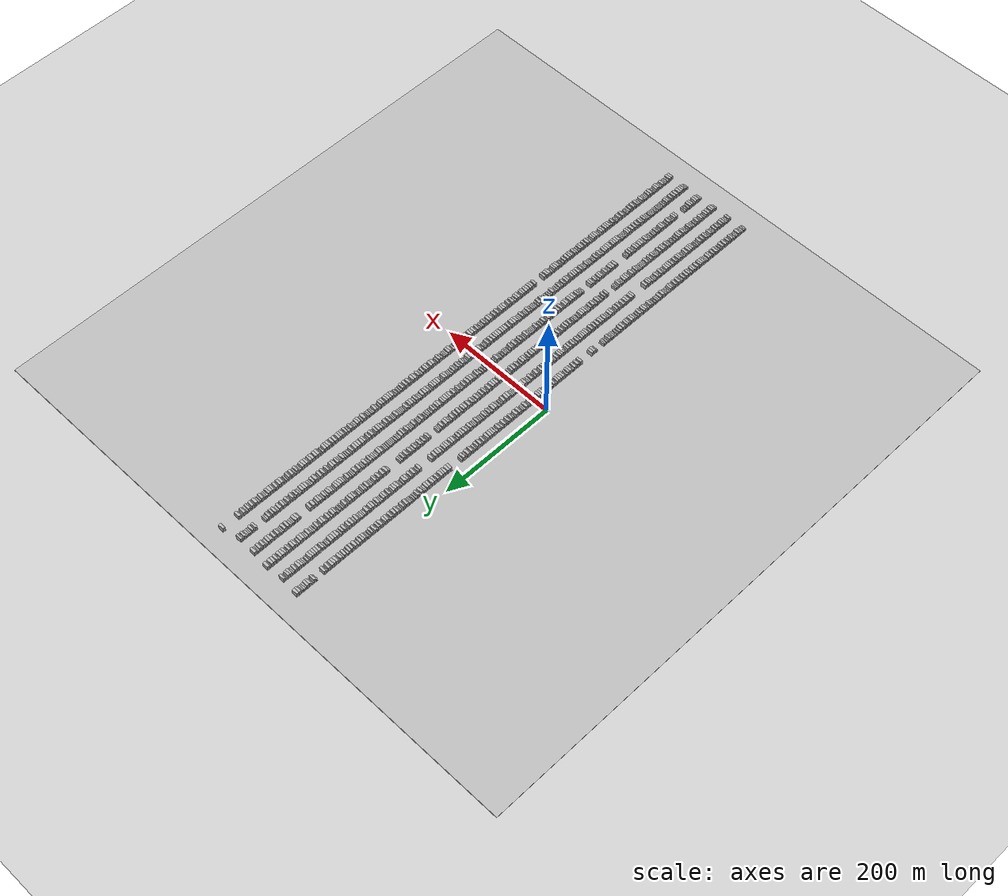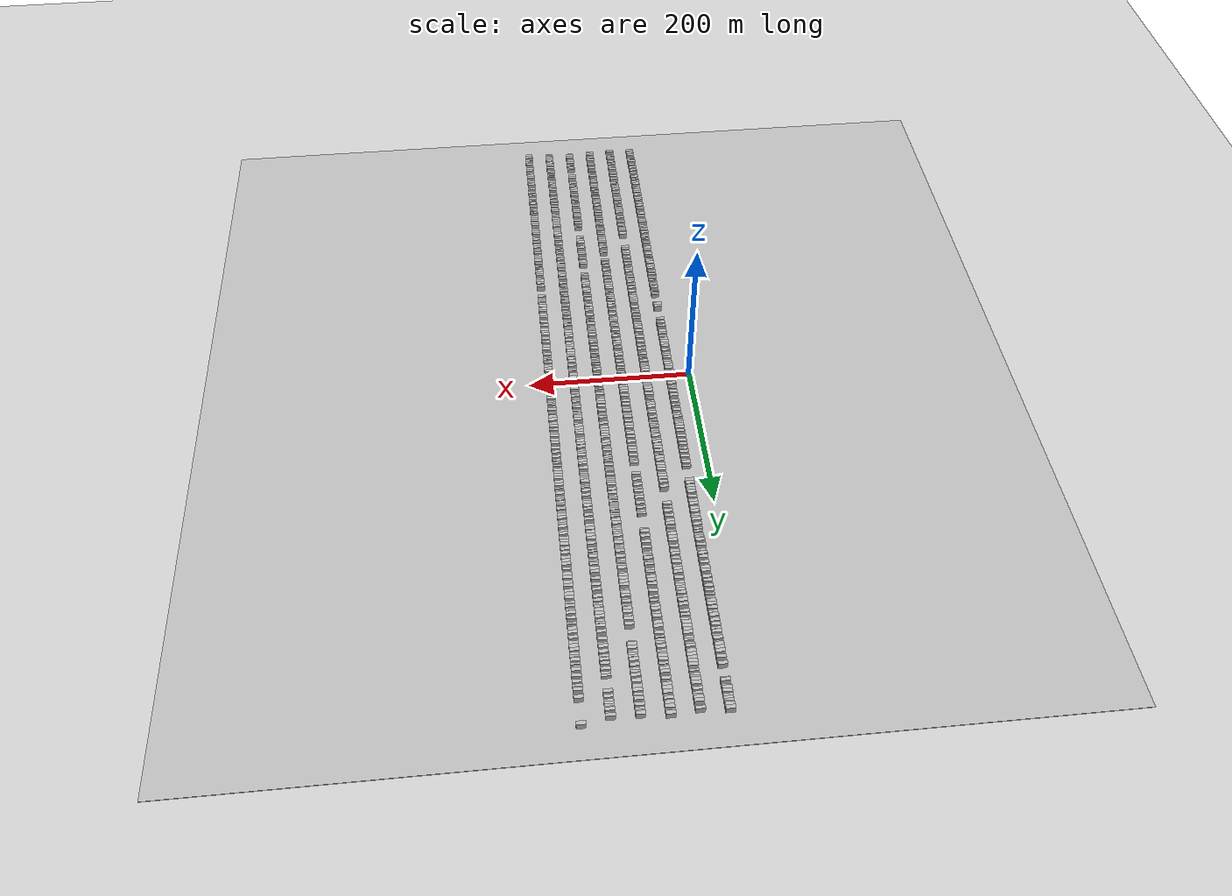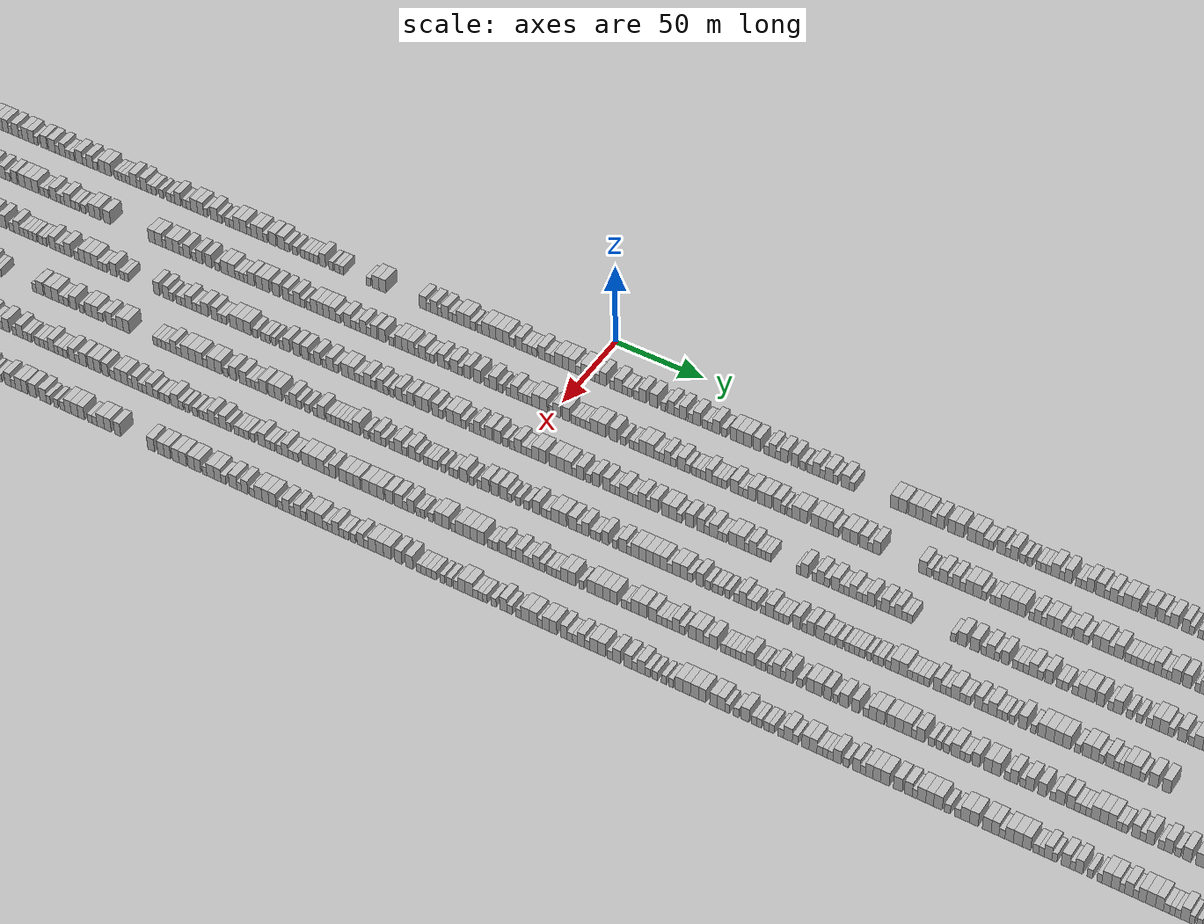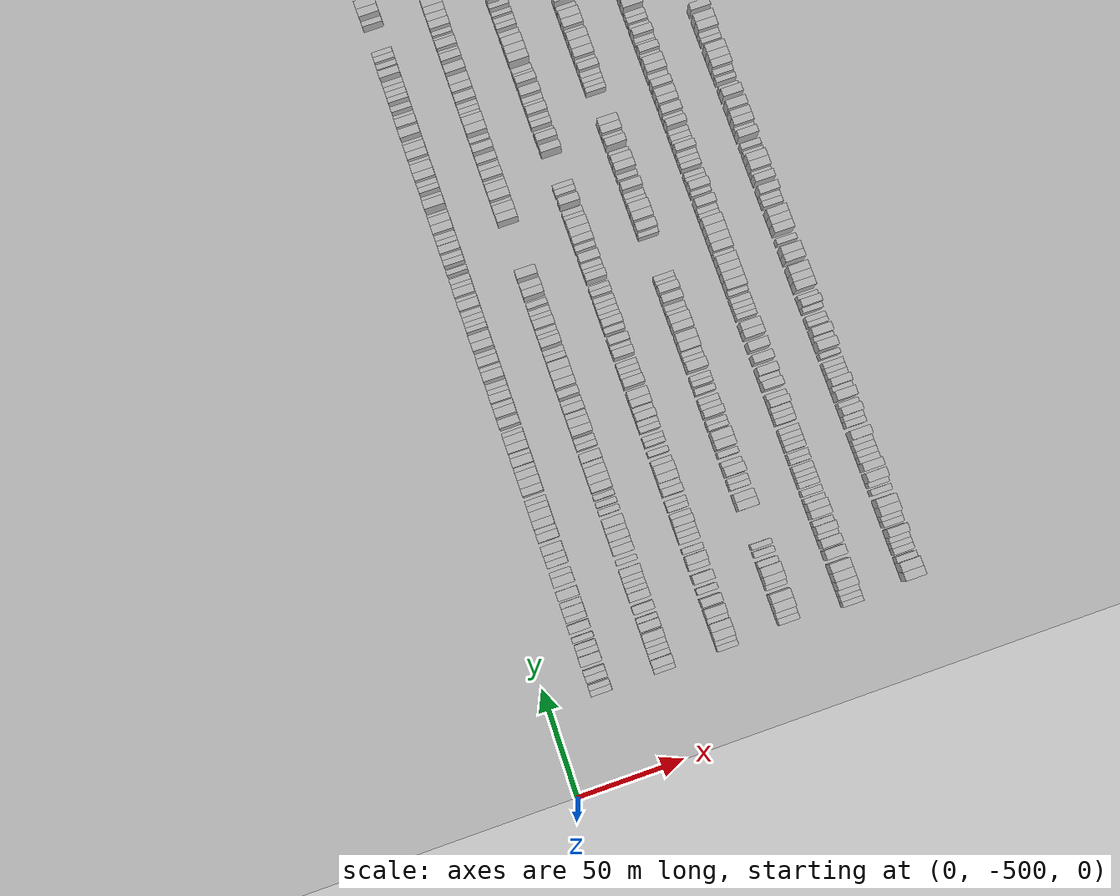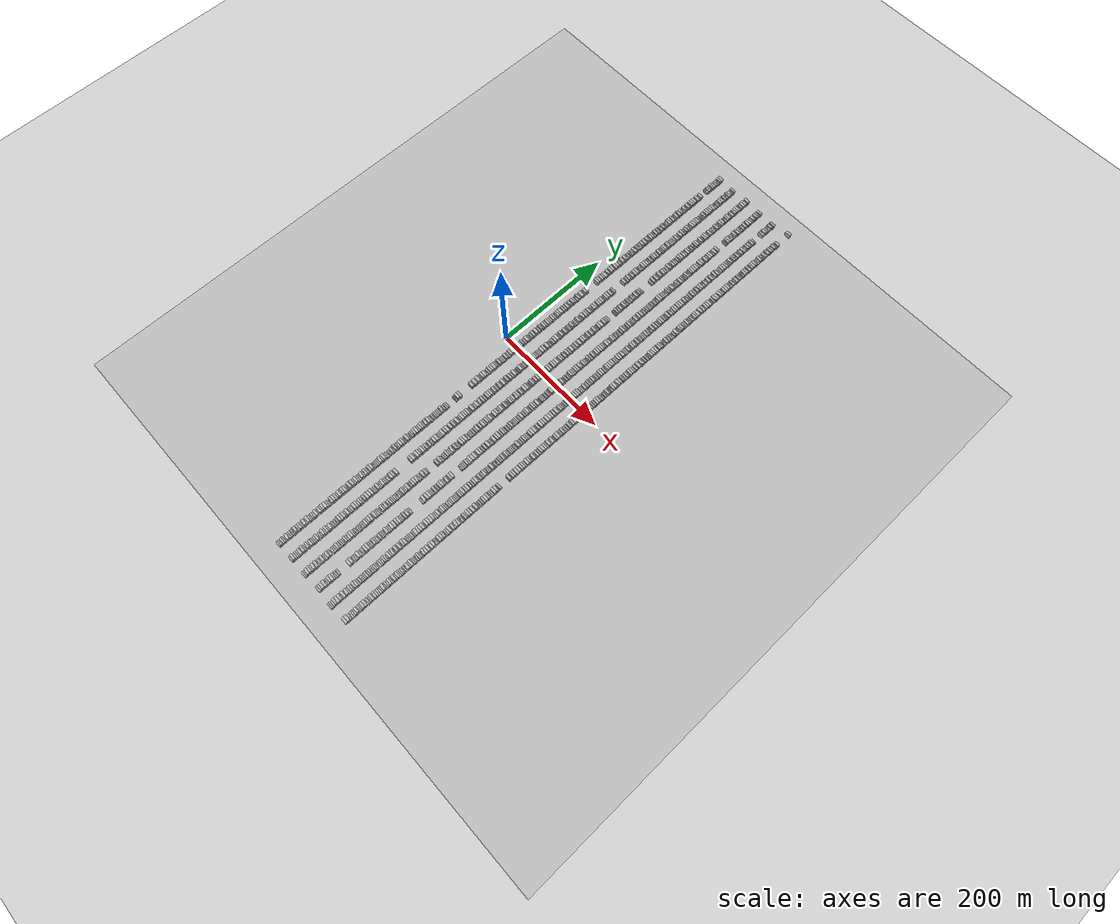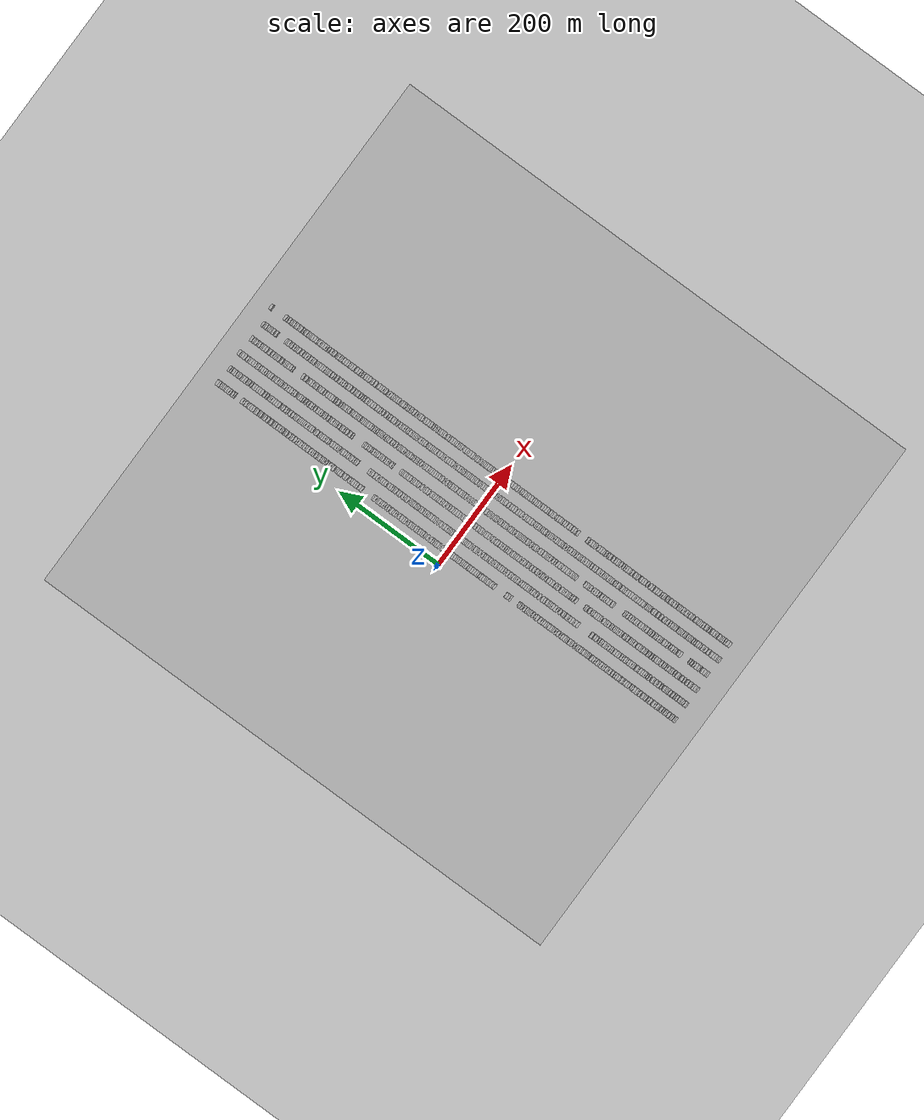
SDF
<sdf version="1.6">
 <world name="default">
  <scene>
   <sky><clouds><speed>12</speed></clouds></sky>
   <ambient>0.4 0.4 0.4 1</ambient>
   <background>0.7 0.7 0.7 1</background>
   <shadows>1</shadows>
  </scene>
  <gravity>0 0 -9.8066</gravity>
  <magnetic_field>6e-06 2.3e-05 -4.2e-05</magnetic_field>
  <physics default="0" name="default_physics" type="ode">
   <ode>
    <solver>
     <type>quick</type>
     <iters>10</iters>
     <sor>1.0</sor>
     <use_dynamic_moi_rescaling>0</use_dynamic_moi_rescaling>
    </solver>
    <constraints>
     <cfm>0</cfm>
     <erp>0.2</erp>
     <contact_max_correcting_vel>100</contact_max_correcting_vel>
     <contact_surface_layer>0.001</contact_surface_layer>
    </constraints>
   </ode>
   <max_step_size>0.004</max_step_size>
   <real_time_factor>1</real_time_factor>
   <real_time_update_rate>250</real_time_update_rate>
  </physics>
  <light name="sun" type="directional">
   <pose>0 0 10 0 0 0</pose>
   <diffuse>0.8 0.8 0.8 1</diffuse>
   <specular>0.2 0.2 0.2 1</specular>
   <attenuation>
    <range>1000</range>
    <constant>0.9</constant>
    <linear>0.01</linear>
    <quadratic>0.001</quadratic>
   </attenuation>
   <direction>-0.5 0.1 -0.9</direction>
  </light>
  <include><name>ground_plane_1</name><uri>model://HANNAS_ground_plane</uri></include>
  <include>
   <name>ground_plane_2</name>
   <uri>model://HANNAS_ground_plane</uri>
   <pose>100 0 0  0 0 0</pose>
  </include>
  <model name="building_1">
   <static>1</static>
   <pose>25.0000 -458.6790 0 0.000000 0.000000 0.000000</pose>
   <link name="link">
    <pose>0 0 3.00 0 0 0</pose>
    <collision name="collision"><geometry><box><size>10.0000 2.6420 6.0000</size></box></geometry></collision>
    <visual name="visual">
     <cast_shadows>0</cast_shadows>
     <geometry><box><size>10.0000 2.6420 6.0000</size></box></geometry>
     <material>
      <script>
       <uri>model://HANNAS_wall/materials/scripts</uri>
       <uri>model://HANNAS_wall/materials/textures</uri>
       <name>vrc/HANNAS_wall</name>
      </script>
     </material>
    </visual>
   </link>
  </model>
  <model name="building_2">
   <static>1</static>
   <pose>25.0000 -456.0709 0 0.000000 0.000000 0.000000</pose>
   <link name="link">
    <pose>0 0 3.00 0 0 0</pose>
    <collision name="collision"><geometry><box><size>10.0000 2.5742 6.0000</size></box></geometry></collision>
    <visual name="visual">
     <cast_shadows>0</cast_shadows>
     <geometry><box><size>10.0000 2.5742 6.0000</size></box></geometry>
     <material>
      <script>
       <uri>model://HANNAS_wall/materials/scripts</uri>
       <uri>model://HANNAS_wall/materials/textures</uri>
       <name>vrc/HANNAS_wall</name>
      </script>
     </material>
    </visual>
   </link>
  </model>
  <model name="building_3">
   <static>1</static>
   <pose>25.0000 -452.2917 0 0.000000 0.000000 0.000000</pose>
   <link name="link">
    <pose>0 0 3.00 0 0 0</pose>
    <collision name="collision"><geometry><box><size>10.0000 2.9840 6.0000</size></box></geometry></collision>
    <visual name="visual">
     <cast_shadows>0</cast_shadows>
     <geometry><box><size>10.0000 2.9840 6.0000</size></box></geometry>
     <material>
      <script>
       <uri>model://HANNAS_wall/materials/scripts</uri>
       <uri>model://HANNAS_wall/materials/textures</uri>
       <name>vrc/HANNAS_wall</name>
      </script>
     </material>
    </visual>
   </link>
  </model>
  <model name="building_4">
   <static>1</static>
   <pose>25.0000 -449.4564 0 0.000000 0.000000 0.000000</pose>
   <link name="link">
    <pose>0 0 3.00 0 0 0</pose>
    <collision name="collision"><geometry><box><size>10.0000 2.6867 6.0000</size></box></geometry></collision>
    <visual name="visual">
     <cast_shadows>0</cast_shadows>
     <geometry><box><size>10.0000 2.6867 6.0000</size></box></geometry>
     <material>
      <script>
       <uri>model://HANNAS_wall/materials/scripts</uri>
       <uri>model://HANNAS_wall/materials/textures</uri>
       <name>vrc/HANNAS_wall</name>
      </script>
     </material>
    </visual>
   </link>
  </model>
  <model name="building_5">
   <static>1</static>
   <pose>25.0000 -443.9394 0 0.000000 0.000000 0.000000</pose>
   <link name="link">
    <pose>0 0 4.50 0 0 0</pose>
    <collision name="collision"><geometry><box><size>10.0000 4.3474 9.0000</size></box></geometry></collision>
    <visual name="visual">
     <cast_shadows>0</cast_shadows>
     <geometry><box><size>10.0000 4.3474 9.0000</size></box></geometry>
     <material>
      <script>
       <uri>model://HANNAS_wall/materials/scripts</uri>
       <uri>model://HANNAS_wall/materials/textures</uri>
       <name>vrc/HANNAS_wall</name>
      </script>
     </material>
    </visual>
   </link>
  </model>
  <model name="building_6">
   <static>1</static>
   <pose>25.0000 -440.3176 0 0.000000 0.000000 0.000000</pose>
   <link name="link">
    <pose>0 0 3.00 0 0 0</pose>
    <collision name="collision"><geometry><box><size>10.0000 2.8962 6.0000</size></box></geometry></collision>
    <visual name="visual">
     <cast_shadows>0</cast_shadows>
     <geometry><box><size>10.0000 2.8962 6.0000</size></box></geometry>
     <material>
      <script>
       <uri>model://HANNAS_wall/materials/scripts</uri>
       <uri>model://HANNAS_wall/materials/textures</uri>
       <name>vrc/HANNAS_wall</name>
      </script>
     </material>
    </visual>
   </link>
  </model>
  <model name="building_7">
   <static>1</static>
   <pose>25.0000 -437.5378 0 0.000000 0.000000 0.000000</pose>
   <link name="link">
    <pose>0 0 3.00 0 0 0</pose>
    <collision name="collision"><geometry><box><size>10.0000 2.6634 6.0000</size></box></geometry></collision>
    <visual name="visual">
     <cast_shadows>0</cast_shadows>
     <geometry><box><size>10.0000 2.6634 6.0000</size></box></geometry>
     <material>
      <script>
       <uri>model://HANNAS_wall/materials/scripts</uri>
       <uri>model://HANNAS_wall/materials/textures</uri>
       <name>vrc/HANNAS_wall</name>
      </script>
     </material>
    </visual>
   </link>
  </model>
  <model name="building_8">
   <static>1</static>
   <pose>25.0000 -433.9782 0 0.000000 0.000000 0.000000</pose>
   <link name="link">
    <pose>0 0 3.00 0 0 0</pose>
    <collision name="collision"><geometry><box><size>10.0000 2.4559 6.0000</size></box></geometry></collision>
    <visual name="visual">
     <cast_shadows>0</cast_shadows>
     <geometry><box><size>10.0000 2.4559 6.0000</size></box></geometry>
     <material>
      <script>
       <uri>model://HANNAS_wall/materials/scripts</uri>
       <uri>model://HANNAS_wall/materials/textures</uri>
       <name>vrc/HANNAS_wall</name>
      </script>
     </material>
    </visual>
   </link>
  </model>
  <model name="building_9">
   <static>1</static>
   <pose>25.0000 -428.8074 0 0.000000 0.000000 0.000000</pose>
   <link name="link">
    <pose>0 0 4.50 0 0 0</pose>
    <collision name="collision"><geometry><box><size>10.0000 3.8858 9.0000</size></box></geometry></collision>
    <visual name="visual">
     <cast_shadows>0</cast_shadows>
     <geometry><box><size>10.0000 3.8858 9.0000</size></box></geometry>
     <material>
      <script>
       <uri>model://HANNAS_wall/materials/scripts</uri>
       <uri>model://HANNAS_wall/materials/textures</uri>
       <name>vrc/HANNAS_wall</name>
      </script>
     </material>
    </visual>
   </link>
  </model>
  <model name="building_10">
   <static>1</static>
   <pose>25.0000 -424.4142 0 0.000000 0.000000 0.000000</pose>
   <link name="link">
    <pose>0 0 3.00 0 0 0</pose>
    <collision name="collision"><geometry><box><size>10.0000 2.9006 6.0000</size></box></geometry></collision>
    <visual name="visual">
     <cast_shadows>0</cast_shadows>
     <geometry><box><size>10.0000 2.9006 6.0000</size></box></geometry>
     <material>
      <script>
       <uri>model://HANNAS_wall/materials/scripts</uri>
       <uri>model://HANNAS_wall/materials/textures</uri>
       <name>vrc/HANNAS_wall</name>
      </script>
     </material>
    </visual>
   </link>
  </model>
  <model name="building_11">
   <static>1</static>
   <pose>25.0000 -421.0236 0 0.000000 0.000000 0.000000</pose>
   <link name="link">
    <pose>0 0 4.50 0 0 0</pose>
    <collision name="collision"><geometry><box><size>10.0000 3.8806 9.0000</size></box></geometry></collision>
    <visual name="visual">
     <cast_shadows>0</cast_shadows>
     <geometry><box><size>10.0000 3.8806 9.0000</size></box></geometry>
     <material>
      <script>
       <uri>model://HANNAS_wall/materials/scripts</uri>
       <uri>model://HANNAS_wall/materials/textures</uri>
       <name>vrc/HANNAS_wall</name>
      </script>
     </material>
    </visual>
   </link>
  </model>
  <model name="building_12">
   <static>1</static>
   <pose>25.0000 -417.7774 0 0.000000 0.000000 0.000000</pose>
   <link name="link">
    <pose>0 0 3.00 0 0 0</pose>
    <collision name="collision"><geometry><box><size>10.0000 2.6117 6.0000</size></box></geometry></collision>
    <visual name="visual">
     <cast_shadows>0</cast_shadows>
     <geometry><box><size>10.0000 2.6117 6.0000</size></box></geometry>
     <material>
      <script>
       <uri>model://HANNAS_wall/materials/scripts</uri>
       <uri>model://HANNAS_wall/materials/textures</uri>
       <name>vrc/HANNAS_wall</name>
      </script>
     </material>
    </visual>
   </link>
  </model>
  <model name="building_13">
   <static>1</static>
   <pose>25.0000 -413.2900 0 0.000000 0.000000 0.000000</pose>
   <link name="link">
    <pose>0 0 4.50 0 0 0</pose>
    <collision name="collision"><geometry><box><size>10.0000 4.3631 9.0000</size></box></geometry></collision>
    <visual name="visual">
     <cast_shadows>0</cast_shadows>
     <geometry><box><size>10.0000 4.3631 9.0000</size></box></geometry>
     <material>
      <script>
       <uri>model://HANNAS_wall/materials/scripts</uri>
       <uri>model://HANNAS_wall/materials/textures</uri>
       <name>vrc/HANNAS_wall</name>
      </script>
     </material>
    </visual>
   </link>
  </model>
  <model name="building_14">
   <static>1</static>
   <pose>25.0000 -406.9527 0 0.000000 0.000000 0.000000</pose>
   <link name="link">
    <pose>0 0 4.50 0 0 0</pose>
    <collision name="collision"><geometry><box><size>10.0000 4.3116 9.0000</size></box></geometry></collision>
    <visual name="visual">
     <cast_shadows>0</cast_shadows>
     <geometry><box><size>10.0000 4.3116 9.0000</size></box></geometry>
     <material>
      <script>
       <uri>model://HANNAS_wall/materials/scripts</uri>
       <uri>model://HANNAS_wall/materials/textures</uri>
       <name>vrc/HANNAS_wall</name>
      </script>
     </material>
    </visual>
   </link>
  </model>
  <model name="building_15">
   <static>1</static>
   <pose>25.0000 -403.4073 0 0.000000 0.000000 0.000000</pose>
   <link name="link">
    <pose>0 0 3.00 0 0 0</pose>
    <collision name="collision"><geometry><box><size>10.0000 2.7791 6.0000</size></box></geometry></collision>
    <visual name="visual">
     <cast_shadows>0</cast_shadows>
     <geometry><box><size>10.0000 2.7791 6.0000</size></box></geometry>
     <material>
      <script>
       <uri>model://HANNAS_wall/materials/scripts</uri>
       <uri>model://HANNAS_wall/materials/textures</uri>
       <name>vrc/HANNAS_wall</name>
      </script>
     </material>
    </visual>
   </link>
  </model>
  <model name="building_16">
   <static>1</static>
   <pose>25.0000 -398.5282 0 0.000000 0.000000 0.000000</pose>
   <link name="link">
    <pose>0 0 3.00 0 0 0</pose>
    <collision name="collision"><geometry><box><size>10.0000 2.9791 6.0000</size></box></geometry></collision>
    <visual name="visual">
     <cast_shadows>0</cast_shadows>
     <geometry><box><size>10.0000 2.9791 6.0000</size></box></geometry>
     <material>
      <script>
       <uri>model://HANNAS_wall/materials/scripts</uri>
       <uri>model://HANNAS_wall/materials/textures</uri>
       <name>vrc/HANNAS_wall</name>
      </script>
     </material>
    </visual>
   </link>
  </model>
  <model name="building_17">
   <static>1</static>
   <pose>25.0000 -395.6226 0 0.000000 0.000000 0.000000</pose>
   <link name="link">
    <pose>0 0 3.00 0 0 0</pose>
    <collision name="collision"><geometry><box><size>10.0000 2.8319 6.0000</size></box></geometry></collision>
    <visual name="visual">
     <cast_shadows>0</cast_shadows>
     <geometry><box><size>10.0000 2.8319 6.0000</size></box></geometry>
     <material>
      <script>
       <uri>model://HANNAS_wall/materials/scripts</uri>
       <uri>model://HANNAS_wall/materials/textures</uri>
       <name>vrc/HANNAS_wall</name>
      </script>
     </material>
    </visual>
   </link>
  </model>
  <model name="building_18">
   <static>1</static>
   <pose>25.0000 -392.0398 0 0.000000 0.000000 0.000000</pose>
   <link name="link">
    <pose>0 0 4.50 0 0 0</pose>
    <collision name="collision"><geometry><box><size>10.0000 4.3338 9.0000</size></box></geometry></collision>
    <visual name="visual">
     <cast_shadows>0</cast_shadows>
     <geometry><box><size>10.0000 4.3338 9.0000</size></box></geometry>
     <material>
      <script>
       <uri>model://HANNAS_wall/materials/scripts</uri>
       <uri>model://HANNAS_wall/materials/textures</uri>
       <name>vrc/HANNAS_wall</name>
      </script>
     </material>
    </visual>
   </link>
  </model>
  <model name="building_19">
   <static>1</static>
   <pose>25.0000 -385.9689 0 0.000000 0.000000 0.000000</pose>
   <link name="link">
    <pose>0 0 4.50 0 0 0</pose>
    <collision name="collision"><geometry><box><size>10.0000 3.8081 9.0000</size></box></geometry></collision>
    <visual name="visual">
     <cast_shadows>0</cast_shadows>
     <geometry><box><size>10.0000 3.8081 9.0000</size></box></geometry>
     <material>
      <script>
       <uri>model://HANNAS_wall/materials/scripts</uri>
       <uri>model://HANNAS_wall/materials/textures</uri>
       <name>vrc/HANNAS_wall</name>
      </script>
     </material>
    </visual>
   </link>
  </model>
  <model name="building_20">
   <static>1</static>
   <pose>25.0000 -382.8556 0 0.000000 0.000000 0.000000</pose>
   <link name="link">
    <pose>0 0 3.00 0 0 0</pose>
    <collision name="collision"><geometry><box><size>10.0000 2.4185 6.0000</size></box></geometry></collision>
    <visual name="visual">
     <cast_shadows>0</cast_shadows>
     <geometry><box><size>10.0000 2.4185 6.0000</size></box></geometry>
     <material>
      <script>
       <uri>model://HANNAS_wall/materials/scripts</uri>
       <uri>model://HANNAS_wall/materials/textures</uri>
       <name>vrc/HANNAS_wall</name>
      </script>
     </material>
    </visual>
   </link>
  </model>
  <model name="building_21">
   <static>1</static>
   <pose>25.0000 -379.7127 0 0.000000 0.000000 0.000000</pose>
   <link name="link">
    <pose>0 0 4.50 0 0 0</pose>
    <collision name="collision"><geometry><box><size>10.0000 3.8672 9.0000</size></box></geometry></collision>
    <visual name="visual">
     <cast_shadows>0</cast_shadows>
     <geometry><box><size>10.0000 3.8672 9.0000</size></box></geometry>
     <material>
      <script>
       <uri>model://HANNAS_wall/materials/scripts</uri>
       <uri>model://HANNAS_wall/materials/textures</uri>
       <name>vrc/HANNAS_wall</name>
      </script>
     </material>
    </visual>
   </link>
  </model>
  <model name="building_22">
   <static>1</static>
   <pose>25.0000 -375.5730 0 0.000000 0.000000 0.000000</pose>
   <link name="link">
    <pose>0 0 4.50 0 0 0</pose>
    <collision name="collision"><geometry><box><size>10.0000 4.4122 9.0000</size></box></geometry></collision>
    <visual name="visual">
     <cast_shadows>0</cast_shadows>
     <geometry><box><size>10.0000 4.4122 9.0000</size></box></geometry>
     <material>
      <script>
       <uri>model://HANNAS_wall/materials/scripts</uri>
       <uri>model://HANNAS_wall/materials/textures</uri>
       <name>vrc/HANNAS_wall</name>
      </script>
     </material>
    </visual>
   </link>
  </model>
  <model name="building_23">
   <static>1</static>
   <pose>25.0000 -371.8883 0 0.000000 0.000000 0.000000</pose>
   <link name="link">
    <pose>0 0 3.00 0 0 0</pose>
    <collision name="collision"><geometry><box><size>10.0000 2.9571 6.0000</size></box></geometry></collision>
    <visual name="visual">
     <cast_shadows>0</cast_shadows>
     <geometry><box><size>10.0000 2.9571 6.0000</size></box></geometry>
     <material>
      <script>
       <uri>model://HANNAS_wall/materials/scripts</uri>
       <uri>model://HANNAS_wall/materials/textures</uri>
       <name>vrc/HANNAS_wall</name>
      </script>
     </material>
    </visual>
   </link>
  </model>
  <model name="building_24">
   <static>1</static>
   <pose>25.0000 -369.1019 0 0.000000 0.000000 0.000000</pose>
   <link name="link">
    <pose>0 0 3.00 0 0 0</pose>
    <collision name="collision"><geometry><box><size>10.0000 2.6157 6.0000</size></box></geometry></collision>
    <visual name="visual">
     <cast_shadows>0</cast_shadows>
     <geometry><box><size>10.0000 2.6157 6.0000</size></box></geometry>
     <material>
      <script>
       <uri>model://HANNAS_wall/materials/scripts</uri>
       <uri>model://HANNAS_wall/materials/textures</uri>
       <name>vrc/HANNAS_wall</name>
      </script>
     </material>
    </visual>
   </link>
  </model>
  <model name="building_25">
   <static>1</static>
   <pose>25.0000 -363.9805 0 0.000000 0.000000 0.000000</pose>
   <link name="link">
    <pose>0 0 4.50 0 0 0</pose>
    <collision name="collision"><geometry><box><size>10.0000 3.6271 9.0000</size></box></geometry></collision>
    <visual name="visual">
     <cast_shadows>0</cast_shadows>
     <geometry><box><size>10.0000 3.6271 9.0000</size></box></geometry>
     <material>
      <script>
       <uri>model://HANNAS_wall/materials/scripts</uri>
       <uri>model://HANNAS_wall/materials/textures</uri>
       <name>vrc/HANNAS_wall</name>
      </script>
     </material>
    </visual>
   </link>
  </model>
  <model name="building_26">
   <static>1</static>
   <pose>25.0000 -360.1234 0 0.000000 0.000000 0.000000</pose>
   <link name="link">
    <pose>0 0 4.50 0 0 0</pose>
    <collision name="collision"><geometry><box><size>10.0000 4.0871 9.0000</size></box></geometry></collision>
    <visual name="visual">
     <cast_shadows>0</cast_shadows>
     <geometry><box><size>10.0000 4.0871 9.0000</size></box></geometry>
     <material>
      <script>
       <uri>model://HANNAS_wall/materials/scripts</uri>
       <uri>model://HANNAS_wall/materials/textures</uri>
       <name>vrc/HANNAS_wall</name>
      </script>
     </material>
    </visual>
   </link>
  </model>
  <model name="building_27">
   <static>1</static>
   <pose>25.0000 -356.2291 0 0.000000 0.000000 0.000000</pose>
   <link name="link">
    <pose>0 0 4.50 0 0 0</pose>
    <collision name="collision"><geometry><box><size>10.0000 3.7016 9.0000</size></box></geometry></collision>
    <visual name="visual">
     <cast_shadows>0</cast_shadows>
     <geometry><box><size>10.0000 3.7016 9.0000</size></box></geometry>
     <material>
      <script>
       <uri>model://HANNAS_wall/materials/scripts</uri>
       <uri>model://HANNAS_wall/materials/textures</uri>
       <name>vrc/HANNAS_wall</name>
      </script>
     </material>
    </visual>
   </link>
  </model>
  <model name="building_28">
   <static>1</static>
   <pose>25.0000 -353.1717 0 0.000000 0.000000 0.000000</pose>
   <link name="link">
    <pose>0 0 3.00 0 0 0</pose>
    <collision name="collision"><geometry><box><size>10.0000 2.4133 6.0000</size></box></geometry></collision>
    <visual name="visual">
     <cast_shadows>0</cast_shadows>
     <geometry><box><size>10.0000 2.4133 6.0000</size></box></geometry>
     <material>
      <script>
       <uri>model://HANNAS_wall/materials/scripts</uri>
       <uri>model://HANNAS_wall/materials/textures</uri>
       <name>vrc/HANNAS_wall</name>
      </script>
     </material>
    </visual>
   </link>
  </model>
  <model name="building_29">
   <static>1</static>
   <pose>25.0000 -349.8425 0 0.000000 0.000000 0.000000</pose>
   <link name="link">
    <pose>0 0 4.50 0 0 0</pose>
    <collision name="collision"><geometry><box><size>10.0000 4.2451 9.0000</size></box></geometry></collision>
    <visual name="visual">
     <cast_shadows>0</cast_shadows>
     <geometry><box><size>10.0000 4.2451 9.0000</size></box></geometry>
     <material>
      <script>
       <uri>model://HANNAS_wall/materials/scripts</uri>
       <uri>model://HANNAS_wall/materials/textures</uri>
       <name>vrc/HANNAS_wall</name>
      </script>
     </material>
    </visual>
   </link>
  </model>
  <model name="building_30">
   <static>1</static>
   <pose>25.0000 -346.5036 0 0.000000 0.000000 0.000000</pose>
   <link name="link">
    <pose>0 0 3.00 0 0 0</pose>
    <collision name="collision"><geometry><box><size>10.0000 2.4326 6.0000</size></box></geometry></collision>
    <visual name="visual">
     <cast_shadows>0</cast_shadows>
     <geometry><box><size>10.0000 2.4326 6.0000</size></box></geometry>
     <material>
      <script>
       <uri>model://HANNAS_wall/materials/scripts</uri>
       <uri>model://HANNAS_wall/materials/textures</uri>
       <name>vrc/HANNAS_wall</name>
      </script>
     </material>
    </visual>
   </link>
  </model>
  <model name="building_31">
   <static>1</static>
   <pose>25.0000 -343.3185 0 0.000000 0.000000 0.000000</pose>
   <link name="link">
    <pose>0 0 4.50 0 0 0</pose>
    <collision name="collision"><geometry><box><size>10.0000 3.9378 9.0000</size></box></geometry></collision>
    <visual name="visual">
     <cast_shadows>0</cast_shadows>
     <geometry><box><size>10.0000 3.9378 9.0000</size></box></geometry>
     <material>
      <script>
       <uri>model://HANNAS_wall/materials/scripts</uri>
       <uri>model://HANNAS_wall/materials/textures</uri>
       <name>vrc/HANNAS_wall</name>
      </script>
     </material>
    </visual>
   </link>
  </model>
  <model name="building_32">
   <static>1</static>
   <pose>25.0000 -339.4338 0 0.000000 0.000000 0.000000</pose>
   <link name="link">
    <pose>0 0 4.50 0 0 0</pose>
    <collision name="collision"><geometry><box><size>10.0000 3.8315 9.0000</size></box></geometry></collision>
    <visual name="visual">
     <cast_shadows>0</cast_shadows>
     <geometry><box><size>10.0000 3.8315 9.0000</size></box></geometry>
     <material>
      <script>
       <uri>model://HANNAS_wall/materials/scripts</uri>
       <uri>model://HANNAS_wall/materials/textures</uri>
       <name>vrc/HANNAS_wall</name>
      </script>
     </material>
    </visual>
   </link>
  </model>
  <model name="building_33">
   <static>1</static>
   <pose>25.0000 -336.2794 0 0.000000 0.000000 0.000000</pose>
   <link name="link">
    <pose>0 0 3.00 0 0 0</pose>
    <collision name="collision"><geometry><box><size>10.0000 2.4774 6.0000</size></box></geometry></collision>
    <visual name="visual">
     <cast_shadows>0</cast_shadows>
     <geometry><box><size>10.0000 2.4774 6.0000</size></box></geometry>
     <material>
      <script>
       <uri>model://HANNAS_wall/materials/scripts</uri>
       <uri>model://HANNAS_wall/materials/textures</uri>
       <name>vrc/HANNAS_wall</name>
      </script>
     </material>
    </visual>
   </link>
  </model>
  <model name="building_34">
   <static>1</static>
   <pose>25.0000 -331.0184 0 0.000000 0.000000 0.000000</pose>
   <link name="link">
    <pose>0 0 4.50 0 0 0</pose>
    <collision name="collision"><geometry><box><size>10.0000 4.0446 9.0000</size></box></geometry></collision>
    <visual name="visual">
     <cast_shadows>0</cast_shadows>
     <geometry><box><size>10.0000 4.0446 9.0000</size></box></geometry>
     <material>
      <script>
       <uri>model://HANNAS_wall/materials/scripts</uri>
       <uri>model://HANNAS_wall/materials/textures</uri>
       <name>vrc/HANNAS_wall</name>
      </script>
     </material>
    </visual>
   </link>
  </model>
  <model name="building_35">
   <static>1</static>
   <pose>25.0000 -325.8341 0 0.000000 0.000000 0.000000</pose>
   <link name="link">
    <pose>0 0 4.50 0 0 0</pose>
    <collision name="collision"><geometry><box><size>10.0000 4.3239 9.0000</size></box></geometry></collision>
    <visual name="visual">
     <cast_shadows>0</cast_shadows>
     <geometry><box><size>10.0000 4.3239 9.0000</size></box></geometry>
     <material>
      <script>
       <uri>model://HANNAS_wall/materials/scripts</uri>
       <uri>model://HANNAS_wall/materials/textures</uri>
       <name>vrc/HANNAS_wall</name>
      </script>
     </material>
    </visual>
   </link>
  </model>
  <model name="building_36">
   <static>1</static>
   <pose>25.0000 -322.2972 0 0.000000 0.000000 0.000000</pose>
   <link name="link">
    <pose>0 0 3.00 0 0 0</pose>
    <collision name="collision"><geometry><box><size>10.0000 2.7499 6.0000</size></box></geometry></collision>
    <visual name="visual">
     <cast_shadows>0</cast_shadows>
     <geometry><box><size>10.0000 2.7499 6.0000</size></box></geometry>
     <material>
      <script>
       <uri>model://HANNAS_wall/materials/scripts</uri>
       <uri>model://HANNAS_wall/materials/textures</uri>
       <name>vrc/HANNAS_wall</name>
      </script>
     </material>
    </visual>
   </link>
  </model>
  <model name="building_37">
   <static>1</static>
   <pose>25.0000 -318.9817 0 0.000000 0.000000 0.000000</pose>
   <link name="link">
    <pose>0 0 4.50 0 0 0</pose>
    <collision name="collision"><geometry><box><size>10.0000 3.8811 9.0000</size></box></geometry></collision>
    <visual name="visual">
     <cast_shadows>0</cast_shadows>
     <geometry><box><size>10.0000 3.8811 9.0000</size></box></geometry>
     <material>
      <script>
       <uri>model://HANNAS_wall/materials/scripts</uri>
       <uri>model://HANNAS_wall/materials/textures</uri>
       <name>vrc/HANNAS_wall</name>
      </script>
     </material>
    </visual>
   </link>
  </model>
  <model name="building_38">
   <static>1</static>
   <pose>25.0000 -315.6081 0 0.000000 0.000000 0.000000</pose>
   <link name="link">
    <pose>0 0 3.00 0 0 0</pose>
    <collision name="collision"><geometry><box><size>10.0000 2.8661 6.0000</size></box></geometry></collision>
    <visual name="visual">
     <cast_shadows>0</cast_shadows>
     <geometry><box><size>10.0000 2.8661 6.0000</size></box></geometry>
     <material>
      <script>
       <uri>model://HANNAS_wall/materials/scripts</uri>
       <uri>model://HANNAS_wall/materials/textures</uri>
       <name>vrc/HANNAS_wall</name>
      </script>
     </material>
    </visual>
   </link>
  </model>
  <model name="building_39">
   <static>1</static>
   <pose>25.0000 -312.7521 0 0.000000 0.000000 0.000000</pose>
   <link name="link">
    <pose>0 0 3.00 0 0 0</pose>
    <collision name="collision"><geometry><box><size>10.0000 2.8459 6.0000</size></box></geometry></collision>
    <visual name="visual">
     <cast_shadows>0</cast_shadows>
     <geometry><box><size>10.0000 2.8459 6.0000</size></box></geometry>
     <material>
      <script>
       <uri>model://HANNAS_wall/materials/scripts</uri>
       <uri>model://HANNAS_wall/materials/textures</uri>
       <name>vrc/HANNAS_wall</name>
      </script>
     </material>
    </visual>
   </link>
  </model>
  <model name="building_40">
   <static>1</static>
   <pose>25.0000 -308.1326 0 0.000000 0.000000 0.000000</pose>
   <link name="link">
    <pose>0 0 4.50 0 0 0</pose>
    <collision name="collision"><geometry><box><size>10.0000 4.3932 9.0000</size></box></geometry></collision>
    <visual name="visual">
     <cast_shadows>0</cast_shadows>
     <geometry><box><size>10.0000 4.3932 9.0000</size></box></geometry>
     <material>
      <script>
       <uri>model://HANNAS_wall/materials/scripts</uri>
       <uri>model://HANNAS_wall/materials/textures</uri>
       <name>vrc/HANNAS_wall</name>
      </script>
     </material>
    </visual>
   </link>
  </model>
  <model name="building_41">
   <static>1</static>
   <pose>25.0000 -304.5776 0 0.000000 0.000000 0.000000</pose>
   <link name="link">
    <pose>0 0 3.00 0 0 0</pose>
    <collision name="collision"><geometry><box><size>10.0000 2.7168 6.0000</size></box></geometry></collision>
    <visual name="visual">
     <cast_shadows>0</cast_shadows>
     <geometry><box><size>10.0000 2.7168 6.0000</size></box></geometry>
     <material>
      <script>
       <uri>model://HANNAS_wall/materials/scripts</uri>
       <uri>model://HANNAS_wall/materials/textures</uri>
       <name>vrc/HANNAS_wall</name>
      </script>
     </material>
    </visual>
   </link>
  </model>
  <model name="building_42">
   <static>1</static>
   <pose>25.0000 -301.1863 0 0.000000 0.000000 0.000000</pose>
   <link name="link">
    <pose>0 0 4.50 0 0 0</pose>
    <collision name="collision"><geometry><box><size>10.0000 4.0658 9.0000</size></box></geometry></collision>
    <visual name="visual">
     <cast_shadows>0</cast_shadows>
     <geometry><box><size>10.0000 4.0658 9.0000</size></box></geometry>
     <material>
      <script>
       <uri>model://HANNAS_wall/materials/scripts</uri>
       <uri>model://HANNAS_wall/materials/textures</uri>
       <name>vrc/HANNAS_wall</name>
      </script>
     </material>
    </visual>
   </link>
  </model>
  <model name="building_43">
   <static>1</static>
   <pose>25.0000 -297.7364 0 0.000000 0.000000 0.000000</pose>
   <link name="link">
    <pose>0 0 3.00 0 0 0</pose>
    <collision name="collision"><geometry><box><size>10.0000 2.8341 6.0000</size></box></geometry></collision>
    <visual name="visual">
     <cast_shadows>0</cast_shadows>
     <geometry><box><size>10.0000 2.8341 6.0000</size></box></geometry>
     <material>
      <script>
       <uri>model://HANNAS_wall/materials/scripts</uri>
       <uri>model://HANNAS_wall/materials/textures</uri>
       <name>vrc/HANNAS_wall</name>
      </script>
     </material>
    </visual>
   </link>
  </model>
  <model name="building_44">
   <static>1</static>
   <pose>25.0000 -293.3809 0 0.000000 0.000000 0.000000</pose>
   <link name="link">
    <pose>0 0 4.50 0 0 0</pose>
    <collision name="collision"><geometry><box><size>10.0000 3.8769 9.0000</size></box></geometry></collision>
    <visual name="visual">
     <cast_shadows>0</cast_shadows>
     <geometry><box><size>10.0000 3.8769 9.0000</size></box></geometry>
     <material>
      <script>
       <uri>model://HANNAS_wall/materials/scripts</uri>
       <uri>model://HANNAS_wall/materials/textures</uri>
       <name>vrc/HANNAS_wall</name>
      </script>
     </material>
    </visual>
   </link>
  </model>
  <model name="building_45">
   <static>1</static>
   <pose>25.0000 -289.4906 0 0.000000 0.000000 0.000000</pose>
   <link name="link">
    <pose>0 0 4.50 0 0 0</pose>
    <collision name="collision"><geometry><box><size>10.0000 3.9037 9.0000</size></box></geometry></collision>
    <visual name="visual">
     <cast_shadows>0</cast_shadows>
     <geometry><box><size>10.0000 3.9037 9.0000</size></box></geometry>
     <material>
      <script>
       <uri>model://HANNAS_wall/materials/scripts</uri>
       <uri>model://HANNAS_wall/materials/textures</uri>
       <name>vrc/HANNAS_wall</name>
      </script>
     </material>
    </visual>
   </link>
  </model>
  <model name="building_46">
   <static>1</static>
   <pose>25.0000 -284.3265 0 0.000000 0.000000 0.000000</pose>
   <link name="link">
    <pose>0 0 3.00 0 0 0</pose>
    <collision name="collision"><geometry><box><size>10.0000 2.4246 6.0000</size></box></geometry></collision>
    <visual name="visual">
     <cast_shadows>0</cast_shadows>
     <geometry><box><size>10.0000 2.4246 6.0000</size></box></geometry>
     <material>
      <script>
       <uri>model://HANNAS_wall/materials/scripts</uri>
       <uri>model://HANNAS_wall/materials/textures</uri>
       <name>vrc/HANNAS_wall</name>
      </script>
     </material>
    </visual>
   </link>
  </model>
  <model name="building_47">
   <static>1</static>
   <pose>25.0000 -281.9100 0 0.000000 0.000000 0.000000</pose>
   <link name="link">
    <pose>0 0 3.00 0 0 0</pose>
    <collision name="collision"><geometry><box><size>10.0000 2.4084 6.0000</size></box></geometry></collision>
    <visual name="visual">
     <cast_shadows>0</cast_shadows>
     <geometry><box><size>10.0000 2.4084 6.0000</size></box></geometry>
     <material>
      <script>
       <uri>model://HANNAS_wall/materials/scripts</uri>
       <uri>model://HANNAS_wall/materials/textures</uri>
       <name>vrc/HANNAS_wall</name>
      </script>
     </material>
    </visual>
   </link>
  </model>
  <model name="building_48">
   <static>1</static>
   <pose>25.0000 -279.4076 0 0.000000 0.000000 0.000000</pose>
   <link name="link">
    <pose>0 0 3.00 0 0 0</pose>
    <collision name="collision"><geometry><box><size>10.0000 2.5966 6.0000</size></box></geometry></collision>
    <visual name="visual">
     <cast_shadows>0</cast_shadows>
     <geometry><box><size>10.0000 2.5966 6.0000</size></box></geometry>
     <material>
      <script>
       <uri>model://HANNAS_wall/materials/scripts</uri>
       <uri>model://HANNAS_wall/materials/textures</uri>
       <name>vrc/HANNAS_wall</name>
      </script>
     </material>
    </visual>
   </link>
  </model>
  <model name="building_49">
   <static>1</static>
   <pose>25.0000 -276.7826 0 0.000000 0.000000 0.000000</pose>
   <link name="link">
    <pose>0 0 3.00 0 0 0</pose>
    <collision name="collision"><geometry><box><size>10.0000 2.6533 6.0000</size></box></geometry></collision>
    <visual name="visual">
     <cast_shadows>0</cast_shadows>
     <geometry><box><size>10.0000 2.6533 6.0000</size></box></geometry>
     <material>
      <script>
       <uri>model://HANNAS_wall/materials/scripts</uri>
       <uri>model://HANNAS_wall/materials/textures</uri>
       <name>vrc/HANNAS_wall</name>
      </script>
     </material>
    </visual>
   </link>
  </model>
  <model name="building_50">
   <static>1</static>
   <pose>25.0000 -273.2904 0 0.000000 0.000000 0.000000</pose>
   <link name="link">
    <pose>0 0 4.50 0 0 0</pose>
    <collision name="collision"><geometry><box><size>10.0000 4.3311 9.0000</size></box></geometry></collision>
    <visual name="visual">
     <cast_shadows>0</cast_shadows>
     <geometry><box><size>10.0000 4.3311 9.0000</size></box></geometry>
     <material>
      <script>
       <uri>model://HANNAS_wall/materials/scripts</uri>
       <uri>model://HANNAS_wall/materials/textures</uri>
       <name>vrc/HANNAS_wall</name>
      </script>
     </material>
    </visual>
   </link>
  </model>
  <model name="building_51">
   <static>1</static>
   <pose>25.0000 -269.8968 0 0.000000 0.000000 0.000000</pose>
   <link name="link">
    <pose>0 0 3.00 0 0 0</pose>
    <collision name="collision"><geometry><box><size>10.0000 2.4562 6.0000</size></box></geometry></collision>
    <visual name="visual">
     <cast_shadows>0</cast_shadows>
     <geometry><box><size>10.0000 2.4562 6.0000</size></box></geometry>
     <material>
      <script>
       <uri>model://HANNAS_wall/materials/scripts</uri>
       <uri>model://HANNAS_wall/materials/textures</uri>
       <name>vrc/HANNAS_wall</name>
      </script>
     </material>
    </visual>
   </link>
  </model>
  <model name="building_52">
   <static>1</static>
   <pose>25.0000 -266.6651 0 0.000000 0.000000 0.000000</pose>
   <link name="link">
    <pose>0 0 4.50 0 0 0</pose>
    <collision name="collision"><geometry><box><size>10.0000 4.0073 9.0000</size></box></geometry></collision>
    <visual name="visual">
     <cast_shadows>0</cast_shadows>
     <geometry><box><size>10.0000 4.0073 9.0000</size></box></geometry>
     <material>
      <script>
       <uri>model://HANNAS_wall/materials/scripts</uri>
       <uri>model://HANNAS_wall/materials/textures</uri>
       <name>vrc/HANNAS_wall</name>
      </script>
     </material>
    </visual>
   </link>
  </model>
  <model name="building_53">
   <static>1</static>
   <pose>25.0000 -263.1774 0 0.000000 0.000000 0.000000</pose>
   <link name="link">
    <pose>0 0 3.00 0 0 0</pose>
    <collision name="collision"><geometry><box><size>10.0000 2.9680 6.0000</size></box></geometry></collision>
    <visual name="visual">
     <cast_shadows>0</cast_shadows>
     <geometry><box><size>10.0000 2.9680 6.0000</size></box></geometry>
     <material>
      <script>
       <uri>model://HANNAS_wall/materials/scripts</uri>
       <uri>model://HANNAS_wall/materials/textures</uri>
       <name>vrc/HANNAS_wall</name>
      </script>
     </material>
    </visual>
   </link>
  </model>
  <model name="building_54">
   <static>1</static>
   <pose>25.0000 -260.2049 0 0.000000 0.000000 0.000000</pose>
   <link name="link">
    <pose>0 0 3.00 0 0 0</pose>
    <collision name="collision"><geometry><box><size>10.0000 2.9771 6.0000</size></box></geometry></collision>
    <visual name="visual">
     <cast_shadows>0</cast_shadows>
     <geometry><box><size>10.0000 2.9771 6.0000</size></box></geometry>
     <material>
      <script>
       <uri>model://HANNAS_wall/materials/scripts</uri>
       <uri>model://HANNAS_wall/materials/textures</uri>
       <name>vrc/HANNAS_wall</name>
      </script>
     </material>
    </visual>
   </link>
  </model>
  <model name="building_55">
   <static>1</static>
   <pose>25.0000 -255.4980 0 0.000000 0.000000 0.000000</pose>
   <link name="link">
    <pose>0 0 3.00 0 0 0</pose>
    <collision name="collision"><geometry><box><size>10.0000 2.4366 6.0000</size></box></geometry></collision>
    <visual name="visual">
     <cast_shadows>0</cast_shadows>
     <geometry><box><size>10.0000 2.4366 6.0000</size></box></geometry>
     <material>
      <script>
       <uri>model://HANNAS_wall/materials/scripts</uri>
       <uri>model://HANNAS_wall/materials/textures</uri>
       <name>vrc/HANNAS_wall</name>
      </script>
     </material>
    </visual>
   </link>
  </model>
  <model name="building_56">
   <static>1</static>
   <pose>25.0000 -250.8059 0 0.000000 0.000000 0.000000</pose>
   <link name="link">
    <pose>0 0 3.00 0 0 0</pose>
    <collision name="collision"><geometry><box><size>10.0000 2.9476 6.0000</size></box></geometry></collision>
    <visual name="visual">
     <cast_shadows>0</cast_shadows>
     <geometry><box><size>10.0000 2.9476 6.0000</size></box></geometry>
     <material>
      <script>
       <uri>model://HANNAS_wall/materials/scripts</uri>
       <uri>model://HANNAS_wall/materials/textures</uri>
       <name>vrc/HANNAS_wall</name>
      </script>
     </material>
    </visual>
   </link>
  </model>
  <model name="building_57">
   <static>1</static>
   <pose>25.0000 -248.0919 0 0.000000 0.000000 0.000000</pose>
   <link name="link">
    <pose>0 0 3.00 0 0 0</pose>
    <collision name="collision"><geometry><box><size>10.0000 2.4805 6.0000</size></box></geometry></collision>
    <visual name="visual">
     <cast_shadows>0</cast_shadows>
     <geometry><box><size>10.0000 2.4805 6.0000</size></box></geometry>
     <material>
      <script>
       <uri>model://HANNAS_wall/materials/scripts</uri>
       <uri>model://HANNAS_wall/materials/textures</uri>
       <name>vrc/HANNAS_wall</name>
      </script>
     </material>
    </visual>
   </link>
  </model>
  <model name="building_58">
   <static>1</static>
   <pose>25.0000 -244.9559 0 0.000000 0.000000 0.000000</pose>
   <link name="link">
    <pose>0 0 4.50 0 0 0</pose>
    <collision name="collision"><geometry><box><size>10.0000 3.7914 9.0000</size></box></geometry></collision>
    <visual name="visual">
     <cast_shadows>0</cast_shadows>
     <geometry><box><size>10.0000 3.7914 9.0000</size></box></geometry>
     <material>
      <script>
       <uri>model://HANNAS_wall/materials/scripts</uri>
       <uri>model://HANNAS_wall/materials/textures</uri>
       <name>vrc/HANNAS_wall</name>
      </script>
     </material>
    </visual>
   </link>
  </model>
  <model name="building_59">
   <static>1</static>
   <pose>25.0000 -240.8540 0 0.000000 0.000000 0.000000</pose>
   <link name="link">
    <pose>0 0 3.00 0 0 0</pose>
    <collision name="collision"><geometry><box><size>10.0000 2.4125 6.0000</size></box></geometry></collision>
    <visual name="visual">
     <cast_shadows>0</cast_shadows>
     <geometry><box><size>10.0000 2.4125 6.0000</size></box></geometry>
     <material>
      <script>
       <uri>model://HANNAS_wall/materials/scripts</uri>
       <uri>model://HANNAS_wall/materials/textures</uri>
       <name>vrc/HANNAS_wall</name>
      </script>
     </material>
    </visual>
   </link>
  </model>
  <model name="building_60">
   <static>1</static>
   <pose>25.0000 -238.2404 0 0.000000 0.000000 0.000000</pose>
   <link name="link">
    <pose>0 0 3.00 0 0 0</pose>
    <collision name="collision"><geometry><box><size>10.0000 2.8147 6.0000</size></box></geometry></collision>
    <visual name="visual">
     <cast_shadows>0</cast_shadows>
     <geometry><box><size>10.0000 2.8147 6.0000</size></box></geometry>
     <material>
      <script>
       <uri>model://HANNAS_wall/materials/scripts</uri>
       <uri>model://HANNAS_wall/materials/textures</uri>
       <name>vrc/HANNAS_wall</name>
      </script>
     </material>
    </visual>
   </link>
  </model>
  <model name="building_61">
   <static>1</static>
   <pose>25.0000 -234.7269 0 0.000000 0.000000 0.000000</pose>
   <link name="link">
    <pose>0 0 4.50 0 0 0</pose>
    <collision name="collision"><geometry><box><size>10.0000 4.2123 9.0000</size></box></geometry></collision>
    <visual name="visual">
     <cast_shadows>0</cast_shadows>
     <geometry><box><size>10.0000 4.2123 9.0000</size></box></geometry>
     <material>
      <script>
       <uri>model://HANNAS_wall/materials/scripts</uri>
       <uri>model://HANNAS_wall/materials/textures</uri>
       <name>vrc/HANNAS_wall</name>
      </script>
     </material>
    </visual>
   </link>
  </model>
  <model name="building_62">
   <static>1</static>
   <pose>25.0000 -230.6934 0 0.000000 0.000000 0.000000</pose>
   <link name="link">
    <pose>0 0 4.50 0 0 0</pose>
    <collision name="collision"><geometry><box><size>10.0000 3.8547 9.0000</size></box></geometry></collision>
    <visual name="visual">
     <cast_shadows>0</cast_shadows>
     <geometry><box><size>10.0000 3.8547 9.0000</size></box></geometry>
     <material>
      <script>
       <uri>model://HANNAS_wall/materials/scripts</uri>
       <uri>model://HANNAS_wall/materials/textures</uri>
       <name>vrc/HANNAS_wall</name>
      </script>
     </material>
    </visual>
   </link>
  </model>
  <model name="building_63">
   <static>1</static>
   <pose>25.0000 -227.5191 0 0.000000 0.000000 0.000000</pose>
   <link name="link">
    <pose>0 0 3.00 0 0 0</pose>
    <collision name="collision"><geometry><box><size>10.0000 2.4938 6.0000</size></box></geometry></collision>
    <visual name="visual">
     <cast_shadows>0</cast_shadows>
     <geometry><box><size>10.0000 2.4938 6.0000</size></box></geometry>
     <material>
      <script>
       <uri>model://HANNAS_wall/materials/scripts</uri>
       <uri>model://HANNAS_wall/materials/textures</uri>
       <name>vrc/HANNAS_wall</name>
      </script>
     </material>
    </visual>
   </link>
  </model>
  <model name="building_64">
   <static>1</static>
   <pose>25.0000 -222.1138 0 0.000000 0.000000 0.000000</pose>
   <link name="link">
    <pose>0 0 4.50 0 0 0</pose>
    <collision name="collision"><geometry><box><size>10.0000 4.3168 9.0000</size></box></geometry></collision>
    <visual name="visual">
     <cast_shadows>0</cast_shadows>
     <geometry><box><size>10.0000 4.3168 9.0000</size></box></geometry>
     <material>
      <script>
       <uri>model://HANNAS_wall/materials/scripts</uri>
       <uri>model://HANNAS_wall/materials/textures</uri>
       <name>vrc/HANNAS_wall</name>
      </script>
     </material>
    </visual>
   </link>
  </model>
  <model name="building_65">
   <static>1</static>
   <pose>25.0000 -218.5914 0 0.000000 0.000000 0.000000</pose>
   <link name="link">
    <pose>0 0 3.00 0 0 0</pose>
    <collision name="collision"><geometry><box><size>10.0000 2.7280 6.0000</size></box></geometry></collision>
    <visual name="visual">
     <cast_shadows>0</cast_shadows>
     <geometry><box><size>10.0000 2.7280 6.0000</size></box></geometry>
     <material>
      <script>
       <uri>model://HANNAS_wall/materials/scripts</uri>
       <uri>model://HANNAS_wall/materials/textures</uri>
       <name>vrc/HANNAS_wall</name>
      </script>
     </material>
    </visual>
   </link>
  </model>
  <model name="building_66">
   <static>1</static>
   <pose>25.0000 -213.8740 0 0.000000 0.000000 0.000000</pose>
   <link name="link">
    <pose>0 0 3.00 0 0 0</pose>
    <collision name="collision"><geometry><box><size>10.0000 2.7068 6.0000</size></box></geometry></collision>
    <visual name="visual">
     <cast_shadows>0</cast_shadows>
     <geometry><box><size>10.0000 2.7068 6.0000</size></box></geometry>
     <material>
      <script>
       <uri>model://HANNAS_wall/materials/scripts</uri>
       <uri>model://HANNAS_wall/materials/textures</uri>
       <name>vrc/HANNAS_wall</name>
      </script>
     </material>
    </visual>
   </link>
  </model>
  <model name="building_67">
   <static>1</static>
   <pose>25.0000 -211.2467 0 0.000000 0.000000 0.000000</pose>
   <link name="link">
    <pose>0 0 3.00 0 0 0</pose>
    <collision name="collision"><geometry><box><size>10.0000 2.5478 6.0000</size></box></geometry></collision>
    <visual name="visual">
     <cast_shadows>0</cast_shadows>
     <geometry><box><size>10.0000 2.5478 6.0000</size></box></geometry>
     <material>
      <script>
       <uri>model://HANNAS_wall/materials/scripts</uri>
       <uri>model://HANNAS_wall/materials/textures</uri>
       <name>vrc/HANNAS_wall</name>
      </script>
     </material>
    </visual>
   </link>
  </model>
  <model name="building_68">
   <static>1</static>
   <pose>25.0000 -208.0414 0 0.000000 0.000000 0.000000</pose>
   <link name="link">
    <pose>0 0 4.50 0 0 0</pose>
    <collision name="collision"><geometry><box><size>10.0000 3.8626 9.0000</size></box></geometry></collision>
    <visual name="visual">
     <cast_shadows>0</cast_shadows>
     <geometry><box><size>10.0000 3.8626 9.0000</size></box></geometry>
     <material>
      <script>
       <uri>model://HANNAS_wall/materials/scripts</uri>
       <uri>model://HANNAS_wall/materials/textures</uri>
       <name>vrc/HANNAS_wall</name>
      </script>
     </material>
    </visual>
   </link>
  </model>
  <model name="building_69">
   <static>1</static>
   <pose>25.0000 -203.9562 0 0.000000 0.000000 0.000000</pose>
   <link name="link">
    <pose>0 0 4.50 0 0 0</pose>
    <collision name="collision"><geometry><box><size>10.0000 4.3080 9.0000</size></box></geometry></collision>
    <visual name="visual">
     <cast_shadows>0</cast_shadows>
     <geometry><box><size>10.0000 4.3080 9.0000</size></box></geometry>
     <material>
      <script>
       <uri>model://HANNAS_wall/materials/scripts</uri>
       <uri>model://HANNAS_wall/materials/textures</uri>
       <name>vrc/HANNAS_wall</name>
      </script>
     </material>
    </visual>
   </link>
  </model>
  <model name="building_70">
   <static>1</static>
   <pose>25.0000 -200.4395 0 0.000000 0.000000 0.000000</pose>
   <link name="link">
    <pose>0 0 3.00 0 0 0</pose>
    <collision name="collision"><geometry><box><size>10.0000 2.7252 6.0000</size></box></geometry></collision>
    <visual name="visual">
     <cast_shadows>0</cast_shadows>
     <geometry><box><size>10.0000 2.7252 6.0000</size></box></geometry>
     <material>
      <script>
       <uri>model://HANNAS_wall/materials/scripts</uri>
       <uri>model://HANNAS_wall/materials/textures</uri>
       <name>vrc/HANNAS_wall</name>
      </script>
     </material>
    </visual>
   </link>
  </model>
  <model name="building_71">
   <static>1</static>
   <pose>25.0000 -197.2259 0 0.000000 0.000000 0.000000</pose>
   <link name="link">
    <pose>0 0 4.50 0 0 0</pose>
    <collision name="collision"><geometry><box><size>10.0000 3.7020 9.0000</size></box></geometry></collision>
    <visual name="visual">
     <cast_shadows>0</cast_shadows>
     <geometry><box><size>10.0000 3.7020 9.0000</size></box></geometry>
     <material>
      <script>
       <uri>model://HANNAS_wall/materials/scripts</uri>
       <uri>model://HANNAS_wall/materials/textures</uri>
       <name>vrc/HANNAS_wall</name>
      </script>
     </material>
    </visual>
   </link>
  </model>
  <model name="building_72">
   <static>1</static>
   <pose>25.0000 -193.4871 0 0.000000 0.000000 0.000000</pose>
   <link name="link">
    <pose>0 0 4.50 0 0 0</pose>
    <collision name="collision"><geometry><box><size>10.0000 3.7757 9.0000</size></box></geometry></collision>
    <visual name="visual">
     <cast_shadows>0</cast_shadows>
     <geometry><box><size>10.0000 3.7757 9.0000</size></box></geometry>
     <material>
      <script>
       <uri>model://HANNAS_wall/materials/scripts</uri>
       <uri>model://HANNAS_wall/materials/textures</uri>
       <name>vrc/HANNAS_wall</name>
      </script>
     </material>
    </visual>
   </link>
  </model>
  <model name="building_73">
   <static>1</static>
   <pose>25.0000 -190.2673 0 0.000000 0.000000 0.000000</pose>
   <link name="link">
    <pose>0 0 3.00 0 0 0</pose>
    <collision name="collision"><geometry><box><size>10.0000 2.6640 6.0000</size></box></geometry></collision>
    <visual name="visual">
     <cast_shadows>0</cast_shadows>
     <geometry><box><size>10.0000 2.6640 6.0000</size></box></geometry>
     <material>
      <script>
       <uri>model://HANNAS_wall/materials/scripts</uri>
       <uri>model://HANNAS_wall/materials/textures</uri>
       <name>vrc/HANNAS_wall</name>
      </script>
     </material>
    </visual>
   </link>
  </model>
  <model name="building_74">
   <static>1</static>
   <pose>25.0000 -185.7619 0 0.000000 0.000000 0.000000</pose>
   <link name="link">
    <pose>0 0 4.50 0 0 0</pose>
    <collision name="collision"><geometry><box><size>10.0000 4.3467 9.0000</size></box></geometry></collision>
    <visual name="visual">
     <cast_shadows>0</cast_shadows>
     <geometry><box><size>10.0000 4.3467 9.0000</size></box></geometry>
     <material>
      <script>
       <uri>model://HANNAS_wall/materials/scripts</uri>
       <uri>model://HANNAS_wall/materials/textures</uri>
       <name>vrc/HANNAS_wall</name>
      </script>
     </material>
    </visual>
   </link>
  </model>
  <model name="building_75">
   <static>1</static>
   <pose>25.0000 -180.4142 0 0.000000 0.000000 0.000000</pose>
   <link name="link">
    <pose>0 0 4.50 0 0 0</pose>
    <collision name="collision"><geometry><box><size>10.0000 4.3488 9.0000</size></box></geometry></collision>
    <visual name="visual">
     <cast_shadows>0</cast_shadows>
     <geometry><box><size>10.0000 4.3488 9.0000</size></box></geometry>
     <material>
      <script>
       <uri>model://HANNAS_wall/materials/scripts</uri>
       <uri>model://HANNAS_wall/materials/textures</uri>
       <name>vrc/HANNAS_wall</name>
      </script>
     </material>
    </visual>
   </link>
  </model>
  <model name="building_76">
   <static>1</static>
   <pose>25.0000 -176.8170 0 0.000000 0.000000 0.000000</pose>
   <link name="link">
    <pose>0 0 3.00 0 0 0</pose>
    <collision name="collision"><geometry><box><size>10.0000 2.8456 6.0000</size></box></geometry></collision>
    <visual name="visual">
     <cast_shadows>0</cast_shadows>
     <geometry><box><size>10.0000 2.8456 6.0000</size></box></geometry>
     <material>
      <script>
       <uri>model://HANNAS_wall/materials/scripts</uri>
       <uri>model://HANNAS_wall/materials/textures</uri>
       <name>vrc/HANNAS_wall</name>
      </script>
     </material>
    </visual>
   </link>
  </model>
  <model name="building_77">
   <static>1</static>
   <pose>25.0000 -171.9462 0 0.000000 0.000000 0.000000</pose>
   <link name="link">
    <pose>0 0 3.00 0 0 0</pose>
    <collision name="collision"><geometry><box><size>10.0000 2.8960 6.0000</size></box></geometry></collision>
    <visual name="visual">
     <cast_shadows>0</cast_shadows>
     <geometry><box><size>10.0000 2.8960 6.0000</size></box></geometry>
     <material>
      <script>
       <uri>model://HANNAS_wall/materials/scripts</uri>
       <uri>model://HANNAS_wall/materials/textures</uri>
       <name>vrc/HANNAS_wall</name>
      </script>
     </material>
    </visual>
   </link>
  </model>
  <model name="building_78">
   <static>1</static>
   <pose>25.0000 -167.1948 0 0.000000 0.000000 0.000000</pose>
   <link name="link">
    <pose>0 0 3.00 0 0 0</pose>
    <collision name="collision"><geometry><box><size>10.0000 2.6068 6.0000</size></box></geometry></collision>
    <visual name="visual">
     <cast_shadows>0</cast_shadows>
     <geometry><box><size>10.0000 2.6068 6.0000</size></box></geometry>
     <material>
      <script>
       <uri>model://HANNAS_wall/materials/scripts</uri>
       <uri>model://HANNAS_wall/materials/textures</uri>
       <name>vrc/HANNAS_wall</name>
      </script>
     </material>
    </visual>
   </link>
  </model>
  <model name="building_79">
   <static>1</static>
   <pose>25.0000 -164.4544 0 0.000000 0.000000 0.000000</pose>
   <link name="link">
    <pose>0 0 3.00 0 0 0</pose>
    <collision name="collision"><geometry><box><size>10.0000 2.8740 6.0000</size></box></geometry></collision>
    <visual name="visual">
     <cast_shadows>0</cast_shadows>
     <geometry><box><size>10.0000 2.8740 6.0000</size></box></geometry>
     <material>
      <script>
       <uri>model://HANNAS_wall/materials/scripts</uri>
       <uri>model://HANNAS_wall/materials/textures</uri>
       <name>vrc/HANNAS_wall</name>
      </script>
     </material>
    </visual>
   </link>
  </model>
  <model name="building_80">
   <static>1</static>
   <pose>25.0000 -161.7639 0 0.000000 0.000000 0.000000</pose>
   <link name="link">
    <pose>0 0 3.00 0 0 0</pose>
    <collision name="collision"><geometry><box><size>10.0000 2.5069 6.0000</size></box></geometry></collision>
    <visual name="visual">
     <cast_shadows>0</cast_shadows>
     <geometry><box><size>10.0000 2.5069 6.0000</size></box></geometry>
     <material>
      <script>
       <uri>model://HANNAS_wall/materials/scripts</uri>
       <uri>model://HANNAS_wall/materials/textures</uri>
       <name>vrc/HANNAS_wall</name>
      </script>
     </material>
    </visual>
   </link>
  </model>
  <model name="building_81">
   <static>1</static>
   <pose>25.0000 -159.1774 0 0.000000 0.000000 0.000000</pose>
   <link name="link">
    <pose>0 0 3.00 0 0 0</pose>
    <collision name="collision"><geometry><box><size>10.0000 2.6662 6.0000</size></box></geometry></collision>
    <visual name="visual">
     <cast_shadows>0</cast_shadows>
     <geometry><box><size>10.0000 2.6662 6.0000</size></box></geometry>
     <material>
      <script>
       <uri>model://HANNAS_wall/materials/scripts</uri>
       <uri>model://HANNAS_wall/materials/textures</uri>
       <name>vrc/HANNAS_wall</name>
      </script>
     </material>
    </visual>
   </link>
  </model>
  <model name="building_82">
   <static>1</static>
   <pose>25.0000 -155.0126 0 0.000000 0.000000 0.000000</pose>
   <link name="link">
    <pose>0 0 4.50 0 0 0</pose>
    <collision name="collision"><geometry><box><size>10.0000 3.6634 9.0000</size></box></geometry></collision>
    <visual name="visual">
     <cast_shadows>0</cast_shadows>
     <geometry><box><size>10.0000 3.6634 9.0000</size></box></geometry>
     <material>
      <script>
       <uri>model://HANNAS_wall/materials/scripts</uri>
       <uri>model://HANNAS_wall/materials/textures</uri>
       <name>vrc/HANNAS_wall</name>
      </script>
     </material>
    </visual>
   </link>
  </model>
  <model name="building_83">
   <static>1</static>
   <pose>25.0000 -149.8587 0 0.000000 0.000000 0.000000</pose>
   <link name="link">
    <pose>0 0 3.00 0 0 0</pose>
    <collision name="collision"><geometry><box><size>10.0000 2.6444 6.0000</size></box></geometry></collision>
    <visual name="visual">
     <cast_shadows>0</cast_shadows>
     <geometry><box><size>10.0000 2.6444 6.0000</size></box></geometry>
     <material>
      <script>
       <uri>model://HANNAS_wall/materials/scripts</uri>
       <uri>model://HANNAS_wall/materials/textures</uri>
       <name>vrc/HANNAS_wall</name>
      </script>
     </material>
    </visual>
   </link>
  </model>
  <model name="building_84">
   <static>1</static>
   <pose>25.0000 -146.0959 0 0.000000 0.000000 0.000000</pose>
   <link name="link">
    <pose>0 0 3.00 0 0 0</pose>
    <collision name="collision"><geometry><box><size>10.0000 2.8811 6.0000</size></box></geometry></collision>
    <visual name="visual">
     <cast_shadows>0</cast_shadows>
     <geometry><box><size>10.0000 2.8811 6.0000</size></box></geometry>
     <material>
      <script>
       <uri>model://HANNAS_wall/materials/scripts</uri>
       <uri>model://HANNAS_wall/materials/textures</uri>
       <name>vrc/HANNAS_wall</name>
      </script>
     </material>
    </visual>
   </link>
  </model>
  <model name="building_85">
   <static>1</static>
   <pose>25.0000 -143.4187 0 0.000000 0.000000 0.000000</pose>
   <link name="link">
    <pose>0 0 3.00 0 0 0</pose>
    <collision name="collision"><geometry><box><size>10.0000 2.4735 6.0000</size></box></geometry></collision>
    <visual name="visual">
     <cast_shadows>0</cast_shadows>
     <geometry><box><size>10.0000 2.4735 6.0000</size></box></geometry>
     <material>
      <script>
       <uri>model://HANNAS_wall/materials/scripts</uri>
       <uri>model://HANNAS_wall/materials/textures</uri>
       <name>vrc/HANNAS_wall</name>
      </script>
     </material>
    </visual>
   </link>
  </model>
  <model name="building_86">
   <static>1</static>
   <pose>25.0000 -127.1393 0 0.000000 0.000000 0.000000</pose>
   <link name="link">
    <pose>0 0 3.00 0 0 0</pose>
    <collision name="collision"><geometry><box><size>10.0000 2.6951 6.0000</size></box></geometry></collision>
    <visual name="visual">
     <cast_shadows>0</cast_shadows>
     <geometry><box><size>10.0000 2.6951 6.0000</size></box></geometry>
     <material>
      <script>
       <uri>model://HANNAS_wall/materials/scripts</uri>
       <uri>model://HANNAS_wall/materials/textures</uri>
       <name>vrc/HANNAS_wall</name>
      </script>
     </material>
    </visual>
   </link>
  </model>
  <model name="building_87">
   <static>1</static>
   <pose>25.0000 -122.7769 0 0.000000 0.000000 0.000000</pose>
   <link name="link">
    <pose>0 0 4.50 0 0 0</pose>
    <collision name="collision"><geometry><box><size>10.0000 4.0297 9.0000</size></box></geometry></collision>
    <visual name="visual">
     <cast_shadows>0</cast_shadows>
     <geometry><box><size>10.0000 4.0297 9.0000</size></box></geometry>
     <material>
      <script>
       <uri>model://HANNAS_wall/materials/scripts</uri>
       <uri>model://HANNAS_wall/materials/textures</uri>
       <name>vrc/HANNAS_wall</name>
      </script>
     </material>
    </visual>
   </link>
  </model>
  <model name="building_88">
   <static>1</static>
   <pose>25.0000 -118.6511 0 0.000000 0.000000 0.000000</pose>
   <link name="link">
    <pose>0 0 4.50 0 0 0</pose>
    <collision name="collision"><geometry><box><size>10.0000 4.2219 9.0000</size></box></geometry></collision>
    <visual name="visual">
     <cast_shadows>0</cast_shadows>
     <geometry><box><size>10.0000 4.2219 9.0000</size></box></geometry>
     <material>
      <script>
       <uri>model://HANNAS_wall/materials/scripts</uri>
       <uri>model://HANNAS_wall/materials/textures</uri>
       <name>vrc/HANNAS_wall</name>
      </script>
     </material>
    </visual>
   </link>
  </model>
  <model name="building_89">
   <static>1</static>
   <pose>25.0000 -94.5242 0 0.000000 0.000000 0.000000</pose>
   <link name="link">
    <pose>0 0 4.50 0 0 0</pose>
    <collision name="collision"><geometry><box><size>10.0000 4.0106 9.0000</size></box></geometry></collision>
    <visual name="visual">
     <cast_shadows>0</cast_shadows>
     <geometry><box><size>10.0000 4.0106 9.0000</size></box></geometry>
     <material>
      <script>
       <uri>model://HANNAS_wall/materials/scripts</uri>
       <uri>model://HANNAS_wall/materials/textures</uri>
       <name>vrc/HANNAS_wall</name>
      </script>
     </material>
    </visual>
   </link>
  </model>
  <model name="building_90">
   <static>1</static>
   <pose>25.0000 -91.2445 0 0.000000 0.000000 0.000000</pose>
   <link name="link">
    <pose>0 0 3.00 0 0 0</pose>
    <collision name="collision"><geometry><box><size>10.0000 2.5489 6.0000</size></box></geometry></collision>
    <visual name="visual">
     <cast_shadows>0</cast_shadows>
     <geometry><box><size>10.0000 2.5489 6.0000</size></box></geometry>
     <material>
      <script>
       <uri>model://HANNAS_wall/materials/scripts</uri>
       <uri>model://HANNAS_wall/materials/textures</uri>
       <name>vrc/HANNAS_wall</name>
      </script>
     </material>
    </visual>
   </link>
  </model>
  <model name="building_91">
   <static>1</static>
   <pose>25.0000 -87.8965 0 0.000000 0.000000 0.000000</pose>
   <link name="link">
    <pose>0 0 4.50 0 0 0</pose>
    <collision name="collision"><geometry><box><size>10.0000 4.1472 9.0000</size></box></geometry></collision>
    <visual name="visual">
     <cast_shadows>0</cast_shadows>
     <geometry><box><size>10.0000 4.1472 9.0000</size></box></geometry>
     <material>
      <script>
       <uri>model://HANNAS_wall/materials/scripts</uri>
       <uri>model://HANNAS_wall/materials/textures</uri>
       <name>vrc/HANNAS_wall</name>
      </script>
     </material>
    </visual>
   </link>
  </model>
  <model name="building_92">
   <static>1</static>
   <pose>25.0000 -84.5938 0 0.000000 0.000000 0.000000</pose>
   <link name="link">
    <pose>0 0 3.00 0 0 0</pose>
    <collision name="collision"><geometry><box><size>10.0000 2.4582 6.0000</size></box></geometry></collision>
    <visual name="visual">
     <cast_shadows>0</cast_shadows>
     <geometry><box><size>10.0000 2.4582 6.0000</size></box></geometry>
     <material>
      <script>
       <uri>model://HANNAS_wall/materials/scripts</uri>
       <uri>model://HANNAS_wall/materials/textures</uri>
       <name>vrc/HANNAS_wall</name>
      </script>
     </material>
    </visual>
   </link>
  </model>
  <model name="building_93">
   <static>1</static>
   <pose>25.0000 -81.3081 0 0.000000 0.000000 0.000000</pose>
   <link name="link">
    <pose>0 0 4.50 0 0 0</pose>
    <collision name="collision"><geometry><box><size>10.0000 4.1131 9.0000</size></box></geometry></collision>
    <visual name="visual">
     <cast_shadows>0</cast_shadows>
     <geometry><box><size>10.0000 4.1131 9.0000</size></box></geometry>
     <material>
      <script>
       <uri>model://HANNAS_wall/materials/scripts</uri>
       <uri>model://HANNAS_wall/materials/textures</uri>
       <name>vrc/HANNAS_wall</name>
      </script>
     </material>
    </visual>
   </link>
  </model>
  <model name="building_94">
   <static>1</static>
   <pose>25.0000 -78.0422 0 0.000000 0.000000 0.000000</pose>
   <link name="link">
    <pose>0 0 3.00 0 0 0</pose>
    <collision name="collision"><geometry><box><size>10.0000 2.4187 6.0000</size></box></geometry></collision>
    <visual name="visual">
     <cast_shadows>0</cast_shadows>
     <geometry><box><size>10.0000 2.4187 6.0000</size></box></geometry>
     <material>
      <script>
       <uri>model://HANNAS_wall/materials/scripts</uri>
       <uri>model://HANNAS_wall/materials/textures</uri>
       <name>vrc/HANNAS_wall</name>
      </script>
     </material>
    </visual>
   </link>
  </model>
  <model name="building_95">
   <static>1</static>
   <pose>25.0000 -75.6158 0 0.000000 0.000000 0.000000</pose>
   <link name="link">
    <pose>0 0 3.00 0 0 0</pose>
    <collision name="collision"><geometry><box><size>10.0000 2.4341 6.0000</size></box></geometry></collision>
    <visual name="visual">
     <cast_shadows>0</cast_shadows>
     <geometry><box><size>10.0000 2.4341 6.0000</size></box></geometry>
     <material>
      <script>
       <uri>model://HANNAS_wall/materials/scripts</uri>
       <uri>model://HANNAS_wall/materials/textures</uri>
       <name>vrc/HANNAS_wall</name>
      </script>
     </material>
    </visual>
   </link>
  </model>
  <model name="building_96">
   <static>1</static>
   <pose>25.0000 -72.2609 0 0.000000 0.000000 0.000000</pose>
   <link name="link">
    <pose>0 0 4.50 0 0 0</pose>
    <collision name="collision"><geometry><box><size>10.0000 4.2758 9.0000</size></box></geometry></collision>
    <visual name="visual">
     <cast_shadows>0</cast_shadows>
     <geometry><box><size>10.0000 4.2758 9.0000</size></box></geometry>
     <material>
      <script>
       <uri>model://HANNAS_wall/materials/scripts</uri>
       <uri>model://HANNAS_wall/materials/textures</uri>
       <name>vrc/HANNAS_wall</name>
      </script>
     </material>
    </visual>
   </link>
  </model>
  <model name="building_97">
   <static>1</static>
   <pose>25.0000 -68.1911 0 0.000000 0.000000 0.000000</pose>
   <link name="link">
    <pose>0 0 4.50 0 0 0</pose>
    <collision name="collision"><geometry><box><size>10.0000 3.8638 9.0000</size></box></geometry></collision>
    <visual name="visual">
     <cast_shadows>0</cast_shadows>
     <geometry><box><size>10.0000 3.8638 9.0000</size></box></geometry>
     <material>
      <script>
       <uri>model://HANNAS_wall/materials/scripts</uri>
       <uri>model://HANNAS_wall/materials/textures</uri>
       <name>vrc/HANNAS_wall</name>
      </script>
     </material>
    </visual>
   </link>
  </model>
  <model name="building_98">
   <static>1</static>
   <pose>25.0000 -64.7932 0 0.000000 0.000000 0.000000</pose>
   <link name="link">
    <pose>0 0 3.00 0 0 0</pose>
    <collision name="collision"><geometry><box><size>10.0000 2.9321 6.0000</size></box></geometry></collision>
    <visual name="visual">
     <cast_shadows>0</cast_shadows>
     <geometry><box><size>10.0000 2.9321 6.0000</size></box></geometry>
     <material>
      <script>
       <uri>model://HANNAS_wall/materials/scripts</uri>
       <uri>model://HANNAS_wall/materials/textures</uri>
       <name>vrc/HANNAS_wall</name>
      </script>
     </material>
    </visual>
   </link>
  </model>
  <model name="building_99">
   <static>1</static>
   <pose>25.0000 -60.9051 0 0.000000 0.000000 0.000000</pose>
   <link name="link">
    <pose>0 0 3.00 0 0 0</pose>
    <collision name="collision"><geometry><box><size>10.0000 2.8439 6.0000</size></box></geometry></collision>
    <visual name="visual">
     <cast_shadows>0</cast_shadows>
     <geometry><box><size>10.0000 2.8439 6.0000</size></box></geometry>
     <material>
      <script>
       <uri>model://HANNAS_wall/materials/scripts</uri>
       <uri>model://HANNAS_wall/materials/textures</uri>
       <name>vrc/HANNAS_wall</name>
      </script>
     </material>
    </visual>
   </link>
  </model>
  <model name="building_100">
   <static>1</static>
   <pose>25.0000 -57.3632 0 0.000000 0.000000 0.000000</pose>
   <link name="link">
    <pose>0 0 4.50 0 0 0</pose>
    <collision name="collision"><geometry><box><size>10.0000 4.2399 9.0000</size></box></geometry></collision>
    <visual name="visual">
     <cast_shadows>0</cast_shadows>
     <geometry><box><size>10.0000 4.2399 9.0000</size></box></geometry>
     <material>
      <script>
       <uri>model://HANNAS_wall/materials/scripts</uri>
       <uri>model://HANNAS_wall/materials/textures</uri>
       <name>vrc/HANNAS_wall</name>
      </script>
     </material>
    </visual>
   </link>
  </model>
  <model name="building_101">
   <static>1</static>
   <pose>25.0000 -53.2477 0 0.000000 0.000000 0.000000</pose>
   <link name="link">
    <pose>0 0 4.50 0 0 0</pose>
    <collision name="collision"><geometry><box><size>10.0000 3.9911 9.0000</size></box></geometry></collision>
    <visual name="visual">
     <cast_shadows>0</cast_shadows>
     <geometry><box><size>10.0000 3.9911 9.0000</size></box></geometry>
     <material>
      <script>
       <uri>model://HANNAS_wall/materials/scripts</uri>
       <uri>model://HANNAS_wall/materials/textures</uri>
       <name>vrc/HANNAS_wall</name>
      </script>
     </material>
    </visual>
   </link>
  </model>
  <model name="building_102">
   <static>1</static>
   <pose>25.0000 -49.1932 0 0.000000 0.000000 0.000000</pose>
   <link name="link">
    <pose>0 0 4.50 0 0 0</pose>
    <collision name="collision"><geometry><box><size>10.0000 4.1179 9.0000</size></box></geometry></collision>
    <visual name="visual">
     <cast_shadows>0</cast_shadows>
     <geometry><box><size>10.0000 4.1179 9.0000</size></box></geometry>
     <material>
      <script>
       <uri>model://HANNAS_wall/materials/scripts</uri>
       <uri>model://HANNAS_wall/materials/textures</uri>
       <name>vrc/HANNAS_wall</name>
      </script>
     </material>
    </visual>
   </link>
  </model>
  <model name="building_103">
   <static>1</static>
   <pose>25.0000 -45.2762 0 0.000000 0.000000 0.000000</pose>
   <link name="link">
    <pose>0 0 4.50 0 0 0</pose>
    <collision name="collision"><geometry><box><size>10.0000 3.7161 9.0000</size></box></geometry></collision>
    <visual name="visual">
     <cast_shadows>0</cast_shadows>
     <geometry><box><size>10.0000 3.7161 9.0000</size></box></geometry>
     <material>
      <script>
       <uri>model://HANNAS_wall/materials/scripts</uri>
       <uri>model://HANNAS_wall/materials/textures</uri>
       <name>vrc/HANNAS_wall</name>
      </script>
     </material>
    </visual>
   </link>
  </model>
  <model name="building_104">
   <static>1</static>
   <pose>25.0000 -42.0873 0 0.000000 0.000000 0.000000</pose>
   <link name="link">
    <pose>0 0 3.00 0 0 0</pose>
    <collision name="collision"><geometry><box><size>10.0000 2.6617 6.0000</size></box></geometry></collision>
    <visual name="visual">
     <cast_shadows>0</cast_shadows>
     <geometry><box><size>10.0000 2.6617 6.0000</size></box></geometry>
     <material>
      <script>
       <uri>model://HANNAS_wall/materials/scripts</uri>
       <uri>model://HANNAS_wall/materials/textures</uri>
       <name>vrc/HANNAS_wall</name>
      </script>
     </material>
    </visual>
   </link>
  </model>
  <model name="building_105">
   <static>1</static>
   <pose>25.0000 -37.8781 0 0.000000 0.000000 0.000000</pose>
   <link name="link">
    <pose>0 0 4.50 0 0 0</pose>
    <collision name="collision"><geometry><box><size>10.0000 3.7567 9.0000</size></box></geometry></collision>
    <visual name="visual">
     <cast_shadows>0</cast_shadows>
     <geometry><box><size>10.0000 3.7567 9.0000</size></box></geometry>
     <material>
      <script>
       <uri>model://HANNAS_wall/materials/scripts</uri>
       <uri>model://HANNAS_wall/materials/textures</uri>
       <name>vrc/HANNAS_wall</name>
      </script>
     </material>
    </visual>
   </link>
  </model>
  <model name="building_106">
   <static>1</static>
   <pose>25.0000 -34.5416 0 0.000000 0.000000 0.000000</pose>
   <link name="link">
    <pose>0 0 3.00 0 0 0</pose>
    <collision name="collision"><geometry><box><size>10.0000 2.9163 6.0000</size></box></geometry></collision>
    <visual name="visual">
     <cast_shadows>0</cast_shadows>
     <geometry><box><size>10.0000 2.9163 6.0000</size></box></geometry>
     <material>
      <script>
       <uri>model://HANNAS_wall/materials/scripts</uri>
       <uri>model://HANNAS_wall/materials/textures</uri>
       <name>vrc/HANNAS_wall</name>
      </script>
     </material>
    </visual>
   </link>
  </model>
  <model name="building_107">
   <static>1</static>
   <pose>25.0000 -31.6365 0 0.000000 0.000000 0.000000</pose>
   <link name="link">
    <pose>0 0 3.00 0 0 0</pose>
    <collision name="collision"><geometry><box><size>10.0000 2.8940 6.0000</size></box></geometry></collision>
    <visual name="visual">
     <cast_shadows>0</cast_shadows>
     <geometry><box><size>10.0000 2.8940 6.0000</size></box></geometry>
     <material>
      <script>
       <uri>model://HANNAS_wall/materials/scripts</uri>
       <uri>model://HANNAS_wall/materials/textures</uri>
       <name>vrc/HANNAS_wall</name>
      </script>
     </material>
    </visual>
   </link>
  </model>
  <model name="building_108">
   <static>1</static>
   <pose>25.0000 -28.8740 0 0.000000 0.000000 0.000000</pose>
   <link name="link">
    <pose>0 0 3.00 0 0 0</pose>
    <collision name="collision"><geometry><box><size>10.0000 2.6311 6.0000</size></box></geometry></collision>
    <visual name="visual">
     <cast_shadows>0</cast_shadows>
     <geometry><box><size>10.0000 2.6311 6.0000</size></box></geometry>
     <material>
      <script>
       <uri>model://HANNAS_wall/materials/scripts</uri>
       <uri>model://HANNAS_wall/materials/textures</uri>
       <name>vrc/HANNAS_wall</name>
      </script>
     </material>
    </visual>
   </link>
  </model>
  <model name="building_109">
   <static>1</static>
   <pose>25.0000 -24.6094 0 0.000000 0.000000 0.000000</pose>
   <link name="link">
    <pose>0 0 4.50 0 0 0</pose>
    <collision name="collision"><geometry><box><size>10.0000 3.8980 9.0000</size></box></geometry></collision>
    <visual name="visual">
     <cast_shadows>0</cast_shadows>
     <geometry><box><size>10.0000 3.8980 9.0000</size></box></geometry>
     <material>
      <script>
       <uri>model://HANNAS_wall/materials/scripts</uri>
       <uri>model://HANNAS_wall/materials/textures</uri>
       <name>vrc/HANNAS_wall</name>
      </script>
     </material>
    </visual>
   </link>
  </model>
  <model name="building_110">
   <static>1</static>
   <pose>25.0000 -21.1894 0 0.000000 0.000000 0.000000</pose>
   <link name="link">
    <pose>0 0 3.00 0 0 0</pose>
    <collision name="collision"><geometry><box><size>10.0000 2.9422 6.0000</size></box></geometry></collision>
    <visual name="visual">
     <cast_shadows>0</cast_shadows>
     <geometry><box><size>10.0000 2.9422 6.0000</size></box></geometry>
     <material>
      <script>
       <uri>model://HANNAS_wall/materials/scripts</uri>
       <uri>model://HANNAS_wall/materials/textures</uri>
       <name>vrc/HANNAS_wall</name>
      </script>
     </material>
    </visual>
   </link>
  </model>
  <model name="building_111">
   <static>1</static>
   <pose>25.0000 -18.3367 0 0.000000 0.000000 0.000000</pose>
   <link name="link">
    <pose>0 0 3.00 0 0 0</pose>
    <collision name="collision"><geometry><box><size>10.0000 2.7631 6.0000</size></box></geometry></collision>
    <visual name="visual">
     <cast_shadows>0</cast_shadows>
     <geometry><box><size>10.0000 2.7631 6.0000</size></box></geometry>
     <material>
      <script>
       <uri>model://HANNAS_wall/materials/scripts</uri>
       <uri>model://HANNAS_wall/materials/textures</uri>
       <name>vrc/HANNAS_wall</name>
      </script>
     </material>
    </visual>
   </link>
  </model>
  <model name="building_112">
   <static>1</static>
   <pose>25.0000 -14.8405 0 0.000000 0.000000 0.000000</pose>
   <link name="link">
    <pose>0 0 4.50 0 0 0</pose>
    <collision name="collision"><geometry><box><size>10.0000 4.2294 9.0000</size></box></geometry></collision>
    <visual name="visual">
     <cast_shadows>0</cast_shadows>
     <geometry><box><size>10.0000 4.2294 9.0000</size></box></geometry>
     <material>
      <script>
       <uri>model://HANNAS_wall/materials/scripts</uri>
       <uri>model://HANNAS_wall/materials/textures</uri>
       <name>vrc/HANNAS_wall</name>
      </script>
     </material>
    </visual>
   </link>
  </model>
  <model name="building_113">
   <static>1</static>
   <pose>25.0000 -10.8490 0 0.000000 0.000000 0.000000</pose>
   <link name="link">
    <pose>0 0 4.50 0 0 0</pose>
    <collision name="collision"><geometry><box><size>10.0000 3.7537 9.0000</size></box></geometry></collision>
    <visual name="visual">
     <cast_shadows>0</cast_shadows>
     <geometry><box><size>10.0000 3.7537 9.0000</size></box></geometry>
     <material>
      <script>
       <uri>model://HANNAS_wall/materials/scripts</uri>
       <uri>model://HANNAS_wall/materials/textures</uri>
       <name>vrc/HANNAS_wall</name>
      </script>
     </material>
    </visual>
   </link>
  </model>
  <model name="building_114">
   <static>1</static>
   <pose>25.0000 -7.0405 0 0.000000 0.000000 0.000000</pose>
   <link name="link">
    <pose>0 0 4.50 0 0 0</pose>
    <collision name="collision"><geometry><box><size>10.0000 3.8632 9.0000</size></box></geometry></collision>
    <visual name="visual">
     <cast_shadows>0</cast_shadows>
     <geometry><box><size>10.0000 3.8632 9.0000</size></box></geometry>
     <material>
      <script>
       <uri>model://HANNAS_wall/materials/scripts</uri>
       <uri>model://HANNAS_wall/materials/textures</uri>
       <name>vrc/HANNAS_wall</name>
      </script>
     </material>
    </visual>
   </link>
  </model>
  <model name="building_115">
   <static>1</static>
   <pose>25.0000 -3.6133 0 0.000000 0.000000 0.000000</pose>
   <link name="link">
    <pose>0 0 3.00 0 0 0</pose>
    <collision name="collision"><geometry><box><size>10.0000 2.9913 6.0000</size></box></geometry></collision>
    <visual name="visual">
     <cast_shadows>0</cast_shadows>
     <geometry><box><size>10.0000 2.9913 6.0000</size></box></geometry>
     <material>
      <script>
       <uri>model://HANNAS_wall/materials/scripts</uri>
       <uri>model://HANNAS_wall/materials/textures</uri>
       <name>vrc/HANNAS_wall</name>
      </script>
     </material>
    </visual>
   </link>
  </model>
  <model name="building_116">
   <static>1</static>
   <pose>25.0000 0.1016 0 0.000000 0.000000 0.000000</pose>
   <link name="link">
    <pose>0 0 4.50 0 0 0</pose>
    <collision name="collision"><geometry><box><size>10.0000 4.4384 9.0000</size></box></geometry></collision>
    <visual name="visual">
     <cast_shadows>0</cast_shadows>
     <geometry><box><size>10.0000 4.4384 9.0000</size></box></geometry>
     <material>
      <script>
       <uri>model://HANNAS_wall/materials/scripts</uri>
       <uri>model://HANNAS_wall/materials/textures</uri>
       <name>vrc/HANNAS_wall</name>
      </script>
     </material>
    </visual>
   </link>
  </model>
  <model name="building_117">
   <static>1</static>
   <pose>25.0000 4.7176 0 0.000000 0.000000 0.000000</pose>
   <link name="link">
    <pose>0 0 3.00 0 0 0</pose>
    <collision name="collision"><geometry><box><size>10.0000 2.7936 6.0000</size></box></geometry></collision>
    <visual name="visual">
     <cast_shadows>0</cast_shadows>
     <geometry><box><size>10.0000 2.7936 6.0000</size></box></geometry>
     <material>
      <script>
       <uri>model://HANNAS_wall/materials/scripts</uri>
       <uri>model://HANNAS_wall/materials/textures</uri>
       <name>vrc/HANNAS_wall</name>
      </script>
     </material>
    </visual>
   </link>
  </model>
  <model name="building_118">
   <static>1</static>
   <pose>25.0000 7.4841 0 0.000000 0.000000 0.000000</pose>
   <link name="link">
    <pose>0 0 3.00 0 0 0</pose>
    <collision name="collision"><geometry><box><size>10.0000 2.7394 6.0000</size></box></geometry></collision>
    <visual name="visual">
     <cast_shadows>0</cast_shadows>
     <geometry><box><size>10.0000 2.7394 6.0000</size></box></geometry>
     <material>
      <script>
       <uri>model://HANNAS_wall/materials/scripts</uri>
       <uri>model://HANNAS_wall/materials/textures</uri>
       <name>vrc/HANNAS_wall</name>
      </script>
     </material>
    </visual>
   </link>
  </model>
  <model name="building_119">
   <static>1</static>
   <pose>25.0000 10.7061 0 0.000000 0.000000 0.000000</pose>
   <link name="link">
    <pose>0 0 4.50 0 0 0</pose>
    <collision name="collision"><geometry><box><size>10.0000 3.7046 9.0000</size></box></geometry></collision>
    <visual name="visual">
     <cast_shadows>0</cast_shadows>
     <geometry><box><size>10.0000 3.7046 9.0000</size></box></geometry>
     <material>
      <script>
       <uri>model://HANNAS_wall/materials/scripts</uri>
       <uri>model://HANNAS_wall/materials/textures</uri>
       <name>vrc/HANNAS_wall</name>
      </script>
     </material>
    </visual>
   </link>
  </model>
  <model name="building_120">
   <static>1</static>
   <pose>25.0000 15.8917 0 0.000000 0.000000 0.000000</pose>
   <link name="link">
    <pose>0 0 3.00 0 0 0</pose>
    <collision name="collision"><geometry><box><size>10.0000 2.6665 6.0000</size></box></geometry></collision>
    <visual name="visual">
     <cast_shadows>0</cast_shadows>
     <geometry><box><size>10.0000 2.6665 6.0000</size></box></geometry>
     <material>
      <script>
       <uri>model://HANNAS_wall/materials/scripts</uri>
       <uri>model://HANNAS_wall/materials/textures</uri>
       <name>vrc/HANNAS_wall</name>
      </script>
     </material>
    </visual>
   </link>
  </model>
  <model name="building_121">
   <static>1</static>
   <pose>25.0000 19.4484 0 0.000000 0.000000 0.000000</pose>
   <link name="link">
    <pose>0 0 4.50 0 0 0</pose>
    <collision name="collision"><geometry><box><size>10.0000 4.4469 9.0000</size></box></geometry></collision>
    <visual name="visual">
     <cast_shadows>0</cast_shadows>
     <geometry><box><size>10.0000 4.4469 9.0000</size></box></geometry>
     <material>
      <script>
       <uri>model://HANNAS_wall/materials/scripts</uri>
       <uri>model://HANNAS_wall/materials/textures</uri>
       <name>vrc/HANNAS_wall</name>
      </script>
     </material>
    </visual>
   </link>
  </model>
  <model name="building_122">
   <static>1</static>
   <pose>25.0000 23.1546 0 0.000000 0.000000 0.000000</pose>
   <link name="link">
    <pose>0 0 3.00 0 0 0</pose>
    <collision name="collision"><geometry><box><size>10.0000 2.9654 6.0000</size></box></geometry></collision>
    <visual name="visual">
     <cast_shadows>0</cast_shadows>
     <geometry><box><size>10.0000 2.9654 6.0000</size></box></geometry>
     <material>
      <script>
       <uri>model://HANNAS_wall/materials/scripts</uri>
       <uri>model://HANNAS_wall/materials/textures</uri>
       <name>vrc/HANNAS_wall</name>
      </script>
     </material>
    </visual>
   </link>
  </model>
  <model name="building_123">
   <static>1</static>
   <pose>25.0000 25.9288 0 0.000000 0.000000 0.000000</pose>
   <link name="link">
    <pose>0 0 3.00 0 0 0</pose>
    <collision name="collision"><geometry><box><size>10.0000 2.5831 6.0000</size></box></geometry></collision>
    <visual name="visual">
     <cast_shadows>0</cast_shadows>
     <geometry><box><size>10.0000 2.5831 6.0000</size></box></geometry>
     <material>
      <script>
       <uri>model://HANNAS_wall/materials/scripts</uri>
       <uri>model://HANNAS_wall/materials/textures</uri>
       <name>vrc/HANNAS_wall</name>
      </script>
     </material>
    </visual>
   </link>
  </model>
  <model name="building_124">
   <static>1</static>
   <pose>25.0000 29.6792 0 0.000000 0.000000 0.000000</pose>
   <link name="link">
    <pose>0 0 3.00 0 0 0</pose>
    <collision name="collision"><geometry><box><size>10.0000 2.9177 6.0000</size></box></geometry></collision>
    <visual name="visual">
     <cast_shadows>0</cast_shadows>
     <geometry><box><size>10.0000 2.9177 6.0000</size></box></geometry>
     <material>
      <script>
       <uri>model://HANNAS_wall/materials/scripts</uri>
       <uri>model://HANNAS_wall/materials/textures</uri>
       <name>vrc/HANNAS_wall</name>
      </script>
     </material>
    </visual>
   </link>
  </model>
  <model name="building_125">
   <static>1</static>
   <pose>25.0000 33.1886 0 0.000000 0.000000 0.000000</pose>
   <link name="link">
    <pose>0 0 4.50 0 0 0</pose>
    <collision name="collision"><geometry><box><size>10.0000 4.1011 9.0000</size></box></geometry></collision>
    <visual name="visual">
     <cast_shadows>0</cast_shadows>
     <geometry><box><size>10.0000 4.1011 9.0000</size></box></geometry>
     <material>
      <script>
       <uri>model://HANNAS_wall/materials/scripts</uri>
       <uri>model://HANNAS_wall/materials/textures</uri>
       <name>vrc/HANNAS_wall</name>
      </script>
     </material>
    </visual>
   </link>
  </model>
  <model name="building_126">
   <static>1</static>
   <pose>25.0000 39.4871 0 0.000000 0.000000 0.000000</pose>
   <link name="link">
    <pose>0 0 4.50 0 0 0</pose>
    <collision name="collision"><geometry><box><size>10.0000 4.4958 9.0000</size></box></geometry></collision>
    <visual name="visual">
     <cast_shadows>0</cast_shadows>
     <geometry><box><size>10.0000 4.4958 9.0000</size></box></geometry>
     <material>
      <script>
       <uri>model://HANNAS_wall/materials/scripts</uri>
       <uri>model://HANNAS_wall/materials/textures</uri>
       <name>vrc/HANNAS_wall</name>
      </script>
     </material>
    </visual>
   </link>
  </model>
  <model name="building_127">
   <static>1</static>
   <pose>25.0000 45.0498 0 0.000000 0.000000 0.000000</pose>
   <link name="link">
    <pose>0 0 3.00 0 0 0</pose>
    <collision name="collision"><geometry><box><size>10.0000 2.6296 6.0000</size></box></geometry></collision>
    <visual name="visual">
     <cast_shadows>0</cast_shadows>
     <geometry><box><size>10.0000 2.6296 6.0000</size></box></geometry>
     <material>
      <script>
       <uri>model://HANNAS_wall/materials/scripts</uri>
       <uri>model://HANNAS_wall/materials/textures</uri>
       <name>vrc/HANNAS_wall</name>
      </script>
     </material>
    </visual>
   </link>
  </model>
  <model name="building_128">
   <static>1</static>
   <pose>25.0000 49.2126 0 0.000000 0.000000 0.000000</pose>
   <link name="link">
    <pose>0 0 4.50 0 0 0</pose>
    <collision name="collision"><geometry><box><size>10.0000 3.6959 9.0000</size></box></geometry></collision>
    <visual name="visual">
     <cast_shadows>0</cast_shadows>
     <geometry><box><size>10.0000 3.6959 9.0000</size></box></geometry>
     <material>
      <script>
       <uri>model://HANNAS_wall/materials/scripts</uri>
       <uri>model://HANNAS_wall/materials/textures</uri>
       <name>vrc/HANNAS_wall</name>
      </script>
     </material>
    </visual>
   </link>
  </model>
  <model name="building_129">
   <static>1</static>
   <pose>25.0000 52.5176 0 0.000000 0.000000 0.000000</pose>
   <link name="link">
    <pose>0 0 3.00 0 0 0</pose>
    <collision name="collision"><geometry><box><size>10.0000 2.9140 6.0000</size></box></geometry></collision>
    <visual name="visual">
     <cast_shadows>0</cast_shadows>
     <geometry><box><size>10.0000 2.9140 6.0000</size></box></geometry>
     <material>
      <script>
       <uri>model://HANNAS_wall/materials/scripts</uri>
       <uri>model://HANNAS_wall/materials/textures</uri>
       <name>vrc/HANNAS_wall</name>
      </script>
     </material>
    </visual>
   </link>
  </model>
  <model name="building_130">
   <static>1</static>
   <pose>25.0000 55.8655 0 0.000000 0.000000 0.000000</pose>
   <link name="link">
    <pose>0 0 4.50 0 0 0</pose>
    <collision name="collision"><geometry><box><size>10.0000 3.7819 9.0000</size></box></geometry></collision>
    <visual name="visual">
     <cast_shadows>0</cast_shadows>
     <geometry><box><size>10.0000 3.7819 9.0000</size></box></geometry>
     <material>
      <script>
       <uri>model://HANNAS_wall/materials/scripts</uri>
       <uri>model://HANNAS_wall/materials/textures</uri>
       <name>vrc/HANNAS_wall</name>
      </script>
     </material>
    </visual>
   </link>
  </model>
  <model name="building_131">
   <static>1</static>
   <pose>25.0000 60.2074 0 0.000000 0.000000 0.000000</pose>
   <link name="link">
    <pose>0 0 3.00 0 0 0</pose>
    <collision name="collision"><geometry><box><size>10.0000 2.9019 6.0000</size></box></geometry></collision>
    <visual name="visual">
     <cast_shadows>0</cast_shadows>
     <geometry><box><size>10.0000 2.9019 6.0000</size></box></geometry>
     <material>
      <script>
       <uri>model://HANNAS_wall/materials/scripts</uri>
       <uri>model://HANNAS_wall/materials/textures</uri>
       <name>vrc/HANNAS_wall</name>
      </script>
     </material>
    </visual>
   </link>
  </model>
  <model name="building_132">
   <static>1</static>
   <pose>25.0000 63.7266 0 0.000000 0.000000 0.000000</pose>
   <link name="link">
    <pose>0 0 4.50 0 0 0</pose>
    <collision name="collision"><geometry><box><size>10.0000 4.1366 9.0000</size></box></geometry></collision>
    <visual name="visual">
     <cast_shadows>0</cast_shadows>
     <geometry><box><size>10.0000 4.1366 9.0000</size></box></geometry>
     <material>
      <script>
       <uri>model://HANNAS_wall/materials/scripts</uri>
       <uri>model://HANNAS_wall/materials/textures</uri>
       <name>vrc/HANNAS_wall</name>
      </script>
     </material>
    </visual>
   </link>
  </model>
  <model name="building_133">
   <static>1</static>
   <pose>25.0000 68.2778 0 0.000000 0.000000 0.000000</pose>
   <link name="link">
    <pose>0 0 3.00 0 0 0</pose>
    <collision name="collision"><geometry><box><size>10.0000 2.9658 6.0000</size></box></geometry></collision>
    <visual name="visual">
     <cast_shadows>0</cast_shadows>
     <geometry><box><size>10.0000 2.9658 6.0000</size></box></geometry>
     <material>
      <script>
       <uri>model://HANNAS_wall/materials/scripts</uri>
       <uri>model://HANNAS_wall/materials/textures</uri>
       <name>vrc/HANNAS_wall</name>
      </script>
     </material>
    </visual>
   </link>
  </model>
  <model name="building_134">
   <static>1</static>
   <pose>25.0000 71.1269 0 0.000000 0.000000 0.000000</pose>
   <link name="link">
    <pose>0 0 3.00 0 0 0</pose>
    <collision name="collision"><geometry><box><size>10.0000 2.7324 6.0000</size></box></geometry></collision>
    <visual name="visual">
     <cast_shadows>0</cast_shadows>
     <geometry><box><size>10.0000 2.7324 6.0000</size></box></geometry>
     <material>
      <script>
       <uri>model://HANNAS_wall/materials/scripts</uri>
       <uri>model://HANNAS_wall/materials/textures</uri>
       <name>vrc/HANNAS_wall</name>
      </script>
     </material>
    </visual>
   </link>
  </model>
  <model name="building_135">
   <static>1</static>
   <pose>25.0000 74.4935 0 0.000000 0.000000 0.000000</pose>
   <link name="link">
    <pose>0 0 4.50 0 0 0</pose>
    <collision name="collision"><geometry><box><size>10.0000 4.0009 9.0000</size></box></geometry></collision>
    <visual name="visual">
     <cast_shadows>0</cast_shadows>
     <geometry><box><size>10.0000 4.0009 9.0000</size></box></geometry>
     <material>
      <script>
       <uri>model://HANNAS_wall/materials/scripts</uri>
       <uri>model://HANNAS_wall/materials/textures</uri>
       <name>vrc/HANNAS_wall</name>
      </script>
     </material>
    </visual>
   </link>
  </model>
  <model name="building_136">
   <static>1</static>
   <pose>25.0000 78.9356 0 0.000000 0.000000 0.000000</pose>
   <link name="link">
    <pose>0 0 3.00 0 0 0</pose>
    <collision name="collision"><geometry><box><size>10.0000 2.8832 6.0000</size></box></geometry></collision>
    <visual name="visual">
     <cast_shadows>0</cast_shadows>
     <geometry><box><size>10.0000 2.8832 6.0000</size></box></geometry>
     <material>
      <script>
       <uri>model://HANNAS_wall/materials/scripts</uri>
       <uri>model://HANNAS_wall/materials/textures</uri>
       <name>vrc/HANNAS_wall</name>
      </script>
     </material>
    </visual>
   </link>
  </model>
  <model name="building_137">
   <static>1</static>
   <pose>25.0000 84.2326 0 0.000000 0.000000 0.000000</pose>
   <link name="link">
    <pose>0 0 4.50 0 0 0</pose>
    <collision name="collision"><geometry><box><size>10.0000 3.7109 9.0000</size></box></geometry></collision>
    <visual name="visual">
     <cast_shadows>0</cast_shadows>
     <geometry><box><size>10.0000 3.7109 9.0000</size></box></geometry>
     <material>
      <script>
       <uri>model://HANNAS_wall/materials/scripts</uri>
       <uri>model://HANNAS_wall/materials/textures</uri>
       <name>vrc/HANNAS_wall</name>
      </script>
     </material>
    </visual>
   </link>
  </model>
  <model name="building_138">
   <static>1</static>
   <pose>25.0000 88.0184 0 0.000000 0.000000 0.000000</pose>
   <link name="link">
    <pose>0 0 4.50 0 0 0</pose>
    <collision name="collision"><geometry><box><size>10.0000 3.8606 9.0000</size></box></geometry></collision>
    <visual name="visual">
     <cast_shadows>0</cast_shadows>
     <geometry><box><size>10.0000 3.8606 9.0000</size></box></geometry>
     <material>
      <script>
       <uri>model://HANNAS_wall/materials/scripts</uri>
       <uri>model://HANNAS_wall/materials/textures</uri>
       <name>vrc/HANNAS_wall</name>
      </script>
     </material>
    </visual>
   </link>
  </model>
  <model name="building_139">
   <static>1</static>
   <pose>25.0000 92.0730 0 0.000000 0.000000 0.000000</pose>
   <link name="link">
    <pose>0 0 4.50 0 0 0</pose>
    <collision name="collision"><geometry><box><size>10.0000 4.2486 9.0000</size></box></geometry></collision>
    <visual name="visual">
     <cast_shadows>0</cast_shadows>
     <geometry><box><size>10.0000 4.2486 9.0000</size></box></geometry>
     <material>
      <script>
       <uri>model://HANNAS_wall/materials/scripts</uri>
       <uri>model://HANNAS_wall/materials/textures</uri>
       <name>vrc/HANNAS_wall</name>
      </script>
     </material>
    </visual>
   </link>
  </model>
  <model name="building_140">
   <static>1</static>
   <pose>25.0000 97.1494 0 0.000000 0.000000 0.000000</pose>
   <link name="link">
    <pose>0 0 4.50 0 0 0</pose>
    <collision name="collision"><geometry><box><size>10.0000 3.9041 9.0000</size></box></geometry></collision>
    <visual name="visual">
     <cast_shadows>0</cast_shadows>
     <geometry><box><size>10.0000 3.9041 9.0000</size></box></geometry>
     <material>
      <script>
       <uri>model://HANNAS_wall/materials/scripts</uri>
       <uri>model://HANNAS_wall/materials/textures</uri>
       <name>vrc/HANNAS_wall</name>
      </script>
     </material>
    </visual>
   </link>
  </model>
  <model name="building_141">
   <static>1</static>
   <pose>25.0000 102.4543 0 0.000000 0.000000 0.000000</pose>
   <link name="link">
    <pose>0 0 3.00 0 0 0</pose>
    <collision name="collision"><geometry><box><size>10.0000 2.7057 6.0000</size></box></geometry></collision>
    <visual name="visual">
     <cast_shadows>0</cast_shadows>
     <geometry><box><size>10.0000 2.7057 6.0000</size></box></geometry>
     <material>
      <script>
       <uri>model://HANNAS_wall/materials/scripts</uri>
       <uri>model://HANNAS_wall/materials/textures</uri>
       <name>vrc/HANNAS_wall</name>
      </script>
     </material>
    </visual>
   </link>
  </model>
  <model name="building_142">
   <static>1</static>
   <pose>25.0000 105.6702 0 0.000000 0.000000 0.000000</pose>
   <link name="link">
    <pose>0 0 4.50 0 0 0</pose>
    <collision name="collision"><geometry><box><size>10.0000 3.7262 9.0000</size></box></geometry></collision>
    <visual name="visual">
     <cast_shadows>0</cast_shadows>
     <geometry><box><size>10.0000 3.7262 9.0000</size></box></geometry>
     <material>
      <script>
       <uri>model://HANNAS_wall/materials/scripts</uri>
       <uri>model://HANNAS_wall/materials/textures</uri>
       <name>vrc/HANNAS_wall</name>
      </script>
     </material>
    </visual>
   </link>
  </model>
  <model name="building_143">
   <static>1</static>
   <pose>25.0000 108.8899 0 0.000000 0.000000 0.000000</pose>
   <link name="link">
    <pose>0 0 3.00 0 0 0</pose>
    <collision name="collision"><geometry><box><size>10.0000 2.7133 6.0000</size></box></geometry></collision>
    <visual name="visual">
     <cast_shadows>0</cast_shadows>
     <geometry><box><size>10.0000 2.7133 6.0000</size></box></geometry>
     <material>
      <script>
       <uri>model://HANNAS_wall/materials/scripts</uri>
       <uri>model://HANNAS_wall/materials/textures</uri>
       <name>vrc/HANNAS_wall</name>
      </script>
     </material>
    </visual>
   </link>
  </model>
  <model name="building_144">
   <static>1</static>
   <pose>25.0000 112.2482 0 0.000000 0.000000 0.000000</pose>
   <link name="link">
    <pose>0 0 4.50 0 0 0</pose>
    <collision name="collision"><geometry><box><size>10.0000 4.0033 9.0000</size></box></geometry></collision>
    <visual name="visual">
     <cast_shadows>0</cast_shadows>
     <geometry><box><size>10.0000 4.0033 9.0000</size></box></geometry>
     <material>
      <script>
       <uri>model://HANNAS_wall/materials/scripts</uri>
       <uri>model://HANNAS_wall/materials/textures</uri>
       <name>vrc/HANNAS_wall</name>
      </script>
     </material>
    </visual>
   </link>
  </model>
  <model name="building_145">
   <static>1</static>
   <pose>25.0000 118.0548 0 0.000000 0.000000 0.000000</pose>
   <link name="link">
    <pose>0 0 4.50 0 0 0</pose>
    <collision name="collision"><geometry><box><size>10.0000 3.6099 9.0000</size></box></geometry></collision>
    <visual name="visual">
     <cast_shadows>0</cast_shadows>
     <geometry><box><size>10.0000 3.6099 9.0000</size></box></geometry>
     <material>
      <script>
       <uri>model://HANNAS_wall/materials/scripts</uri>
       <uri>model://HANNAS_wall/materials/textures</uri>
       <name>vrc/HANNAS_wall</name>
      </script>
     </material>
    </visual>
   </link>
  </model>
  <model name="building_146">
   <static>1</static>
   <pose>25.0000 122.3439 0 0.000000 0.000000 0.000000</pose>
   <link name="link">
    <pose>0 0 3.00 0 0 0</pose>
    <collision name="collision"><geometry><box><size>10.0000 2.9682 6.0000</size></box></geometry></collision>
    <visual name="visual">
     <cast_shadows>0</cast_shadows>
     <geometry><box><size>10.0000 2.9682 6.0000</size></box></geometry>
     <material>
      <script>
       <uri>model://HANNAS_wall/materials/scripts</uri>
       <uri>model://HANNAS_wall/materials/textures</uri>
       <name>vrc/HANNAS_wall</name>
      </script>
     </material>
    </visual>
   </link>
  </model>
  <model name="building_147">
   <static>1</static>
   <pose>25.0000 126.2845 0 0.000000 0.000000 0.000000</pose>
   <link name="link">
    <pose>0 0 3.00 0 0 0</pose>
    <collision name="collision"><geometry><box><size>10.0000 2.9131 6.0000</size></box></geometry></collision>
    <visual name="visual">
     <cast_shadows>0</cast_shadows>
     <geometry><box><size>10.0000 2.9131 6.0000</size></box></geometry>
     <material>
      <script>
       <uri>model://HANNAS_wall/materials/scripts</uri>
       <uri>model://HANNAS_wall/materials/textures</uri>
       <name>vrc/HANNAS_wall</name>
      </script>
     </material>
    </visual>
   </link>
  </model>
  <model name="building_148">
   <static>1</static>
   <pose>25.0000 129.7110 0 0.000000 0.000000 0.000000</pose>
   <link name="link">
    <pose>0 0 4.50 0 0 0</pose>
    <collision name="collision"><geometry><box><size>10.0000 3.9400 9.0000</size></box></geometry></collision>
    <visual name="visual">
     <cast_shadows>0</cast_shadows>
     <geometry><box><size>10.0000 3.9400 9.0000</size></box></geometry>
     <material>
      <script>
       <uri>model://HANNAS_wall/materials/scripts</uri>
       <uri>model://HANNAS_wall/materials/textures</uri>
       <name>vrc/HANNAS_wall</name>
      </script>
     </material>
    </visual>
   </link>
  </model>
  <model name="building_149">
   <static>1</static>
   <pose>25.0000 133.0936 0 0.000000 0.000000 0.000000</pose>
   <link name="link">
    <pose>0 0 3.00 0 0 0</pose>
    <collision name="collision"><geometry><box><size>10.0000 2.8253 6.0000</size></box></geometry></collision>
    <visual name="visual">
     <cast_shadows>0</cast_shadows>
     <geometry><box><size>10.0000 2.8253 6.0000</size></box></geometry>
     <material>
      <script>
       <uri>model://HANNAS_wall/materials/scripts</uri>
       <uri>model://HANNAS_wall/materials/textures</uri>
       <name>vrc/HANNAS_wall</name>
      </script>
     </material>
    </visual>
   </link>
  </model>
  <model name="building_150">
   <static>1</static>
   <pose>25.0000 136.7367 0 0.000000 0.000000 0.000000</pose>
   <link name="link">
    <pose>0 0 4.50 0 0 0</pose>
    <collision name="collision"><geometry><box><size>10.0000 4.4610 9.0000</size></box></geometry></collision>
    <visual name="visual">
     <cast_shadows>0</cast_shadows>
     <geometry><box><size>10.0000 4.4610 9.0000</size></box></geometry>
     <material>
      <script>
       <uri>model://HANNAS_wall/materials/scripts</uri>
       <uri>model://HANNAS_wall/materials/textures</uri>
       <name>vrc/HANNAS_wall</name>
      </script>
     </material>
    </visual>
   </link>
  </model>
  <model name="building_151">
   <static>1</static>
   <pose>25.0000 140.1851 0 0.000000 0.000000 0.000000</pose>
   <link name="link">
    <pose>0 0 3.00 0 0 0</pose>
    <collision name="collision"><geometry><box><size>10.0000 2.4357 6.0000</size></box></geometry></collision>
    <visual name="visual">
     <cast_shadows>0</cast_shadows>
     <geometry><box><size>10.0000 2.4357 6.0000</size></box></geometry>
     <material>
      <script>
       <uri>model://HANNAS_wall/materials/scripts</uri>
       <uri>model://HANNAS_wall/materials/textures</uri>
       <name>vrc/HANNAS_wall</name>
      </script>
     </material>
    </visual>
   </link>
  </model>
  <model name="building_152">
   <static>1</static>
   <pose>25.0000 145.5972 0 0.000000 0.000000 0.000000</pose>
   <link name="link">
    <pose>0 0 4.50 0 0 0</pose>
    <collision name="collision"><geometry><box><size>10.0000 4.3886 9.0000</size></box></geometry></collision>
    <visual name="visual">
     <cast_shadows>0</cast_shadows>
     <geometry><box><size>10.0000 4.3886 9.0000</size></box></geometry>
     <material>
      <script>
       <uri>model://HANNAS_wall/materials/scripts</uri>
       <uri>model://HANNAS_wall/materials/textures</uri>
       <name>vrc/HANNAS_wall</name>
      </script>
     </material>
    </visual>
   </link>
  </model>
  <model name="building_153">
   <static>1</static>
   <pose>25.0000 149.1727 0 0.000000 0.000000 0.000000</pose>
   <link name="link">
    <pose>0 0 3.00 0 0 0</pose>
    <collision name="collision"><geometry><box><size>10.0000 2.7624 6.0000</size></box></geometry></collision>
    <visual name="visual">
     <cast_shadows>0</cast_shadows>
     <geometry><box><size>10.0000 2.7624 6.0000</size></box></geometry>
     <material>
      <script>
       <uri>model://HANNAS_wall/materials/scripts</uri>
       <uri>model://HANNAS_wall/materials/textures</uri>
       <name>vrc/HANNAS_wall</name>
      </script>
     </material>
    </visual>
   </link>
  </model>
  <model name="building_154">
   <static>1</static>
   <pose>25.0000 171.9703 0 0.000000 0.000000 0.000000</pose>
   <link name="link">
    <pose>0 0 4.50 0 0 0</pose>
    <collision name="collision"><geometry><box><size>10.0000 4.2776 9.0000</size></box></geometry></collision>
    <visual name="visual">
     <cast_shadows>0</cast_shadows>
     <geometry><box><size>10.0000 4.2776 9.0000</size></box></geometry>
     <material>
      <script>
       <uri>model://HANNAS_wall/materials/scripts</uri>
       <uri>model://HANNAS_wall/materials/textures</uri>
       <name>vrc/HANNAS_wall</name>
      </script>
     </material>
    </visual>
   </link>
  </model>
  <model name="building_155">
   <static>1</static>
   <pose>25.0000 176.3401 0 0.000000 0.000000 0.000000</pose>
   <link name="link">
    <pose>0 0 4.50 0 0 0</pose>
    <collision name="collision"><geometry><box><size>10.0000 4.4621 9.0000</size></box></geometry></collision>
    <visual name="visual">
     <cast_shadows>0</cast_shadows>
     <geometry><box><size>10.0000 4.4621 9.0000</size></box></geometry>
     <material>
      <script>
       <uri>model://HANNAS_wall/materials/scripts</uri>
       <uri>model://HANNAS_wall/materials/textures</uri>
       <name>vrc/HANNAS_wall</name>
      </script>
     </material>
    </visual>
   </link>
  </model>
  <model name="building_156">
   <static>1</static>
   <pose>25.0000 181.4689 0 0.000000 0.000000 0.000000</pose>
   <link name="link">
    <pose>0 0 4.50 0 0 0</pose>
    <collision name="collision"><geometry><box><size>10.0000 3.7954 9.0000</size></box></geometry></collision>
    <visual name="visual">
     <cast_shadows>0</cast_shadows>
     <geometry><box><size>10.0000 3.7954 9.0000</size></box></geometry>
     <material>
      <script>
       <uri>model://HANNAS_wall/materials/scripts</uri>
       <uri>model://HANNAS_wall/materials/textures</uri>
       <name>vrc/HANNAS_wall</name>
      </script>
     </material>
    </visual>
   </link>
  </model>
  <model name="building_157">
   <static>1</static>
   <pose>25.0000 185.2249 0 0.000000 0.000000 0.000000</pose>
   <link name="link">
    <pose>0 0 4.50 0 0 0</pose>
    <collision name="collision"><geometry><box><size>10.0000 3.7166 9.0000</size></box></geometry></collision>
    <visual name="visual">
     <cast_shadows>0</cast_shadows>
     <geometry><box><size>10.0000 3.7166 9.0000</size></box></geometry>
     <material>
      <script>
       <uri>model://HANNAS_wall/materials/scripts</uri>
       <uri>model://HANNAS_wall/materials/textures</uri>
       <name>vrc/HANNAS_wall</name>
      </script>
     </material>
    </visual>
   </link>
  </model>
  <model name="building_158">
   <static>1</static>
   <pose>25.0000 189.2924 0 0.000000 0.000000 0.000000</pose>
   <link name="link">
    <pose>0 0 4.50 0 0 0</pose>
    <collision name="collision"><geometry><box><size>10.0000 4.4186 9.0000</size></box></geometry></collision>
    <visual name="visual">
     <cast_shadows>0</cast_shadows>
     <geometry><box><size>10.0000 4.4186 9.0000</size></box></geometry>
     <material>
      <script>
       <uri>model://HANNAS_wall/materials/scripts</uri>
       <uri>model://HANNAS_wall/materials/textures</uri>
       <name>vrc/HANNAS_wall</name>
      </script>
     </material>
    </visual>
   </link>
  </model>
  <model name="building_159">
   <static>1</static>
   <pose>25.0000 192.9866 0 0.000000 0.000000 0.000000</pose>
   <link name="link">
    <pose>0 0 3.00 0 0 0</pose>
    <collision name="collision"><geometry><box><size>10.0000 2.9697 6.0000</size></box></geometry></collision>
    <visual name="visual">
     <cast_shadows>0</cast_shadows>
     <geometry><box><size>10.0000 2.9697 6.0000</size></box></geometry>
     <material>
      <script>
       <uri>model://HANNAS_wall/materials/scripts</uri>
       <uri>model://HANNAS_wall/materials/textures</uri>
       <name>vrc/HANNAS_wall</name>
      </script>
     </material>
    </visual>
   </link>
  </model>
  <model name="building_160">
   <static>1</static>
   <pose>25.0000 196.4459 0 0.000000 0.000000 0.000000</pose>
   <link name="link">
    <pose>0 0 4.50 0 0 0</pose>
    <collision name="collision"><geometry><box><size>10.0000 3.9490 9.0000</size></box></geometry></collision>
    <visual name="visual">
     <cast_shadows>0</cast_shadows>
     <geometry><box><size>10.0000 3.9490 9.0000</size></box></geometry>
     <material>
      <script>
       <uri>model://HANNAS_wall/materials/scripts</uri>
       <uri>model://HANNAS_wall/materials/textures</uri>
       <name>vrc/HANNAS_wall</name>
      </script>
     </material>
    </visual>
   </link>
  </model>
  <model name="building_161">
   <static>1</static>
   <pose>25.0000 202.3705 0 0.000000 0.000000 0.000000</pose>
   <link name="link">
    <pose>0 0 4.50 0 0 0</pose>
    <collision name="collision"><geometry><box><size>10.0000 3.9004 9.0000</size></box></geometry></collision>
    <visual name="visual">
     <cast_shadows>0</cast_shadows>
     <geometry><box><size>10.0000 3.9004 9.0000</size></box></geometry>
     <material>
      <script>
       <uri>model://HANNAS_wall/materials/scripts</uri>
       <uri>model://HANNAS_wall/materials/textures</uri>
       <name>vrc/HANNAS_wall</name>
      </script>
     </material>
    </visual>
   </link>
  </model>
  <model name="building_162">
   <static>1</static>
   <pose>25.0000 206.5666 0 0.000000 0.000000 0.000000</pose>
   <link name="link">
    <pose>0 0 4.50 0 0 0</pose>
    <collision name="collision"><geometry><box><size>10.0000 4.4916 9.0000</size></box></geometry></collision>
    <visual name="visual">
     <cast_shadows>0</cast_shadows>
     <geometry><box><size>10.0000 4.4916 9.0000</size></box></geometry>
     <material>
      <script>
       <uri>model://HANNAS_wall/materials/scripts</uri>
       <uri>model://HANNAS_wall/materials/textures</uri>
       <name>vrc/HANNAS_wall</name>
      </script>
     </material>
    </visual>
   </link>
  </model>
  <model name="building_163">
   <static>1</static>
   <pose>25.0000 212.9671 0 0.000000 0.000000 0.000000</pose>
   <link name="link">
    <pose>0 0 4.50 0 0 0</pose>
    <collision name="collision"><geometry><box><size>10.0000 4.3094 9.0000</size></box></geometry></collision>
    <visual name="visual">
     <cast_shadows>0</cast_shadows>
     <geometry><box><size>10.0000 4.3094 9.0000</size></box></geometry>
     <material>
      <script>
       <uri>model://HANNAS_wall/materials/scripts</uri>
       <uri>model://HANNAS_wall/materials/textures</uri>
       <name>vrc/HANNAS_wall</name>
      </script>
     </material>
    </visual>
   </link>
  </model>
  <model name="building_164">
   <static>1</static>
   <pose>25.0000 217.0883 0 0.000000 0.000000 0.000000</pose>
   <link name="link">
    <pose>0 0 4.50 0 0 0</pose>
    <collision name="collision"><geometry><box><size>10.0000 3.9330 9.0000</size></box></geometry></collision>
    <visual name="visual">
     <cast_shadows>0</cast_shadows>
     <geometry><box><size>10.0000 3.9330 9.0000</size></box></geometry>
     <material>
      <script>
       <uri>model://HANNAS_wall/materials/scripts</uri>
       <uri>model://HANNAS_wall/materials/textures</uri>
       <name>vrc/HANNAS_wall</name>
      </script>
     </material>
    </visual>
   </link>
  </model>
  <model name="building_165">
   <static>1</static>
   <pose>25.0000 220.5267 0 0.000000 0.000000 0.000000</pose>
   <link name="link">
    <pose>0 0 3.00 0 0 0</pose>
    <collision name="collision"><geometry><box><size>10.0000 2.9438 6.0000</size></box></geometry></collision>
    <visual name="visual">
     <cast_shadows>0</cast_shadows>
     <geometry><box><size>10.0000 2.9438 6.0000</size></box></geometry>
     <material>
      <script>
       <uri>model://HANNAS_wall/materials/scripts</uri>
       <uri>model://HANNAS_wall/materials/textures</uri>
       <name>vrc/HANNAS_wall</name>
      </script>
     </material>
    </visual>
   </link>
  </model>
  <model name="building_166">
   <static>1</static>
   <pose>25.0000 223.2079 0 0.000000 0.000000 0.000000</pose>
   <link name="link">
    <pose>0 0 3.00 0 0 0</pose>
    <collision name="collision"><geometry><box><size>10.0000 2.4186 6.0000</size></box></geometry></collision>
    <visual name="visual">
     <cast_shadows>0</cast_shadows>
     <geometry><box><size>10.0000 2.4186 6.0000</size></box></geometry>
     <material>
      <script>
       <uri>model://HANNAS_wall/materials/scripts</uri>
       <uri>model://HANNAS_wall/materials/textures</uri>
       <name>vrc/HANNAS_wall</name>
      </script>
     </material>
    </visual>
   </link>
  </model>
  <model name="building_167">
   <static>1</static>
   <pose>25.0000 228.5612 0 0.000000 0.000000 0.000000</pose>
   <link name="link">
    <pose>0 0 4.50 0 0 0</pose>
    <collision name="collision"><geometry><box><size>10.0000 4.2880 9.0000</size></box></geometry></collision>
    <visual name="visual">
     <cast_shadows>0</cast_shadows>
     <geometry><box><size>10.0000 4.2880 9.0000</size></box></geometry>
     <material>
      <script>
       <uri>model://HANNAS_wall/materials/scripts</uri>
       <uri>model://HANNAS_wall/materials/textures</uri>
       <name>vrc/HANNAS_wall</name>
      </script>
     </material>
    </visual>
   </link>
  </model>
  <model name="building_168">
   <static>1</static>
   <pose>25.0000 232.0219 0 0.000000 0.000000 0.000000</pose>
   <link name="link">
    <pose>0 0 3.00 0 0 0</pose>
    <collision name="collision"><geometry><box><size>10.0000 2.6333 6.0000</size></box></geometry></collision>
    <visual name="visual">
     <cast_shadows>0</cast_shadows>
     <geometry><box><size>10.0000 2.6333 6.0000</size></box></geometry>
     <material>
      <script>
       <uri>model://HANNAS_wall/materials/scripts</uri>
       <uri>model://HANNAS_wall/materials/textures</uri>
       <name>vrc/HANNAS_wall</name>
      </script>
     </material>
    </visual>
   </link>
  </model>
  <model name="building_169">
   <static>1</static>
   <pose>25.0000 235.2988 0 0.000000 0.000000 0.000000</pose>
   <link name="link">
    <pose>0 0 4.50 0 0 0</pose>
    <collision name="collision"><geometry><box><size>10.0000 3.9205 9.0000</size></box></geometry></collision>
    <visual name="visual">
     <cast_shadows>0</cast_shadows>
     <geometry><box><size>10.0000 3.9205 9.0000</size></box></geometry>
     <material>
      <script>
       <uri>model://HANNAS_wall/materials/scripts</uri>
       <uri>model://HANNAS_wall/materials/textures</uri>
       <name>vrc/HANNAS_wall</name>
      </script>
     </material>
    </visual>
   </link>
  </model>
  <model name="building_170">
   <static>1</static>
   <pose>25.0000 239.6744 0 0.000000 0.000000 0.000000</pose>
   <link name="link">
    <pose>0 0 3.00 0 0 0</pose>
    <collision name="collision"><geometry><box><size>10.0000 2.8307 6.0000</size></box></geometry></collision>
    <visual name="visual">
     <cast_shadows>0</cast_shadows>
     <geometry><box><size>10.0000 2.8307 6.0000</size></box></geometry>
     <material>
      <script>
       <uri>model://HANNAS_wall/materials/scripts</uri>
       <uri>model://HANNAS_wall/materials/textures</uri>
       <name>vrc/HANNAS_wall</name>
      </script>
     </material>
    </visual>
   </link>
  </model>
  <model name="building_171">
   <static>1</static>
   <pose>25.0000 243.3656 0 0.000000 0.000000 0.000000</pose>
   <link name="link">
    <pose>0 0 3.00 0 0 0</pose>
    <collision name="collision"><geometry><box><size>10.0000 2.5516 6.0000</size></box></geometry></collision>
    <visual name="visual">
     <cast_shadows>0</cast_shadows>
     <geometry><box><size>10.0000 2.5516 6.0000</size></box></geometry>
     <material>
      <script>
       <uri>model://HANNAS_wall/materials/scripts</uri>
       <uri>model://HANNAS_wall/materials/textures</uri>
       <name>vrc/HANNAS_wall</name>
      </script>
     </material>
    </visual>
   </link>
  </model>
  <model name="building_172">
   <static>1</static>
   <pose>25.0000 247.8459 0 0.000000 0.000000 0.000000</pose>
   <link name="link">
    <pose>0 0 3.00 0 0 0</pose>
    <collision name="collision"><geometry><box><size>10.0000 2.4091 6.0000</size></box></geometry></collision>
    <visual name="visual">
     <cast_shadows>0</cast_shadows>
     <geometry><box><size>10.0000 2.4091 6.0000</size></box></geometry>
     <material>
      <script>
       <uri>model://HANNAS_wall/materials/scripts</uri>
       <uri>model://HANNAS_wall/materials/textures</uri>
       <name>vrc/HANNAS_wall</name>
      </script>
     </material>
    </visual>
   </link>
  </model>
  <model name="building_173">
   <static>1</static>
   <pose>25.0000 250.4526 0 0.000000 0.000000 0.000000</pose>
   <link name="link">
    <pose>0 0 3.00 0 0 0</pose>
    <collision name="collision"><geometry><box><size>10.0000 2.8041 6.0000</size></box></geometry></collision>
    <visual name="visual">
     <cast_shadows>0</cast_shadows>
     <geometry><box><size>10.0000 2.8041 6.0000</size></box></geometry>
     <material>
      <script>
       <uri>model://HANNAS_wall/materials/scripts</uri>
       <uri>model://HANNAS_wall/materials/textures</uri>
       <name>vrc/HANNAS_wall</name>
      </script>
     </material>
    </visual>
   </link>
  </model>
  <model name="building_174">
   <static>1</static>
   <pose>25.0000 253.1650 0 0.000000 0.000000 0.000000</pose>
   <link name="link">
    <pose>0 0 3.00 0 0 0</pose>
    <collision name="collision"><geometry><box><size>10.0000 2.6209 6.0000</size></box></geometry></collision>
    <visual name="visual">
     <cast_shadows>0</cast_shadows>
     <geometry><box><size>10.0000 2.6209 6.0000</size></box></geometry>
     <material>
      <script>
       <uri>model://HANNAS_wall/materials/scripts</uri>
       <uri>model://HANNAS_wall/materials/textures</uri>
       <name>vrc/HANNAS_wall</name>
      </script>
     </material>
    </visual>
   </link>
  </model>
  <model name="building_175">
   <static>1</static>
   <pose>25.0000 256.6783 0 0.000000 0.000000 0.000000</pose>
   <link name="link">
    <pose>0 0 4.50 0 0 0</pose>
    <collision name="collision"><geometry><box><size>10.0000 4.4056 9.0000</size></box></geometry></collision>
    <visual name="visual">
     <cast_shadows>0</cast_shadows>
     <geometry><box><size>10.0000 4.4056 9.0000</size></box></geometry>
     <material>
      <script>
       <uri>model://HANNAS_wall/materials/scripts</uri>
       <uri>model://HANNAS_wall/materials/textures</uri>
       <name>vrc/HANNAS_wall</name>
      </script>
     </material>
    </visual>
   </link>
  </model>
  <model name="building_176">
   <static>1</static>
   <pose>25.0000 260.1777 0 0.000000 0.000000 0.000000</pose>
   <link name="link">
    <pose>0 0 3.00 0 0 0</pose>
    <collision name="collision"><geometry><box><size>10.0000 2.5931 6.0000</size></box></geometry></collision>
    <visual name="visual">
     <cast_shadows>0</cast_shadows>
     <geometry><box><size>10.0000 2.5931 6.0000</size></box></geometry>
     <material>
      <script>
       <uri>model://HANNAS_wall/materials/scripts</uri>
       <uri>model://HANNAS_wall/materials/textures</uri>
       <name>vrc/HANNAS_wall</name>
      </script>
     </material>
    </visual>
   </link>
  </model>
  <model name="building_177">
   <static>1</static>
   <pose>25.0000 263.3478 0 0.000000 0.000000 0.000000</pose>
   <link name="link">
    <pose>0 0 4.50 0 0 0</pose>
    <collision name="collision"><geometry><box><size>10.0000 3.7472 9.0000</size></box></geometry></collision>
    <visual name="visual">
     <cast_shadows>0</cast_shadows>
     <geometry><box><size>10.0000 3.7472 9.0000</size></box></geometry>
     <material>
      <script>
       <uri>model://HANNAS_wall/materials/scripts</uri>
       <uri>model://HANNAS_wall/materials/textures</uri>
       <name>vrc/HANNAS_wall</name>
      </script>
     </material>
    </visual>
   </link>
  </model>
  <model name="building_178">
   <static>1</static>
   <pose>25.0000 268.5893 0 0.000000 0.000000 0.000000</pose>
   <link name="link">
    <pose>0 0 3.00 0 0 0</pose>
    <collision name="collision"><geometry><box><size>10.0000 2.7357 6.0000</size></box></geometry></collision>
    <visual name="visual">
     <cast_shadows>0</cast_shadows>
     <geometry><box><size>10.0000 2.7357 6.0000</size></box></geometry>
     <material>
      <script>
       <uri>model://HANNAS_wall/materials/scripts</uri>
       <uri>model://HANNAS_wall/materials/textures</uri>
       <name>vrc/HANNAS_wall</name>
      </script>
     </material>
    </visual>
   </link>
  </model>
  <model name="building_179">
   <static>1</static>
   <pose>25.0000 271.3431 0 0.000000 0.000000 0.000000</pose>
   <link name="link">
    <pose>0 0 3.00 0 0 0</pose>
    <collision name="collision"><geometry><box><size>10.0000 2.7718 6.0000</size></box></geometry></collision>
    <visual name="visual">
     <cast_shadows>0</cast_shadows>
     <geometry><box><size>10.0000 2.7718 6.0000</size></box></geometry>
     <material>
      <script>
       <uri>model://HANNAS_wall/materials/scripts</uri>
       <uri>model://HANNAS_wall/materials/textures</uri>
       <name>vrc/HANNAS_wall</name>
      </script>
     </material>
    </visual>
   </link>
  </model>
  <model name="building_180">
   <static>1</static>
   <pose>25.0000 274.6166 0 0.000000 0.000000 0.000000</pose>
   <link name="link">
    <pose>0 0 4.50 0 0 0</pose>
    <collision name="collision"><geometry><box><size>10.0000 3.7752 9.0000</size></box></geometry></collision>
    <visual name="visual">
     <cast_shadows>0</cast_shadows>
     <geometry><box><size>10.0000 3.7752 9.0000</size></box></geometry>
     <material>
      <script>
       <uri>model://HANNAS_wall/materials/scripts</uri>
       <uri>model://HANNAS_wall/materials/textures</uri>
       <name>vrc/HANNAS_wall</name>
      </script>
     </material>
    </visual>
   </link>
  </model>
  <model name="building_181">
   <static>1</static>
   <pose>25.0000 279.6625 0 0.000000 0.000000 0.000000</pose>
   <link name="link">
    <pose>0 0 4.50 0 0 0</pose>
    <collision name="collision"><geometry><box><size>10.0000 4.3165 9.0000</size></box></geometry></collision>
    <visual name="visual">
     <cast_shadows>0</cast_shadows>
     <geometry><box><size>10.0000 4.3165 9.0000</size></box></geometry>
     <material>
      <script>
       <uri>model://HANNAS_wall/materials/scripts</uri>
       <uri>model://HANNAS_wall/materials/textures</uri>
       <name>vrc/HANNAS_wall</name>
      </script>
     </material>
    </visual>
   </link>
  </model>
  <model name="building_182">
   <static>1</static>
   <pose>25.0000 283.2222 0 0.000000 0.000000 0.000000</pose>
   <link name="link">
    <pose>0 0 3.00 0 0 0</pose>
    <collision name="collision"><geometry><box><size>10.0000 2.8029 6.0000</size></box></geometry></collision>
    <visual name="visual">
     <cast_shadows>0</cast_shadows>
     <geometry><box><size>10.0000 2.8029 6.0000</size></box></geometry>
     <material>
      <script>
       <uri>model://HANNAS_wall/materials/scripts</uri>
       <uri>model://HANNAS_wall/materials/textures</uri>
       <name>vrc/HANNAS_wall</name>
      </script>
     </material>
    </visual>
   </link>
  </model>
  <model name="building_183">
   <static>1</static>
   <pose>25.0000 286.5816 0 0.000000 0.000000 0.000000</pose>
   <link name="link">
    <pose>0 0 4.50 0 0 0</pose>
    <collision name="collision"><geometry><box><size>10.0000 3.9159 9.0000</size></box></geometry></collision>
    <visual name="visual">
     <cast_shadows>0</cast_shadows>
     <geometry><box><size>10.0000 3.9159 9.0000</size></box></geometry>
     <material>
      <script>
       <uri>model://HANNAS_wall/materials/scripts</uri>
       <uri>model://HANNAS_wall/materials/textures</uri>
       <name>vrc/HANNAS_wall</name>
      </script>
     </material>
    </visual>
   </link>
  </model>
  <model name="building_184">
   <static>1</static>
   <pose>25.0000 290.0146 0 0.000000 0.000000 0.000000</pose>
   <link name="link">
    <pose>0 0 3.00 0 0 0</pose>
    <collision name="collision"><geometry><box><size>10.0000 2.9501 6.0000</size></box></geometry></collision>
    <visual name="visual">
     <cast_shadows>0</cast_shadows>
     <geometry><box><size>10.0000 2.9501 6.0000</size></box></geometry>
     <material>
      <script>
       <uri>model://HANNAS_wall/materials/scripts</uri>
       <uri>model://HANNAS_wall/materials/textures</uri>
       <name>vrc/HANNAS_wall</name>
      </script>
     </material>
    </visual>
   </link>
  </model>
  <model name="building_185">
   <static>1</static>
   <pose>25.0000 293.5668 0 0.000000 0.000000 0.000000</pose>
   <link name="link">
    <pose>0 0 4.50 0 0 0</pose>
    <collision name="collision"><geometry><box><size>10.0000 4.1543 9.0000</size></box></geometry></collision>
    <visual name="visual">
     <cast_shadows>0</cast_shadows>
     <geometry><box><size>10.0000 4.1543 9.0000</size></box></geometry>
     <material>
      <script>
       <uri>model://HANNAS_wall/materials/scripts</uri>
       <uri>model://HANNAS_wall/materials/textures</uri>
       <name>vrc/HANNAS_wall</name>
      </script>
     </material>
    </visual>
   </link>
  </model>
  <model name="building_186">
   <static>1</static>
   <pose>25.0000 297.5642 0 0.000000 0.000000 0.000000</pose>
   <link name="link">
    <pose>0 0 4.50 0 0 0</pose>
    <collision name="collision"><geometry><box><size>10.0000 3.8406 9.0000</size></box></geometry></collision>
    <visual name="visual">
     <cast_shadows>0</cast_shadows>
     <geometry><box><size>10.0000 3.8406 9.0000</size></box></geometry>
     <material>
      <script>
       <uri>model://HANNAS_wall/materials/scripts</uri>
       <uri>model://HANNAS_wall/materials/textures</uri>
       <name>vrc/HANNAS_wall</name>
      </script>
     </material>
    </visual>
   </link>
  </model>
  <model name="building_187">
   <static>1</static>
   <pose>25.0000 301.9031 0 0.000000 0.000000 0.000000</pose>
   <link name="link">
    <pose>0 0 3.00 0 0 0</pose>
    <collision name="collision"><geometry><box><size>10.0000 2.8372 6.0000</size></box></geometry></collision>
    <visual name="visual">
     <cast_shadows>0</cast_shadows>
     <geometry><box><size>10.0000 2.8372 6.0000</size></box></geometry>
     <material>
      <script>
       <uri>model://HANNAS_wall/materials/scripts</uri>
       <uri>model://HANNAS_wall/materials/textures</uri>
       <name>vrc/HANNAS_wall</name>
      </script>
     </material>
    </visual>
   </link>
  </model>
  <model name="building_188">
   <static>1</static>
   <pose>25.0000 305.5164 0 0.000000 0.000000 0.000000</pose>
   <link name="link">
    <pose>0 0 4.50 0 0 0</pose>
    <collision name="collision"><geometry><box><size>10.0000 4.3893 9.0000</size></box></geometry></collision>
    <visual name="visual">
     <cast_shadows>0</cast_shadows>
     <geometry><box><size>10.0000 4.3893 9.0000</size></box></geometry>
     <material>
      <script>
       <uri>model://HANNAS_wall/materials/scripts</uri>
       <uri>model://HANNAS_wall/materials/textures</uri>
       <name>vrc/HANNAS_wall</name>
      </script>
     </material>
    </visual>
   </link>
  </model>
  <model name="building_189">
   <static>1</static>
   <pose>25.0000 310.5668 0 0.000000 0.000000 0.000000</pose>
   <link name="link">
    <pose>0 0 4.50 0 0 0</pose>
    <collision name="collision"><geometry><box><size>10.0000 3.7114 9.0000</size></box></geometry></collision>
    <visual name="visual">
     <cast_shadows>0</cast_shadows>
     <geometry><box><size>10.0000 3.7114 9.0000</size></box></geometry>
     <material>
      <script>
       <uri>model://HANNAS_wall/materials/scripts</uri>
       <uri>model://HANNAS_wall/materials/textures</uri>
       <name>vrc/HANNAS_wall</name>
      </script>
     </material>
    </visual>
   </link>
  </model>
  <model name="building_190">
   <static>1</static>
   <pose>25.0000 313.8237 0 0.000000 0.000000 0.000000</pose>
   <link name="link">
    <pose>0 0 3.00 0 0 0</pose>
    <collision name="collision"><geometry><box><size>10.0000 2.8024 6.0000</size></box></geometry></collision>
    <visual name="visual">
     <cast_shadows>0</cast_shadows>
     <geometry><box><size>10.0000 2.8024 6.0000</size></box></geometry>
     <material>
      <script>
       <uri>model://HANNAS_wall/materials/scripts</uri>
       <uri>model://HANNAS_wall/materials/textures</uri>
       <name>vrc/HANNAS_wall</name>
      </script>
     </material>
    </visual>
   </link>
  </model>
  <model name="building_191">
   <static>1</static>
   <pose>25.0000 317.2593 0 0.000000 0.000000 0.000000</pose>
   <link name="link">
    <pose>0 0 4.50 0 0 0</pose>
    <collision name="collision"><geometry><box><size>10.0000 4.0689 9.0000</size></box></geometry></collision>
    <visual name="visual">
     <cast_shadows>0</cast_shadows>
     <geometry><box><size>10.0000 4.0689 9.0000</size></box></geometry>
     <material>
      <script>
       <uri>model://HANNAS_wall/materials/scripts</uri>
       <uri>model://HANNAS_wall/materials/textures</uri>
       <name>vrc/HANNAS_wall</name>
      </script>
     </material>
    </visual>
   </link>
  </model>
  <model name="building_192">
   <static>1</static>
   <pose>25.0000 323.1039 0 0.000000 0.000000 0.000000</pose>
   <link name="link">
    <pose>0 0 4.50 0 0 0</pose>
    <collision name="collision"><geometry><box><size>10.0000 3.6204 9.0000</size></box></geometry></collision>
    <visual name="visual">
     <cast_shadows>0</cast_shadows>
     <geometry><box><size>10.0000 3.6204 9.0000</size></box></geometry>
     <material>
      <script>
       <uri>model://HANNAS_wall/materials/scripts</uri>
       <uri>model://HANNAS_wall/materials/textures</uri>
       <name>vrc/HANNAS_wall</name>
      </script>
     </material>
    </visual>
   </link>
  </model>
  <model name="building_193">
   <static>1</static>
   <pose>25.0000 326.1413 0 0.000000 0.000000 0.000000</pose>
   <link name="link">
    <pose>0 0 3.00 0 0 0</pose>
    <collision name="collision"><geometry><box><size>10.0000 2.4543 6.0000</size></box></geometry></collision>
    <visual name="visual">
     <cast_shadows>0</cast_shadows>
     <geometry><box><size>10.0000 2.4543 6.0000</size></box></geometry>
     <material>
      <script>
       <uri>model://HANNAS_wall/materials/scripts</uri>
       <uri>model://HANNAS_wall/materials/textures</uri>
       <name>vrc/HANNAS_wall</name>
      </script>
     </material>
    </visual>
   </link>
  </model>
  <model name="building_194">
   <static>1</static>
   <pose>25.0000 330.5818 0 0.000000 0.000000 0.000000</pose>
   <link name="link">
    <pose>0 0 3.00 0 0 0</pose>
    <collision name="collision"><geometry><box><size>10.0000 2.4268 6.0000</size></box></geometry></collision>
    <visual name="visual">
     <cast_shadows>0</cast_shadows>
     <geometry><box><size>10.0000 2.4268 6.0000</size></box></geometry>
     <material>
      <script>
       <uri>model://HANNAS_wall/materials/scripts</uri>
       <uri>model://HANNAS_wall/materials/textures</uri>
       <name>vrc/HANNAS_wall</name>
      </script>
     </material>
    </visual>
   </link>
  </model>
  <model name="building_195">
   <static>1</static>
   <pose>25.0000 333.0260 0 0.000000 0.000000 0.000000</pose>
   <link name="link">
    <pose>0 0 3.00 0 0 0</pose>
    <collision name="collision"><geometry><box><size>10.0000 2.4615 6.0000</size></box></geometry></collision>
    <visual name="visual">
     <cast_shadows>0</cast_shadows>
     <geometry><box><size>10.0000 2.4615 6.0000</size></box></geometry>
     <material>
      <script>
       <uri>model://HANNAS_wall/materials/scripts</uri>
       <uri>model://HANNAS_wall/materials/textures</uri>
       <name>vrc/HANNAS_wall</name>
      </script>
     </material>
    </visual>
   </link>
  </model>
  <model name="building_196">
   <static>1</static>
   <pose>25.0000 336.1932 0 0.000000 0.000000 0.000000</pose>
   <link name="link">
    <pose>0 0 4.50 0 0 0</pose>
    <collision name="collision"><geometry><box><size>10.0000 3.8728 9.0000</size></box></geometry></collision>
    <visual name="visual">
     <cast_shadows>0</cast_shadows>
     <geometry><box><size>10.0000 3.8728 9.0000</size></box></geometry>
     <material>
      <script>
       <uri>model://HANNAS_wall/materials/scripts</uri>
       <uri>model://HANNAS_wall/materials/textures</uri>
       <name>vrc/HANNAS_wall</name>
      </script>
     </material>
    </visual>
   </link>
  </model>
  <model name="building_197">
   <static>1</static>
   <pose>25.0000 340.0708 0 0.000000 0.000000 0.000000</pose>
   <link name="link">
    <pose>0 0 4.50 0 0 0</pose>
    <collision name="collision"><geometry><box><size>10.0000 3.8825 9.0000</size></box></geometry></collision>
    <visual name="visual">
     <cast_shadows>0</cast_shadows>
     <geometry><box><size>10.0000 3.8825 9.0000</size></box></geometry>
     <material>
      <script>
       <uri>model://HANNAS_wall/materials/scripts</uri>
       <uri>model://HANNAS_wall/materials/textures</uri>
       <name>vrc/HANNAS_wall</name>
      </script>
     </material>
    </visual>
   </link>
  </model>
  <model name="building_198">
   <static>1</static>
   <pose>25.0000 344.8836 0 0.000000 0.000000 0.000000</pose>
   <link name="link">
    <pose>0 0 4.50 0 0 0</pose>
    <collision name="collision"><geometry><box><size>10.0000 3.7432 9.0000</size></box></geometry></collision>
    <visual name="visual">
     <cast_shadows>0</cast_shadows>
     <geometry><box><size>10.0000 3.7432 9.0000</size></box></geometry>
     <material>
      <script>
       <uri>model://HANNAS_wall/materials/scripts</uri>
       <uri>model://HANNAS_wall/materials/textures</uri>
       <name>vrc/HANNAS_wall</name>
      </script>
     </material>
    </visual>
   </link>
  </model>
  <model name="building_199">
   <static>1</static>
   <pose>25.0000 348.2216 0 0.000000 0.000000 0.000000</pose>
   <link name="link">
    <pose>0 0 3.00 0 0 0</pose>
    <collision name="collision"><geometry><box><size>10.0000 2.9327 6.0000</size></box></geometry></collision>
    <visual name="visual">
     <cast_shadows>0</cast_shadows>
     <geometry><box><size>10.0000 2.9327 6.0000</size></box></geometry>
     <material>
      <script>
       <uri>model://HANNAS_wall/materials/scripts</uri>
       <uri>model://HANNAS_wall/materials/textures</uri>
       <name>vrc/HANNAS_wall</name>
      </script>
     </material>
    </visual>
   </link>
  </model>
  <model name="building_200">
   <static>1</static>
   <pose>25.0000 353.9241 0 0.000000 0.000000 0.000000</pose>
   <link name="link">
    <pose>0 0 4.50 0 0 0</pose>
    <collision name="collision"><geometry><box><size>10.0000 4.4724 9.0000</size></box></geometry></collision>
    <visual name="visual">
     <cast_shadows>0</cast_shadows>
     <geometry><box><size>10.0000 4.4724 9.0000</size></box></geometry>
     <material>
      <script>
       <uri>model://HANNAS_wall/materials/scripts</uri>
       <uri>model://HANNAS_wall/materials/textures</uri>
       <name>vrc/HANNAS_wall</name>
      </script>
     </material>
    </visual>
   </link>
  </model>
  <model name="building_201">
   <static>1</static>
   <pose>25.0000 360.2449 0 0.000000 0.000000 0.000000</pose>
   <link name="link">
    <pose>0 0 4.50 0 0 0</pose>
    <collision name="collision"><geometry><box><size>10.0000 4.1690 9.0000</size></box></geometry></collision>
    <visual name="visual">
     <cast_shadows>0</cast_shadows>
     <geometry><box><size>10.0000 4.1690 9.0000</size></box></geometry>
     <material>
      <script>
       <uri>model://HANNAS_wall/materials/scripts</uri>
       <uri>model://HANNAS_wall/materials/textures</uri>
       <name>vrc/HANNAS_wall</name>
      </script>
     </material>
    </visual>
   </link>
  </model>
  <model name="building_202">
   <static>1</static>
   <pose>25.0000 365.3246 0 0.000000 0.000000 0.000000</pose>
   <link name="link">
    <pose>0 0 4.50 0 0 0</pose>
    <collision name="collision"><geometry><box><size>10.0000 3.9905 9.0000</size></box></geometry></collision>
    <visual name="visual">
     <cast_shadows>0</cast_shadows>
     <geometry><box><size>10.0000 3.9905 9.0000</size></box></geometry>
     <material>
      <script>
       <uri>model://HANNAS_wall/materials/scripts</uri>
       <uri>model://HANNAS_wall/materials/textures</uri>
       <name>vrc/HANNAS_wall</name>
      </script>
     </material>
    </visual>
   </link>
  </model>
  <model name="building_203">
   <static>1</static>
   <pose>25.0000 368.6976 0 0.000000 0.000000 0.000000</pose>
   <link name="link">
    <pose>0 0 3.00 0 0 0</pose>
    <collision name="collision"><geometry><box><size>10.0000 2.7555 6.0000</size></box></geometry></collision>
    <visual name="visual">
     <cast_shadows>0</cast_shadows>
     <geometry><box><size>10.0000 2.7555 6.0000</size></box></geometry>
     <material>
      <script>
       <uri>model://HANNAS_wall/materials/scripts</uri>
       <uri>model://HANNAS_wall/materials/textures</uri>
       <name>vrc/HANNAS_wall</name>
      </script>
     </material>
    </visual>
   </link>
  </model>
  <model name="building_204">
   <static>1</static>
   <pose>25.0000 373.9931 0 0.000000 0.000000 0.000000</pose>
   <link name="link">
    <pose>0 0 4.50 0 0 0</pose>
    <collision name="collision"><geometry><box><size>10.0000 3.8355 9.0000</size></box></geometry></collision>
    <visual name="visual">
     <cast_shadows>0</cast_shadows>
     <geometry><box><size>10.0000 3.8355 9.0000</size></box></geometry>
     <material>
      <script>
       <uri>model://HANNAS_wall/materials/scripts</uri>
       <uri>model://HANNAS_wall/materials/textures</uri>
       <name>vrc/HANNAS_wall</name>
      </script>
     </material>
    </visual>
   </link>
  </model>
  <model name="building_205">
   <static>1</static>
   <pose>25.0000 377.3079 0 0.000000 0.000000 0.000000</pose>
   <link name="link">
    <pose>0 0 3.00 0 0 0</pose>
    <collision name="collision"><geometry><box><size>10.0000 2.7941 6.0000</size></box></geometry></collision>
    <visual name="visual">
     <cast_shadows>0</cast_shadows>
     <geometry><box><size>10.0000 2.7941 6.0000</size></box></geometry>
     <material>
      <script>
       <uri>model://HANNAS_wall/materials/scripts</uri>
       <uri>model://HANNAS_wall/materials/textures</uri>
       <name>vrc/HANNAS_wall</name>
      </script>
     </material>
    </visual>
   </link>
  </model>
  <model name="building_206">
   <static>1</static>
   <pose>25.0000 381.7918 0 0.000000 0.000000 0.000000</pose>
   <link name="link">
    <pose>0 0 4.50 0 0 0</pose>
    <collision name="collision"><geometry><box><size>10.0000 4.1737 9.0000</size></box></geometry></collision>
    <visual name="visual">
     <cast_shadows>0</cast_shadows>
     <geometry><box><size>10.0000 4.1737 9.0000</size></box></geometry>
     <material>
      <script>
       <uri>model://HANNAS_wall/materials/scripts</uri>
       <uri>model://HANNAS_wall/materials/textures</uri>
       <name>vrc/HANNAS_wall</name>
      </script>
     </material>
    </visual>
   </link>
  </model>
  <model name="building_207">
   <static>1</static>
   <pose>25.0000 385.3674 0 0.000000 0.000000 0.000000</pose>
   <link name="link">
    <pose>0 0 3.00 0 0 0</pose>
    <collision name="collision"><geometry><box><size>10.0000 2.9777 6.0000</size></box></geometry></collision>
    <visual name="visual">
     <cast_shadows>0</cast_shadows>
     <geometry><box><size>10.0000 2.9777 6.0000</size></box></geometry>
     <material>
      <script>
       <uri>model://HANNAS_wall/materials/scripts</uri>
       <uri>model://HANNAS_wall/materials/textures</uri>
       <name>vrc/HANNAS_wall</name>
      </script>
     </material>
    </visual>
   </link>
  </model>
  <model name="building_208">
   <static>1</static>
   <pose>25.0000 388.9748 0 0.000000 0.000000 0.000000</pose>
   <link name="link">
    <pose>0 0 4.50 0 0 0</pose>
    <collision name="collision"><geometry><box><size>10.0000 4.2371 9.0000</size></box></geometry></collision>
    <visual name="visual">
     <cast_shadows>0</cast_shadows>
     <geometry><box><size>10.0000 4.2371 9.0000</size></box></geometry>
     <material>
      <script>
       <uri>model://HANNAS_wall/materials/scripts</uri>
       <uri>model://HANNAS_wall/materials/textures</uri>
       <name>vrc/HANNAS_wall</name>
      </script>
     </material>
    </visual>
   </link>
  </model>
  <model name="building_209">
   <static>1</static>
   <pose>25.0000 393.1088 0 0.000000 0.000000 0.000000</pose>
   <link name="link">
    <pose>0 0 4.50 0 0 0</pose>
    <collision name="collision"><geometry><box><size>10.0000 4.0308 9.0000</size></box></geometry></collision>
    <visual name="visual">
     <cast_shadows>0</cast_shadows>
     <geometry><box><size>10.0000 4.0308 9.0000</size></box></geometry>
     <material>
      <script>
       <uri>model://HANNAS_wall/materials/scripts</uri>
       <uri>model://HANNAS_wall/materials/textures</uri>
       <name>vrc/HANNAS_wall</name>
      </script>
     </material>
    </visual>
   </link>
  </model>
  <model name="building_210">
   <static>1</static>
   <pose>25.0000 397.2483 0 0.000000 0.000000 0.000000</pose>
   <link name="link">
    <pose>0 0 4.50 0 0 0</pose>
    <collision name="collision"><geometry><box><size>10.0000 4.2482 9.0000</size></box></geometry></collision>
    <visual name="visual">
     <cast_shadows>0</cast_shadows>
     <geometry><box><size>10.0000 4.2482 9.0000</size></box></geometry>
     <material>
      <script>
       <uri>model://HANNAS_wall/materials/scripts</uri>
       <uri>model://HANNAS_wall/materials/textures</uri>
       <name>vrc/HANNAS_wall</name>
      </script>
     </material>
    </visual>
   </link>
  </model>
  <model name="building_211">
   <static>1</static>
   <pose>25.0000 400.5765 0 0.000000 0.000000 0.000000</pose>
   <link name="link">
    <pose>0 0 3.00 0 0 0</pose>
    <collision name="collision"><geometry><box><size>10.0000 2.4082 6.0000</size></box></geometry></collision>
    <visual name="visual">
     <cast_shadows>0</cast_shadows>
     <geometry><box><size>10.0000 2.4082 6.0000</size></box></geometry>
     <material>
      <script>
       <uri>model://HANNAS_wall/materials/scripts</uri>
       <uri>model://HANNAS_wall/materials/textures</uri>
       <name>vrc/HANNAS_wall</name>
      </script>
     </material>
    </visual>
   </link>
  </model>
  <model name="building_212">
   <static>1</static>
   <pose>25.0000 403.9029 0 0.000000 0.000000 0.000000</pose>
   <link name="link">
    <pose>0 0 4.50 0 0 0</pose>
    <collision name="collision"><geometry><box><size>10.0000 4.2444 9.0000</size></box></geometry></collision>
    <visual name="visual">
     <cast_shadows>0</cast_shadows>
     <geometry><box><size>10.0000 4.2444 9.0000</size></box></geometry>
     <material>
      <script>
       <uri>model://HANNAS_wall/materials/scripts</uri>
       <uri>model://HANNAS_wall/materials/textures</uri>
       <name>vrc/HANNAS_wall</name>
      </script>
     </material>
    </visual>
   </link>
  </model>
  <model name="building_213">
   <static>1</static>
   <pose>25.0000 408.3828 0 0.000000 0.000000 0.000000</pose>
   <link name="link">
    <pose>0 0 3.00 0 0 0</pose>
    <collision name="collision"><geometry><box><size>10.0000 2.7155 6.0000</size></box></geometry></collision>
    <visual name="visual">
     <cast_shadows>0</cast_shadows>
     <geometry><box><size>10.0000 2.7155 6.0000</size></box></geometry>
     <material>
      <script>
       <uri>model://HANNAS_wall/materials/scripts</uri>
       <uri>model://HANNAS_wall/materials/textures</uri>
       <name>vrc/HANNAS_wall</name>
      </script>
     </material>
    </visual>
   </link>
  </model>
  <model name="building_214">
   <static>1</static>
   <pose>25.0000 411.7650 0 0.000000 0.000000 0.000000</pose>
   <link name="link">
    <pose>0 0 4.50 0 0 0</pose>
    <collision name="collision"><geometry><box><size>10.0000 4.0489 9.0000</size></box></geometry></collision>
    <visual name="visual">
     <cast_shadows>0</cast_shadows>
     <geometry><box><size>10.0000 4.0489 9.0000</size></box></geometry>
     <material>
      <script>
       <uri>model://HANNAS_wall/materials/scripts</uri>
       <uri>model://HANNAS_wall/materials/textures</uri>
       <name>vrc/HANNAS_wall</name>
      </script>
     </material>
    </visual>
   </link>
  </model>
  <model name="building_215">
   <static>1</static>
   <pose>25.0000 427.5503 0 0.000000 0.000000 0.000000</pose>
   <link name="link">
    <pose>0 0 3.00 0 0 0</pose>
    <collision name="collision"><geometry><box><size>10.0000 2.5073 6.0000</size></box></geometry></collision>
    <visual name="visual">
     <cast_shadows>0</cast_shadows>
     <geometry><box><size>10.0000 2.5073 6.0000</size></box></geometry>
     <material>
      <script>
       <uri>model://HANNAS_wall/materials/scripts</uri>
       <uri>model://HANNAS_wall/materials/textures</uri>
       <name>vrc/HANNAS_wall</name>
      </script>
     </material>
    </visual>
   </link>
  </model>
  <model name="building_216">
   <static>1</static>
   <pose>25.0000 430.6910 0 0.000000 0.000000 0.000000</pose>
   <link name="link">
    <pose>0 0 4.50 0 0 0</pose>
    <collision name="collision"><geometry><box><size>10.0000 3.7741 9.0000</size></box></geometry></collision>
    <visual name="visual">
     <cast_shadows>0</cast_shadows>
     <geometry><box><size>10.0000 3.7741 9.0000</size></box></geometry>
     <material>
      <script>
       <uri>model://HANNAS_wall/materials/scripts</uri>
       <uri>model://HANNAS_wall/materials/textures</uri>
       <name>vrc/HANNAS_wall</name>
      </script>
     </material>
    </visual>
   </link>
  </model>
  <model name="building_217">
   <static>1</static>
   <pose>25.0000 436.0472 0 0.000000 0.000000 0.000000</pose>
   <link name="link">
    <pose>0 0 3.00 0 0 0</pose>
    <collision name="collision"><geometry><box><size>10.0000 2.9383 6.0000</size></box></geometry></collision>
    <visual name="visual">
     <cast_shadows>0</cast_shadows>
     <geometry><box><size>10.0000 2.9383 6.0000</size></box></geometry>
     <material>
      <script>
       <uri>model://HANNAS_wall/materials/scripts</uri>
       <uri>model://HANNAS_wall/materials/textures</uri>
       <name>vrc/HANNAS_wall</name>
      </script>
     </material>
    </visual>
   </link>
  </model>
  <model name="building_218">
   <static>1</static>
   <pose>25.0000 439.3615 0 0.000000 0.000000 0.000000</pose>
   <link name="link">
    <pose>0 0 4.50 0 0 0</pose>
    <collision name="collision"><geometry><box><size>10.0000 3.6904 9.0000</size></box></geometry></collision>
    <visual name="visual">
     <cast_shadows>0</cast_shadows>
     <geometry><box><size>10.0000 3.6904 9.0000</size></box></geometry>
     <material>
      <script>
       <uri>model://HANNAS_wall/materials/scripts</uri>
       <uri>model://HANNAS_wall/materials/textures</uri>
       <name>vrc/HANNAS_wall</name>
      </script>
     </material>
    </visual>
   </link>
  </model>
  <model name="building_219">
   <static>1</static>
   <pose>25.0000 443.1314 0 0.000000 0.000000 0.000000</pose>
   <link name="link">
    <pose>0 0 4.50 0 0 0</pose>
    <collision name="collision"><geometry><box><size>10.0000 3.8495 9.0000</size></box></geometry></collision>
    <visual name="visual">
     <cast_shadows>0</cast_shadows>
     <geometry><box><size>10.0000 3.8495 9.0000</size></box></geometry>
     <material>
      <script>
       <uri>model://HANNAS_wall/materials/scripts</uri>
       <uri>model://HANNAS_wall/materials/textures</uri>
       <name>vrc/HANNAS_wall</name>
      </script>
     </material>
    </visual>
   </link>
  </model>
  <model name="building_220">
   <static>1</static>
   <pose>25.0000 446.4021 0 0.000000 0.000000 0.000000</pose>
   <link name="link">
    <pose>0 0 3.00 0 0 0</pose>
    <collision name="collision"><geometry><box><size>10.0000 2.6918 6.0000</size></box></geometry></collision>
    <visual name="visual">
     <cast_shadows>0</cast_shadows>
     <geometry><box><size>10.0000 2.6918 6.0000</size></box></geometry>
     <material>
      <script>
       <uri>model://HANNAS_wall/materials/scripts</uri>
       <uri>model://HANNAS_wall/materials/textures</uri>
       <name>vrc/HANNAS_wall</name>
      </script>
     </material>
    </visual>
   </link>
  </model>
  <model name="building_221">
   <static>1</static>
   <pose>25.0000 449.2032 0 0.000000 0.000000 0.000000</pose>
   <link name="link">
    <pose>0 0 3.00 0 0 0</pose>
    <collision name="collision"><geometry><box><size>10.0000 2.9104 6.0000</size></box></geometry></collision>
    <visual name="visual">
     <cast_shadows>0</cast_shadows>
     <geometry><box><size>10.0000 2.9104 6.0000</size></box></geometry>
     <material>
      <script>
       <uri>model://HANNAS_wall/materials/scripts</uri>
       <uri>model://HANNAS_wall/materials/textures</uri>
       <name>vrc/HANNAS_wall</name>
      </script>
     </material>
    </visual>
   </link>
  </model>
  <model name="building_222">
   <static>1</static>
   <pose>25.0000 451.9481 0 0.000000 0.000000 0.000000</pose>
   <link name="link">
    <pose>0 0 3.00 0 0 0</pose>
    <collision name="collision"><geometry><box><size>10.0000 2.5794 6.0000</size></box></geometry></collision>
    <visual name="visual">
     <cast_shadows>0</cast_shadows>
     <geometry><box><size>10.0000 2.5794 6.0000</size></box></geometry>
     <material>
      <script>
       <uri>model://HANNAS_wall/materials/scripts</uri>
       <uri>model://HANNAS_wall/materials/textures</uri>
       <name>vrc/HANNAS_wall</name>
      </script>
     </material>
    </visual>
   </link>
  </model>
  <model name="building_223">
   <static>1</static>
   <pose>25.0000 454.5036 0 0.000000 0.000000 0.000000</pose>
   <link name="link">
    <pose>0 0 3.00 0 0 0</pose>
    <collision name="collision"><geometry><box><size>10.0000 2.5317 6.0000</size></box></geometry></collision>
    <visual name="visual">
     <cast_shadows>0</cast_shadows>
     <geometry><box><size>10.0000 2.5317 6.0000</size></box></geometry>
     <material>
      <script>
       <uri>model://HANNAS_wall/materials/scripts</uri>
       <uri>model://HANNAS_wall/materials/textures</uri>
       <name>vrc/HANNAS_wall</name>
      </script>
     </material>
    </visual>
   </link>
  </model>
  <model name="building_224">
   <static>1</static>
   <pose>25.0000 457.6090 0 0.000000 0.000000 0.000000</pose>
   <link name="link">
    <pose>0 0 4.50 0 0 0</pose>
    <collision name="collision"><geometry><box><size>10.0000 3.6790 9.0000</size></box></geometry></collision>
    <visual name="visual">
     <cast_shadows>0</cast_shadows>
     <geometry><box><size>10.0000 3.6790 9.0000</size></box></geometry>
     <material>
      <script>
       <uri>model://HANNAS_wall/materials/scripts</uri>
       <uri>model://HANNAS_wall/materials/textures</uri>
       <name>vrc/HANNAS_wall</name>
      </script>
     </material>
    </visual>
   </link>
  </model>
  <model name="building_225">
   <static>1</static>
   <pose>25.0000 461.6399 0 0.000000 0.000000 0.000000</pose>
   <link name="link">
    <pose>0 0 4.50 0 0 0</pose>
    <collision name="collision"><geometry><box><size>10.0000 4.3828 9.0000</size></box></geometry></collision>
    <visual name="visual">
     <cast_shadows>0</cast_shadows>
     <geometry><box><size>10.0000 4.3828 9.0000</size></box></geometry>
     <material>
      <script>
       <uri>model://HANNAS_wall/materials/scripts</uri>
       <uri>model://HANNAS_wall/materials/textures</uri>
       <name>vrc/HANNAS_wall</name>
      </script>
     </material>
    </visual>
   </link>
  </model>
  <model name="building_226">
   <static>1</static>
   <pose>55.0000 -458.6946 0 0.000000 0.000000 0.000000</pose>
   <link name="link">
    <pose>0 0 3.00 0 0 0</pose>
    <collision name="collision"><geometry><box><size>10.0000 2.6108 6.0000</size></box></geometry></collision>
    <visual name="visual">
     <cast_shadows>0</cast_shadows>
     <geometry><box><size>10.0000 2.6108 6.0000</size></box></geometry>
     <material>
      <script>
       <uri>model://HANNAS_wall/materials/scripts</uri>
       <uri>model://HANNAS_wall/materials/textures</uri>
       <name>vrc/HANNAS_wall</name>
      </script>
     </material>
    </visual>
   </link>
  </model>
  <model name="building_227">
   <static>1</static>
   <pose>55.0000 -455.4352 0 0.000000 0.000000 0.000000</pose>
   <link name="link">
    <pose>0 0 4.50 0 0 0</pose>
    <collision name="collision"><geometry><box><size>10.0000 3.9079 9.0000</size></box></geometry></collision>
    <visual name="visual">
     <cast_shadows>0</cast_shadows>
     <geometry><box><size>10.0000 3.9079 9.0000</size></box></geometry>
     <material>
      <script>
       <uri>model://HANNAS_wall/materials/scripts</uri>
       <uri>model://HANNAS_wall/materials/textures</uri>
       <name>vrc/HANNAS_wall</name>
      </script>
     </material>
    </visual>
   </link>
  </model>
  <model name="building_228">
   <static>1</static>
   <pose>55.0000 -452.1203 0 0.000000 0.000000 0.000000</pose>
   <link name="link">
    <pose>0 0 3.00 0 0 0</pose>
    <collision name="collision"><geometry><box><size>10.0000 2.7219 6.0000</size></box></geometry></collision>
    <visual name="visual">
     <cast_shadows>0</cast_shadows>
     <geometry><box><size>10.0000 2.7219 6.0000</size></box></geometry>
     <material>
      <script>
       <uri>model://HANNAS_wall/materials/scripts</uri>
       <uri>model://HANNAS_wall/materials/textures</uri>
       <name>vrc/HANNAS_wall</name>
      </script>
     </material>
    </visual>
   </link>
  </model>
  <model name="building_229">
   <static>1</static>
   <pose>55.0000 -449.3697 0 0.000000 0.000000 0.000000</pose>
   <link name="link">
    <pose>0 0 3.00 0 0 0</pose>
    <collision name="collision"><geometry><box><size>10.0000 2.7792 6.0000</size></box></geometry></collision>
    <visual name="visual">
     <cast_shadows>0</cast_shadows>
     <geometry><box><size>10.0000 2.7792 6.0000</size></box></geometry>
     <material>
      <script>
       <uri>model://HANNAS_wall/materials/scripts</uri>
       <uri>model://HANNAS_wall/materials/textures</uri>
       <name>vrc/HANNAS_wall</name>
      </script>
     </material>
    </visual>
   </link>
  </model>
  <model name="building_230">
   <static>1</static>
   <pose>55.0000 -446.6404 0 0.000000 0.000000 0.000000</pose>
   <link name="link">
    <pose>0 0 3.00 0 0 0</pose>
    <collision name="collision"><geometry><box><size>10.0000 2.6795 6.0000</size></box></geometry></collision>
    <visual name="visual">
     <cast_shadows>0</cast_shadows>
     <geometry><box><size>10.0000 2.6795 6.0000</size></box></geometry>
     <material>
      <script>
       <uri>model://HANNAS_wall/materials/scripts</uri>
       <uri>model://HANNAS_wall/materials/textures</uri>
       <name>vrc/HANNAS_wall</name>
      </script>
     </material>
    </visual>
   </link>
  </model>
  <model name="building_231">
   <static>1</static>
   <pose>55.0000 -443.3521 0 0.000000 0.000000 0.000000</pose>
   <link name="link">
    <pose>0 0 4.50 0 0 0</pose>
    <collision name="collision"><geometry><box><size>10.0000 3.8971 9.0000</size></box></geometry></collision>
    <visual name="visual">
     <cast_shadows>0</cast_shadows>
     <geometry><box><size>10.0000 3.8971 9.0000</size></box></geometry>
     <material>
      <script>
       <uri>model://HANNAS_wall/materials/scripts</uri>
       <uri>model://HANNAS_wall/materials/textures</uri>
       <name>vrc/HANNAS_wall</name>
      </script>
     </material>
    </visual>
   </link>
  </model>
  <model name="building_232">
   <static>1</static>
   <pose>55.0000 -438.4845 0 0.000000 0.000000 0.000000</pose>
   <link name="link">
    <pose>0 0 4.50 0 0 0</pose>
    <collision name="collision"><geometry><box><size>10.0000 3.8381 9.0000</size></box></geometry></collision>
    <visual name="visual">
     <cast_shadows>0</cast_shadows>
     <geometry><box><size>10.0000 3.8381 9.0000</size></box></geometry>
     <material>
      <script>
       <uri>model://HANNAS_wall/materials/scripts</uri>
       <uri>model://HANNAS_wall/materials/textures</uri>
       <name>vrc/HANNAS_wall</name>
      </script>
     </material>
    </visual>
   </link>
  </model>
  <model name="building_233">
   <static>1</static>
   <pose>55.0000 -435.3459 0 0.000000 0.000000 0.000000</pose>
   <link name="link">
    <pose>0 0 3.00 0 0 0</pose>
    <collision name="collision"><geometry><box><size>10.0000 2.4391 6.0000</size></box></geometry></collision>
    <visual name="visual">
     <cast_shadows>0</cast_shadows>
     <geometry><box><size>10.0000 2.4391 6.0000</size></box></geometry>
     <material>
      <script>
       <uri>model://HANNAS_wall/materials/scripts</uri>
       <uri>model://HANNAS_wall/materials/textures</uri>
       <name>vrc/HANNAS_wall</name>
      </script>
     </material>
    </visual>
   </link>
  </model>
  <model name="building_234">
   <static>1</static>
   <pose>55.0000 -430.2498 0 0.000000 0.000000 0.000000</pose>
   <link name="link">
    <pose>0 0 4.50 0 0 0</pose>
    <collision name="collision"><geometry><box><size>10.0000 3.7531 9.0000</size></box></geometry></collision>
    <visual name="visual">
     <cast_shadows>0</cast_shadows>
     <geometry><box><size>10.0000 3.7531 9.0000</size></box></geometry>
     <material>
      <script>
       <uri>model://HANNAS_wall/materials/scripts</uri>
       <uri>model://HANNAS_wall/materials/textures</uri>
       <name>vrc/HANNAS_wall</name>
      </script>
     </material>
    </visual>
   </link>
  </model>
  <model name="building_235">
   <static>1</static>
   <pose>55.0000 -424.4421 0 0.000000 0.000000 0.000000</pose>
   <link name="link">
    <pose>0 0 4.50 0 0 0</pose>
    <collision name="collision"><geometry><box><size>10.0000 3.8623 9.0000</size></box></geometry></collision>
    <visual name="visual">
     <cast_shadows>0</cast_shadows>
     <geometry><box><size>10.0000 3.8623 9.0000</size></box></geometry>
     <material>
      <script>
       <uri>model://HANNAS_wall/materials/scripts</uri>
       <uri>model://HANNAS_wall/materials/textures</uri>
       <name>vrc/HANNAS_wall</name>
      </script>
     </material>
    </visual>
   </link>
  </model>
  <model name="building_236">
   <static>1</static>
   <pose>55.0000 -421.3061 0 0.000000 0.000000 0.000000</pose>
   <link name="link">
    <pose>0 0 3.00 0 0 0</pose>
    <collision name="collision"><geometry><box><size>10.0000 2.4098 6.0000</size></box></geometry></collision>
    <visual name="visual">
     <cast_shadows>0</cast_shadows>
     <geometry><box><size>10.0000 2.4098 6.0000</size></box></geometry>
     <material>
      <script>
       <uri>model://HANNAS_wall/materials/scripts</uri>
       <uri>model://HANNAS_wall/materials/textures</uri>
       <name>vrc/HANNAS_wall</name>
      </script>
     </material>
    </visual>
   </link>
  </model>
  <model name="building_237">
   <static>1</static>
   <pose>55.0000 -418.7952 0 0.000000 0.000000 0.000000</pose>
   <link name="link">
    <pose>0 0 3.00 0 0 0</pose>
    <collision name="collision"><geometry><box><size>10.0000 2.6119 6.0000</size></box></geometry></collision>
    <visual name="visual">
     <cast_shadows>0</cast_shadows>
     <geometry><box><size>10.0000 2.6119 6.0000</size></box></geometry>
     <material>
      <script>
       <uri>model://HANNAS_wall/materials/scripts</uri>
       <uri>model://HANNAS_wall/materials/textures</uri>
       <name>vrc/HANNAS_wall</name>
      </script>
     </material>
    </visual>
   </link>
  </model>
  <model name="building_238">
   <static>1</static>
   <pose>55.0000 -416.1549 0 0.000000 0.000000 0.000000</pose>
   <link name="link">
    <pose>0 0 3.00 0 0 0</pose>
    <collision name="collision"><geometry><box><size>10.0000 2.6687 6.0000</size></box></geometry></collision>
    <visual name="visual">
     <cast_shadows>0</cast_shadows>
     <geometry><box><size>10.0000 2.6687 6.0000</size></box></geometry>
     <material>
      <script>
       <uri>model://HANNAS_wall/materials/scripts</uri>
       <uri>model://HANNAS_wall/materials/textures</uri>
       <name>vrc/HANNAS_wall</name>
      </script>
     </material>
    </visual>
   </link>
  </model>
  <model name="building_239">
   <static>1</static>
   <pose>55.0000 -412.9549 0 0.000000 0.000000 0.000000</pose>
   <link name="link">
    <pose>0 0 4.50 0 0 0</pose>
    <collision name="collision"><geometry><box><size>10.0000 3.7312 9.0000</size></box></geometry></collision>
    <visual name="visual">
     <cast_shadows>0</cast_shadows>
     <geometry><box><size>10.0000 3.7312 9.0000</size></box></geometry>
     <material>
      <script>
       <uri>model://HANNAS_wall/materials/scripts</uri>
       <uri>model://HANNAS_wall/materials/textures</uri>
       <name>vrc/HANNAS_wall</name>
      </script>
     </material>
    </visual>
   </link>
  </model>
  <model name="building_240">
   <static>1</static>
   <pose>55.0000 -407.8135 0 0.000000 0.000000 0.000000</pose>
   <link name="link">
    <pose>0 0 3.00 0 0 0</pose>
    <collision name="collision"><geometry><box><size>10.0000 2.5517 6.0000</size></box></geometry></collision>
    <visual name="visual">
     <cast_shadows>0</cast_shadows>
     <geometry><box><size>10.0000 2.5517 6.0000</size></box></geometry>
     <material>
      <script>
       <uri>model://HANNAS_wall/materials/scripts</uri>
       <uri>model://HANNAS_wall/materials/textures</uri>
       <name>vrc/HANNAS_wall</name>
      </script>
     </material>
    </visual>
   </link>
  </model>
  <model name="building_241">
   <static>1</static>
   <pose>55.0000 -402.5745 0 0.000000 0.000000 0.000000</pose>
   <link name="link">
    <pose>0 0 4.50 0 0 0</pose>
    <collision name="collision"><geometry><box><size>10.0000 3.9262 9.0000</size></box></geometry></collision>
    <visual name="visual">
     <cast_shadows>0</cast_shadows>
     <geometry><box><size>10.0000 3.9262 9.0000</size></box></geometry>
     <material>
      <script>
       <uri>model://HANNAS_wall/materials/scripts</uri>
       <uri>model://HANNAS_wall/materials/textures</uri>
       <name>vrc/HANNAS_wall</name>
      </script>
     </material>
    </visual>
   </link>
  </model>
  <model name="building_242">
   <static>1</static>
   <pose>55.0000 -399.3239 0 0.000000 0.000000 0.000000</pose>
   <link name="link">
    <pose>0 0 3.00 0 0 0</pose>
    <collision name="collision"><geometry><box><size>10.0000 2.5750 6.0000</size></box></geometry></collision>
    <visual name="visual">
     <cast_shadows>0</cast_shadows>
     <geometry><box><size>10.0000 2.5750 6.0000</size></box></geometry>
     <material>
      <script>
       <uri>model://HANNAS_wall/materials/scripts</uri>
       <uri>model://HANNAS_wall/materials/textures</uri>
       <name>vrc/HANNAS_wall</name>
      </script>
     </material>
    </visual>
   </link>
  </model>
  <model name="building_243">
   <static>1</static>
   <pose>55.0000 -396.1547 0 0.000000 0.000000 0.000000</pose>
   <link name="link">
    <pose>0 0 4.50 0 0 0</pose>
    <collision name="collision"><geometry><box><size>10.0000 3.7635 9.0000</size></box></geometry></collision>
    <visual name="visual">
     <cast_shadows>0</cast_shadows>
     <geometry><box><size>10.0000 3.7635 9.0000</size></box></geometry>
     <material>
      <script>
       <uri>model://HANNAS_wall/materials/scripts</uri>
       <uri>model://HANNAS_wall/materials/textures</uri>
       <name>vrc/HANNAS_wall</name>
      </script>
     </material>
    </visual>
   </link>
  </model>
  <model name="building_244">
   <static>1</static>
   <pose>55.0000 -392.9802 0 0.000000 0.000000 0.000000</pose>
   <link name="link">
    <pose>0 0 3.00 0 0 0</pose>
    <collision name="collision"><geometry><box><size>10.0000 2.5856 6.0000</size></box></geometry></collision>
    <visual name="visual">
     <cast_shadows>0</cast_shadows>
     <geometry><box><size>10.0000 2.5856 6.0000</size></box></geometry>
     <material>
      <script>
       <uri>model://HANNAS_wall/materials/scripts</uri>
       <uri>model://HANNAS_wall/materials/textures</uri>
       <name>vrc/HANNAS_wall</name>
      </script>
     </material>
    </visual>
   </link>
  </model>
  <model name="building_245">
   <static>1</static>
   <pose>55.0000 -389.5143 0 0.000000 0.000000 0.000000</pose>
   <link name="link">
    <pose>0 0 4.50 0 0 0</pose>
    <collision name="collision"><geometry><box><size>10.0000 4.3462 9.0000</size></box></geometry></collision>
    <visual name="visual">
     <cast_shadows>0</cast_shadows>
     <geometry><box><size>10.0000 4.3462 9.0000</size></box></geometry>
     <material>
      <script>
       <uri>model://HANNAS_wall/materials/scripts</uri>
       <uri>model://HANNAS_wall/materials/textures</uri>
       <name>vrc/HANNAS_wall</name>
      </script>
     </material>
    </visual>
   </link>
  </model>
  <model name="building_246">
   <static>1</static>
   <pose>55.0000 -383.9481 0 0.000000 0.000000 0.000000</pose>
   <link name="link">
    <pose>0 0 3.00 0 0 0</pose>
    <collision name="collision"><geometry><box><size>10.0000 2.7863 6.0000</size></box></geometry></collision>
    <visual name="visual">
     <cast_shadows>0</cast_shadows>
     <geometry><box><size>10.0000 2.7863 6.0000</size></box></geometry>
     <material>
      <script>
       <uri>model://HANNAS_wall/materials/scripts</uri>
       <uri>model://HANNAS_wall/materials/textures</uri>
       <name>vrc/HANNAS_wall</name>
      </script>
     </material>
    </visual>
   </link>
  </model>
  <model name="building_247">
   <static>1</static>
   <pose>55.0000 -380.2793 0 0.000000 0.000000 0.000000</pose>
   <link name="link">
    <pose>0 0 3.00 0 0 0</pose>
    <collision name="collision"><geometry><box><size>10.0000 2.5513 6.0000</size></box></geometry></collision>
    <visual name="visual">
     <cast_shadows>0</cast_shadows>
     <geometry><box><size>10.0000 2.5513 6.0000</size></box></geometry>
     <material>
      <script>
       <uri>model://HANNAS_wall/materials/scripts</uri>
       <uri>model://HANNAS_wall/materials/textures</uri>
       <name>vrc/HANNAS_wall</name>
      </script>
     </material>
    </visual>
   </link>
  </model>
  <model name="building_248">
   <static>1</static>
   <pose>55.0000 -376.7611 0 0.000000 0.000000 0.000000</pose>
   <link name="link">
    <pose>0 0 3.00 0 0 0</pose>
    <collision name="collision"><geometry><box><size>10.0000 2.4852 6.0000</size></box></geometry></collision>
    <visual name="visual">
     <cast_shadows>0</cast_shadows>
     <geometry><box><size>10.0000 2.4852 6.0000</size></box></geometry>
     <material>
      <script>
       <uri>model://HANNAS_wall/materials/scripts</uri>
       <uri>model://HANNAS_wall/materials/textures</uri>
       <name>vrc/HANNAS_wall</name>
      </script>
     </material>
    </visual>
   </link>
  </model>
  <model name="building_249">
   <static>1</static>
   <pose>55.0000 -372.5733 0 0.000000 0.000000 0.000000</pose>
   <link name="link">
    <pose>0 0 4.50 0 0 0</pose>
    <collision name="collision"><geometry><box><size>10.0000 3.8904 9.0000</size></box></geometry></collision>
    <visual name="visual">
     <cast_shadows>0</cast_shadows>
     <geometry><box><size>10.0000 3.8904 9.0000</size></box></geometry>
     <material>
      <script>
       <uri>model://HANNAS_wall/materials/scripts</uri>
       <uri>model://HANNAS_wall/materials/textures</uri>
       <name>vrc/HANNAS_wall</name>
      </script>
     </material>
    </visual>
   </link>
  </model>
  <model name="building_250">
   <static>1</static>
   <pose>55.0000 -368.7819 0 0.000000 0.000000 0.000000</pose>
   <link name="link">
    <pose>0 0 4.50 0 0 0</pose>
    <collision name="collision"><geometry><box><size>10.0000 3.6924 9.0000</size></box></geometry></collision>
    <visual name="visual">
     <cast_shadows>0</cast_shadows>
     <geometry><box><size>10.0000 3.6924 9.0000</size></box></geometry>
     <material>
      <script>
       <uri>model://HANNAS_wall/materials/scripts</uri>
       <uri>model://HANNAS_wall/materials/textures</uri>
       <name>vrc/HANNAS_wall</name>
      </script>
     </material>
    </visual>
   </link>
  </model>
  <model name="building_251">
   <static>1</static>
   <pose>55.0000 -364.8459 0 0.000000 0.000000 0.000000</pose>
   <link name="link">
    <pose>0 0 4.50 0 0 0</pose>
    <collision name="collision"><geometry><box><size>10.0000 4.1797 9.0000</size></box></geometry></collision>
    <visual name="visual">
     <cast_shadows>0</cast_shadows>
     <geometry><box><size>10.0000 4.1797 9.0000</size></box></geometry>
     <material>
      <script>
       <uri>model://HANNAS_wall/materials/scripts</uri>
       <uri>model://HANNAS_wall/materials/textures</uri>
       <name>vrc/HANNAS_wall</name>
      </script>
     </material>
    </visual>
   </link>
  </model>
  <model name="building_252">
   <static>1</static>
   <pose>55.0000 -361.5478 0 0.000000 0.000000 0.000000</pose>
   <link name="link">
    <pose>0 0 3.00 0 0 0</pose>
    <collision name="collision"><geometry><box><size>10.0000 2.4166 6.0000</size></box></geometry></collision>
    <visual name="visual">
     <cast_shadows>0</cast_shadows>
     <geometry><box><size>10.0000 2.4166 6.0000</size></box></geometry>
     <material>
      <script>
       <uri>model://HANNAS_wall/materials/scripts</uri>
       <uri>model://HANNAS_wall/materials/textures</uri>
       <name>vrc/HANNAS_wall</name>
      </script>
     </material>
    </visual>
   </link>
  </model>
  <model name="building_253">
   <static>1</static>
   <pose>55.0000 -358.1696 0 0.000000 0.000000 0.000000</pose>
   <link name="link">
    <pose>0 0 4.50 0 0 0</pose>
    <collision name="collision"><geometry><box><size>10.0000 4.3398 9.0000</size></box></geometry></collision>
    <visual name="visual">
     <cast_shadows>0</cast_shadows>
     <geometry><box><size>10.0000 4.3398 9.0000</size></box></geometry>
     <material>
      <script>
       <uri>model://HANNAS_wall/materials/scripts</uri>
       <uri>model://HANNAS_wall/materials/textures</uri>
       <name>vrc/HANNAS_wall</name>
      </script>
     </material>
    </visual>
   </link>
  </model>
  <model name="building_254">
   <static>1</static>
   <pose>55.0000 -352.6254 0 0.000000 0.000000 0.000000</pose>
   <link name="link">
    <pose>0 0 3.00 0 0 0</pose>
    <collision name="collision"><geometry><box><size>10.0000 2.7485 6.0000</size></box></geometry></collision>
    <visual name="visual">
     <cast_shadows>0</cast_shadows>
     <geometry><box><size>10.0000 2.7485 6.0000</size></box></geometry>
     <material>
      <script>
       <uri>model://HANNAS_wall/materials/scripts</uri>
       <uri>model://HANNAS_wall/materials/textures</uri>
       <name>vrc/HANNAS_wall</name>
      </script>
     </material>
    </visual>
   </link>
  </model>
  <model name="building_255">
   <static>1</static>
   <pose>55.0000 -349.8152 0 0.000000 0.000000 0.000000</pose>
   <link name="link">
    <pose>0 0 3.00 0 0 0</pose>
    <collision name="collision"><geometry><box><size>10.0000 2.8719 6.0000</size></box></geometry></collision>
    <visual name="visual">
     <cast_shadows>0</cast_shadows>
     <geometry><box><size>10.0000 2.8719 6.0000</size></box></geometry>
     <material>
      <script>
       <uri>model://HANNAS_wall/materials/scripts</uri>
       <uri>model://HANNAS_wall/materials/textures</uri>
       <name>vrc/HANNAS_wall</name>
      </script>
     </material>
    </visual>
   </link>
  </model>
  <model name="building_256">
   <static>1</static>
   <pose>55.0000 -345.4102 0 0.000000 0.000000 0.000000</pose>
   <link name="link">
    <pose>0 0 4.50 0 0 0</pose>
    <collision name="collision"><geometry><box><size>10.0000 3.9380 9.0000</size></box></geometry></collision>
    <visual name="visual">
     <cast_shadows>0</cast_shadows>
     <geometry><box><size>10.0000 3.9380 9.0000</size></box></geometry>
     <material>
      <script>
       <uri>model://HANNAS_wall/materials/scripts</uri>
       <uri>model://HANNAS_wall/materials/textures</uri>
       <name>vrc/HANNAS_wall</name>
      </script>
     </material>
    </visual>
   </link>
  </model>
  <model name="building_257">
   <static>1</static>
   <pose>55.0000 -341.4356 0 0.000000 0.000000 0.000000</pose>
   <link name="link">
    <pose>0 0 4.50 0 0 0</pose>
    <collision name="collision"><geometry><box><size>10.0000 4.0114 9.0000</size></box></geometry></collision>
    <visual name="visual">
     <cast_shadows>0</cast_shadows>
     <geometry><box><size>10.0000 4.0114 9.0000</size></box></geometry>
     <material>
      <script>
       <uri>model://HANNAS_wall/materials/scripts</uri>
       <uri>model://HANNAS_wall/materials/textures</uri>
       <name>vrc/HANNAS_wall</name>
      </script>
     </material>
    </visual>
   </link>
  </model>
  <model name="building_258">
   <static>1</static>
   <pose>55.0000 -337.9569 0 0.000000 0.000000 0.000000</pose>
   <link name="link">
    <pose>0 0 3.00 0 0 0</pose>
    <collision name="collision"><geometry><box><size>10.0000 2.9460 6.0000</size></box></geometry></collision>
    <visual name="visual">
     <cast_shadows>0</cast_shadows>
     <geometry><box><size>10.0000 2.9460 6.0000</size></box></geometry>
     <material>
      <script>
       <uri>model://HANNAS_wall/materials/scripts</uri>
       <uri>model://HANNAS_wall/materials/textures</uri>
       <name>vrc/HANNAS_wall</name>
      </script>
     </material>
    </visual>
   </link>
  </model>
  <model name="building_259">
   <static>1</static>
   <pose>55.0000 -334.6384 0 0.000000 0.000000 0.000000</pose>
   <link name="link">
    <pose>0 0 4.50 0 0 0</pose>
    <collision name="collision"><geometry><box><size>10.0000 3.6910 9.0000</size></box></geometry></collision>
    <visual name="visual">
     <cast_shadows>0</cast_shadows>
     <geometry><box><size>10.0000 3.6910 9.0000</size></box></geometry>
     <material>
      <script>
       <uri>model://HANNAS_wall/materials/scripts</uri>
       <uri>model://HANNAS_wall/materials/textures</uri>
       <name>vrc/HANNAS_wall</name>
      </script>
     </material>
    </visual>
   </link>
  </model>
  <model name="building_260">
   <static>1</static>
   <pose>55.0000 -331.3598 0 0.000000 0.000000 0.000000</pose>
   <link name="link">
    <pose>0 0 3.00 0 0 0</pose>
    <collision name="collision"><geometry><box><size>10.0000 2.8662 6.0000</size></box></geometry></collision>
    <visual name="visual">
     <cast_shadows>0</cast_shadows>
     <geometry><box><size>10.0000 2.8662 6.0000</size></box></geometry>
     <material>
      <script>
       <uri>model://HANNAS_wall/materials/scripts</uri>
       <uri>model://HANNAS_wall/materials/textures</uri>
       <name>vrc/HANNAS_wall</name>
      </script>
     </material>
    </visual>
   </link>
  </model>
  <model name="building_261">
   <static>1</static>
   <pose>55.0000 -327.0990 0 0.000000 0.000000 0.000000</pose>
   <link name="link">
    <pose>0 0 4.50 0 0 0</pose>
    <collision name="collision"><geometry><box><size>10.0000 3.6554 9.0000</size></box></geometry></collision>
    <visual name="visual">
     <cast_shadows>0</cast_shadows>
     <geometry><box><size>10.0000 3.6554 9.0000</size></box></geometry>
     <material>
      <script>
       <uri>model://HANNAS_wall/materials/scripts</uri>
       <uri>model://HANNAS_wall/materials/textures</uri>
       <name>vrc/HANNAS_wall</name>
      </script>
     </material>
    </visual>
   </link>
  </model>
  <model name="building_262">
   <static>1</static>
   <pose>55.0000 -322.2507 0 0.000000 0.000000 0.000000</pose>
   <link name="link">
    <pose>0 0 4.50 0 0 0</pose>
    <collision name="collision"><geometry><box><size>10.0000 4.0413 9.0000</size></box></geometry></collision>
    <visual name="visual">
     <cast_shadows>0</cast_shadows>
     <geometry><box><size>10.0000 4.0413 9.0000</size></box></geometry>
     <material>
      <script>
       <uri>model://HANNAS_wall/materials/scripts</uri>
       <uri>model://HANNAS_wall/materials/textures</uri>
       <name>vrc/HANNAS_wall</name>
      </script>
     </material>
    </visual>
   </link>
  </model>
  <model name="building_263">
   <static>1</static>
   <pose>55.0000 -318.0293 0 0.000000 0.000000 0.000000</pose>
   <link name="link">
    <pose>0 0 4.50 0 0 0</pose>
    <collision name="collision"><geometry><box><size>10.0000 4.4015 9.0000</size></box></geometry></collision>
    <visual name="visual">
     <cast_shadows>0</cast_shadows>
     <geometry><box><size>10.0000 4.4015 9.0000</size></box></geometry>
     <material>
      <script>
       <uri>model://HANNAS_wall/materials/scripts</uri>
       <uri>model://HANNAS_wall/materials/textures</uri>
       <name>vrc/HANNAS_wall</name>
      </script>
     </material>
    </visual>
   </link>
  </model>
  <model name="building_264">
   <static>1</static>
   <pose>55.0000 -313.7026 0 0.000000 0.000000 0.000000</pose>
   <link name="link">
    <pose>0 0 4.50 0 0 0</pose>
    <collision name="collision"><geometry><box><size>10.0000 4.2518 9.0000</size></box></geometry></collision>
    <visual name="visual">
     <cast_shadows>0</cast_shadows>
     <geometry><box><size>10.0000 4.2518 9.0000</size></box></geometry>
     <material>
      <script>
       <uri>model://HANNAS_wall/materials/scripts</uri>
       <uri>model://HANNAS_wall/materials/textures</uri>
       <name>vrc/HANNAS_wall</name>
      </script>
     </material>
    </visual>
   </link>
  </model>
  <model name="building_265">
   <static>1</static>
   <pose>55.0000 -309.1768 0 0.000000 0.000000 0.000000</pose>
   <link name="link">
    <pose>0 0 3.00 0 0 0</pose>
    <collision name="collision"><geometry><box><size>10.0000 2.7997 6.0000</size></box></geometry></collision>
    <visual name="visual">
     <cast_shadows>0</cast_shadows>
     <geometry><box><size>10.0000 2.7997 6.0000</size></box></geometry>
     <material>
      <script>
       <uri>model://HANNAS_wall/materials/scripts</uri>
       <uri>model://HANNAS_wall/materials/textures</uri>
       <name>vrc/HANNAS_wall</name>
      </script>
     </material>
    </visual>
   </link>
  </model>
  <model name="building_266">
   <static>1</static>
   <pose>55.0000 -306.3955 0 0.000000 0.000000 0.000000</pose>
   <link name="link">
    <pose>0 0 3.00 0 0 0</pose>
    <collision name="collision"><geometry><box><size>10.0000 2.7629 6.0000</size></box></geometry></collision>
    <visual name="visual">
     <cast_shadows>0</cast_shadows>
     <geometry><box><size>10.0000 2.7629 6.0000</size></box></geometry>
     <material>
      <script>
       <uri>model://HANNAS_wall/materials/scripts</uri>
       <uri>model://HANNAS_wall/materials/textures</uri>
       <name>vrc/HANNAS_wall</name>
      </script>
     </material>
    </visual>
   </link>
  </model>
  <model name="building_267">
   <static>1</static>
   <pose>55.0000 -301.9709 0 0.000000 0.000000 0.000000</pose>
   <link name="link">
    <pose>0 0 4.50 0 0 0</pose>
    <collision name="collision"><geometry><box><size>10.0000 4.0864 9.0000</size></box></geometry></collision>
    <visual name="visual">
     <cast_shadows>0</cast_shadows>
     <geometry><box><size>10.0000 4.0864 9.0000</size></box></geometry>
     <material>
      <script>
       <uri>model://HANNAS_wall/materials/scripts</uri>
       <uri>model://HANNAS_wall/materials/textures</uri>
       <name>vrc/HANNAS_wall</name>
      </script>
     </material>
    </visual>
   </link>
  </model>
  <model name="building_268">
   <static>1</static>
   <pose>55.0000 -298.6383 0 0.000000 0.000000 0.000000</pose>
   <link name="link">
    <pose>0 0 3.00 0 0 0</pose>
    <collision name="collision"><geometry><box><size>10.0000 2.5788 6.0000</size></box></geometry></collision>
    <visual name="visual">
     <cast_shadows>0</cast_shadows>
     <geometry><box><size>10.0000 2.5788 6.0000</size></box></geometry>
     <material>
      <script>
       <uri>model://HANNAS_wall/materials/scripts</uri>
       <uri>model://HANNAS_wall/materials/textures</uri>
       <name>vrc/HANNAS_wall</name>
      </script>
     </material>
    </visual>
   </link>
  </model>
  <model name="building_269">
   <static>1</static>
   <pose>55.0000 -296.0984 0 0.000000 0.000000 0.000000</pose>
   <link name="link">
    <pose>0 0 3.00 0 0 0</pose>
    <collision name="collision"><geometry><box><size>10.0000 2.5010 6.0000</size></box></geometry></collision>
    <visual name="visual">
     <cast_shadows>0</cast_shadows>
     <geometry><box><size>10.0000 2.5010 6.0000</size></box></geometry>
     <material>
      <script>
       <uri>model://HANNAS_wall/materials/scripts</uri>
       <uri>model://HANNAS_wall/materials/textures</uri>
       <name>vrc/HANNAS_wall</name>
      </script>
     </material>
    </visual>
   </link>
  </model>
  <model name="building_270">
   <static>1</static>
   <pose>55.0000 -292.7423 0 0.000000 0.000000 0.000000</pose>
   <link name="link">
    <pose>0 0 4.50 0 0 0</pose>
    <collision name="collision"><geometry><box><size>10.0000 4.2113 9.0000</size></box></geometry></collision>
    <visual name="visual">
     <cast_shadows>0</cast_shadows>
     <geometry><box><size>10.0000 4.2113 9.0000</size></box></geometry>
     <material>
      <script>
       <uri>model://HANNAS_wall/materials/scripts</uri>
       <uri>model://HANNAS_wall/materials/textures</uri>
       <name>vrc/HANNAS_wall</name>
      </script>
     </material>
    </visual>
   </link>
  </model>
  <model name="building_271">
   <static>1</static>
   <pose>55.0000 -289.2334 0 0.000000 0.000000 0.000000</pose>
   <link name="link">
    <pose>0 0 3.00 0 0 0</pose>
    <collision name="collision"><geometry><box><size>10.0000 2.8064 6.0000</size></box></geometry></collision>
    <visual name="visual">
     <cast_shadows>0</cast_shadows>
     <geometry><box><size>10.0000 2.8064 6.0000</size></box></geometry>
     <material>
      <script>
       <uri>model://HANNAS_wall/materials/scripts</uri>
       <uri>model://HANNAS_wall/materials/textures</uri>
       <name>vrc/HANNAS_wall</name>
      </script>
     </material>
    </visual>
   </link>
  </model>
  <model name="building_272">
   <static>1</static>
   <pose>55.0000 -286.4889 0 0.000000 0.000000 0.000000</pose>
   <link name="link">
    <pose>0 0 3.00 0 0 0</pose>
    <collision name="collision"><geometry><box><size>10.0000 2.6826 6.0000</size></box></geometry></collision>
    <visual name="visual">
     <cast_shadows>0</cast_shadows>
     <geometry><box><size>10.0000 2.6826 6.0000</size></box></geometry>
     <material>
      <script>
       <uri>model://HANNAS_wall/materials/scripts</uri>
       <uri>model://HANNAS_wall/materials/textures</uri>
       <name>vrc/HANNAS_wall</name>
      </script>
     </material>
    </visual>
   </link>
  </model>
  <model name="building_273">
   <static>1</static>
   <pose>55.0000 -282.6704 0 0.000000 0.000000 0.000000</pose>
   <link name="link">
    <pose>0 0 3.00 0 0 0</pose>
    <collision name="collision"><geometry><box><size>10.0000 2.9544 6.0000</size></box></geometry></collision>
    <visual name="visual">
     <cast_shadows>0</cast_shadows>
     <geometry><box><size>10.0000 2.9544 6.0000</size></box></geometry>
     <material>
      <script>
       <uri>model://HANNAS_wall/materials/scripts</uri>
       <uri>model://HANNAS_wall/materials/textures</uri>
       <name>vrc/HANNAS_wall</name>
      </script>
     </material>
    </visual>
   </link>
  </model>
  <model name="building_274">
   <static>1</static>
   <pose>55.0000 -277.3484 0 0.000000 0.000000 0.000000</pose>
   <link name="link">
    <pose>0 0 4.50 0 0 0</pose>
    <collision name="collision"><geometry><box><size>10.0000 3.6897 9.0000</size></box></geometry></collision>
    <visual name="visual">
     <cast_shadows>0</cast_shadows>
     <geometry><box><size>10.0000 3.6897 9.0000</size></box></geometry>
     <material>
      <script>
       <uri>model://HANNAS_wall/materials/scripts</uri>
       <uri>model://HANNAS_wall/materials/textures</uri>
       <name>vrc/HANNAS_wall</name>
      </script>
     </material>
    </visual>
   </link>
  </model>
  <model name="building_275">
   <static>1</static>
   <pose>55.0000 -273.6845 0 0.000000 0.000000 0.000000</pose>
   <link name="link">
    <pose>0 0 4.50 0 0 0</pose>
    <collision name="collision"><geometry><box><size>10.0000 3.6381 9.0000</size></box></geometry></collision>
    <visual name="visual">
     <cast_shadows>0</cast_shadows>
     <geometry><box><size>10.0000 3.6381 9.0000</size></box></geometry>
     <material>
      <script>
       <uri>model://HANNAS_wall/materials/scripts</uri>
       <uri>model://HANNAS_wall/materials/textures</uri>
       <name>vrc/HANNAS_wall</name>
      </script>
     </material>
    </visual>
   </link>
  </model>
  <model name="building_276">
   <static>1</static>
   <pose>55.0000 -267.6507 0 0.000000 0.000000 0.000000</pose>
   <link name="link">
    <pose>0 0 4.50 0 0 0</pose>
    <collision name="collision"><geometry><box><size>10.0000 4.4295 9.0000</size></box></geometry></collision>
    <visual name="visual">
     <cast_shadows>0</cast_shadows>
     <geometry><box><size>10.0000 4.4295 9.0000</size></box></geometry>
     <material>
      <script>
       <uri>model://HANNAS_wall/materials/scripts</uri>
       <uri>model://HANNAS_wall/materials/textures</uri>
       <name>vrc/HANNAS_wall</name>
      </script>
     </material>
    </visual>
   </link>
  </model>
  <model name="building_277">
   <static>1</static>
   <pose>55.0000 -239.4118 0 0.000000 0.000000 0.000000</pose>
   <link name="link">
    <pose>0 0 4.50 0 0 0</pose>
    <collision name="collision"><geometry><box><size>10.0000 4.0161 9.0000</size></box></geometry></collision>
    <visual name="visual">
     <cast_shadows>0</cast_shadows>
     <geometry><box><size>10.0000 4.0161 9.0000</size></box></geometry>
     <material>
      <script>
       <uri>model://HANNAS_wall/materials/scripts</uri>
       <uri>model://HANNAS_wall/materials/textures</uri>
       <name>vrc/HANNAS_wall</name>
      </script>
     </material>
    </visual>
   </link>
  </model>
  <model name="building_278">
   <static>1</static>
   <pose>55.0000 -235.1738 0 0.000000 0.000000 0.000000</pose>
   <link name="link">
    <pose>0 0 4.50 0 0 0</pose>
    <collision name="collision"><geometry><box><size>10.0000 4.4600 9.0000</size></box></geometry></collision>
    <visual name="visual">
     <cast_shadows>0</cast_shadows>
     <geometry><box><size>10.0000 4.4600 9.0000</size></box></geometry>
     <material>
      <script>
       <uri>model://HANNAS_wall/materials/scripts</uri>
       <uri>model://HANNAS_wall/materials/textures</uri>
       <name>vrc/HANNAS_wall</name>
      </script>
     </material>
    </visual>
   </link>
  </model>
  <model name="building_279">
   <static>1</static>
   <pose>55.0000 -231.7213 0 0.000000 0.000000 0.000000</pose>
   <link name="link">
    <pose>0 0 3.00 0 0 0</pose>
    <collision name="collision"><geometry><box><size>10.0000 2.4451 6.0000</size></box></geometry></collision>
    <visual name="visual">
     <cast_shadows>0</cast_shadows>
     <geometry><box><size>10.0000 2.4451 6.0000</size></box></geometry>
     <material>
      <script>
       <uri>model://HANNAS_wall/materials/scripts</uri>
       <uri>model://HANNAS_wall/materials/textures</uri>
       <name>vrc/HANNAS_wall</name>
      </script>
     </material>
    </visual>
   </link>
  </model>
  <model name="building_280">
   <static>1</static>
   <pose>55.0000 -228.3449 0 0.000000 0.000000 0.000000</pose>
   <link name="link">
    <pose>0 0 4.50 0 0 0</pose>
    <collision name="collision"><geometry><box><size>10.0000 4.3076 9.0000</size></box></geometry></collision>
    <visual name="visual">
     <cast_shadows>0</cast_shadows>
     <geometry><box><size>10.0000 4.3076 9.0000</size></box></geometry>
     <material>
      <script>
       <uri>model://HANNAS_wall/materials/scripts</uri>
       <uri>model://HANNAS_wall/materials/textures</uri>
       <name>vrc/HANNAS_wall</name>
      </script>
     </material>
    </visual>
   </link>
  </model>
  <model name="building_281">
   <static>1</static>
   <pose>55.0000 -224.1755 0 0.000000 0.000000 0.000000</pose>
   <link name="link">
    <pose>0 0 4.50 0 0 0</pose>
    <collision name="collision"><geometry><box><size>10.0000 4.0311 9.0000</size></box></geometry></collision>
    <visual name="visual">
     <cast_shadows>0</cast_shadows>
     <geometry><box><size>10.0000 4.0311 9.0000</size></box></geometry>
     <material>
      <script>
       <uri>model://HANNAS_wall/materials/scripts</uri>
       <uri>model://HANNAS_wall/materials/textures</uri>
       <name>vrc/HANNAS_wall</name>
      </script>
     </material>
    </visual>
   </link>
  </model>
  <model name="building_282">
   <static>1</static>
   <pose>55.0000 -220.9117 0 0.000000 0.000000 0.000000</pose>
   <link name="link">
    <pose>0 0 3.00 0 0 0</pose>
    <collision name="collision"><geometry><box><size>10.0000 2.4965 6.0000</size></box></geometry></collision>
    <visual name="visual">
     <cast_shadows>0</cast_shadows>
     <geometry><box><size>10.0000 2.4965 6.0000</size></box></geometry>
     <material>
      <script>
       <uri>model://HANNAS_wall/materials/scripts</uri>
       <uri>model://HANNAS_wall/materials/textures</uri>
       <name>vrc/HANNAS_wall</name>
      </script>
     </material>
    </visual>
   </link>
  </model>
  <model name="building_283">
   <static>1</static>
   <pose>55.0000 -217.5650 0 0.000000 0.000000 0.000000</pose>
   <link name="link">
    <pose>0 0 4.50 0 0 0</pose>
    <collision name="collision"><geometry><box><size>10.0000 4.1969 9.0000</size></box></geometry></collision>
    <visual name="visual">
     <cast_shadows>0</cast_shadows>
     <geometry><box><size>10.0000 4.1969 9.0000</size></box></geometry>
     <material>
      <script>
       <uri>model://HANNAS_wall/materials/scripts</uri>
       <uri>model://HANNAS_wall/materials/textures</uri>
       <name>vrc/HANNAS_wall</name>
      </script>
     </material>
    </visual>
   </link>
  </model>
  <model name="building_284">
   <static>1</static>
   <pose>55.0000 -213.0805 0 0.000000 0.000000 0.000000</pose>
   <link name="link">
    <pose>0 0 3.00 0 0 0</pose>
    <collision name="collision"><geometry><box><size>10.0000 2.7721 6.0000</size></box></geometry></collision>
    <visual name="visual">
     <cast_shadows>0</cast_shadows>
     <geometry><box><size>10.0000 2.7721 6.0000</size></box></geometry>
     <material>
      <script>
       <uri>model://HANNAS_wall/materials/scripts</uri>
       <uri>model://HANNAS_wall/materials/textures</uri>
       <name>vrc/HANNAS_wall</name>
      </script>
     </material>
    </visual>
   </link>
  </model>
  <model name="building_285">
   <static>1</static>
   <pose>55.0000 -209.7598 0 0.000000 0.000000 0.000000</pose>
   <link name="link">
    <pose>0 0 4.50 0 0 0</pose>
    <collision name="collision"><geometry><box><size>10.0000 3.8693 9.0000</size></box></geometry></collision>
    <visual name="visual">
     <cast_shadows>0</cast_shadows>
     <geometry><box><size>10.0000 3.8693 9.0000</size></box></geometry>
     <material>
      <script>
       <uri>model://HANNAS_wall/materials/scripts</uri>
       <uri>model://HANNAS_wall/materials/textures</uri>
       <name>vrc/HANNAS_wall</name>
      </script>
     </material>
    </visual>
   </link>
  </model>
  <model name="building_286">
   <static>1</static>
   <pose>55.0000 -203.9226 0 0.000000 0.000000 0.000000</pose>
   <link name="link">
    <pose>0 0 4.50 0 0 0</pose>
    <collision name="collision"><geometry><box><size>10.0000 3.8051 9.0000</size></box></geometry></collision>
    <visual name="visual">
     <cast_shadows>0</cast_shadows>
     <geometry><box><size>10.0000 3.8051 9.0000</size></box></geometry>
     <material>
      <script>
       <uri>model://HANNAS_wall/materials/scripts</uri>
       <uri>model://HANNAS_wall/materials/textures</uri>
       <name>vrc/HANNAS_wall</name>
      </script>
     </material>
    </visual>
   </link>
  </model>
  <model name="building_287">
   <static>1</static>
   <pose>55.0000 -198.6810 0 0.000000 0.000000 0.000000</pose>
   <link name="link">
    <pose>0 0 3.00 0 0 0</pose>
    <collision name="collision"><geometry><box><size>10.0000 2.6782 6.0000</size></box></geometry></collision>
    <visual name="visual">
     <cast_shadows>0</cast_shadows>
     <geometry><box><size>10.0000 2.6782 6.0000</size></box></geometry>
     <material>
      <script>
       <uri>model://HANNAS_wall/materials/scripts</uri>
       <uri>model://HANNAS_wall/materials/textures</uri>
       <name>vrc/HANNAS_wall</name>
      </script>
     </material>
    </visual>
   </link>
  </model>
  <model name="building_288">
   <static>1</static>
   <pose>55.0000 -194.2145 0 0.000000 0.000000 0.000000</pose>
   <link name="link">
    <pose>0 0 4.50 0 0 0</pose>
    <collision name="collision"><geometry><box><size>10.0000 4.2547 9.0000</size></box></geometry></collision>
    <visual name="visual">
     <cast_shadows>0</cast_shadows>
     <geometry><box><size>10.0000 4.2547 9.0000</size></box></geometry>
     <material>
      <script>
       <uri>model://HANNAS_wall/materials/scripts</uri>
       <uri>model://HANNAS_wall/materials/textures</uri>
       <name>vrc/HANNAS_wall</name>
      </script>
     </material>
    </visual>
   </link>
  </model>
  <model name="building_289">
   <static>1</static>
   <pose>55.0000 -189.9244 0 0.000000 0.000000 0.000000</pose>
   <link name="link">
    <pose>0 0 4.50 0 0 0</pose>
    <collision name="collision"><geometry><box><size>10.0000 4.3255 9.0000</size></box></geometry></collision>
    <visual name="visual">
     <cast_shadows>0</cast_shadows>
     <geometry><box><size>10.0000 4.3255 9.0000</size></box></geometry>
     <material>
      <script>
       <uri>model://HANNAS_wall/materials/scripts</uri>
       <uri>model://HANNAS_wall/materials/textures</uri>
       <name>vrc/HANNAS_wall</name>
      </script>
     </material>
    </visual>
   </link>
  </model>
  <model name="building_290">
   <static>1</static>
   <pose>55.0000 -186.3811 0 0.000000 0.000000 0.000000</pose>
   <link name="link">
    <pose>0 0 3.00 0 0 0</pose>
    <collision name="collision"><geometry><box><size>10.0000 2.7610 6.0000</size></box></geometry></collision>
    <visual name="visual">
     <cast_shadows>0</cast_shadows>
     <geometry><box><size>10.0000 2.7610 6.0000</size></box></geometry>
     <material>
      <script>
       <uri>model://HANNAS_wall/materials/scripts</uri>
       <uri>model://HANNAS_wall/materials/textures</uri>
       <name>vrc/HANNAS_wall</name>
      </script>
     </material>
    </visual>
   </link>
  </model>
  <model name="building_291">
   <static>1</static>
   <pose>55.0000 -183.6917 0 0.000000 0.000000 0.000000</pose>
   <link name="link">
    <pose>0 0 3.00 0 0 0</pose>
    <collision name="collision"><geometry><box><size>10.0000 2.6178 6.0000</size></box></geometry></collision>
    <visual name="visual">
     <cast_shadows>0</cast_shadows>
     <geometry><box><size>10.0000 2.6178 6.0000</size></box></geometry>
     <material>
      <script>
       <uri>model://HANNAS_wall/materials/scripts</uri>
       <uri>model://HANNAS_wall/materials/textures</uri>
       <name>vrc/HANNAS_wall</name>
      </script>
     </material>
    </visual>
   </link>
  </model>
  <model name="building_292">
   <static>1</static>
   <pose>55.0000 -181.1468 0 0.000000 0.000000 0.000000</pose>
   <link name="link">
    <pose>0 0 3.00 0 0 0</pose>
    <collision name="collision"><geometry><box><size>10.0000 2.4719 6.0000</size></box></geometry></collision>
    <visual name="visual">
     <cast_shadows>0</cast_shadows>
     <geometry><box><size>10.0000 2.4719 6.0000</size></box></geometry>
     <material>
      <script>
       <uri>model://HANNAS_wall/materials/scripts</uri>
       <uri>model://HANNAS_wall/materials/textures</uri>
       <name>vrc/HANNAS_wall</name>
      </script>
     </material>
    </visual>
   </link>
  </model>
  <model name="building_293">
   <static>1</static>
   <pose>55.0000 -177.8460 0 0.000000 0.000000 0.000000</pose>
   <link name="link">
    <pose>0 0 4.50 0 0 0</pose>
    <collision name="collision"><geometry><box><size>10.0000 4.1296 9.0000</size></box></geometry></collision>
    <visual name="visual">
     <cast_shadows>0</cast_shadows>
     <geometry><box><size>10.0000 4.1296 9.0000</size></box></geometry>
     <material>
      <script>
       <uri>model://HANNAS_wall/materials/scripts</uri>
       <uri>model://HANNAS_wall/materials/textures</uri>
       <name>vrc/HANNAS_wall</name>
      </script>
     </material>
    </visual>
   </link>
  </model>
  <model name="building_294">
   <static>1</static>
   <pose>55.0000 -172.8827 0 0.000000 0.000000 0.000000</pose>
   <link name="link">
    <pose>0 0 4.50 0 0 0</pose>
    <collision name="collision"><geometry><box><size>10.0000 3.7970 9.0000</size></box></geometry></collision>
    <visual name="visual">
     <cast_shadows>0</cast_shadows>
     <geometry><box><size>10.0000 3.7970 9.0000</size></box></geometry>
     <material>
      <script>
       <uri>model://HANNAS_wall/materials/scripts</uri>
       <uri>model://HANNAS_wall/materials/textures</uri>
       <name>vrc/HANNAS_wall</name>
      </script>
     </material>
    </visual>
   </link>
  </model>
  <model name="building_295">
   <static>1</static>
   <pose>55.0000 -168.8632 0 0.000000 0.000000 0.000000</pose>
   <link name="link">
    <pose>0 0 4.50 0 0 0</pose>
    <collision name="collision"><geometry><box><size>10.0000 4.2421 9.0000</size></box></geometry></collision>
    <visual name="visual">
     <cast_shadows>0</cast_shadows>
     <geometry><box><size>10.0000 4.2421 9.0000</size></box></geometry>
     <material>
      <script>
       <uri>model://HANNAS_wall/materials/scripts</uri>
       <uri>model://HANNAS_wall/materials/textures</uri>
       <name>vrc/HANNAS_wall</name>
      </script>
     </material>
    </visual>
   </link>
  </model>
  <model name="building_296">
   <static>1</static>
   <pose>55.0000 -162.6000 0 0.000000 0.000000 0.000000</pose>
   <link name="link">
    <pose>0 0 4.50 0 0 0</pose>
    <collision name="collision"><geometry><box><size>10.0000 4.2843 9.0000</size></box></geometry></collision>
    <visual name="visual">
     <cast_shadows>0</cast_shadows>
     <geometry><box><size>10.0000 4.2843 9.0000</size></box></geometry>
     <material>
      <script>
       <uri>model://HANNAS_wall/materials/scripts</uri>
       <uri>model://HANNAS_wall/materials/textures</uri>
       <name>vrc/HANNAS_wall</name>
      </script>
     </material>
    </visual>
   </link>
  </model>
  <model name="building_297">
   <static>1</static>
   <pose>55.0000 -156.6201 0 0.000000 0.000000 0.000000</pose>
   <link name="link">
    <pose>0 0 4.50 0 0 0</pose>
    <collision name="collision"><geometry><box><size>10.0000 3.6756 9.0000</size></box></geometry></collision>
    <visual name="visual">
     <cast_shadows>0</cast_shadows>
     <geometry><box><size>10.0000 3.6756 9.0000</size></box></geometry>
     <material>
      <script>
       <uri>model://HANNAS_wall/materials/scripts</uri>
       <uri>model://HANNAS_wall/materials/textures</uri>
       <name>vrc/HANNAS_wall</name>
      </script>
     </material>
    </visual>
   </link>
  </model>
  <model name="building_298">
   <static>1</static>
   <pose>55.0000 -153.3808 0 0.000000 0.000000 0.000000</pose>
   <link name="link">
    <pose>0 0 3.00 0 0 0</pose>
    <collision name="collision"><geometry><box><size>10.0000 2.8030 6.0000</size></box></geometry></collision>
    <visual name="visual">
     <cast_shadows>0</cast_shadows>
     <geometry><box><size>10.0000 2.8030 6.0000</size></box></geometry>
     <material>
      <script>
       <uri>model://HANNAS_wall/materials/scripts</uri>
       <uri>model://HANNAS_wall/materials/textures</uri>
       <name>vrc/HANNAS_wall</name>
      </script>
     </material>
    </visual>
   </link>
  </model>
  <model name="building_299">
   <static>1</static>
   <pose>55.0000 -149.9087 0 0.000000 0.000000 0.000000</pose>
   <link name="link">
    <pose>0 0 4.50 0 0 0</pose>
    <collision name="collision"><geometry><box><size>10.0000 4.1413 9.0000</size></box></geometry></collision>
    <visual name="visual">
     <cast_shadows>0</cast_shadows>
     <geometry><box><size>10.0000 4.1413 9.0000</size></box></geometry>
     <material>
      <script>
       <uri>model://HANNAS_wall/materials/scripts</uri>
       <uri>model://HANNAS_wall/materials/textures</uri>
       <name>vrc/HANNAS_wall</name>
      </script>
     </material>
    </visual>
   </link>
  </model>
  <model name="building_300">
   <static>1</static>
   <pose>55.0000 -146.4619 0 0.000000 0.000000 0.000000</pose>
   <link name="link">
    <pose>0 0 3.00 0 0 0</pose>
    <collision name="collision"><geometry><box><size>10.0000 2.7523 6.0000</size></box></geometry></collision>
    <visual name="visual">
     <cast_shadows>0</cast_shadows>
     <geometry><box><size>10.0000 2.7523 6.0000</size></box></geometry>
     <material>
      <script>
       <uri>model://HANNAS_wall/materials/scripts</uri>
       <uri>model://HANNAS_wall/materials/textures</uri>
       <name>vrc/HANNAS_wall</name>
      </script>
     </material>
    </visual>
   </link>
  </model>
  <model name="building_301">
   <static>1</static>
   <pose>55.0000 -142.8486 0 0.000000 0.000000 0.000000</pose>
   <link name="link">
    <pose>0 0 3.00 0 0 0</pose>
    <collision name="collision"><geometry><box><size>10.0000 2.4743 6.0000</size></box></geometry></collision>
    <visual name="visual">
     <cast_shadows>0</cast_shadows>
     <geometry><box><size>10.0000 2.4743 6.0000</size></box></geometry>
     <material>
      <script>
       <uri>model://HANNAS_wall/materials/scripts</uri>
       <uri>model://HANNAS_wall/materials/textures</uri>
       <name>vrc/HANNAS_wall</name>
      </script>
     </material>
    </visual>
   </link>
  </model>
  <model name="building_302">
   <static>1</static>
   <pose>55.0000 -139.6640 0 0.000000 0.000000 0.000000</pose>
   <link name="link">
    <pose>0 0 4.50 0 0 0</pose>
    <collision name="collision"><geometry><box><size>10.0000 3.8949 9.0000</size></box></geometry></collision>
    <visual name="visual">
     <cast_shadows>0</cast_shadows>
     <geometry><box><size>10.0000 3.8949 9.0000</size></box></geometry>
     <material>
      <script>
       <uri>model://HANNAS_wall/materials/scripts</uri>
       <uri>model://HANNAS_wall/materials/textures</uri>
       <name>vrc/HANNAS_wall</name>
      </script>
     </material>
    </visual>
   </link>
  </model>
  <model name="building_303">
   <static>1</static>
   <pose>55.0000 -135.8934 0 0.000000 0.000000 0.000000</pose>
   <link name="link">
    <pose>0 0 4.50 0 0 0</pose>
    <collision name="collision"><geometry><box><size>10.0000 3.6462 9.0000</size></box></geometry></collision>
    <visual name="visual">
     <cast_shadows>0</cast_shadows>
     <geometry><box><size>10.0000 3.6462 9.0000</size></box></geometry>
     <material>
      <script>
       <uri>model://HANNAS_wall/materials/scripts</uri>
       <uri>model://HANNAS_wall/materials/textures</uri>
       <name>vrc/HANNAS_wall</name>
      </script>
     </material>
    </visual>
   </link>
  </model>
  <model name="building_304">
   <static>1</static>
   <pose>55.0000 -132.2071 0 0.000000 0.000000 0.000000</pose>
   <link name="link">
    <pose>0 0 4.50 0 0 0</pose>
    <collision name="collision"><geometry><box><size>10.0000 3.7266 9.0000</size></box></geometry></collision>
    <visual name="visual">
     <cast_shadows>0</cast_shadows>
     <geometry><box><size>10.0000 3.7266 9.0000</size></box></geometry>
     <material>
      <script>
       <uri>model://HANNAS_wall/materials/scripts</uri>
       <uri>model://HANNAS_wall/materials/textures</uri>
       <name>vrc/HANNAS_wall</name>
      </script>
     </material>
    </visual>
   </link>
  </model>
  <model name="building_305">
   <static>1</static>
   <pose>55.0000 -128.4439 0 0.000000 0.000000 0.000000</pose>
   <link name="link">
    <pose>0 0 4.50 0 0 0</pose>
    <collision name="collision"><geometry><box><size>10.0000 3.7998 9.0000</size></box></geometry></collision>
    <visual name="visual">
     <cast_shadows>0</cast_shadows>
     <geometry><box><size>10.0000 3.7998 9.0000</size></box></geometry>
     <material>
      <script>
       <uri>model://HANNAS_wall/materials/scripts</uri>
       <uri>model://HANNAS_wall/materials/textures</uri>
       <name>vrc/HANNAS_wall</name>
      </script>
     </material>
    </visual>
   </link>
  </model>
  <model name="building_306">
   <static>1</static>
   <pose>55.0000 -125.0887 0 0.000000 0.000000 0.000000</pose>
   <link name="link">
    <pose>0 0 3.00 0 0 0</pose>
    <collision name="collision"><geometry><box><size>10.0000 2.9106 6.0000</size></box></geometry></collision>
    <visual name="visual">
     <cast_shadows>0</cast_shadows>
     <geometry><box><size>10.0000 2.9106 6.0000</size></box></geometry>
     <material>
      <script>
       <uri>model://HANNAS_wall/materials/scripts</uri>
       <uri>model://HANNAS_wall/materials/textures</uri>
       <name>vrc/HANNAS_wall</name>
      </script>
     </material>
    </visual>
   </link>
  </model>
  <model name="building_307">
   <static>1</static>
   <pose>55.0000 -119.5408 0 0.000000 0.000000 0.000000</pose>
   <link name="link">
    <pose>0 0 4.50 0 0 0</pose>
    <collision name="collision"><geometry><box><size>10.0000 4.1850 9.0000</size></box></geometry></collision>
    <visual name="visual">
     <cast_shadows>0</cast_shadows>
     <geometry><box><size>10.0000 4.1850 9.0000</size></box></geometry>
     <material>
      <script>
       <uri>model://HANNAS_wall/materials/scripts</uri>
       <uri>model://HANNAS_wall/materials/textures</uri>
       <name>vrc/HANNAS_wall</name>
      </script>
     </material>
    </visual>
   </link>
  </model>
  <model name="building_308">
   <static>1</static>
   <pose>55.0000 -116.0022 0 0.000000 0.000000 0.000000</pose>
   <link name="link">
    <pose>0 0 3.00 0 0 0</pose>
    <collision name="collision"><geometry><box><size>10.0000 2.8924 6.0000</size></box></geometry></collision>
    <visual name="visual">
     <cast_shadows>0</cast_shadows>
     <geometry><box><size>10.0000 2.8924 6.0000</size></box></geometry>
     <material>
      <script>
       <uri>model://HANNAS_wall/materials/scripts</uri>
       <uri>model://HANNAS_wall/materials/textures</uri>
       <name>vrc/HANNAS_wall</name>
      </script>
     </material>
    </visual>
   </link>
  </model>
  <model name="building_309">
   <static>1</static>
   <pose>55.0000 -113.3184 0 0.000000 0.000000 0.000000</pose>
   <link name="link">
    <pose>0 0 3.00 0 0 0</pose>
    <collision name="collision"><geometry><box><size>10.0000 2.4752 6.0000</size></box></geometry></collision>
    <visual name="visual">
     <cast_shadows>0</cast_shadows>
     <geometry><box><size>10.0000 2.4752 6.0000</size></box></geometry>
     <material>
      <script>
       <uri>model://HANNAS_wall/materials/scripts</uri>
       <uri>model://HANNAS_wall/materials/textures</uri>
       <name>vrc/HANNAS_wall</name>
      </script>
     </material>
    </visual>
   </link>
  </model>
  <model name="building_310">
   <static>1</static>
   <pose>55.0000 -110.1278 0 0.000000 0.000000 0.000000</pose>
   <link name="link">
    <pose>0 0 4.50 0 0 0</pose>
    <collision name="collision"><geometry><box><size>10.0000 3.9058 9.0000</size></box></geometry></collision>
    <visual name="visual">
     <cast_shadows>0</cast_shadows>
     <geometry><box><size>10.0000 3.9058 9.0000</size></box></geometry>
     <material>
      <script>
       <uri>model://HANNAS_wall/materials/scripts</uri>
       <uri>model://HANNAS_wall/materials/textures</uri>
       <name>vrc/HANNAS_wall</name>
      </script>
     </material>
    </visual>
   </link>
  </model>
  <model name="building_311">
   <static>1</static>
   <pose>55.0000 -106.8393 0 0.000000 0.000000 0.000000</pose>
   <link name="link">
    <pose>0 0 3.00 0 0 0</pose>
    <collision name="collision"><geometry><box><size>10.0000 2.6712 6.0000</size></box></geometry></collision>
    <visual name="visual">
     <cast_shadows>0</cast_shadows>
     <geometry><box><size>10.0000 2.6712 6.0000</size></box></geometry>
     <material>
      <script>
       <uri>model://HANNAS_wall/materials/scripts</uri>
       <uri>model://HANNAS_wall/materials/textures</uri>
       <name>vrc/HANNAS_wall</name>
      </script>
     </material>
    </visual>
   </link>
  </model>
  <model name="building_312">
   <static>1</static>
   <pose>55.0000 -103.6304 0 0.000000 0.000000 0.000000</pose>
   <link name="link">
    <pose>0 0 4.50 0 0 0</pose>
    <collision name="collision"><geometry><box><size>10.0000 3.7466 9.0000</size></box></geometry></collision>
    <visual name="visual">
     <cast_shadows>0</cast_shadows>
     <geometry><box><size>10.0000 3.7466 9.0000</size></box></geometry>
     <material>
      <script>
       <uri>model://HANNAS_wall/materials/scripts</uri>
       <uri>model://HANNAS_wall/materials/textures</uri>
       <name>vrc/HANNAS_wall</name>
      </script>
     </material>
    </visual>
   </link>
  </model>
  <model name="building_313">
   <static>1</static>
   <pose>55.0000 -98.7608 0 0.000000 0.000000 0.000000</pose>
   <link name="link">
    <pose>0 0 4.50 0 0 0</pose>
    <collision name="collision"><geometry><box><size>10.0000 3.9927 9.0000</size></box></geometry></collision>
    <visual name="visual">
     <cast_shadows>0</cast_shadows>
     <geometry><box><size>10.0000 3.9927 9.0000</size></box></geometry>
     <material>
      <script>
       <uri>model://HANNAS_wall/materials/scripts</uri>
       <uri>model://HANNAS_wall/materials/textures</uri>
       <name>vrc/HANNAS_wall</name>
      </script>
     </material>
    </visual>
   </link>
  </model>
  <model name="building_314">
   <static>1</static>
   <pose>55.0000 -93.3300 0 0.000000 0.000000 0.000000</pose>
   <link name="link">
    <pose>0 0 3.00 0 0 0</pose>
    <collision name="collision"><geometry><box><size>10.0000 2.8690 6.0000</size></box></geometry></collision>
    <visual name="visual">
     <cast_shadows>0</cast_shadows>
     <geometry><box><size>10.0000 2.8690 6.0000</size></box></geometry>
     <material>
      <script>
       <uri>model://HANNAS_wall/materials/scripts</uri>
       <uri>model://HANNAS_wall/materials/textures</uri>
       <name>vrc/HANNAS_wall</name>
      </script>
     </material>
    </visual>
   </link>
  </model>
  <model name="building_315">
   <static>1</static>
   <pose>55.0000 -88.9721 0 0.000000 0.000000 0.000000</pose>
   <link name="link">
    <pose>0 0 4.50 0 0 0</pose>
    <collision name="collision"><geometry><box><size>10.0000 3.8469 9.0000</size></box></geometry></collision>
    <visual name="visual">
     <cast_shadows>0</cast_shadows>
     <geometry><box><size>10.0000 3.8469 9.0000</size></box></geometry>
     <material>
      <script>
       <uri>model://HANNAS_wall/materials/scripts</uri>
       <uri>model://HANNAS_wall/materials/textures</uri>
       <name>vrc/HANNAS_wall</name>
      </script>
     </material>
    </visual>
   </link>
  </model>
  <model name="building_316">
   <static>1</static>
   <pose>55.0000 -85.2303 0 0.000000 0.000000 0.000000</pose>
   <link name="link">
    <pose>0 0 4.50 0 0 0</pose>
    <collision name="collision"><geometry><box><size>10.0000 3.6365 9.0000</size></box></geometry></collision>
    <visual name="visual">
     <cast_shadows>0</cast_shadows>
     <geometry><box><size>10.0000 3.6365 9.0000</size></box></geometry>
     <material>
      <script>
       <uri>model://HANNAS_wall/materials/scripts</uri>
       <uri>model://HANNAS_wall/materials/textures</uri>
       <name>vrc/HANNAS_wall</name>
      </script>
     </material>
    </visual>
   </link>
  </model>
  <model name="building_317">
   <static>1</static>
   <pose>55.0000 -81.5181 0 0.000000 0.000000 0.000000</pose>
   <link name="link">
    <pose>0 0 4.50 0 0 0</pose>
    <collision name="collision"><geometry><box><size>10.0000 3.7880 9.0000</size></box></geometry></collision>
    <visual name="visual">
     <cast_shadows>0</cast_shadows>
     <geometry><box><size>10.0000 3.7880 9.0000</size></box></geometry>
     <material>
      <script>
       <uri>model://HANNAS_wall/materials/scripts</uri>
       <uri>model://HANNAS_wall/materials/textures</uri>
       <name>vrc/HANNAS_wall</name>
      </script>
     </material>
    </visual>
   </link>
  </model>
  <model name="building_318">
   <static>1</static>
   <pose>55.0000 -78.3879 0 0.000000 0.000000 0.000000</pose>
   <link name="link">
    <pose>0 0 3.00 0 0 0</pose>
    <collision name="collision"><geometry><box><size>10.0000 2.4724 6.0000</size></box></geometry></collision>
    <visual name="visual">
     <cast_shadows>0</cast_shadows>
     <geometry><box><size>10.0000 2.4724 6.0000</size></box></geometry>
     <material>
      <script>
       <uri>model://HANNAS_wall/materials/scripts</uri>
       <uri>model://HANNAS_wall/materials/textures</uri>
       <name>vrc/HANNAS_wall</name>
      </script>
     </material>
    </visual>
   </link>
  </model>
  <model name="building_319">
   <static>1</static>
   <pose>55.0000 -75.1137 0 0.000000 0.000000 0.000000</pose>
   <link name="link">
    <pose>0 0 4.50 0 0 0</pose>
    <collision name="collision"><geometry><box><size>10.0000 4.0760 9.0000</size></box></geometry></collision>
    <visual name="visual">
     <cast_shadows>0</cast_shadows>
     <geometry><box><size>10.0000 4.0760 9.0000</size></box></geometry>
     <material>
      <script>
       <uri>model://HANNAS_wall/materials/scripts</uri>
       <uri>model://HANNAS_wall/materials/textures</uri>
       <name>vrc/HANNAS_wall</name>
      </script>
     </material>
    </visual>
   </link>
  </model>
  <model name="building_320">
   <static>1</static>
   <pose>55.0000 -71.8012 0 0.000000 0.000000 0.000000</pose>
   <link name="link">
    <pose>0 0 3.00 0 0 0</pose>
    <collision name="collision"><geometry><box><size>10.0000 2.5491 6.0000</size></box></geometry></collision>
    <visual name="visual">
     <cast_shadows>0</cast_shadows>
     <geometry><box><size>10.0000 2.5491 6.0000</size></box></geometry>
     <material>
      <script>
       <uri>model://HANNAS_wall/materials/scripts</uri>
       <uri>model://HANNAS_wall/materials/textures</uri>
       <name>vrc/HANNAS_wall</name>
      </script>
     </material>
    </visual>
   </link>
  </model>
  <model name="building_321">
   <static>1</static>
   <pose>55.0000 -69.3107 0 0.000000 0.000000 0.000000</pose>
   <link name="link">
    <pose>0 0 3.00 0 0 0</pose>
    <collision name="collision"><geometry><box><size>10.0000 2.4319 6.0000</size></box></geometry></collision>
    <visual name="visual">
     <cast_shadows>0</cast_shadows>
     <geometry><box><size>10.0000 2.4319 6.0000</size></box></geometry>
     <material>
      <script>
       <uri>model://HANNAS_wall/materials/scripts</uri>
       <uri>model://HANNAS_wall/materials/textures</uri>
       <name>vrc/HANNAS_wall</name>
      </script>
     </material>
    </visual>
   </link>
  </model>
  <model name="building_322">
   <static>1</static>
   <pose>55.0000 -64.0914 0 0.000000 0.000000 0.000000</pose>
   <link name="link">
    <pose>0 0 4.50 0 0 0</pose>
    <collision name="collision"><geometry><box><size>10.0000 4.0068 9.0000</size></box></geometry></collision>
    <visual name="visual">
     <cast_shadows>0</cast_shadows>
     <geometry><box><size>10.0000 4.0068 9.0000</size></box></geometry>
     <material>
      <script>
       <uri>model://HANNAS_wall/materials/scripts</uri>
       <uri>model://HANNAS_wall/materials/textures</uri>
       <name>vrc/HANNAS_wall</name>
      </script>
     </material>
    </visual>
   </link>
  </model>
  <model name="building_323">
   <static>1</static>
   <pose>55.0000 -60.8397 0 0.000000 0.000000 0.000000</pose>
   <link name="link">
    <pose>0 0 3.00 0 0 0</pose>
    <collision name="collision"><geometry><box><size>10.0000 2.4966 6.0000</size></box></geometry></collision>
    <visual name="visual">
     <cast_shadows>0</cast_shadows>
     <geometry><box><size>10.0000 2.4966 6.0000</size></box></geometry>
     <material>
      <script>
       <uri>model://HANNAS_wall/materials/scripts</uri>
       <uri>model://HANNAS_wall/materials/textures</uri>
       <name>vrc/HANNAS_wall</name>
      </script>
     </material>
    </visual>
   </link>
  </model>
  <model name="building_324">
   <static>1</static>
   <pose>55.0000 -56.3990 0 0.000000 0.000000 0.000000</pose>
   <link name="link">
    <pose>0 0 4.50 0 0 0</pose>
    <collision name="collision"><geometry><box><size>10.0000 4.3849 9.0000</size></box></geometry></collision>
    <visual name="visual">
     <cast_shadows>0</cast_shadows>
     <geometry><box><size>10.0000 4.3849 9.0000</size></box></geometry>
     <material>
      <script>
       <uri>model://HANNAS_wall/materials/scripts</uri>
       <uri>model://HANNAS_wall/materials/textures</uri>
       <name>vrc/HANNAS_wall</name>
      </script>
     </material>
    </visual>
   </link>
  </model>
  <model name="building_325">
   <static>1</static>
   <pose>55.0000 -52.8853 0 0.000000 0.000000 0.000000</pose>
   <link name="link">
    <pose>0 0 3.00 0 0 0</pose>
    <collision name="collision"><geometry><box><size>10.0000 2.6423 6.0000</size></box></geometry></collision>
    <visual name="visual">
     <cast_shadows>0</cast_shadows>
     <geometry><box><size>10.0000 2.6423 6.0000</size></box></geometry>
     <material>
      <script>
       <uri>model://HANNAS_wall/materials/scripts</uri>
       <uri>model://HANNAS_wall/materials/textures</uri>
       <name>vrc/HANNAS_wall</name>
      </script>
     </material>
    </visual>
   </link>
  </model>
  <model name="building_326">
   <static>1</static>
   <pose>55.0000 -48.7153 0 0.000000 0.000000 0.000000</pose>
   <link name="link">
    <pose>0 0 4.50 0 0 0</pose>
    <collision name="collision"><geometry><box><size>10.0000 3.6978 9.0000</size></box></geometry></collision>
    <visual name="visual">
     <cast_shadows>0</cast_shadows>
     <geometry><box><size>10.0000 3.6978 9.0000</size></box></geometry>
     <material>
      <script>
       <uri>model://HANNAS_wall/materials/scripts</uri>
       <uri>model://HANNAS_wall/materials/textures</uri>
       <name>vrc/HANNAS_wall</name>
      </script>
     </material>
    </visual>
   </link>
  </model>
  <model name="building_327">
   <static>1</static>
   <pose>55.0000 -42.8023 0 0.000000 0.000000 0.000000</pose>
   <link name="link">
    <pose>0 0 4.50 0 0 0</pose>
    <collision name="collision"><geometry><box><size>10.0000 4.1283 9.0000</size></box></geometry></collision>
    <visual name="visual">
     <cast_shadows>0</cast_shadows>
     <geometry><box><size>10.0000 4.1283 9.0000</size></box></geometry>
     <material>
      <script>
       <uri>model://HANNAS_wall/materials/scripts</uri>
       <uri>model://HANNAS_wall/materials/textures</uri>
       <name>vrc/HANNAS_wall</name>
      </script>
     </material>
    </visual>
   </link>
  </model>
  <model name="building_328">
   <static>1</static>
   <pose>55.0000 -37.3790 0 0.000000 0.000000 0.000000</pose>
   <link name="link">
    <pose>0 0 3.00 0 0 0</pose>
    <collision name="collision"><geometry><box><size>10.0000 2.7182 6.0000</size></box></geometry></collision>
    <visual name="visual">
     <cast_shadows>0</cast_shadows>
     <geometry><box><size>10.0000 2.7182 6.0000</size></box></geometry>
     <material>
      <script>
       <uri>model://HANNAS_wall/materials/scripts</uri>
       <uri>model://HANNAS_wall/materials/textures</uri>
       <name>vrc/HANNAS_wall</name>
      </script>
     </material>
    </visual>
   </link>
  </model>
  <model name="building_329">
   <static>1</static>
   <pose>55.0000 -33.8603 0 0.000000 0.000000 0.000000</pose>
   <link name="link">
    <pose>0 0 4.50 0 0 0</pose>
    <collision name="collision"><geometry><box><size>10.0000 4.3192 9.0000</size></box></geometry></collision>
    <visual name="visual">
     <cast_shadows>0</cast_shadows>
     <geometry><box><size>10.0000 4.3192 9.0000</size></box></geometry>
     <material>
      <script>
       <uri>model://HANNAS_wall/materials/scripts</uri>
       <uri>model://HANNAS_wall/materials/textures</uri>
       <name>vrc/HANNAS_wall</name>
      </script>
     </material>
    </visual>
   </link>
  </model>
  <model name="building_330">
   <static>1</static>
   <pose>55.0000 -29.4506 0 0.000000 0.000000 0.000000</pose>
   <link name="link">
    <pose>0 0 3.00 0 0 0</pose>
    <collision name="collision"><geometry><box><size>10.0000 2.5003 6.0000</size></box></geometry></collision>
    <visual name="visual">
     <cast_shadows>0</cast_shadows>
     <geometry><box><size>10.0000 2.5003 6.0000</size></box></geometry>
     <material>
      <script>
       <uri>model://HANNAS_wall/materials/scripts</uri>
       <uri>model://HANNAS_wall/materials/textures</uri>
       <name>vrc/HANNAS_wall</name>
      </script>
     </material>
    </visual>
   </link>
  </model>
  <model name="building_331">
   <static>1</static>
   <pose>55.0000 -24.8950 0 0.000000 0.000000 0.000000</pose>
   <link name="link">
    <pose>0 0 3.00 0 0 0</pose>
    <collision name="collision"><geometry><box><size>10.0000 2.6109 6.0000</size></box></geometry></collision>
    <visual name="visual">
     <cast_shadows>0</cast_shadows>
     <geometry><box><size>10.0000 2.6109 6.0000</size></box></geometry>
     <material>
      <script>
       <uri>model://HANNAS_wall/materials/scripts</uri>
       <uri>model://HANNAS_wall/materials/textures</uri>
       <name>vrc/HANNAS_wall</name>
      </script>
     </material>
    </visual>
   </link>
  </model>
  <model name="building_332">
   <static>1</static>
   <pose>55.0000 -21.4617 0 0.000000 0.000000 0.000000</pose>
   <link name="link">
    <pose>0 0 4.50 0 0 0</pose>
    <collision name="collision"><geometry><box><size>10.0000 4.2557 9.0000</size></box></geometry></collision>
    <visual name="visual">
     <cast_shadows>0</cast_shadows>
     <geometry><box><size>10.0000 4.2557 9.0000</size></box></geometry>
     <material>
      <script>
       <uri>model://HANNAS_wall/materials/scripts</uri>
       <uri>model://HANNAS_wall/materials/textures</uri>
       <name>vrc/HANNAS_wall</name>
      </script>
     </material>
    </visual>
   </link>
  </model>
  <model name="building_333">
   <static>1</static>
   <pose>55.0000 -17.8632 0 0.000000 0.000000 0.000000</pose>
   <link name="link">
    <pose>0 0 3.00 0 0 0</pose>
    <collision name="collision"><geometry><box><size>10.0000 2.9413 6.0000</size></box></geometry></collision>
    <visual name="visual">
     <cast_shadows>0</cast_shadows>
     <geometry><box><size>10.0000 2.9413 6.0000</size></box></geometry>
     <material>
      <script>
       <uri>model://HANNAS_wall/materials/scripts</uri>
       <uri>model://HANNAS_wall/materials/textures</uri>
       <name>vrc/HANNAS_wall</name>
      </script>
     </material>
    </visual>
   </link>
  </model>
  <model name="building_334">
   <static>1</static>
   <pose>55.0000 -15.1593 0 0.000000 0.000000 0.000000</pose>
   <link name="link">
    <pose>0 0 3.00 0 0 0</pose>
    <collision name="collision"><geometry><box><size>10.0000 2.4665 6.0000</size></box></geometry></collision>
    <visual name="visual">
     <cast_shadows>0</cast_shadows>
     <geometry><box><size>10.0000 2.4665 6.0000</size></box></geometry>
     <material>
      <script>
       <uri>model://HANNAS_wall/materials/scripts</uri>
       <uri>model://HANNAS_wall/materials/textures</uri>
       <name>vrc/HANNAS_wall</name>
      </script>
     </material>
    </visual>
   </link>
  </model>
  <model name="building_335">
   <static>1</static>
   <pose>55.0000 -12.6138 0 0.000000 0.000000 0.000000</pose>
   <link name="link">
    <pose>0 0 3.00 0 0 0</pose>
    <collision name="collision"><geometry><box><size>10.0000 2.6246 6.0000</size></box></geometry></collision>
    <visual name="visual">
     <cast_shadows>0</cast_shadows>
     <geometry><box><size>10.0000 2.6246 6.0000</size></box></geometry>
     <material>
      <script>
       <uri>model://HANNAS_wall/materials/scripts</uri>
       <uri>model://HANNAS_wall/materials/textures</uri>
       <name>vrc/HANNAS_wall</name>
      </script>
     </material>
    </visual>
   </link>
  </model>
  <model name="building_336">
   <static>1</static>
   <pose>55.0000 -9.2070 0 0.000000 0.000000 0.000000</pose>
   <link name="link">
    <pose>0 0 4.50 0 0 0</pose>
    <collision name="collision"><geometry><box><size>10.0000 4.1890 9.0000</size></box></geometry></collision>
    <visual name="visual">
     <cast_shadows>0</cast_shadows>
     <geometry><box><size>10.0000 4.1890 9.0000</size></box></geometry>
     <material>
      <script>
       <uri>model://HANNAS_wall/materials/scripts</uri>
       <uri>model://HANNAS_wall/materials/textures</uri>
       <name>vrc/HANNAS_wall</name>
      </script>
     </material>
    </visual>
   </link>
  </model>
  <model name="building_337">
   <static>1</static>
   <pose>55.0000 -4.8952 0 0.000000 0.000000 0.000000</pose>
   <link name="link">
    <pose>0 0 4.50 0 0 0</pose>
    <collision name="collision"><geometry><box><size>10.0000 4.4347 9.0000</size></box></geometry></collision>
    <visual name="visual">
     <cast_shadows>0</cast_shadows>
     <geometry><box><size>10.0000 4.4347 9.0000</size></box></geometry>
     <material>
      <script>
       <uri>model://HANNAS_wall/materials/scripts</uri>
       <uri>model://HANNAS_wall/materials/textures</uri>
       <name>vrc/HANNAS_wall</name>
      </script>
     </material>
    </visual>
   </link>
  </model>
  <model name="building_338">
   <static>1</static>
   <pose>55.0000 -0.4247 0 0.000000 0.000000 0.000000</pose>
   <link name="link">
    <pose>0 0 3.00 0 0 0</pose>
    <collision name="collision"><geometry><box><size>10.0000 2.5062 6.0000</size></box></geometry></collision>
    <visual name="visual">
     <cast_shadows>0</cast_shadows>
     <geometry><box><size>10.0000 2.5062 6.0000</size></box></geometry>
     <material>
      <script>
       <uri>model://HANNAS_wall/materials/scripts</uri>
       <uri>model://HANNAS_wall/materials/textures</uri>
       <name>vrc/HANNAS_wall</name>
      </script>
     </material>
    </visual>
   </link>
  </model>
  <model name="building_339">
   <static>1</static>
   <pose>55.0000 2.8761 0 0.000000 0.000000 0.000000</pose>
   <link name="link">
    <pose>0 0 4.50 0 0 0</pose>
    <collision name="collision"><geometry><box><size>10.0000 4.0954 9.0000</size></box></geometry></collision>
    <visual name="visual">
     <cast_shadows>0</cast_shadows>
     <geometry><box><size>10.0000 4.0954 9.0000</size></box></geometry>
     <material>
      <script>
       <uri>model://HANNAS_wall/materials/scripts</uri>
       <uri>model://HANNAS_wall/materials/textures</uri>
       <name>vrc/HANNAS_wall</name>
      </script>
     </material>
    </visual>
   </link>
  </model>
  <model name="building_340">
   <static>1</static>
   <pose>55.0000 7.9847 0 0.000000 0.000000 0.000000</pose>
   <link name="link">
    <pose>0 0 4.50 0 0 0</pose>
    <collision name="collision"><geometry><box><size>10.0000 4.1218 9.0000</size></box></geometry></collision>
    <visual name="visual">
     <cast_shadows>0</cast_shadows>
     <geometry><box><size>10.0000 4.1218 9.0000</size></box></geometry>
     <material>
      <script>
       <uri>model://HANNAS_wall/materials/scripts</uri>
       <uri>model://HANNAS_wall/materials/textures</uri>
       <name>vrc/HANNAS_wall</name>
      </script>
     </material>
    </visual>
   </link>
  </model>
  <model name="building_341">
   <static>1</static>
   <pose>55.0000 12.3545 0 0.000000 0.000000 0.000000</pose>
   <link name="link">
    <pose>0 0 3.00 0 0 0</pose>
    <collision name="collision"><geometry><box><size>10.0000 2.6178 6.0000</size></box></geometry></collision>
    <visual name="visual">
     <cast_shadows>0</cast_shadows>
     <geometry><box><size>10.0000 2.6178 6.0000</size></box></geometry>
     <material>
      <script>
       <uri>model://HANNAS_wall/materials/scripts</uri>
       <uri>model://HANNAS_wall/materials/textures</uri>
       <name>vrc/HANNAS_wall</name>
      </script>
     </material>
    </visual>
   </link>
  </model>
  <model name="building_342">
   <static>1</static>
   <pose>55.0000 14.9325 0 0.000000 0.000000 0.000000</pose>
   <link name="link">
    <pose>0 0 3.00 0 0 0</pose>
    <collision name="collision"><geometry><box><size>10.0000 2.5382 6.0000</size></box></geometry></collision>
    <visual name="visual">
     <cast_shadows>0</cast_shadows>
     <geometry><box><size>10.0000 2.5382 6.0000</size></box></geometry>
     <material>
      <script>
       <uri>model://HANNAS_wall/materials/scripts</uri>
       <uri>model://HANNAS_wall/materials/textures</uri>
       <name>vrc/HANNAS_wall</name>
      </script>
     </material>
    </visual>
   </link>
  </model>
  <model name="building_343">
   <static>1</static>
   <pose>55.0000 17.6532 0 0.000000 0.000000 0.000000</pose>
   <link name="link">
    <pose>0 0 3.00 0 0 0</pose>
    <collision name="collision"><geometry><box><size>10.0000 2.9032 6.0000</size></box></geometry></collision>
    <visual name="visual">
     <cast_shadows>0</cast_shadows>
     <geometry><box><size>10.0000 2.9032 6.0000</size></box></geometry>
     <material>
      <script>
       <uri>model://HANNAS_wall/materials/scripts</uri>
       <uri>model://HANNAS_wall/materials/textures</uri>
       <name>vrc/HANNAS_wall</name>
      </script>
     </material>
    </visual>
   </link>
  </model>
  <model name="building_344">
   <static>1</static>
   <pose>55.0000 20.4656 0 0.000000 0.000000 0.000000</pose>
   <link name="link">
    <pose>0 0 3.00 0 0 0</pose>
    <collision name="collision"><geometry><box><size>10.0000 2.7215 6.0000</size></box></geometry></collision>
    <visual name="visual">
     <cast_shadows>0</cast_shadows>
     <geometry><box><size>10.0000 2.7215 6.0000</size></box></geometry>
     <material>
      <script>
       <uri>model://HANNAS_wall/materials/scripts</uri>
       <uri>model://HANNAS_wall/materials/textures</uri>
       <name>vrc/HANNAS_wall</name>
      </script>
     </material>
    </visual>
   </link>
  </model>
  <model name="building_345">
   <static>1</static>
   <pose>55.0000 24.0425 0 0.000000 0.000000 0.000000</pose>
   <link name="link">
    <pose>0 0 4.50 0 0 0</pose>
    <collision name="collision"><geometry><box><size>10.0000 4.4323 9.0000</size></box></geometry></collision>
    <visual name="visual">
     <cast_shadows>0</cast_shadows>
     <geometry><box><size>10.0000 4.4323 9.0000</size></box></geometry>
     <material>
      <script>
       <uri>model://HANNAS_wall/materials/scripts</uri>
       <uri>model://HANNAS_wall/materials/textures</uri>
       <name>vrc/HANNAS_wall</name>
      </script>
     </material>
    </visual>
   </link>
  </model>
  <model name="building_346">
   <static>1</static>
   <pose>55.0000 28.4852 0 0.000000 0.000000 0.000000</pose>
   <link name="link">
    <pose>0 0 4.50 0 0 0</pose>
    <collision name="collision"><geometry><box><size>10.0000 4.4531 9.0000</size></box></geometry></collision>
    <visual name="visual">
     <cast_shadows>0</cast_shadows>
     <geometry><box><size>10.0000 4.4531 9.0000</size></box></geometry>
     <material>
      <script>
       <uri>model://HANNAS_wall/materials/scripts</uri>
       <uri>model://HANNAS_wall/materials/textures</uri>
       <name>vrc/HANNAS_wall</name>
      </script>
     </material>
    </visual>
   </link>
  </model>
  <model name="building_347">
   <static>1</static>
   <pose>55.0000 34.8869 0 0.000000 0.000000 0.000000</pose>
   <link name="link">
    <pose>0 0 4.50 0 0 0</pose>
    <collision name="collision"><geometry><box><size>10.0000 4.3503 9.0000</size></box></geometry></collision>
    <visual name="visual">
     <cast_shadows>0</cast_shadows>
     <geometry><box><size>10.0000 4.3503 9.0000</size></box></geometry>
     <material>
      <script>
       <uri>model://HANNAS_wall/materials/scripts</uri>
       <uri>model://HANNAS_wall/materials/textures</uri>
       <name>vrc/HANNAS_wall</name>
      </script>
     </material>
    </visual>
   </link>
  </model>
  <model name="building_348">
   <static>1</static>
   <pose>55.0000 40.4093 0 0.000000 0.000000 0.000000</pose>
   <link name="link">
    <pose>0 0 3.00 0 0 0</pose>
    <collision name="collision"><geometry><box><size>10.0000 2.6946 6.0000</size></box></geometry></collision>
    <visual name="visual">
     <cast_shadows>0</cast_shadows>
     <geometry><box><size>10.0000 2.6946 6.0000</size></box></geometry>
     <material>
      <script>
       <uri>model://HANNAS_wall/materials/scripts</uri>
       <uri>model://HANNAS_wall/materials/textures</uri>
       <name>vrc/HANNAS_wall</name>
      </script>
     </material>
    </visual>
   </link>
  </model>
  <model name="building_349">
   <static>1</static>
   <pose>55.0000 45.1313 0 0.000000 0.000000 0.000000</pose>
   <link name="link">
    <pose>0 0 3.00 0 0 0</pose>
    <collision name="collision"><geometry><box><size>10.0000 2.7494 6.0000</size></box></geometry></collision>
    <visual name="visual">
     <cast_shadows>0</cast_shadows>
     <geometry><box><size>10.0000 2.7494 6.0000</size></box></geometry>
     <material>
      <script>
       <uri>model://HANNAS_wall/materials/scripts</uri>
       <uri>model://HANNAS_wall/materials/textures</uri>
       <name>vrc/HANNAS_wall</name>
      </script>
     </material>
    </visual>
   </link>
  </model>
  <model name="building_350">
   <static>1</static>
   <pose>55.0000 47.7929 0 0.000000 0.000000 0.000000</pose>
   <link name="link">
    <pose>0 0 3.00 0 0 0</pose>
    <collision name="collision"><geometry><box><size>10.0000 2.5738 6.0000</size></box></geometry></collision>
    <visual name="visual">
     <cast_shadows>0</cast_shadows>
     <geometry><box><size>10.0000 2.5738 6.0000</size></box></geometry>
     <material>
      <script>
       <uri>model://HANNAS_wall/materials/scripts</uri>
       <uri>model://HANNAS_wall/materials/textures</uri>
       <name>vrc/HANNAS_wall</name>
      </script>
     </material>
    </visual>
   </link>
  </model>
  <model name="building_351">
   <static>1</static>
   <pose>55.0000 51.1819 0 0.000000 0.000000 0.000000</pose>
   <link name="link">
    <pose>0 0 4.50 0 0 0</pose>
    <collision name="collision"><geometry><box><size>10.0000 4.2041 9.0000</size></box></geometry></collision>
    <visual name="visual">
     <cast_shadows>0</cast_shadows>
     <geometry><box><size>10.0000 4.2041 9.0000</size></box></geometry>
     <material>
      <script>
       <uri>model://HANNAS_wall/materials/scripts</uri>
       <uri>model://HANNAS_wall/materials/textures</uri>
       <name>vrc/HANNAS_wall</name>
      </script>
     </material>
    </visual>
   </link>
  </model>
  <model name="building_352">
   <static>1</static>
   <pose>55.0000 55.5310 0 0.000000 0.000000 0.000000</pose>
   <link name="link">
    <pose>0 0 4.50 0 0 0</pose>
    <collision name="collision"><geometry><box><size>10.0000 4.4941 9.0000</size></box></geometry></collision>
    <visual name="visual">
     <cast_shadows>0</cast_shadows>
     <geometry><box><size>10.0000 4.4941 9.0000</size></box></geometry>
     <material>
      <script>
       <uri>model://HANNAS_wall/materials/scripts</uri>
       <uri>model://HANNAS_wall/materials/textures</uri>
       <name>vrc/HANNAS_wall</name>
      </script>
     </material>
    </visual>
   </link>
  </model>
  <model name="building_353">
   <static>1</static>
   <pose>55.0000 59.2122 0 0.000000 0.000000 0.000000</pose>
   <link name="link">
    <pose>0 0 3.00 0 0 0</pose>
    <collision name="collision"><geometry><box><size>10.0000 2.8682 6.0000</size></box></geometry></collision>
    <visual name="visual">
     <cast_shadows>0</cast_shadows>
     <geometry><box><size>10.0000 2.8682 6.0000</size></box></geometry>
     <material>
      <script>
       <uri>model://HANNAS_wall/materials/scripts</uri>
       <uri>model://HANNAS_wall/materials/textures</uri>
       <name>vrc/HANNAS_wall</name>
      </script>
     </material>
    </visual>
   </link>
  </model>
  <model name="building_354">
   <static>1</static>
   <pose>55.0000 61.9445 0 0.000000 0.000000 0.000000</pose>
   <link name="link">
    <pose>0 0 3.00 0 0 0</pose>
    <collision name="collision"><geometry><box><size>10.0000 2.5965 6.0000</size></box></geometry></collision>
    <visual name="visual">
     <cast_shadows>0</cast_shadows>
     <geometry><box><size>10.0000 2.5965 6.0000</size></box></geometry>
     <material>
      <script>
       <uri>model://HANNAS_wall/materials/scripts</uri>
       <uri>model://HANNAS_wall/materials/textures</uri>
       <name>vrc/HANNAS_wall</name>
      </script>
     </material>
    </visual>
   </link>
  </model>
  <model name="building_355">
   <static>1</static>
   <pose>55.0000 65.0645 0 0.000000 0.000000 0.000000</pose>
   <link name="link">
    <pose>0 0 4.50 0 0 0</pose>
    <collision name="collision"><geometry><box><size>10.0000 3.6435 9.0000</size></box></geometry></collision>
    <visual name="visual">
     <cast_shadows>0</cast_shadows>
     <geometry><box><size>10.0000 3.6435 9.0000</size></box></geometry>
     <material>
      <script>
       <uri>model://HANNAS_wall/materials/scripts</uri>
       <uri>model://HANNAS_wall/materials/textures</uri>
       <name>vrc/HANNAS_wall</name>
      </script>
     </material>
    </visual>
   </link>
  </model>
  <model name="building_356">
   <static>1</static>
   <pose>55.0000 68.3287 0 0.000000 0.000000 0.000000</pose>
   <link name="link">
    <pose>0 0 3.00 0 0 0</pose>
    <collision name="collision"><geometry><box><size>10.0000 2.8849 6.0000</size></box></geometry></collision>
    <visual name="visual">
     <cast_shadows>0</cast_shadows>
     <geometry><box><size>10.0000 2.8849 6.0000</size></box></geometry>
     <material>
      <script>
       <uri>model://HANNAS_wall/materials/scripts</uri>
       <uri>model://HANNAS_wall/materials/textures</uri>
       <name>vrc/HANNAS_wall</name>
      </script>
     </material>
    </visual>
   </link>
  </model>
  <model name="building_357">
   <static>1</static>
   <pose>55.0000 72.8536 0 0.000000 0.000000 0.000000</pose>
   <link name="link">
    <pose>0 0 4.50 0 0 0</pose>
    <collision name="collision"><geometry><box><size>10.0000 4.1649 9.0000</size></box></geometry></collision>
    <visual name="visual">
     <cast_shadows>0</cast_shadows>
     <geometry><box><size>10.0000 4.1649 9.0000</size></box></geometry>
     <material>
      <script>
       <uri>model://HANNAS_wall/materials/scripts</uri>
       <uri>model://HANNAS_wall/materials/textures</uri>
       <name>vrc/HANNAS_wall</name>
      </script>
     </material>
    </visual>
   </link>
  </model>
  <model name="building_358">
   <static>1</static>
   <pose>55.0000 76.2622 0 0.000000 0.000000 0.000000</pose>
   <link name="link">
    <pose>0 0 3.00 0 0 0</pose>
    <collision name="collision"><geometry><box><size>10.0000 2.6524 6.0000</size></box></geometry></collision>
    <visual name="visual">
     <cast_shadows>0</cast_shadows>
     <geometry><box><size>10.0000 2.6524 6.0000</size></box></geometry>
     <material>
      <script>
       <uri>model://HANNAS_wall/materials/scripts</uri>
       <uri>model://HANNAS_wall/materials/textures</uri>
       <name>vrc/HANNAS_wall</name>
      </script>
     </material>
    </visual>
   </link>
  </model>
  <model name="building_359">
   <static>1</static>
   <pose>55.0000 79.8393 0 0.000000 0.000000 0.000000</pose>
   <link name="link">
    <pose>0 0 3.00 0 0 0</pose>
    <collision name="collision"><geometry><box><size>10.0000 2.5019 6.0000</size></box></geometry></collision>
    <visual name="visual">
     <cast_shadows>0</cast_shadows>
     <geometry><box><size>10.0000 2.5019 6.0000</size></box></geometry>
     <material>
      <script>
       <uri>model://HANNAS_wall/materials/scripts</uri>
       <uri>model://HANNAS_wall/materials/textures</uri>
       <name>vrc/HANNAS_wall</name>
      </script>
     </material>
    </visual>
   </link>
  </model>
  <model name="building_360">
   <static>1</static>
   <pose>55.0000 82.3666 0 0.000000 0.000000 0.000000</pose>
   <link name="link">
    <pose>0 0 3.00 0 0 0</pose>
    <collision name="collision"><geometry><box><size>10.0000 2.5527 6.0000</size></box></geometry></collision>
    <visual name="visual">
     <cast_shadows>0</cast_shadows>
     <geometry><box><size>10.0000 2.5527 6.0000</size></box></geometry>
     <material>
      <script>
       <uri>model://HANNAS_wall/materials/scripts</uri>
       <uri>model://HANNAS_wall/materials/textures</uri>
       <name>vrc/HANNAS_wall</name>
      </script>
     </material>
    </visual>
   </link>
  </model>
  <model name="building_361">
   <static>1</static>
   <pose>55.0000 84.9533 0 0.000000 0.000000 0.000000</pose>
   <link name="link">
    <pose>0 0 3.00 0 0 0</pose>
    <collision name="collision"><geometry><box><size>10.0000 2.6207 6.0000</size></box></geometry></collision>
    <visual name="visual">
     <cast_shadows>0</cast_shadows>
     <geometry><box><size>10.0000 2.6207 6.0000</size></box></geometry>
     <material>
      <script>
       <uri>model://HANNAS_wall/materials/scripts</uri>
       <uri>model://HANNAS_wall/materials/textures</uri>
       <name>vrc/HANNAS_wall</name>
      </script>
     </material>
    </visual>
   </link>
  </model>
  <model name="building_362">
   <static>1</static>
   <pose>55.0000 88.0778 0 0.000000 0.000000 0.000000</pose>
   <link name="link">
    <pose>0 0 4.50 0 0 0</pose>
    <collision name="collision"><geometry><box><size>10.0000 3.6282 9.0000</size></box></geometry></collision>
    <visual name="visual">
     <cast_shadows>0</cast_shadows>
     <geometry><box><size>10.0000 3.6282 9.0000</size></box></geometry>
     <material>
      <script>
       <uri>model://HANNAS_wall/materials/scripts</uri>
       <uri>model://HANNAS_wall/materials/textures</uri>
       <name>vrc/HANNAS_wall</name>
      </script>
     </material>
    </visual>
   </link>
  </model>
  <model name="building_363">
   <static>1</static>
   <pose>55.0000 91.3476 0 0.000000 0.000000 0.000000</pose>
   <link name="link">
    <pose>0 0 3.00 0 0 0</pose>
    <collision name="collision"><geometry><box><size>10.0000 2.9115 6.0000</size></box></geometry></collision>
    <visual name="visual">
     <cast_shadows>0</cast_shadows>
     <geometry><box><size>10.0000 2.9115 6.0000</size></box></geometry>
     <material>
      <script>
       <uri>model://HANNAS_wall/materials/scripts</uri>
       <uri>model://HANNAS_wall/materials/textures</uri>
       <name>vrc/HANNAS_wall</name>
      </script>
     </material>
    </visual>
   </link>
  </model>
  <model name="building_364">
   <static>1</static>
   <pose>55.0000 94.0400 0 0.000000 0.000000 0.000000</pose>
   <link name="link">
    <pose>0 0 3.00 0 0 0</pose>
    <collision name="collision"><geometry><box><size>10.0000 2.4732 6.0000</size></box></geometry></collision>
    <visual name="visual">
     <cast_shadows>0</cast_shadows>
     <geometry><box><size>10.0000 2.4732 6.0000</size></box></geometry>
     <material>
      <script>
       <uri>model://HANNAS_wall/materials/scripts</uri>
       <uri>model://HANNAS_wall/materials/textures</uri>
       <name>vrc/HANNAS_wall</name>
      </script>
     </material>
    </visual>
   </link>
  </model>
  <model name="building_365">
   <static>1</static>
   <pose>55.0000 96.5409 0 0.000000 0.000000 0.000000</pose>
   <link name="link">
    <pose>0 0 3.00 0 0 0</pose>
    <collision name="collision"><geometry><box><size>10.0000 2.5285 6.0000</size></box></geometry></collision>
    <visual name="visual">
     <cast_shadows>0</cast_shadows>
     <geometry><box><size>10.0000 2.5285 6.0000</size></box></geometry>
     <material>
      <script>
       <uri>model://HANNAS_wall/materials/scripts</uri>
       <uri>model://HANNAS_wall/materials/textures</uri>
       <name>vrc/HANNAS_wall</name>
      </script>
     </material>
    </visual>
   </link>
  </model>
  <model name="building_366">
   <static>1</static>
   <pose>55.0000 101.9753 0 0.000000 0.000000 0.000000</pose>
   <link name="link">
    <pose>0 0 4.50 0 0 0</pose>
    <collision name="collision"><geometry><box><size>10.0000 4.3404 9.0000</size></box></geometry></collision>
    <visual name="visual">
     <cast_shadows>0</cast_shadows>
     <geometry><box><size>10.0000 4.3404 9.0000</size></box></geometry>
     <material>
      <script>
       <uri>model://HANNAS_wall/materials/scripts</uri>
       <uri>model://HANNAS_wall/materials/textures</uri>
       <name>vrc/HANNAS_wall</name>
      </script>
     </material>
    </visual>
   </link>
  </model>
  <model name="building_367">
   <static>1</static>
   <pose>55.0000 105.5016 0 0.000000 0.000000 0.000000</pose>
   <link name="link">
    <pose>0 0 3.00 0 0 0</pose>
    <collision name="collision"><geometry><box><size>10.0000 2.7122 6.0000</size></box></geometry></collision>
    <visual name="visual">
     <cast_shadows>0</cast_shadows>
     <geometry><box><size>10.0000 2.7122 6.0000</size></box></geometry>
     <material>
      <script>
       <uri>model://HANNAS_wall/materials/scripts</uri>
       <uri>model://HANNAS_wall/materials/textures</uri>
       <name>vrc/HANNAS_wall</name>
      </script>
     </material>
    </visual>
   </link>
  </model>
  <model name="building_368">
   <static>1</static>
   <pose>55.0000 108.1220 0 0.000000 0.000000 0.000000</pose>
   <link name="link">
    <pose>0 0 3.00 0 0 0</pose>
    <collision name="collision"><geometry><box><size>10.0000 2.5288 6.0000</size></box></geometry></collision>
    <visual name="visual">
     <cast_shadows>0</cast_shadows>
     <geometry><box><size>10.0000 2.5288 6.0000</size></box></geometry>
     <material>
      <script>
       <uri>model://HANNAS_wall/materials/scripts</uri>
       <uri>model://HANNAS_wall/materials/textures</uri>
       <name>vrc/HANNAS_wall</name>
      </script>
     </material>
    </visual>
   </link>
  </model>
  <model name="building_369">
   <static>1</static>
   <pose>55.0000 111.4990 0 0.000000 0.000000 0.000000</pose>
   <link name="link">
    <pose>0 0 4.50 0 0 0</pose>
    <collision name="collision"><geometry><box><size>10.0000 4.2252 9.0000</size></box></geometry></collision>
    <visual name="visual">
     <cast_shadows>0</cast_shadows>
     <geometry><box><size>10.0000 4.2252 9.0000</size></box></geometry>
     <material>
      <script>
       <uri>model://HANNAS_wall/materials/scripts</uri>
       <uri>model://HANNAS_wall/materials/textures</uri>
       <name>vrc/HANNAS_wall</name>
      </script>
     </material>
    </visual>
   </link>
  </model>
  <model name="building_370">
   <static>1</static>
   <pose>55.0000 116.6051 0 0.000000 0.000000 0.000000</pose>
   <link name="link">
    <pose>0 0 4.50 0 0 0</pose>
    <collision name="collision"><geometry><box><size>10.0000 3.9870 9.0000</size></box></geometry></collision>
    <visual name="visual">
     <cast_shadows>0</cast_shadows>
     <geometry><box><size>10.0000 3.9870 9.0000</size></box></geometry>
     <material>
      <script>
       <uri>model://HANNAS_wall/materials/scripts</uri>
       <uri>model://HANNAS_wall/materials/textures</uri>
       <name>vrc/HANNAS_wall</name>
      </script>
     </material>
    </visual>
   </link>
  </model>
  <model name="building_371">
   <static>1</static>
   <pose>55.0000 120.4279 0 0.000000 0.000000 0.000000</pose>
   <link name="link">
    <pose>0 0 4.50 0 0 0</pose>
    <collision name="collision"><geometry><box><size>10.0000 3.6586 9.0000</size></box></geometry></collision>
    <visual name="visual">
     <cast_shadows>0</cast_shadows>
     <geometry><box><size>10.0000 3.6586 9.0000</size></box></geometry>
     <material>
      <script>
       <uri>model://HANNAS_wall/materials/scripts</uri>
       <uri>model://HANNAS_wall/materials/textures</uri>
       <name>vrc/HANNAS_wall</name>
      </script>
     </material>
    </visual>
   </link>
  </model>
  <model name="building_372">
   <static>1</static>
   <pose>55.0000 125.3155 0 0.000000 0.000000 0.000000</pose>
   <link name="link">
    <pose>0 0 4.50 0 0 0</pose>
    <collision name="collision"><geometry><box><size>10.0000 4.1165 9.0000</size></box></geometry></collision>
    <visual name="visual">
     <cast_shadows>0</cast_shadows>
     <geometry><box><size>10.0000 4.1165 9.0000</size></box></geometry>
     <material>
      <script>
       <uri>model://HANNAS_wall/materials/scripts</uri>
       <uri>model://HANNAS_wall/materials/textures</uri>
       <name>vrc/HANNAS_wall</name>
      </script>
     </material>
    </visual>
   </link>
  </model>
  <model name="building_373">
   <static>1</static>
   <pose>55.0000 128.5766 0 0.000000 0.000000 0.000000</pose>
   <link name="link">
    <pose>0 0 3.00 0 0 0</pose>
    <collision name="collision"><geometry><box><size>10.0000 2.4057 6.0000</size></box></geometry></collision>
    <visual name="visual">
     <cast_shadows>0</cast_shadows>
     <geometry><box><size>10.0000 2.4057 6.0000</size></box></geometry>
     <material>
      <script>
       <uri>model://HANNAS_wall/materials/scripts</uri>
       <uri>model://HANNAS_wall/materials/textures</uri>
       <name>vrc/HANNAS_wall</name>
      </script>
     </material>
    </visual>
   </link>
  </model>
  <model name="building_374">
   <static>1</static>
   <pose>55.0000 132.1086 0 0.000000 0.000000 0.000000</pose>
   <link name="link">
    <pose>0 0 3.00 0 0 0</pose>
    <collision name="collision"><geometry><box><size>10.0000 2.6582 6.0000</size></box></geometry></collision>
    <visual name="visual">
     <cast_shadows>0</cast_shadows>
     <geometry><box><size>10.0000 2.6582 6.0000</size></box></geometry>
     <material>
      <script>
       <uri>model://HANNAS_wall/materials/scripts</uri>
       <uri>model://HANNAS_wall/materials/textures</uri>
       <name>vrc/HANNAS_wall</name>
      </script>
     </material>
    </visual>
   </link>
  </model>
  <model name="building_375">
   <static>1</static>
   <pose>55.0000 135.5566 0 0.000000 0.000000 0.000000</pose>
   <link name="link">
    <pose>0 0 4.50 0 0 0</pose>
    <collision name="collision"><geometry><box><size>10.0000 4.2377 9.0000</size></box></geometry></collision>
    <visual name="visual">
     <cast_shadows>0</cast_shadows>
     <geometry><box><size>10.0000 4.2377 9.0000</size></box></geometry>
     <material>
      <script>
       <uri>model://HANNAS_wall/materials/scripts</uri>
       <uri>model://HANNAS_wall/materials/textures</uri>
       <name>vrc/HANNAS_wall</name>
      </script>
     </material>
    </visual>
   </link>
  </model>
  <model name="building_376">
   <static>1</static>
   <pose>55.0000 139.6535 0 0.000000 0.000000 0.000000</pose>
   <link name="link">
    <pose>0 0 4.50 0 0 0</pose>
    <collision name="collision"><geometry><box><size>10.0000 3.9561 9.0000</size></box></geometry></collision>
    <visual name="visual">
     <cast_shadows>0</cast_shadows>
     <geometry><box><size>10.0000 3.9561 9.0000</size></box></geometry>
     <material>
      <script>
       <uri>model://HANNAS_wall/materials/scripts</uri>
       <uri>model://HANNAS_wall/materials/textures</uri>
       <name>vrc/HANNAS_wall</name>
      </script>
     </material>
    </visual>
   </link>
  </model>
  <model name="building_377">
   <static>1</static>
   <pose>55.0000 145.6481 0 0.000000 0.000000 0.000000</pose>
   <link name="link">
    <pose>0 0 4.50 0 0 0</pose>
    <collision name="collision"><geometry><box><size>10.0000 4.0333 9.0000</size></box></geometry></collision>
    <visual name="visual">
     <cast_shadows>0</cast_shadows>
     <geometry><box><size>10.0000 4.0333 9.0000</size></box></geometry>
     <material>
      <script>
       <uri>model://HANNAS_wall/materials/scripts</uri>
       <uri>model://HANNAS_wall/materials/textures</uri>
       <name>vrc/HANNAS_wall</name>
      </script>
     </material>
    </visual>
   </link>
  </model>
  <model name="building_378">
   <static>1</static>
   <pose>55.0000 149.6262 0 0.000000 0.000000 0.000000</pose>
   <link name="link">
    <pose>0 0 4.50 0 0 0</pose>
    <collision name="collision"><geometry><box><size>10.0000 3.9229 9.0000</size></box></geometry></collision>
    <visual name="visual">
     <cast_shadows>0</cast_shadows>
     <geometry><box><size>10.0000 3.9229 9.0000</size></box></geometry>
     <material>
      <script>
       <uri>model://HANNAS_wall/materials/scripts</uri>
       <uri>model://HANNAS_wall/materials/textures</uri>
       <name>vrc/HANNAS_wall</name>
      </script>
     </material>
    </visual>
   </link>
  </model>
  <model name="building_379">
   <static>1</static>
   <pose>55.0000 153.5502 0 0.000000 0.000000 0.000000</pose>
   <link name="link">
    <pose>0 0 4.50 0 0 0</pose>
    <collision name="collision"><geometry><box><size>10.0000 3.9251 9.0000</size></box></geometry></collision>
    <visual name="visual">
     <cast_shadows>0</cast_shadows>
     <geometry><box><size>10.0000 3.9251 9.0000</size></box></geometry>
     <material>
      <script>
       <uri>model://HANNAS_wall/materials/scripts</uri>
       <uri>model://HANNAS_wall/materials/textures</uri>
       <name>vrc/HANNAS_wall</name>
      </script>
     </material>
    </visual>
   </link>
  </model>
  <model name="building_380">
   <static>1</static>
   <pose>55.0000 156.9873 0 0.000000 0.000000 0.000000</pose>
   <link name="link">
    <pose>0 0 3.00 0 0 0</pose>
    <collision name="collision"><geometry><box><size>10.0000 2.9490 6.0000</size></box></geometry></collision>
    <visual name="visual">
     <cast_shadows>0</cast_shadows>
     <geometry><box><size>10.0000 2.9490 6.0000</size></box></geometry>
     <material>
      <script>
       <uri>model://HANNAS_wall/materials/scripts</uri>
       <uri>model://HANNAS_wall/materials/textures</uri>
       <name>vrc/HANNAS_wall</name>
      </script>
     </material>
    </visual>
   </link>
  </model>
  <model name="building_381">
   <static>1</static>
   <pose>55.0000 162.5239 0 0.000000 0.000000 0.000000</pose>
   <link name="link">
    <pose>0 0 4.50 0 0 0</pose>
    <collision name="collision"><geometry><box><size>10.0000 4.1242 9.0000</size></box></geometry></collision>
    <visual name="visual">
     <cast_shadows>0</cast_shadows>
     <geometry><box><size>10.0000 4.1242 9.0000</size></box></geometry>
     <material>
      <script>
       <uri>model://HANNAS_wall/materials/scripts</uri>
       <uri>model://HANNAS_wall/materials/textures</uri>
       <name>vrc/HANNAS_wall</name>
      </script>
     </material>
    </visual>
   </link>
  </model>
  <model name="building_382">
   <static>1</static>
   <pose>55.0000 166.6689 0 0.000000 0.000000 0.000000</pose>
   <link name="link">
    <pose>0 0 4.50 0 0 0</pose>
    <collision name="collision"><geometry><box><size>10.0000 4.1659 9.0000</size></box></geometry></collision>
    <visual name="visual">
     <cast_shadows>0</cast_shadows>
     <geometry><box><size>10.0000 4.1659 9.0000</size></box></geometry>
     <material>
      <script>
       <uri>model://HANNAS_wall/materials/scripts</uri>
       <uri>model://HANNAS_wall/materials/textures</uri>
       <name>vrc/HANNAS_wall</name>
      </script>
     </material>
    </visual>
   </link>
  </model>
  <model name="building_383">
   <static>1</static>
   <pose>55.0000 171.9012 0 0.000000 0.000000 0.000000</pose>
   <link name="link">
    <pose>0 0 4.50 0 0 0</pose>
    <collision name="collision"><geometry><box><size>10.0000 4.2986 9.0000</size></box></geometry></collision>
    <visual name="visual">
     <cast_shadows>0</cast_shadows>
     <geometry><box><size>10.0000 4.2986 9.0000</size></box></geometry>
     <material>
      <script>
       <uri>model://HANNAS_wall/materials/scripts</uri>
       <uri>model://HANNAS_wall/materials/textures</uri>
       <name>vrc/HANNAS_wall</name>
      </script>
     </material>
    </visual>
   </link>
  </model>
  <model name="building_384">
   <static>1</static>
   <pose>55.0000 175.4289 0 0.000000 0.000000 0.000000</pose>
   <link name="link">
    <pose>0 0 3.00 0 0 0</pose>
    <collision name="collision"><geometry><box><size>10.0000 2.7568 6.0000</size></box></geometry></collision>
    <visual name="visual">
     <cast_shadows>0</cast_shadows>
     <geometry><box><size>10.0000 2.7568 6.0000</size></box></geometry>
     <material>
      <script>
       <uri>model://HANNAS_wall/materials/scripts</uri>
       <uri>model://HANNAS_wall/materials/textures</uri>
       <name>vrc/HANNAS_wall</name>
      </script>
     </material>
    </visual>
   </link>
  </model>
  <model name="building_385">
   <static>1</static>
   <pose>55.0000 178.7823 0 0.000000 0.000000 0.000000</pose>
   <link name="link">
    <pose>0 0 4.50 0 0 0</pose>
    <collision name="collision"><geometry><box><size>10.0000 3.9501 9.0000</size></box></geometry></collision>
    <visual name="visual">
     <cast_shadows>0</cast_shadows>
     <geometry><box><size>10.0000 3.9501 9.0000</size></box></geometry>
     <material>
      <script>
       <uri>model://HANNAS_wall/materials/scripts</uri>
       <uri>model://HANNAS_wall/materials/textures</uri>
       <name>vrc/HANNAS_wall</name>
      </script>
     </material>
    </visual>
   </link>
  </model>
  <model name="building_386">
   <static>1</static>
   <pose>55.0000 203.0269 0 0.000000 0.000000 0.000000</pose>
   <link name="link">
    <pose>0 0 4.50 0 0 0</pose>
    <collision name="collision"><geometry><box><size>10.0000 4.1797 9.0000</size></box></geometry></collision>
    <visual name="visual">
     <cast_shadows>0</cast_shadows>
     <geometry><box><size>10.0000 4.1797 9.0000</size></box></geometry>
     <material>
      <script>
       <uri>model://HANNAS_wall/materials/scripts</uri>
       <uri>model://HANNAS_wall/materials/textures</uri>
       <name>vrc/HANNAS_wall</name>
      </script>
     </material>
    </visual>
   </link>
  </model>
  <model name="building_387">
   <static>1</static>
   <pose>55.0000 206.4562 0 0.000000 0.000000 0.000000</pose>
   <link name="link">
    <pose>0 0 3.00 0 0 0</pose>
    <collision name="collision"><geometry><box><size>10.0000 2.6789 6.0000</size></box></geometry></collision>
    <visual name="visual">
     <cast_shadows>0</cast_shadows>
     <geometry><box><size>10.0000 2.6789 6.0000</size></box></geometry>
     <material>
      <script>
       <uri>model://HANNAS_wall/materials/scripts</uri>
       <uri>model://HANNAS_wall/materials/textures</uri>
       <name>vrc/HANNAS_wall</name>
      </script>
     </material>
    </visual>
   </link>
  </model>
  <model name="building_388">
   <static>1</static>
   <pose>55.0000 210.2428 0 0.000000 0.000000 0.000000</pose>
   <link name="link">
    <pose>0 0 3.00 0 0 0</pose>
    <collision name="collision"><geometry><box><size>10.0000 2.8943 6.0000</size></box></geometry></collision>
    <visual name="visual">
     <cast_shadows>0</cast_shadows>
     <geometry><box><size>10.0000 2.8943 6.0000</size></box></geometry>
     <material>
      <script>
       <uri>model://HANNAS_wall/materials/scripts</uri>
       <uri>model://HANNAS_wall/materials/textures</uri>
       <name>vrc/HANNAS_wall</name>
      </script>
     </material>
    </visual>
   </link>
  </model>
  <model name="building_389">
   <static>1</static>
   <pose>55.0000 213.8146 0 0.000000 0.000000 0.000000</pose>
   <link name="link">
    <pose>0 0 4.50 0 0 0</pose>
    <collision name="collision"><geometry><box><size>10.0000 4.2492 9.0000</size></box></geometry></collision>
    <visual name="visual">
     <cast_shadows>0</cast_shadows>
     <geometry><box><size>10.0000 4.2492 9.0000</size></box></geometry>
     <material>
      <script>
       <uri>model://HANNAS_wall/materials/scripts</uri>
       <uri>model://HANNAS_wall/materials/textures</uri>
       <name>vrc/HANNAS_wall</name>
      </script>
     </material>
    </visual>
   </link>
  </model>
  <model name="building_390">
   <static>1</static>
   <pose>55.0000 217.2723 0 0.000000 0.000000 0.000000</pose>
   <link name="link">
    <pose>0 0 3.00 0 0 0</pose>
    <collision name="collision"><geometry><box><size>10.0000 2.6662 6.0000</size></box></geometry></collision>
    <visual name="visual">
     <cast_shadows>0</cast_shadows>
     <geometry><box><size>10.0000 2.6662 6.0000</size></box></geometry>
     <material>
      <script>
       <uri>model://HANNAS_wall/materials/scripts</uri>
       <uri>model://HANNAS_wall/materials/textures</uri>
       <name>vrc/HANNAS_wall</name>
      </script>
     </material>
    </visual>
   </link>
  </model>
  <model name="building_391">
   <static>1</static>
   <pose>55.0000 220.5039 0 0.000000 0.000000 0.000000</pose>
   <link name="link">
    <pose>0 0 4.50 0 0 0</pose>
    <collision name="collision"><geometry><box><size>10.0000 3.7971 9.0000</size></box></geometry></collision>
    <visual name="visual">
     <cast_shadows>0</cast_shadows>
     <geometry><box><size>10.0000 3.7971 9.0000</size></box></geometry>
     <material>
      <script>
       <uri>model://HANNAS_wall/materials/scripts</uri>
       <uri>model://HANNAS_wall/materials/textures</uri>
       <name>vrc/HANNAS_wall</name>
      </script>
     </material>
    </visual>
   </link>
  </model>
  <model name="building_392">
   <static>1</static>
   <pose>55.0000 223.8771 0 0.000000 0.000000 0.000000</pose>
   <link name="link">
    <pose>0 0 3.00 0 0 0</pose>
    <collision name="collision"><geometry><box><size>10.0000 2.9493 6.0000</size></box></geometry></collision>
    <visual name="visual">
     <cast_shadows>0</cast_shadows>
     <geometry><box><size>10.0000 2.9493 6.0000</size></box></geometry>
     <material>
      <script>
       <uri>model://HANNAS_wall/materials/scripts</uri>
       <uri>model://HANNAS_wall/materials/textures</uri>
       <name>vrc/HANNAS_wall</name>
      </script>
     </material>
    </visual>
   </link>
  </model>
  <model name="building_393">
   <static>1</static>
   <pose>55.0000 227.3253 0 0.000000 0.000000 0.000000</pose>
   <link name="link">
    <pose>0 0 4.50 0 0 0</pose>
    <collision name="collision"><geometry><box><size>10.0000 3.9472 9.0000</size></box></geometry></collision>
    <visual name="visual">
     <cast_shadows>0</cast_shadows>
     <geometry><box><size>10.0000 3.9472 9.0000</size></box></geometry>
     <material>
      <script>
       <uri>model://HANNAS_wall/materials/scripts</uri>
       <uri>model://HANNAS_wall/materials/textures</uri>
       <name>vrc/HANNAS_wall</name>
      </script>
     </material>
    </visual>
   </link>
  </model>
  <model name="building_394">
   <static>1</static>
   <pose>55.0000 231.5200 0 0.000000 0.000000 0.000000</pose>
   <link name="link">
    <pose>0 0 4.50 0 0 0</pose>
    <collision name="collision"><geometry><box><size>10.0000 4.4421 9.0000</size></box></geometry></collision>
    <visual name="visual">
     <cast_shadows>0</cast_shadows>
     <geometry><box><size>10.0000 4.4421 9.0000</size></box></geometry>
     <material>
      <script>
       <uri>model://HANNAS_wall/materials/scripts</uri>
       <uri>model://HANNAS_wall/materials/textures</uri>
       <name>vrc/HANNAS_wall</name>
      </script>
     </material>
    </visual>
   </link>
  </model>
  <model name="building_395">
   <static>1</static>
   <pose>55.0000 234.9983 0 0.000000 0.000000 0.000000</pose>
   <link name="link">
    <pose>0 0 3.00 0 0 0</pose>
    <collision name="collision"><geometry><box><size>10.0000 2.5147 6.0000</size></box></geometry></collision>
    <visual name="visual">
     <cast_shadows>0</cast_shadows>
     <geometry><box><size>10.0000 2.5147 6.0000</size></box></geometry>
     <material>
      <script>
       <uri>model://HANNAS_wall/materials/scripts</uri>
       <uri>model://HANNAS_wall/materials/textures</uri>
       <name>vrc/HANNAS_wall</name>
      </script>
     </material>
    </visual>
   </link>
  </model>
  <model name="building_396">
   <static>1</static>
   <pose>55.0000 239.4736 0 0.000000 0.000000 0.000000</pose>
   <link name="link">
    <pose>0 0 3.00 0 0 0</pose>
    <collision name="collision"><geometry><box><size>10.0000 2.4359 6.0000</size></box></geometry></collision>
    <visual name="visual">
     <cast_shadows>0</cast_shadows>
     <geometry><box><size>10.0000 2.4359 6.0000</size></box></geometry>
     <material>
      <script>
       <uri>model://HANNAS_wall/materials/scripts</uri>
       <uri>model://HANNAS_wall/materials/textures</uri>
       <name>vrc/HANNAS_wall</name>
      </script>
     </material>
    </visual>
   </link>
  </model>
  <model name="building_397">
   <static>1</static>
   <pose>55.0000 242.1850 0 0.000000 0.000000 0.000000</pose>
   <link name="link">
    <pose>0 0 3.00 0 0 0</pose>
    <collision name="collision"><geometry><box><size>10.0000 2.9868 6.0000</size></box></geometry></collision>
    <visual name="visual">
     <cast_shadows>0</cast_shadows>
     <geometry><box><size>10.0000 2.9868 6.0000</size></box></geometry>
     <material>
      <script>
       <uri>model://HANNAS_wall/materials/scripts</uri>
       <uri>model://HANNAS_wall/materials/textures</uri>
       <name>vrc/HANNAS_wall</name>
      </script>
     </material>
    </visual>
   </link>
  </model>
  <model name="building_398">
   <static>1</static>
   <pose>55.0000 245.7939 0 0.000000 0.000000 0.000000</pose>
   <link name="link">
    <pose>0 0 4.50 0 0 0</pose>
    <collision name="collision"><geometry><box><size>10.0000 4.2309 9.0000</size></box></geometry></collision>
    <visual name="visual">
     <cast_shadows>0</cast_shadows>
     <geometry><box><size>10.0000 4.2309 9.0000</size></box></geometry>
     <material>
      <script>
       <uri>model://HANNAS_wall/materials/scripts</uri>
       <uri>model://HANNAS_wall/materials/textures</uri>
       <name>vrc/HANNAS_wall</name>
      </script>
     </material>
    </visual>
   </link>
  </model>
  <model name="building_399">
   <static>1</static>
   <pose>55.0000 250.0844 0 0.000000 0.000000 0.000000</pose>
   <link name="link">
    <pose>0 0 4.50 0 0 0</pose>
    <collision name="collision"><geometry><box><size>10.0000 4.3501 9.0000</size></box></geometry></collision>
    <visual name="visual">
     <cast_shadows>0</cast_shadows>
     <geometry><box><size>10.0000 4.3501 9.0000</size></box></geometry>
     <material>
      <script>
       <uri>model://HANNAS_wall/materials/scripts</uri>
       <uri>model://HANNAS_wall/materials/textures</uri>
       <name>vrc/HANNAS_wall</name>
      </script>
     </material>
    </visual>
   </link>
  </model>
  <model name="building_400">
   <static>1</static>
   <pose>55.0000 254.2293 0 0.000000 0.000000 0.000000</pose>
   <link name="link">
    <pose>0 0 4.50 0 0 0</pose>
    <collision name="collision"><geometry><box><size>10.0000 3.9398 9.0000</size></box></geometry></collision>
    <visual name="visual">
     <cast_shadows>0</cast_shadows>
     <geometry><box><size>10.0000 3.9398 9.0000</size></box></geometry>
     <material>
      <script>
       <uri>model://HANNAS_wall/materials/scripts</uri>
       <uri>model://HANNAS_wall/materials/textures</uri>
       <name>vrc/HANNAS_wall</name>
      </script>
     </material>
    </visual>
   </link>
  </model>
  <model name="building_401">
   <static>1</static>
   <pose>55.0000 259.4873 0 0.000000 0.000000 0.000000</pose>
   <link name="link">
    <pose>0 0 3.00 0 0 0</pose>
    <collision name="collision"><geometry><box><size>10.0000 2.5761 6.0000</size></box></geometry></collision>
    <visual name="visual">
     <cast_shadows>0</cast_shadows>
     <geometry><box><size>10.0000 2.5761 6.0000</size></box></geometry>
     <material>
      <script>
       <uri>model://HANNAS_wall/materials/scripts</uri>
       <uri>model://HANNAS_wall/materials/textures</uri>
       <name>vrc/HANNAS_wall</name>
      </script>
     </material>
    </visual>
   </link>
  </model>
  <model name="building_402">
   <static>1</static>
   <pose>55.0000 262.6099 0 0.000000 0.000000 0.000000</pose>
   <link name="link">
    <pose>0 0 4.50 0 0 0</pose>
    <collision name="collision"><geometry><box><size>10.0000 3.6693 9.0000</size></box></geometry></collision>
    <visual name="visual">
     <cast_shadows>0</cast_shadows>
     <geometry><box><size>10.0000 3.6693 9.0000</size></box></geometry>
     <material>
      <script>
       <uri>model://HANNAS_wall/materials/scripts</uri>
       <uri>model://HANNAS_wall/materials/textures</uri>
       <name>vrc/HANNAS_wall</name>
      </script>
     </material>
    </visual>
   </link>
  </model>
  <model name="building_403">
   <static>1</static>
   <pose>55.0000 265.7340 0 0.000000 0.000000 0.000000</pose>
   <link name="link">
    <pose>0 0 3.00 0 0 0</pose>
    <collision name="collision"><geometry><box><size>10.0000 2.5790 6.0000</size></box></geometry></collision>
    <visual name="visual">
     <cast_shadows>0</cast_shadows>
     <geometry><box><size>10.0000 2.5790 6.0000</size></box></geometry>
     <material>
      <script>
       <uri>model://HANNAS_wall/materials/scripts</uri>
       <uri>model://HANNAS_wall/materials/textures</uri>
       <name>vrc/HANNAS_wall</name>
      </script>
     </material>
    </visual>
   </link>
  </model>
  <model name="building_404">
   <static>1</static>
   <pose>55.0000 268.9096 0 0.000000 0.000000 0.000000</pose>
   <link name="link">
    <pose>0 0 4.50 0 0 0</pose>
    <collision name="collision"><geometry><box><size>10.0000 3.7722 9.0000</size></box></geometry></collision>
    <visual name="visual">
     <cast_shadows>0</cast_shadows>
     <geometry><box><size>10.0000 3.7722 9.0000</size></box></geometry>
     <material>
      <script>
       <uri>model://HANNAS_wall/materials/scripts</uri>
       <uri>model://HANNAS_wall/materials/textures</uri>
       <name>vrc/HANNAS_wall</name>
      </script>
     </material>
    </visual>
   </link>
  </model>
  <model name="building_405">
   <static>1</static>
   <pose>55.0000 272.6987 0 0.000000 0.000000 0.000000</pose>
   <link name="link">
    <pose>0 0 4.50 0 0 0</pose>
    <collision name="collision"><geometry><box><size>10.0000 3.8060 9.0000</size></box></geometry></collision>
    <visual name="visual">
     <cast_shadows>0</cast_shadows>
     <geometry><box><size>10.0000 3.8060 9.0000</size></box></geometry>
     <material>
      <script>
       <uri>model://HANNAS_wall/materials/scripts</uri>
       <uri>model://HANNAS_wall/materials/textures</uri>
       <name>vrc/HANNAS_wall</name>
      </script>
     </material>
    </visual>
   </link>
  </model>
  <model name="building_406">
   <static>1</static>
   <pose>55.0000 276.0822 0 0.000000 0.000000 0.000000</pose>
   <link name="link">
    <pose>0 0 3.00 0 0 0</pose>
    <collision name="collision"><geometry><box><size>10.0000 2.9609 6.0000</size></box></geometry></collision>
    <visual name="visual">
     <cast_shadows>0</cast_shadows>
     <geometry><box><size>10.0000 2.9609 6.0000</size></box></geometry>
     <material>
      <script>
       <uri>model://HANNAS_wall/materials/scripts</uri>
       <uri>model://HANNAS_wall/materials/textures</uri>
       <name>vrc/HANNAS_wall</name>
      </script>
     </material>
    </visual>
   </link>
  </model>
  <model name="building_407">
   <static>1</static>
   <pose>55.0000 278.8691 0 0.000000 0.000000 0.000000</pose>
   <link name="link">
    <pose>0 0 3.00 0 0 0</pose>
    <collision name="collision"><geometry><box><size>10.0000 2.6129 6.0000</size></box></geometry></collision>
    <visual name="visual">
     <cast_shadows>0</cast_shadows>
     <geometry><box><size>10.0000 2.6129 6.0000</size></box></geometry>
     <material>
      <script>
       <uri>model://HANNAS_wall/materials/scripts</uri>
       <uri>model://HANNAS_wall/materials/textures</uri>
       <name>vrc/HANNAS_wall</name>
      </script>
     </material>
    </visual>
   </link>
  </model>
  <model name="building_408">
   <static>1</static>
   <pose>55.0000 283.4202 0 0.000000 0.000000 0.000000</pose>
   <link name="link">
    <pose>0 0 4.50 0 0 0</pose>
    <collision name="collision"><geometry><box><size>10.0000 4.4894 9.0000</size></box></geometry></collision>
    <visual name="visual">
     <cast_shadows>0</cast_shadows>
     <geometry><box><size>10.0000 4.4894 9.0000</size></box></geometry>
     <material>
      <script>
       <uri>model://HANNAS_wall/materials/scripts</uri>
       <uri>model://HANNAS_wall/materials/textures</uri>
       <name>vrc/HANNAS_wall</name>
      </script>
     </material>
    </visual>
   </link>
  </model>
  <model name="building_409">
   <static>1</static>
   <pose>55.0000 287.1118 0 0.000000 0.000000 0.000000</pose>
   <link name="link">
    <pose>0 0 3.00 0 0 0</pose>
    <collision name="collision"><geometry><box><size>10.0000 2.8939 6.0000</size></box></geometry></collision>
    <visual name="visual">
     <cast_shadows>0</cast_shadows>
     <geometry><box><size>10.0000 2.8939 6.0000</size></box></geometry>
     <material>
      <script>
       <uri>model://HANNAS_wall/materials/scripts</uri>
       <uri>model://HANNAS_wall/materials/textures</uri>
       <name>vrc/HANNAS_wall</name>
      </script>
     </material>
    </visual>
   </link>
  </model>
  <model name="building_410">
   <static>1</static>
   <pose>55.0000 292.4850 0 0.000000 0.000000 0.000000</pose>
   <link name="link">
    <pose>0 0 4.50 0 0 0</pose>
    <collision name="collision"><geometry><box><size>10.0000 3.8524 9.0000</size></box></geometry></collision>
    <visual name="visual">
     <cast_shadows>0</cast_shadows>
     <geometry><box><size>10.0000 3.8524 9.0000</size></box></geometry>
     <material>
      <script>
       <uri>model://HANNAS_wall/materials/scripts</uri>
       <uri>model://HANNAS_wall/materials/textures</uri>
       <name>vrc/HANNAS_wall</name>
      </script>
     </material>
    </visual>
   </link>
  </model>
  <model name="building_411">
   <static>1</static>
   <pose>55.0000 296.4910 0 0.000000 0.000000 0.000000</pose>
   <link name="link">
    <pose>0 0 4.50 0 0 0</pose>
    <collision name="collision"><geometry><box><size>10.0000 4.1597 9.0000</size></box></geometry></collision>
    <visual name="visual">
     <cast_shadows>0</cast_shadows>
     <geometry><box><size>10.0000 4.1597 9.0000</size></box></geometry>
     <material>
      <script>
       <uri>model://HANNAS_wall/materials/scripts</uri>
       <uri>model://HANNAS_wall/materials/textures</uri>
       <name>vrc/HANNAS_wall</name>
      </script>
     </material>
    </visual>
   </link>
  </model>
  <model name="building_412">
   <static>1</static>
   <pose>55.0000 300.0225 0 0.000000 0.000000 0.000000</pose>
   <link name="link">
    <pose>0 0 3.00 0 0 0</pose>
    <collision name="collision"><geometry><box><size>10.0000 2.9033 6.0000</size></box></geometry></collision>
    <visual name="visual">
     <cast_shadows>0</cast_shadows>
     <geometry><box><size>10.0000 2.9033 6.0000</size></box></geometry>
     <material>
      <script>
       <uri>model://HANNAS_wall/materials/scripts</uri>
       <uri>model://HANNAS_wall/materials/textures</uri>
       <name>vrc/HANNAS_wall</name>
      </script>
     </material>
    </visual>
   </link>
  </model>
  <model name="building_413">
   <static>1</static>
   <pose>55.0000 303.7156 0 0.000000 0.000000 0.000000</pose>
   <link name="link">
    <pose>0 0 4.50 0 0 0</pose>
    <collision name="collision"><geometry><box><size>10.0000 4.4830 9.0000</size></box></geometry></collision>
    <visual name="visual">
     <cast_shadows>0</cast_shadows>
     <geometry><box><size>10.0000 4.4830 9.0000</size></box></geometry>
     <material>
      <script>
       <uri>model://HANNAS_wall/materials/scripts</uri>
       <uri>model://HANNAS_wall/materials/textures</uri>
       <name>vrc/HANNAS_wall</name>
      </script>
     </material>
    </visual>
   </link>
  </model>
  <model name="building_414">
   <static>1</static>
   <pose>55.0000 308.4225 0 0.000000 0.000000 0.000000</pose>
   <link name="link">
    <pose>0 0 3.00 0 0 0</pose>
    <collision name="collision"><geometry><box><size>10.0000 2.9307 6.0000</size></box></geometry></collision>
    <visual name="visual">
     <cast_shadows>0</cast_shadows>
     <geometry><box><size>10.0000 2.9307 6.0000</size></box></geometry>
     <material>
      <script>
       <uri>model://HANNAS_wall/materials/scripts</uri>
       <uri>model://HANNAS_wall/materials/textures</uri>
       <name>vrc/HANNAS_wall</name>
      </script>
     </material>
    </visual>
   </link>
  </model>
  <model name="building_415">
   <static>1</static>
   <pose>55.0000 311.3311 0 0.000000 0.000000 0.000000</pose>
   <link name="link">
    <pose>0 0 3.00 0 0 0</pose>
    <collision name="collision"><geometry><box><size>10.0000 2.8864 6.0000</size></box></geometry></collision>
    <visual name="visual">
     <cast_shadows>0</cast_shadows>
     <geometry><box><size>10.0000 2.8864 6.0000</size></box></geometry>
     <material>
      <script>
       <uri>model://HANNAS_wall/materials/scripts</uri>
       <uri>model://HANNAS_wall/materials/textures</uri>
       <name>vrc/HANNAS_wall</name>
      </script>
     </material>
    </visual>
   </link>
  </model>
  <model name="building_416">
   <static>1</static>
   <pose>55.0000 314.2554 0 0.000000 0.000000 0.000000</pose>
   <link name="link">
    <pose>0 0 3.00 0 0 0</pose>
    <collision name="collision"><geometry><box><size>10.0000 2.9622 6.0000</size></box></geometry></collision>
    <visual name="visual">
     <cast_shadows>0</cast_shadows>
     <geometry><box><size>10.0000 2.9622 6.0000</size></box></geometry>
     <material>
      <script>
       <uri>model://HANNAS_wall/materials/scripts</uri>
       <uri>model://HANNAS_wall/materials/textures</uri>
       <name>vrc/HANNAS_wall</name>
      </script>
     </material>
    </visual>
   </link>
  </model>
  <model name="building_417">
   <static>1</static>
   <pose>55.0000 317.1881 0 0.000000 0.000000 0.000000</pose>
   <link name="link">
    <pose>0 0 3.00 0 0 0</pose>
    <collision name="collision"><geometry><box><size>10.0000 2.9033 6.0000</size></box></geometry></collision>
    <visual name="visual">
     <cast_shadows>0</cast_shadows>
     <geometry><box><size>10.0000 2.9033 6.0000</size></box></geometry>
     <material>
      <script>
       <uri>model://HANNAS_wall/materials/scripts</uri>
       <uri>model://HANNAS_wall/materials/textures</uri>
       <name>vrc/HANNAS_wall</name>
      </script>
     </material>
    </visual>
   </link>
  </model>
  <model name="building_418">
   <static>1</static>
   <pose>55.0000 319.9535 0 0.000000 0.000000 0.000000</pose>
   <link name="link">
    <pose>0 0 3.00 0 0 0</pose>
    <collision name="collision"><geometry><box><size>10.0000 2.6275 6.0000</size></box></geometry></collision>
    <visual name="visual">
     <cast_shadows>0</cast_shadows>
     <geometry><box><size>10.0000 2.6275 6.0000</size></box></geometry>
     <material>
      <script>
       <uri>model://HANNAS_wall/materials/scripts</uri>
       <uri>model://HANNAS_wall/materials/textures</uri>
       <name>vrc/HANNAS_wall</name>
      </script>
     </material>
    </visual>
   </link>
  </model>
  <model name="building_419">
   <static>1</static>
   <pose>55.0000 323.1736 0 0.000000 0.000000 0.000000</pose>
   <link name="link">
    <pose>0 0 4.50 0 0 0</pose>
    <collision name="collision"><geometry><box><size>10.0000 3.8126 9.0000</size></box></geometry></collision>
    <visual name="visual">
     <cast_shadows>0</cast_shadows>
     <geometry><box><size>10.0000 3.8126 9.0000</size></box></geometry>
     <material>
      <script>
       <uri>model://HANNAS_wall/materials/scripts</uri>
       <uri>model://HANNAS_wall/materials/textures</uri>
       <name>vrc/HANNAS_wall</name>
      </script>
     </material>
    </visual>
   </link>
  </model>
  <model name="building_420">
   <static>1</static>
   <pose>55.0000 326.4484 0 0.000000 0.000000 0.000000</pose>
   <link name="link">
    <pose>0 0 3.00 0 0 0</pose>
    <collision name="collision"><geometry><box><size>10.0000 2.7370 6.0000</size></box></geometry></collision>
    <visual name="visual">
     <cast_shadows>0</cast_shadows>
     <geometry><box><size>10.0000 2.7370 6.0000</size></box></geometry>
     <material>
      <script>
       <uri>model://HANNAS_wall/materials/scripts</uri>
       <uri>model://HANNAS_wall/materials/textures</uri>
       <name>vrc/HANNAS_wall</name>
      </script>
     </material>
    </visual>
   </link>
  </model>
  <model name="building_421">
   <static>1</static>
   <pose>55.0000 329.0197 0 0.000000 0.000000 0.000000</pose>
   <link name="link">
    <pose>0 0 3.00 0 0 0</pose>
    <collision name="collision"><geometry><box><size>10.0000 2.4057 6.0000</size></box></geometry></collision>
    <visual name="visual">
     <cast_shadows>0</cast_shadows>
     <geometry><box><size>10.0000 2.4057 6.0000</size></box></geometry>
     <material>
      <script>
       <uri>model://HANNAS_wall/materials/scripts</uri>
       <uri>model://HANNAS_wall/materials/textures</uri>
       <name>vrc/HANNAS_wall</name>
      </script>
     </material>
    </visual>
   </link>
  </model>
  <model name="building_422">
   <static>1</static>
   <pose>55.0000 332.4609 0 0.000000 0.000000 0.000000</pose>
   <link name="link">
    <pose>0 0 4.50 0 0 0</pose>
    <collision name="collision"><geometry><box><size>10.0000 4.4768 9.0000</size></box></geometry></collision>
    <visual name="visual">
     <cast_shadows>0</cast_shadows>
     <geometry><box><size>10.0000 4.4768 9.0000</size></box></geometry>
     <material>
      <script>
       <uri>model://HANNAS_wall/materials/scripts</uri>
       <uri>model://HANNAS_wall/materials/textures</uri>
       <name>vrc/HANNAS_wall</name>
      </script>
     </material>
    </visual>
   </link>
  </model>
  <model name="building_423">
   <static>1</static>
   <pose>55.0000 337.7897 0 0.000000 0.000000 0.000000</pose>
   <link name="link">
    <pose>0 0 4.50 0 0 0</pose>
    <collision name="collision"><geometry><box><size>10.0000 4.1807 9.0000</size></box></geometry></collision>
    <visual name="visual">
     <cast_shadows>0</cast_shadows>
     <geometry><box><size>10.0000 4.1807 9.0000</size></box></geometry>
     <material>
      <script>
       <uri>model://HANNAS_wall/materials/scripts</uri>
       <uri>model://HANNAS_wall/materials/textures</uri>
       <name>vrc/HANNAS_wall</name>
      </script>
     </material>
    </visual>
   </link>
  </model>
  <model name="building_424">
   <static>1</static>
   <pose>55.0000 343.1002 0 0.000000 0.000000 0.000000</pose>
   <link name="link">
    <pose>0 0 3.00 0 0 0</pose>
    <collision name="collision"><geometry><box><size>10.0000 2.4403 6.0000</size></box></geometry></collision>
    <visual name="visual">
     <cast_shadows>0</cast_shadows>
     <geometry><box><size>10.0000 2.4403 6.0000</size></box></geometry>
     <material>
      <script>
       <uri>model://HANNAS_wall/materials/scripts</uri>
       <uri>model://HANNAS_wall/materials/textures</uri>
       <name>vrc/HANNAS_wall</name>
      </script>
     </material>
    </visual>
   </link>
  </model>
  <model name="building_425">
   <static>1</static>
   <pose>55.0000 346.1621 0 0.000000 0.000000 0.000000</pose>
   <link name="link">
    <pose>0 0 4.50 0 0 0</pose>
    <collision name="collision"><geometry><box><size>10.0000 3.6836 9.0000</size></box></geometry></collision>
    <visual name="visual">
     <cast_shadows>0</cast_shadows>
     <geometry><box><size>10.0000 3.6836 9.0000</size></box></geometry>
     <material>
      <script>
       <uri>model://HANNAS_wall/materials/scripts</uri>
       <uri>model://HANNAS_wall/materials/textures</uri>
       <name>vrc/HANNAS_wall</name>
      </script>
     </material>
    </visual>
   </link>
  </model>
  <model name="building_426">
   <static>1</static>
   <pose>55.0000 350.8682 0 0.000000 0.000000 0.000000</pose>
   <link name="link">
    <pose>0 0 4.50 0 0 0</pose>
    <collision name="collision"><geometry><box><size>10.0000 3.7286 9.0000</size></box></geometry></collision>
    <visual name="visual">
     <cast_shadows>0</cast_shadows>
     <geometry><box><size>10.0000 3.7286 9.0000</size></box></geometry>
     <material>
      <script>
       <uri>model://HANNAS_wall/materials/scripts</uri>
       <uri>model://HANNAS_wall/materials/textures</uri>
       <name>vrc/HANNAS_wall</name>
      </script>
     </material>
    </visual>
   </link>
  </model>
  <model name="building_427">
   <static>1</static>
   <pose>55.0000 354.2079 0 0.000000 0.000000 0.000000</pose>
   <link name="link">
    <pose>0 0 3.00 0 0 0</pose>
    <collision name="collision"><geometry><box><size>10.0000 2.9508 6.0000</size></box></geometry></collision>
    <visual name="visual">
     <cast_shadows>0</cast_shadows>
     <geometry><box><size>10.0000 2.9508 6.0000</size></box></geometry>
     <material>
      <script>
       <uri>model://HANNAS_wall/materials/scripts</uri>
       <uri>model://HANNAS_wall/materials/textures</uri>
       <name>vrc/HANNAS_wall</name>
      </script>
     </material>
    </visual>
   </link>
  </model>
  <model name="building_428">
   <static>1</static>
   <pose>55.0000 359.8865 0 0.000000 0.000000 0.000000</pose>
   <link name="link">
    <pose>0 0 4.50 0 0 0</pose>
    <collision name="collision"><geometry><box><size>10.0000 4.4065 9.0000</size></box></geometry></collision>
    <visual name="visual">
     <cast_shadows>0</cast_shadows>
     <geometry><box><size>10.0000 4.4065 9.0000</size></box></geometry>
     <material>
      <script>
       <uri>model://HANNAS_wall/materials/scripts</uri>
       <uri>model://HANNAS_wall/materials/textures</uri>
       <name>vrc/HANNAS_wall</name>
      </script>
     </material>
    </visual>
   </link>
  </model>
  <model name="building_429">
   <static>1</static>
   <pose>55.0000 364.3243 0 0.000000 0.000000 0.000000</pose>
   <link name="link">
    <pose>0 0 4.50 0 0 0</pose>
    <collision name="collision"><geometry><box><size>10.0000 4.4689 9.0000</size></box></geometry></collision>
    <visual name="visual">
     <cast_shadows>0</cast_shadows>
     <geometry><box><size>10.0000 4.4689 9.0000</size></box></geometry>
     <material>
      <script>
       <uri>model://HANNAS_wall/materials/scripts</uri>
       <uri>model://HANNAS_wall/materials/textures</uri>
       <name>vrc/HANNAS_wall</name>
      </script>
     </material>
    </visual>
   </link>
  </model>
  <model name="building_430">
   <static>1</static>
   <pose>55.0000 368.4255 0 0.000000 0.000000 0.000000</pose>
   <link name="link">
    <pose>0 0 4.50 0 0 0</pose>
    <collision name="collision"><geometry><box><size>10.0000 3.7334 9.0000</size></box></geometry></collision>
    <visual name="visual">
     <cast_shadows>0</cast_shadows>
     <geometry><box><size>10.0000 3.7334 9.0000</size></box></geometry>
     <material>
      <script>
       <uri>model://HANNAS_wall/materials/scripts</uri>
       <uri>model://HANNAS_wall/materials/textures</uri>
       <name>vrc/HANNAS_wall</name>
      </script>
     </material>
    </visual>
   </link>
  </model>
  <model name="building_431">
   <static>1</static>
   <pose>55.0000 372.3713 0 0.000000 0.000000 0.000000</pose>
   <link name="link">
    <pose>0 0 4.50 0 0 0</pose>
    <collision name="collision"><geometry><box><size>10.0000 4.1582 9.0000</size></box></geometry></collision>
    <visual name="visual">
     <cast_shadows>0</cast_shadows>
     <geometry><box><size>10.0000 4.1582 9.0000</size></box></geometry>
     <material>
      <script>
       <uri>model://HANNAS_wall/materials/scripts</uri>
       <uri>model://HANNAS_wall/materials/textures</uri>
       <name>vrc/HANNAS_wall</name>
      </script>
     </material>
    </visual>
   </link>
  </model>
  <model name="building_432">
   <static>1</static>
   <pose>55.0000 376.8307 0 0.000000 0.000000 0.000000</pose>
   <link name="link">
    <pose>0 0 3.00 0 0 0</pose>
    <collision name="collision"><geometry><box><size>10.0000 2.7608 6.0000</size></box></geometry></collision>
    <visual name="visual">
     <cast_shadows>0</cast_shadows>
     <geometry><box><size>10.0000 2.7608 6.0000</size></box></geometry>
     <material>
      <script>
       <uri>model://HANNAS_wall/materials/scripts</uri>
       <uri>model://HANNAS_wall/materials/textures</uri>
       <name>vrc/HANNAS_wall</name>
      </script>
     </material>
    </visual>
   </link>
  </model>
  <model name="building_433">
   <static>1</static>
   <pose>55.0000 379.4644 0 0.000000 0.000000 0.000000</pose>
   <link name="link">
    <pose>0 0 3.00 0 0 0</pose>
    <collision name="collision"><geometry><box><size>10.0000 2.5065 6.0000</size></box></geometry></collision>
    <visual name="visual">
     <cast_shadows>0</cast_shadows>
     <geometry><box><size>10.0000 2.5065 6.0000</size></box></geometry>
     <material>
      <script>
       <uri>model://HANNAS_wall/materials/scripts</uri>
       <uri>model://HANNAS_wall/materials/textures</uri>
       <name>vrc/HANNAS_wall</name>
      </script>
     </material>
    </visual>
   </link>
  </model>
  <model name="building_434">
   <static>1</static>
   <pose>55.0000 384.0195 0 0.000000 0.000000 0.000000</pose>
   <link name="link">
    <pose>0 0 3.00 0 0 0</pose>
    <collision name="collision"><geometry><box><size>10.0000 2.6039 6.0000</size></box></geometry></collision>
    <visual name="visual">
     <cast_shadows>0</cast_shadows>
     <geometry><box><size>10.0000 2.6039 6.0000</size></box></geometry>
     <material>
      <script>
       <uri>model://HANNAS_wall/materials/scripts</uri>
       <uri>model://HANNAS_wall/materials/textures</uri>
       <name>vrc/HANNAS_wall</name>
      </script>
     </material>
    </visual>
   </link>
  </model>
  <model name="building_435">
   <static>1</static>
   <pose>55.0000 388.1783 0 0.000000 0.000000 0.000000</pose>
   <link name="link">
    <pose>0 0 4.50 0 0 0</pose>
    <collision name="collision"><geometry><box><size>10.0000 3.7136 9.0000</size></box></geometry></collision>
    <visual name="visual">
     <cast_shadows>0</cast_shadows>
     <geometry><box><size>10.0000 3.7136 9.0000</size></box></geometry>
     <material>
      <script>
       <uri>model://HANNAS_wall/materials/scripts</uri>
       <uri>model://HANNAS_wall/materials/textures</uri>
       <name>vrc/HANNAS_wall</name>
      </script>
     </material>
    </visual>
   </link>
  </model>
  <model name="building_436">
   <static>1</static>
   <pose>55.0000 394.2040 0 0.000000 0.000000 0.000000</pose>
   <link name="link">
    <pose>0 0 4.50 0 0 0</pose>
    <collision name="collision"><geometry><box><size>10.0000 4.3378 9.0000</size></box></geometry></collision>
    <visual name="visual">
     <cast_shadows>0</cast_shadows>
     <geometry><box><size>10.0000 4.3378 9.0000</size></box></geometry>
     <material>
      <script>
       <uri>model://HANNAS_wall/materials/scripts</uri>
       <uri>model://HANNAS_wall/materials/textures</uri>
       <name>vrc/HANNAS_wall</name>
      </script>
     </material>
    </visual>
   </link>
  </model>
  <model name="building_437">
   <static>1</static>
   <pose>55.0000 398.4014 0 0.000000 0.000000 0.000000</pose>
   <link name="link">
    <pose>0 0 4.50 0 0 0</pose>
    <collision name="collision"><geometry><box><size>10.0000 4.0569 9.0000</size></box></geometry></collision>
    <visual name="visual">
     <cast_shadows>0</cast_shadows>
     <geometry><box><size>10.0000 4.0569 9.0000</size></box></geometry>
     <material>
      <script>
       <uri>model://HANNAS_wall/materials/scripts</uri>
       <uri>model://HANNAS_wall/materials/textures</uri>
       <name>vrc/HANNAS_wall</name>
      </script>
     </material>
    </visual>
   </link>
  </model>
  <model name="building_438">
   <static>1</static>
   <pose>55.0000 402.2975 0 0.000000 0.000000 0.000000</pose>
   <link name="link">
    <pose>0 0 4.50 0 0 0</pose>
    <collision name="collision"><geometry><box><size>10.0000 3.7353 9.0000</size></box></geometry></collision>
    <visual name="visual">
     <cast_shadows>0</cast_shadows>
     <geometry><box><size>10.0000 3.7353 9.0000</size></box></geometry>
     <material>
      <script>
       <uri>model://HANNAS_wall/materials/scripts</uri>
       <uri>model://HANNAS_wall/materials/textures</uri>
       <name>vrc/HANNAS_wall</name>
      </script>
     </material>
    </visual>
   </link>
  </model>
  <model name="building_439">
   <static>1</static>
   <pose>55.0000 406.1472 0 0.000000 0.000000 0.000000</pose>
   <link name="link">
    <pose>0 0 4.50 0 0 0</pose>
    <collision name="collision"><geometry><box><size>10.0000 3.9641 9.0000</size></box></geometry></collision>
    <visual name="visual">
     <cast_shadows>0</cast_shadows>
     <geometry><box><size>10.0000 3.9641 9.0000</size></box></geometry>
     <material>
      <script>
       <uri>model://HANNAS_wall/materials/scripts</uri>
       <uri>model://HANNAS_wall/materials/textures</uri>
       <name>vrc/HANNAS_wall</name>
      </script>
     </material>
    </visual>
   </link>
  </model>
  <model name="building_440">
   <static>1</static>
   <pose>55.0000 410.1823 0 0.000000 0.000000 0.000000</pose>
   <link name="link">
    <pose>0 0 4.50 0 0 0</pose>
    <collision name="collision"><geometry><box><size>10.0000 4.1060 9.0000</size></box></geometry></collision>
    <visual name="visual">
     <cast_shadows>0</cast_shadows>
     <geometry><box><size>10.0000 4.1060 9.0000</size></box></geometry>
     <material>
      <script>
       <uri>model://HANNAS_wall/materials/scripts</uri>
       <uri>model://HANNAS_wall/materials/textures</uri>
       <name>vrc/HANNAS_wall</name>
      </script>
     </material>
    </visual>
   </link>
  </model>
  <model name="building_441">
   <static>1</static>
   <pose>55.0000 415.6084 0 0.000000 0.000000 0.000000</pose>
   <link name="link">
    <pose>0 0 3.00 0 0 0</pose>
    <collision name="collision"><geometry><box><size>10.0000 2.7462 6.0000</size></box></geometry></collision>
    <visual name="visual">
     <cast_shadows>0</cast_shadows>
     <geometry><box><size>10.0000 2.7462 6.0000</size></box></geometry>
     <material>
      <script>
       <uri>model://HANNAS_wall/materials/scripts</uri>
       <uri>model://HANNAS_wall/materials/textures</uri>
       <name>vrc/HANNAS_wall</name>
      </script>
     </material>
    </visual>
   </link>
  </model>
  <model name="building_442">
   <static>1</static>
   <pose>55.0000 420.2817 0 0.000000 0.000000 0.000000</pose>
   <link name="link">
    <pose>0 0 3.00 0 0 0</pose>
    <collision name="collision"><geometry><box><size>10.0000 2.6005 6.0000</size></box></geometry></collision>
    <visual name="visual">
     <cast_shadows>0</cast_shadows>
     <geometry><box><size>10.0000 2.6005 6.0000</size></box></geometry>
     <material>
      <script>
       <uri>model://HANNAS_wall/materials/scripts</uri>
       <uri>model://HANNAS_wall/materials/textures</uri>
       <name>vrc/HANNAS_wall</name>
      </script>
     </material>
    </visual>
   </link>
  </model>
  <model name="building_443">
   <static>1</static>
   <pose>55.0000 422.8611 0 0.000000 0.000000 0.000000</pose>
   <link name="link">
    <pose>0 0 3.00 0 0 0</pose>
    <collision name="collision"><geometry><box><size>10.0000 2.5583 6.0000</size></box></geometry></collision>
    <visual name="visual">
     <cast_shadows>0</cast_shadows>
     <geometry><box><size>10.0000 2.5583 6.0000</size></box></geometry>
     <material>
      <script>
       <uri>model://HANNAS_wall/materials/scripts</uri>
       <uri>model://HANNAS_wall/materials/textures</uri>
       <name>vrc/HANNAS_wall</name>
      </script>
     </material>
    </visual>
   </link>
  </model>
  <model name="building_444">
   <static>1</static>
   <pose>55.0000 427.0908 0 0.000000 0.000000 0.000000</pose>
   <link name="link">
    <pose>0 0 4.50 0 0 0</pose>
    <collision name="collision"><geometry><box><size>10.0000 3.9010 9.0000</size></box></geometry></collision>
    <visual name="visual">
     <cast_shadows>0</cast_shadows>
     <geometry><box><size>10.0000 3.9010 9.0000</size></box></geometry>
     <material>
      <script>
       <uri>model://HANNAS_wall/materials/scripts</uri>
       <uri>model://HANNAS_wall/materials/textures</uri>
       <name>vrc/HANNAS_wall</name>
      </script>
     </material>
    </visual>
   </link>
  </model>
  <model name="building_445">
   <static>1</static>
   <pose>55.0000 431.1688 0 0.000000 0.000000 0.000000</pose>
   <link name="link">
    <pose>0 0 4.50 0 0 0</pose>
    <collision name="collision"><geometry><box><size>10.0000 4.2551 9.0000</size></box></geometry></collision>
    <visual name="visual">
     <cast_shadows>0</cast_shadows>
     <geometry><box><size>10.0000 4.2551 9.0000</size></box></geometry>
     <material>
      <script>
       <uri>model://HANNAS_wall/materials/scripts</uri>
       <uri>model://HANNAS_wall/materials/textures</uri>
       <name>vrc/HANNAS_wall</name>
      </script>
     </material>
    </visual>
   </link>
  </model>
  <model name="building_446">
   <static>1</static>
   <pose>55.0000 434.6471 0 0.000000 0.000000 0.000000</pose>
   <link name="link">
    <pose>0 0 3.00 0 0 0</pose>
    <collision name="collision"><geometry><box><size>10.0000 2.7016 6.0000</size></box></geometry></collision>
    <visual name="visual">
     <cast_shadows>0</cast_shadows>
     <geometry><box><size>10.0000 2.7016 6.0000</size></box></geometry>
     <material>
      <script>
       <uri>model://HANNAS_wall/materials/scripts</uri>
       <uri>model://HANNAS_wall/materials/textures</uri>
       <name>vrc/HANNAS_wall</name>
      </script>
     </material>
    </visual>
   </link>
  </model>
  <model name="building_447">
   <static>1</static>
   <pose>55.0000 437.8534 0 0.000000 0.000000 0.000000</pose>
   <link name="link">
    <pose>0 0 4.50 0 0 0</pose>
    <collision name="collision"><geometry><box><size>10.0000 3.7110 9.0000</size></box></geometry></collision>
    <visual name="visual">
     <cast_shadows>0</cast_shadows>
     <geometry><box><size>10.0000 3.7110 9.0000</size></box></geometry>
     <material>
      <script>
       <uri>model://HANNAS_wall/materials/scripts</uri>
       <uri>model://HANNAS_wall/materials/textures</uri>
       <name>vrc/HANNAS_wall</name>
      </script>
     </material>
    </visual>
   </link>
  </model>
  <model name="building_448">
   <static>1</static>
   <pose>55.0000 441.0413 0 0.000000 0.000000 0.000000</pose>
   <link name="link">
    <pose>0 0 3.00 0 0 0</pose>
    <collision name="collision"><geometry><box><size>10.0000 2.6648 6.0000</size></box></geometry></collision>
    <visual name="visual">
     <cast_shadows>0</cast_shadows>
     <geometry><box><size>10.0000 2.6648 6.0000</size></box></geometry>
     <material>
      <script>
       <uri>model://HANNAS_wall/materials/scripts</uri>
       <uri>model://HANNAS_wall/materials/textures</uri>
       <name>vrc/HANNAS_wall</name>
      </script>
     </material>
    </visual>
   </link>
  </model>
  <model name="building_449">
   <static>1</static>
   <pose>55.0000 443.8328 0 0.000000 0.000000 0.000000</pose>
   <link name="link">
    <pose>0 0 3.00 0 0 0</pose>
    <collision name="collision"><geometry><box><size>10.0000 2.9182 6.0000</size></box></geometry></collision>
    <visual name="visual">
     <cast_shadows>0</cast_shadows>
     <geometry><box><size>10.0000 2.9182 6.0000</size></box></geometry>
     <material>
      <script>
       <uri>model://HANNAS_wall/materials/scripts</uri>
       <uri>model://HANNAS_wall/materials/textures</uri>
       <name>vrc/HANNAS_wall</name>
      </script>
     </material>
    </visual>
   </link>
  </model>
  <model name="building_450">
   <static>1</static>
   <pose>55.0000 447.1568 0 0.000000 0.000000 0.000000</pose>
   <link name="link">
    <pose>0 0 4.50 0 0 0</pose>
    <collision name="collision"><geometry><box><size>10.0000 3.7299 9.0000</size></box></geometry></collision>
    <visual name="visual">
     <cast_shadows>0</cast_shadows>
     <geometry><box><size>10.0000 3.7299 9.0000</size></box></geometry>
     <material>
      <script>
       <uri>model://HANNAS_wall/materials/scripts</uri>
       <uri>model://HANNAS_wall/materials/textures</uri>
       <name>vrc/HANNAS_wall</name>
      </script>
     </material>
    </visual>
   </link>
  </model>
  <model name="building_451">
   <static>1</static>
   <pose>55.0000 450.9696 0 0.000000 0.000000 0.000000</pose>
   <link name="link">
    <pose>0 0 4.50 0 0 0</pose>
    <collision name="collision"><geometry><box><size>10.0000 3.8956 9.0000</size></box></geometry></collision>
    <visual name="visual">
     <cast_shadows>0</cast_shadows>
     <geometry><box><size>10.0000 3.8956 9.0000</size></box></geometry>
     <material>
      <script>
       <uri>model://HANNAS_wall/materials/scripts</uri>
       <uri>model://HANNAS_wall/materials/textures</uri>
       <name>vrc/HANNAS_wall</name>
      </script>
     </material>
    </visual>
   </link>
  </model>
  <model name="building_452">
   <static>1</static>
   <pose>55.0000 456.1774 0 0.000000 0.000000 0.000000</pose>
   <link name="link">
    <pose>0 0 3.00 0 0 0</pose>
    <collision name="collision"><geometry><box><size>10.0000 2.5201 6.0000</size></box></geometry></collision>
    <visual name="visual">
     <cast_shadows>0</cast_shadows>
     <geometry><box><size>10.0000 2.5201 6.0000</size></box></geometry>
     <material>
      <script>
       <uri>model://HANNAS_wall/materials/scripts</uri>
       <uri>model://HANNAS_wall/materials/textures</uri>
       <name>vrc/HANNAS_wall</name>
      </script>
     </material>
    </visual>
   </link>
  </model>
  <model name="building_453">
   <static>1</static>
   <pose>55.0000 459.2395 0 0.000000 0.000000 0.000000</pose>
   <link name="link">
    <pose>0 0 4.50 0 0 0</pose>
    <collision name="collision"><geometry><box><size>10.0000 3.6041 9.0000</size></box></geometry></collision>
    <visual name="visual">
     <cast_shadows>0</cast_shadows>
     <geometry><box><size>10.0000 3.6041 9.0000</size></box></geometry>
     <material>
      <script>
       <uri>model://HANNAS_wall/materials/scripts</uri>
       <uri>model://HANNAS_wall/materials/textures</uri>
       <name>vrc/HANNAS_wall</name>
      </script>
     </material>
    </visual>
   </link>
  </model>
  <model name="building_454">
   <static>1</static>
   <pose>85.0000 -458.7041 0 0.000000 0.000000 0.000000</pose>
   <link name="link">
    <pose>0 0 3.00 0 0 0</pose>
    <collision name="collision"><geometry><box><size>10.0000 2.5917 6.0000</size></box></geometry></collision>
    <visual name="visual">
     <cast_shadows>0</cast_shadows>
     <geometry><box><size>10.0000 2.5917 6.0000</size></box></geometry>
     <material>
      <script>
       <uri>model://HANNAS_wall/materials/scripts</uri>
       <uri>model://HANNAS_wall/materials/textures</uri>
       <name>vrc/HANNAS_wall</name>
      </script>
     </material>
    </visual>
   </link>
  </model>
  <model name="building_455">
   <static>1</static>
   <pose>85.0000 -456.1823 0 0.000000 0.000000 0.000000</pose>
   <link name="link">
    <pose>0 0 3.00 0 0 0</pose>
    <collision name="collision"><geometry><box><size>10.0000 2.4520 6.0000</size></box></geometry></collision>
    <visual name="visual">
     <cast_shadows>0</cast_shadows>
     <geometry><box><size>10.0000 2.4520 6.0000</size></box></geometry>
     <material>
      <script>
       <uri>model://HANNAS_wall/materials/scripts</uri>
       <uri>model://HANNAS_wall/materials/textures</uri>
       <name>vrc/HANNAS_wall</name>
      </script>
     </material>
    </visual>
   </link>
  </model>
  <model name="building_456">
   <static>1</static>
   <pose>85.0000 -452.9220 0 0.000000 0.000000 0.000000</pose>
   <link name="link">
    <pose>0 0 4.50 0 0 0</pose>
    <collision name="collision"><geometry><box><size>10.0000 4.0686 9.0000</size></box></geometry></collision>
    <visual name="visual">
     <cast_shadows>0</cast_shadows>
     <geometry><box><size>10.0000 4.0686 9.0000</size></box></geometry>
     <material>
      <script>
       <uri>model://HANNAS_wall/materials/scripts</uri>
       <uri>model://HANNAS_wall/materials/textures</uri>
       <name>vrc/HANNAS_wall</name>
      </script>
     </material>
    </visual>
   </link>
  </model>
  <model name="building_457">
   <static>1</static>
   <pose>85.0000 -449.0112 0 0.000000 0.000000 0.000000</pose>
   <link name="link">
    <pose>0 0 4.50 0 0 0</pose>
    <collision name="collision"><geometry><box><size>10.0000 3.7530 9.0000</size></box></geometry></collision>
    <visual name="visual">
     <cast_shadows>0</cast_shadows>
     <geometry><box><size>10.0000 3.7530 9.0000</size></box></geometry>
     <material>
      <script>
       <uri>model://HANNAS_wall/materials/scripts</uri>
       <uri>model://HANNAS_wall/materials/textures</uri>
       <name>vrc/HANNAS_wall</name>
      </script>
     </material>
    </visual>
   </link>
  </model>
  <model name="building_458">
   <static>1</static>
   <pose>85.0000 -445.8155 0 0.000000 0.000000 0.000000</pose>
   <link name="link">
    <pose>0 0 3.00 0 0 0</pose>
    <collision name="collision"><geometry><box><size>10.0000 2.6383 6.0000</size></box></geometry></collision>
    <visual name="visual">
     <cast_shadows>0</cast_shadows>
     <geometry><box><size>10.0000 2.6383 6.0000</size></box></geometry>
     <material>
      <script>
       <uri>model://HANNAS_wall/materials/scripts</uri>
       <uri>model://HANNAS_wall/materials/textures</uri>
       <name>vrc/HANNAS_wall</name>
      </script>
     </material>
    </visual>
   </link>
  </model>
  <model name="building_459">
   <static>1</static>
   <pose>85.0000 -442.3885 0 0.000000 0.000000 0.000000</pose>
   <link name="link">
    <pose>0 0 4.50 0 0 0</pose>
    <collision name="collision"><geometry><box><size>10.0000 4.2158 9.0000</size></box></geometry></collision>
    <visual name="visual">
     <cast_shadows>0</cast_shadows>
     <geometry><box><size>10.0000 4.2158 9.0000</size></box></geometry>
     <material>
      <script>
       <uri>model://HANNAS_wall/materials/scripts</uri>
       <uri>model://HANNAS_wall/materials/textures</uri>
       <name>vrc/HANNAS_wall</name>
      </script>
     </material>
    </visual>
   </link>
  </model>
  <model name="building_460">
   <static>1</static>
   <pose>85.0000 -437.3177 0 0.000000 0.000000 0.000000</pose>
   <link name="link">
    <pose>0 0 4.50 0 0 0</pose>
    <collision name="collision"><geometry><box><size>10.0000 3.9258 9.0000</size></box></geometry></collision>
    <visual name="visual">
     <cast_shadows>0</cast_shadows>
     <geometry><box><size>10.0000 3.9258 9.0000</size></box></geometry>
     <material>
      <script>
       <uri>model://HANNAS_wall/materials/scripts</uri>
       <uri>model://HANNAS_wall/materials/textures</uri>
       <name>vrc/HANNAS_wall</name>
      </script>
     </material>
    </visual>
   </link>
  </model>
  <model name="building_461">
   <static>1</static>
   <pose>85.0000 -431.9206 0 0.000000 0.000000 0.000000</pose>
   <link name="link">
    <pose>0 0 3.00 0 0 0</pose>
    <collision name="collision"><geometry><box><size>10.0000 2.8683 6.0000</size></box></geometry></collision>
    <visual name="visual">
     <cast_shadows>0</cast_shadows>
     <geometry><box><size>10.0000 2.8683 6.0000</size></box></geometry>
     <material>
      <script>
       <uri>model://HANNAS_wall/materials/scripts</uri>
       <uri>model://HANNAS_wall/materials/textures</uri>
       <name>vrc/HANNAS_wall</name>
      </script>
     </material>
    </visual>
   </link>
  </model>
  <model name="building_462">
   <static>1</static>
   <pose>85.0000 -426.3150 0 0.000000 0.000000 0.000000</pose>
   <link name="link">
    <pose>0 0 4.50 0 0 0</pose>
    <collision name="collision"><geometry><box><size>10.0000 4.3428 9.0000</size></box></geometry></collision>
    <visual name="visual">
     <cast_shadows>0</cast_shadows>
     <geometry><box><size>10.0000 4.3428 9.0000</size></box></geometry>
     <material>
      <script>
       <uri>model://HANNAS_wall/materials/scripts</uri>
       <uri>model://HANNAS_wall/materials/textures</uri>
       <name>vrc/HANNAS_wall</name>
      </script>
     </material>
    </visual>
   </link>
  </model>
  <model name="building_463">
   <static>1</static>
   <pose>85.0000 -420.7395 0 0.000000 0.000000 0.000000</pose>
   <link name="link">
    <pose>0 0 3.00 0 0 0</pose>
    <collision name="collision"><geometry><box><size>10.0000 2.8082 6.0000</size></box></geometry></collision>
    <visual name="visual">
     <cast_shadows>0</cast_shadows>
     <geometry><box><size>10.0000 2.8082 6.0000</size></box></geometry>
     <material>
      <script>
       <uri>model://HANNAS_wall/materials/scripts</uri>
       <uri>model://HANNAS_wall/materials/textures</uri>
       <name>vrc/HANNAS_wall</name>
      </script>
     </material>
    </visual>
   </link>
  </model>
  <model name="building_464">
   <static>1</static>
   <pose>85.0000 -417.2795 0 0.000000 0.000000 0.000000</pose>
   <link name="link">
    <pose>0 0 4.50 0 0 0</pose>
    <collision name="collision"><geometry><box><size>10.0000 4.1118 9.0000</size></box></geometry></collision>
    <visual name="visual">
     <cast_shadows>0</cast_shadows>
     <geometry><box><size>10.0000 4.1118 9.0000</size></box></geometry>
     <material>
      <script>
       <uri>model://HANNAS_wall/materials/scripts</uri>
       <uri>model://HANNAS_wall/materials/textures</uri>
       <name>vrc/HANNAS_wall</name>
      </script>
     </material>
    </visual>
   </link>
  </model>
  <model name="building_465">
   <static>1</static>
   <pose>85.0000 -412.8442 0 0.000000 0.000000 0.000000</pose>
   <link name="link">
    <pose>0 0 3.00 0 0 0</pose>
    <collision name="collision"><geometry><box><size>10.0000 2.7587 6.0000</size></box></geometry></collision>
    <visual name="visual">
     <cast_shadows>0</cast_shadows>
     <geometry><box><size>10.0000 2.7587 6.0000</size></box></geometry>
     <material>
      <script>
       <uri>model://HANNAS_wall/materials/scripts</uri>
       <uri>model://HANNAS_wall/materials/textures</uri>
       <name>vrc/HANNAS_wall</name>
      </script>
     </material>
    </visual>
   </link>
  </model>
  <model name="building_466">
   <static>1</static>
   <pose>85.0000 -408.0343 0 0.000000 0.000000 0.000000</pose>
   <link name="link">
    <pose>0 0 3.00 0 0 0</pose>
    <collision name="collision"><geometry><box><size>10.0000 2.8612 6.0000</size></box></geometry></collision>
    <visual name="visual">
     <cast_shadows>0</cast_shadows>
     <geometry><box><size>10.0000 2.8612 6.0000</size></box></geometry>
     <material>
      <script>
       <uri>model://HANNAS_wall/materials/scripts</uri>
       <uri>model://HANNAS_wall/materials/textures</uri>
       <name>vrc/HANNAS_wall</name>
      </script>
     </material>
    </visual>
   </link>
  </model>
  <model name="building_467">
   <static>1</static>
   <pose>85.0000 -405.2429 0 0.000000 0.000000 0.000000</pose>
   <link name="link">
    <pose>0 0 3.00 0 0 0</pose>
    <collision name="collision"><geometry><box><size>10.0000 2.7215 6.0000</size></box></geometry></collision>
    <visual name="visual">
     <cast_shadows>0</cast_shadows>
     <geometry><box><size>10.0000 2.7215 6.0000</size></box></geometry>
     <material>
      <script>
       <uri>model://HANNAS_wall/materials/scripts</uri>
       <uri>model://HANNAS_wall/materials/textures</uri>
       <name>vrc/HANNAS_wall</name>
      </script>
     </material>
    </visual>
   </link>
  </model>
  <model name="building_468">
   <static>1</static>
   <pose>85.0000 -402.6041 0 0.000000 0.000000 0.000000</pose>
   <link name="link">
    <pose>0 0 3.00 0 0 0</pose>
    <collision name="collision"><geometry><box><size>10.0000 2.5562 6.0000</size></box></geometry></collision>
    <visual name="visual">
     <cast_shadows>0</cast_shadows>
     <geometry><box><size>10.0000 2.5562 6.0000</size></box></geometry>
     <material>
      <script>
       <uri>model://HANNAS_wall/materials/scripts</uri>
       <uri>model://HANNAS_wall/materials/textures</uri>
       <name>vrc/HANNAS_wall</name>
      </script>
     </material>
    </visual>
   </link>
  </model>
  <model name="building_469">
   <static>1</static>
   <pose>85.0000 -399.4996 0 0.000000 0.000000 0.000000</pose>
   <link name="link">
    <pose>0 0 4.50 0 0 0</pose>
    <collision name="collision"><geometry><box><size>10.0000 3.6528 9.0000</size></box></geometry></collision>
    <visual name="visual">
     <cast_shadows>0</cast_shadows>
     <geometry><box><size>10.0000 3.6528 9.0000</size></box></geometry>
     <material>
      <script>
       <uri>model://HANNAS_wall/materials/scripts</uri>
       <uri>model://HANNAS_wall/materials/textures</uri>
       <name>vrc/HANNAS_wall</name>
      </script>
     </material>
    </visual>
   </link>
  </model>
  <model name="building_470">
   <static>1</static>
   <pose>85.0000 -396.3975 0 0.000000 0.000000 0.000000</pose>
   <link name="link">
    <pose>0 0 3.00 0 0 0</pose>
    <collision name="collision"><geometry><box><size>10.0000 2.5514 6.0000</size></box></geometry></collision>
    <visual name="visual">
     <cast_shadows>0</cast_shadows>
     <geometry><box><size>10.0000 2.5514 6.0000</size></box></geometry>
     <material>
      <script>
       <uri>model://HANNAS_wall/materials/scripts</uri>
       <uri>model://HANNAS_wall/materials/textures</uri>
       <name>vrc/HANNAS_wall</name>
      </script>
     </material>
    </visual>
   </link>
  </model>
  <model name="building_471">
   <static>1</static>
   <pose>85.0000 -392.8060 0 0.000000 0.000000 0.000000</pose>
   <link name="link">
    <pose>0 0 3.00 0 0 0</pose>
    <collision name="collision"><geometry><box><size>10.0000 2.6317 6.0000</size></box></geometry></collision>
    <visual name="visual">
     <cast_shadows>0</cast_shadows>
     <geometry><box><size>10.0000 2.6317 6.0000</size></box></geometry>
     <material>
      <script>
       <uri>model://HANNAS_wall/materials/scripts</uri>
       <uri>model://HANNAS_wall/materials/textures</uri>
       <name>vrc/HANNAS_wall</name>
      </script>
     </material>
    </visual>
   </link>
  </model>
  <model name="building_472">
   <static>1</static>
   <pose>85.0000 -390.1279 0 0.000000 0.000000 0.000000</pose>
   <link name="link">
    <pose>0 0 3.00 0 0 0</pose>
    <collision name="collision"><geometry><box><size>10.0000 2.7244 6.0000</size></box></geometry></collision>
    <visual name="visual">
     <cast_shadows>0</cast_shadows>
     <geometry><box><size>10.0000 2.7244 6.0000</size></box></geometry>
     <material>
      <script>
       <uri>model://HANNAS_wall/materials/scripts</uri>
       <uri>model://HANNAS_wall/materials/textures</uri>
       <name>vrc/HANNAS_wall</name>
      </script>
     </material>
    </visual>
   </link>
  </model>
  <model name="building_473">
   <static>1</static>
   <pose>85.0000 -384.9431 0 0.000000 0.000000 0.000000</pose>
   <link name="link">
    <pose>0 0 4.50 0 0 0</pose>
    <collision name="collision"><geometry><box><size>10.0000 3.6452 9.0000</size></box></geometry></collision>
    <visual name="visual">
     <cast_shadows>0</cast_shadows>
     <geometry><box><size>10.0000 3.6452 9.0000</size></box></geometry>
     <material>
      <script>
       <uri>model://HANNAS_wall/materials/scripts</uri>
       <uri>model://HANNAS_wall/materials/textures</uri>
       <name>vrc/HANNAS_wall</name>
      </script>
     </material>
    </visual>
   </link>
  </model>
  <model name="building_474">
   <static>1</static>
   <pose>85.0000 -381.7502 0 0.000000 0.000000 0.000000</pose>
   <link name="link">
    <pose>0 0 3.00 0 0 0</pose>
    <collision name="collision"><geometry><box><size>10.0000 2.7407 6.0000</size></box></geometry></collision>
    <visual name="visual">
     <cast_shadows>0</cast_shadows>
     <geometry><box><size>10.0000 2.7407 6.0000</size></box></geometry>
     <material>
      <script>
       <uri>model://HANNAS_wall/materials/scripts</uri>
       <uri>model://HANNAS_wall/materials/textures</uri>
       <name>vrc/HANNAS_wall</name>
      </script>
     </material>
    </visual>
   </link>
  </model>
  <model name="building_475">
   <static>1</static>
   <pose>85.0000 -378.4029 0 0.000000 0.000000 0.000000</pose>
   <link name="link">
    <pose>0 0 4.50 0 0 0</pose>
    <collision name="collision"><geometry><box><size>10.0000 3.9538 9.0000</size></box></geometry></collision>
    <visual name="visual">
     <cast_shadows>0</cast_shadows>
     <geometry><box><size>10.0000 3.9538 9.0000</size></box></geometry>
     <material>
      <script>
       <uri>model://HANNAS_wall/materials/scripts</uri>
       <uri>model://HANNAS_wall/materials/textures</uri>
       <name>vrc/HANNAS_wall</name>
      </script>
     </material>
    </visual>
   </link>
  </model>
  <model name="building_476">
   <static>1</static>
   <pose>85.0000 -374.3432 0 0.000000 0.000000 0.000000</pose>
   <link name="link">
    <pose>0 0 4.50 0 0 0</pose>
    <collision name="collision"><geometry><box><size>10.0000 4.1656 9.0000</size></box></geometry></collision>
    <visual name="visual">
     <cast_shadows>0</cast_shadows>
     <geometry><box><size>10.0000 4.1656 9.0000</size></box></geometry>
     <material>
      <script>
       <uri>model://HANNAS_wall/materials/scripts</uri>
       <uri>model://HANNAS_wall/materials/textures</uri>
       <name>vrc/HANNAS_wall</name>
      </script>
     </material>
    </visual>
   </link>
  </model>
  <model name="building_477">
   <static>1</static>
   <pose>85.0000 -370.8636 0 0.000000 0.000000 0.000000</pose>
   <link name="link">
    <pose>0 0 3.00 0 0 0</pose>
    <collision name="collision"><geometry><box><size>10.0000 2.7936 6.0000</size></box></geometry></collision>
    <visual name="visual">
     <cast_shadows>0</cast_shadows>
     <geometry><box><size>10.0000 2.7936 6.0000</size></box></geometry>
     <material>
      <script>
       <uri>model://HANNAS_wall/materials/scripts</uri>
       <uri>model://HANNAS_wall/materials/textures</uri>
       <name>vrc/HANNAS_wall</name>
      </script>
     </material>
    </visual>
   </link>
  </model>
  <model name="building_478">
   <static>1</static>
   <pose>85.0000 -366.1085 0 0.000000 0.000000 0.000000</pose>
   <link name="link">
    <pose>0 0 3.00 0 0 0</pose>
    <collision name="collision"><geometry><box><size>10.0000 2.7165 6.0000</size></box></geometry></collision>
    <visual name="visual">
     <cast_shadows>0</cast_shadows>
     <geometry><box><size>10.0000 2.7165 6.0000</size></box></geometry>
     <material>
      <script>
       <uri>model://HANNAS_wall/materials/scripts</uri>
       <uri>model://HANNAS_wall/materials/textures</uri>
       <name>vrc/HANNAS_wall</name>
      </script>
     </material>
    </visual>
   </link>
  </model>
  <model name="building_479">
   <static>1</static>
   <pose>85.0000 -361.5093 0 0.000000 0.000000 0.000000</pose>
   <link name="link">
    <pose>0 0 3.00 0 0 0</pose>
    <collision name="collision"><geometry><box><size>10.0000 2.4819 6.0000</size></box></geometry></collision>
    <visual name="visual">
     <cast_shadows>0</cast_shadows>
     <geometry><box><size>10.0000 2.4819 6.0000</size></box></geometry>
     <material>
      <script>
       <uri>model://HANNAS_wall/materials/scripts</uri>
       <uri>model://HANNAS_wall/materials/textures</uri>
       <name>vrc/HANNAS_wall</name>
      </script>
     </material>
    </visual>
   </link>
  </model>
  <model name="building_480">
   <static>1</static>
   <pose>85.0000 -359.0451 0 0.000000 0.000000 0.000000</pose>
   <link name="link">
    <pose>0 0 3.00 0 0 0</pose>
    <collision name="collision"><geometry><box><size>10.0000 2.4464 6.0000</size></box></geometry></collision>
    <visual name="visual">
     <cast_shadows>0</cast_shadows>
     <geometry><box><size>10.0000 2.4464 6.0000</size></box></geometry>
     <material>
      <script>
       <uri>model://HANNAS_wall/materials/scripts</uri>
       <uri>model://HANNAS_wall/materials/textures</uri>
       <name>vrc/HANNAS_wall</name>
      </script>
     </material>
    </visual>
   </link>
  </model>
  <model name="building_481">
   <static>1</static>
   <pose>85.0000 -354.3837 0 0.000000 0.000000 0.000000</pose>
   <link name="link">
    <pose>0 0 3.00 0 0 0</pose>
    <collision name="collision"><geometry><box><size>10.0000 2.8765 6.0000</size></box></geometry></collision>
    <visual name="visual">
     <cast_shadows>0</cast_shadows>
     <geometry><box><size>10.0000 2.8765 6.0000</size></box></geometry>
     <material>
      <script>
       <uri>model://HANNAS_wall/materials/scripts</uri>
       <uri>model://HANNAS_wall/materials/textures</uri>
       <name>vrc/HANNAS_wall</name>
      </script>
     </material>
    </visual>
   </link>
  </model>
  <model name="building_482">
   <static>1</static>
   <pose>85.0000 -351.6501 0 0.000000 0.000000 0.000000</pose>
   <link name="link">
    <pose>0 0 3.00 0 0 0</pose>
    <collision name="collision"><geometry><box><size>10.0000 2.5905 6.0000</size></box></geometry></collision>
    <visual name="visual">
     <cast_shadows>0</cast_shadows>
     <geometry><box><size>10.0000 2.5905 6.0000</size></box></geometry>
     <material>
      <script>
       <uri>model://HANNAS_wall/materials/scripts</uri>
       <uri>model://HANNAS_wall/materials/textures</uri>
       <name>vrc/HANNAS_wall</name>
      </script>
     </material>
    </visual>
   </link>
  </model>
  <model name="building_483">
   <static>1</static>
   <pose>85.0000 -348.4656 0 0.000000 0.000000 0.000000</pose>
   <link name="link">
    <pose>0 0 4.50 0 0 0</pose>
    <collision name="collision"><geometry><box><size>10.0000 3.7785 9.0000</size></box></geometry></collision>
    <visual name="visual">
     <cast_shadows>0</cast_shadows>
     <geometry><box><size>10.0000 3.7785 9.0000</size></box></geometry>
     <material>
      <script>
       <uri>model://HANNAS_wall/materials/scripts</uri>
       <uri>model://HANNAS_wall/materials/textures</uri>
       <name>vrc/HANNAS_wall</name>
      </script>
     </material>
    </visual>
   </link>
  </model>
  <model name="building_484">
   <static>1</static>
   <pose>85.0000 -345.1691 0 0.000000 0.000000 0.000000</pose>
   <link name="link">
    <pose>0 0 3.00 0 0 0</pose>
    <collision name="collision"><geometry><box><size>10.0000 2.8145 6.0000</size></box></geometry></collision>
    <visual name="visual">
     <cast_shadows>0</cast_shadows>
     <geometry><box><size>10.0000 2.8145 6.0000</size></box></geometry>
     <material>
      <script>
       <uri>model://HANNAS_wall/materials/scripts</uri>
       <uri>model://HANNAS_wall/materials/textures</uri>
       <name>vrc/HANNAS_wall</name>
      </script>
     </material>
    </visual>
   </link>
  </model>
  <model name="building_485">
   <static>1</static>
   <pose>85.0000 -341.9021 0 0.000000 0.000000 0.000000</pose>
   <link name="link">
    <pose>0 0 4.50 0 0 0</pose>
    <collision name="collision"><geometry><box><size>10.0000 3.7196 9.0000</size></box></geometry></collision>
    <visual name="visual">
     <cast_shadows>0</cast_shadows>
     <geometry><box><size>10.0000 3.7196 9.0000</size></box></geometry>
     <material>
      <script>
       <uri>model://HANNAS_wall/materials/scripts</uri>
       <uri>model://HANNAS_wall/materials/textures</uri>
       <name>vrc/HANNAS_wall</name>
      </script>
     </material>
    </visual>
   </link>
  </model>
  <model name="building_486">
   <static>1</static>
   <pose>85.0000 -338.0143 0 0.000000 0.000000 0.000000</pose>
   <link name="link">
    <pose>0 0 4.50 0 0 0</pose>
    <collision name="collision"><geometry><box><size>10.0000 4.0560 9.0000</size></box></geometry></collision>
    <visual name="visual">
     <cast_shadows>0</cast_shadows>
     <geometry><box><size>10.0000 4.0560 9.0000</size></box></geometry>
     <material>
      <script>
       <uri>model://HANNAS_wall/materials/scripts</uri>
       <uri>model://HANNAS_wall/materials/textures</uri>
       <name>vrc/HANNAS_wall</name>
      </script>
     </material>
    </visual>
   </link>
  </model>
  <model name="building_487">
   <static>1</static>
   <pose>85.0000 -331.8968 0 0.000000 0.000000 0.000000</pose>
   <link name="link">
    <pose>0 0 4.50 0 0 0</pose>
    <collision name="collision"><geometry><box><size>10.0000 4.1791 9.0000</size></box></geometry></collision>
    <visual name="visual">
     <cast_shadows>0</cast_shadows>
     <geometry><box><size>10.0000 4.1791 9.0000</size></box></geometry>
     <material>
      <script>
       <uri>model://HANNAS_wall/materials/scripts</uri>
       <uri>model://HANNAS_wall/materials/textures</uri>
       <name>vrc/HANNAS_wall</name>
      </script>
     </material>
    </visual>
   </link>
  </model>
  <model name="building_488">
   <static>1</static>
   <pose>85.0000 -328.5106 0 0.000000 0.000000 0.000000</pose>
   <link name="link">
    <pose>0 0 3.00 0 0 0</pose>
    <collision name="collision"><geometry><box><size>10.0000 2.5932 6.0000</size></box></geometry></collision>
    <visual name="visual">
     <cast_shadows>0</cast_shadows>
     <geometry><box><size>10.0000 2.5932 6.0000</size></box></geometry>
     <material>
      <script>
       <uri>model://HANNAS_wall/materials/scripts</uri>
       <uri>model://HANNAS_wall/materials/textures</uri>
       <name>vrc/HANNAS_wall</name>
      </script>
     </material>
    </visual>
   </link>
  </model>
  <model name="building_489">
   <static>1</static>
   <pose>85.0000 -325.7588 0 0.000000 0.000000 0.000000</pose>
   <link name="link">
    <pose>0 0 3.00 0 0 0</pose>
    <collision name="collision"><geometry><box><size>10.0000 2.9104 6.0000</size></box></geometry></collision>
    <visual name="visual">
     <cast_shadows>0</cast_shadows>
     <geometry><box><size>10.0000 2.9104 6.0000</size></box></geometry>
     <material>
      <script>
       <uri>model://HANNAS_wall/materials/scripts</uri>
       <uri>model://HANNAS_wall/materials/textures</uri>
       <name>vrc/HANNAS_wall</name>
      </script>
     </material>
    </visual>
   </link>
  </model>
  <model name="building_490">
   <static>1</static>
   <pose>85.0000 -322.9618 0 0.000000 0.000000 0.000000</pose>
   <link name="link">
    <pose>0 0 3.00 0 0 0</pose>
    <collision name="collision"><geometry><box><size>10.0000 2.6835 6.0000</size></box></geometry></collision>
    <visual name="visual">
     <cast_shadows>0</cast_shadows>
     <geometry><box><size>10.0000 2.6835 6.0000</size></box></geometry>
     <material>
      <script>
       <uri>model://HANNAS_wall/materials/scripts</uri>
       <uri>model://HANNAS_wall/materials/textures</uri>
       <name>vrc/HANNAS_wall</name>
      </script>
     </material>
    </visual>
   </link>
  </model>
  <model name="building_491">
   <static>1</static>
   <pose>85.0000 -317.6735 0 0.000000 0.000000 0.000000</pose>
   <link name="link">
    <pose>0 0 4.50 0 0 0</pose>
    <collision name="collision"><geometry><box><size>10.0000 3.8931 9.0000</size></box></geometry></collision>
    <visual name="visual">
     <cast_shadows>0</cast_shadows>
     <geometry><box><size>10.0000 3.8931 9.0000</size></box></geometry>
     <material>
      <script>
       <uri>model://HANNAS_wall/materials/scripts</uri>
       <uri>model://HANNAS_wall/materials/textures</uri>
       <name>vrc/HANNAS_wall</name>
      </script>
     </material>
    </visual>
   </link>
  </model>
  <model name="building_492">
   <static>1</static>
   <pose>85.0000 -314.3788 0 0.000000 0.000000 0.000000</pose>
   <link name="link">
    <pose>0 0 3.00 0 0 0</pose>
    <collision name="collision"><geometry><box><size>10.0000 2.6964 6.0000</size></box></geometry></collision>
    <visual name="visual">
     <cast_shadows>0</cast_shadows>
     <geometry><box><size>10.0000 2.6964 6.0000</size></box></geometry>
     <material>
      <script>
       <uri>model://HANNAS_wall/materials/scripts</uri>
       <uri>model://HANNAS_wall/materials/textures</uri>
       <name>vrc/HANNAS_wall</name>
      </script>
     </material>
    </visual>
   </link>
  </model>
  <model name="building_493">
   <static>1</static>
   <pose>85.0000 -311.0742 0 0.000000 0.000000 0.000000</pose>
   <link name="link">
    <pose>0 0 4.50 0 0 0</pose>
    <collision name="collision"><geometry><box><size>10.0000 3.9128 9.0000</size></box></geometry></collision>
    <visual name="visual">
     <cast_shadows>0</cast_shadows>
     <geometry><box><size>10.0000 3.9128 9.0000</size></box></geometry>
     <material>
      <script>
       <uri>model://HANNAS_wall/materials/scripts</uri>
       <uri>model://HANNAS_wall/materials/textures</uri>
       <name>vrc/HANNAS_wall</name>
      </script>
     </material>
    </visual>
   </link>
  </model>
  <model name="building_494">
   <static>1</static>
   <pose>85.0000 -305.6671 0 0.000000 0.000000 0.000000</pose>
   <link name="link">
    <pose>0 0 3.00 0 0 0</pose>
    <collision name="collision"><geometry><box><size>10.0000 2.9013 6.0000</size></box></geometry></collision>
    <visual name="visual">
     <cast_shadows>0</cast_shadows>
     <geometry><box><size>10.0000 2.9013 6.0000</size></box></geometry>
     <material>
      <script>
       <uri>model://HANNAS_wall/materials/scripts</uri>
       <uri>model://HANNAS_wall/materials/textures</uri>
       <name>vrc/HANNAS_wall</name>
      </script>
     </material>
    </visual>
   </link>
  </model>
  <model name="building_495">
   <static>1</static>
   <pose>85.0000 -302.3122 0 0.000000 0.000000 0.000000</pose>
   <link name="link">
    <pose>0 0 4.50 0 0 0</pose>
    <collision name="collision"><geometry><box><size>10.0000 3.8084 9.0000</size></box></geometry></collision>
    <visual name="visual">
     <cast_shadows>0</cast_shadows>
     <geometry><box><size>10.0000 3.8084 9.0000</size></box></geometry>
     <material>
      <script>
       <uri>model://HANNAS_wall/materials/scripts</uri>
       <uri>model://HANNAS_wall/materials/textures</uri>
       <name>vrc/HANNAS_wall</name>
      </script>
     </material>
    </visual>
   </link>
  </model>
  <model name="building_496">
   <static>1</static>
   <pose>85.0000 -299.0411 0 0.000000 0.000000 0.000000</pose>
   <link name="link">
    <pose>0 0 3.00 0 0 0</pose>
    <collision name="collision"><geometry><box><size>10.0000 2.7340 6.0000</size></box></geometry></collision>
    <visual name="visual">
     <cast_shadows>0</cast_shadows>
     <geometry><box><size>10.0000 2.7340 6.0000</size></box></geometry>
     <material>
      <script>
       <uri>model://HANNAS_wall/materials/scripts</uri>
       <uri>model://HANNAS_wall/materials/textures</uri>
       <name>vrc/HANNAS_wall</name>
      </script>
     </material>
    </visual>
   </link>
  </model>
  <model name="building_497">
   <static>1</static>
   <pose>85.0000 -296.2407 0 0.000000 0.000000 0.000000</pose>
   <link name="link">
    <pose>0 0 3.00 0 0 0</pose>
    <collision name="collision"><geometry><box><size>10.0000 2.8667 6.0000</size></box></geometry></collision>
    <visual name="visual">
     <cast_shadows>0</cast_shadows>
     <geometry><box><size>10.0000 2.8667 6.0000</size></box></geometry>
     <material>
      <script>
       <uri>model://HANNAS_wall/materials/scripts</uri>
       <uri>model://HANNAS_wall/materials/textures</uri>
       <name>vrc/HANNAS_wall</name>
      </script>
     </material>
    </visual>
   </link>
  </model>
  <model name="building_498">
   <static>1</static>
   <pose>85.0000 -293.4414 0 0.000000 0.000000 0.000000</pose>
   <link name="link">
    <pose>0 0 3.00 0 0 0</pose>
    <collision name="collision"><geometry><box><size>10.0000 2.7319 6.0000</size></box></geometry></collision>
    <visual name="visual">
     <cast_shadows>0</cast_shadows>
     <geometry><box><size>10.0000 2.7319 6.0000</size></box></geometry>
     <material>
      <script>
       <uri>model://HANNAS_wall/materials/scripts</uri>
       <uri>model://HANNAS_wall/materials/textures</uri>
       <name>vrc/HANNAS_wall</name>
      </script>
     </material>
    </visual>
   </link>
  </model>
  <model name="building_499">
   <static>1</static>
   <pose>85.0000 -290.8037 0 0.000000 0.000000 0.000000</pose>
   <link name="link">
    <pose>0 0 3.00 0 0 0</pose>
    <collision name="collision"><geometry><box><size>10.0000 2.5435 6.0000</size></box></geometry></collision>
    <visual name="visual">
     <cast_shadows>0</cast_shadows>
     <geometry><box><size>10.0000 2.5435 6.0000</size></box></geometry>
     <material>
      <script>
       <uri>model://HANNAS_wall/materials/scripts</uri>
       <uri>model://HANNAS_wall/materials/textures</uri>
       <name>vrc/HANNAS_wall</name>
      </script>
     </material>
    </visual>
   </link>
  </model>
  <model name="building_500">
   <static>1</static>
   <pose>85.0000 -287.1286 0 0.000000 0.000000 0.000000</pose>
   <link name="link">
    <pose>0 0 3.00 0 0 0</pose>
    <collision name="collision"><geometry><box><size>10.0000 2.8067 6.0000</size></box></geometry></collision>
    <visual name="visual">
     <cast_shadows>0</cast_shadows>
     <geometry><box><size>10.0000 2.8067 6.0000</size></box></geometry>
     <material>
      <script>
       <uri>model://HANNAS_wall/materials/scripts</uri>
       <uri>model://HANNAS_wall/materials/textures</uri>
       <name>vrc/HANNAS_wall</name>
      </script>
     </material>
    </visual>
   </link>
  </model>
  <model name="building_501">
   <static>1</static>
   <pose>85.0000 -284.5171 0 0.000000 0.000000 0.000000</pose>
   <link name="link">
    <pose>0 0 3.00 0 0 0</pose>
    <collision name="collision"><geometry><box><size>10.0000 2.4164 6.0000</size></box></geometry></collision>
    <visual name="visual">
     <cast_shadows>0</cast_shadows>
     <geometry><box><size>10.0000 2.4164 6.0000</size></box></geometry>
     <material>
      <script>
       <uri>model://HANNAS_wall/materials/scripts</uri>
       <uri>model://HANNAS_wall/materials/textures</uri>
       <name>vrc/HANNAS_wall</name>
      </script>
     </material>
    </visual>
   </link>
  </model>
  <model name="building_502">
   <static>1</static>
   <pose>85.0000 -279.4941 0 0.000000 0.000000 0.000000</pose>
   <link name="link">
    <pose>0 0 4.50 0 0 0</pose>
    <collision name="collision"><geometry><box><size>10.0000 3.6296 9.0000</size></box></geometry></collision>
    <visual name="visual">
     <cast_shadows>0</cast_shadows>
     <geometry><box><size>10.0000 3.6296 9.0000</size></box></geometry>
     <material>
      <script>
       <uri>model://HANNAS_wall/materials/scripts</uri>
       <uri>model://HANNAS_wall/materials/textures</uri>
       <name>vrc/HANNAS_wall</name>
      </script>
     </material>
    </visual>
   </link>
  </model>
  <model name="building_503">
   <static>1</static>
   <pose>85.0000 -276.2699 0 0.000000 0.000000 0.000000</pose>
   <link name="link">
    <pose>0 0 3.00 0 0 0</pose>
    <collision name="collision"><geometry><box><size>10.0000 2.8187 6.0000</size></box></geometry></collision>
    <visual name="visual">
     <cast_shadows>0</cast_shadows>
     <geometry><box><size>10.0000 2.8187 6.0000</size></box></geometry>
     <material>
      <script>
       <uri>model://HANNAS_wall/materials/scripts</uri>
       <uri>model://HANNAS_wall/materials/textures</uri>
       <name>vrc/HANNAS_wall</name>
      </script>
     </material>
    </visual>
   </link>
  </model>
  <model name="building_504">
   <static>1</static>
   <pose>85.0000 -273.4493 0 0.000000 0.000000 0.000000</pose>
   <link name="link">
    <pose>0 0 3.00 0 0 0</pose>
    <collision name="collision"><geometry><box><size>10.0000 2.8225 6.0000</size></box></geometry></collision>
    <visual name="visual">
     <cast_shadows>0</cast_shadows>
     <geometry><box><size>10.0000 2.8225 6.0000</size></box></geometry>
     <material>
      <script>
       <uri>model://HANNAS_wall/materials/scripts</uri>
       <uri>model://HANNAS_wall/materials/textures</uri>
       <name>vrc/HANNAS_wall</name>
      </script>
     </material>
    </visual>
   </link>
  </model>
  <model name="building_505">
   <static>1</static>
   <pose>85.0000 -269.9126 0 0.000000 0.000000 0.000000</pose>
   <link name="link">
    <pose>0 0 4.50 0 0 0</pose>
    <collision name="collision"><geometry><box><size>10.0000 4.2509 9.0000</size></box></geometry></collision>
    <visual name="visual">
     <cast_shadows>0</cast_shadows>
     <geometry><box><size>10.0000 4.2509 9.0000</size></box></geometry>
     <material>
      <script>
       <uri>model://HANNAS_wall/materials/scripts</uri>
       <uri>model://HANNAS_wall/materials/textures</uri>
       <name>vrc/HANNAS_wall</name>
      </script>
     </material>
    </visual>
   </link>
  </model>
  <model name="building_506">
   <static>1</static>
   <pose>85.0000 -264.3212 0 0.000000 0.000000 0.000000</pose>
   <link name="link">
    <pose>0 0 3.00 0 0 0</pose>
    <collision name="collision"><geometry><box><size>10.0000 2.9319 6.0000</size></box></geometry></collision>
    <visual name="visual">
     <cast_shadows>0</cast_shadows>
     <geometry><box><size>10.0000 2.9319 6.0000</size></box></geometry>
     <material>
      <script>
       <uri>model://HANNAS_wall/materials/scripts</uri>
       <uri>model://HANNAS_wall/materials/textures</uri>
       <name>vrc/HANNAS_wall</name>
      </script>
     </material>
    </visual>
   </link>
  </model>
  <model name="building_507">
   <static>1</static>
   <pose>85.0000 -261.0388 0 0.000000 0.000000 0.000000</pose>
   <link name="link">
    <pose>0 0 4.50 0 0 0</pose>
    <collision name="collision"><geometry><box><size>10.0000 3.6329 9.0000</size></box></geometry></collision>
    <visual name="visual">
     <cast_shadows>0</cast_shadows>
     <geometry><box><size>10.0000 3.6329 9.0000</size></box></geometry>
     <material>
      <script>
       <uri>model://HANNAS_wall/materials/scripts</uri>
       <uri>model://HANNAS_wall/materials/textures</uri>
       <name>vrc/HANNAS_wall</name>
      </script>
     </material>
    </visual>
   </link>
  </model>
  <model name="building_508">
   <static>1</static>
   <pose>85.0000 -257.1276 0 0.000000 0.000000 0.000000</pose>
   <link name="link">
    <pose>0 0 4.50 0 0 0</pose>
    <collision name="collision"><geometry><box><size>10.0000 4.1895 9.0000</size></box></geometry></collision>
    <visual name="visual">
     <cast_shadows>0</cast_shadows>
     <geometry><box><size>10.0000 4.1895 9.0000</size></box></geometry>
     <material>
      <script>
       <uri>model://HANNAS_wall/materials/scripts</uri>
       <uri>model://HANNAS_wall/materials/textures</uri>
       <name>vrc/HANNAS_wall</name>
      </script>
     </material>
    </visual>
   </link>
  </model>
  <model name="building_509">
   <static>1</static>
   <pose>85.0000 -252.8796 0 0.000000 0.000000 0.000000</pose>
   <link name="link">
    <pose>0 0 4.50 0 0 0</pose>
    <collision name="collision"><geometry><box><size>10.0000 4.3064 9.0000</size></box></geometry></collision>
    <visual name="visual">
     <cast_shadows>0</cast_shadows>
     <geometry><box><size>10.0000 4.3064 9.0000</size></box></geometry>
     <material>
      <script>
       <uri>model://HANNAS_wall/materials/scripts</uri>
       <uri>model://HANNAS_wall/materials/textures</uri>
       <name>vrc/HANNAS_wall</name>
      </script>
     </material>
    </visual>
   </link>
  </model>
  <model name="building_510">
   <static>1</static>
   <pose>85.0000 -249.3430 0 0.000000 0.000000 0.000000</pose>
   <link name="link">
    <pose>0 0 3.00 0 0 0</pose>
    <collision name="collision"><geometry><box><size>10.0000 2.7669 6.0000</size></box></geometry></collision>
    <visual name="visual">
     <cast_shadows>0</cast_shadows>
     <geometry><box><size>10.0000 2.7669 6.0000</size></box></geometry>
     <material>
      <script>
       <uri>model://HANNAS_wall/materials/scripts</uri>
       <uri>model://HANNAS_wall/materials/textures</uri>
       <name>vrc/HANNAS_wall</name>
      </script>
     </material>
    </visual>
   </link>
  </model>
  <model name="building_511">
   <static>1</static>
   <pose>85.0000 -246.5872 0 0.000000 0.000000 0.000000</pose>
   <link name="link">
    <pose>0 0 3.00 0 0 0</pose>
    <collision name="collision"><geometry><box><size>10.0000 2.7446 6.0000</size></box></geometry></collision>
    <visual name="visual">
     <cast_shadows>0</cast_shadows>
     <geometry><box><size>10.0000 2.7446 6.0000</size></box></geometry>
     <material>
      <script>
       <uri>model://HANNAS_wall/materials/scripts</uri>
       <uri>model://HANNAS_wall/materials/textures</uri>
       <name>vrc/HANNAS_wall</name>
      </script>
     </material>
    </visual>
   </link>
  </model>
  <model name="building_512">
   <static>1</static>
   <pose>85.0000 -241.2654 0 0.000000 0.000000 0.000000</pose>
   <link name="link">
    <pose>0 0 4.50 0 0 0</pose>
    <collision name="collision"><geometry><box><size>10.0000 3.8992 9.0000</size></box></geometry></collision>
    <visual name="visual">
     <cast_shadows>0</cast_shadows>
     <geometry><box><size>10.0000 3.8992 9.0000</size></box></geometry>
     <material>
      <script>
       <uri>model://HANNAS_wall/materials/scripts</uri>
       <uri>model://HANNAS_wall/materials/textures</uri>
       <name>vrc/HANNAS_wall</name>
      </script>
     </material>
    </visual>
   </link>
  </model>
  <model name="building_513">
   <static>1</static>
   <pose>85.0000 -235.8287 0 0.000000 0.000000 0.000000</pose>
   <link name="link">
    <pose>0 0 3.00 0 0 0</pose>
    <collision name="collision"><geometry><box><size>10.0000 2.9741 6.0000</size></box></geometry></collision>
    <visual name="visual">
     <cast_shadows>0</cast_shadows>
     <geometry><box><size>10.0000 2.9741 6.0000</size></box></geometry>
     <material>
      <script>
       <uri>model://HANNAS_wall/materials/scripts</uri>
       <uri>model://HANNAS_wall/materials/textures</uri>
       <name>vrc/HANNAS_wall</name>
      </script>
     </material>
    </visual>
   </link>
  </model>
  <model name="building_514">
   <static>1</static>
   <pose>85.0000 -233.0889 0 0.000000 0.000000 0.000000</pose>
   <link name="link">
    <pose>0 0 3.00 0 0 0</pose>
    <collision name="collision"><geometry><box><size>10.0000 2.5056 6.0000</size></box></geometry></collision>
    <visual name="visual">
     <cast_shadows>0</cast_shadows>
     <geometry><box><size>10.0000 2.5056 6.0000</size></box></geometry>
     <material>
      <script>
       <uri>model://HANNAS_wall/materials/scripts</uri>
       <uri>model://HANNAS_wall/materials/textures</uri>
       <name>vrc/HANNAS_wall</name>
      </script>
     </material>
    </visual>
   </link>
  </model>
  <model name="building_515">
   <static>1</static>
   <pose>85.0000 -214.2918 0 0.000000 0.000000 0.000000</pose>
   <link name="link">
    <pose>0 0 4.50 0 0 0</pose>
    <collision name="collision"><geometry><box><size>10.0000 3.6961 9.0000</size></box></geometry></collision>
    <visual name="visual">
     <cast_shadows>0</cast_shadows>
     <geometry><box><size>10.0000 3.6961 9.0000</size></box></geometry>
     <material>
      <script>
       <uri>model://HANNAS_wall/materials/scripts</uri>
       <uri>model://HANNAS_wall/materials/textures</uri>
       <name>vrc/HANNAS_wall</name>
      </script>
     </material>
    </visual>
   </link>
  </model>
  <model name="building_516">
   <static>1</static>
   <pose>85.0000 -208.5851 0 0.000000 0.000000 0.000000</pose>
   <link name="link">
    <pose>0 0 4.50 0 0 0</pose>
    <collision name="collision"><geometry><box><size>10.0000 3.7174 9.0000</size></box></geometry></collision>
    <visual name="visual">
     <cast_shadows>0</cast_shadows>
     <geometry><box><size>10.0000 3.7174 9.0000</size></box></geometry>
     <material>
      <script>
       <uri>model://HANNAS_wall/materials/scripts</uri>
       <uri>model://HANNAS_wall/materials/textures</uri>
       <name>vrc/HANNAS_wall</name>
      </script>
     </material>
    </visual>
   </link>
  </model>
  <model name="building_517">
   <static>1</static>
   <pose>85.0000 -205.4751 0 0.000000 0.000000 0.000000</pose>
   <link name="link">
    <pose>0 0 3.00 0 0 0</pose>
    <collision name="collision"><geometry><box><size>10.0000 2.5026 6.0000</size></box></geometry></collision>
    <visual name="visual">
     <cast_shadows>0</cast_shadows>
     <geometry><box><size>10.0000 2.5026 6.0000</size></box></geometry>
     <material>
      <script>
       <uri>model://HANNAS_wall/materials/scripts</uri>
       <uri>model://HANNAS_wall/materials/textures</uri>
       <name>vrc/HANNAS_wall</name>
      </script>
     </material>
    </visual>
   </link>
  </model>
  <model name="building_518">
   <static>1</static>
   <pose>85.0000 -200.7291 0 0.000000 0.000000 0.000000</pose>
   <link name="link">
    <pose>0 0 3.00 0 0 0</pose>
    <collision name="collision"><geometry><box><size>10.0000 2.9894 6.0000</size></box></geometry></collision>
    <visual name="visual">
     <cast_shadows>0</cast_shadows>
     <geometry><box><size>10.0000 2.9894 6.0000</size></box></geometry>
     <material>
      <script>
       <uri>model://HANNAS_wall/materials/scripts</uri>
       <uri>model://HANNAS_wall/materials/textures</uri>
       <name>vrc/HANNAS_wall</name>
      </script>
     </material>
    </visual>
   </link>
  </model>
  <model name="building_519">
   <static>1</static>
   <pose>85.0000 -197.9580 0 0.000000 0.000000 0.000000</pose>
   <link name="link">
    <pose>0 0 3.00 0 0 0</pose>
    <collision name="collision"><geometry><box><size>10.0000 2.5529 6.0000</size></box></geometry></collision>
    <visual name="visual">
     <cast_shadows>0</cast_shadows>
     <geometry><box><size>10.0000 2.5529 6.0000</size></box></geometry>
     <material>
      <script>
       <uri>model://HANNAS_wall/materials/scripts</uri>
       <uri>model://HANNAS_wall/materials/textures</uri>
       <name>vrc/HANNAS_wall</name>
      </script>
     </material>
    </visual>
   </link>
  </model>
  <model name="building_520">
   <static>1</static>
   <pose>85.0000 -194.6144 0 0.000000 0.000000 0.000000</pose>
   <link name="link">
    <pose>0 0 4.50 0 0 0</pose>
    <collision name="collision"><geometry><box><size>10.0000 4.1343 9.0000</size></box></geometry></collision>
    <visual name="visual">
     <cast_shadows>0</cast_shadows>
     <geometry><box><size>10.0000 4.1343 9.0000</size></box></geometry>
     <material>
      <script>
       <uri>model://HANNAS_wall/materials/scripts</uri>
       <uri>model://HANNAS_wall/materials/textures</uri>
       <name>vrc/HANNAS_wall</name>
      </script>
     </material>
    </visual>
   </link>
  </model>
  <model name="building_521">
   <static>1</static>
   <pose>85.0000 -191.1812 0 0.000000 0.000000 0.000000</pose>
   <link name="link">
    <pose>0 0 3.00 0 0 0</pose>
    <collision name="collision"><geometry><box><size>10.0000 2.7321 6.0000</size></box></geometry></collision>
    <visual name="visual">
     <cast_shadows>0</cast_shadows>
     <geometry><box><size>10.0000 2.7321 6.0000</size></box></geometry>
     <material>
      <script>
       <uri>model://HANNAS_wall/materials/scripts</uri>
       <uri>model://HANNAS_wall/materials/textures</uri>
       <name>vrc/HANNAS_wall</name>
      </script>
     </material>
    </visual>
   </link>
  </model>
  <model name="building_522">
   <static>1</static>
   <pose>85.0000 -188.4252 0 0.000000 0.000000 0.000000</pose>
   <link name="link">
    <pose>0 0 3.00 0 0 0</pose>
    <collision name="collision"><geometry><box><size>10.0000 2.7799 6.0000</size></box></geometry></collision>
    <visual name="visual">
     <cast_shadows>0</cast_shadows>
     <geometry><box><size>10.0000 2.7799 6.0000</size></box></geometry>
     <material>
      <script>
       <uri>model://HANNAS_wall/materials/scripts</uri>
       <uri>model://HANNAS_wall/materials/textures</uri>
       <name>vrc/HANNAS_wall</name>
      </script>
     </material>
    </visual>
   </link>
  </model>
  <model name="building_523">
   <static>1</static>
   <pose>85.0000 -184.8234 0 0.000000 0.000000 0.000000</pose>
   <link name="link">
    <pose>0 0 4.50 0 0 0</pose>
    <collision name="collision"><geometry><box><size>10.0000 4.4237 9.0000</size></box></geometry></collision>
    <visual name="visual">
     <cast_shadows>0</cast_shadows>
     <geometry><box><size>10.0000 4.4237 9.0000</size></box></geometry>
     <material>
      <script>
       <uri>model://HANNAS_wall/materials/scripts</uri>
       <uri>model://HANNAS_wall/materials/textures</uri>
       <name>vrc/HANNAS_wall</name>
      </script>
     </material>
    </visual>
   </link>
  </model>
  <model name="building_524">
   <static>1</static>
   <pose>85.0000 -178.7969 0 0.000000 0.000000 0.000000</pose>
   <link name="link">
    <pose>0 0 4.50 0 0 0</pose>
    <collision name="collision"><geometry><box><size>10.0000 3.6293 9.0000</size></box></geometry></collision>
    <visual name="visual">
     <cast_shadows>0</cast_shadows>
     <geometry><box><size>10.0000 3.6293 9.0000</size></box></geometry>
     <material>
      <script>
       <uri>model://HANNAS_wall/materials/scripts</uri>
       <uri>model://HANNAS_wall/materials/textures</uri>
       <name>vrc/HANNAS_wall</name>
      </script>
     </material>
    </visual>
   </link>
  </model>
  <model name="building_525">
   <static>1</static>
   <pose>85.0000 -175.7054 0 0.000000 0.000000 0.000000</pose>
   <link name="link">
    <pose>0 0 3.00 0 0 0</pose>
    <collision name="collision"><geometry><box><size>10.0000 2.5536 6.0000</size></box></geometry></collision>
    <visual name="visual">
     <cast_shadows>0</cast_shadows>
     <geometry><box><size>10.0000 2.5536 6.0000</size></box></geometry>
     <material>
      <script>
       <uri>model://HANNAS_wall/materials/scripts</uri>
       <uri>model://HANNAS_wall/materials/textures</uri>
       <name>vrc/HANNAS_wall</name>
      </script>
     </material>
    </visual>
   </link>
  </model>
  <model name="building_526">
   <static>1</static>
   <pose>85.0000 -172.9438 0 0.000000 0.000000 0.000000</pose>
   <link name="link">
    <pose>0 0 3.00 0 0 0</pose>
    <collision name="collision"><geometry><box><size>10.0000 2.9697 6.0000</size></box></geometry></collision>
    <visual name="visual">
     <cast_shadows>0</cast_shadows>
     <geometry><box><size>10.0000 2.9697 6.0000</size></box></geometry>
     <material>
      <script>
       <uri>model://HANNAS_wall/materials/scripts</uri>
       <uri>model://HANNAS_wall/materials/textures</uri>
       <name>vrc/HANNAS_wall</name>
      </script>
     </material>
    </visual>
   </link>
  </model>
  <model name="building_527">
   <static>1</static>
   <pose>85.0000 -167.3533 0 0.000000 0.000000 0.000000</pose>
   <link name="link">
    <pose>0 0 4.50 0 0 0</pose>
    <collision name="collision"><geometry><box><size>10.0000 4.2112 9.0000</size></box></geometry></collision>
    <visual name="visual">
     <cast_shadows>0</cast_shadows>
     <geometry><box><size>10.0000 4.2112 9.0000</size></box></geometry>
     <material>
      <script>
       <uri>model://HANNAS_wall/materials/scripts</uri>
       <uri>model://HANNAS_wall/materials/textures</uri>
       <name>vrc/HANNAS_wall</name>
      </script>
     </material>
    </visual>
   </link>
  </model>
  <model name="building_528">
   <static>1</static>
   <pose>85.0000 -163.2166 0 0.000000 0.000000 0.000000</pose>
   <link name="link">
    <pose>0 0 4.50 0 0 0</pose>
    <collision name="collision"><geometry><box><size>10.0000 4.0621 9.0000</size></box></geometry></collision>
    <visual name="visual">
     <cast_shadows>0</cast_shadows>
     <geometry><box><size>10.0000 4.0621 9.0000</size></box></geometry>
     <material>
      <script>
       <uri>model://HANNAS_wall/materials/scripts</uri>
       <uri>model://HANNAS_wall/materials/textures</uri>
       <name>vrc/HANNAS_wall</name>
      </script>
     </material>
    </visual>
   </link>
  </model>
  <model name="building_529">
   <static>1</static>
   <pose>85.0000 -158.9531 0 0.000000 0.000000 0.000000</pose>
   <link name="link">
    <pose>0 0 4.50 0 0 0</pose>
    <collision name="collision"><geometry><box><size>10.0000 4.4648 9.0000</size></box></geometry></collision>
    <visual name="visual">
     <cast_shadows>0</cast_shadows>
     <geometry><box><size>10.0000 4.4648 9.0000</size></box></geometry>
     <material>
      <script>
       <uri>model://HANNAS_wall/materials/scripts</uri>
       <uri>model://HANNAS_wall/materials/textures</uri>
       <name>vrc/HANNAS_wall</name>
      </script>
     </material>
    </visual>
   </link>
  </model>
  <model name="building_530">
   <static>1</static>
   <pose>85.0000 -154.2374 0 0.000000 0.000000 0.000000</pose>
   <link name="link">
    <pose>0 0 3.00 0 0 0</pose>
    <collision name="collision"><geometry><box><size>10.0000 2.9667 6.0000</size></box></geometry></collision>
    <visual name="visual">
     <cast_shadows>0</cast_shadows>
     <geometry><box><size>10.0000 2.9667 6.0000</size></box></geometry>
     <material>
      <script>
       <uri>model://HANNAS_wall/materials/scripts</uri>
       <uri>model://HANNAS_wall/materials/textures</uri>
       <name>vrc/HANNAS_wall</name>
      </script>
     </material>
    </visual>
   </link>
  </model>
  <model name="building_531">
   <static>1</static>
   <pose>85.0000 -149.3541 0 0.000000 0.000000 0.000000</pose>
   <link name="link">
    <pose>0 0 3.00 0 0 0</pose>
    <collision name="collision"><geometry><box><size>10.0000 2.7998 6.0000</size></box></geometry></collision>
    <visual name="visual">
     <cast_shadows>0</cast_shadows>
     <geometry><box><size>10.0000 2.7998 6.0000</size></box></geometry>
     <material>
      <script>
       <uri>model://HANNAS_wall/materials/scripts</uri>
       <uri>model://HANNAS_wall/materials/textures</uri>
       <name>vrc/HANNAS_wall</name>
      </script>
     </material>
    </visual>
   </link>
  </model>
  <model name="building_532">
   <static>1</static>
   <pose>85.0000 -146.5910 0 0.000000 0.000000 0.000000</pose>
   <link name="link">
    <pose>0 0 3.00 0 0 0</pose>
    <collision name="collision"><geometry><box><size>10.0000 2.7264 6.0000</size></box></geometry></collision>
    <visual name="visual">
     <cast_shadows>0</cast_shadows>
     <geometry><box><size>10.0000 2.7264 6.0000</size></box></geometry>
     <material>
      <script>
       <uri>model://HANNAS_wall/materials/scripts</uri>
       <uri>model://HANNAS_wall/materials/textures</uri>
       <name>vrc/HANNAS_wall</name>
      </script>
     </material>
    </visual>
   </link>
  </model>
  <model name="building_533">
   <static>1</static>
   <pose>85.0000 -142.9979 0 0.000000 0.000000 0.000000</pose>
   <link name="link">
    <pose>0 0 3.00 0 0 0</pose>
    <collision name="collision"><geometry><box><size>10.0000 2.4598 6.0000</size></box></geometry></collision>
    <visual name="visual">
     <cast_shadows>0</cast_shadows>
     <geometry><box><size>10.0000 2.4598 6.0000</size></box></geometry>
     <material>
      <script>
       <uri>model://HANNAS_wall/materials/scripts</uri>
       <uri>model://HANNAS_wall/materials/textures</uri>
       <name>vrc/HANNAS_wall</name>
      </script>
     </material>
    </visual>
   </link>
  </model>
  <model name="building_534">
   <static>1</static>
   <pose>85.0000 -138.5042 0 0.000000 0.000000 0.000000</pose>
   <link name="link">
    <pose>0 0 3.00 0 0 0</pose>
    <collision name="collision"><geometry><box><size>10.0000 2.5276 6.0000</size></box></geometry></collision>
    <visual name="visual">
     <cast_shadows>0</cast_shadows>
     <geometry><box><size>10.0000 2.5276 6.0000</size></box></geometry>
     <material>
      <script>
       <uri>model://HANNAS_wall/materials/scripts</uri>
       <uri>model://HANNAS_wall/materials/textures</uri>
       <name>vrc/HANNAS_wall</name>
      </script>
     </material>
    </visual>
   </link>
  </model>
  <model name="building_535">
   <static>1</static>
   <pose>85.0000 -135.2942 0 0.000000 0.000000 0.000000</pose>
   <link name="link">
    <pose>0 0 4.50 0 0 0</pose>
    <collision name="collision"><geometry><box><size>10.0000 3.8924 9.0000</size></box></geometry></collision>
    <visual name="visual">
     <cast_shadows>0</cast_shadows>
     <geometry><box><size>10.0000 3.8924 9.0000</size></box></geometry>
     <material>
      <script>
       <uri>model://HANNAS_wall/materials/scripts</uri>
       <uri>model://HANNAS_wall/materials/textures</uri>
       <name>vrc/HANNAS_wall</name>
      </script>
     </material>
    </visual>
   </link>
  </model>
  <model name="building_536">
   <static>1</static>
   <pose>85.0000 -129.3194 0 0.000000 0.000000 0.000000</pose>
   <link name="link">
    <pose>0 0 4.50 0 0 0</pose>
    <collision name="collision"><geometry><box><size>10.0000 4.0571 9.0000</size></box></geometry></collision>
    <visual name="visual">
     <cast_shadows>0</cast_shadows>
     <geometry><box><size>10.0000 4.0571 9.0000</size></box></geometry>
     <material>
      <script>
       <uri>model://HANNAS_wall/materials/scripts</uri>
       <uri>model://HANNAS_wall/materials/textures</uri>
       <name>vrc/HANNAS_wall</name>
      </script>
     </material>
    </visual>
   </link>
  </model>
  <model name="building_537">
   <static>1</static>
   <pose>85.0000 -124.2990 0 0.000000 0.000000 0.000000</pose>
   <link name="link">
    <pose>0 0 4.50 0 0 0</pose>
    <collision name="collision"><geometry><box><size>10.0000 3.9837 9.0000</size></box></geometry></collision>
    <visual name="visual">
     <cast_shadows>0</cast_shadows>
     <geometry><box><size>10.0000 3.9837 9.0000</size></box></geometry>
     <material>
      <script>
       <uri>model://HANNAS_wall/materials/scripts</uri>
       <uri>model://HANNAS_wall/materials/textures</uri>
       <name>vrc/HANNAS_wall</name>
      </script>
     </material>
    </visual>
   </link>
  </model>
  <model name="building_538">
   <static>1</static>
   <pose>85.0000 -120.0617 0 0.000000 0.000000 0.000000</pose>
   <link name="link">
    <pose>0 0 3.00 0 0 0</pose>
    <collision name="collision"><geometry><box><size>10.0000 2.4909 6.0000</size></box></geometry></collision>
    <visual name="visual">
     <cast_shadows>0</cast_shadows>
     <geometry><box><size>10.0000 2.4909 6.0000</size></box></geometry>
     <material>
      <script>
       <uri>model://HANNAS_wall/materials/scripts</uri>
       <uri>model://HANNAS_wall/materials/textures</uri>
       <name>vrc/HANNAS_wall</name>
      </script>
     </material>
    </visual>
   </link>
  </model>
  <model name="building_539">
   <static>1</static>
   <pose>85.0000 -116.9331 0 0.000000 0.000000 0.000000</pose>
   <link name="link">
    <pose>0 0 4.50 0 0 0</pose>
    <collision name="collision"><geometry><box><size>10.0000 3.7665 9.0000</size></box></geometry></collision>
    <visual name="visual">
     <cast_shadows>0</cast_shadows>
     <geometry><box><size>10.0000 3.7665 9.0000</size></box></geometry>
     <material>
      <script>
       <uri>model://HANNAS_wall/materials/scripts</uri>
       <uri>model://HANNAS_wall/materials/textures</uri>
       <name>vrc/HANNAS_wall</name>
      </script>
     </material>
    </visual>
   </link>
  </model>
  <model name="building_540">
   <static>1</static>
   <pose>85.0000 -112.8073 0 0.000000 0.000000 0.000000</pose>
   <link name="link">
    <pose>0 0 3.00 0 0 0</pose>
    <collision name="collision"><geometry><box><size>10.0000 2.4851 6.0000</size></box></geometry></collision>
    <visual name="visual">
     <cast_shadows>0</cast_shadows>
     <geometry><box><size>10.0000 2.4851 6.0000</size></box></geometry>
     <material>
      <script>
       <uri>model://HANNAS_wall/materials/scripts</uri>
       <uri>model://HANNAS_wall/materials/textures</uri>
       <name>vrc/HANNAS_wall</name>
      </script>
     </material>
    </visual>
   </link>
  </model>
  <model name="building_541">
   <static>1</static>
   <pose>85.0000 -109.4571 0 0.000000 0.000000 0.000000</pose>
   <link name="link">
    <pose>0 0 4.50 0 0 0</pose>
    <collision name="collision"><geometry><box><size>10.0000 4.2154 9.0000</size></box></geometry></collision>
    <visual name="visual">
     <cast_shadows>0</cast_shadows>
     <geometry><box><size>10.0000 4.2154 9.0000</size></box></geometry>
     <material>
      <script>
       <uri>model://HANNAS_wall/materials/scripts</uri>
       <uri>model://HANNAS_wall/materials/textures</uri>
       <name>vrc/HANNAS_wall</name>
      </script>
     </material>
    </visual>
   </link>
  </model>
  <model name="building_542">
   <static>1</static>
   <pose>85.0000 -105.9527 0 0.000000 0.000000 0.000000</pose>
   <link name="link">
    <pose>0 0 3.00 0 0 0</pose>
    <collision name="collision"><geometry><box><size>10.0000 2.7935 6.0000</size></box></geometry></collision>
    <visual name="visual">
     <cast_shadows>0</cast_shadows>
     <geometry><box><size>10.0000 2.7935 6.0000</size></box></geometry>
     <material>
      <script>
       <uri>model://HANNAS_wall/materials/scripts</uri>
       <uri>model://HANNAS_wall/materials/textures</uri>
       <name>vrc/HANNAS_wall</name>
      </script>
     </material>
    </visual>
   </link>
  </model>
  <model name="building_543">
   <static>1</static>
   <pose>85.0000 -100.5369 0 0.000000 0.000000 0.000000</pose>
   <link name="link">
    <pose>0 0 4.50 0 0 0</pose>
    <collision name="collision"><geometry><box><size>10.0000 4.0379 9.0000</size></box></geometry></collision>
    <visual name="visual">
     <cast_shadows>0</cast_shadows>
     <geometry><box><size>10.0000 4.0379 9.0000</size></box></geometry>
     <material>
      <script>
       <uri>model://HANNAS_wall/materials/scripts</uri>
       <uri>model://HANNAS_wall/materials/textures</uri>
       <name>vrc/HANNAS_wall</name>
      </script>
     </material>
    </visual>
   </link>
  </model>
  <model name="building_544">
   <static>1</static>
   <pose>85.0000 -96.6738 0 0.000000 0.000000 0.000000</pose>
   <link name="link">
    <pose>0 0 4.50 0 0 0</pose>
    <collision name="collision"><geometry><box><size>10.0000 3.6883 9.0000</size></box></geometry></collision>
    <visual name="visual">
     <cast_shadows>0</cast_shadows>
     <geometry><box><size>10.0000 3.6883 9.0000</size></box></geometry>
     <material>
      <script>
       <uri>model://HANNAS_wall/materials/scripts</uri>
       <uri>model://HANNAS_wall/materials/textures</uri>
       <name>vrc/HANNAS_wall</name>
      </script>
     </material>
    </visual>
   </link>
  </model>
  <model name="building_545">
   <static>1</static>
   <pose>85.0000 -93.4274 0 0.000000 0.000000 0.000000</pose>
   <link name="link">
    <pose>0 0 3.00 0 0 0</pose>
    <collision name="collision"><geometry><box><size>10.0000 2.8045 6.0000</size></box></geometry></collision>
    <visual name="visual">
     <cast_shadows>0</cast_shadows>
     <geometry><box><size>10.0000 2.8045 6.0000</size></box></geometry>
     <material>
      <script>
       <uri>model://HANNAS_wall/materials/scripts</uri>
       <uri>model://HANNAS_wall/materials/textures</uri>
       <name>vrc/HANNAS_wall</name>
      </script>
     </material>
    </visual>
   </link>
  </model>
  <model name="building_546">
   <static>1</static>
   <pose>85.0000 -90.7213 0 0.000000 0.000000 0.000000</pose>
   <link name="link">
    <pose>0 0 3.00 0 0 0</pose>
    <collision name="collision"><geometry><box><size>10.0000 2.6078 6.0000</size></box></geometry></collision>
    <visual name="visual">
     <cast_shadows>0</cast_shadows>
     <geometry><box><size>10.0000 2.6078 6.0000</size></box></geometry>
     <material>
      <script>
       <uri>model://HANNAS_wall/materials/scripts</uri>
       <uri>model://HANNAS_wall/materials/textures</uri>
       <name>vrc/HANNAS_wall</name>
      </script>
     </material>
    </visual>
   </link>
  </model>
  <model name="building_547">
   <static>1</static>
   <pose>85.0000 -87.3017 0 0.000000 0.000000 0.000000</pose>
   <link name="link">
    <pose>0 0 4.50 0 0 0</pose>
    <collision name="collision"><geometry><box><size>10.0000 4.2316 9.0000</size></box></geometry></collision>
    <visual name="visual">
     <cast_shadows>0</cast_shadows>
     <geometry><box><size>10.0000 4.2316 9.0000</size></box></geometry>
     <material>
      <script>
       <uri>model://HANNAS_wall/materials/scripts</uri>
       <uri>model://HANNAS_wall/materials/textures</uri>
       <name>vrc/HANNAS_wall</name>
      </script>
     </material>
    </visual>
   </link>
  </model>
  <model name="building_548">
   <static>1</static>
   <pose>85.0000 -83.9809 0 0.000000 0.000000 0.000000</pose>
   <link name="link">
    <pose>0 0 3.00 0 0 0</pose>
    <collision name="collision"><geometry><box><size>10.0000 2.4099 6.0000</size></box></geometry></collision>
    <visual name="visual">
     <cast_shadows>0</cast_shadows>
     <geometry><box><size>10.0000 2.4099 6.0000</size></box></geometry>
     <material>
      <script>
       <uri>model://HANNAS_wall/materials/scripts</uri>
       <uri>model://HANNAS_wall/materials/textures</uri>
       <name>vrc/HANNAS_wall</name>
      </script>
     </material>
    </visual>
   </link>
  </model>
  <model name="building_549">
   <static>1</static>
   <pose>85.0000 -79.8259 0 0.000000 0.000000 0.000000</pose>
   <link name="link">
    <pose>0 0 4.50 0 0 0</pose>
    <collision name="collision"><geometry><box><size>10.0000 3.9003 9.0000</size></box></geometry></collision>
    <visual name="visual">
     <cast_shadows>0</cast_shadows>
     <geometry><box><size>10.0000 3.9003 9.0000</size></box></geometry>
     <material>
      <script>
       <uri>model://HANNAS_wall/materials/scripts</uri>
       <uri>model://HANNAS_wall/materials/textures</uri>
       <name>vrc/HANNAS_wall</name>
      </script>
     </material>
    </visual>
   </link>
  </model>
  <model name="building_550">
   <static>1</static>
   <pose>85.0000 -76.5499 0 0.000000 0.000000 0.000000</pose>
   <link name="link">
    <pose>0 0 3.00 0 0 0</pose>
    <collision name="collision"><geometry><box><size>10.0000 2.6516 6.0000</size></box></geometry></collision>
    <visual name="visual">
     <cast_shadows>0</cast_shadows>
     <geometry><box><size>10.0000 2.6516 6.0000</size></box></geometry>
     <material>
      <script>
       <uri>model://HANNAS_wall/materials/scripts</uri>
       <uri>model://HANNAS_wall/materials/textures</uri>
       <name>vrc/HANNAS_wall</name>
      </script>
     </material>
    </visual>
   </link>
  </model>
  <model name="building_551">
   <static>1</static>
   <pose>85.0000 -72.9859 0 0.000000 0.000000 0.000000</pose>
   <link name="link">
    <pose>0 0 3.00 0 0 0</pose>
    <collision name="collision"><geometry><box><size>10.0000 2.4764 6.0000</size></box></geometry></collision>
    <visual name="visual">
     <cast_shadows>0</cast_shadows>
     <geometry><box><size>10.0000 2.4764 6.0000</size></box></geometry>
     <material>
      <script>
       <uri>model://HANNAS_wall/materials/scripts</uri>
       <uri>model://HANNAS_wall/materials/textures</uri>
       <name>vrc/HANNAS_wall</name>
      </script>
     </material>
    </visual>
   </link>
  </model>
  <model name="building_552">
   <static>1</static>
   <pose>85.0000 -68.8958 0 0.000000 0.000000 0.000000</pose>
   <link name="link">
    <pose>0 0 4.50 0 0 0</pose>
    <collision name="collision"><geometry><box><size>10.0000 3.7038 9.0000</size></box></geometry></collision>
    <visual name="visual">
     <cast_shadows>0</cast_shadows>
     <geometry><box><size>10.0000 3.7038 9.0000</size></box></geometry>
     <material>
      <script>
       <uri>model://HANNAS_wall/materials/scripts</uri>
       <uri>model://HANNAS_wall/materials/textures</uri>
       <name>vrc/HANNAS_wall</name>
      </script>
     </material>
    </visual>
   </link>
  </model>
  <model name="building_553">
   <static>1</static>
   <pose>85.0000 -65.5729 0 0.000000 0.000000 0.000000</pose>
   <link name="link">
    <pose>0 0 3.00 0 0 0</pose>
    <collision name="collision"><geometry><box><size>10.0000 2.9420 6.0000</size></box></geometry></collision>
    <visual name="visual">
     <cast_shadows>0</cast_shadows>
     <geometry><box><size>10.0000 2.9420 6.0000</size></box></geometry>
     <material>
      <script>
       <uri>model://HANNAS_wall/materials/scripts</uri>
       <uri>model://HANNAS_wall/materials/textures</uri>
       <name>vrc/HANNAS_wall</name>
      </script>
     </material>
    </visual>
   </link>
  </model>
  <model name="building_554">
   <static>1</static>
   <pose>85.0000 -62.2259 0 0.000000 0.000000 0.000000</pose>
   <link name="link">
    <pose>0 0 4.50 0 0 0</pose>
    <collision name="collision"><geometry><box><size>10.0000 3.7520 9.0000</size></box></geometry></collision>
    <visual name="visual">
     <cast_shadows>0</cast_shadows>
     <geometry><box><size>10.0000 3.7520 9.0000</size></box></geometry>
     <material>
      <script>
       <uri>model://HANNAS_wall/materials/scripts</uri>
       <uri>model://HANNAS_wall/materials/textures</uri>
       <name>vrc/HANNAS_wall</name>
      </script>
     </material>
    </visual>
   </link>
  </model>
  <model name="building_555">
   <static>1</static>
   <pose>85.0000 -57.4325 0 0.000000 0.000000 0.000000</pose>
   <link name="link">
    <pose>0 0 4.50 0 0 0</pose>
    <collision name="collision"><geometry><box><size>10.0000 3.8347 9.0000</size></box></geometry></collision>
    <visual name="visual">
     <cast_shadows>0</cast_shadows>
     <geometry><box><size>10.0000 3.8347 9.0000</size></box></geometry>
     <material>
      <script>
       <uri>model://HANNAS_wall/materials/scripts</uri>
       <uri>model://HANNAS_wall/materials/textures</uri>
       <name>vrc/HANNAS_wall</name>
      </script>
     </material>
    </visual>
   </link>
  </model>
  <model name="building_556">
   <static>1</static>
   <pose>85.0000 -53.5771 0 0.000000 0.000000 0.000000</pose>
   <link name="link">
    <pose>0 0 4.50 0 0 0</pose>
    <collision name="collision"><geometry><box><size>10.0000 3.8761 9.0000</size></box></geometry></collision>
    <visual name="visual">
     <cast_shadows>0</cast_shadows>
     <geometry><box><size>10.0000 3.8761 9.0000</size></box></geometry>
     <material>
      <script>
       <uri>model://HANNAS_wall/materials/scripts</uri>
       <uri>model://HANNAS_wall/materials/textures</uri>
       <name>vrc/HANNAS_wall</name>
      </script>
     </material>
    </visual>
   </link>
  </model>
  <model name="building_557">
   <static>1</static>
   <pose>85.0000 -47.7455 0 0.000000 0.000000 0.000000</pose>
   <link name="link">
    <pose>0 0 4.50 0 0 0</pose>
    <collision name="collision"><geometry><box><size>10.0000 3.7870 9.0000</size></box></geometry></collision>
    <visual name="visual">
     <cast_shadows>0</cast_shadows>
     <geometry><box><size>10.0000 3.7870 9.0000</size></box></geometry>
     <material>
      <script>
       <uri>model://HANNAS_wall/materials/scripts</uri>
       <uri>model://HANNAS_wall/materials/textures</uri>
       <name>vrc/HANNAS_wall</name>
      </script>
     </material>
    </visual>
   </link>
  </model>
  <model name="building_558">
   <static>1</static>
   <pose>85.0000 -44.6456 0 0.000000 0.000000 0.000000</pose>
   <link name="link">
    <pose>0 0 3.00 0 0 0</pose>
    <collision name="collision"><geometry><box><size>10.0000 2.4130 6.0000</size></box></geometry></collision>
    <visual name="visual">
     <cast_shadows>0</cast_shadows>
     <geometry><box><size>10.0000 2.4130 6.0000</size></box></geometry>
     <material>
      <script>
       <uri>model://HANNAS_wall/materials/scripts</uri>
       <uri>model://HANNAS_wall/materials/textures</uri>
       <name>vrc/HANNAS_wall</name>
      </script>
     </material>
    </visual>
   </link>
  </model>
  <model name="building_559">
   <static>1</static>
   <pose>85.0000 -39.4135 0 0.000000 0.000000 0.000000</pose>
   <link name="link">
    <pose>0 0 4.50 0 0 0</pose>
    <collision name="collision"><geometry><box><size>10.0000 4.0512 9.0000</size></box></geometry></collision>
    <visual name="visual">
     <cast_shadows>0</cast_shadows>
     <geometry><box><size>10.0000 4.0512 9.0000</size></box></geometry>
     <material>
      <script>
       <uri>model://HANNAS_wall/materials/scripts</uri>
       <uri>model://HANNAS_wall/materials/textures</uri>
       <name>vrc/HANNAS_wall</name>
      </script>
     </material>
    </visual>
   </link>
  </model>
  <model name="building_560">
   <static>1</static>
   <pose>85.0000 -35.1451 0 0.000000 0.000000 0.000000</pose>
   <link name="link">
    <pose>0 0 4.50 0 0 0</pose>
    <collision name="collision"><geometry><box><size>10.0000 4.4854 9.0000</size></box></geometry></collision>
    <visual name="visual">
     <cast_shadows>0</cast_shadows>
     <geometry><box><size>10.0000 4.4854 9.0000</size></box></geometry>
     <material>
      <script>
       <uri>model://HANNAS_wall/materials/scripts</uri>
       <uri>model://HANNAS_wall/materials/textures</uri>
       <name>vrc/HANNAS_wall</name>
      </script>
     </material>
    </visual>
   </link>
  </model>
  <model name="building_561">
   <static>1</static>
   <pose>85.0000 -31.5239 0 0.000000 0.000000 0.000000</pose>
   <link name="link">
    <pose>0 0 3.00 0 0 0</pose>
    <collision name="collision"><geometry><box><size>10.0000 2.7570 6.0000</size></box></geometry></collision>
    <visual name="visual">
     <cast_shadows>0</cast_shadows>
     <geometry><box><size>10.0000 2.7570 6.0000</size></box></geometry>
     <material>
      <script>
       <uri>model://HANNAS_wall/materials/scripts</uri>
       <uri>model://HANNAS_wall/materials/textures</uri>
       <name>vrc/HANNAS_wall</name>
      </script>
     </material>
    </visual>
   </link>
  </model>
  <model name="building_562">
   <static>1</static>
   <pose>85.0000 -26.8855 0 0.000000 0.000000 0.000000</pose>
   <link name="link">
    <pose>0 0 3.00 0 0 0</pose>
    <collision name="collision"><geometry><box><size>10.0000 2.5198 6.0000</size></box></geometry></collision>
    <visual name="visual">
     <cast_shadows>0</cast_shadows>
     <geometry><box><size>10.0000 2.5198 6.0000</size></box></geometry>
     <material>
      <script>
       <uri>model://HANNAS_wall/materials/scripts</uri>
       <uri>model://HANNAS_wall/materials/textures</uri>
       <name>vrc/HANNAS_wall</name>
      </script>
     </material>
    </visual>
   </link>
  </model>
  <model name="building_563">
   <static>1</static>
   <pose>85.0000 -23.7320 0 0.000000 0.000000 0.000000</pose>
   <link name="link">
    <pose>0 0 4.50 0 0 0</pose>
    <collision name="collision"><geometry><box><size>10.0000 3.7872 9.0000</size></box></geometry></collision>
    <visual name="visual">
     <cast_shadows>0</cast_shadows>
     <geometry><box><size>10.0000 3.7872 9.0000</size></box></geometry>
     <material>
      <script>
       <uri>model://HANNAS_wall/materials/scripts</uri>
       <uri>model://HANNAS_wall/materials/textures</uri>
       <name>vrc/HANNAS_wall</name>
      </script>
     </material>
    </visual>
   </link>
  </model>
  <model name="building_564">
   <static>1</static>
   <pose>85.0000 -20.5429 0 0.000000 0.000000 0.000000</pose>
   <link name="link">
    <pose>0 0 3.00 0 0 0</pose>
    <collision name="collision"><geometry><box><size>10.0000 2.5910 6.0000</size></box></geometry></collision>
    <visual name="visual">
     <cast_shadows>0</cast_shadows>
     <geometry><box><size>10.0000 2.5910 6.0000</size></box></geometry>
     <material>
      <script>
       <uri>model://HANNAS_wall/materials/scripts</uri>
       <uri>model://HANNAS_wall/materials/textures</uri>
       <name>vrc/HANNAS_wall</name>
      </script>
     </material>
    </visual>
   </link>
  </model>
  <model name="building_565">
   <static>1</static>
   <pose>85.0000 -17.0867 0 0.000000 0.000000 0.000000</pose>
   <link name="link">
    <pose>0 0 4.50 0 0 0</pose>
    <collision name="collision"><geometry><box><size>10.0000 4.3216 9.0000</size></box></geometry></collision>
    <visual name="visual">
     <cast_shadows>0</cast_shadows>
     <geometry><box><size>10.0000 4.3216 9.0000</size></box></geometry>
     <material>
      <script>
       <uri>model://HANNAS_wall/materials/scripts</uri>
       <uri>model://HANNAS_wall/materials/textures</uri>
       <name>vrc/HANNAS_wall</name>
      </script>
     </material>
    </visual>
   </link>
  </model>
  <model name="building_566">
   <static>1</static>
   <pose>85.0000 -12.0510 0 0.000000 0.000000 0.000000</pose>
   <link name="link">
    <pose>0 0 4.50 0 0 0</pose>
    <collision name="collision"><geometry><box><size>10.0000 3.7496 9.0000</size></box></geometry></collision>
    <visual name="visual">
     <cast_shadows>0</cast_shadows>
     <geometry><box><size>10.0000 3.7496 9.0000</size></box></geometry>
     <material>
      <script>
       <uri>model://HANNAS_wall/materials/scripts</uri>
       <uri>model://HANNAS_wall/materials/textures</uri>
       <name>vrc/HANNAS_wall</name>
      </script>
     </material>
    </visual>
   </link>
  </model>
  <model name="building_567">
   <static>1</static>
   <pose>85.0000 -7.7014 0 0.000000 0.000000 0.000000</pose>
   <link name="link">
    <pose>0 0 3.00 0 0 0</pose>
    <collision name="collision"><geometry><box><size>10.0000 2.9497 6.0000</size></box></geometry></collision>
    <visual name="visual">
     <cast_shadows>0</cast_shadows>
     <geometry><box><size>10.0000 2.9497 6.0000</size></box></geometry>
     <material>
      <script>
       <uri>model://HANNAS_wall/materials/scripts</uri>
       <uri>model://HANNAS_wall/materials/textures</uri>
       <name>vrc/HANNAS_wall</name>
      </script>
     </material>
    </visual>
   </link>
  </model>
  <model name="building_568">
   <static>1</static>
   <pose>85.0000 -3.7793 0 0.000000 0.000000 0.000000</pose>
   <link name="link">
    <pose>0 0 3.00 0 0 0</pose>
    <collision name="collision"><geometry><box><size>10.0000 2.8946 6.0000</size></box></geometry></collision>
    <visual name="visual">
     <cast_shadows>0</cast_shadows>
     <geometry><box><size>10.0000 2.8946 6.0000</size></box></geometry>
     <material>
      <script>
       <uri>model://HANNAS_wall/materials/scripts</uri>
       <uri>model://HANNAS_wall/materials/textures</uri>
       <name>vrc/HANNAS_wall</name>
      </script>
     </material>
    </visual>
   </link>
  </model>
  <model name="building_569">
   <static>1</static>
   <pose>85.0000 -0.4171 0 0.000000 0.000000 0.000000</pose>
   <link name="link">
    <pose>0 0 4.50 0 0 0</pose>
    <collision name="collision"><geometry><box><size>10.0000 3.8299 9.0000</size></box></geometry></collision>
    <visual name="visual">
     <cast_shadows>0</cast_shadows>
     <geometry><box><size>10.0000 3.8299 9.0000</size></box></geometry>
     <material>
      <script>
       <uri>model://HANNAS_wall/materials/scripts</uri>
       <uri>model://HANNAS_wall/materials/textures</uri>
       <name>vrc/HANNAS_wall</name>
      </script>
     </material>
    </visual>
   </link>
  </model>
  <model name="building_570">
   <static>1</static>
   <pose>85.0000 2.9723 0 0.000000 0.000000 0.000000</pose>
   <link name="link">
    <pose>0 0 3.00 0 0 0</pose>
    <collision name="collision"><geometry><box><size>10.0000 2.9487 6.0000</size></box></geometry></collision>
    <visual name="visual">
     <cast_shadows>0</cast_shadows>
     <geometry><box><size>10.0000 2.9487 6.0000</size></box></geometry>
     <material>
      <script>
       <uri>model://HANNAS_wall/materials/scripts</uri>
       <uri>model://HANNAS_wall/materials/textures</uri>
       <name>vrc/HANNAS_wall</name>
      </script>
     </material>
    </visual>
   </link>
  </model>
  <model name="building_571">
   <static>1</static>
   <pose>85.0000 5.9461 0 0.000000 0.000000 0.000000</pose>
   <link name="link">
    <pose>0 0 3.00 0 0 0</pose>
    <collision name="collision"><geometry><box><size>10.0000 2.9990 6.0000</size></box></geometry></collision>
    <visual name="visual">
     <cast_shadows>0</cast_shadows>
     <geometry><box><size>10.0000 2.9990 6.0000</size></box></geometry>
     <material>
      <script>
       <uri>model://HANNAS_wall/materials/scripts</uri>
       <uri>model://HANNAS_wall/materials/textures</uri>
       <name>vrc/HANNAS_wall</name>
      </script>
     </material>
    </visual>
   </link>
  </model>
  <model name="building_572">
   <static>1</static>
   <pose>85.0000 9.4667 0 0.000000 0.000000 0.000000</pose>
   <link name="link">
    <pose>0 0 4.50 0 0 0</pose>
    <collision name="collision"><geometry><box><size>10.0000 4.0422 9.0000</size></box></geometry></collision>
    <visual name="visual">
     <cast_shadows>0</cast_shadows>
     <geometry><box><size>10.0000 4.0422 9.0000</size></box></geometry>
     <material>
      <script>
       <uri>model://HANNAS_wall/materials/scripts</uri>
       <uri>model://HANNAS_wall/materials/textures</uri>
       <name>vrc/HANNAS_wall</name>
      </script>
     </material>
    </visual>
   </link>
  </model>
  <model name="building_573">
   <static>1</static>
   <pose>85.0000 13.4177 0 0.000000 0.000000 0.000000</pose>
   <link name="link">
    <pose>0 0 4.50 0 0 0</pose>
    <collision name="collision"><geometry><box><size>10.0000 3.8598 9.0000</size></box></geometry></collision>
    <visual name="visual">
     <cast_shadows>0</cast_shadows>
     <geometry><box><size>10.0000 3.8598 9.0000</size></box></geometry>
     <material>
      <script>
       <uri>model://HANNAS_wall/materials/scripts</uri>
       <uri>model://HANNAS_wall/materials/textures</uri>
       <name>vrc/HANNAS_wall</name>
      </script>
     </material>
    </visual>
   </link>
  </model>
  <model name="building_574">
   <static>1</static>
   <pose>85.0000 19.3179 0 0.000000 0.000000 0.000000</pose>
   <link name="link">
    <pose>0 0 4.50 0 0 0</pose>
    <collision name="collision"><geometry><box><size>10.0000 3.9405 9.0000</size></box></geometry></collision>
    <visual name="visual">
     <cast_shadows>0</cast_shadows>
     <geometry><box><size>10.0000 3.9405 9.0000</size></box></geometry>
     <material>
      <script>
       <uri>model://HANNAS_wall/materials/scripts</uri>
       <uri>model://HANNAS_wall/materials/textures</uri>
       <name>vrc/HANNAS_wall</name>
      </script>
     </material>
    </visual>
   </link>
  </model>
  <model name="building_575">
   <static>1</static>
   <pose>85.0000 23.4398 0 0.000000 0.000000 0.000000</pose>
   <link name="link">
    <pose>0 0 4.50 0 0 0</pose>
    <collision name="collision"><geometry><box><size>10.0000 4.3034 9.0000</size></box></geometry></collision>
    <visual name="visual">
     <cast_shadows>0</cast_shadows>
     <geometry><box><size>10.0000 4.3034 9.0000</size></box></geometry>
     <material>
      <script>
       <uri>model://HANNAS_wall/materials/scripts</uri>
       <uri>model://HANNAS_wall/materials/textures</uri>
       <name>vrc/HANNAS_wall</name>
      </script>
     </material>
    </visual>
   </link>
  </model>
  <model name="building_576">
   <static>1</static>
   <pose>85.0000 27.7687 0 0.000000 0.000000 0.000000</pose>
   <link name="link">
    <pose>0 0 4.50 0 0 0</pose>
    <collision name="collision"><geometry><box><size>10.0000 4.3543 9.0000</size></box></geometry></collision>
    <visual name="visual">
     <cast_shadows>0</cast_shadows>
     <geometry><box><size>10.0000 4.3543 9.0000</size></box></geometry>
     <material>
      <script>
       <uri>model://HANNAS_wall/materials/scripts</uri>
       <uri>model://HANNAS_wall/materials/textures</uri>
       <name>vrc/HANNAS_wall</name>
      </script>
     </material>
    </visual>
   </link>
  </model>
  <model name="building_577">
   <static>1</static>
   <pose>85.0000 31.2930 0 0.000000 0.000000 0.000000</pose>
   <link name="link">
    <pose>0 0 3.00 0 0 0</pose>
    <collision name="collision"><geometry><box><size>10.0000 2.6944 6.0000</size></box></geometry></collision>
    <visual name="visual">
     <cast_shadows>0</cast_shadows>
     <geometry><box><size>10.0000 2.6944 6.0000</size></box></geometry>
     <material>
      <script>
       <uri>model://HANNAS_wall/materials/scripts</uri>
       <uri>model://HANNAS_wall/materials/textures</uri>
       <name>vrc/HANNAS_wall</name>
      </script>
     </material>
    </visual>
   </link>
  </model>
  <model name="building_578">
   <static>1</static>
   <pose>85.0000 34.7042 0 0.000000 0.000000 0.000000</pose>
   <link name="link">
    <pose>0 0 4.50 0 0 0</pose>
    <collision name="collision"><geometry><box><size>10.0000 4.1280 9.0000</size></box></geometry></collision>
    <visual name="visual">
     <cast_shadows>0</cast_shadows>
     <geometry><box><size>10.0000 4.1280 9.0000</size></box></geometry>
     <material>
      <script>
       <uri>model://HANNAS_wall/materials/scripts</uri>
       <uri>model://HANNAS_wall/materials/textures</uri>
       <name>vrc/HANNAS_wall</name>
      </script>
     </material>
    </visual>
   </link>
  </model>
  <model name="building_579">
   <static>1</static>
   <pose>85.0000 39.1847 0 0.000000 0.000000 0.000000</pose>
   <link name="link">
    <pose>0 0 3.00 0 0 0</pose>
    <collision name="collision"><geometry><box><size>10.0000 2.8329 6.0000</size></box></geometry></collision>
    <visual name="visual">
     <cast_shadows>0</cast_shadows>
     <geometry><box><size>10.0000 2.8329 6.0000</size></box></geometry>
     <material>
      <script>
       <uri>model://HANNAS_wall/materials/scripts</uri>
       <uri>model://HANNAS_wall/materials/textures</uri>
       <name>vrc/HANNAS_wall</name>
      </script>
     </material>
    </visual>
   </link>
  </model>
  <model name="building_580">
   <static>1</static>
   <pose>85.0000 43.4057 0 0.000000 0.000000 0.000000</pose>
   <link name="link">
    <pose>0 0 4.50 0 0 0</pose>
    <collision name="collision"><geometry><box><size>10.0000 3.6091 9.0000</size></box></geometry></collision>
    <visual name="visual">
     <cast_shadows>0</cast_shadows>
     <geometry><box><size>10.0000 3.6091 9.0000</size></box></geometry>
     <material>
      <script>
       <uri>model://HANNAS_wall/materials/scripts</uri>
       <uri>model://HANNAS_wall/materials/textures</uri>
       <name>vrc/HANNAS_wall</name>
      </script>
     </material>
    </visual>
   </link>
  </model>
  <model name="building_581">
   <static>1</static>
   <pose>85.0000 49.2414 0 0.000000 0.000000 0.000000</pose>
   <link name="link">
    <pose>0 0 4.50 0 0 0</pose>
    <collision name="collision"><geometry><box><size>10.0000 4.0623 9.0000</size></box></geometry></collision>
    <visual name="visual">
     <cast_shadows>0</cast_shadows>
     <geometry><box><size>10.0000 4.0623 9.0000</size></box></geometry>
     <material>
      <script>
       <uri>model://HANNAS_wall/materials/scripts</uri>
       <uri>model://HANNAS_wall/materials/textures</uri>
       <name>vrc/HANNAS_wall</name>
      </script>
     </material>
    </visual>
   </link>
  </model>
  <model name="building_582">
   <static>1</static>
   <pose>85.0000 52.6167 0 0.000000 0.000000 0.000000</pose>
   <link name="link">
    <pose>0 0 3.00 0 0 0</pose>
    <collision name="collision"><geometry><box><size>10.0000 2.6882 6.0000</size></box></geometry></collision>
    <visual name="visual">
     <cast_shadows>0</cast_shadows>
     <geometry><box><size>10.0000 2.6882 6.0000</size></box></geometry>
     <material>
      <script>
       <uri>model://HANNAS_wall/materials/scripts</uri>
       <uri>model://HANNAS_wall/materials/textures</uri>
       <name>vrc/HANNAS_wall</name>
      </script>
     </material>
    </visual>
   </link>
  </model>
  <model name="building_583">
   <static>1</static>
   <pose>85.0000 55.3148 0 0.000000 0.000000 0.000000</pose>
   <link name="link">
    <pose>0 0 3.00 0 0 0</pose>
    <collision name="collision"><geometry><box><size>10.0000 2.7079 6.0000</size></box></geometry></collision>
    <visual name="visual">
     <cast_shadows>0</cast_shadows>
     <geometry><box><size>10.0000 2.7079 6.0000</size></box></geometry>
     <material>
      <script>
       <uri>model://HANNAS_wall/materials/scripts</uri>
       <uri>model://HANNAS_wall/materials/textures</uri>
       <name>vrc/HANNAS_wall</name>
      </script>
     </material>
    </visual>
   </link>
  </model>
  <model name="building_584">
   <static>1</static>
   <pose>85.0000 58.8860 0 0.000000 0.000000 0.000000</pose>
   <link name="link">
    <pose>0 0 4.50 0 0 0</pose>
    <collision name="collision"><geometry><box><size>10.0000 4.4346 9.0000</size></box></geometry></collision>
    <visual name="visual">
     <cast_shadows>0</cast_shadows>
     <geometry><box><size>10.0000 4.4346 9.0000</size></box></geometry>
     <material>
      <script>
       <uri>model://HANNAS_wall/materials/scripts</uri>
       <uri>model://HANNAS_wall/materials/textures</uri>
       <name>vrc/HANNAS_wall</name>
      </script>
     </material>
    </visual>
   </link>
  </model>
  <model name="building_585">
   <static>1</static>
   <pose>85.0000 62.5658 0 0.000000 0.000000 0.000000</pose>
   <link name="link">
    <pose>0 0 3.00 0 0 0</pose>
    <collision name="collision"><geometry><box><size>10.0000 2.9248 6.0000</size></box></geometry></collision>
    <visual name="visual">
     <cast_shadows>0</cast_shadows>
     <geometry><box><size>10.0000 2.9248 6.0000</size></box></geometry>
     <material>
      <script>
       <uri>model://HANNAS_wall/materials/scripts</uri>
       <uri>model://HANNAS_wall/materials/textures</uri>
       <name>vrc/HANNAS_wall</name>
      </script>
     </material>
    </visual>
   </link>
  </model>
  <model name="building_586">
   <static>1</static>
   <pose>85.0000 65.4820 0 0.000000 0.000000 0.000000</pose>
   <link name="link">
    <pose>0 0 3.00 0 0 0</pose>
    <collision name="collision"><geometry><box><size>10.0000 2.9076 6.0000</size></box></geometry></collision>
    <visual name="visual">
     <cast_shadows>0</cast_shadows>
     <geometry><box><size>10.0000 2.9076 6.0000</size></box></geometry>
     <material>
      <script>
       <uri>model://HANNAS_wall/materials/scripts</uri>
       <uri>model://HANNAS_wall/materials/textures</uri>
       <name>vrc/HANNAS_wall</name>
      </script>
     </material>
    </visual>
   </link>
  </model>
  <model name="building_587">
   <static>1</static>
   <pose>85.0000 68.9780 0 0.000000 0.000000 0.000000</pose>
   <link name="link">
    <pose>0 0 4.50 0 0 0</pose>
    <collision name="collision"><geometry><box><size>10.0000 4.0845 9.0000</size></box></geometry></collision>
    <visual name="visual">
     <cast_shadows>0</cast_shadows>
     <geometry><box><size>10.0000 4.0845 9.0000</size></box></geometry>
     <material>
      <script>
       <uri>model://HANNAS_wall/materials/scripts</uri>
       <uri>model://HANNAS_wall/materials/textures</uri>
       <name>vrc/HANNAS_wall</name>
      </script>
     </material>
    </visual>
   </link>
  </model>
  <model name="building_588">
   <static>1</static>
   <pose>85.0000 72.2883 0 0.000000 0.000000 0.000000</pose>
   <link name="link">
    <pose>0 0 3.00 0 0 0</pose>
    <collision name="collision"><geometry><box><size>10.0000 2.5360 6.0000</size></box></geometry></collision>
    <visual name="visual">
     <cast_shadows>0</cast_shadows>
     <geometry><box><size>10.0000 2.5360 6.0000</size></box></geometry>
     <material>
      <script>
       <uri>model://HANNAS_wall/materials/scripts</uri>
       <uri>model://HANNAS_wall/materials/textures</uri>
       <name>vrc/HANNAS_wall</name>
      </script>
     </material>
    </visual>
   </link>
  </model>
  <model name="building_589">
   <static>1</static>
   <pose>85.0000 75.6497 0 0.000000 0.000000 0.000000</pose>
   <link name="link">
    <pose>0 0 4.50 0 0 0</pose>
    <collision name="collision"><geometry><box><size>10.0000 4.1869 9.0000</size></box></geometry></collision>
    <visual name="visual">
     <cast_shadows>0</cast_shadows>
     <geometry><box><size>10.0000 4.1869 9.0000</size></box></geometry>
     <material>
      <script>
       <uri>model://HANNAS_wall/materials/scripts</uri>
       <uri>model://HANNAS_wall/materials/textures</uri>
       <name>vrc/HANNAS_wall</name>
      </script>
     </material>
    </visual>
   </link>
  </model>
  <model name="building_590">
   <static>1</static>
   <pose>85.0000 81.8208 0 0.000000 0.000000 0.000000</pose>
   <link name="link">
    <pose>0 0 4.50 0 0 0</pose>
    <collision name="collision"><geometry><box><size>10.0000 4.1553 9.0000</size></box></geometry></collision>
    <visual name="visual">
     <cast_shadows>0</cast_shadows>
     <geometry><box><size>10.0000 4.1553 9.0000</size></box></geometry>
     <material>
      <script>
       <uri>model://HANNAS_wall/materials/scripts</uri>
       <uri>model://HANNAS_wall/materials/textures</uri>
       <name>vrc/HANNAS_wall</name>
      </script>
     </material>
    </visual>
   </link>
  </model>
  <model name="building_591">
   <static>1</static>
   <pose>85.0000 85.9088 0 0.000000 0.000000 0.000000</pose>
   <link name="link">
    <pose>0 0 4.50 0 0 0</pose>
    <collision name="collision"><geometry><box><size>10.0000 4.0207 9.0000</size></box></geometry></collision>
    <visual name="visual">
     <cast_shadows>0</cast_shadows>
     <geometry><box><size>10.0000 4.0207 9.0000</size></box></geometry>
     <material>
      <script>
       <uri>model://HANNAS_wall/materials/scripts</uri>
       <uri>model://HANNAS_wall/materials/textures</uri>
       <name>vrc/HANNAS_wall</name>
      </script>
     </material>
    </visual>
   </link>
  </model>
  <model name="building_592">
   <static>1</static>
   <pose>85.0000 89.3342 0 0.000000 0.000000 0.000000</pose>
   <link name="link">
    <pose>0 0 3.00 0 0 0</pose>
    <collision name="collision"><geometry><box><size>10.0000 2.8302 6.0000</size></box></geometry></collision>
    <visual name="visual">
     <cast_shadows>0</cast_shadows>
     <geometry><box><size>10.0000 2.8302 6.0000</size></box></geometry>
     <material>
      <script>
       <uri>model://HANNAS_wall/materials/scripts</uri>
       <uri>model://HANNAS_wall/materials/textures</uri>
       <name>vrc/HANNAS_wall</name>
      </script>
     </material>
    </visual>
   </link>
  </model>
  <model name="building_593">
   <static>1</static>
   <pose>85.0000 94.9924 0 0.000000 0.000000 0.000000</pose>
   <link name="link">
    <pose>0 0 4.50 0 0 0</pose>
    <collision name="collision"><geometry><box><size>10.0000 4.4862 9.0000</size></box></geometry></collision>
    <visual name="visual">
     <cast_shadows>0</cast_shadows>
     <geometry><box><size>10.0000 4.4862 9.0000</size></box></geometry>
     <material>
      <script>
       <uri>model://HANNAS_wall/materials/scripts</uri>
       <uri>model://HANNAS_wall/materials/textures</uri>
       <name>vrc/HANNAS_wall</name>
      </script>
     </material>
    </visual>
   </link>
  </model>
  <model name="building_594">
   <static>1</static>
   <pose>85.0000 101.1890 0 0.000000 0.000000 0.000000</pose>
   <link name="link">
    <pose>0 0 4.50 0 0 0</pose>
    <collision name="collision"><geometry><box><size>10.0000 3.9069 9.0000</size></box></geometry></collision>
    <visual name="visual">
     <cast_shadows>0</cast_shadows>
     <geometry><box><size>10.0000 3.9069 9.0000</size></box></geometry>
     <material>
      <script>
       <uri>model://HANNAS_wall/materials/scripts</uri>
       <uri>model://HANNAS_wall/materials/textures</uri>
       <name>vrc/HANNAS_wall</name>
      </script>
     </material>
    </visual>
   </link>
  </model>
  <model name="building_595">
   <static>1</static>
   <pose>85.0000 104.5516 0 0.000000 0.000000 0.000000</pose>
   <link name="link">
    <pose>0 0 3.00 0 0 0</pose>
    <collision name="collision"><geometry><box><size>10.0000 2.8184 6.0000</size></box></geometry></collision>
    <visual name="visual">
     <cast_shadows>0</cast_shadows>
     <geometry><box><size>10.0000 2.8184 6.0000</size></box></geometry>
     <material>
      <script>
       <uri>model://HANNAS_wall/materials/scripts</uri>
       <uri>model://HANNAS_wall/materials/textures</uri>
       <name>vrc/HANNAS_wall</name>
      </script>
     </material>
    </visual>
   </link>
  </model>
  <model name="building_596">
   <static>1</static>
   <pose>85.0000 108.1537 0 0.000000 0.000000 0.000000</pose>
   <link name="link">
    <pose>0 0 4.50 0 0 0</pose>
    <collision name="collision"><geometry><box><size>10.0000 4.3857 9.0000</size></box></geometry></collision>
    <visual name="visual">
     <cast_shadows>0</cast_shadows>
     <geometry><box><size>10.0000 4.3857 9.0000</size></box></geometry>
     <material>
      <script>
       <uri>model://HANNAS_wall/materials/scripts</uri>
       <uri>model://HANNAS_wall/materials/textures</uri>
       <name>vrc/HANNAS_wall</name>
      </script>
     </material>
    </visual>
   </link>
  </model>
  <model name="building_597">
   <static>1</static>
   <pose>85.0000 111.5749 0 0.000000 0.000000 0.000000</pose>
   <link name="link">
    <pose>0 0 3.00 0 0 0</pose>
    <collision name="collision"><geometry><box><size>10.0000 2.4568 6.0000</size></box></geometry></collision>
    <visual name="visual">
     <cast_shadows>0</cast_shadows>
     <geometry><box><size>10.0000 2.4568 6.0000</size></box></geometry>
     <material>
      <script>
       <uri>model://HANNAS_wall/materials/scripts</uri>
       <uri>model://HANNAS_wall/materials/textures</uri>
       <name>vrc/HANNAS_wall</name>
      </script>
     </material>
    </visual>
   </link>
  </model>
  <model name="building_598">
   <static>1</static>
   <pose>85.0000 114.0803 0 0.000000 0.000000 0.000000</pose>
   <link name="link">
    <pose>0 0 3.00 0 0 0</pose>
    <collision name="collision"><geometry><box><size>10.0000 2.5540 6.0000</size></box></geometry></collision>
    <visual name="visual">
     <cast_shadows>0</cast_shadows>
     <geometry><box><size>10.0000 2.5540 6.0000</size></box></geometry>
     <material>
      <script>
       <uri>model://HANNAS_wall/materials/scripts</uri>
       <uri>model://HANNAS_wall/materials/textures</uri>
       <name>vrc/HANNAS_wall</name>
      </script>
     </material>
    </visual>
   </link>
  </model>
  <model name="building_599">
   <static>1</static>
   <pose>85.0000 118.3711 0 0.000000 0.000000 0.000000</pose>
   <link name="link">
    <pose>0 0 4.50 0 0 0</pose>
    <collision name="collision"><geometry><box><size>10.0000 4.0275 9.0000</size></box></geometry></collision>
    <visual name="visual">
     <cast_shadows>0</cast_shadows>
     <geometry><box><size>10.0000 4.0275 9.0000</size></box></geometry>
     <material>
      <script>
       <uri>model://HANNAS_wall/materials/scripts</uri>
       <uri>model://HANNAS_wall/materials/textures</uri>
       <name>vrc/HANNAS_wall</name>
      </script>
     </material>
    </visual>
   </link>
  </model>
  <model name="building_600">
   <static>1</static>
   <pose>85.0000 122.5619 0 0.000000 0.000000 0.000000</pose>
   <link name="link">
    <pose>0 0 4.50 0 0 0</pose>
    <collision name="collision"><geometry><box><size>10.0000 4.3542 9.0000</size></box></geometry></collision>
    <visual name="visual">
     <cast_shadows>0</cast_shadows>
     <geometry><box><size>10.0000 4.3542 9.0000</size></box></geometry>
     <material>
      <script>
       <uri>model://HANNAS_wall/materials/scripts</uri>
       <uri>model://HANNAS_wall/materials/textures</uri>
       <name>vrc/HANNAS_wall</name>
      </script>
     </material>
    </visual>
   </link>
  </model>
  <model name="building_601">
   <static>1</static>
   <pose>85.0000 126.0292 0 0.000000 0.000000 0.000000</pose>
   <link name="link">
    <pose>0 0 3.00 0 0 0</pose>
    <collision name="collision"><geometry><box><size>10.0000 2.5804 6.0000</size></box></geometry></collision>
    <visual name="visual">
     <cast_shadows>0</cast_shadows>
     <geometry><box><size>10.0000 2.5804 6.0000</size></box></geometry>
     <material>
      <script>
       <uri>model://HANNAS_wall/materials/scripts</uri>
       <uri>model://HANNAS_wall/materials/textures</uri>
       <name>vrc/HANNAS_wall</name>
      </script>
     </material>
    </visual>
   </link>
  </model>
  <model name="building_602">
   <static>1</static>
   <pose>85.0000 129.3282 0 0.000000 0.000000 0.000000</pose>
   <link name="link">
    <pose>0 0 4.50 0 0 0</pose>
    <collision name="collision"><geometry><box><size>10.0000 4.0177 9.0000</size></box></geometry></collision>
    <visual name="visual">
     <cast_shadows>0</cast_shadows>
     <geometry><box><size>10.0000 4.0177 9.0000</size></box></geometry>
     <material>
      <script>
       <uri>model://HANNAS_wall/materials/scripts</uri>
       <uri>model://HANNAS_wall/materials/textures</uri>
       <name>vrc/HANNAS_wall</name>
      </script>
     </material>
    </visual>
   </link>
  </model>
  <model name="building_603">
   <static>1</static>
   <pose>85.0000 132.5418 0 0.000000 0.000000 0.000000</pose>
   <link name="link">
    <pose>0 0 3.00 0 0 0</pose>
    <collision name="collision"><geometry><box><size>10.0000 2.4095 6.0000</size></box></geometry></collision>
    <visual name="visual">
     <cast_shadows>0</cast_shadows>
     <geometry><box><size>10.0000 2.4095 6.0000</size></box></geometry>
     <material>
      <script>
       <uri>model://HANNAS_wall/materials/scripts</uri>
       <uri>model://HANNAS_wall/materials/textures</uri>
       <name>vrc/HANNAS_wall</name>
      </script>
     </material>
    </visual>
   </link>
  </model>
  <model name="building_604">
   <static>1</static>
   <pose>85.0000 134.9717 0 0.000000 0.000000 0.000000</pose>
   <link name="link">
    <pose>0 0 3.00 0 0 0</pose>
    <collision name="collision"><geometry><box><size>10.0000 2.4503 6.0000</size></box></geometry></collision>
    <visual name="visual">
     <cast_shadows>0</cast_shadows>
     <geometry><box><size>10.0000 2.4503 6.0000</size></box></geometry>
     <material>
      <script>
       <uri>model://HANNAS_wall/materials/scripts</uri>
       <uri>model://HANNAS_wall/materials/textures</uri>
       <name>vrc/HANNAS_wall</name>
      </script>
     </material>
    </visual>
   </link>
  </model>
  <model name="building_605">
   <static>1</static>
   <pose>85.0000 137.6892 0 0.000000 0.000000 0.000000</pose>
   <link name="link">
    <pose>0 0 3.00 0 0 0</pose>
    <collision name="collision"><geometry><box><size>10.0000 2.9847 6.0000</size></box></geometry></collision>
    <visual name="visual">
     <cast_shadows>0</cast_shadows>
     <geometry><box><size>10.0000 2.9847 6.0000</size></box></geometry>
     <material>
      <script>
       <uri>model://HANNAS_wall/materials/scripts</uri>
       <uri>model://HANNAS_wall/materials/textures</uri>
       <name>vrc/HANNAS_wall</name>
      </script>
     </material>
    </visual>
   </link>
  </model>
  <model name="building_606">
   <static>1</static>
   <pose>85.0000 153.8145 0 0.000000 0.000000 0.000000</pose>
   <link name="link">
    <pose>0 0 3.00 0 0 0</pose>
    <collision name="collision"><geometry><box><size>10.0000 2.4219 6.0000</size></box></geometry></collision>
    <visual name="visual">
     <cast_shadows>0</cast_shadows>
     <geometry><box><size>10.0000 2.4219 6.0000</size></box></geometry>
     <material>
      <script>
       <uri>model://HANNAS_wall/materials/scripts</uri>
       <uri>model://HANNAS_wall/materials/textures</uri>
       <name>vrc/HANNAS_wall</name>
      </script>
     </material>
    </visual>
   </link>
  </model>
  <model name="building_607">
   <static>1</static>
   <pose>85.0000 156.9660 0 0.000000 0.000000 0.000000</pose>
   <link name="link">
    <pose>0 0 4.50 0 0 0</pose>
    <collision name="collision"><geometry><box><size>10.0000 3.8812 9.0000</size></box></geometry></collision>
    <visual name="visual">
     <cast_shadows>0</cast_shadows>
     <geometry><box><size>10.0000 3.8812 9.0000</size></box></geometry>
     <material>
      <script>
       <uri>model://HANNAS_wall/materials/scripts</uri>
       <uri>model://HANNAS_wall/materials/textures</uri>
       <name>vrc/HANNAS_wall</name>
      </script>
     </material>
    </visual>
   </link>
  </model>
  <model name="building_608">
   <static>1</static>
   <pose>85.0000 162.1799 0 0.000000 0.000000 0.000000</pose>
   <link name="link">
    <pose>0 0 3.00 0 0 0</pose>
    <collision name="collision"><geometry><box><size>10.0000 2.5465 6.0000</size></box></geometry></collision>
    <visual name="visual">
     <cast_shadows>0</cast_shadows>
     <geometry><box><size>10.0000 2.5465 6.0000</size></box></geometry>
     <material>
      <script>
       <uri>model://HANNAS_wall/materials/scripts</uri>
       <uri>model://HANNAS_wall/materials/textures</uri>
       <name>vrc/HANNAS_wall</name>
      </script>
     </material>
    </visual>
   </link>
  </model>
  <model name="building_609">
   <static>1</static>
   <pose>85.0000 165.4058 0 0.000000 0.000000 0.000000</pose>
   <link name="link">
    <pose>0 0 4.50 0 0 0</pose>
    <collision name="collision"><geometry><box><size>10.0000 3.9052 9.0000</size></box></geometry></collision>
    <visual name="visual">
     <cast_shadows>0</cast_shadows>
     <geometry><box><size>10.0000 3.9052 9.0000</size></box></geometry>
     <material>
      <script>
       <uri>model://HANNAS_wall/materials/scripts</uri>
       <uri>model://HANNAS_wall/materials/textures</uri>
       <name>vrc/HANNAS_wall</name>
      </script>
     </material>
    </visual>
   </link>
  </model>
  <model name="building_610">
   <static>1</static>
   <pose>85.0000 168.7690 0 0.000000 0.000000 0.000000</pose>
   <link name="link">
    <pose>0 0 3.00 0 0 0</pose>
    <collision name="collision"><geometry><box><size>10.0000 2.8212 6.0000</size></box></geometry></collision>
    <visual name="visual">
     <cast_shadows>0</cast_shadows>
     <geometry><box><size>10.0000 2.8212 6.0000</size></box></geometry>
     <material>
      <script>
       <uri>model://HANNAS_wall/materials/scripts</uri>
       <uri>model://HANNAS_wall/materials/textures</uri>
       <name>vrc/HANNAS_wall</name>
      </script>
     </material>
    </visual>
   </link>
  </model>
  <model name="building_611">
   <static>1</static>
   <pose>85.0000 173.2157 0 0.000000 0.000000 0.000000</pose>
   <link name="link">
    <pose>0 0 4.50 0 0 0</pose>
    <collision name="collision"><geometry><box><size>10.0000 4.0721 9.0000</size></box></geometry></collision>
    <visual name="visual">
     <cast_shadows>0</cast_shadows>
     <geometry><box><size>10.0000 4.0721 9.0000</size></box></geometry>
     <material>
      <script>
       <uri>model://HANNAS_wall/materials/scripts</uri>
       <uri>model://HANNAS_wall/materials/textures</uri>
       <name>vrc/HANNAS_wall</name>
      </script>
     </material>
    </visual>
   </link>
  </model>
  <model name="building_612">
   <static>1</static>
   <pose>85.0000 176.5106 0 0.000000 0.000000 0.000000</pose>
   <link name="link">
    <pose>0 0 3.00 0 0 0</pose>
    <collision name="collision"><geometry><box><size>10.0000 2.5177 6.0000</size></box></geometry></collision>
    <visual name="visual">
     <cast_shadows>0</cast_shadows>
     <geometry><box><size>10.0000 2.5177 6.0000</size></box></geometry>
     <material>
      <script>
       <uri>model://HANNAS_wall/materials/scripts</uri>
       <uri>model://HANNAS_wall/materials/textures</uri>
       <name>vrc/HANNAS_wall</name>
      </script>
     </material>
    </visual>
   </link>
  </model>
  <model name="building_613">
   <static>1</static>
   <pose>85.0000 179.1966 0 0.000000 0.000000 0.000000</pose>
   <link name="link">
    <pose>0 0 3.00 0 0 0</pose>
    <collision name="collision"><geometry><box><size>10.0000 2.8543 6.0000</size></box></geometry></collision>
    <visual name="visual">
     <cast_shadows>0</cast_shadows>
     <geometry><box><size>10.0000 2.8543 6.0000</size></box></geometry>
     <material>
      <script>
       <uri>model://HANNAS_wall/materials/scripts</uri>
       <uri>model://HANNAS_wall/materials/textures</uri>
       <name>vrc/HANNAS_wall</name>
      </script>
     </material>
    </visual>
   </link>
  </model>
  <model name="building_614">
   <static>1</static>
   <pose>85.0000 182.5298 0 0.000000 0.000000 0.000000</pose>
   <link name="link">
    <pose>0 0 4.50 0 0 0</pose>
    <collision name="collision"><geometry><box><size>10.0000 3.8122 9.0000</size></box></geometry></collision>
    <visual name="visual">
     <cast_shadows>0</cast_shadows>
     <geometry><box><size>10.0000 3.8122 9.0000</size></box></geometry>
     <material>
      <script>
       <uri>model://HANNAS_wall/materials/scripts</uri>
       <uri>model://HANNAS_wall/materials/textures</uri>
       <name>vrc/HANNAS_wall</name>
      </script>
     </material>
    </visual>
   </link>
  </model>
  <model name="building_615">
   <static>1</static>
   <pose>85.0000 185.9230 0 0.000000 0.000000 0.000000</pose>
   <link name="link">
    <pose>0 0 3.00 0 0 0</pose>
    <collision name="collision"><geometry><box><size>10.0000 2.9741 6.0000</size></box></geometry></collision>
    <visual name="visual">
     <cast_shadows>0</cast_shadows>
     <geometry><box><size>10.0000 2.9741 6.0000</size></box></geometry>
     <material>
      <script>
       <uri>model://HANNAS_wall/materials/scripts</uri>
       <uri>model://HANNAS_wall/materials/textures</uri>
       <name>vrc/HANNAS_wall</name>
      </script>
     </material>
    </visual>
   </link>
  </model>
  <model name="building_616">
   <static>1</static>
   <pose>85.0000 188.7408 0 0.000000 0.000000 0.000000</pose>
   <link name="link">
    <pose>0 0 3.00 0 0 0</pose>
    <collision name="collision"><geometry><box><size>10.0000 2.6615 6.0000</size></box></geometry></collision>
    <visual name="visual">
     <cast_shadows>0</cast_shadows>
     <geometry><box><size>10.0000 2.6615 6.0000</size></box></geometry>
     <material>
      <script>
       <uri>model://HANNAS_wall/materials/scripts</uri>
       <uri>model://HANNAS_wall/materials/textures</uri>
       <name>vrc/HANNAS_wall</name>
      </script>
     </material>
    </visual>
   </link>
  </model>
  <model name="building_617">
   <static>1</static>
   <pose>85.0000 191.9446 0 0.000000 0.000000 0.000000</pose>
   <link name="link">
    <pose>0 0 4.50 0 0 0</pose>
    <collision name="collision"><geometry><box><size>10.0000 3.7462 9.0000</size></box></geometry></collision>
    <visual name="visual">
     <cast_shadows>0</cast_shadows>
     <geometry><box><size>10.0000 3.7462 9.0000</size></box></geometry>
     <material>
      <script>
       <uri>model://HANNAS_wall/materials/scripts</uri>
       <uri>model://HANNAS_wall/materials/textures</uri>
       <name>vrc/HANNAS_wall</name>
      </script>
     </material>
    </visual>
   </link>
  </model>
  <model name="building_618">
   <static>1</static>
   <pose>85.0000 196.0615 0 0.000000 0.000000 0.000000</pose>
   <link name="link">
    <pose>0 0 3.00 0 0 0</pose>
    <collision name="collision"><geometry><box><size>10.0000 2.4877 6.0000</size></box></geometry></collision>
    <visual name="visual">
     <cast_shadows>0</cast_shadows>
     <geometry><box><size>10.0000 2.4877 6.0000</size></box></geometry>
     <material>
      <script>
       <uri>model://HANNAS_wall/materials/scripts</uri>
       <uri>model://HANNAS_wall/materials/textures</uri>
       <name>vrc/HANNAS_wall</name>
      </script>
     </material>
    </visual>
   </link>
  </model>
  <model name="building_619">
   <static>1</static>
   <pose>85.0000 199.4239 0 0.000000 0.000000 0.000000</pose>
   <link name="link">
    <pose>0 0 4.50 0 0 0</pose>
    <collision name="collision"><geometry><box><size>10.0000 4.2370 9.0000</size></box></geometry></collision>
    <visual name="visual">
     <cast_shadows>0</cast_shadows>
     <geometry><box><size>10.0000 4.2370 9.0000</size></box></geometry>
     <material>
      <script>
       <uri>model://HANNAS_wall/materials/scripts</uri>
       <uri>model://HANNAS_wall/materials/textures</uri>
       <name>vrc/HANNAS_wall</name>
      </script>
     </material>
    </visual>
   </link>
  </model>
  <model name="building_620">
   <static>1</static>
   <pose>85.0000 202.9900 0 0.000000 0.000000 0.000000</pose>
   <link name="link">
    <pose>0 0 3.00 0 0 0</pose>
    <collision name="collision"><geometry><box><size>10.0000 2.8953 6.0000</size></box></geometry></collision>
    <visual name="visual">
     <cast_shadows>0</cast_shadows>
     <geometry><box><size>10.0000 2.8953 6.0000</size></box></geometry>
     <material>
      <script>
       <uri>model://HANNAS_wall/materials/scripts</uri>
       <uri>model://HANNAS_wall/materials/textures</uri>
       <name>vrc/HANNAS_wall</name>
      </script>
     </material>
    </visual>
   </link>
  </model>
  <model name="building_621">
   <static>1</static>
   <pose>85.0000 206.2494 0 0.000000 0.000000 0.000000</pose>
   <link name="link">
    <pose>0 0 4.50 0 0 0</pose>
    <collision name="collision"><geometry><box><size>10.0000 3.6236 9.0000</size></box></geometry></collision>
    <visual name="visual">
     <cast_shadows>0</cast_shadows>
     <geometry><box><size>10.0000 3.6236 9.0000</size></box></geometry>
     <material>
      <script>
       <uri>model://HANNAS_wall/materials/scripts</uri>
       <uri>model://HANNAS_wall/materials/textures</uri>
       <name>vrc/HANNAS_wall</name>
      </script>
     </material>
    </visual>
   </link>
  </model>
  <model name="building_622">
   <static>1</static>
   <pose>85.0000 209.4123 0 0.000000 0.000000 0.000000</pose>
   <link name="link">
    <pose>0 0 3.00 0 0 0</pose>
    <collision name="collision"><geometry><box><size>10.0000 2.7021 6.0000</size></box></geometry></collision>
    <visual name="visual">
     <cast_shadows>0</cast_shadows>
     <geometry><box><size>10.0000 2.7021 6.0000</size></box></geometry>
     <material>
      <script>
       <uri>model://HANNAS_wall/materials/scripts</uri>
       <uri>model://HANNAS_wall/materials/textures</uri>
       <name>vrc/HANNAS_wall</name>
      </script>
     </material>
    </visual>
   </link>
  </model>
  <model name="building_623">
   <static>1</static>
   <pose>85.0000 212.2532 0 0.000000 0.000000 0.000000</pose>
   <link name="link">
    <pose>0 0 3.00 0 0 0</pose>
    <collision name="collision"><geometry><box><size>10.0000 2.9798 6.0000</size></box></geometry></collision>
    <visual name="visual">
     <cast_shadows>0</cast_shadows>
     <geometry><box><size>10.0000 2.9798 6.0000</size></box></geometry>
     <material>
      <script>
       <uri>model://HANNAS_wall/materials/scripts</uri>
       <uri>model://HANNAS_wall/materials/textures</uri>
       <name>vrc/HANNAS_wall</name>
      </script>
     </material>
    </visual>
   </link>
  </model>
  <model name="building_624">
   <static>1</static>
   <pose>85.0000 234.7042 0 0.000000 0.000000 0.000000</pose>
   <link name="link">
    <pose>0 0 3.00 0 0 0</pose>
    <collision name="collision"><geometry><box><size>10.0000 2.6408 6.0000</size></box></geometry></collision>
    <visual name="visual">
     <cast_shadows>0</cast_shadows>
     <geometry><box><size>10.0000 2.6408 6.0000</size></box></geometry>
     <material>
      <script>
       <uri>model://HANNAS_wall/materials/scripts</uri>
       <uri>model://HANNAS_wall/materials/textures</uri>
       <name>vrc/HANNAS_wall</name>
      </script>
     </material>
    </visual>
   </link>
  </model>
  <model name="building_625">
   <static>1</static>
   <pose>85.0000 239.2402 0 0.000000 0.000000 0.000000</pose>
   <link name="link">
    <pose>0 0 4.50 0 0 0</pose>
    <collision name="collision"><geometry><box><size>10.0000 4.4312 9.0000</size></box></geometry></collision>
    <visual name="visual">
     <cast_shadows>0</cast_shadows>
     <geometry><box><size>10.0000 4.4312 9.0000</size></box></geometry>
     <material>
      <script>
       <uri>model://HANNAS_wall/materials/scripts</uri>
       <uri>model://HANNAS_wall/materials/textures</uri>
       <name>vrc/HANNAS_wall</name>
      </script>
     </material>
    </visual>
   </link>
  </model>
  <model name="building_626">
   <static>1</static>
   <pose>85.0000 245.6933 0 0.000000 0.000000 0.000000</pose>
   <link name="link">
    <pose>0 0 4.50 0 0 0</pose>
    <collision name="collision"><geometry><box><size>10.0000 4.4749 9.0000</size></box></geometry></collision>
    <visual name="visual">
     <cast_shadows>0</cast_shadows>
     <geometry><box><size>10.0000 4.4749 9.0000</size></box></geometry>
     <material>
      <script>
       <uri>model://HANNAS_wall/materials/scripts</uri>
       <uri>model://HANNAS_wall/materials/textures</uri>
       <name>vrc/HANNAS_wall</name>
      </script>
     </material>
    </visual>
   </link>
  </model>
  <model name="building_627">
   <static>1</static>
   <pose>85.0000 250.2543 0 0.000000 0.000000 0.000000</pose>
   <link name="link">
    <pose>0 0 3.00 0 0 0</pose>
    <collision name="collision"><geometry><box><size>10.0000 2.6473 6.0000</size></box></geometry></collision>
    <visual name="visual">
     <cast_shadows>0</cast_shadows>
     <geometry><box><size>10.0000 2.6473 6.0000</size></box></geometry>
     <material>
      <script>
       <uri>model://HANNAS_wall/materials/scripts</uri>
       <uri>model://HANNAS_wall/materials/textures</uri>
       <name>vrc/HANNAS_wall</name>
      </script>
     </material>
    </visual>
   </link>
  </model>
  <model name="building_628">
   <static>1</static>
   <pose>85.0000 253.6929 0 0.000000 0.000000 0.000000</pose>
   <link name="link">
    <pose>0 0 4.50 0 0 0</pose>
    <collision name="collision"><geometry><box><size>10.0000 4.2299 9.0000</size></box></geometry></collision>
    <visual name="visual">
     <cast_shadows>0</cast_shadows>
     <geometry><box><size>10.0000 4.2299 9.0000</size></box></geometry>
     <material>
      <script>
       <uri>model://HANNAS_wall/materials/scripts</uri>
       <uri>model://HANNAS_wall/materials/textures</uri>
       <name>vrc/HANNAS_wall</name>
      </script>
     </material>
    </visual>
   </link>
  </model>
  <model name="building_629">
   <static>1</static>
   <pose>85.0000 257.0478 0 0.000000 0.000000 0.000000</pose>
   <link name="link">
    <pose>0 0 3.00 0 0 0</pose>
    <collision name="collision"><geometry><box><size>10.0000 2.4798 6.0000</size></box></geometry></collision>
    <visual name="visual">
     <cast_shadows>0</cast_shadows>
     <geometry><box><size>10.0000 2.4798 6.0000</size></box></geometry>
     <material>
      <script>
       <uri>model://HANNAS_wall/materials/scripts</uri>
       <uri>model://HANNAS_wall/materials/textures</uri>
       <name>vrc/HANNAS_wall</name>
      </script>
     </material>
    </visual>
   </link>
  </model>
  <model name="building_630">
   <static>1</static>
   <pose>85.0000 261.1691 0 0.000000 0.000000 0.000000</pose>
   <link name="link">
    <pose>0 0 4.50 0 0 0</pose>
    <collision name="collision"><geometry><box><size>10.0000 3.7627 9.0000</size></box></geometry></collision>
    <visual name="visual">
     <cast_shadows>0</cast_shadows>
     <geometry><box><size>10.0000 3.7627 9.0000</size></box></geometry>
     <material>
      <script>
       <uri>model://HANNAS_wall/materials/scripts</uri>
       <uri>model://HANNAS_wall/materials/textures</uri>
       <name>vrc/HANNAS_wall</name>
      </script>
     </material>
    </visual>
   </link>
  </model>
  <model name="building_631">
   <static>1</static>
   <pose>85.0000 266.3354 0 0.000000 0.000000 0.000000</pose>
   <link name="link">
    <pose>0 0 3.00 0 0 0</pose>
    <collision name="collision"><geometry><box><size>10.0000 2.5698 6.0000</size></box></geometry></collision>
    <visual name="visual">
     <cast_shadows>0</cast_shadows>
     <geometry><box><size>10.0000 2.5698 6.0000</size></box></geometry>
     <material>
      <script>
       <uri>model://HANNAS_wall/materials/scripts</uri>
       <uri>model://HANNAS_wall/materials/textures</uri>
       <name>vrc/HANNAS_wall</name>
      </script>
     </material>
    </visual>
   </link>
  </model>
  <model name="building_632">
   <static>1</static>
   <pose>85.0000 269.0483 0 0.000000 0.000000 0.000000</pose>
   <link name="link">
    <pose>0 0 3.00 0 0 0</pose>
    <collision name="collision"><geometry><box><size>10.0000 2.8560 6.0000</size></box></geometry></collision>
    <visual name="visual">
     <cast_shadows>0</cast_shadows>
     <geometry><box><size>10.0000 2.8560 6.0000</size></box></geometry>
     <material>
      <script>
       <uri>model://HANNAS_wall/materials/scripts</uri>
       <uri>model://HANNAS_wall/materials/textures</uri>
       <name>vrc/HANNAS_wall</name>
      </script>
     </material>
    </visual>
   </link>
  </model>
  <model name="building_633">
   <static>1</static>
   <pose>85.0000 271.8721 0 0.000000 0.000000 0.000000</pose>
   <link name="link">
    <pose>0 0 3.00 0 0 0</pose>
    <collision name="collision"><geometry><box><size>10.0000 2.7916 6.0000</size></box></geometry></collision>
    <visual name="visual">
     <cast_shadows>0</cast_shadows>
     <geometry><box><size>10.0000 2.7916 6.0000</size></box></geometry>
     <material>
      <script>
       <uri>model://HANNAS_wall/materials/scripts</uri>
       <uri>model://HANNAS_wall/materials/textures</uri>
       <name>vrc/HANNAS_wall</name>
      </script>
     </material>
    </visual>
   </link>
  </model>
  <model name="building_634">
   <static>1</static>
   <pose>85.0000 275.3989 0 0.000000 0.000000 0.000000</pose>
   <link name="link">
    <pose>0 0 4.50 0 0 0</pose>
    <collision name="collision"><geometry><box><size>10.0000 4.2621 9.0000</size></box></geometry></collision>
    <visual name="visual">
     <cast_shadows>0</cast_shadows>
     <geometry><box><size>10.0000 4.2621 9.0000</size></box></geometry>
     <material>
      <script>
       <uri>model://HANNAS_wall/materials/scripts</uri>
       <uri>model://HANNAS_wall/materials/textures</uri>
       <name>vrc/HANNAS_wall</name>
      </script>
     </material>
    </visual>
   </link>
  </model>
  <model name="building_635">
   <static>1</static>
   <pose>85.0000 278.9851 0 0.000000 0.000000 0.000000</pose>
   <link name="link">
    <pose>0 0 3.00 0 0 0</pose>
    <collision name="collision"><geometry><box><size>10.0000 2.9102 6.0000</size></box></geometry></collision>
    <visual name="visual">
     <cast_shadows>0</cast_shadows>
     <geometry><box><size>10.0000 2.9102 6.0000</size></box></geometry>
     <material>
      <script>
       <uri>model://HANNAS_wall/materials/scripts</uri>
       <uri>model://HANNAS_wall/materials/textures</uri>
       <name>vrc/HANNAS_wall</name>
      </script>
     </material>
    </visual>
   </link>
  </model>
  <model name="building_636">
   <static>1</static>
   <pose>85.0000 283.3023 0 0.000000 0.000000 0.000000</pose>
   <link name="link">
    <pose>0 0 4.50 0 0 0</pose>
    <collision name="collision"><geometry><box><size>10.0000 3.7241 9.0000</size></box></geometry></collision>
    <visual name="visual">
     <cast_shadows>0</cast_shadows>
     <geometry><box><size>10.0000 3.7241 9.0000</size></box></geometry>
     <material>
      <script>
       <uri>model://HANNAS_wall/materials/scripts</uri>
       <uri>model://HANNAS_wall/materials/textures</uri>
       <name>vrc/HANNAS_wall</name>
      </script>
     </material>
    </visual>
   </link>
  </model>
  <model name="building_637">
   <static>1</static>
   <pose>85.0000 288.6414 0 0.000000 0.000000 0.000000</pose>
   <link name="link">
    <pose>0 0 3.00 0 0 0</pose>
    <collision name="collision"><geometry><box><size>10.0000 2.9542 6.0000</size></box></geometry></collision>
    <visual name="visual">
     <cast_shadows>0</cast_shadows>
     <geometry><box><size>10.0000 2.9542 6.0000</size></box></geometry>
     <material>
      <script>
       <uri>model://HANNAS_wall/materials/scripts</uri>
       <uri>model://HANNAS_wall/materials/textures</uri>
       <name>vrc/HANNAS_wall</name>
      </script>
     </material>
    </visual>
   </link>
  </model>
  <model name="building_638">
   <static>1</static>
   <pose>85.0000 291.5989 0 0.000000 0.000000 0.000000</pose>
   <link name="link">
    <pose>0 0 3.00 0 0 0</pose>
    <collision name="collision"><geometry><box><size>10.0000 2.9607 6.0000</size></box></geometry></collision>
    <visual name="visual">
     <cast_shadows>0</cast_shadows>
     <geometry><box><size>10.0000 2.9607 6.0000</size></box></geometry>
     <material>
      <script>
       <uri>model://HANNAS_wall/materials/scripts</uri>
       <uri>model://HANNAS_wall/materials/textures</uri>
       <name>vrc/HANNAS_wall</name>
      </script>
     </material>
    </visual>
   </link>
  </model>
  <model name="building_639">
   <static>1</static>
   <pose>85.0000 296.5679 0 0.000000 0.000000 0.000000</pose>
   <link name="link">
    <pose>0 0 3.00 0 0 0</pose>
    <collision name="collision"><geometry><box><size>10.0000 2.9774 6.0000</size></box></geometry></collision>
    <visual name="visual">
     <cast_shadows>0</cast_shadows>
     <geometry><box><size>10.0000 2.9774 6.0000</size></box></geometry>
     <material>
      <script>
       <uri>model://HANNAS_wall/materials/scripts</uri>
       <uri>model://HANNAS_wall/materials/textures</uri>
       <name>vrc/HANNAS_wall</name>
      </script>
     </material>
    </visual>
   </link>
  </model>
  <model name="building_640">
   <static>1</static>
   <pose>85.0000 299.9776 0 0.000000 0.000000 0.000000</pose>
   <link name="link">
    <pose>0 0 4.50 0 0 0</pose>
    <collision name="collision"><geometry><box><size>10.0000 3.8420 9.0000</size></box></geometry></collision>
    <visual name="visual">
     <cast_shadows>0</cast_shadows>
     <geometry><box><size>10.0000 3.8420 9.0000</size></box></geometry>
     <material>
      <script>
       <uri>model://HANNAS_wall/materials/scripts</uri>
       <uri>model://HANNAS_wall/materials/textures</uri>
       <name>vrc/HANNAS_wall</name>
      </script>
     </material>
    </visual>
   </link>
  </model>
  <model name="building_641">
   <static>1</static>
   <pose>85.0000 304.0896 0 0.000000 0.000000 0.000000</pose>
   <link name="link">
    <pose>0 0 4.50 0 0 0</pose>
    <collision name="collision"><geometry><box><size>10.0000 4.3821 9.0000</size></box></geometry></collision>
    <visual name="visual">
     <cast_shadows>0</cast_shadows>
     <geometry><box><size>10.0000 4.3821 9.0000</size></box></geometry>
     <material>
      <script>
       <uri>model://HANNAS_wall/materials/scripts</uri>
       <uri>model://HANNAS_wall/materials/textures</uri>
       <name>vrc/HANNAS_wall</name>
      </script>
     </material>
    </visual>
   </link>
  </model>
  <model name="building_642">
   <static>1</static>
   <pose>85.0000 309.1138 0 0.000000 0.000000 0.000000</pose>
   <link name="link">
    <pose>0 0 4.50 0 0 0</pose>
    <collision name="collision"><geometry><box><size>10.0000 3.6664 9.0000</size></box></geometry></collision>
    <visual name="visual">
     <cast_shadows>0</cast_shadows>
     <geometry><box><size>10.0000 3.6664 9.0000</size></box></geometry>
     <material>
      <script>
       <uri>model://HANNAS_wall/materials/scripts</uri>
       <uri>model://HANNAS_wall/materials/textures</uri>
       <name>vrc/HANNAS_wall</name>
      </script>
     </material>
    </visual>
   </link>
  </model>
  <model name="building_643">
   <static>1</static>
   <pose>85.0000 314.3011 0 0.000000 0.000000 0.000000</pose>
   <link name="link">
    <pose>0 0 3.00 0 0 0</pose>
    <collision name="collision"><geometry><box><size>10.0000 2.7082 6.0000</size></box></geometry></collision>
    <visual name="visual">
     <cast_shadows>0</cast_shadows>
     <geometry><box><size>10.0000 2.7082 6.0000</size></box></geometry>
     <material>
      <script>
       <uri>model://HANNAS_wall/materials/scripts</uri>
       <uri>model://HANNAS_wall/materials/textures</uri>
       <name>vrc/HANNAS_wall</name>
      </script>
     </material>
    </visual>
   </link>
  </model>
  <model name="building_644">
   <static>1</static>
   <pose>85.0000 317.8653 0 0.000000 0.000000 0.000000</pose>
   <link name="link">
    <pose>0 0 4.50 0 0 0</pose>
    <collision name="collision"><geometry><box><size>10.0000 4.4202 9.0000</size></box></geometry></collision>
    <visual name="visual">
     <cast_shadows>0</cast_shadows>
     <geometry><box><size>10.0000 4.4202 9.0000</size></box></geometry>
     <material>
      <script>
       <uri>model://HANNAS_wall/materials/scripts</uri>
       <uri>model://HANNAS_wall/materials/textures</uri>
       <name>vrc/HANNAS_wall</name>
      </script>
     </material>
    </visual>
   </link>
  </model>
  <model name="building_645">
   <static>1</static>
   <pose>85.0000 323.5443 0 0.000000 0.000000 0.000000</pose>
   <link name="link">
    <pose>0 0 3.00 0 0 0</pose>
    <collision name="collision"><geometry><box><size>10.0000 2.9379 6.0000</size></box></geometry></collision>
    <visual name="visual">
     <cast_shadows>0</cast_shadows>
     <geometry><box><size>10.0000 2.9379 6.0000</size></box></geometry>
     <material>
      <script>
       <uri>model://HANNAS_wall/materials/scripts</uri>
       <uri>model://HANNAS_wall/materials/textures</uri>
       <name>vrc/HANNAS_wall</name>
      </script>
     </material>
    </visual>
   </link>
  </model>
  <model name="building_646">
   <static>1</static>
   <pose>85.0000 328.4490 0 0.000000 0.000000 0.000000</pose>
   <link name="link">
    <pose>0 0 3.00 0 0 0</pose>
    <collision name="collision"><geometry><box><size>10.0000 2.8715 6.0000</size></box></geometry></collision>
    <visual name="visual">
     <cast_shadows>0</cast_shadows>
     <geometry><box><size>10.0000 2.8715 6.0000</size></box></geometry>
     <material>
      <script>
       <uri>model://HANNAS_wall/materials/scripts</uri>
       <uri>model://HANNAS_wall/materials/textures</uri>
       <name>vrc/HANNAS_wall</name>
      </script>
     </material>
    </visual>
   </link>
  </model>
  <model name="building_647">
   <static>1</static>
   <pose>85.0000 333.3624 0 0.000000 0.000000 0.000000</pose>
   <link name="link">
    <pose>0 0 3.00 0 0 0</pose>
    <collision name="collision"><geometry><box><size>10.0000 2.9554 6.0000</size></box></geometry></collision>
    <visual name="visual">
     <cast_shadows>0</cast_shadows>
     <geometry><box><size>10.0000 2.9554 6.0000</size></box></geometry>
     <material>
      <script>
       <uri>model://HANNAS_wall/materials/scripts</uri>
       <uri>model://HANNAS_wall/materials/textures</uri>
       <name>vrc/HANNAS_wall</name>
      </script>
     </material>
    </visual>
   </link>
  </model>
  <model name="building_648">
   <static>1</static>
   <pose>85.0000 336.6692 0 0.000000 0.000000 0.000000</pose>
   <link name="link">
    <pose>0 0 4.50 0 0 0</pose>
    <collision name="collision"><geometry><box><size>10.0000 3.6582 9.0000</size></box></geometry></collision>
    <visual name="visual">
     <cast_shadows>0</cast_shadows>
     <geometry><box><size>10.0000 3.6582 9.0000</size></box></geometry>
     <material>
      <script>
       <uri>model://HANNAS_wall/materials/scripts</uri>
       <uri>model://HANNAS_wall/materials/textures</uri>
       <name>vrc/HANNAS_wall</name>
      </script>
     </material>
    </visual>
   </link>
  </model>
  <model name="building_649">
   <static>1</static>
   <pose>85.0000 340.5995 0 0.000000 0.000000 0.000000</pose>
   <link name="link">
    <pose>0 0 4.50 0 0 0</pose>
    <collision name="collision"><geometry><box><size>10.0000 4.2025 9.0000</size></box></geometry></collision>
    <visual name="visual">
     <cast_shadows>0</cast_shadows>
     <geometry><box><size>10.0000 4.2025 9.0000</size></box></geometry>
     <material>
      <script>
       <uri>model://HANNAS_wall/materials/scripts</uri>
       <uri>model://HANNAS_wall/materials/textures</uri>
       <name>vrc/HANNAS_wall</name>
      </script>
     </material>
    </visual>
   </link>
  </model>
  <model name="building_650">
   <static>1</static>
   <pose>85.0000 344.0637 0 0.000000 0.000000 0.000000</pose>
   <link name="link">
    <pose>0 0 3.00 0 0 0</pose>
    <collision name="collision"><geometry><box><size>10.0000 2.7259 6.0000</size></box></geometry></collision>
    <visual name="visual">
     <cast_shadows>0</cast_shadows>
     <geometry><box><size>10.0000 2.7259 6.0000</size></box></geometry>
     <material>
      <script>
       <uri>model://HANNAS_wall/materials/scripts</uri>
       <uri>model://HANNAS_wall/materials/textures</uri>
       <name>vrc/HANNAS_wall</name>
      </script>
     </material>
    </visual>
   </link>
  </model>
  <model name="building_651">
   <static>1</static>
   <pose>85.0000 349.4962 0 0.000000 0.000000 0.000000</pose>
   <link name="link">
    <pose>0 0 4.50 0 0 0</pose>
    <collision name="collision"><geometry><box><size>10.0000 4.1391 9.0000</size></box></geometry></collision>
    <visual name="visual">
     <cast_shadows>0</cast_shadows>
     <geometry><box><size>10.0000 4.1391 9.0000</size></box></geometry>
     <material>
      <script>
       <uri>model://HANNAS_wall/materials/scripts</uri>
       <uri>model://HANNAS_wall/materials/textures</uri>
       <name>vrc/HANNAS_wall</name>
      </script>
     </material>
    </visual>
   </link>
  </model>
  <model name="building_652">
   <static>1</static>
   <pose>85.0000 353.9342 0 0.000000 0.000000 0.000000</pose>
   <link name="link">
    <pose>0 0 3.00 0 0 0</pose>
    <collision name="collision"><geometry><box><size>10.0000 2.7370 6.0000</size></box></geometry></collision>
    <visual name="visual">
     <cast_shadows>0</cast_shadows>
     <geometry><box><size>10.0000 2.7370 6.0000</size></box></geometry>
     <material>
      <script>
       <uri>model://HANNAS_wall/materials/scripts</uri>
       <uri>model://HANNAS_wall/materials/textures</uri>
       <name>vrc/HANNAS_wall</name>
      </script>
     </material>
    </visual>
   </link>
  </model>
  <model name="building_653">
   <static>1</static>
   <pose>85.0000 357.4487 0 0.000000 0.000000 0.000000</pose>
   <link name="link">
    <pose>0 0 4.50 0 0 0</pose>
    <collision name="collision"><geometry><box><size>10.0000 4.2918 9.0000</size></box></geometry></collision>
    <visual name="visual">
     <cast_shadows>0</cast_shadows>
     <geometry><box><size>10.0000 4.2918 9.0000</size></box></geometry>
     <material>
      <script>
       <uri>model://HANNAS_wall/materials/scripts</uri>
       <uri>model://HANNAS_wall/materials/textures</uri>
       <name>vrc/HANNAS_wall</name>
      </script>
     </material>
    </visual>
   </link>
  </model>
  <model name="building_654">
   <static>1</static>
   <pose>85.0000 361.7770 0 0.000000 0.000000 0.000000</pose>
   <link name="link">
    <pose>0 0 4.50 0 0 0</pose>
    <collision name="collision"><geometry><box><size>10.0000 4.3648 9.0000</size></box></geometry></collision>
    <visual name="visual">
     <cast_shadows>0</cast_shadows>
     <geometry><box><size>10.0000 4.3648 9.0000</size></box></geometry>
     <material>
      <script>
       <uri>model://HANNAS_wall/materials/scripts</uri>
       <uri>model://HANNAS_wall/materials/textures</uri>
       <name>vrc/HANNAS_wall</name>
      </script>
     </material>
    </visual>
   </link>
  </model>
  <model name="building_655">
   <static>1</static>
   <pose>85.0000 366.4461 0 0.000000 0.000000 0.000000</pose>
   <link name="link">
    <pose>0 0 3.00 0 0 0</pose>
    <collision name="collision"><geometry><box><size>10.0000 2.9735 6.0000</size></box></geometry></collision>
    <visual name="visual">
     <cast_shadows>0</cast_shadows>
     <geometry><box><size>10.0000 2.9735 6.0000</size></box></geometry>
     <material>
      <script>
       <uri>model://HANNAS_wall/materials/scripts</uri>
       <uri>model://HANNAS_wall/materials/textures</uri>
       <name>vrc/HANNAS_wall</name>
      </script>
     </material>
    </visual>
   </link>
  </model>
  <model name="building_656">
   <static>1</static>
   <pose>85.0000 369.9399 0 0.000000 0.000000 0.000000</pose>
   <link name="link">
    <pose>0 0 4.50 0 0 0</pose>
    <collision name="collision"><geometry><box><size>10.0000 4.0142 9.0000</size></box></geometry></collision>
    <visual name="visual">
     <cast_shadows>0</cast_shadows>
     <geometry><box><size>10.0000 4.0142 9.0000</size></box></geometry>
     <material>
      <script>
       <uri>model://HANNAS_wall/materials/scripts</uri>
       <uri>model://HANNAS_wall/materials/textures</uri>
       <name>vrc/HANNAS_wall</name>
      </script>
     </material>
    </visual>
   </link>
  </model>
  <model name="building_657">
   <static>1</static>
   <pose>85.0000 373.2649 0 0.000000 0.000000 0.000000</pose>
   <link name="link">
    <pose>0 0 3.00 0 0 0</pose>
    <collision name="collision"><geometry><box><size>10.0000 2.6357 6.0000</size></box></geometry></collision>
    <visual name="visual">
     <cast_shadows>0</cast_shadows>
     <geometry><box><size>10.0000 2.6357 6.0000</size></box></geometry>
     <material>
      <script>
       <uri>model://HANNAS_wall/materials/scripts</uri>
       <uri>model://HANNAS_wall/materials/textures</uri>
       <name>vrc/HANNAS_wall</name>
      </script>
     </material>
    </visual>
   </link>
  </model>
  <model name="building_658">
   <static>1</static>
   <pose>85.0000 376.9951 0 0.000000 0.000000 0.000000</pose>
   <link name="link">
    <pose>0 0 3.00 0 0 0</pose>
    <collision name="collision"><geometry><box><size>10.0000 2.8247 6.0000</size></box></geometry></collision>
    <visual name="visual">
     <cast_shadows>0</cast_shadows>
     <geometry><box><size>10.0000 2.8247 6.0000</size></box></geometry>
     <material>
      <script>
       <uri>model://HANNAS_wall/materials/scripts</uri>
       <uri>model://HANNAS_wall/materials/textures</uri>
       <name>vrc/HANNAS_wall</name>
      </script>
     </material>
    </visual>
   </link>
  </model>
  <model name="building_659">
   <static>1</static>
   <pose>85.0000 379.8097 0 0.000000 0.000000 0.000000</pose>
   <link name="link">
    <pose>0 0 3.00 0 0 0</pose>
    <collision name="collision"><geometry><box><size>10.0000 2.8046 6.0000</size></box></geometry></collision>
    <visual name="visual">
     <cast_shadows>0</cast_shadows>
     <geometry><box><size>10.0000 2.8046 6.0000</size></box></geometry>
     <material>
      <script>
       <uri>model://HANNAS_wall/materials/scripts</uri>
       <uri>model://HANNAS_wall/materials/textures</uri>
       <name>vrc/HANNAS_wall</name>
      </script>
     </material>
    </visual>
   </link>
  </model>
  <model name="building_660">
   <static>1</static>
   <pose>85.0000 382.6295 0 0.000000 0.000000 0.000000</pose>
   <link name="link">
    <pose>0 0 3.00 0 0 0</pose>
    <collision name="collision"><geometry><box><size>10.0000 2.8349 6.0000</size></box></geometry></collision>
    <visual name="visual">
     <cast_shadows>0</cast_shadows>
     <geometry><box><size>10.0000 2.8349 6.0000</size></box></geometry>
     <material>
      <script>
       <uri>model://HANNAS_wall/materials/scripts</uri>
       <uri>model://HANNAS_wall/materials/textures</uri>
       <name>vrc/HANNAS_wall</name>
      </script>
     </material>
    </visual>
   </link>
  </model>
  <model name="building_661">
   <static>1</static>
   <pose>85.0000 386.2443 0 0.000000 0.000000 0.000000</pose>
   <link name="link">
    <pose>0 0 4.50 0 0 0</pose>
    <collision name="collision"><geometry><box><size>10.0000 4.3948 9.0000</size></box></geometry></collision>
    <visual name="visual">
     <cast_shadows>0</cast_shadows>
     <geometry><box><size>10.0000 4.3948 9.0000</size></box></geometry>
     <material>
      <script>
       <uri>model://HANNAS_wall/materials/scripts</uri>
       <uri>model://HANNAS_wall/materials/textures</uri>
       <name>vrc/HANNAS_wall</name>
      </script>
     </material>
    </visual>
   </link>
  </model>
  <model name="building_662">
   <static>1</static>
   <pose>85.0000 389.8570 0 0.000000 0.000000 0.000000</pose>
   <link name="link">
    <pose>0 0 3.00 0 0 0</pose>
    <collision name="collision"><geometry><box><size>10.0000 2.8306 6.0000</size></box></geometry></collision>
    <visual name="visual">
     <cast_shadows>0</cast_shadows>
     <geometry><box><size>10.0000 2.8306 6.0000</size></box></geometry>
     <material>
      <script>
       <uri>model://HANNAS_wall/materials/scripts</uri>
       <uri>model://HANNAS_wall/materials/textures</uri>
       <name>vrc/HANNAS_wall</name>
      </script>
     </material>
    </visual>
   </link>
  </model>
  <model name="building_663">
   <static>1</static>
   <pose>85.0000 392.5738 0 0.000000 0.000000 0.000000</pose>
   <link name="link">
    <pose>0 0 3.00 0 0 0</pose>
    <collision name="collision"><geometry><box><size>10.0000 2.6029 6.0000</size></box></geometry></collision>
    <visual name="visual">
     <cast_shadows>0</cast_shadows>
     <geometry><box><size>10.0000 2.6029 6.0000</size></box></geometry>
     <material>
      <script>
       <uri>model://HANNAS_wall/materials/scripts</uri>
       <uri>model://HANNAS_wall/materials/textures</uri>
       <name>vrc/HANNAS_wall</name>
      </script>
     </material>
    </visual>
   </link>
  </model>
  <model name="building_664">
   <static>1</static>
   <pose>85.0000 396.8592 0 0.000000 0.000000 0.000000</pose>
   <link name="link">
    <pose>0 0 4.50 0 0 0</pose>
    <collision name="collision"><geometry><box><size>10.0000 3.9679 9.0000</size></box></geometry></collision>
    <visual name="visual">
     <cast_shadows>0</cast_shadows>
     <geometry><box><size>10.0000 3.9679 9.0000</size></box></geometry>
     <material>
      <script>
       <uri>model://HANNAS_wall/materials/scripts</uri>
       <uri>model://HANNAS_wall/materials/textures</uri>
       <name>vrc/HANNAS_wall</name>
      </script>
     </material>
    </visual>
   </link>
  </model>
  <model name="building_665">
   <static>1</static>
   <pose>85.0000 400.9382 0 0.000000 0.000000 0.000000</pose>
   <link name="link">
    <pose>0 0 4.50 0 0 0</pose>
    <collision name="collision"><geometry><box><size>10.0000 4.1903 9.0000</size></box></geometry></collision>
    <visual name="visual">
     <cast_shadows>0</cast_shadows>
     <geometry><box><size>10.0000 4.1903 9.0000</size></box></geometry>
     <material>
      <script>
       <uri>model://HANNAS_wall/materials/scripts</uri>
       <uri>model://HANNAS_wall/materials/textures</uri>
       <name>vrc/HANNAS_wall</name>
      </script>
     </material>
    </visual>
   </link>
  </model>
  <model name="building_666">
   <static>1</static>
   <pose>85.0000 404.5081 0 0.000000 0.000000 0.000000</pose>
   <link name="link">
    <pose>0 0 3.00 0 0 0</pose>
    <collision name="collision"><geometry><box><size>10.0000 2.9495 6.0000</size></box></geometry></collision>
    <visual name="visual">
     <cast_shadows>0</cast_shadows>
     <geometry><box><size>10.0000 2.9495 6.0000</size></box></geometry>
     <material>
      <script>
       <uri>model://HANNAS_wall/materials/scripts</uri>
       <uri>model://HANNAS_wall/materials/textures</uri>
       <name>vrc/HANNAS_wall</name>
      </script>
     </material>
    </visual>
   </link>
  </model>
  <model name="building_667">
   <static>1</static>
   <pose>85.0000 408.4091 0 0.000000 0.000000 0.000000</pose>
   <link name="link">
    <pose>0 0 3.00 0 0 0</pose>
    <collision name="collision"><geometry><box><size>10.0000 2.8525 6.0000</size></box></geometry></collision>
    <visual name="visual">
     <cast_shadows>0</cast_shadows>
     <geometry><box><size>10.0000 2.8525 6.0000</size></box></geometry>
     <material>
      <script>
       <uri>model://HANNAS_wall/materials/scripts</uri>
       <uri>model://HANNAS_wall/materials/textures</uri>
       <name>vrc/HANNAS_wall</name>
      </script>
     </material>
    </visual>
   </link>
  </model>
  <model name="building_668">
   <static>1</static>
   <pose>85.0000 411.6585 0 0.000000 0.000000 0.000000</pose>
   <link name="link">
    <pose>0 0 4.50 0 0 0</pose>
    <collision name="collision"><geometry><box><size>10.0000 3.6463 9.0000</size></box></geometry></collision>
    <visual name="visual">
     <cast_shadows>0</cast_shadows>
     <geometry><box><size>10.0000 3.6463 9.0000</size></box></geometry>
     <material>
      <script>
       <uri>model://HANNAS_wall/materials/scripts</uri>
       <uri>model://HANNAS_wall/materials/textures</uri>
       <name>vrc/HANNAS_wall</name>
      </script>
     </material>
    </visual>
   </link>
  </model>
  <model name="building_669">
   <static>1</static>
   <pose>85.0000 415.4486 0 0.000000 0.000000 0.000000</pose>
   <link name="link">
    <pose>0 0 4.50 0 0 0</pose>
    <collision name="collision"><geometry><box><size>10.0000 3.9338 9.0000</size></box></geometry></collision>
    <visual name="visual">
     <cast_shadows>0</cast_shadows>
     <geometry><box><size>10.0000 3.9338 9.0000</size></box></geometry>
     <material>
      <script>
       <uri>model://HANNAS_wall/materials/scripts</uri>
       <uri>model://HANNAS_wall/materials/textures</uri>
       <name>vrc/HANNAS_wall</name>
      </script>
     </material>
    </visual>
   </link>
  </model>
  <model name="building_670">
   <static>1</static>
   <pose>85.0000 419.7953 0 0.000000 0.000000 0.000000</pose>
   <link name="link">
    <pose>0 0 3.00 0 0 0</pose>
    <collision name="collision"><geometry><box><size>10.0000 2.7598 6.0000</size></box></geometry></collision>
    <visual name="visual">
     <cast_shadows>0</cast_shadows>
     <geometry><box><size>10.0000 2.7598 6.0000</size></box></geometry>
     <material>
      <script>
       <uri>model://HANNAS_wall/materials/scripts</uri>
       <uri>model://HANNAS_wall/materials/textures</uri>
       <name>vrc/HANNAS_wall</name>
      </script>
     </material>
    </visual>
   </link>
  </model>
  <model name="building_671">
   <static>1</static>
   <pose>85.0000 423.1478 0 0.000000 0.000000 0.000000</pose>
   <link name="link">
    <pose>0 0 4.50 0 0 0</pose>
    <collision name="collision"><geometry><box><size>10.0000 3.9452 9.0000</size></box></geometry></collision>
    <visual name="visual">
     <cast_shadows>0</cast_shadows>
     <geometry><box><size>10.0000 3.9452 9.0000</size></box></geometry>
     <material>
      <script>
       <uri>model://HANNAS_wall/materials/scripts</uri>
       <uri>model://HANNAS_wall/materials/textures</uri>
       <name>vrc/HANNAS_wall</name>
      </script>
     </material>
    </visual>
   </link>
  </model>
  <model name="building_672">
   <static>1</static>
   <pose>85.0000 426.5081 0 0.000000 0.000000 0.000000</pose>
   <link name="link">
    <pose>0 0 3.00 0 0 0</pose>
    <collision name="collision"><geometry><box><size>10.0000 2.7752 6.0000</size></box></geometry></collision>
    <visual name="visual">
     <cast_shadows>0</cast_shadows>
     <geometry><box><size>10.0000 2.7752 6.0000</size></box></geometry>
     <material>
      <script>
       <uri>model://HANNAS_wall/materials/scripts</uri>
       <uri>model://HANNAS_wall/materials/textures</uri>
       <name>vrc/HANNAS_wall</name>
      </script>
     </material>
    </visual>
   </link>
  </model>
  <model name="building_673">
   <static>1</static>
   <pose>85.0000 429.7873 0 0.000000 0.000000 0.000000</pose>
   <link name="link">
    <pose>0 0 4.50 0 0 0</pose>
    <collision name="collision"><geometry><box><size>10.0000 3.7831 9.0000</size></box></geometry></collision>
    <visual name="visual">
     <cast_shadows>0</cast_shadows>
     <geometry><box><size>10.0000 3.7831 9.0000</size></box></geometry>
     <material>
      <script>
       <uri>model://HANNAS_wall/materials/scripts</uri>
       <uri>model://HANNAS_wall/materials/textures</uri>
       <name>vrc/HANNAS_wall</name>
      </script>
     </material>
    </visual>
   </link>
  </model>
  <model name="building_674">
   <static>1</static>
   <pose>85.0000 433.8417 0 0.000000 0.000000 0.000000</pose>
   <link name="link">
    <pose>0 0 4.50 0 0 0</pose>
    <collision name="collision"><geometry><box><size>10.0000 4.3257 9.0000</size></box></geometry></collision>
    <visual name="visual">
     <cast_shadows>0</cast_shadows>
     <geometry><box><size>10.0000 4.3257 9.0000</size></box></geometry>
     <material>
      <script>
       <uri>model://HANNAS_wall/materials/scripts</uri>
       <uri>model://HANNAS_wall/materials/textures</uri>
       <name>vrc/HANNAS_wall</name>
      </script>
     </material>
    </visual>
   </link>
  </model>
  <model name="building_675">
   <static>1</static>
   <pose>85.0000 438.2278 0 0.000000 0.000000 0.000000</pose>
   <link name="link">
    <pose>0 0 4.50 0 0 0</pose>
    <collision name="collision"><geometry><box><size>10.0000 4.4464 9.0000</size></box></geometry></collision>
    <visual name="visual">
     <cast_shadows>0</cast_shadows>
     <geometry><box><size>10.0000 4.4464 9.0000</size></box></geometry>
     <material>
      <script>
       <uri>model://HANNAS_wall/materials/scripts</uri>
       <uri>model://HANNAS_wall/materials/textures</uri>
       <name>vrc/HANNAS_wall</name>
      </script>
     </material>
    </visual>
   </link>
  </model>
  <model name="building_676">
   <static>1</static>
   <pose>85.0000 441.8833 0 0.000000 0.000000 0.000000</pose>
   <link name="link">
    <pose>0 0 3.00 0 0 0</pose>
    <collision name="collision"><geometry><box><size>10.0000 2.8647 6.0000</size></box></geometry></collision>
    <visual name="visual">
     <cast_shadows>0</cast_shadows>
     <geometry><box><size>10.0000 2.8647 6.0000</size></box></geometry>
     <material>
      <script>
       <uri>model://HANNAS_wall/materials/scripts</uri>
       <uri>model://HANNAS_wall/materials/textures</uri>
       <name>vrc/HANNAS_wall</name>
      </script>
     </material>
    </visual>
   </link>
  </model>
  <model name="building_677">
   <static>1</static>
   <pose>85.0000 445.2044 0 0.000000 0.000000 0.000000</pose>
   <link name="link">
    <pose>0 0 4.50 0 0 0</pose>
    <collision name="collision"><geometry><box><size>10.0000 3.7777 9.0000</size></box></geometry></collision>
    <visual name="visual">
     <cast_shadows>0</cast_shadows>
     <geometry><box><size>10.0000 3.7777 9.0000</size></box></geometry>
     <material>
      <script>
       <uri>model://HANNAS_wall/materials/scripts</uri>
       <uri>model://HANNAS_wall/materials/textures</uri>
       <name>vrc/HANNAS_wall</name>
      </script>
     </material>
    </visual>
   </link>
  </model>
  <model name="building_678">
   <static>1</static>
   <pose>85.0000 450.1614 0 0.000000 0.000000 0.000000</pose>
   <link name="link">
    <pose>0 0 4.50 0 0 0</pose>
    <collision name="collision"><geometry><box><size>10.0000 4.1361 9.0000</size></box></geometry></collision>
    <visual name="visual">
     <cast_shadows>0</cast_shadows>
     <geometry><box><size>10.0000 4.1361 9.0000</size></box></geometry>
     <material>
      <script>
       <uri>model://HANNAS_wall/materials/scripts</uri>
       <uri>model://HANNAS_wall/materials/textures</uri>
       <name>vrc/HANNAS_wall</name>
      </script>
     </material>
    </visual>
   </link>
  </model>
  <model name="building_679">
   <static>1</static>
   <pose>85.0000 454.4036 0 0.000000 0.000000 0.000000</pose>
   <link name="link">
    <pose>0 0 4.50 0 0 0</pose>
    <collision name="collision"><geometry><box><size>10.0000 4.3484 9.0000</size></box></geometry></collision>
    <visual name="visual">
     <cast_shadows>0</cast_shadows>
     <geometry><box><size>10.0000 4.3484 9.0000</size></box></geometry>
     <material>
      <script>
       <uri>model://HANNAS_wall/materials/scripts</uri>
       <uri>model://HANNAS_wall/materials/textures</uri>
       <name>vrc/HANNAS_wall</name>
      </script>
     </material>
    </visual>
   </link>
  </model>
  <model name="building_680">
   <static>1</static>
   <pose>85.0000 458.0594 0 0.000000 0.000000 0.000000</pose>
   <link name="link">
    <pose>0 0 3.00 0 0 0</pose>
    <collision name="collision"><geometry><box><size>10.0000 2.9632 6.0000</size></box></geometry></collision>
    <visual name="visual">
     <cast_shadows>0</cast_shadows>
     <geometry><box><size>10.0000 2.9632 6.0000</size></box></geometry>
     <material>
      <script>
       <uri>model://HANNAS_wall/materials/scripts</uri>
       <uri>model://HANNAS_wall/materials/textures</uri>
       <name>vrc/HANNAS_wall</name>
      </script>
     </material>
    </visual>
   </link>
  </model>
  <model name="building_681">
   <static>1</static>
   <pose>85.0000 461.7241 0 0.000000 0.000000 0.000000</pose>
   <link name="link">
    <pose>0 0 4.50 0 0 0</pose>
    <collision name="collision"><geometry><box><size>10.0000 4.3664 9.0000</size></box></geometry></collision>
    <visual name="visual">
     <cast_shadows>0</cast_shadows>
     <geometry><box><size>10.0000 4.3664 9.0000</size></box></geometry>
     <material>
      <script>
       <uri>model://HANNAS_wall/materials/scripts</uri>
       <uri>model://HANNAS_wall/materials/textures</uri>
       <name>vrc/HANNAS_wall</name>
      </script>
     </material>
    </visual>
   </link>
  </model>
  <model name="building_682">
   <static>1</static>
   <pose>115.0000 -456.5471 0 0.000000 0.000000 0.000000</pose>
   <link name="link">
    <pose>0 0 3.00 0 0 0</pose>
    <collision name="collision"><geometry><box><size>10.0000 2.9058 6.0000</size></box></geometry></collision>
    <visual name="visual">
     <cast_shadows>0</cast_shadows>
     <geometry><box><size>10.0000 2.9058 6.0000</size></box></geometry>
     <material>
      <script>
       <uri>model://HANNAS_wall/materials/scripts</uri>
       <uri>model://HANNAS_wall/materials/textures</uri>
       <name>vrc/HANNAS_wall</name>
      </script>
     </material>
    </visual>
   </link>
  </model>
  <model name="building_683">
   <static>1</static>
   <pose>115.0000 -453.5999 0 0.000000 0.000000 0.000000</pose>
   <link name="link">
    <pose>0 0 3.00 0 0 0</pose>
    <collision name="collision"><geometry><box><size>10.0000 2.9886 6.0000</size></box></geometry></collision>
    <visual name="visual">
     <cast_shadows>0</cast_shadows>
     <geometry><box><size>10.0000 2.9886 6.0000</size></box></geometry>
     <material>
      <script>
       <uri>model://HANNAS_wall/materials/scripts</uri>
       <uri>model://HANNAS_wall/materials/textures</uri>
       <name>vrc/HANNAS_wall</name>
      </script>
     </material>
    </visual>
   </link>
  </model>
  <model name="building_684">
   <static>1</static>
   <pose>115.0000 -449.9732 0 0.000000 0.000000 0.000000</pose>
   <link name="link">
    <pose>0 0 4.50 0 0 0</pose>
    <collision name="collision"><geometry><box><size>10.0000 4.2649 9.0000</size></box></geometry></collision>
    <visual name="visual">
     <cast_shadows>0</cast_shadows>
     <geometry><box><size>10.0000 4.2649 9.0000</size></box></geometry>
     <material>
      <script>
       <uri>model://HANNAS_wall/materials/scripts</uri>
       <uri>model://HANNAS_wall/materials/textures</uri>
       <name>vrc/HANNAS_wall</name>
      </script>
     </material>
    </visual>
   </link>
  </model>
  <model name="building_685">
   <static>1</static>
   <pose>115.0000 -445.7189 0 0.000000 0.000000 0.000000</pose>
   <link name="link">
    <pose>0 0 4.50 0 0 0</pose>
    <collision name="collision"><geometry><box><size>10.0000 4.2436 9.0000</size></box></geometry></collision>
    <visual name="visual">
     <cast_shadows>0</cast_shadows>
     <geometry><box><size>10.0000 4.2436 9.0000</size></box></geometry>
     <material>
      <script>
       <uri>model://HANNAS_wall/materials/scripts</uri>
       <uri>model://HANNAS_wall/materials/textures</uri>
       <name>vrc/HANNAS_wall</name>
      </script>
     </material>
    </visual>
   </link>
  </model>
  <model name="building_686">
   <static>1</static>
   <pose>115.0000 -440.3777 0 0.000000 0.000000 0.000000</pose>
   <link name="link">
    <pose>0 0 3.00 0 0 0</pose>
    <collision name="collision"><geometry><box><size>10.0000 2.4388 6.0000</size></box></geometry></collision>
    <visual name="visual">
     <cast_shadows>0</cast_shadows>
     <geometry><box><size>10.0000 2.4388 6.0000</size></box></geometry>
     <material>
      <script>
       <uri>model://HANNAS_wall/materials/scripts</uri>
       <uri>model://HANNAS_wall/materials/textures</uri>
       <name>vrc/HANNAS_wall</name>
      </script>
     </material>
    </visual>
   </link>
  </model>
  <model name="building_687">
   <static>1</static>
   <pose>115.0000 -437.3370 0 0.000000 0.000000 0.000000</pose>
   <link name="link">
    <pose>0 0 4.50 0 0 0</pose>
    <collision name="collision"><geometry><box><size>10.0000 3.6426 9.0000</size></box></geometry></collision>
    <visual name="visual">
     <cast_shadows>0</cast_shadows>
     <geometry><box><size>10.0000 3.6426 9.0000</size></box></geometry>
     <material>
      <script>
       <uri>model://HANNAS_wall/materials/scripts</uri>
       <uri>model://HANNAS_wall/materials/textures</uri>
       <name>vrc/HANNAS_wall</name>
      </script>
     </material>
    </visual>
   </link>
  </model>
  <model name="building_688">
   <static>1</static>
   <pose>115.0000 -433.3121 0 0.000000 0.000000 0.000000</pose>
   <link name="link">
    <pose>0 0 4.50 0 0 0</pose>
    <collision name="collision"><geometry><box><size>10.0000 4.4071 9.0000</size></box></geometry></collision>
    <visual name="visual">
     <cast_shadows>0</cast_shadows>
     <geometry><box><size>10.0000 4.4071 9.0000</size></box></geometry>
     <material>
      <script>
       <uri>model://HANNAS_wall/materials/scripts</uri>
       <uri>model://HANNAS_wall/materials/textures</uri>
       <name>vrc/HANNAS_wall</name>
      </script>
     </material>
    </visual>
   </link>
  </model>
  <model name="building_689">
   <static>1</static>
   <pose>115.0000 -429.6539 0 0.000000 0.000000 0.000000</pose>
   <link name="link">
    <pose>0 0 3.00 0 0 0</pose>
    <collision name="collision"><geometry><box><size>10.0000 2.9093 6.0000</size></box></geometry></collision>
    <visual name="visual">
     <cast_shadows>0</cast_shadows>
     <geometry><box><size>10.0000 2.9093 6.0000</size></box></geometry>
     <material>
      <script>
       <uri>model://HANNAS_wall/materials/scripts</uri>
       <uri>model://HANNAS_wall/materials/textures</uri>
       <name>vrc/HANNAS_wall</name>
      </script>
     </material>
    </visual>
   </link>
  </model>
  <model name="building_690">
   <static>1</static>
   <pose>115.0000 -424.8144 0 0.000000 0.000000 0.000000</pose>
   <link name="link">
    <pose>0 0 3.00 0 0 0</pose>
    <collision name="collision"><geometry><box><size>10.0000 2.7698 6.0000</size></box></geometry></collision>
    <visual name="visual">
     <cast_shadows>0</cast_shadows>
     <geometry><box><size>10.0000 2.7698 6.0000</size></box></geometry>
     <material>
      <script>
       <uri>model://HANNAS_wall/materials/scripts</uri>
       <uri>model://HANNAS_wall/materials/textures</uri>
       <name>vrc/HANNAS_wall</name>
      </script>
     </material>
    </visual>
   </link>
  </model>
  <model name="building_691">
   <static>1</static>
   <pose>115.0000 -421.1618 0 0.000000 0.000000 0.000000</pose>
   <link name="link">
    <pose>0 0 3.00 0 0 0</pose>
    <collision name="collision"><geometry><box><size>10.0000 2.5354 6.0000</size></box></geometry></collision>
    <visual name="visual">
     <cast_shadows>0</cast_shadows>
     <geometry><box><size>10.0000 2.5354 6.0000</size></box></geometry>
     <material>
      <script>
       <uri>model://HANNAS_wall/materials/scripts</uri>
       <uri>model://HANNAS_wall/materials/textures</uri>
       <name>vrc/HANNAS_wall</name>
      </script>
     </material>
    </visual>
   </link>
  </model>
  <model name="building_692">
   <static>1</static>
   <pose>115.0000 -401.9054 0 0.000000 0.000000 0.000000</pose>
   <link name="link">
    <pose>0 0 4.50 0 0 0</pose>
    <collision name="collision"><geometry><box><size>10.0000 3.9925 9.0000</size></box></geometry></collision>
    <visual name="visual">
     <cast_shadows>0</cast_shadows>
     <geometry><box><size>10.0000 3.9925 9.0000</size></box></geometry>
     <material>
      <script>
       <uri>model://HANNAS_wall/materials/scripts</uri>
       <uri>model://HANNAS_wall/materials/textures</uri>
       <name>vrc/HANNAS_wall</name>
      </script>
     </material>
    </visual>
   </link>
  </model>
  <model name="building_693">
   <static>1</static>
   <pose>115.0000 -397.9454 0 0.000000 0.000000 0.000000</pose>
   <link name="link">
    <pose>0 0 4.50 0 0 0</pose>
    <collision name="collision"><geometry><box><size>10.0000 3.9275 9.0000</size></box></geometry></collision>
    <visual name="visual">
     <cast_shadows>0</cast_shadows>
     <geometry><box><size>10.0000 3.9275 9.0000</size></box></geometry>
     <material>
      <script>
       <uri>model://HANNAS_wall/materials/scripts</uri>
       <uri>model://HANNAS_wall/materials/textures</uri>
       <name>vrc/HANNAS_wall</name>
      </script>
     </material>
    </visual>
   </link>
  </model>
  <model name="building_694">
   <static>1</static>
   <pose>115.0000 -392.6527 0 0.000000 0.000000 0.000000</pose>
   <link name="link">
    <pose>0 0 3.00 0 0 0</pose>
    <collision name="collision"><geometry><box><size>10.0000 2.6579 6.0000</size></box></geometry></collision>
    <visual name="visual">
     <cast_shadows>0</cast_shadows>
     <geometry><box><size>10.0000 2.6579 6.0000</size></box></geometry>
     <material>
      <script>
       <uri>model://HANNAS_wall/materials/scripts</uri>
       <uri>model://HANNAS_wall/materials/textures</uri>
       <name>vrc/HANNAS_wall</name>
      </script>
     </material>
    </visual>
   </link>
  </model>
  <model name="building_695">
   <static>1</static>
   <pose>115.0000 -389.9380 0 0.000000 0.000000 0.000000</pose>
   <link name="link">
    <pose>0 0 3.00 0 0 0</pose>
    <collision name="collision"><geometry><box><size>10.0000 2.7713 6.0000</size></box></geometry></collision>
    <visual name="visual">
     <cast_shadows>0</cast_shadows>
     <geometry><box><size>10.0000 2.7713 6.0000</size></box></geometry>
     <material>
      <script>
       <uri>model://HANNAS_wall/materials/scripts</uri>
       <uri>model://HANNAS_wall/materials/textures</uri>
       <name>vrc/HANNAS_wall</name>
      </script>
     </material>
    </visual>
   </link>
  </model>
  <model name="building_696">
   <static>1</static>
   <pose>115.0000 -385.3560 0 0.000000 0.000000 0.000000</pose>
   <link name="link">
    <pose>0 0 4.50 0 0 0</pose>
    <collision name="collision"><geometry><box><size>10.0000 4.3928 9.0000</size></box></geometry></collision>
    <visual name="visual">
     <cast_shadows>0</cast_shadows>
     <geometry><box><size>10.0000 4.3928 9.0000</size></box></geometry>
     <material>
      <script>
       <uri>model://HANNAS_wall/materials/scripts</uri>
       <uri>model://HANNAS_wall/materials/textures</uri>
       <name>vrc/HANNAS_wall</name>
      </script>
     </material>
    </visual>
   </link>
  </model>
  <model name="building_697">
   <static>1</static>
   <pose>115.0000 -381.7912 0 0.000000 0.000000 0.000000</pose>
   <link name="link">
    <pose>0 0 3.00 0 0 0</pose>
    <collision name="collision"><geometry><box><size>10.0000 2.7368 6.0000</size></box></geometry></collision>
    <visual name="visual">
     <cast_shadows>0</cast_shadows>
     <geometry><box><size>10.0000 2.7368 6.0000</size></box></geometry>
     <material>
      <script>
       <uri>model://HANNAS_wall/materials/scripts</uri>
       <uri>model://HANNAS_wall/materials/textures</uri>
       <name>vrc/HANNAS_wall</name>
      </script>
     </material>
    </visual>
   </link>
  </model>
  <model name="building_698">
   <static>1</static>
   <pose>115.0000 -377.0142 0 0.000000 0.000000 0.000000</pose>
   <link name="link">
    <pose>0 0 3.00 0 0 0</pose>
    <collision name="collision"><geometry><box><size>10.0000 2.8171 6.0000</size></box></geometry></collision>
    <visual name="visual">
     <cast_shadows>0</cast_shadows>
     <geometry><box><size>10.0000 2.8171 6.0000</size></box></geometry>
     <material>
      <script>
       <uri>model://HANNAS_wall/materials/scripts</uri>
       <uri>model://HANNAS_wall/materials/textures</uri>
       <name>vrc/HANNAS_wall</name>
      </script>
     </material>
    </visual>
   </link>
  </model>
  <model name="building_699">
   <static>1</static>
   <pose>115.0000 -372.4970 0 0.000000 0.000000 0.000000</pose>
   <link name="link">
    <pose>0 0 4.50 0 0 0</pose>
    <collision name="collision"><geometry><box><size>10.0000 4.2173 9.0000</size></box></geometry></collision>
    <visual name="visual">
     <cast_shadows>0</cast_shadows>
     <geometry><box><size>10.0000 4.2173 9.0000</size></box></geometry>
     <material>
      <script>
       <uri>model://HANNAS_wall/materials/scripts</uri>
       <uri>model://HANNAS_wall/materials/textures</uri>
       <name>vrc/HANNAS_wall</name>
      </script>
     </material>
    </visual>
   </link>
  </model>
  <model name="building_700">
   <static>1</static>
   <pose>115.0000 -368.2451 0 0.000000 0.000000 0.000000</pose>
   <link name="link">
    <pose>0 0 4.50 0 0 0</pose>
    <collision name="collision"><geometry><box><size>10.0000 4.2866 9.0000</size></box></geometry></collision>
    <visual name="visual">
     <cast_shadows>0</cast_shadows>
     <geometry><box><size>10.0000 4.2866 9.0000</size></box></geometry>
     <material>
      <script>
       <uri>model://HANNAS_wall/materials/scripts</uri>
       <uri>model://HANNAS_wall/materials/textures</uri>
       <name>vrc/HANNAS_wall</name>
      </script>
     </material>
    </visual>
   </link>
  </model>
  <model name="building_701">
   <static>1</static>
   <pose>115.0000 -363.8923 0 0.000000 0.000000 0.000000</pose>
   <link name="link">
    <pose>0 0 3.00 0 0 0</pose>
    <collision name="collision"><geometry><box><size>10.0000 2.4188 6.0000</size></box></geometry></collision>
    <visual name="visual">
     <cast_shadows>0</cast_shadows>
     <geometry><box><size>10.0000 2.4188 6.0000</size></box></geometry>
     <material>
      <script>
       <uri>model://HANNAS_wall/materials/scripts</uri>
       <uri>model://HANNAS_wall/materials/textures</uri>
       <name>vrc/HANNAS_wall</name>
      </script>
     </material>
    </visual>
   </link>
  </model>
  <model name="building_702">
   <static>1</static>
   <pose>115.0000 -361.4112 0 0.000000 0.000000 0.000000</pose>
   <link name="link">
    <pose>0 0 3.00 0 0 0</pose>
    <collision name="collision"><geometry><box><size>10.0000 2.5434 6.0000</size></box></geometry></collision>
    <visual name="visual">
     <cast_shadows>0</cast_shadows>
     <geometry><box><size>10.0000 2.5434 6.0000</size></box></geometry>
     <material>
      <script>
       <uri>model://HANNAS_wall/materials/scripts</uri>
       <uri>model://HANNAS_wall/materials/textures</uri>
       <name>vrc/HANNAS_wall</name>
      </script>
     </material>
    </visual>
   </link>
  </model>
  <model name="building_703">
   <static>1</static>
   <pose>115.0000 -357.3027 0 0.000000 0.000000 0.000000</pose>
   <link name="link">
    <pose>0 0 4.50 0 0 0</pose>
    <collision name="collision"><geometry><box><size>10.0000 3.6736 9.0000</size></box></geometry></collision>
    <visual name="visual">
     <cast_shadows>0</cast_shadows>
     <geometry><box><size>10.0000 3.6736 9.0000</size></box></geometry>
     <material>
      <script>
       <uri>model://HANNAS_wall/materials/scripts</uri>
       <uri>model://HANNAS_wall/materials/textures</uri>
       <name>vrc/HANNAS_wall</name>
      </script>
     </material>
    </visual>
   </link>
  </model>
  <model name="building_704">
   <static>1</static>
   <pose>115.0000 -353.9869 0 0.000000 0.000000 0.000000</pose>
   <link name="link">
    <pose>0 0 3.00 0 0 0</pose>
    <collision name="collision"><geometry><box><size>10.0000 2.9580 6.0000</size></box></geometry></collision>
    <visual name="visual">
     <cast_shadows>0</cast_shadows>
     <geometry><box><size>10.0000 2.9580 6.0000</size></box></geometry>
     <material>
      <script>
       <uri>model://HANNAS_wall/materials/scripts</uri>
       <uri>model://HANNAS_wall/materials/textures</uri>
       <name>vrc/HANNAS_wall</name>
      </script>
     </material>
    </visual>
   </link>
  </model>
  <model name="building_705">
   <static>1</static>
   <pose>115.0000 -351.0712 0 0.000000 0.000000 0.000000</pose>
   <link name="link">
    <pose>0 0 3.00 0 0 0</pose>
    <collision name="collision"><geometry><box><size>10.0000 2.8734 6.0000</size></box></geometry></collision>
    <visual name="visual">
     <cast_shadows>0</cast_shadows>
     <geometry><box><size>10.0000 2.8734 6.0000</size></box></geometry>
     <material>
      <script>
       <uri>model://HANNAS_wall/materials/scripts</uri>
       <uri>model://HANNAS_wall/materials/textures</uri>
       <name>vrc/HANNAS_wall</name>
      </script>
     </material>
    </visual>
   </link>
  </model>
  <model name="building_706">
   <static>1</static>
   <pose>115.0000 -346.1451 0 0.000000 0.000000 0.000000</pose>
   <link name="link">
    <pose>0 0 3.00 0 0 0</pose>
    <collision name="collision"><geometry><box><size>10.0000 2.9786 6.0000</size></box></geometry></collision>
    <visual name="visual">
     <cast_shadows>0</cast_shadows>
     <geometry><box><size>10.0000 2.9786 6.0000</size></box></geometry>
     <material>
      <script>
       <uri>model://HANNAS_wall/materials/scripts</uri>
       <uri>model://HANNAS_wall/materials/textures</uri>
       <name>vrc/HANNAS_wall</name>
      </script>
     </material>
    </visual>
   </link>
  </model>
  <model name="building_707">
   <static>1</static>
   <pose>115.0000 -342.3836 0 0.000000 0.000000 0.000000</pose>
   <link name="link">
    <pose>0 0 3.00 0 0 0</pose>
    <collision name="collision"><geometry><box><size>10.0000 2.5444 6.0000</size></box></geometry></collision>
    <visual name="visual">
     <cast_shadows>0</cast_shadows>
     <geometry><box><size>10.0000 2.5444 6.0000</size></box></geometry>
     <material>
      <script>
       <uri>model://HANNAS_wall/materials/scripts</uri>
       <uri>model://HANNAS_wall/materials/textures</uri>
       <name>vrc/HANNAS_wall</name>
      </script>
     </material>
    </visual>
   </link>
  </model>
  <model name="building_708">
   <static>1</static>
   <pose>115.0000 -339.7944 0 0.000000 0.000000 0.000000</pose>
   <link name="link">
    <pose>0 0 3.00 0 0 0</pose>
    <collision name="collision"><geometry><box><size>10.0000 2.6341 6.0000</size></box></geometry></collision>
    <visual name="visual">
     <cast_shadows>0</cast_shadows>
     <geometry><box><size>10.0000 2.6341 6.0000</size></box></geometry>
     <material>
      <script>
       <uri>model://HANNAS_wall/materials/scripts</uri>
       <uri>model://HANNAS_wall/materials/textures</uri>
       <name>vrc/HANNAS_wall</name>
      </script>
     </material>
    </visual>
   </link>
  </model>
  <model name="building_709">
   <static>1</static>
   <pose>115.0000 -334.2337 0 0.000000 0.000000 0.000000</pose>
   <link name="link">
    <pose>0 0 4.50 0 0 0</pose>
    <collision name="collision"><geometry><box><size>10.0000 4.4873 9.0000</size></box></geometry></collision>
    <visual name="visual">
     <cast_shadows>0</cast_shadows>
     <geometry><box><size>10.0000 4.4873 9.0000</size></box></geometry>
     <material>
      <script>
       <uri>model://HANNAS_wall/materials/scripts</uri>
       <uri>model://HANNAS_wall/materials/textures</uri>
       <name>vrc/HANNAS_wall</name>
      </script>
     </material>
    </visual>
   </link>
  </model>
  <model name="building_710">
   <static>1</static>
   <pose>115.0000 -330.6022 0 0.000000 0.000000 0.000000</pose>
   <link name="link">
    <pose>0 0 3.00 0 0 0</pose>
    <collision name="collision"><geometry><box><size>10.0000 2.7758 6.0000</size></box></geometry></collision>
    <visual name="visual">
     <cast_shadows>0</cast_shadows>
     <geometry><box><size>10.0000 2.7758 6.0000</size></box></geometry>
     <material>
      <script>
       <uri>model://HANNAS_wall/materials/scripts</uri>
       <uri>model://HANNAS_wall/materials/textures</uri>
       <name>vrc/HANNAS_wall</name>
      </script>
     </material>
    </visual>
   </link>
  </model>
  <model name="building_711">
   <static>1</static>
   <pose>115.0000 -327.8953 0 0.000000 0.000000 0.000000</pose>
   <link name="link">
    <pose>0 0 3.00 0 0 0</pose>
    <collision name="collision"><geometry><box><size>10.0000 2.6379 6.0000</size></box></geometry></collision>
    <visual name="visual">
     <cast_shadows>0</cast_shadows>
     <geometry><box><size>10.0000 2.6379 6.0000</size></box></geometry>
     <material>
      <script>
       <uri>model://HANNAS_wall/materials/scripts</uri>
       <uri>model://HANNAS_wall/materials/textures</uri>
       <name>vrc/HANNAS_wall</name>
      </script>
     </material>
    </visual>
   </link>
  </model>
  <model name="building_712">
   <static>1</static>
   <pose>115.0000 -324.3574 0 0.000000 0.000000 0.000000</pose>
   <link name="link">
    <pose>0 0 4.50 0 0 0</pose>
    <collision name="collision"><geometry><box><size>10.0000 4.4379 9.0000</size></box></geometry></collision>
    <visual name="visual">
     <cast_shadows>0</cast_shadows>
     <geometry><box><size>10.0000 4.4379 9.0000</size></box></geometry>
     <material>
      <script>
       <uri>model://HANNAS_wall/materials/scripts</uri>
       <uri>model://HANNAS_wall/materials/textures</uri>
       <name>vrc/HANNAS_wall</name>
      </script>
     </material>
    </visual>
   </link>
  </model>
  <model name="building_713">
   <static>1</static>
   <pose>115.0000 -320.0556 0 0.000000 0.000000 0.000000</pose>
   <link name="link">
    <pose>0 0 4.50 0 0 0</pose>
    <collision name="collision"><geometry><box><size>10.0000 4.1657 9.0000</size></box></geometry></collision>
    <visual name="visual">
     <cast_shadows>0</cast_shadows>
     <geometry><box><size>10.0000 4.1657 9.0000</size></box></geometry>
     <material>
      <script>
       <uri>model://HANNAS_wall/materials/scripts</uri>
       <uri>model://HANNAS_wall/materials/textures</uri>
       <name>vrc/HANNAS_wall</name>
      </script>
     </material>
    </visual>
   </link>
  </model>
  <model name="building_714">
   <static>1</static>
   <pose>115.0000 -315.0232 0 0.000000 0.000000 0.000000</pose>
   <link name="link">
    <pose>0 0 4.50 0 0 0</pose>
    <collision name="collision"><geometry><box><size>10.0000 3.8990 9.0000</size></box></geometry></collision>
    <visual name="visual">
     <cast_shadows>0</cast_shadows>
     <geometry><box><size>10.0000 3.8990 9.0000</size></box></geometry>
     <material>
      <script>
       <uri>model://HANNAS_wall/materials/scripts</uri>
       <uri>model://HANNAS_wall/materials/textures</uri>
       <name>vrc/HANNAS_wall</name>
      </script>
     </material>
    </visual>
   </link>
  </model>
  <model name="building_715">
   <static>1</static>
   <pose>115.0000 -311.0073 0 0.000000 0.000000 0.000000</pose>
   <link name="link">
    <pose>0 0 4.50 0 0 0</pose>
    <collision name="collision"><geometry><box><size>10.0000 4.1329 9.0000</size></box></geometry></collision>
    <visual name="visual">
     <cast_shadows>0</cast_shadows>
     <geometry><box><size>10.0000 4.1329 9.0000</size></box></geometry>
     <material>
      <script>
       <uri>model://HANNAS_wall/materials/scripts</uri>
       <uri>model://HANNAS_wall/materials/textures</uri>
       <name>vrc/HANNAS_wall</name>
      </script>
     </material>
    </visual>
   </link>
  </model>
  <model name="building_716">
   <static>1</static>
   <pose>115.0000 -307.7060 0 0.000000 0.000000 0.000000</pose>
   <link name="link">
    <pose>0 0 3.00 0 0 0</pose>
    <collision name="collision"><geometry><box><size>10.0000 2.4697 6.0000</size></box></geometry></collision>
    <visual name="visual">
     <cast_shadows>0</cast_shadows>
     <geometry><box><size>10.0000 2.4697 6.0000</size></box></geometry>
     <material>
      <script>
       <uri>model://HANNAS_wall/materials/scripts</uri>
       <uri>model://HANNAS_wall/materials/textures</uri>
       <name>vrc/HANNAS_wall</name>
      </script>
     </material>
    </visual>
   </link>
  </model>
  <model name="building_717">
   <static>1</static>
   <pose>115.0000 -305.0086 0 0.000000 0.000000 0.000000</pose>
   <link name="link">
    <pose>0 0 3.00 0 0 0</pose>
    <collision name="collision"><geometry><box><size>10.0000 2.9250 6.0000</size></box></geometry></collision>
    <visual name="visual">
     <cast_shadows>0</cast_shadows>
     <geometry><box><size>10.0000 2.9250 6.0000</size></box></geometry>
     <material>
      <script>
       <uri>model://HANNAS_wall/materials/scripts</uri>
       <uri>model://HANNAS_wall/materials/textures</uri>
       <name>vrc/HANNAS_wall</name>
      </script>
     </material>
    </visual>
   </link>
  </model>
  <model name="building_718">
   <static>1</static>
   <pose>115.0000 -300.6396 0 0.000000 0.000000 0.000000</pose>
   <link name="link">
    <pose>0 0 4.50 0 0 0</pose>
    <collision name="collision"><geometry><box><size>10.0000 3.8129 9.0000</size></box></geometry></collision>
    <visual name="visual">
     <cast_shadows>0</cast_shadows>
     <geometry><box><size>10.0000 3.8129 9.0000</size></box></geometry>
     <material>
      <script>
       <uri>model://HANNAS_wall/materials/scripts</uri>
       <uri>model://HANNAS_wall/materials/textures</uri>
       <name>vrc/HANNAS_wall</name>
      </script>
     </material>
    </visual>
   </link>
  </model>
  <model name="building_719">
   <static>1</static>
   <pose>115.0000 -295.7995 0 0.000000 0.000000 0.000000</pose>
   <link name="link">
    <pose>0 0 4.50 0 0 0</pose>
    <collision name="collision"><geometry><box><size>10.0000 3.8674 9.0000</size></box></geometry></collision>
    <visual name="visual">
     <cast_shadows>0</cast_shadows>
     <geometry><box><size>10.0000 3.8674 9.0000</size></box></geometry>
     <material>
      <script>
       <uri>model://HANNAS_wall/materials/scripts</uri>
       <uri>model://HANNAS_wall/materials/textures</uri>
       <name>vrc/HANNAS_wall</name>
      </script>
     </material>
    </visual>
   </link>
  </model>
  <model name="building_720">
   <static>1</static>
   <pose>115.0000 -292.6357 0 0.000000 0.000000 0.000000</pose>
   <link name="link">
    <pose>0 0 3.00 0 0 0</pose>
    <collision name="collision"><geometry><box><size>10.0000 2.4602 6.0000</size></box></geometry></collision>
    <visual name="visual">
     <cast_shadows>0</cast_shadows>
     <geometry><box><size>10.0000 2.4602 6.0000</size></box></geometry>
     <material>
      <script>
       <uri>model://HANNAS_wall/materials/scripts</uri>
       <uri>model://HANNAS_wall/materials/textures</uri>
       <name>vrc/HANNAS_wall</name>
      </script>
     </material>
    </visual>
   </link>
  </model>
  <model name="building_721">
   <static>1</static>
   <pose>115.0000 -290.0402 0 0.000000 0.000000 0.000000</pose>
   <link name="link">
    <pose>0 0 3.00 0 0 0</pose>
    <collision name="collision"><geometry><box><size>10.0000 2.7307 6.0000</size></box></geometry></collision>
    <visual name="visual">
     <cast_shadows>0</cast_shadows>
     <geometry><box><size>10.0000 2.7307 6.0000</size></box></geometry>
     <material>
      <script>
       <uri>model://HANNAS_wall/materials/scripts</uri>
       <uri>model://HANNAS_wall/materials/textures</uri>
       <name>vrc/HANNAS_wall</name>
      </script>
     </material>
    </visual>
   </link>
  </model>
  <model name="building_722">
   <static>1</static>
   <pose>115.0000 -267.9519 0 0.000000 0.000000 0.000000</pose>
   <link name="link">
    <pose>0 0 3.00 0 0 0</pose>
    <collision name="collision"><geometry><box><size>10.0000 2.4820 6.0000</size></box></geometry></collision>
    <visual name="visual">
     <cast_shadows>0</cast_shadows>
     <geometry><box><size>10.0000 2.4820 6.0000</size></box></geometry>
     <material>
      <script>
       <uri>model://HANNAS_wall/materials/scripts</uri>
       <uri>model://HANNAS_wall/materials/textures</uri>
       <name>vrc/HANNAS_wall</name>
      </script>
     </material>
    </visual>
   </link>
  </model>
  <model name="building_723">
   <static>1</static>
   <pose>115.0000 -264.5334 0 0.000000 0.000000 0.000000</pose>
   <link name="link">
    <pose>0 0 4.50 0 0 0</pose>
    <collision name="collision"><geometry><box><size>10.0000 4.3550 9.0000</size></box></geometry></collision>
    <visual name="visual">
     <cast_shadows>0</cast_shadows>
     <geometry><box><size>10.0000 4.3550 9.0000</size></box></geometry>
     <material>
      <script>
       <uri>model://HANNAS_wall/materials/scripts</uri>
       <uri>model://HANNAS_wall/materials/textures</uri>
       <name>vrc/HANNAS_wall</name>
      </script>
     </material>
    </visual>
   </link>
  </model>
  <model name="building_724">
   <static>1</static>
   <pose>115.0000 -259.2128 0 0.000000 0.000000 0.000000</pose>
   <link name="link">
    <pose>0 0 4.50 0 0 0</pose>
    <collision name="collision"><geometry><box><size>10.0000 4.2862 9.0000</size></box></geometry></collision>
    <visual name="visual">
     <cast_shadows>0</cast_shadows>
     <geometry><box><size>10.0000 4.2862 9.0000</size></box></geometry>
     <material>
      <script>
       <uri>model://HANNAS_wall/materials/scripts</uri>
       <uri>model://HANNAS_wall/materials/textures</uri>
       <name>vrc/HANNAS_wall</name>
      </script>
     </material>
    </visual>
   </link>
  </model>
  <model name="building_725">
   <static>1</static>
   <pose>115.0000 -254.8540 0 0.000000 0.000000 0.000000</pose>
   <link name="link">
    <pose>0 0 4.50 0 0 0</pose>
    <collision name="collision"><geometry><box><size>10.0000 4.4314 9.0000</size></box></geometry></collision>
    <visual name="visual">
     <cast_shadows>0</cast_shadows>
     <geometry><box><size>10.0000 4.4314 9.0000</size></box></geometry>
     <material>
      <script>
       <uri>model://HANNAS_wall/materials/scripts</uri>
       <uri>model://HANNAS_wall/materials/textures</uri>
       <name>vrc/HANNAS_wall</name>
      </script>
     </material>
    </visual>
   </link>
  </model>
  <model name="building_726">
   <static>1</static>
   <pose>115.0000 -251.1635 0 0.000000 0.000000 0.000000</pose>
   <link name="link">
    <pose>0 0 3.00 0 0 0</pose>
    <collision name="collision"><geometry><box><size>10.0000 2.9496 6.0000</size></box></geometry></collision>
    <visual name="visual">
     <cast_shadows>0</cast_shadows>
     <geometry><box><size>10.0000 2.9496 6.0000</size></box></geometry>
     <material>
      <script>
       <uri>model://HANNAS_wall/materials/scripts</uri>
       <uri>model://HANNAS_wall/materials/textures</uri>
       <name>vrc/HANNAS_wall</name>
      </script>
     </material>
    </visual>
   </link>
  </model>
  <model name="building_727">
   <static>1</static>
   <pose>115.0000 -248.2471 0 0.000000 0.000000 0.000000</pose>
   <link name="link">
    <pose>0 0 3.00 0 0 0</pose>
    <collision name="collision"><geometry><box><size>10.0000 2.8832 6.0000</size></box></geometry></collision>
    <visual name="visual">
     <cast_shadows>0</cast_shadows>
     <geometry><box><size>10.0000 2.8832 6.0000</size></box></geometry>
     <material>
      <script>
       <uri>model://HANNAS_wall/materials/scripts</uri>
       <uri>model://HANNAS_wall/materials/textures</uri>
       <name>vrc/HANNAS_wall</name>
      </script>
     </material>
    </visual>
   </link>
  </model>
  <model name="building_728">
   <static>1</static>
   <pose>115.0000 -243.7850 0 0.000000 0.000000 0.000000</pose>
   <link name="link">
    <pose>0 0 4.50 0 0 0</pose>
    <collision name="collision"><geometry><box><size>10.0000 4.0409 9.0000</size></box></geometry></collision>
    <visual name="visual">
     <cast_shadows>0</cast_shadows>
     <geometry><box><size>10.0000 4.0409 9.0000</size></box></geometry>
     <material>
      <script>
       <uri>model://HANNAS_wall/materials/scripts</uri>
       <uri>model://HANNAS_wall/materials/textures</uri>
       <name>vrc/HANNAS_wall</name>
      </script>
     </material>
    </visual>
   </link>
  </model>
  <model name="building_729">
   <static>1</static>
   <pose>115.0000 -238.4365 0 0.000000 0.000000 0.000000</pose>
   <link name="link">
    <pose>0 0 3.00 0 0 0</pose>
    <collision name="collision"><geometry><box><size>10.0000 2.6561 6.0000</size></box></geometry></collision>
    <visual name="visual">
     <cast_shadows>0</cast_shadows>
     <geometry><box><size>10.0000 2.6561 6.0000</size></box></geometry>
     <material>
      <script>
       <uri>model://HANNAS_wall/materials/scripts</uri>
       <uri>model://HANNAS_wall/materials/textures</uri>
       <name>vrc/HANNAS_wall</name>
      </script>
     </material>
    </visual>
   </link>
  </model>
  <model name="building_730">
   <static>1</static>
   <pose>115.0000 -234.1329 0 0.000000 0.000000 0.000000</pose>
   <link name="link">
    <pose>0 0 4.50 0 0 0</pose>
    <collision name="collision"><geometry><box><size>10.0000 3.9511 9.0000</size></box></geometry></collision>
    <visual name="visual">
     <cast_shadows>0</cast_shadows>
     <geometry><box><size>10.0000 3.9511 9.0000</size></box></geometry>
     <material>
      <script>
       <uri>model://HANNAS_wall/materials/scripts</uri>
       <uri>model://HANNAS_wall/materials/textures</uri>
       <name>vrc/HANNAS_wall</name>
      </script>
     </material>
    </visual>
   </link>
  </model>
  <model name="building_731">
   <static>1</static>
   <pose>115.0000 -230.1869 0 0.000000 0.000000 0.000000</pose>
   <link name="link">
    <pose>0 0 4.50 0 0 0</pose>
    <collision name="collision"><geometry><box><size>10.0000 3.9409 9.0000</size></box></geometry></collision>
    <visual name="visual">
     <cast_shadows>0</cast_shadows>
     <geometry><box><size>10.0000 3.9409 9.0000</size></box></geometry>
     <material>
      <script>
       <uri>model://HANNAS_wall/materials/scripts</uri>
       <uri>model://HANNAS_wall/materials/textures</uri>
       <name>vrc/HANNAS_wall</name>
      </script>
     </material>
    </visual>
   </link>
  </model>
  <model name="building_732">
   <static>1</static>
   <pose>115.0000 -226.7508 0 0.000000 0.000000 0.000000</pose>
   <link name="link">
    <pose>0 0 3.00 0 0 0</pose>
    <collision name="collision"><geometry><box><size>10.0000 2.9313 6.0000</size></box></geometry></collision>
    <visual name="visual">
     <cast_shadows>0</cast_shadows>
     <geometry><box><size>10.0000 2.9313 6.0000</size></box></geometry>
     <material>
      <script>
       <uri>model://HANNAS_wall/materials/scripts</uri>
       <uri>model://HANNAS_wall/materials/textures</uri>
       <name>vrc/HANNAS_wall</name>
      </script>
     </material>
    </visual>
   </link>
  </model>
  <model name="building_733">
   <static>1</static>
   <pose>115.0000 -221.4200 0 0.000000 0.000000 0.000000</pose>
   <link name="link">
    <pose>0 0 4.50 0 0 0</pose>
    <collision name="collision"><geometry><box><size>10.0000 3.7304 9.0000</size></box></geometry></collision>
    <visual name="visual">
     <cast_shadows>0</cast_shadows>
     <geometry><box><size>10.0000 3.7304 9.0000</size></box></geometry>
     <material>
      <script>
       <uri>model://HANNAS_wall/materials/scripts</uri>
       <uri>model://HANNAS_wall/materials/textures</uri>
       <name>vrc/HANNAS_wall</name>
      </script>
     </material>
    </visual>
   </link>
  </model>
  <model name="building_734">
   <static>1</static>
   <pose>115.0000 -218.1900 0 0.000000 0.000000 0.000000</pose>
   <link name="link">
    <pose>0 0 3.00 0 0 0</pose>
    <collision name="collision"><geometry><box><size>10.0000 2.7296 6.0000</size></box></geometry></collision>
    <visual name="visual">
     <cast_shadows>0</cast_shadows>
     <geometry><box><size>10.0000 2.7296 6.0000</size></box></geometry>
     <material>
      <script>
       <uri>model://HANNAS_wall/materials/scripts</uri>
       <uri>model://HANNAS_wall/materials/textures</uri>
       <name>vrc/HANNAS_wall</name>
      </script>
     </material>
    </visual>
   </link>
  </model>
  <model name="building_735">
   <static>1</static>
   <pose>115.0000 -214.8161 0 0.000000 0.000000 0.000000</pose>
   <link name="link">
    <pose>0 0 4.50 0 0 0</pose>
    <collision name="collision"><geometry><box><size>10.0000 4.0182 9.0000</size></box></geometry></collision>
    <visual name="visual">
     <cast_shadows>0</cast_shadows>
     <geometry><box><size>10.0000 4.0182 9.0000</size></box></geometry>
     <material>
      <script>
       <uri>model://HANNAS_wall/materials/scripts</uri>
       <uri>model://HANNAS_wall/materials/textures</uri>
       <name>vrc/HANNAS_wall</name>
      </script>
     </material>
    </visual>
   </link>
  </model>
  <model name="building_736">
   <static>1</static>
   <pose>115.0000 -210.9222 0 0.000000 0.000000 0.000000</pose>
   <link name="link">
    <pose>0 0 4.50 0 0 0</pose>
    <collision name="collision"><geometry><box><size>10.0000 3.7697 9.0000</size></box></geometry></collision>
    <visual name="visual">
     <cast_shadows>0</cast_shadows>
     <geometry><box><size>10.0000 3.7697 9.0000</size></box></geometry>
     <material>
      <script>
       <uri>model://HANNAS_wall/materials/scripts</uri>
       <uri>model://HANNAS_wall/materials/textures</uri>
       <name>vrc/HANNAS_wall</name>
      </script>
     </material>
    </visual>
   </link>
  </model>
  <model name="building_737">
   <static>1</static>
   <pose>115.0000 -193.1905 0 0.000000 0.000000 0.000000</pose>
   <link name="link">
    <pose>0 0 3.00 0 0 0</pose>
    <collision name="collision"><geometry><box><size>10.0000 2.5645 6.0000</size></box></geometry></collision>
    <visual name="visual">
     <cast_shadows>0</cast_shadows>
     <geometry><box><size>10.0000 2.5645 6.0000</size></box></geometry>
     <material>
      <script>
       <uri>model://HANNAS_wall/materials/scripts</uri>
       <uri>model://HANNAS_wall/materials/textures</uri>
       <name>vrc/HANNAS_wall</name>
      </script>
     </material>
    </visual>
   </link>
  </model>
  <model name="building_738">
   <static>1</static>
   <pose>115.0000 -190.6692 0 0.000000 0.000000 0.000000</pose>
   <link name="link">
    <pose>0 0 3.00 0 0 0</pose>
    <collision name="collision"><geometry><box><size>10.0000 2.4781 6.0000</size></box></geometry></collision>
    <visual name="visual">
     <cast_shadows>0</cast_shadows>
     <geometry><box><size>10.0000 2.4781 6.0000</size></box></geometry>
     <material>
      <script>
       <uri>model://HANNAS_wall/materials/scripts</uri>
       <uri>model://HANNAS_wall/materials/textures</uri>
       <name>vrc/HANNAS_wall</name>
      </script>
     </material>
    </visual>
   </link>
  </model>
  <model name="building_739">
   <static>1</static>
   <pose>115.0000 -188.1476 0 0.000000 0.000000 0.000000</pose>
   <link name="link">
    <pose>0 0 3.00 0 0 0</pose>
    <collision name="collision"><geometry><box><size>10.0000 2.5651 6.0000</size></box></geometry></collision>
    <visual name="visual">
     <cast_shadows>0</cast_shadows>
     <geometry><box><size>10.0000 2.5651 6.0000</size></box></geometry>
     <material>
      <script>
       <uri>model://HANNAS_wall/materials/scripts</uri>
       <uri>model://HANNAS_wall/materials/textures</uri>
       <name>vrc/HANNAS_wall</name>
      </script>
     </material>
    </visual>
   </link>
  </model>
  <model name="building_740">
   <static>1</static>
   <pose>115.0000 -185.4330 0 0.000000 0.000000 0.000000</pose>
   <link name="link">
    <pose>0 0 3.00 0 0 0</pose>
    <collision name="collision"><geometry><box><size>10.0000 2.8641 6.0000</size></box></geometry></collision>
    <visual name="visual">
     <cast_shadows>0</cast_shadows>
     <geometry><box><size>10.0000 2.8641 6.0000</size></box></geometry>
     <material>
      <script>
       <uri>model://HANNAS_wall/materials/scripts</uri>
       <uri>model://HANNAS_wall/materials/textures</uri>
       <name>vrc/HANNAS_wall</name>
      </script>
     </material>
    </visual>
   </link>
  </model>
  <model name="building_741">
   <static>1</static>
   <pose>115.0000 -182.1926 0 0.000000 0.000000 0.000000</pose>
   <link name="link">
    <pose>0 0 4.50 0 0 0</pose>
    <collision name="collision"><geometry><box><size>10.0000 3.6168 9.0000</size></box></geometry></collision>
    <visual name="visual">
     <cast_shadows>0</cast_shadows>
     <geometry><box><size>10.0000 3.6168 9.0000</size></box></geometry>
     <material>
      <script>
       <uri>model://HANNAS_wall/materials/scripts</uri>
       <uri>model://HANNAS_wall/materials/textures</uri>
       <name>vrc/HANNAS_wall</name>
      </script>
     </material>
    </visual>
   </link>
  </model>
  <model name="building_742">
   <static>1</static>
   <pose>115.0000 -178.8899 0 0.000000 0.000000 0.000000</pose>
   <link name="link">
    <pose>0 0 3.00 0 0 0</pose>
    <collision name="collision"><geometry><box><size>10.0000 2.9885 6.0000</size></box></geometry></collision>
    <visual name="visual">
     <cast_shadows>0</cast_shadows>
     <geometry><box><size>10.0000 2.9885 6.0000</size></box></geometry>
     <material>
      <script>
       <uri>model://HANNAS_wall/materials/scripts</uri>
       <uri>model://HANNAS_wall/materials/textures</uri>
       <name>vrc/HANNAS_wall</name>
      </script>
     </material>
    </visual>
   </link>
  </model>
  <model name="building_743">
   <static>1</static>
   <pose>115.0000 -175.1686 0 0.000000 0.000000 0.000000</pose>
   <link name="link">
    <pose>0 0 4.50 0 0 0</pose>
    <collision name="collision"><geometry><box><size>10.0000 4.4540 9.0000</size></box></geometry></collision>
    <visual name="visual">
     <cast_shadows>0</cast_shadows>
     <geometry><box><size>10.0000 4.4540 9.0000</size></box></geometry>
     <material>
      <script>
       <uri>model://HANNAS_wall/materials/scripts</uri>
       <uri>model://HANNAS_wall/materials/textures</uri>
       <name>vrc/HANNAS_wall</name>
      </script>
     </material>
    </visual>
   </link>
  </model>
  <model name="building_744">
   <static>1</static>
   <pose>115.0000 -170.7787 0 0.000000 0.000000 0.000000</pose>
   <link name="link">
    <pose>0 0 4.50 0 0 0</pose>
    <collision name="collision"><geometry><box><size>10.0000 4.3260 9.0000</size></box></geometry></collision>
    <visual name="visual">
     <cast_shadows>0</cast_shadows>
     <geometry><box><size>10.0000 4.3260 9.0000</size></box></geometry>
     <material>
      <script>
       <uri>model://HANNAS_wall/materials/scripts</uri>
       <uri>model://HANNAS_wall/materials/textures</uri>
       <name>vrc/HANNAS_wall</name>
      </script>
     </material>
    </visual>
   </link>
  </model>
  <model name="building_745">
   <static>1</static>
   <pose>115.0000 -166.5169 0 0.000000 0.000000 0.000000</pose>
   <link name="link">
    <pose>0 0 4.50 0 0 0</pose>
    <collision name="collision"><geometry><box><size>10.0000 4.1974 9.0000</size></box></geometry></collision>
    <visual name="visual">
     <cast_shadows>0</cast_shadows>
     <geometry><box><size>10.0000 4.1974 9.0000</size></box></geometry>
     <material>
      <script>
       <uri>model://HANNAS_wall/materials/scripts</uri>
       <uri>model://HANNAS_wall/materials/textures</uri>
       <name>vrc/HANNAS_wall</name>
      </script>
     </material>
    </visual>
   </link>
  </model>
  <model name="building_746">
   <static>1</static>
   <pose>115.0000 -163.0311 0 0.000000 0.000000 0.000000</pose>
   <link name="link">
    <pose>0 0 3.00 0 0 0</pose>
    <collision name="collision"><geometry><box><size>10.0000 2.7743 6.0000</size></box></geometry></collision>
    <visual name="visual">
     <cast_shadows>0</cast_shadows>
     <geometry><box><size>10.0000 2.7743 6.0000</size></box></geometry>
     <material>
      <script>
       <uri>model://HANNAS_wall/materials/scripts</uri>
       <uri>model://HANNAS_wall/materials/textures</uri>
       <name>vrc/HANNAS_wall</name>
      </script>
     </material>
    </visual>
   </link>
  </model>
  <model name="building_747">
   <static>1</static>
   <pose>115.0000 -159.4424 0 0.000000 0.000000 0.000000</pose>
   <link name="link">
    <pose>0 0 4.50 0 0 0</pose>
    <collision name="collision"><geometry><box><size>10.0000 4.4031 9.0000</size></box></geometry></collision>
    <visual name="visual">
     <cast_shadows>0</cast_shadows>
     <geometry><box><size>10.0000 4.4031 9.0000</size></box></geometry>
     <material>
      <script>
       <uri>model://HANNAS_wall/materials/scripts</uri>
       <uri>model://HANNAS_wall/materials/textures</uri>
       <name>vrc/HANNAS_wall</name>
      </script>
     </material>
    </visual>
   </link>
  </model>
  <model name="building_748">
   <static>1</static>
   <pose>115.0000 -155.1202 0 0.000000 0.000000 0.000000</pose>
   <link name="link">
    <pose>0 0 4.50 0 0 0</pose>
    <collision name="collision"><geometry><box><size>10.0000 4.2414 9.0000</size></box></geometry></collision>
    <visual name="visual">
     <cast_shadows>0</cast_shadows>
     <geometry><box><size>10.0000 4.2414 9.0000</size></box></geometry>
     <material>
      <script>
       <uri>model://HANNAS_wall/materials/scripts</uri>
       <uri>model://HANNAS_wall/materials/textures</uri>
       <name>vrc/HANNAS_wall</name>
      </script>
     </material>
    </visual>
   </link>
  </model>
  <model name="building_749">
   <static>1</static>
   <pose>115.0000 -150.6361 0 0.000000 0.000000 0.000000</pose>
   <link name="link">
    <pose>0 0 3.00 0 0 0</pose>
    <collision name="collision"><geometry><box><size>10.0000 2.7268 6.0000</size></box></geometry></collision>
    <visual name="visual">
     <cast_shadows>0</cast_shadows>
     <geometry><box><size>10.0000 2.7268 6.0000</size></box></geometry>
     <material>
      <script>
       <uri>model://HANNAS_wall/materials/scripts</uri>
       <uri>model://HANNAS_wall/materials/textures</uri>
       <name>vrc/HANNAS_wall</name>
      </script>
     </material>
    </visual>
   </link>
  </model>
  <model name="building_750">
   <static>1</static>
   <pose>115.0000 -146.2840 0 0.000000 0.000000 0.000000</pose>
   <link name="link">
    <pose>0 0 4.50 0 0 0</pose>
    <collision name="collision"><geometry><box><size>10.0000 3.9774 9.0000</size></box></geometry></collision>
    <visual name="visual">
     <cast_shadows>0</cast_shadows>
     <geometry><box><size>10.0000 3.9774 9.0000</size></box></geometry>
     <material>
      <script>
       <uri>model://HANNAS_wall/materials/scripts</uri>
       <uri>model://HANNAS_wall/materials/textures</uri>
       <name>vrc/HANNAS_wall</name>
      </script>
     </material>
    </visual>
   </link>
  </model>
  <model name="building_751">
   <static>1</static>
   <pose>115.0000 -140.2692 0 0.000000 0.000000 0.000000</pose>
   <link name="link">
    <pose>0 0 4.50 0 0 0</pose>
    <collision name="collision"><geometry><box><size>10.0000 4.0522 9.0000</size></box></geometry></collision>
    <visual name="visual">
     <cast_shadows>0</cast_shadows>
     <geometry><box><size>10.0000 4.0522 9.0000</size></box></geometry>
     <material>
      <script>
       <uri>model://HANNAS_wall/materials/scripts</uri>
       <uri>model://HANNAS_wall/materials/textures</uri>
       <name>vrc/HANNAS_wall</name>
      </script>
     </material>
    </visual>
   </link>
  </model>
  <model name="building_752">
   <static>1</static>
   <pose>115.0000 -136.8821 0 0.000000 0.000000 0.000000</pose>
   <link name="link">
    <pose>0 0 3.00 0 0 0</pose>
    <collision name="collision"><geometry><box><size>10.0000 2.7218 6.0000</size></box></geometry></collision>
    <visual name="visual">
     <cast_shadows>0</cast_shadows>
     <geometry><box><size>10.0000 2.7218 6.0000</size></box></geometry>
     <material>
      <script>
       <uri>model://HANNAS_wall/materials/scripts</uri>
       <uri>model://HANNAS_wall/materials/textures</uri>
       <name>vrc/HANNAS_wall</name>
      </script>
     </material>
    </visual>
   </link>
  </model>
  <model name="building_753">
   <static>1</static>
   <pose>115.0000 -134.3090 0 0.000000 0.000000 0.000000</pose>
   <link name="link">
    <pose>0 0 3.00 0 0 0</pose>
    <collision name="collision"><geometry><box><size>10.0000 2.4244 6.0000</size></box></geometry></collision>
    <visual name="visual">
     <cast_shadows>0</cast_shadows>
     <geometry><box><size>10.0000 2.4244 6.0000</size></box></geometry>
     <material>
      <script>
       <uri>model://HANNAS_wall/materials/scripts</uri>
       <uri>model://HANNAS_wall/materials/textures</uri>
       <name>vrc/HANNAS_wall</name>
      </script>
     </material>
    </visual>
   </link>
  </model>
  <model name="building_754">
   <static>1</static>
   <pose>115.0000 -131.8560 0 0.000000 0.000000 0.000000</pose>
   <link name="link">
    <pose>0 0 3.00 0 0 0</pose>
    <collision name="collision"><geometry><box><size>10.0000 2.4816 6.0000</size></box></geometry></collision>
    <visual name="visual">
     <cast_shadows>0</cast_shadows>
     <geometry><box><size>10.0000 2.4816 6.0000</size></box></geometry>
     <material>
      <script>
       <uri>model://HANNAS_wall/materials/scripts</uri>
       <uri>model://HANNAS_wall/materials/textures</uri>
       <name>vrc/HANNAS_wall</name>
      </script>
     </material>
    </visual>
   </link>
  </model>
  <model name="building_755">
   <static>1</static>
   <pose>115.0000 -128.3996 0 0.000000 0.000000 0.000000</pose>
   <link name="link">
    <pose>0 0 4.50 0 0 0</pose>
    <collision name="collision"><geometry><box><size>10.0000 4.4310 9.0000</size></box></geometry></collision>
    <visual name="visual">
     <cast_shadows>0</cast_shadows>
     <geometry><box><size>10.0000 4.4310 9.0000</size></box></geometry>
     <material>
      <script>
       <uri>model://HANNAS_wall/materials/scripts</uri>
       <uri>model://HANNAS_wall/materials/textures</uri>
       <name>vrc/HANNAS_wall</name>
      </script>
     </material>
    </visual>
   </link>
  </model>
  <model name="building_756">
   <static>1</static>
   <pose>115.0000 -123.3061 0 0.000000 0.000000 0.000000</pose>
   <link name="link">
    <pose>0 0 4.50 0 0 0</pose>
    <collision name="collision"><geometry><box><size>10.0000 3.7559 9.0000</size></box></geometry></collision>
    <visual name="visual">
     <cast_shadows>0</cast_shadows>
     <geometry><box><size>10.0000 3.7559 9.0000</size></box></geometry>
     <material>
      <script>
       <uri>model://HANNAS_wall/materials/scripts</uri>
       <uri>model://HANNAS_wall/materials/textures</uri>
       <name>vrc/HANNAS_wall</name>
      </script>
     </material>
    </visual>
   </link>
  </model>
  <model name="building_757">
   <static>1</static>
   <pose>115.0000 -119.3221 0 0.000000 0.000000 0.000000</pose>
   <link name="link">
    <pose>0 0 4.50 0 0 0</pose>
    <collision name="collision"><geometry><box><size>10.0000 4.2121 9.0000</size></box></geometry></collision>
    <visual name="visual">
     <cast_shadows>0</cast_shadows>
     <geometry><box><size>10.0000 4.2121 9.0000</size></box></geometry>
     <material>
      <script>
       <uri>model://HANNAS_wall/materials/scripts</uri>
       <uri>model://HANNAS_wall/materials/textures</uri>
       <name>vrc/HANNAS_wall</name>
      </script>
     </material>
    </visual>
   </link>
  </model>
  <model name="building_758">
   <static>1</static>
   <pose>115.0000 -113.9204 0 0.000000 0.000000 0.000000</pose>
   <link name="link">
    <pose>0 0 3.00 0 0 0</pose>
    <collision name="collision"><geometry><box><size>10.0000 2.5913 6.0000</size></box></geometry></collision>
    <visual name="visual">
     <cast_shadows>0</cast_shadows>
     <geometry><box><size>10.0000 2.5913 6.0000</size></box></geometry>
     <material>
      <script>
       <uri>model://HANNAS_wall/materials/scripts</uri>
       <uri>model://HANNAS_wall/materials/textures</uri>
       <name>vrc/HANNAS_wall</name>
      </script>
     </material>
    </visual>
   </link>
  </model>
  <model name="building_759">
   <static>1</static>
   <pose>115.0000 -110.5528 0 0.000000 0.000000 0.000000</pose>
   <link name="link">
    <pose>0 0 4.50 0 0 0</pose>
    <collision name="collision"><geometry><box><size>10.0000 4.1439 9.0000</size></box></geometry></collision>
    <visual name="visual">
     <cast_shadows>0</cast_shadows>
     <geometry><box><size>10.0000 4.1439 9.0000</size></box></geometry>
     <material>
      <script>
       <uri>model://HANNAS_wall/materials/scripts</uri>
       <uri>model://HANNAS_wall/materials/textures</uri>
       <name>vrc/HANNAS_wall</name>
      </script>
     </material>
    </visual>
   </link>
  </model>
  <model name="building_760">
   <static>1</static>
   <pose>115.0000 -107.1139 0 0.000000 0.000000 0.000000</pose>
   <link name="link">
    <pose>0 0 3.00 0 0 0</pose>
    <collision name="collision"><geometry><box><size>10.0000 2.7340 6.0000</size></box></geometry></collision>
    <visual name="visual">
     <cast_shadows>0</cast_shadows>
     <geometry><box><size>10.0000 2.7340 6.0000</size></box></geometry>
     <material>
      <script>
       <uri>model://HANNAS_wall/materials/scripts</uri>
       <uri>model://HANNAS_wall/materials/textures</uri>
       <name>vrc/HANNAS_wall</name>
      </script>
     </material>
    </visual>
   </link>
  </model>
  <model name="building_761">
   <static>1</static>
   <pose>115.0000 -102.2560 0 0.000000 0.000000 0.000000</pose>
   <link name="link">
    <pose>0 0 3.00 0 0 0</pose>
    <collision name="collision"><geometry><box><size>10.0000 2.9818 6.0000</size></box></geometry></collision>
    <visual name="visual">
     <cast_shadows>0</cast_shadows>
     <geometry><box><size>10.0000 2.9818 6.0000</size></box></geometry>
     <material>
      <script>
       <uri>model://HANNAS_wall/materials/scripts</uri>
       <uri>model://HANNAS_wall/materials/textures</uri>
       <name>vrc/HANNAS_wall</name>
      </script>
     </material>
    </visual>
   </link>
  </model>
  <model name="building_762">
   <static>1</static>
   <pose>115.0000 -97.5097 0 0.000000 0.000000 0.000000</pose>
   <link name="link">
    <pose>0 0 3.00 0 0 0</pose>
    <collision name="collision"><geometry><box><size>10.0000 2.5108 6.0000</size></box></geometry></collision>
    <visual name="visual">
     <cast_shadows>0</cast_shadows>
     <geometry><box><size>10.0000 2.5108 6.0000</size></box></geometry>
     <material>
      <script>
       <uri>model://HANNAS_wall/materials/scripts</uri>
       <uri>model://HANNAS_wall/materials/textures</uri>
       <name>vrc/HANNAS_wall</name>
      </script>
     </material>
    </visual>
   </link>
  </model>
  <model name="building_763">
   <static>1</static>
   <pose>115.0000 -94.1213 0 0.000000 0.000000 0.000000</pose>
   <link name="link">
    <pose>0 0 4.50 0 0 0</pose>
    <collision name="collision"><geometry><box><size>10.0000 4.2660 9.0000</size></box></geometry></collision>
    <visual name="visual">
     <cast_shadows>0</cast_shadows>
     <geometry><box><size>10.0000 4.2660 9.0000</size></box></geometry>
     <material>
      <script>
       <uri>model://HANNAS_wall/materials/scripts</uri>
       <uri>model://HANNAS_wall/materials/textures</uri>
       <name>vrc/HANNAS_wall</name>
      </script>
     </material>
    </visual>
   </link>
  </model>
  <model name="building_764">
   <static>1</static>
   <pose>115.0000 -89.6271 0 0.000000 0.000000 0.000000</pose>
   <link name="link">
    <pose>0 0 3.00 0 0 0</pose>
    <collision name="collision"><geometry><box><size>10.0000 2.7225 6.0000</size></box></geometry></collision>
    <visual name="visual">
     <cast_shadows>0</cast_shadows>
     <geometry><box><size>10.0000 2.7225 6.0000</size></box></geometry>
     <material>
      <script>
       <uri>model://HANNAS_wall/materials/scripts</uri>
       <uri>model://HANNAS_wall/materials/textures</uri>
       <name>vrc/HANNAS_wall</name>
      </script>
     </material>
    </visual>
   </link>
  </model>
  <model name="building_765">
   <static>1</static>
   <pose>115.0000 -86.9299 0 0.000000 0.000000 0.000000</pose>
   <link name="link">
    <pose>0 0 3.00 0 0 0</pose>
    <collision name="collision"><geometry><box><size>10.0000 2.6718 6.0000</size></box></geometry></collision>
    <visual name="visual">
     <cast_shadows>0</cast_shadows>
     <geometry><box><size>10.0000 2.6718 6.0000</size></box></geometry>
     <material>
      <script>
       <uri>model://HANNAS_wall/materials/scripts</uri>
       <uri>model://HANNAS_wall/materials/textures</uri>
       <name>vrc/HANNAS_wall</name>
      </script>
     </material>
    </visual>
   </link>
  </model>
  <model name="building_766">
   <static>1</static>
   <pose>115.0000 -84.3327 0 0.000000 0.000000 0.000000</pose>
   <link name="link">
    <pose>0 0 3.00 0 0 0</pose>
    <collision name="collision"><geometry><box><size>10.0000 2.5227 6.0000</size></box></geometry></collision>
    <visual name="visual">
     <cast_shadows>0</cast_shadows>
     <geometry><box><size>10.0000 2.5227 6.0000</size></box></geometry>
     <material>
      <script>
       <uri>model://HANNAS_wall/materials/scripts</uri>
       <uri>model://HANNAS_wall/materials/textures</uri>
       <name>vrc/HANNAS_wall</name>
      </script>
     </material>
    </visual>
   </link>
  </model>
  <model name="building_767">
   <static>1</static>
   <pose>115.0000 -81.8428 0 0.000000 0.000000 0.000000</pose>
   <link name="link">
    <pose>0 0 3.00 0 0 0</pose>
    <collision name="collision"><geometry><box><size>10.0000 2.4573 6.0000</size></box></geometry></collision>
    <visual name="visual">
     <cast_shadows>0</cast_shadows>
     <geometry><box><size>10.0000 2.4573 6.0000</size></box></geometry>
     <material>
      <script>
       <uri>model://HANNAS_wall/materials/scripts</uri>
       <uri>model://HANNAS_wall/materials/textures</uri>
       <name>vrc/HANNAS_wall</name>
      </script>
     </material>
    </visual>
   </link>
  </model>
  <model name="building_768">
   <static>1</static>
   <pose>115.0000 -79.3623 0 0.000000 0.000000 0.000000</pose>
   <link name="link">
    <pose>0 0 3.00 0 0 0</pose>
    <collision name="collision"><geometry><box><size>10.0000 2.5037 6.0000</size></box></geometry></collision>
    <visual name="visual">
     <cast_shadows>0</cast_shadows>
     <geometry><box><size>10.0000 2.5037 6.0000</size></box></geometry>
     <material>
      <script>
       <uri>model://HANNAS_wall/materials/scripts</uri>
       <uri>model://HANNAS_wall/materials/textures</uri>
       <name>vrc/HANNAS_wall</name>
      </script>
     </material>
    </visual>
   </link>
  </model>
  <model name="building_769">
   <static>1</static>
   <pose>115.0000 -76.9100 0 0.000000 0.000000 0.000000</pose>
   <link name="link">
    <pose>0 0 3.00 0 0 0</pose>
    <collision name="collision"><geometry><box><size>10.0000 2.4008 6.0000</size></box></geometry></collision>
    <visual name="visual">
     <cast_shadows>0</cast_shadows>
     <geometry><box><size>10.0000 2.4008 6.0000</size></box></geometry>
     <material>
      <script>
       <uri>model://HANNAS_wall/materials/scripts</uri>
       <uri>model://HANNAS_wall/materials/textures</uri>
       <name>vrc/HANNAS_wall</name>
      </script>
     </material>
    </visual>
   </link>
  </model>
  <model name="building_770">
   <static>1</static>
   <pose>115.0000 -73.5172 0 0.000000 0.000000 0.000000</pose>
   <link name="link">
    <pose>0 0 4.50 0 0 0</pose>
    <collision name="collision"><geometry><box><size>10.0000 4.3848 9.0000</size></box></geometry></collision>
    <visual name="visual">
     <cast_shadows>0</cast_shadows>
     <geometry><box><size>10.0000 4.3848 9.0000</size></box></geometry>
     <material>
      <script>
       <uri>model://HANNAS_wall/materials/scripts</uri>
       <uri>model://HANNAS_wall/materials/textures</uri>
       <name>vrc/HANNAS_wall</name>
      </script>
     </material>
    </visual>
   </link>
  </model>
  <model name="building_771">
   <static>1</static>
   <pose>115.0000 -67.8731 0 0.000000 0.000000 0.000000</pose>
   <link name="link">
    <pose>0 0 3.00 0 0 0</pose>
    <collision name="collision"><geometry><box><size>10.0000 2.9035 6.0000</size></box></geometry></collision>
    <visual name="visual">
     <cast_shadows>0</cast_shadows>
     <geometry><box><size>10.0000 2.9035 6.0000</size></box></geometry>
     <material>
      <script>
       <uri>model://HANNAS_wall/materials/scripts</uri>
       <uri>model://HANNAS_wall/materials/textures</uri>
       <name>vrc/HANNAS_wall</name>
      </script>
     </material>
    </visual>
   </link>
  </model>
  <model name="building_772">
   <static>1</static>
   <pose>115.0000 -64.2178 0 0.000000 0.000000 0.000000</pose>
   <link name="link">
    <pose>0 0 3.00 0 0 0</pose>
    <collision name="collision"><geometry><box><size>10.0000 2.4072 6.0000</size></box></geometry></collision>
    <visual name="visual">
     <cast_shadows>0</cast_shadows>
     <geometry><box><size>10.0000 2.4072 6.0000</size></box></geometry>
     <material>
      <script>
       <uri>model://HANNAS_wall/materials/scripts</uri>
       <uri>model://HANNAS_wall/materials/textures</uri>
       <name>vrc/HANNAS_wall</name>
      </script>
     </material>
    </visual>
   </link>
  </model>
  <model name="building_773">
   <static>1</static>
   <pose>115.0000 -61.1125 0 0.000000 0.000000 0.000000</pose>
   <link name="link">
    <pose>0 0 4.50 0 0 0</pose>
    <collision name="collision"><geometry><box><size>10.0000 3.8033 9.0000</size></box></geometry></collision>
    <visual name="visual">
     <cast_shadows>0</cast_shadows>
     <geometry><box><size>10.0000 3.8033 9.0000</size></box></geometry>
     <material>
      <script>
       <uri>model://HANNAS_wall/materials/scripts</uri>
       <uri>model://HANNAS_wall/materials/textures</uri>
       <name>vrc/HANNAS_wall</name>
      </script>
     </material>
    </visual>
   </link>
  </model>
  <model name="building_774">
   <static>1</static>
   <pose>115.0000 -57.7980 0 0.000000 0.000000 0.000000</pose>
   <link name="link">
    <pose>0 0 3.00 0 0 0</pose>
    <collision name="collision"><geometry><box><size>10.0000 2.8256 6.0000</size></box></geometry></collision>
    <visual name="visual">
     <cast_shadows>0</cast_shadows>
     <geometry><box><size>10.0000 2.8256 6.0000</size></box></geometry>
     <material>
      <script>
       <uri>model://HANNAS_wall/materials/scripts</uri>
       <uri>model://HANNAS_wall/materials/textures</uri>
       <name>vrc/HANNAS_wall</name>
      </script>
     </material>
    </visual>
   </link>
  </model>
  <model name="building_775">
   <static>1</static>
   <pose>115.0000 -52.9632 0 0.000000 0.000000 0.000000</pose>
   <link name="link">
    <pose>0 0 3.00 0 0 0</pose>
    <collision name="collision"><geometry><box><size>10.0000 2.8440 6.0000</size></box></geometry></collision>
    <visual name="visual">
     <cast_shadows>0</cast_shadows>
     <geometry><box><size>10.0000 2.8440 6.0000</size></box></geometry>
     <material>
      <script>
       <uri>model://HANNAS_wall/materials/scripts</uri>
       <uri>model://HANNAS_wall/materials/textures</uri>
       <name>vrc/HANNAS_wall</name>
      </script>
     </material>
    </visual>
   </link>
  </model>
  <model name="building_776">
   <static>1</static>
   <pose>115.0000 -49.3430 0 0.000000 0.000000 0.000000</pose>
   <link name="link">
    <pose>0 0 4.50 0 0 0</pose>
    <collision name="collision"><geometry><box><size>10.0000 4.3964 9.0000</size></box></geometry></collision>
    <visual name="visual">
     <cast_shadows>0</cast_shadows>
     <geometry><box><size>10.0000 4.3964 9.0000</size></box></geometry>
     <material>
      <script>
       <uri>model://HANNAS_wall/materials/scripts</uri>
       <uri>model://HANNAS_wall/materials/textures</uri>
       <name>vrc/HANNAS_wall</name>
      </script>
     </material>
    </visual>
   </link>
  </model>
  <model name="building_777">
   <static>1</static>
   <pose>115.0000 -45.7103 0 0.000000 0.000000 0.000000</pose>
   <link name="link">
    <pose>0 0 3.00 0 0 0</pose>
    <collision name="collision"><geometry><box><size>10.0000 2.8691 6.0000</size></box></geometry></collision>
    <visual name="visual">
     <cast_shadows>0</cast_shadows>
     <geometry><box><size>10.0000 2.8691 6.0000</size></box></geometry>
     <material>
      <script>
       <uri>model://HANNAS_wall/materials/scripts</uri>
       <uri>model://HANNAS_wall/materials/textures</uri>
       <name>vrc/HANNAS_wall</name>
      </script>
     </material>
    </visual>
   </link>
  </model>
  <model name="building_778">
   <static>1</static>
   <pose>115.0000 -41.3480 0 0.000000 0.000000 0.000000</pose>
   <link name="link">
    <pose>0 0 4.50 0 0 0</pose>
    <collision name="collision"><geometry><box><size>10.0000 3.8555 9.0000</size></box></geometry></collision>
    <visual name="visual">
     <cast_shadows>0</cast_shadows>
     <geometry><box><size>10.0000 3.8555 9.0000</size></box></geometry>
     <material>
      <script>
       <uri>model://HANNAS_wall/materials/scripts</uri>
       <uri>model://HANNAS_wall/materials/textures</uri>
       <name>vrc/HANNAS_wall</name>
      </script>
     </material>
    </visual>
   </link>
  </model>
  <model name="building_779">
   <static>1</static>
   <pose>115.0000 -38.1606 0 0.000000 0.000000 0.000000</pose>
   <link name="link">
    <pose>0 0 3.00 0 0 0</pose>
    <collision name="collision"><geometry><box><size>10.0000 2.5193 6.0000</size></box></geometry></collision>
    <visual name="visual">
     <cast_shadows>0</cast_shadows>
     <geometry><box><size>10.0000 2.5193 6.0000</size></box></geometry>
     <material>
      <script>
       <uri>model://HANNAS_wall/materials/scripts</uri>
       <uri>model://HANNAS_wall/materials/textures</uri>
       <name>vrc/HANNAS_wall</name>
      </script>
     </material>
    </visual>
   </link>
  </model>
  <model name="building_780">
   <static>1</static>
   <pose>115.0000 -33.5853 0 0.000000 0.000000 0.000000</pose>
   <link name="link">
    <pose>0 0 3.00 0 0 0</pose>
    <collision name="collision"><geometry><box><size>10.0000 2.6312 6.0000</size></box></geometry></collision>
    <visual name="visual">
     <cast_shadows>0</cast_shadows>
     <geometry><box><size>10.0000 2.6312 6.0000</size></box></geometry>
     <material>
      <script>
       <uri>model://HANNAS_wall/materials/scripts</uri>
       <uri>model://HANNAS_wall/materials/textures</uri>
       <name>vrc/HANNAS_wall</name>
      </script>
     </material>
    </visual>
   </link>
  </model>
  <model name="building_781">
   <static>1</static>
   <pose>115.0000 -31.0492 0 0.000000 0.000000 0.000000</pose>
   <link name="link">
    <pose>0 0 3.00 0 0 0</pose>
    <collision name="collision"><geometry><box><size>10.0000 2.4410 6.0000</size></box></geometry></collision>
    <visual name="visual">
     <cast_shadows>0</cast_shadows>
     <geometry><box><size>10.0000 2.4410 6.0000</size></box></geometry>
     <material>
      <script>
       <uri>model://HANNAS_wall/materials/scripts</uri>
       <uri>model://HANNAS_wall/materials/textures</uri>
       <name>vrc/HANNAS_wall</name>
      </script>
     </material>
    </visual>
   </link>
  </model>
  <model name="building_782">
   <static>1</static>
   <pose>115.0000 -28.3420 0 0.000000 0.000000 0.000000</pose>
   <link name="link">
    <pose>0 0 3.00 0 0 0</pose>
    <collision name="collision"><geometry><box><size>10.0000 2.9734 6.0000</size></box></geometry></collision>
    <visual name="visual">
     <cast_shadows>0</cast_shadows>
     <geometry><box><size>10.0000 2.9734 6.0000</size></box></geometry>
     <material>
      <script>
       <uri>model://HANNAS_wall/materials/scripts</uri>
       <uri>model://HANNAS_wall/materials/textures</uri>
       <name>vrc/HANNAS_wall</name>
      </script>
     </material>
    </visual>
   </link>
  </model>
  <model name="building_783">
   <static>1</static>
   <pose>115.0000 -23.6118 0 0.000000 0.000000 0.000000</pose>
   <link name="link">
    <pose>0 0 3.00 0 0 0</pose>
    <collision name="collision"><geometry><box><size>10.0000 2.4870 6.0000</size></box></geometry></collision>
    <visual name="visual">
     <cast_shadows>0</cast_shadows>
     <geometry><box><size>10.0000 2.4870 6.0000</size></box></geometry>
     <material>
      <script>
       <uri>model://HANNAS_wall/materials/scripts</uri>
       <uri>model://HANNAS_wall/materials/textures</uri>
       <name>vrc/HANNAS_wall</name>
      </script>
     </material>
    </visual>
   </link>
  </model>
  <model name="building_784">
   <static>1</static>
   <pose>115.0000 -19.0447 0 0.000000 0.000000 0.000000</pose>
   <link name="link">
    <pose>0 0 3.00 0 0 0</pose>
    <collision name="collision"><geometry><box><size>10.0000 2.6472 6.0000</size></box></geometry></collision>
    <visual name="visual">
     <cast_shadows>0</cast_shadows>
     <geometry><box><size>10.0000 2.6472 6.0000</size></box></geometry>
     <material>
      <script>
       <uri>model://HANNAS_wall/materials/scripts</uri>
       <uri>model://HANNAS_wall/materials/textures</uri>
       <name>vrc/HANNAS_wall</name>
      </script>
     </material>
    </visual>
   </link>
  </model>
  <model name="building_785">
   <static>1</static>
   <pose>115.0000 -16.5064 0 0.000000 0.000000 0.000000</pose>
   <link name="link">
    <pose>0 0 3.00 0 0 0</pose>
    <collision name="collision"><geometry><box><size>10.0000 2.4293 6.0000</size></box></geometry></collision>
    <visual name="visual">
     <cast_shadows>0</cast_shadows>
     <geometry><box><size>10.0000 2.4293 6.0000</size></box></geometry>
     <material>
      <script>
       <uri>model://HANNAS_wall/materials/scripts</uri>
       <uri>model://HANNAS_wall/materials/textures</uri>
       <name>vrc/HANNAS_wall</name>
      </script>
     </material>
    </visual>
   </link>
  </model>
  <model name="building_786">
   <static>1</static>
   <pose>115.0000 -12.0969 0 0.000000 0.000000 0.000000</pose>
   <link name="link">
    <pose>0 0 4.50 0 0 0</pose>
    <collision name="collision"><geometry><box><size>10.0000 4.3895 9.0000</size></box></geometry></collision>
    <visual name="visual">
     <cast_shadows>0</cast_shadows>
     <geometry><box><size>10.0000 4.3895 9.0000</size></box></geometry>
     <material>
      <script>
       <uri>model://HANNAS_wall/materials/scripts</uri>
       <uri>model://HANNAS_wall/materials/textures</uri>
       <name>vrc/HANNAS_wall</name>
      </script>
     </material>
    </visual>
   </link>
  </model>
  <model name="building_787">
   <static>1</static>
   <pose>115.0000 -7.6303 0 0.000000 0.000000 0.000000</pose>
   <link name="link">
    <pose>0 0 3.00 0 0 0</pose>
    <collision name="collision"><geometry><box><size>10.0000 2.5437 6.0000</size></box></geometry></collision>
    <visual name="visual">
     <cast_shadows>0</cast_shadows>
     <geometry><box><size>10.0000 2.5437 6.0000</size></box></geometry>
     <material>
      <script>
       <uri>model://HANNAS_wall/materials/scripts</uri>
       <uri>model://HANNAS_wall/materials/textures</uri>
       <name>vrc/HANNAS_wall</name>
      </script>
     </material>
    </visual>
   </link>
  </model>
  <model name="building_788">
   <static>1</static>
   <pose>115.0000 -3.1162 0 0.000000 0.000000 0.000000</pose>
   <link name="link">
    <pose>0 0 3.00 0 0 0</pose>
    <collision name="collision"><geometry><box><size>10.0000 2.4846 6.0000</size></box></geometry></collision>
    <visual name="visual">
     <cast_shadows>0</cast_shadows>
     <geometry><box><size>10.0000 2.4846 6.0000</size></box></geometry>
     <material>
      <script>
       <uri>model://HANNAS_wall/materials/scripts</uri>
       <uri>model://HANNAS_wall/materials/textures</uri>
       <name>vrc/HANNAS_wall</name>
      </script>
     </material>
    </visual>
   </link>
  </model>
  <model name="building_789">
   <static>1</static>
   <pose>115.0000 0.3010 0 0.000000 0.000000 0.000000</pose>
   <link name="link">
    <pose>0 0 4.50 0 0 0</pose>
    <collision name="collision"><geometry><box><size>10.0000 4.3496 9.0000</size></box></geometry></collision>
    <visual name="visual">
     <cast_shadows>0</cast_shadows>
     <geometry><box><size>10.0000 4.3496 9.0000</size></box></geometry>
     <material>
      <script>
       <uri>model://HANNAS_wall/materials/scripts</uri>
       <uri>model://HANNAS_wall/materials/textures</uri>
       <name>vrc/HANNAS_wall</name>
      </script>
     </material>
    </visual>
   </link>
  </model>
  <model name="building_790">
   <static>1</static>
   <pose>115.0000 5.5463 0 0.000000 0.000000 0.000000</pose>
   <link name="link">
    <pose>0 0 4.50 0 0 0</pose>
    <collision name="collision"><geometry><box><size>10.0000 4.1410 9.0000</size></box></geometry></collision>
    <visual name="visual">
     <cast_shadows>0</cast_shadows>
     <geometry><box><size>10.0000 4.1410 9.0000</size></box></geometry>
     <material>
      <script>
       <uri>model://HANNAS_wall/materials/scripts</uri>
       <uri>model://HANNAS_wall/materials/textures</uri>
       <name>vrc/HANNAS_wall</name>
      </script>
     </material>
    </visual>
   </link>
  </model>
  <model name="building_791">
   <static>1</static>
   <pose>115.0000 10.6769 0 0.000000 0.000000 0.000000</pose>
   <link name="link">
    <pose>0 0 4.50 0 0 0</pose>
    <collision name="collision"><geometry><box><size>10.0000 4.1203 9.0000</size></box></geometry></collision>
    <visual name="visual">
     <cast_shadows>0</cast_shadows>
     <geometry><box><size>10.0000 4.1203 9.0000</size></box></geometry>
     <material>
      <script>
       <uri>model://HANNAS_wall/materials/scripts</uri>
       <uri>model://HANNAS_wall/materials/textures</uri>
       <name>vrc/HANNAS_wall</name>
      </script>
     </material>
    </visual>
   </link>
  </model>
  <model name="building_792">
   <static>1</static>
   <pose>115.0000 13.9656 0 0.000000 0.000000 0.000000</pose>
   <link name="link">
    <pose>0 0 3.00 0 0 0</pose>
    <collision name="collision"><geometry><box><size>10.0000 2.4572 6.0000</size></box></geometry></collision>
    <visual name="visual">
     <cast_shadows>0</cast_shadows>
     <geometry><box><size>10.0000 2.4572 6.0000</size></box></geometry>
     <material>
      <script>
       <uri>model://HANNAS_wall/materials/scripts</uri>
       <uri>model://HANNAS_wall/materials/textures</uri>
       <name>vrc/HANNAS_wall</name>
      </script>
     </material>
    </visual>
   </link>
  </model>
  <model name="building_793">
   <static>1</static>
   <pose>115.0000 18.5430 0 0.000000 0.000000 0.000000</pose>
   <link name="link">
    <pose>0 0 3.00 0 0 0</pose>
    <collision name="collision"><geometry><box><size>10.0000 2.6975 6.0000</size></box></geometry></collision>
    <visual name="visual">
     <cast_shadows>0</cast_shadows>
     <geometry><box><size>10.0000 2.6975 6.0000</size></box></geometry>
     <material>
      <script>
       <uri>model://HANNAS_wall/materials/scripts</uri>
       <uri>model://HANNAS_wall/materials/textures</uri>
       <name>vrc/HANNAS_wall</name>
      </script>
     </material>
    </visual>
   </link>
  </model>
  <model name="building_794">
   <static>1</static>
   <pose>115.0000 23.3896 0 0.000000 0.000000 0.000000</pose>
   <link name="link">
    <pose>0 0 3.00 0 0 0</pose>
    <collision name="collision"><geometry><box><size>10.0000 2.9956 6.0000</size></box></geometry></collision>
    <visual name="visual">
     <cast_shadows>0</cast_shadows>
     <geometry><box><size>10.0000 2.9956 6.0000</size></box></geometry>
     <material>
      <script>
       <uri>model://HANNAS_wall/materials/scripts</uri>
       <uri>model://HANNAS_wall/materials/textures</uri>
       <name>vrc/HANNAS_wall</name>
      </script>
     </material>
    </visual>
   </link>
  </model>
  <model name="building_795">
   <static>1</static>
   <pose>115.0000 28.8420 0 0.000000 0.000000 0.000000</pose>
   <link name="link">
    <pose>0 0 4.50 0 0 0</pose>
    <collision name="collision"><geometry><box><size>10.0000 3.9093 9.0000</size></box></geometry></collision>
    <visual name="visual">
     <cast_shadows>0</cast_shadows>
     <geometry><box><size>10.0000 3.9093 9.0000</size></box></geometry>
     <material>
      <script>
       <uri>model://HANNAS_wall/materials/scripts</uri>
       <uri>model://HANNAS_wall/materials/textures</uri>
       <name>vrc/HANNAS_wall</name>
      </script>
     </material>
    </visual>
   </link>
  </model>
  <model name="building_796">
   <static>1</static>
   <pose>115.0000 33.1896 0 0.000000 0.000000 0.000000</pose>
   <link name="link">
    <pose>0 0 3.00 0 0 0</pose>
    <collision name="collision"><geometry><box><size>10.0000 2.7858 6.0000</size></box></geometry></collision>
    <visual name="visual">
     <cast_shadows>0</cast_shadows>
     <geometry><box><size>10.0000 2.7858 6.0000</size></box></geometry>
     <material>
      <script>
       <uri>model://HANNAS_wall/materials/scripts</uri>
       <uri>model://HANNAS_wall/materials/textures</uri>
       <name>vrc/HANNAS_wall</name>
      </script>
     </material>
    </visual>
   </link>
  </model>
  <model name="building_797">
   <static>1</static>
   <pose>115.0000 35.8846 0 0.000000 0.000000 0.000000</pose>
   <link name="link">
    <pose>0 0 3.00 0 0 0</pose>
    <collision name="collision"><geometry><box><size>10.0000 2.6044 6.0000</size></box></geometry></collision>
    <visual name="visual">
     <cast_shadows>0</cast_shadows>
     <geometry><box><size>10.0000 2.6044 6.0000</size></box></geometry>
     <material>
      <script>
       <uri>model://HANNAS_wall/materials/scripts</uri>
       <uri>model://HANNAS_wall/materials/textures</uri>
       <name>vrc/HANNAS_wall</name>
      </script>
     </material>
    </visual>
   </link>
  </model>
  <model name="building_798">
   <static>1</static>
   <pose>115.0000 39.3218 0 0.000000 0.000000 0.000000</pose>
   <link name="link">
    <pose>0 0 4.50 0 0 0</pose>
    <collision name="collision"><geometry><box><size>10.0000 4.2700 9.0000</size></box></geometry></collision>
    <visual name="visual">
     <cast_shadows>0</cast_shadows>
     <geometry><box><size>10.0000 4.2700 9.0000</size></box></geometry>
     <material>
      <script>
       <uri>model://HANNAS_wall/materials/scripts</uri>
       <uri>model://HANNAS_wall/materials/textures</uri>
       <name>vrc/HANNAS_wall</name>
      </script>
     </material>
    </visual>
   </link>
  </model>
  <model name="building_799">
   <static>1</static>
   <pose>115.0000 43.5281 0 0.000000 0.000000 0.000000</pose>
   <link name="link">
    <pose>0 0 4.50 0 0 0</pose>
    <collision name="collision"><geometry><box><size>10.0000 4.1426 9.0000</size></box></geometry></collision>
    <visual name="visual">
     <cast_shadows>0</cast_shadows>
     <geometry><box><size>10.0000 4.1426 9.0000</size></box></geometry>
     <material>
      <script>
       <uri>model://HANNAS_wall/materials/scripts</uri>
       <uri>model://HANNAS_wall/materials/textures</uri>
       <name>vrc/HANNAS_wall</name>
      </script>
     </material>
    </visual>
   </link>
  </model>
  <model name="building_800">
   <static>1</static>
   <pose>115.0000 48.8100 0 0.000000 0.000000 0.000000</pose>
   <link name="link">
    <pose>0 0 4.50 0 0 0</pose>
    <collision name="collision"><geometry><box><size>10.0000 4.4213 9.0000</size></box></geometry></collision>
    <visual name="visual">
     <cast_shadows>0</cast_shadows>
     <geometry><box><size>10.0000 4.4213 9.0000</size></box></geometry>
     <material>
      <script>
       <uri>model://HANNAS_wall/materials/scripts</uri>
       <uri>model://HANNAS_wall/materials/textures</uri>
       <name>vrc/HANNAS_wall</name>
      </script>
     </material>
    </visual>
   </link>
  </model>
  <model name="building_801">
   <static>1</static>
   <pose>115.0000 52.4700 0 0.000000 0.000000 0.000000</pose>
   <link name="link">
    <pose>0 0 3.00 0 0 0</pose>
    <collision name="collision"><geometry><box><size>10.0000 2.8988 6.0000</size></box></geometry></collision>
    <visual name="visual">
     <cast_shadows>0</cast_shadows>
     <geometry><box><size>10.0000 2.8988 6.0000</size></box></geometry>
     <material>
      <script>
       <uri>model://HANNAS_wall/materials/scripts</uri>
       <uri>model://HANNAS_wall/materials/textures</uri>
       <name>vrc/HANNAS_wall</name>
      </script>
     </material>
    </visual>
   </link>
  </model>
  <model name="building_802">
   <static>1</static>
   <pose>115.0000 55.8823 0 0.000000 0.000000 0.000000</pose>
   <link name="link">
    <pose>0 0 4.50 0 0 0</pose>
    <collision name="collision"><geometry><box><size>10.0000 3.9257 9.0000</size></box></geometry></collision>
    <visual name="visual">
     <cast_shadows>0</cast_shadows>
     <geometry><box><size>10.0000 3.9257 9.0000</size></box></geometry>
     <material>
      <script>
       <uri>model://HANNAS_wall/materials/scripts</uri>
       <uri>model://HANNAS_wall/materials/textures</uri>
       <name>vrc/HANNAS_wall</name>
      </script>
     </material>
    </visual>
   </link>
  </model>
  <model name="building_803">
   <static>1</static>
   <pose>115.0000 60.2391 0 0.000000 0.000000 0.000000</pose>
   <link name="link">
    <pose>0 0 3.00 0 0 0</pose>
    <collision name="collision"><geometry><box><size>10.0000 2.7879 6.0000</size></box></geometry></collision>
    <visual name="visual">
     <cast_shadows>0</cast_shadows>
     <geometry><box><size>10.0000 2.7879 6.0000</size></box></geometry>
     <material>
      <script>
       <uri>model://HANNAS_wall/materials/scripts</uri>
       <uri>model://HANNAS_wall/materials/textures</uri>
       <name>vrc/HANNAS_wall</name>
      </script>
     </material>
    </visual>
   </link>
  </model>
  <model name="building_804">
   <static>1</static>
   <pose>115.0000 62.9138 0 0.000000 0.000000 0.000000</pose>
   <link name="link">
    <pose>0 0 3.00 0 0 0</pose>
    <collision name="collision"><geometry><box><size>10.0000 2.5614 6.0000</size></box></geometry></collision>
    <visual name="visual">
     <cast_shadows>0</cast_shadows>
     <geometry><box><size>10.0000 2.5614 6.0000</size></box></geometry>
     <material>
      <script>
       <uri>model://HANNAS_wall/materials/scripts</uri>
       <uri>model://HANNAS_wall/materials/textures</uri>
       <name>vrc/HANNAS_wall</name>
      </script>
     </material>
    </visual>
   </link>
  </model>
  <model name="building_805">
   <static>1</static>
   <pose>115.0000 67.0020 0 0.000000 0.000000 0.000000</pose>
   <link name="link">
    <pose>0 0 4.50 0 0 0</pose>
    <collision name="collision"><geometry><box><size>10.0000 3.6151 9.0000</size></box></geometry></collision>
    <visual name="visual">
     <cast_shadows>0</cast_shadows>
     <geometry><box><size>10.0000 3.6151 9.0000</size></box></geometry>
     <material>
      <script>
       <uri>model://HANNAS_wall/materials/scripts</uri>
       <uri>model://HANNAS_wall/materials/textures</uri>
       <name>vrc/HANNAS_wall</name>
      </script>
     </material>
    </visual>
   </link>
  </model>
  <model name="building_806">
   <static>1</static>
   <pose>115.0000 72.0782 0 0.000000 0.000000 0.000000</pose>
   <link name="link">
    <pose>0 0 3.00 0 0 0</pose>
    <collision name="collision"><geometry><box><size>10.0000 2.5373 6.0000</size></box></geometry></collision>
    <visual name="visual">
     <cast_shadows>0</cast_shadows>
     <geometry><box><size>10.0000 2.5373 6.0000</size></box></geometry>
     <material>
      <script>
       <uri>model://HANNAS_wall/materials/scripts</uri>
       <uri>model://HANNAS_wall/materials/textures</uri>
       <name>vrc/HANNAS_wall</name>
      </script>
     </material>
    </visual>
   </link>
  </model>
  <model name="building_807">
   <static>1</static>
   <pose>115.0000 76.4453 0 0.000000 0.000000 0.000000</pose>
   <link name="link">
    <pose>0 0 4.50 0 0 0</pose>
    <collision name="collision"><geometry><box><size>10.0000 4.1969 9.0000</size></box></geometry></collision>
    <visual name="visual">
     <cast_shadows>0</cast_shadows>
     <geometry><box><size>10.0000 4.1969 9.0000</size></box></geometry>
     <material>
      <script>
       <uri>model://HANNAS_wall/materials/scripts</uri>
       <uri>model://HANNAS_wall/materials/textures</uri>
       <name>vrc/HANNAS_wall</name>
      </script>
     </material>
    </visual>
   </link>
  </model>
  <model name="building_808">
   <static>1</static>
   <pose>115.0000 79.8328 0 0.000000 0.000000 0.000000</pose>
   <link name="link">
    <pose>0 0 3.00 0 0 0</pose>
    <collision name="collision"><geometry><box><size>10.0000 2.5781 6.0000</size></box></geometry></collision>
    <visual name="visual">
     <cast_shadows>0</cast_shadows>
     <geometry><box><size>10.0000 2.5781 6.0000</size></box></geometry>
     <material>
      <script>
       <uri>model://HANNAS_wall/materials/scripts</uri>
       <uri>model://HANNAS_wall/materials/textures</uri>
       <name>vrc/HANNAS_wall</name>
      </script>
     </material>
    </visual>
   </link>
  </model>
  <model name="building_809">
   <static>1</static>
   <pose>115.0000 83.2066 0 0.000000 0.000000 0.000000</pose>
   <link name="link">
    <pose>0 0 4.50 0 0 0</pose>
    <collision name="collision"><geometry><box><size>10.0000 4.1695 9.0000</size></box></geometry></collision>
    <visual name="visual">
     <cast_shadows>0</cast_shadows>
     <geometry><box><size>10.0000 4.1695 9.0000</size></box></geometry>
     <material>
      <script>
       <uri>model://HANNAS_wall/materials/scripts</uri>
       <uri>model://HANNAS_wall/materials/textures</uri>
       <name>vrc/HANNAS_wall</name>
      </script>
     </material>
    </visual>
   </link>
  </model>
  <model name="building_810">
   <static>1</static>
   <pose>115.0000 87.1659 0 0.000000 0.000000 0.000000</pose>
   <link name="link">
    <pose>0 0 4.50 0 0 0</pose>
    <collision name="collision"><geometry><box><size>10.0000 3.7492 9.0000</size></box></geometry></collision>
    <visual name="visual">
     <cast_shadows>0</cast_shadows>
     <geometry><box><size>10.0000 3.7492 9.0000</size></box></geometry>
     <material>
      <script>
       <uri>model://HANNAS_wall/materials/scripts</uri>
       <uri>model://HANNAS_wall/materials/textures</uri>
       <name>vrc/HANNAS_wall</name>
      </script>
     </material>
    </visual>
   </link>
  </model>
  <model name="building_811">
   <static>1</static>
   <pose>115.0000 91.1064 0 0.000000 0.000000 0.000000</pose>
   <link name="link">
    <pose>0 0 4.50 0 0 0</pose>
    <collision name="collision"><geometry><box><size>10.0000 4.1318 9.0000</size></box></geometry></collision>
    <visual name="visual">
     <cast_shadows>0</cast_shadows>
     <geometry><box><size>10.0000 4.1318 9.0000</size></box></geometry>
     <material>
      <script>
       <uri>model://HANNAS_wall/materials/scripts</uri>
       <uri>model://HANNAS_wall/materials/textures</uri>
       <name>vrc/HANNAS_wall</name>
      </script>
     </material>
    </visual>
   </link>
  </model>
  <model name="building_812">
   <static>1</static>
   <pose>115.0000 95.0087 0 0.000000 0.000000 0.000000</pose>
   <link name="link">
    <pose>0 0 4.50 0 0 0</pose>
    <collision name="collision"><geometry><box><size>10.0000 3.6727 9.0000</size></box></geometry></collision>
    <visual name="visual">
     <cast_shadows>0</cast_shadows>
     <geometry><box><size>10.0000 3.6727 9.0000</size></box></geometry>
     <material>
      <script>
       <uri>model://HANNAS_wall/materials/scripts</uri>
       <uri>model://HANNAS_wall/materials/textures</uri>
       <name>vrc/HANNAS_wall</name>
      </script>
     </material>
    </visual>
   </link>
  </model>
  <model name="building_813">
   <static>1</static>
   <pose>115.0000 98.6681 0 0.000000 0.000000 0.000000</pose>
   <link name="link">
    <pose>0 0 4.50 0 0 0</pose>
    <collision name="collision"><geometry><box><size>10.0000 3.6460 9.0000</size></box></geometry></collision>
    <visual name="visual">
     <cast_shadows>0</cast_shadows>
     <geometry><box><size>10.0000 3.6460 9.0000</size></box></geometry>
     <material>
      <script>
       <uri>model://HANNAS_wall/materials/scripts</uri>
       <uri>model://HANNAS_wall/materials/textures</uri>
       <name>vrc/HANNAS_wall</name>
      </script>
     </material>
    </visual>
   </link>
  </model>
  <model name="building_814">
   <static>1</static>
   <pose>115.0000 101.9382 0 0.000000 0.000000 0.000000</pose>
   <link name="link">
    <pose>0 0 3.00 0 0 0</pose>
    <collision name="collision"><geometry><box><size>10.0000 2.8942 6.0000</size></box></geometry></collision>
    <visual name="visual">
     <cast_shadows>0</cast_shadows>
     <geometry><box><size>10.0000 2.8942 6.0000</size></box></geometry>
     <material>
      <script>
       <uri>model://HANNAS_wall/materials/scripts</uri>
       <uri>model://HANNAS_wall/materials/textures</uri>
       <name>vrc/HANNAS_wall</name>
      </script>
     </material>
    </visual>
   </link>
  </model>
  <model name="building_815">
   <static>1</static>
   <pose>115.0000 105.5491 0 0.000000 0.000000 0.000000</pose>
   <link name="link">
    <pose>0 0 4.50 0 0 0</pose>
    <collision name="collision"><geometry><box><size>10.0000 4.3276 9.0000</size></box></geometry></collision>
    <visual name="visual">
     <cast_shadows>0</cast_shadows>
     <geometry><box><size>10.0000 4.3276 9.0000</size></box></geometry>
     <material>
      <script>
       <uri>model://HANNAS_wall/materials/scripts</uri>
       <uri>model://HANNAS_wall/materials/textures</uri>
       <name>vrc/HANNAS_wall</name>
      </script>
     </material>
    </visual>
   </link>
  </model>
  <model name="building_816">
   <static>1</static>
   <pose>115.0000 109.6727 0 0.000000 0.000000 0.000000</pose>
   <link name="link">
    <pose>0 0 4.50 0 0 0</pose>
    <collision name="collision"><geometry><box><size>10.0000 3.9196 9.0000</size></box></geometry></collision>
    <visual name="visual">
     <cast_shadows>0</cast_shadows>
     <geometry><box><size>10.0000 3.9196 9.0000</size></box></geometry>
     <material>
      <script>
       <uri>model://HANNAS_wall/materials/scripts</uri>
       <uri>model://HANNAS_wall/materials/textures</uri>
       <name>vrc/HANNAS_wall</name>
      </script>
     </material>
    </visual>
   </link>
  </model>
  <model name="building_817">
   <static>1</static>
   <pose>115.0000 112.9589 0 0.000000 0.000000 0.000000</pose>
   <link name="link">
    <pose>0 0 3.00 0 0 0</pose>
    <collision name="collision"><geometry><box><size>10.0000 2.6527 6.0000</size></box></geometry></collision>
    <visual name="visual">
     <cast_shadows>0</cast_shadows>
     <geometry><box><size>10.0000 2.6527 6.0000</size></box></geometry>
     <material>
      <script>
       <uri>model://HANNAS_wall/materials/scripts</uri>
       <uri>model://HANNAS_wall/materials/textures</uri>
       <name>vrc/HANNAS_wall</name>
      </script>
     </material>
    </visual>
   </link>
  </model>
  <model name="building_818">
   <static>1</static>
   <pose>115.0000 118.2263 0 0.000000 0.000000 0.000000</pose>
   <link name="link">
    <pose>0 0 4.50 0 0 0</pose>
    <collision name="collision"><geometry><box><size>10.0000 3.8821 9.0000</size></box></geometry></collision>
    <visual name="visual">
     <cast_shadows>0</cast_shadows>
     <geometry><box><size>10.0000 3.8821 9.0000</size></box></geometry>
     <material>
      <script>
       <uri>model://HANNAS_wall/materials/scripts</uri>
       <uri>model://HANNAS_wall/materials/textures</uri>
       <name>vrc/HANNAS_wall</name>
      </script>
     </material>
    </visual>
   </link>
  </model>
  <model name="building_819">
   <static>1</static>
   <pose>115.0000 122.5768 0 0.000000 0.000000 0.000000</pose>
   <link name="link">
    <pose>0 0 3.00 0 0 0</pose>
    <collision name="collision"><geometry><box><size>10.0000 2.8190 6.0000</size></box></geometry></collision>
    <visual name="visual">
     <cast_shadows>0</cast_shadows>
     <geometry><box><size>10.0000 2.8190 6.0000</size></box></geometry>
     <material>
      <script>
       <uri>model://HANNAS_wall/materials/scripts</uri>
       <uri>model://HANNAS_wall/materials/textures</uri>
       <name>vrc/HANNAS_wall</name>
      </script>
     </material>
    </visual>
   </link>
  </model>
  <model name="building_820">
   <static>1</static>
   <pose>115.0000 126.4265 0 0.000000 0.000000 0.000000</pose>
   <link name="link">
    <pose>0 0 3.00 0 0 0</pose>
    <collision name="collision"><geometry><box><size>10.0000 2.8803 6.0000</size></box></geometry></collision>
    <visual name="visual">
     <cast_shadows>0</cast_shadows>
     <geometry><box><size>10.0000 2.8803 6.0000</size></box></geometry>
     <material>
      <script>
       <uri>model://HANNAS_wall/materials/scripts</uri>
       <uri>model://HANNAS_wall/materials/textures</uri>
       <name>vrc/HANNAS_wall</name>
      </script>
     </material>
    </visual>
   </link>
  </model>
  <model name="building_821">
   <static>1</static>
   <pose>115.0000 129.2394 0 0.000000 0.000000 0.000000</pose>
   <link name="link">
    <pose>0 0 3.00 0 0 0</pose>
    <collision name="collision"><geometry><box><size>10.0000 2.7455 6.0000</size></box></geometry></collision>
    <visual name="visual">
     <cast_shadows>0</cast_shadows>
     <geometry><box><size>10.0000 2.7455 6.0000</size></box></geometry>
     <material>
      <script>
       <uri>model://HANNAS_wall/materials/scripts</uri>
       <uri>model://HANNAS_wall/materials/textures</uri>
       <name>vrc/HANNAS_wall</name>
      </script>
     </material>
    </visual>
   </link>
  </model>
  <model name="building_822">
   <static>1</static>
   <pose>115.0000 132.9535 0 0.000000 0.000000 0.000000</pose>
   <link name="link">
    <pose>0 0 3.00 0 0 0</pose>
    <collision name="collision"><geometry><box><size>10.0000 2.6826 6.0000</size></box></geometry></collision>
    <visual name="visual">
     <cast_shadows>0</cast_shadows>
     <geometry><box><size>10.0000 2.6826 6.0000</size></box></geometry>
     <material>
      <script>
       <uri>model://HANNAS_wall/materials/scripts</uri>
       <uri>model://HANNAS_wall/materials/textures</uri>
       <name>vrc/HANNAS_wall</name>
      </script>
     </material>
    </visual>
   </link>
  </model>
  <model name="building_823">
   <static>1</static>
   <pose>115.0000 137.6912 0 0.000000 0.000000 0.000000</pose>
   <link name="link">
    <pose>0 0 3.00 0 0 0</pose>
    <collision name="collision"><geometry><box><size>10.0000 2.7928 6.0000</size></box></geometry></collision>
    <visual name="visual">
     <cast_shadows>0</cast_shadows>
     <geometry><box><size>10.0000 2.7928 6.0000</size></box></geometry>
     <material>
      <script>
       <uri>model://HANNAS_wall/materials/scripts</uri>
       <uri>model://HANNAS_wall/materials/textures</uri>
       <name>vrc/HANNAS_wall</name>
      </script>
     </material>
    </visual>
   </link>
  </model>
  <model name="building_824">
   <static>1</static>
   <pose>115.0000 141.0551 0 0.000000 0.000000 0.000000</pose>
   <link name="link">
    <pose>0 0 4.50 0 0 0</pose>
    <collision name="collision"><geometry><box><size>10.0000 3.9350 9.0000</size></box></geometry></collision>
    <visual name="visual">
     <cast_shadows>0</cast_shadows>
     <geometry><box><size>10.0000 3.9350 9.0000</size></box></geometry>
     <material>
      <script>
       <uri>model://HANNAS_wall/materials/scripts</uri>
       <uri>model://HANNAS_wall/materials/textures</uri>
       <name>vrc/HANNAS_wall</name>
      </script>
     </material>
    </visual>
   </link>
  </model>
  <model name="building_825">
   <static>1</static>
   <pose>115.0000 144.4380 0 0.000000 0.000000 0.000000</pose>
   <link name="link">
    <pose>0 0 3.00 0 0 0</pose>
    <collision name="collision"><geometry><box><size>10.0000 2.8308 6.0000</size></box></geometry></collision>
    <visual name="visual">
     <cast_shadows>0</cast_shadows>
     <geometry><box><size>10.0000 2.8308 6.0000</size></box></geometry>
     <material>
      <script>
       <uri>model://HANNAS_wall/materials/scripts</uri>
       <uri>model://HANNAS_wall/materials/textures</uri>
       <name>vrc/HANNAS_wall</name>
      </script>
     </material>
    </visual>
   </link>
  </model>
  <model name="building_826">
   <static>1</static>
   <pose>115.0000 147.2910 0 0.000000 0.000000 0.000000</pose>
   <link name="link">
    <pose>0 0 3.00 0 0 0</pose>
    <collision name="collision"><geometry><box><size>10.0000 2.8752 6.0000</size></box></geometry></collision>
    <visual name="visual">
     <cast_shadows>0</cast_shadows>
     <geometry><box><size>10.0000 2.8752 6.0000</size></box></geometry>
     <material>
      <script>
       <uri>model://HANNAS_wall/materials/scripts</uri>
       <uri>model://HANNAS_wall/materials/textures</uri>
       <name>vrc/HANNAS_wall</name>
      </script>
     </material>
    </visual>
   </link>
  </model>
  <model name="building_827">
   <static>1</static>
   <pose>115.0000 152.0088 0 0.000000 0.000000 0.000000</pose>
   <link name="link">
    <pose>0 0 3.00 0 0 0</pose>
    <collision name="collision"><geometry><box><size>10.0000 2.5604 6.0000</size></box></geometry></collision>
    <visual name="visual">
     <cast_shadows>0</cast_shadows>
     <geometry><box><size>10.0000 2.5604 6.0000</size></box></geometry>
     <material>
      <script>
       <uri>model://HANNAS_wall/materials/scripts</uri>
       <uri>model://HANNAS_wall/materials/textures</uri>
       <name>vrc/HANNAS_wall</name>
      </script>
     </material>
    </visual>
   </link>
  </model>
  <model name="building_828">
   <static>1</static>
   <pose>115.0000 155.4234 0 0.000000 0.000000 0.000000</pose>
   <link name="link">
    <pose>0 0 4.50 0 0 0</pose>
    <collision name="collision"><geometry><box><size>10.0000 4.2689 9.0000</size></box></geometry></collision>
    <visual name="visual">
     <cast_shadows>0</cast_shadows>
     <geometry><box><size>10.0000 4.2689 9.0000</size></box></geometry>
     <material>
      <script>
       <uri>model://HANNAS_wall/materials/scripts</uri>
       <uri>model://HANNAS_wall/materials/textures</uri>
       <name>vrc/HANNAS_wall</name>
      </script>
     </material>
    </visual>
   </link>
  </model>
  <model name="building_829">
   <static>1</static>
   <pose>115.0000 158.8772 0 0.000000 0.000000 0.000000</pose>
   <link name="link">
    <pose>0 0 3.00 0 0 0</pose>
    <collision name="collision"><geometry><box><size>10.0000 2.6388 6.0000</size></box></geometry></collision>
    <visual name="visual">
     <cast_shadows>0</cast_shadows>
     <geometry><box><size>10.0000 2.6388 6.0000</size></box></geometry>
     <material>
      <script>
       <uri>model://HANNAS_wall/materials/scripts</uri>
       <uri>model://HANNAS_wall/materials/textures</uri>
       <name>vrc/HANNAS_wall</name>
      </script>
     </material>
    </visual>
   </link>
  </model>
  <model name="building_830">
   <static>1</static>
   <pose>115.0000 161.4028 0 0.000000 0.000000 0.000000</pose>
   <link name="link">
    <pose>0 0 3.00 0 0 0</pose>
    <collision name="collision"><geometry><box><size>10.0000 2.4124 6.0000</size></box></geometry></collision>
    <visual name="visual">
     <cast_shadows>0</cast_shadows>
     <geometry><box><size>10.0000 2.4124 6.0000</size></box></geometry>
     <material>
      <script>
       <uri>model://HANNAS_wall/materials/scripts</uri>
       <uri>model://HANNAS_wall/materials/textures</uri>
       <name>vrc/HANNAS_wall</name>
      </script>
     </material>
    </visual>
   </link>
  </model>
  <model name="building_831">
   <static>1</static>
   <pose>115.0000 164.0922 0 0.000000 0.000000 0.000000</pose>
   <link name="link">
    <pose>0 0 3.00 0 0 0</pose>
    <collision name="collision"><geometry><box><size>10.0000 2.9664 6.0000</size></box></geometry></collision>
    <visual name="visual">
     <cast_shadows>0</cast_shadows>
     <geometry><box><size>10.0000 2.9664 6.0000</size></box></geometry>
     <material>
      <script>
       <uri>model://HANNAS_wall/materials/scripts</uri>
       <uri>model://HANNAS_wall/materials/textures</uri>
       <name>vrc/HANNAS_wall</name>
      </script>
     </material>
    </visual>
   </link>
  </model>
  <model name="building_832">
   <static>1</static>
   <pose>115.0000 169.5255 0 0.000000 0.000000 0.000000</pose>
   <link name="link">
    <pose>0 0 4.50 0 0 0</pose>
    <collision name="collision"><geometry><box><size>10.0000 3.9003 9.0000</size></box></geometry></collision>
    <visual name="visual">
     <cast_shadows>0</cast_shadows>
     <geometry><box><size>10.0000 3.9003 9.0000</size></box></geometry>
     <material>
      <script>
       <uri>model://HANNAS_wall/materials/scripts</uri>
       <uri>model://HANNAS_wall/materials/textures</uri>
       <name>vrc/HANNAS_wall</name>
      </script>
     </material>
    </visual>
   </link>
  </model>
  <model name="building_833">
   <static>1</static>
   <pose>115.0000 173.6977 0 0.000000 0.000000 0.000000</pose>
   <link name="link">
    <pose>0 0 3.00 0 0 0</pose>
    <collision name="collision"><geometry><box><size>10.0000 2.4441 6.0000</size></box></geometry></collision>
    <visual name="visual">
     <cast_shadows>0</cast_shadows>
     <geometry><box><size>10.0000 2.4441 6.0000</size></box></geometry>
     <material>
      <script>
       <uri>model://HANNAS_wall/materials/scripts</uri>
       <uri>model://HANNAS_wall/materials/textures</uri>
       <name>vrc/HANNAS_wall</name>
      </script>
     </material>
    </visual>
   </link>
  </model>
  <model name="building_834">
   <static>1</static>
   <pose>115.0000 176.8360 0 0.000000 0.000000 0.000000</pose>
   <link name="link">
    <pose>0 0 4.50 0 0 0</pose>
    <collision name="collision"><geometry><box><size>10.0000 3.8323 9.0000</size></box></geometry></collision>
    <visual name="visual">
     <cast_shadows>0</cast_shadows>
     <geometry><box><size>10.0000 3.8323 9.0000</size></box></geometry>
     <material>
      <script>
       <uri>model://HANNAS_wall/materials/scripts</uri>
       <uri>model://HANNAS_wall/materials/textures</uri>
       <name>vrc/HANNAS_wall</name>
      </script>
     </material>
    </visual>
   </link>
  </model>
  <model name="building_835">
   <static>1</static>
   <pose>115.0000 181.8553 0 0.000000 0.000000 0.000000</pose>
   <link name="link">
    <pose>0 0 4.50 0 0 0</pose>
    <collision name="collision"><geometry><box><size>10.0000 4.2064 9.0000</size></box></geometry></collision>
    <visual name="visual">
     <cast_shadows>0</cast_shadows>
     <geometry><box><size>10.0000 4.2064 9.0000</size></box></geometry>
     <material>
      <script>
       <uri>model://HANNAS_wall/materials/scripts</uri>
       <uri>model://HANNAS_wall/materials/textures</uri>
       <name>vrc/HANNAS_wall</name>
      </script>
     </material>
    </visual>
   </link>
  </model>
  <model name="building_836">
   <static>1</static>
   <pose>115.0000 185.4377 0 0.000000 0.000000 0.000000</pose>
   <link name="link">
    <pose>0 0 3.00 0 0 0</pose>
    <collision name="collision"><geometry><box><size>10.0000 2.9585 6.0000</size></box></geometry></collision>
    <visual name="visual">
     <cast_shadows>0</cast_shadows>
     <geometry><box><size>10.0000 2.9585 6.0000</size></box></geometry>
     <material>
      <script>
       <uri>model://HANNAS_wall/materials/scripts</uri>
       <uri>model://HANNAS_wall/materials/textures</uri>
       <name>vrc/HANNAS_wall</name>
      </script>
     </material>
    </visual>
   </link>
  </model>
  <model name="building_837">
   <static>1</static>
   <pose>115.0000 188.3402 0 0.000000 0.000000 0.000000</pose>
   <link name="link">
    <pose>0 0 3.00 0 0 0</pose>
    <collision name="collision"><geometry><box><size>10.0000 2.8465 6.0000</size></box></geometry></collision>
    <visual name="visual">
     <cast_shadows>0</cast_shadows>
     <geometry><box><size>10.0000 2.8465 6.0000</size></box></geometry>
     <material>
      <script>
       <uri>model://HANNAS_wall/materials/scripts</uri>
       <uri>model://HANNAS_wall/materials/textures</uri>
       <name>vrc/HANNAS_wall</name>
      </script>
     </material>
    </visual>
   </link>
  </model>
  <model name="building_838">
   <static>1</static>
   <pose>115.0000 192.2240 0 0.000000 0.000000 0.000000</pose>
   <link name="link">
    <pose>0 0 3.00 0 0 0</pose>
    <collision name="collision"><geometry><box><size>10.0000 2.9210 6.0000</size></box></geometry></collision>
    <visual name="visual">
     <cast_shadows>0</cast_shadows>
     <geometry><box><size>10.0000 2.9210 6.0000</size></box></geometry>
     <material>
      <script>
       <uri>model://HANNAS_wall/materials/scripts</uri>
       <uri>model://HANNAS_wall/materials/textures</uri>
       <name>vrc/HANNAS_wall</name>
      </script>
     </material>
    </visual>
   </link>
  </model>
  <model name="building_839">
   <static>1</static>
   <pose>115.0000 195.9219 0 0.000000 0.000000 0.000000</pose>
   <link name="link">
    <pose>0 0 3.00 0 0 0</pose>
    <collision name="collision"><geometry><box><size>10.0000 2.4748 6.0000</size></box></geometry></collision>
    <visual name="visual">
     <cast_shadows>0</cast_shadows>
     <geometry><box><size>10.0000 2.4748 6.0000</size></box></geometry>
     <material>
      <script>
       <uri>model://HANNAS_wall/materials/scripts</uri>
       <uri>model://HANNAS_wall/materials/textures</uri>
       <name>vrc/HANNAS_wall</name>
      </script>
     </material>
    </visual>
   </link>
  </model>
  <model name="building_840">
   <static>1</static>
   <pose>115.0000 198.4225 0 0.000000 0.000000 0.000000</pose>
   <link name="link">
    <pose>0 0 3.00 0 0 0</pose>
    <collision name="collision"><geometry><box><size>10.0000 2.5263 6.0000</size></box></geometry></collision>
    <visual name="visual">
     <cast_shadows>0</cast_shadows>
     <geometry><box><size>10.0000 2.5263 6.0000</size></box></geometry>
     <material>
      <script>
       <uri>model://HANNAS_wall/materials/scripts</uri>
       <uri>model://HANNAS_wall/materials/textures</uri>
       <name>vrc/HANNAS_wall</name>
      </script>
     </material>
    </visual>
   </link>
  </model>
  <model name="building_841">
   <static>1</static>
   <pose>115.0000 200.9807 0 0.000000 0.000000 0.000000</pose>
   <link name="link">
    <pose>0 0 3.00 0 0 0</pose>
    <collision name="collision"><geometry><box><size>10.0000 2.5902 6.0000</size></box></geometry></collision>
    <visual name="visual">
     <cast_shadows>0</cast_shadows>
     <geometry><box><size>10.0000 2.5902 6.0000</size></box></geometry>
     <material>
      <script>
       <uri>model://HANNAS_wall/materials/scripts</uri>
       <uri>model://HANNAS_wall/materials/textures</uri>
       <name>vrc/HANNAS_wall</name>
      </script>
     </material>
    </visual>
   </link>
  </model>
  <model name="building_842">
   <static>1</static>
   <pose>115.0000 203.6664 0 0.000000 0.000000 0.000000</pose>
   <link name="link">
    <pose>0 0 3.00 0 0 0</pose>
    <collision name="collision"><geometry><box><size>10.0000 2.7810 6.0000</size></box></geometry></collision>
    <visual name="visual">
     <cast_shadows>0</cast_shadows>
     <geometry><box><size>10.0000 2.7810 6.0000</size></box></geometry>
     <material>
      <script>
       <uri>model://HANNAS_wall/materials/scripts</uri>
       <uri>model://HANNAS_wall/materials/textures</uri>
       <name>vrc/HANNAS_wall</name>
      </script>
     </material>
    </visual>
   </link>
  </model>
  <model name="building_843">
   <static>1</static>
   <pose>115.0000 207.2661 0 0.000000 0.000000 0.000000</pose>
   <link name="link">
    <pose>0 0 3.00 0 0 0</pose>
    <collision name="collision"><geometry><box><size>10.0000 2.4184 6.0000</size></box></geometry></collision>
    <visual name="visual">
     <cast_shadows>0</cast_shadows>
     <geometry><box><size>10.0000 2.4184 6.0000</size></box></geometry>
     <material>
      <script>
       <uri>model://HANNAS_wall/materials/scripts</uri>
       <uri>model://HANNAS_wall/materials/textures</uri>
       <name>vrc/HANNAS_wall</name>
      </script>
     </material>
    </visual>
   </link>
  </model>
  <model name="building_844">
   <static>1</static>
   <pose>115.0000 210.7465 0 0.000000 0.000000 0.000000</pose>
   <link name="link">
    <pose>0 0 3.00 0 0 0</pose>
    <collision name="collision"><geometry><box><size>10.0000 2.5424 6.0000</size></box></geometry></collision>
    <visual name="visual">
     <cast_shadows>0</cast_shadows>
     <geometry><box><size>10.0000 2.5424 6.0000</size></box></geometry>
     <material>
      <script>
       <uri>model://HANNAS_wall/materials/scripts</uri>
       <uri>model://HANNAS_wall/materials/textures</uri>
       <name>vrc/HANNAS_wall</name>
      </script>
     </material>
    </visual>
   </link>
  </model>
  <model name="building_845">
   <static>1</static>
   <pose>115.0000 213.4035 0 0.000000 0.000000 0.000000</pose>
   <link name="link">
    <pose>0 0 3.00 0 0 0</pose>
    <collision name="collision"><geometry><box><size>10.0000 2.7715 6.0000</size></box></geometry></collision>
    <visual name="visual">
     <cast_shadows>0</cast_shadows>
     <geometry><box><size>10.0000 2.7715 6.0000</size></box></geometry>
     <material>
      <script>
       <uri>model://HANNAS_wall/materials/scripts</uri>
       <uri>model://HANNAS_wall/materials/textures</uri>
       <name>vrc/HANNAS_wall</name>
      </script>
     </material>
    </visual>
   </link>
  </model>
  <model name="building_846">
   <static>1</static>
   <pose>115.0000 217.1737 0 0.000000 0.000000 0.000000</pose>
   <link name="link">
    <pose>0 0 3.00 0 0 0</pose>
    <collision name="collision"><geometry><box><size>10.0000 2.7691 6.0000</size></box></geometry></collision>
    <visual name="visual">
     <cast_shadows>0</cast_shadows>
     <geometry><box><size>10.0000 2.7691 6.0000</size></box></geometry>
     <material>
      <script>
       <uri>model://HANNAS_wall/materials/scripts</uri>
       <uri>model://HANNAS_wall/materials/textures</uri>
       <name>vrc/HANNAS_wall</name>
      </script>
     </material>
    </visual>
   </link>
  </model>
  <model name="building_847">
   <static>1</static>
   <pose>115.0000 220.6218 0 0.000000 0.000000 0.000000</pose>
   <link name="link">
    <pose>0 0 4.50 0 0 0</pose>
    <collision name="collision"><geometry><box><size>10.0000 4.1270 9.0000</size></box></geometry></collision>
    <visual name="visual">
     <cast_shadows>0</cast_shadows>
     <geometry><box><size>10.0000 4.1270 9.0000</size></box></geometry>
     <material>
      <script>
       <uri>model://HANNAS_wall/materials/scripts</uri>
       <uri>model://HANNAS_wall/materials/textures</uri>
       <name>vrc/HANNAS_wall</name>
      </script>
     </material>
    </visual>
   </link>
  </model>
  <model name="building_848">
   <static>1</static>
   <pose>115.0000 224.8613 0 0.000000 0.000000 0.000000</pose>
   <link name="link">
    <pose>0 0 4.50 0 0 0</pose>
    <collision name="collision"><geometry><box><size>10.0000 4.3520 9.0000</size></box></geometry></collision>
    <visual name="visual">
     <cast_shadows>0</cast_shadows>
     <geometry><box><size>10.0000 4.3520 9.0000</size></box></geometry>
     <material>
      <script>
       <uri>model://HANNAS_wall/materials/scripts</uri>
       <uri>model://HANNAS_wall/materials/textures</uri>
       <name>vrc/HANNAS_wall</name>
      </script>
     </material>
    </visual>
   </link>
  </model>
  <model name="building_849">
   <static>1</static>
   <pose>115.0000 228.2766 0 0.000000 0.000000 0.000000</pose>
   <link name="link">
    <pose>0 0 3.00 0 0 0</pose>
    <collision name="collision"><geometry><box><size>10.0000 2.4786 6.0000</size></box></geometry></collision>
    <visual name="visual">
     <cast_shadows>0</cast_shadows>
     <geometry><box><size>10.0000 2.4786 6.0000</size></box></geometry>
     <material>
      <script>
       <uri>model://HANNAS_wall/materials/scripts</uri>
       <uri>model://HANNAS_wall/materials/textures</uri>
       <name>vrc/HANNAS_wall</name>
      </script>
     </material>
    </visual>
   </link>
  </model>
  <model name="building_850">
   <static>1</static>
   <pose>115.0000 230.9907 0 0.000000 0.000000 0.000000</pose>
   <link name="link">
    <pose>0 0 3.00 0 0 0</pose>
    <collision name="collision"><geometry><box><size>10.0000 2.9495 6.0000</size></box></geometry></collision>
    <visual name="visual">
     <cast_shadows>0</cast_shadows>
     <geometry><box><size>10.0000 2.9495 6.0000</size></box></geometry>
     <material>
      <script>
       <uri>model://HANNAS_wall/materials/scripts</uri>
       <uri>model://HANNAS_wall/materials/textures</uri>
       <name>vrc/HANNAS_wall</name>
      </script>
     </material>
    </visual>
   </link>
  </model>
  <model name="building_851">
   <static>1</static>
   <pose>115.0000 233.9601 0 0.000000 0.000000 0.000000</pose>
   <link name="link">
    <pose>0 0 3.00 0 0 0</pose>
    <collision name="collision"><geometry><box><size>10.0000 2.9893 6.0000</size></box></geometry></collision>
    <visual name="visual">
     <cast_shadows>0</cast_shadows>
     <geometry><box><size>10.0000 2.9893 6.0000</size></box></geometry>
     <material>
      <script>
       <uri>model://HANNAS_wall/materials/scripts</uri>
       <uri>model://HANNAS_wall/materials/textures</uri>
       <name>vrc/HANNAS_wall</name>
      </script>
     </material>
    </visual>
   </link>
  </model>
  <model name="building_852">
   <static>1</static>
   <pose>115.0000 236.8845 0 0.000000 0.000000 0.000000</pose>
   <link name="link">
    <pose>0 0 3.00 0 0 0</pose>
    <collision name="collision"><geometry><box><size>10.0000 2.8595 6.0000</size></box></geometry></collision>
    <visual name="visual">
     <cast_shadows>0</cast_shadows>
     <geometry><box><size>10.0000 2.8595 6.0000</size></box></geometry>
     <material>
      <script>
       <uri>model://HANNAS_wall/materials/scripts</uri>
       <uri>model://HANNAS_wall/materials/textures</uri>
       <name>vrc/HANNAS_wall</name>
      </script>
     </material>
    </visual>
   </link>
  </model>
  <model name="building_853">
   <static>1</static>
   <pose>115.0000 242.1926 0 0.000000 0.000000 0.000000</pose>
   <link name="link">
    <pose>0 0 4.50 0 0 0</pose>
    <collision name="collision"><geometry><box><size>10.0000 3.7566 9.0000</size></box></geometry></collision>
    <visual name="visual">
     <cast_shadows>0</cast_shadows>
     <geometry><box><size>10.0000 3.7566 9.0000</size></box></geometry>
     <material>
      <script>
       <uri>model://HANNAS_wall/materials/scripts</uri>
       <uri>model://HANNAS_wall/materials/textures</uri>
       <name>vrc/HANNAS_wall</name>
      </script>
     </material>
    </visual>
   </link>
  </model>
  <model name="building_854">
   <static>1</static>
   <pose>115.0000 245.4258 0 0.000000 0.000000 0.000000</pose>
   <link name="link">
    <pose>0 0 3.00 0 0 0</pose>
    <collision name="collision"><geometry><box><size>10.0000 2.7099 6.0000</size></box></geometry></collision>
    <visual name="visual">
     <cast_shadows>0</cast_shadows>
     <geometry><box><size>10.0000 2.7099 6.0000</size></box></geometry>
     <material>
      <script>
       <uri>model://HANNAS_wall/materials/scripts</uri>
       <uri>model://HANNAS_wall/materials/textures</uri>
       <name>vrc/HANNAS_wall</name>
      </script>
     </material>
    </visual>
   </link>
  </model>
  <model name="building_855">
   <static>1</static>
   <pose>115.0000 248.0321 0 0.000000 0.000000 0.000000</pose>
   <link name="link">
    <pose>0 0 3.00 0 0 0</pose>
    <collision name="collision"><geometry><box><size>10.0000 2.5027 6.0000</size></box></geometry></collision>
    <visual name="visual">
     <cast_shadows>0</cast_shadows>
     <geometry><box><size>10.0000 2.5027 6.0000</size></box></geometry>
     <material>
      <script>
       <uri>model://HANNAS_wall/materials/scripts</uri>
       <uri>model://HANNAS_wall/materials/textures</uri>
       <name>vrc/HANNAS_wall</name>
      </script>
     </material>
    </visual>
   </link>
  </model>
  <model name="building_856">
   <static>1</static>
   <pose>115.0000 251.4940 0 0.000000 0.000000 0.000000</pose>
   <link name="link">
    <pose>0 0 4.50 0 0 0</pose>
    <collision name="collision"><geometry><box><size>10.0000 4.4212 9.0000</size></box></geometry></collision>
    <visual name="visual">
     <cast_shadows>0</cast_shadows>
     <geometry><box><size>10.0000 4.4212 9.0000</size></box></geometry>
     <material>
      <script>
       <uri>model://HANNAS_wall/materials/scripts</uri>
       <uri>model://HANNAS_wall/materials/textures</uri>
       <name>vrc/HANNAS_wall</name>
      </script>
     </material>
    </visual>
   </link>
  </model>
  <model name="building_857">
   <static>1</static>
   <pose>115.0000 255.1983 0 0.000000 0.000000 0.000000</pose>
   <link name="link">
    <pose>0 0 3.00 0 0 0</pose>
    <collision name="collision"><geometry><box><size>10.0000 2.9873 6.0000</size></box></geometry></collision>
    <visual name="visual">
     <cast_shadows>0</cast_shadows>
     <geometry><box><size>10.0000 2.9873 6.0000</size></box></geometry>
     <material>
      <script>
       <uri>model://HANNAS_wall/materials/scripts</uri>
       <uri>model://HANNAS_wall/materials/textures</uri>
       <name>vrc/HANNAS_wall</name>
      </script>
     </material>
    </visual>
   </link>
  </model>
  <model name="building_858">
   <static>1</static>
   <pose>115.0000 257.9084 0 0.000000 0.000000 0.000000</pose>
   <link name="link">
    <pose>0 0 3.00 0 0 0</pose>
    <collision name="collision"><geometry><box><size>10.0000 2.4329 6.0000</size></box></geometry></collision>
    <visual name="visual">
     <cast_shadows>0</cast_shadows>
     <geometry><box><size>10.0000 2.4329 6.0000</size></box></geometry>
     <material>
      <script>
       <uri>model://HANNAS_wall/materials/scripts</uri>
       <uri>model://HANNAS_wall/materials/textures</uri>
       <name>vrc/HANNAS_wall</name>
      </script>
     </material>
    </visual>
   </link>
  </model>
  <model name="building_859">
   <static>1</static>
   <pose>115.0000 263.1187 0 0.000000 0.000000 0.000000</pose>
   <link name="link">
    <pose>0 0 4.50 0 0 0</pose>
    <collision name="collision"><geometry><box><size>10.0000 3.9876 9.0000</size></box></geometry></collision>
    <visual name="visual">
     <cast_shadows>0</cast_shadows>
     <geometry><box><size>10.0000 3.9876 9.0000</size></box></geometry>
     <material>
      <script>
       <uri>model://HANNAS_wall/materials/scripts</uri>
       <uri>model://HANNAS_wall/materials/textures</uri>
       <name>vrc/HANNAS_wall</name>
      </script>
     </material>
    </visual>
   </link>
  </model>
  <model name="building_860">
   <static>1</static>
   <pose>115.0000 266.5162 0 0.000000 0.000000 0.000000</pose>
   <link name="link">
    <pose>0 0 3.00 0 0 0</pose>
    <collision name="collision"><geometry><box><size>10.0000 2.8076 6.0000</size></box></geometry></collision>
    <visual name="visual">
     <cast_shadows>0</cast_shadows>
     <geometry><box><size>10.0000 2.8076 6.0000</size></box></geometry>
     <material>
      <script>
       <uri>model://HANNAS_wall/materials/scripts</uri>
       <uri>model://HANNAS_wall/materials/textures</uri>
       <name>vrc/HANNAS_wall</name>
      </script>
     </material>
    </visual>
   </link>
  </model>
  <model name="building_861">
   <static>1</static>
   <pose>115.0000 270.1420 0 0.000000 0.000000 0.000000</pose>
   <link name="link">
    <pose>0 0 4.50 0 0 0</pose>
    <collision name="collision"><geometry><box><size>10.0000 4.4441 9.0000</size></box></geometry></collision>
    <visual name="visual">
     <cast_shadows>0</cast_shadows>
     <geometry><box><size>10.0000 4.4441 9.0000</size></box></geometry>
     <material>
      <script>
       <uri>model://HANNAS_wall/materials/scripts</uri>
       <uri>model://HANNAS_wall/materials/textures</uri>
       <name>vrc/HANNAS_wall</name>
      </script>
     </material>
    </visual>
   </link>
  </model>
  <model name="building_862">
   <static>1</static>
   <pose>115.0000 273.7424 0 0.000000 0.000000 0.000000</pose>
   <link name="link">
    <pose>0 0 3.00 0 0 0</pose>
    <collision name="collision"><geometry><box><size>10.0000 2.7567 6.0000</size></box></geometry></collision>
    <visual name="visual">
     <cast_shadows>0</cast_shadows>
     <geometry><box><size>10.0000 2.7567 6.0000</size></box></geometry>
     <material>
      <script>
       <uri>model://HANNAS_wall/materials/scripts</uri>
       <uri>model://HANNAS_wall/materials/textures</uri>
       <name>vrc/HANNAS_wall</name>
      </script>
     </material>
    </visual>
   </link>
  </model>
  <model name="building_863">
   <static>1</static>
   <pose>115.0000 276.4007 0 0.000000 0.000000 0.000000</pose>
   <link name="link">
    <pose>0 0 3.00 0 0 0</pose>
    <collision name="collision"><geometry><box><size>10.0000 2.5599 6.0000</size></box></geometry></collision>
    <visual name="visual">
     <cast_shadows>0</cast_shadows>
     <geometry><box><size>10.0000 2.5599 6.0000</size></box></geometry>
     <material>
      <script>
       <uri>model://HANNAS_wall/materials/scripts</uri>
       <uri>model://HANNAS_wall/materials/textures</uri>
       <name>vrc/HANNAS_wall</name>
      </script>
     </material>
    </visual>
   </link>
  </model>
  <model name="building_864">
   <static>1</static>
   <pose>115.0000 279.9409 0 0.000000 0.000000 0.000000</pose>
   <link name="link">
    <pose>0 0 3.00 0 0 0</pose>
    <collision name="collision"><geometry><box><size>10.0000 2.5206 6.0000</size></box></geometry></collision>
    <visual name="visual">
     <cast_shadows>0</cast_shadows>
     <geometry><box><size>10.0000 2.5206 6.0000</size></box></geometry>
     <material>
      <script>
       <uri>model://HANNAS_wall/materials/scripts</uri>
       <uri>model://HANNAS_wall/materials/textures</uri>
       <name>vrc/HANNAS_wall</name>
      </script>
     </material>
    </visual>
   </link>
  </model>
  <model name="building_865">
   <static>1</static>
   <pose>115.0000 285.2702 0 0.000000 0.000000 0.000000</pose>
   <link name="link">
    <pose>0 0 4.50 0 0 0</pose>
    <collision name="collision"><geometry><box><size>10.0000 4.1380 9.0000</size></box></geometry></collision>
    <visual name="visual">
     <cast_shadows>0</cast_shadows>
     <geometry><box><size>10.0000 4.1380 9.0000</size></box></geometry>
     <material>
      <script>
       <uri>model://HANNAS_wall/materials/scripts</uri>
       <uri>model://HANNAS_wall/materials/textures</uri>
       <name>vrc/HANNAS_wall</name>
      </script>
     </material>
    </visual>
   </link>
  </model>
  <model name="building_866">
   <static>1</static>
   <pose>115.0000 290.6449 0 0.000000 0.000000 0.000000</pose>
   <link name="link">
    <pose>0 0 3.00 0 0 0</pose>
    <collision name="collision"><geometry><box><size>10.0000 2.6115 6.0000</size></box></geometry></collision>
    <visual name="visual">
     <cast_shadows>0</cast_shadows>
     <geometry><box><size>10.0000 2.6115 6.0000</size></box></geometry>
     <material>
      <script>
       <uri>model://HANNAS_wall/materials/scripts</uri>
       <uri>model://HANNAS_wall/materials/textures</uri>
       <name>vrc/HANNAS_wall</name>
      </script>
     </material>
    </visual>
   </link>
  </model>
  <model name="building_867">
   <static>1</static>
   <pose>115.0000 294.8424 0 0.000000 0.000000 0.000000</pose>
   <link name="link">
    <pose>0 0 4.50 0 0 0</pose>
    <collision name="collision"><geometry><box><size>10.0000 3.7835 9.0000</size></box></geometry></collision>
    <visual name="visual">
     <cast_shadows>0</cast_shadows>
     <geometry><box><size>10.0000 3.7835 9.0000</size></box></geometry>
     <material>
      <script>
       <uri>model://HANNAS_wall/materials/scripts</uri>
       <uri>model://HANNAS_wall/materials/textures</uri>
       <name>vrc/HANNAS_wall</name>
      </script>
     </material>
    </visual>
   </link>
  </model>
  <model name="building_868">
   <static>1</static>
   <pose>115.0000 298.8709 0 0.000000 0.000000 0.000000</pose>
   <link name="link">
    <pose>0 0 4.50 0 0 0</pose>
    <collision name="collision"><geometry><box><size>10.0000 4.2735 9.0000</size></box></geometry></collision>
    <visual name="visual">
     <cast_shadows>0</cast_shadows>
     <geometry><box><size>10.0000 4.2735 9.0000</size></box></geometry>
     <material>
      <script>
       <uri>model://HANNAS_wall/materials/scripts</uri>
       <uri>model://HANNAS_wall/materials/textures</uri>
       <name>vrc/HANNAS_wall</name>
      </script>
     </material>
    </visual>
   </link>
  </model>
  <model name="building_869">
   <static>1</static>
   <pose>115.0000 303.1274 0 0.000000 0.000000 0.000000</pose>
   <link name="link">
    <pose>0 0 4.50 0 0 0</pose>
    <collision name="collision"><geometry><box><size>10.0000 4.2394 9.0000</size></box></geometry></collision>
    <visual name="visual">
     <cast_shadows>0</cast_shadows>
     <geometry><box><size>10.0000 4.2394 9.0000</size></box></geometry>
     <material>
      <script>
       <uri>model://HANNAS_wall/materials/scripts</uri>
       <uri>model://HANNAS_wall/materials/textures</uri>
       <name>vrc/HANNAS_wall</name>
      </script>
     </material>
    </visual>
   </link>
  </model>
  <model name="building_870">
   <static>1</static>
   <pose>115.0000 307.2110 0 0.000000 0.000000 0.000000</pose>
   <link name="link">
    <pose>0 0 4.50 0 0 0</pose>
    <collision name="collision"><geometry><box><size>10.0000 3.9279 9.0000</size></box></geometry></collision>
    <visual name="visual">
     <cast_shadows>0</cast_shadows>
     <geometry><box><size>10.0000 3.9279 9.0000</size></box></geometry>
     <material>
      <script>
       <uri>model://HANNAS_wall/materials/scripts</uri>
       <uri>model://HANNAS_wall/materials/textures</uri>
       <name>vrc/HANNAS_wall</name>
      </script>
     </material>
    </visual>
   </link>
  </model>
  <model name="building_871">
   <static>1</static>
   <pose>115.0000 312.6115 0 0.000000 0.000000 0.000000</pose>
   <link name="link">
    <pose>0 0 3.00 0 0 0</pose>
    <collision name="collision"><geometry><box><size>10.0000 2.8730 6.0000</size></box></geometry></collision>
    <visual name="visual">
     <cast_shadows>0</cast_shadows>
     <geometry><box><size>10.0000 2.8730 6.0000</size></box></geometry>
     <material>
      <script>
       <uri>model://HANNAS_wall/materials/scripts</uri>
       <uri>model://HANNAS_wall/materials/textures</uri>
       <name>vrc/HANNAS_wall</name>
      </script>
     </material>
    </visual>
   </link>
  </model>
  <model name="building_872">
   <static>1</static>
   <pose>115.0000 317.1850 0 0.000000 0.000000 0.000000</pose>
   <link name="link">
    <pose>0 0 4.50 0 0 0</pose>
    <collision name="collision"><geometry><box><size>10.0000 4.2740 9.0000</size></box></geometry></collision>
    <visual name="visual">
     <cast_shadows>0</cast_shadows>
     <geometry><box><size>10.0000 4.2740 9.0000</size></box></geometry>
     <material>
      <script>
       <uri>model://HANNAS_wall/materials/scripts</uri>
       <uri>model://HANNAS_wall/materials/textures</uri>
       <name>vrc/HANNAS_wall</name>
      </script>
     </material>
    </visual>
   </link>
  </model>
  <model name="building_873">
   <static>1</static>
   <pose>115.0000 321.1347 0 0.000000 0.000000 0.000000</pose>
   <link name="link">
    <pose>0 0 4.50 0 0 0</pose>
    <collision name="collision"><geometry><box><size>10.0000 3.6255 9.0000</size></box></geometry></collision>
    <visual name="visual">
     <cast_shadows>0</cast_shadows>
     <geometry><box><size>10.0000 3.6255 9.0000</size></box></geometry>
     <material>
      <script>
       <uri>model://HANNAS_wall/materials/scripts</uri>
       <uri>model://HANNAS_wall/materials/textures</uri>
       <name>vrc/HANNAS_wall</name>
      </script>
     </material>
    </visual>
   </link>
  </model>
  <model name="building_874">
   <static>1</static>
   <pose>115.0000 324.2326 0 0.000000 0.000000 0.000000</pose>
   <link name="link">
    <pose>0 0 3.00 0 0 0</pose>
    <collision name="collision"><geometry><box><size>10.0000 2.5702 6.0000</size></box></geometry></collision>
    <visual name="visual">
     <cast_shadows>0</cast_shadows>
     <geometry><box><size>10.0000 2.5702 6.0000</size></box></geometry>
     <material>
      <script>
       <uri>model://HANNAS_wall/materials/scripts</uri>
       <uri>model://HANNAS_wall/materials/textures</uri>
       <name>vrc/HANNAS_wall</name>
      </script>
     </material>
    </visual>
   </link>
  </model>
  <model name="building_875">
   <static>1</static>
   <pose>115.0000 328.4561 0 0.000000 0.000000 0.000000</pose>
   <link name="link">
    <pose>0 0 4.50 0 0 0</pose>
    <collision name="collision"><geometry><box><size>10.0000 3.8766 9.0000</size></box></geometry></collision>
    <visual name="visual">
     <cast_shadows>0</cast_shadows>
     <geometry><box><size>10.0000 3.8766 9.0000</size></box></geometry>
     <material>
      <script>
       <uri>model://HANNAS_wall/materials/scripts</uri>
       <uri>model://HANNAS_wall/materials/textures</uri>
       <name>vrc/HANNAS_wall</name>
      </script>
     </material>
    </visual>
   </link>
  </model>
  <model name="building_876">
   <static>1</static>
   <pose>115.0000 331.6000 0 0.000000 0.000000 0.000000</pose>
   <link name="link">
    <pose>0 0 3.00 0 0 0</pose>
    <collision name="collision"><geometry><box><size>10.0000 2.4112 6.0000</size></box></geometry></collision>
    <visual name="visual">
     <cast_shadows>0</cast_shadows>
     <geometry><box><size>10.0000 2.4112 6.0000</size></box></geometry>
     <material>
      <script>
       <uri>model://HANNAS_wall/materials/scripts</uri>
       <uri>model://HANNAS_wall/materials/textures</uri>
       <name>vrc/HANNAS_wall</name>
      </script>
     </material>
    </visual>
   </link>
  </model>
  <model name="building_877">
   <static>1</static>
   <pose>115.0000 334.0141 0 0.000000 0.000000 0.000000</pose>
   <link name="link">
    <pose>0 0 3.00 0 0 0</pose>
    <collision name="collision"><geometry><box><size>10.0000 2.4171 6.0000</size></box></geometry></collision>
    <visual name="visual">
     <cast_shadows>0</cast_shadows>
     <geometry><box><size>10.0000 2.4171 6.0000</size></box></geometry>
     <material>
      <script>
       <uri>model://HANNAS_wall/materials/scripts</uri>
       <uri>model://HANNAS_wall/materials/textures</uri>
       <name>vrc/HANNAS_wall</name>
      </script>
     </material>
    </visual>
   </link>
  </model>
  <model name="building_878">
   <static>1</static>
   <pose>115.0000 337.0443 0 0.000000 0.000000 0.000000</pose>
   <link name="link">
    <pose>0 0 4.50 0 0 0</pose>
    <collision name="collision"><geometry><box><size>10.0000 3.6433 9.0000</size></box></geometry></collision>
    <visual name="visual">
     <cast_shadows>0</cast_shadows>
     <geometry><box><size>10.0000 3.6433 9.0000</size></box></geometry>
     <material>
      <script>
       <uri>model://HANNAS_wall/materials/scripts</uri>
       <uri>model://HANNAS_wall/materials/textures</uri>
       <name>vrc/HANNAS_wall</name>
      </script>
     </material>
    </visual>
   </link>
  </model>
  <model name="building_879">
   <static>1</static>
   <pose>115.0000 340.9927 0 0.000000 0.000000 0.000000</pose>
   <link name="link">
    <pose>0 0 4.50 0 0 0</pose>
    <collision name="collision"><geometry><box><size>10.0000 4.2534 9.0000</size></box></geometry></collision>
    <visual name="visual">
     <cast_shadows>0</cast_shadows>
     <geometry><box><size>10.0000 4.2534 9.0000</size></box></geometry>
     <material>
      <script>
       <uri>model://HANNAS_wall/materials/scripts</uri>
       <uri>model://HANNAS_wall/materials/textures</uri>
       <name>vrc/HANNAS_wall</name>
      </script>
     </material>
    </visual>
   </link>
  </model>
  <model name="building_880">
   <static>1</static>
   <pose>115.0000 344.3248 0 0.000000 0.000000 0.000000</pose>
   <link name="link">
    <pose>0 0 3.00 0 0 0</pose>
    <collision name="collision"><geometry><box><size>10.0000 2.4109 6.0000</size></box></geometry></collision>
    <visual name="visual">
     <cast_shadows>0</cast_shadows>
     <geometry><box><size>10.0000 2.4109 6.0000</size></box></geometry>
     <material>
      <script>
       <uri>model://HANNAS_wall/materials/scripts</uri>
       <uri>model://HANNAS_wall/materials/textures</uri>
       <name>vrc/HANNAS_wall</name>
      </script>
     </material>
    </visual>
   </link>
  </model>
  <model name="building_881">
   <static>1</static>
   <pose>115.0000 349.7651 0 0.000000 0.000000 0.000000</pose>
   <link name="link">
    <pose>0 0 4.50 0 0 0</pose>
    <collision name="collision"><geometry><box><size>10.0000 4.4696 9.0000</size></box></geometry></collision>
    <visual name="visual">
     <cast_shadows>0</cast_shadows>
     <geometry><box><size>10.0000 4.4696 9.0000</size></box></geometry>
     <material>
      <script>
       <uri>model://HANNAS_wall/materials/scripts</uri>
       <uri>model://HANNAS_wall/materials/textures</uri>
       <name>vrc/HANNAS_wall</name>
      </script>
     </material>
    </visual>
   </link>
  </model>
  <model name="building_882">
   <static>1</static>
   <pose>115.0000 356.0647 0 0.000000 0.000000 0.000000</pose>
   <link name="link">
    <pose>0 0 4.50 0 0 0</pose>
    <collision name="collision"><geometry><box><size>10.0000 4.1297 9.0000</size></box></geometry></collision>
    <visual name="visual">
     <cast_shadows>0</cast_shadows>
     <geometry><box><size>10.0000 4.1297 9.0000</size></box></geometry>
     <material>
      <script>
       <uri>model://HANNAS_wall/materials/scripts</uri>
       <uri>model://HANNAS_wall/materials/textures</uri>
       <name>vrc/HANNAS_wall</name>
      </script>
     </material>
    </visual>
   </link>
  </model>
  <model name="building_883">
   <static>1</static>
   <pose>115.0000 376.9074 0 0.000000 0.000000 0.000000</pose>
   <link name="link">
    <pose>0 0 3.00 0 0 0</pose>
    <collision name="collision"><geometry><box><size>10.0000 2.5185 6.0000</size></box></geometry></collision>
    <visual name="visual">
     <cast_shadows>0</cast_shadows>
     <geometry><box><size>10.0000 2.5185 6.0000</size></box></geometry>
     <material>
      <script>
       <uri>model://HANNAS_wall/materials/scripts</uri>
       <uri>model://HANNAS_wall/materials/textures</uri>
       <name>vrc/HANNAS_wall</name>
      </script>
     </material>
    </visual>
   </link>
  </model>
  <model name="building_884">
   <static>1</static>
   <pose>115.0000 380.2617 0 0.000000 0.000000 0.000000</pose>
   <link name="link">
    <pose>0 0 4.50 0 0 0</pose>
    <collision name="collision"><geometry><box><size>10.0000 4.1900 9.0000</size></box></geometry></collision>
    <visual name="visual">
     <cast_shadows>0</cast_shadows>
     <geometry><box><size>10.0000 4.1900 9.0000</size></box></geometry>
     <material>
      <script>
       <uri>model://HANNAS_wall/materials/scripts</uri>
       <uri>model://HANNAS_wall/materials/textures</uri>
       <name>vrc/HANNAS_wall</name>
      </script>
     </material>
    </visual>
   </link>
  </model>
  <model name="building_885">
   <static>1</static>
   <pose>115.0000 384.4432 0 0.000000 0.000000 0.000000</pose>
   <link name="link">
    <pose>0 0 4.50 0 0 0</pose>
    <collision name="collision"><geometry><box><size>10.0000 4.1730 9.0000</size></box></geometry></collision>
    <visual name="visual">
     <cast_shadows>0</cast_shadows>
     <geometry><box><size>10.0000 4.1730 9.0000</size></box></geometry>
     <material>
      <script>
       <uri>model://HANNAS_wall/materials/scripts</uri>
       <uri>model://HANNAS_wall/materials/textures</uri>
       <name>vrc/HANNAS_wall</name>
      </script>
     </material>
    </visual>
   </link>
  </model>
  <model name="building_886">
   <static>1</static>
   <pose>115.0000 387.7569 0 0.000000 0.000000 0.000000</pose>
   <link name="link">
    <pose>0 0 3.00 0 0 0</pose>
    <collision name="collision"><geometry><box><size>10.0000 2.4545 6.0000</size></box></geometry></collision>
    <visual name="visual">
     <cast_shadows>0</cast_shadows>
     <geometry><box><size>10.0000 2.4545 6.0000</size></box></geometry>
     <material>
      <script>
       <uri>model://HANNAS_wall/materials/scripts</uri>
       <uri>model://HANNAS_wall/materials/textures</uri>
       <name>vrc/HANNAS_wall</name>
      </script>
     </material>
    </visual>
   </link>
  </model>
  <model name="building_887">
   <static>1</static>
   <pose>115.0000 390.3828 0 0.000000 0.000000 0.000000</pose>
   <link name="link">
    <pose>0 0 3.00 0 0 0</pose>
    <collision name="collision"><geometry><box><size>10.0000 2.7973 6.0000</size></box></geometry></collision>
    <visual name="visual">
     <cast_shadows>0</cast_shadows>
     <geometry><box><size>10.0000 2.7973 6.0000</size></box></geometry>
     <material>
      <script>
       <uri>model://HANNAS_wall/materials/scripts</uri>
       <uri>model://HANNAS_wall/materials/textures</uri>
       <name>vrc/HANNAS_wall</name>
      </script>
     </material>
    </visual>
   </link>
  </model>
  <model name="building_888">
   <static>1</static>
   <pose>115.0000 393.1407 0 0.000000 0.000000 0.000000</pose>
   <link name="link">
    <pose>0 0 3.00 0 0 0</pose>
    <collision name="collision"><geometry><box><size>10.0000 2.7185 6.0000</size></box></geometry></collision>
    <visual name="visual">
     <cast_shadows>0</cast_shadows>
     <geometry><box><size>10.0000 2.7185 6.0000</size></box></geometry>
     <material>
      <script>
       <uri>model://HANNAS_wall/materials/scripts</uri>
       <uri>model://HANNAS_wall/materials/textures</uri>
       <name>vrc/HANNAS_wall</name>
      </script>
     </material>
    </visual>
   </link>
  </model>
  <model name="building_889">
   <static>1</static>
   <pose>115.0000 398.5494 0 0.000000 0.000000 0.000000</pose>
   <link name="link">
    <pose>0 0 4.50 0 0 0</pose>
    <collision name="collision"><geometry><box><size>10.0000 4.0991 9.0000</size></box></geometry></collision>
    <visual name="visual">
     <cast_shadows>0</cast_shadows>
     <geometry><box><size>10.0000 4.0991 9.0000</size></box></geometry>
     <material>
      <script>
       <uri>model://HANNAS_wall/materials/scripts</uri>
       <uri>model://HANNAS_wall/materials/textures</uri>
       <name>vrc/HANNAS_wall</name>
      </script>
     </material>
    </visual>
   </link>
  </model>
  <model name="building_890">
   <static>1</static>
   <pose>115.0000 404.6810 0 0.000000 0.000000 0.000000</pose>
   <link name="link">
    <pose>0 0 4.50 0 0 0</pose>
    <collision name="collision"><geometry><box><size>10.0000 4.1640 9.0000</size></box></geometry></collision>
    <visual name="visual">
     <cast_shadows>0</cast_shadows>
     <geometry><box><size>10.0000 4.1640 9.0000</size></box></geometry>
     <material>
      <script>
       <uri>model://HANNAS_wall/materials/scripts</uri>
       <uri>model://HANNAS_wall/materials/textures</uri>
       <name>vrc/HANNAS_wall</name>
      </script>
     </material>
    </visual>
   </link>
  </model>
  <model name="building_891">
   <static>1</static>
   <pose>115.0000 408.1028 0 0.000000 0.000000 0.000000</pose>
   <link name="link">
    <pose>0 0 3.00 0 0 0</pose>
    <collision name="collision"><geometry><box><size>10.0000 2.6796 6.0000</size></box></geometry></collision>
    <visual name="visual">
     <cast_shadows>0</cast_shadows>
     <geometry><box><size>10.0000 2.6796 6.0000</size></box></geometry>
     <material>
      <script>
       <uri>model://HANNAS_wall/materials/scripts</uri>
       <uri>model://HANNAS_wall/materials/textures</uri>
       <name>vrc/HANNAS_wall</name>
      </script>
     </material>
    </visual>
   </link>
  </model>
  <model name="building_892">
   <static>1</static>
   <pose>115.0000 410.7962 0 0.000000 0.000000 0.000000</pose>
   <link name="link">
    <pose>0 0 3.00 0 0 0</pose>
    <collision name="collision"><geometry><box><size>10.0000 2.7072 6.0000</size></box></geometry></collision>
    <visual name="visual">
     <cast_shadows>0</cast_shadows>
     <geometry><box><size>10.0000 2.7072 6.0000</size></box></geometry>
     <material>
      <script>
       <uri>model://HANNAS_wall/materials/scripts</uri>
       <uri>model://HANNAS_wall/materials/textures</uri>
       <name>vrc/HANNAS_wall</name>
      </script>
     </material>
    </visual>
   </link>
  </model>
  <model name="building_893">
   <static>1</static>
   <pose>115.0000 413.5262 0 0.000000 0.000000 0.000000</pose>
   <link name="link">
    <pose>0 0 3.00 0 0 0</pose>
    <collision name="collision"><geometry><box><size>10.0000 2.7527 6.0000</size></box></geometry></collision>
    <visual name="visual">
     <cast_shadows>0</cast_shadows>
     <geometry><box><size>10.0000 2.7527 6.0000</size></box></geometry>
     <material>
      <script>
       <uri>model://HANNAS_wall/materials/scripts</uri>
       <uri>model://HANNAS_wall/materials/textures</uri>
       <name>vrc/HANNAS_wall</name>
      </script>
     </material>
    </visual>
   </link>
  </model>
  <model name="building_894">
   <static>1</static>
   <pose>115.0000 416.8444 0 0.000000 0.000000 0.000000</pose>
   <link name="link">
    <pose>0 0 4.50 0 0 0</pose>
    <collision name="collision"><geometry><box><size>10.0000 3.8837 9.0000</size></box></geometry></collision>
    <visual name="visual">
     <cast_shadows>0</cast_shadows>
     <geometry><box><size>10.0000 3.8837 9.0000</size></box></geometry>
     <material>
      <script>
       <uri>model://HANNAS_wall/materials/scripts</uri>
       <uri>model://HANNAS_wall/materials/textures</uri>
       <name>vrc/HANNAS_wall</name>
      </script>
     </material>
    </visual>
   </link>
  </model>
  <model name="building_895">
   <static>1</static>
   <pose>115.0000 422.9565 0 0.000000 0.000000 0.000000</pose>
   <link name="link">
    <pose>0 0 4.50 0 0 0</pose>
    <collision name="collision"><geometry><box><size>10.0000 4.3405 9.0000</size></box></geometry></collision>
    <visual name="visual">
     <cast_shadows>0</cast_shadows>
     <geometry><box><size>10.0000 4.3405 9.0000</size></box></geometry>
     <material>
      <script>
       <uri>model://HANNAS_wall/materials/scripts</uri>
       <uri>model://HANNAS_wall/materials/textures</uri>
       <name>vrc/HANNAS_wall</name>
      </script>
     </material>
    </visual>
   </link>
  </model>
  <model name="building_896">
   <static>1</static>
   <pose>115.0000 429.2485 0 0.000000 0.000000 0.000000</pose>
   <link name="link">
    <pose>0 0 4.50 0 0 0</pose>
    <collision name="collision"><geometry><box><size>10.0000 4.2434 9.0000</size></box></geometry></collision>
    <visual name="visual">
     <cast_shadows>0</cast_shadows>
     <geometry><box><size>10.0000 4.2434 9.0000</size></box></geometry>
     <material>
      <script>
       <uri>model://HANNAS_wall/materials/scripts</uri>
       <uri>model://HANNAS_wall/materials/textures</uri>
       <name>vrc/HANNAS_wall</name>
      </script>
     </material>
    </visual>
   </link>
  </model>
  <model name="building_897">
   <static>1</static>
   <pose>115.0000 433.4605 0 0.000000 0.000000 0.000000</pose>
   <link name="link">
    <pose>0 0 4.50 0 0 0</pose>
    <collision name="collision"><geometry><box><size>10.0000 4.1806 9.0000</size></box></geometry></collision>
    <visual name="visual">
     <cast_shadows>0</cast_shadows>
     <geometry><box><size>10.0000 4.1806 9.0000</size></box></geometry>
     <material>
      <script>
       <uri>model://HANNAS_wall/materials/scripts</uri>
       <uri>model://HANNAS_wall/materials/textures</uri>
       <name>vrc/HANNAS_wall</name>
      </script>
     </material>
    </visual>
   </link>
  </model>
  <model name="building_898">
   <static>1</static>
   <pose>115.0000 436.9382 0 0.000000 0.000000 0.000000</pose>
   <link name="link">
    <pose>0 0 3.00 0 0 0</pose>
    <collision name="collision"><geometry><box><size>10.0000 2.7749 6.0000</size></box></geometry></collision>
    <visual name="visual">
     <cast_shadows>0</cast_shadows>
     <geometry><box><size>10.0000 2.7749 6.0000</size></box></geometry>
     <material>
      <script>
       <uri>model://HANNAS_wall/materials/scripts</uri>
       <uri>model://HANNAS_wall/materials/textures</uri>
       <name>vrc/HANNAS_wall</name>
      </script>
     </material>
    </visual>
   </link>
  </model>
  <model name="building_899">
   <static>1</static>
   <pose>115.0000 439.6404 0 0.000000 0.000000 0.000000</pose>
   <link name="link">
    <pose>0 0 3.00 0 0 0</pose>
    <collision name="collision"><geometry><box><size>10.0000 2.6295 6.0000</size></box></geometry></collision>
    <visual name="visual">
     <cast_shadows>0</cast_shadows>
     <geometry><box><size>10.0000 2.6295 6.0000</size></box></geometry>
     <material>
      <script>
       <uri>model://HANNAS_wall/materials/scripts</uri>
       <uri>model://HANNAS_wall/materials/textures</uri>
       <name>vrc/HANNAS_wall</name>
      </script>
     </material>
    </visual>
   </link>
  </model>
  <model name="building_900">
   <static>1</static>
   <pose>115.0000 443.0121 0 0.000000 0.000000 0.000000</pose>
   <link name="link">
    <pose>0 0 4.50 0 0 0</pose>
    <collision name="collision"><geometry><box><size>10.0000 4.1140 9.0000</size></box></geometry></collision>
    <visual name="visual">
     <cast_shadows>0</cast_shadows>
     <geometry><box><size>10.0000 4.1140 9.0000</size></box></geometry>
     <material>
      <script>
       <uri>model://HANNAS_wall/materials/scripts</uri>
       <uri>model://HANNAS_wall/materials/textures</uri>
       <name>vrc/HANNAS_wall</name>
      </script>
     </material>
    </visual>
   </link>
  </model>
  <model name="building_901">
   <static>1</static>
   <pose>115.0000 446.3985 0 0.000000 0.000000 0.000000</pose>
   <link name="link">
    <pose>0 0 3.00 0 0 0</pose>
    <collision name="collision"><geometry><box><size>10.0000 2.6588 6.0000</size></box></geometry></collision>
    <visual name="visual">
     <cast_shadows>0</cast_shadows>
     <geometry><box><size>10.0000 2.6588 6.0000</size></box></geometry>
     <material>
      <script>
       <uri>model://HANNAS_wall/materials/scripts</uri>
       <uri>model://HANNAS_wall/materials/textures</uri>
       <name>vrc/HANNAS_wall</name>
      </script>
     </material>
    </visual>
   </link>
  </model>
  <model name="building_902">
   <static>1</static>
   <pose>115.0000 449.6192 0 0.000000 0.000000 0.000000</pose>
   <link name="link">
    <pose>0 0 4.50 0 0 0</pose>
    <collision name="collision"><geometry><box><size>10.0000 3.7826 9.0000</size></box></geometry></collision>
    <visual name="visual">
     <cast_shadows>0</cast_shadows>
     <geometry><box><size>10.0000 3.7826 9.0000</size></box></geometry>
     <material>
      <script>
       <uri>model://HANNAS_wall/materials/scripts</uri>
       <uri>model://HANNAS_wall/materials/textures</uri>
       <name>vrc/HANNAS_wall</name>
      </script>
     </material>
    </visual>
   </link>
  </model>
  <model name="building_903">
   <static>1</static>
   <pose>115.0000 452.8321 0 0.000000 0.000000 0.000000</pose>
   <link name="link">
    <pose>0 0 3.00 0 0 0</pose>
    <collision name="collision"><geometry><box><size>10.0000 2.6432 6.0000</size></box></geometry></collision>
    <visual name="visual">
     <cast_shadows>0</cast_shadows>
     <geometry><box><size>10.0000 2.6432 6.0000</size></box></geometry>
     <material>
      <script>
       <uri>model://HANNAS_wall/materials/scripts</uri>
       <uri>model://HANNAS_wall/materials/textures</uri>
       <name>vrc/HANNAS_wall</name>
      </script>
     </material>
    </visual>
   </link>
  </model>
  <model name="building_904">
   <static>1</static>
   <pose>115.0000 455.5482 0 0.000000 0.000000 0.000000</pose>
   <link name="link">
    <pose>0 0 3.00 0 0 0</pose>
    <collision name="collision"><geometry><box><size>10.0000 2.7888 6.0000</size></box></geometry></collision>
    <visual name="visual">
     <cast_shadows>0</cast_shadows>
     <geometry><box><size>10.0000 2.7888 6.0000</size></box></geometry>
     <material>
      <script>
       <uri>model://HANNAS_wall/materials/scripts</uri>
       <uri>model://HANNAS_wall/materials/textures</uri>
       <name>vrc/HANNAS_wall</name>
      </script>
     </material>
    </visual>
   </link>
  </model>
  <model name="building_905">
   <static>1</static>
   <pose>115.0000 459.0742 0 0.000000 0.000000 0.000000</pose>
   <link name="link">
    <pose>0 0 4.50 0 0 0</pose>
    <collision name="collision"><geometry><box><size>10.0000 4.2632 9.0000</size></box></geometry></collision>
    <visual name="visual">
     <cast_shadows>0</cast_shadows>
     <geometry><box><size>10.0000 4.2632 9.0000</size></box></geometry>
     <material>
      <script>
       <uri>model://HANNAS_wall/materials/scripts</uri>
       <uri>model://HANNAS_wall/materials/textures</uri>
       <name>vrc/HANNAS_wall</name>
      </script>
     </material>
    </visual>
   </link>
  </model>
  <model name="building_906">
   <static>1</static>
   <pose>145.0000 -458.7452 0 0.000000 0.000000 0.000000</pose>
   <link name="link">
    <pose>0 0 3.00 0 0 0</pose>
    <collision name="collision"><geometry><box><size>10.0000 2.5096 6.0000</size></box></geometry></collision>
    <visual name="visual">
     <cast_shadows>0</cast_shadows>
     <geometry><box><size>10.0000 2.5096 6.0000</size></box></geometry>
     <material>
      <script>
       <uri>model://HANNAS_wall/materials/scripts</uri>
       <uri>model://HANNAS_wall/materials/textures</uri>
       <name>vrc/HANNAS_wall</name>
      </script>
     </material>
    </visual>
   </link>
  </model>
  <model name="building_907">
   <static>1</static>
   <pose>145.0000 -456.1660 0 0.000000 0.000000 0.000000</pose>
   <link name="link">
    <pose>0 0 3.00 0 0 0</pose>
    <collision name="collision"><geometry><box><size>10.0000 2.6490 6.0000</size></box></geometry></collision>
    <visual name="visual">
     <cast_shadows>0</cast_shadows>
     <geometry><box><size>10.0000 2.6490 6.0000</size></box></geometry>
     <material>
      <script>
       <uri>model://HANNAS_wall/materials/scripts</uri>
       <uri>model://HANNAS_wall/materials/textures</uri>
       <name>vrc/HANNAS_wall</name>
      </script>
     </material>
    </visual>
   </link>
  </model>
  <model name="building_908">
   <static>1</static>
   <pose>145.0000 -453.3939 0 0.000000 0.000000 0.000000</pose>
   <link name="link">
    <pose>0 0 3.00 0 0 0</pose>
    <collision name="collision"><geometry><box><size>10.0000 2.8952 6.0000</size></box></geometry></collision>
    <visual name="visual">
     <cast_shadows>0</cast_shadows>
     <geometry><box><size>10.0000 2.8952 6.0000</size></box></geometry>
     <material>
      <script>
       <uri>model://HANNAS_wall/materials/scripts</uri>
       <uri>model://HANNAS_wall/materials/textures</uri>
       <name>vrc/HANNAS_wall</name>
      </script>
     </material>
    </visual>
   </link>
  </model>
  <model name="building_909">
   <static>1</static>
   <pose>145.0000 -450.0683 0 0.000000 0.000000 0.000000</pose>
   <link name="link">
    <pose>0 0 4.50 0 0 0</pose>
    <collision name="collision"><geometry><box><size>10.0000 3.7559 9.0000</size></box></geometry></collision>
    <visual name="visual">
     <cast_shadows>0</cast_shadows>
     <geometry><box><size>10.0000 3.7559 9.0000</size></box></geometry>
     <material>
      <script>
       <uri>model://HANNAS_wall/materials/scripts</uri>
       <uri>model://HANNAS_wall/materials/textures</uri>
       <name>vrc/HANNAS_wall</name>
      </script>
     </material>
    </visual>
   </link>
  </model>
  <model name="building_910">
   <static>1</static>
   <pose>145.0000 -446.0790 0 0.000000 0.000000 0.000000</pose>
   <link name="link">
    <pose>0 0 4.50 0 0 0</pose>
    <collision name="collision"><geometry><box><size>10.0000 4.2228 9.0000</size></box></geometry></collision>
    <visual name="visual">
     <cast_shadows>0</cast_shadows>
     <geometry><box><size>10.0000 4.2228 9.0000</size></box></geometry>
     <material>
      <script>
       <uri>model://HANNAS_wall/materials/scripts</uri>
       <uri>model://HANNAS_wall/materials/textures</uri>
       <name>vrc/HANNAS_wall</name>
      </script>
     </material>
    </visual>
   </link>
  </model>
  <model name="building_911">
   <static>1</static>
   <pose>145.0000 -441.7828 0 0.000000 0.000000 0.000000</pose>
   <link name="link">
    <pose>0 0 4.50 0 0 0</pose>
    <collision name="collision"><geometry><box><size>10.0000 4.3696 9.0000</size></box></geometry></collision>
    <visual name="visual">
     <cast_shadows>0</cast_shadows>
     <geometry><box><size>10.0000 4.3696 9.0000</size></box></geometry>
     <material>
      <script>
       <uri>model://HANNAS_wall/materials/scripts</uri>
       <uri>model://HANNAS_wall/materials/textures</uri>
       <name>vrc/HANNAS_wall</name>
      </script>
     </material>
    </visual>
   </link>
  </model>
  <model name="building_912">
   <static>1</static>
   <pose>145.0000 -435.3833 0 0.000000 0.000000 0.000000</pose>
   <link name="link">
    <pose>0 0 4.50 0 0 0</pose>
    <collision name="collision"><geometry><box><size>10.0000 4.4294 9.0000</size></box></geometry></collision>
    <visual name="visual">
     <cast_shadows>0</cast_shadows>
     <geometry><box><size>10.0000 4.4294 9.0000</size></box></geometry>
     <material>
      <script>
       <uri>model://HANNAS_wall/materials/scripts</uri>
       <uri>model://HANNAS_wall/materials/textures</uri>
       <name>vrc/HANNAS_wall</name>
      </script>
     </material>
    </visual>
   </link>
  </model>
  <model name="building_913">
   <static>1</static>
   <pose>145.0000 -430.0940 0 0.000000 0.000000 0.000000</pose>
   <link name="link">
    <pose>0 0 4.50 0 0 0</pose>
    <collision name="collision"><geometry><box><size>10.0000 4.1491 9.0000</size></box></geometry></collision>
    <visual name="visual">
     <cast_shadows>0</cast_shadows>
     <geometry><box><size>10.0000 4.1491 9.0000</size></box></geometry>
     <material>
      <script>
       <uri>model://HANNAS_wall/materials/scripts</uri>
       <uri>model://HANNAS_wall/materials/textures</uri>
       <name>vrc/HANNAS_wall</name>
      </script>
     </material>
    </visual>
   </link>
  </model>
  <model name="building_914">
   <static>1</static>
   <pose>145.0000 -426.8041 0 0.000000 0.000000 0.000000</pose>
   <link name="link">
    <pose>0 0 3.00 0 0 0</pose>
    <collision name="collision"><geometry><box><size>10.0000 2.4308 6.0000</size></box></geometry></collision>
    <visual name="visual">
     <cast_shadows>0</cast_shadows>
     <geometry><box><size>10.0000 2.4308 6.0000</size></box></geometry>
     <material>
      <script>
       <uri>model://HANNAS_wall/materials/scripts</uri>
       <uri>model://HANNAS_wall/materials/textures</uri>
       <name>vrc/HANNAS_wall</name>
      </script>
     </material>
    </visual>
   </link>
  </model>
  <model name="building_915">
   <static>1</static>
   <pose>145.0000 -423.7257 0 0.000000 0.000000 0.000000</pose>
   <link name="link">
    <pose>0 0 4.50 0 0 0</pose>
    <collision name="collision"><geometry><box><size>10.0000 3.7259 9.0000</size></box></geometry></collision>
    <visual name="visual">
     <cast_shadows>0</cast_shadows>
     <geometry><box><size>10.0000 3.7259 9.0000</size></box></geometry>
     <material>
      <script>
       <uri>model://HANNAS_wall/materials/scripts</uri>
       <uri>model://HANNAS_wall/materials/textures</uri>
       <name>vrc/HANNAS_wall</name>
      </script>
     </material>
    </visual>
   </link>
  </model>
  <model name="building_916">
   <static>1</static>
   <pose>145.0000 -420.5628 0 0.000000 0.000000 0.000000</pose>
   <link name="link">
    <pose>0 0 3.00 0 0 0</pose>
    <collision name="collision"><geometry><box><size>10.0000 2.5998 6.0000</size></box></geometry></collision>
    <visual name="visual">
     <cast_shadows>0</cast_shadows>
     <geometry><box><size>10.0000 2.5998 6.0000</size></box></geometry>
     <material>
      <script>
       <uri>model://HANNAS_wall/materials/scripts</uri>
       <uri>model://HANNAS_wall/materials/textures</uri>
       <name>vrc/HANNAS_wall</name>
      </script>
     </material>
    </visual>
   </link>
  </model>
  <model name="building_917">
   <static>1</static>
   <pose>145.0000 -416.4021 0 0.000000 0.000000 0.000000</pose>
   <link name="link">
    <pose>0 0 4.50 0 0 0</pose>
    <collision name="collision"><geometry><box><size>10.0000 3.7216 9.0000</size></box></geometry></collision>
    <visual name="visual">
     <cast_shadows>0</cast_shadows>
     <geometry><box><size>10.0000 3.7216 9.0000</size></box></geometry>
     <material>
      <script>
       <uri>model://HANNAS_wall/materials/scripts</uri>
       <uri>model://HANNAS_wall/materials/textures</uri>
       <name>vrc/HANNAS_wall</name>
      </script>
     </material>
    </visual>
   </link>
  </model>
  <model name="building_918">
   <static>1</static>
   <pose>145.0000 -412.7276 0 0.000000 0.000000 0.000000</pose>
   <link name="link">
    <pose>0 0 4.50 0 0 0</pose>
    <collision name="collision"><geometry><box><size>10.0000 3.6275 9.0000</size></box></geometry></collision>
    <visual name="visual">
     <cast_shadows>0</cast_shadows>
     <geometry><box><size>10.0000 3.6275 9.0000</size></box></geometry>
     <material>
      <script>
       <uri>model://HANNAS_wall/materials/scripts</uri>
       <uri>model://HANNAS_wall/materials/textures</uri>
       <name>vrc/HANNAS_wall</name>
      </script>
     </material>
    </visual>
   </link>
  </model>
  <model name="building_919">
   <static>1</static>
   <pose>145.0000 -409.6680 0 0.000000 0.000000 0.000000</pose>
   <link name="link">
    <pose>0 0 3.00 0 0 0</pose>
    <collision name="collision"><geometry><box><size>10.0000 2.4917 6.0000</size></box></geometry></collision>
    <visual name="visual">
     <cast_shadows>0</cast_shadows>
     <geometry><box><size>10.0000 2.4917 6.0000</size></box></geometry>
     <material>
      <script>
       <uri>model://HANNAS_wall/materials/scripts</uri>
       <uri>model://HANNAS_wall/materials/textures</uri>
       <name>vrc/HANNAS_wall</name>
      </script>
     </material>
    </visual>
   </link>
  </model>
  <model name="building_920">
   <static>1</static>
   <pose>145.0000 -405.9682 0 0.000000 0.000000 0.000000</pose>
   <link name="link">
    <pose>0 0 3.00 0 0 0</pose>
    <collision name="collision"><geometry><box><size>10.0000 2.9078 6.0000</size></box></geometry></collision>
    <visual name="visual">
     <cast_shadows>0</cast_shadows>
     <geometry><box><size>10.0000 2.9078 6.0000</size></box></geometry>
     <material>
      <script>
       <uri>model://HANNAS_wall/materials/scripts</uri>
       <uri>model://HANNAS_wall/materials/textures</uri>
       <name>vrc/HANNAS_wall</name>
      </script>
     </material>
    </visual>
   </link>
  </model>
  <model name="building_921">
   <static>1</static>
   <pose>145.0000 -402.1711 0 0.000000 0.000000 0.000000</pose>
   <link name="link">
    <pose>0 0 3.00 0 0 0</pose>
    <collision name="collision"><geometry><box><size>10.0000 2.6866 6.0000</size></box></geometry></collision>
    <visual name="visual">
     <cast_shadows>0</cast_shadows>
     <geometry><box><size>10.0000 2.6866 6.0000</size></box></geometry>
     <material>
      <script>
       <uri>model://HANNAS_wall/materials/scripts</uri>
       <uri>model://HANNAS_wall/materials/textures</uri>
       <name>vrc/HANNAS_wall</name>
      </script>
     </material>
    </visual>
   </link>
  </model>
  <model name="building_922">
   <static>1</static>
   <pose>145.0000 -399.6274 0 0.000000 0.000000 0.000000</pose>
   <link name="link">
    <pose>0 0 3.00 0 0 0</pose>
    <collision name="collision"><geometry><box><size>10.0000 2.4007 6.0000</size></box></geometry></collision>
    <visual name="visual">
     <cast_shadows>0</cast_shadows>
     <geometry><box><size>10.0000 2.4007 6.0000</size></box></geometry>
     <material>
      <script>
       <uri>model://HANNAS_wall/materials/scripts</uri>
       <uri>model://HANNAS_wall/materials/textures</uri>
       <name>vrc/HANNAS_wall</name>
      </script>
     </material>
    </visual>
   </link>
  </model>
  <model name="building_923">
   <static>1</static>
   <pose>145.0000 -397.2105 0 0.000000 0.000000 0.000000</pose>
   <link name="link">
    <pose>0 0 3.00 0 0 0</pose>
    <collision name="collision"><geometry><box><size>10.0000 2.4332 6.0000</size></box></geometry></collision>
    <visual name="visual">
     <cast_shadows>0</cast_shadows>
     <geometry><box><size>10.0000 2.4332 6.0000</size></box></geometry>
     <material>
      <script>
       <uri>model://HANNAS_wall/materials/scripts</uri>
       <uri>model://HANNAS_wall/materials/textures</uri>
       <name>vrc/HANNAS_wall</name>
      </script>
     </material>
    </visual>
   </link>
  </model>
  <model name="building_924">
   <static>1</static>
   <pose>145.0000 -394.5030 0 0.000000 0.000000 0.000000</pose>
   <link name="link">
    <pose>0 0 3.00 0 0 0</pose>
    <collision name="collision"><geometry><box><size>10.0000 2.9818 6.0000</size></box></geometry></collision>
    <visual name="visual">
     <cast_shadows>0</cast_shadows>
     <geometry><box><size>10.0000 2.9818 6.0000</size></box></geometry>
     <material>
      <script>
       <uri>model://HANNAS_wall/materials/scripts</uri>
       <uri>model://HANNAS_wall/materials/textures</uri>
       <name>vrc/HANNAS_wall</name>
      </script>
     </material>
    </visual>
   </link>
  </model>
  <model name="building_925">
   <static>1</static>
   <pose>145.0000 -390.8106 0 0.000000 0.000000 0.000000</pose>
   <link name="link">
    <pose>0 0 3.00 0 0 0</pose>
    <collision name="collision"><geometry><box><size>10.0000 2.4030 6.0000</size></box></geometry></collision>
    <visual name="visual">
     <cast_shadows>0</cast_shadows>
     <geometry><box><size>10.0000 2.4030 6.0000</size></box></geometry>
     <material>
      <script>
       <uri>model://HANNAS_wall/materials/scripts</uri>
       <uri>model://HANNAS_wall/materials/textures</uri>
       <name>vrc/HANNAS_wall</name>
      </script>
     </material>
    </visual>
   </link>
  </model>
  <model name="building_926">
   <static>1</static>
   <pose>145.0000 -388.1935 0 0.000000 0.000000 0.000000</pose>
   <link name="link">
    <pose>0 0 3.00 0 0 0</pose>
    <collision name="collision"><geometry><box><size>10.0000 2.8311 6.0000</size></box></geometry></collision>
    <visual name="visual">
     <cast_shadows>0</cast_shadows>
     <geometry><box><size>10.0000 2.8311 6.0000</size></box></geometry>
     <material>
      <script>
       <uri>model://HANNAS_wall/materials/scripts</uri>
       <uri>model://HANNAS_wall/materials/textures</uri>
       <name>vrc/HANNAS_wall</name>
      </script>
     </material>
    </visual>
   </link>
  </model>
  <model name="building_927">
   <static>1</static>
   <pose>145.0000 -384.3457 0 0.000000 0.000000 0.000000</pose>
   <link name="link">
    <pose>0 0 3.00 0 0 0</pose>
    <collision name="collision"><geometry><box><size>10.0000 2.8646 6.0000</size></box></geometry></collision>
    <visual name="visual">
     <cast_shadows>0</cast_shadows>
     <geometry><box><size>10.0000 2.8646 6.0000</size></box></geometry>
     <material>
      <script>
       <uri>model://HANNAS_wall/materials/scripts</uri>
       <uri>model://HANNAS_wall/materials/textures</uri>
       <name>vrc/HANNAS_wall</name>
      </script>
     </material>
    </visual>
   </link>
  </model>
  <model name="building_928">
   <static>1</static>
   <pose>145.0000 -381.6274 0 0.000000 0.000000 0.000000</pose>
   <link name="link">
    <pose>0 0 3.00 0 0 0</pose>
    <collision name="collision"><geometry><box><size>10.0000 2.5720 6.0000</size></box></geometry></collision>
    <visual name="visual">
     <cast_shadows>0</cast_shadows>
     <geometry><box><size>10.0000 2.5720 6.0000</size></box></geometry>
     <material>
      <script>
       <uri>model://HANNAS_wall/materials/scripts</uri>
       <uri>model://HANNAS_wall/materials/textures</uri>
       <name>vrc/HANNAS_wall</name>
      </script>
     </material>
    </visual>
   </link>
  </model>
  <model name="building_929">
   <static>1</static>
   <pose>145.0000 -378.9573 0 0.000000 0.000000 0.000000</pose>
   <link name="link">
    <pose>0 0 3.00 0 0 0</pose>
    <collision name="collision"><geometry><box><size>10.0000 2.7682 6.0000</size></box></geometry></collision>
    <visual name="visual">
     <cast_shadows>0</cast_shadows>
     <geometry><box><size>10.0000 2.7682 6.0000</size></box></geometry>
     <material>
      <script>
       <uri>model://HANNAS_wall/materials/scripts</uri>
       <uri>model://HANNAS_wall/materials/textures</uri>
       <name>vrc/HANNAS_wall</name>
      </script>
     </material>
    </visual>
   </link>
  </model>
  <model name="building_930">
   <static>1</static>
   <pose>145.0000 -376.1905 0 0.000000 0.000000 0.000000</pose>
   <link name="link">
    <pose>0 0 3.00 0 0 0</pose>
    <collision name="collision"><geometry><box><size>10.0000 2.7655 6.0000</size></box></geometry></collision>
    <visual name="visual">
     <cast_shadows>0</cast_shadows>
     <geometry><box><size>10.0000 2.7655 6.0000</size></box></geometry>
     <material>
      <script>
       <uri>model://HANNAS_wall/materials/scripts</uri>
       <uri>model://HANNAS_wall/materials/textures</uri>
       <name>vrc/HANNAS_wall</name>
      </script>
     </material>
    </visual>
   </link>
  </model>
  <model name="building_931">
   <static>1</static>
   <pose>145.0000 -371.3436 0 0.000000 0.000000 0.000000</pose>
   <link name="link">
    <pose>0 0 3.00 0 0 0</pose>
    <collision name="collision"><geometry><box><size>10.0000 2.9282 6.0000</size></box></geometry></collision>
    <visual name="visual">
     <cast_shadows>0</cast_shadows>
     <geometry><box><size>10.0000 2.9282 6.0000</size></box></geometry>
     <material>
      <script>
       <uri>model://HANNAS_wall/materials/scripts</uri>
       <uri>model://HANNAS_wall/materials/textures</uri>
       <name>vrc/HANNAS_wall</name>
      </script>
     </material>
    </visual>
   </link>
  </model>
  <model name="building_932">
   <static>1</static>
   <pose>145.0000 -368.4424 0 0.000000 0.000000 0.000000</pose>
   <link name="link">
    <pose>0 0 3.00 0 0 0</pose>
    <collision name="collision"><geometry><box><size>10.0000 2.8742 6.0000</size></box></geometry></collision>
    <visual name="visual">
     <cast_shadows>0</cast_shadows>
     <geometry><box><size>10.0000 2.8742 6.0000</size></box></geometry>
     <material>
      <script>
       <uri>model://HANNAS_wall/materials/scripts</uri>
       <uri>model://HANNAS_wall/materials/textures</uri>
       <name>vrc/HANNAS_wall</name>
      </script>
     </material>
    </visual>
   </link>
  </model>
  <model name="building_933">
   <static>1</static>
   <pose>145.0000 -365.7117 0 0.000000 0.000000 0.000000</pose>
   <link name="link">
    <pose>0 0 3.00 0 0 0</pose>
    <collision name="collision"><geometry><box><size>10.0000 2.5872 6.0000</size></box></geometry></collision>
    <visual name="visual">
     <cast_shadows>0</cast_shadows>
     <geometry><box><size>10.0000 2.5872 6.0000</size></box></geometry>
     <material>
      <script>
       <uri>model://HANNAS_wall/materials/scripts</uri>
       <uri>model://HANNAS_wall/materials/textures</uri>
       <name>vrc/HANNAS_wall</name>
      </script>
     </material>
    </visual>
   </link>
  </model>
  <model name="building_934">
   <static>1</static>
   <pose>145.0000 -362.5950 0 0.000000 0.000000 0.000000</pose>
   <link name="link">
    <pose>0 0 4.50 0 0 0</pose>
    <collision name="collision"><geometry><box><size>10.0000 3.6462 9.0000</size></box></geometry></collision>
    <visual name="visual">
     <cast_shadows>0</cast_shadows>
     <geometry><box><size>10.0000 3.6462 9.0000</size></box></geometry>
     <material>
      <script>
       <uri>model://HANNAS_wall/materials/scripts</uri>
       <uri>model://HANNAS_wall/materials/textures</uri>
       <name>vrc/HANNAS_wall</name>
      </script>
     </material>
    </visual>
   </link>
  </model>
  <model name="building_935">
   <static>1</static>
   <pose>145.0000 -359.3402 0 0.000000 0.000000 0.000000</pose>
   <link name="link">
    <pose>0 0 3.00 0 0 0</pose>
    <collision name="collision"><geometry><box><size>10.0000 2.8635 6.0000</size></box></geometry></collision>
    <visual name="visual">
     <cast_shadows>0</cast_shadows>
     <geometry><box><size>10.0000 2.8635 6.0000</size></box></geometry>
     <material>
      <script>
       <uri>model://HANNAS_wall/materials/scripts</uri>
       <uri>model://HANNAS_wall/materials/textures</uri>
       <name>vrc/HANNAS_wall</name>
      </script>
     </material>
    </visual>
   </link>
  </model>
  <model name="building_936">
   <static>1</static>
   <pose>145.0000 -353.8622 0 0.000000 0.000000 0.000000</pose>
   <link name="link">
    <pose>0 0 4.50 0 0 0</pose>
    <collision name="collision"><geometry><box><size>10.0000 4.0925 9.0000</size></box></geometry></collision>
    <visual name="visual">
     <cast_shadows>0</cast_shadows>
     <geometry><box><size>10.0000 4.0925 9.0000</size></box></geometry>
     <material>
      <script>
       <uri>model://HANNAS_wall/materials/scripts</uri>
       <uri>model://HANNAS_wall/materials/textures</uri>
       <name>vrc/HANNAS_wall</name>
      </script>
     </material>
    </visual>
   </link>
  </model>
  <model name="building_937">
   <static>1</static>
   <pose>145.0000 -350.4102 0 0.000000 0.000000 0.000000</pose>
   <link name="link">
    <pose>0 0 3.00 0 0 0</pose>
    <collision name="collision"><geometry><box><size>10.0000 2.8115 6.0000</size></box></geometry></collision>
    <visual name="visual">
     <cast_shadows>0</cast_shadows>
     <geometry><box><size>10.0000 2.8115 6.0000</size></box></geometry>
     <material>
      <script>
       <uri>model://HANNAS_wall/materials/scripts</uri>
       <uri>model://HANNAS_wall/materials/textures</uri>
       <name>vrc/HANNAS_wall</name>
      </script>
     </material>
    </visual>
   </link>
  </model>
  <model name="building_938">
   <static>1</static>
   <pose>145.0000 -346.9622 0 0.000000 0.000000 0.000000</pose>
   <link name="link">
    <pose>0 0 4.50 0 0 0</pose>
    <collision name="collision"><geometry><box><size>10.0000 4.0846 9.0000</size></box></geometry></collision>
    <visual name="visual">
     <cast_shadows>0</cast_shadows>
     <geometry><box><size>10.0000 4.0846 9.0000</size></box></geometry>
     <material>
      <script>
       <uri>model://HANNAS_wall/materials/scripts</uri>
       <uri>model://HANNAS_wall/materials/textures</uri>
       <name>vrc/HANNAS_wall</name>
      </script>
     </material>
    </visual>
   </link>
  </model>
  <model name="building_939">
   <static>1</static>
   <pose>145.0000 -340.8890 0 0.000000 0.000000 0.000000</pose>
   <link name="link">
    <pose>0 0 4.50 0 0 0</pose>
    <collision name="collision"><geometry><box><size>10.0000 4.0617 9.0000</size></box></geometry></collision>
    <visual name="visual">
     <cast_shadows>0</cast_shadows>
     <geometry><box><size>10.0000 4.0617 9.0000</size></box></geometry>
     <material>
      <script>
       <uri>model://HANNAS_wall/materials/scripts</uri>
       <uri>model://HANNAS_wall/materials/textures</uri>
       <name>vrc/HANNAS_wall</name>
      </script>
     </material>
    </visual>
   </link>
  </model>
  <model name="building_940">
   <static>1</static>
   <pose>145.0000 -334.6846 0 0.000000 0.000000 0.000000</pose>
   <link name="link">
    <pose>0 0 4.50 0 0 0</pose>
    <collision name="collision"><geometry><box><size>10.0000 4.3472 9.0000</size></box></geometry></collision>
    <visual name="visual">
     <cast_shadows>0</cast_shadows>
     <geometry><box><size>10.0000 4.3472 9.0000</size></box></geometry>
     <material>
      <script>
       <uri>model://HANNAS_wall/materials/scripts</uri>
       <uri>model://HANNAS_wall/materials/textures</uri>
       <name>vrc/HANNAS_wall</name>
      </script>
     </material>
    </visual>
   </link>
  </model>
  <model name="building_941">
   <static>1</static>
   <pose>145.0000 -328.5294 0 0.000000 0.000000 0.000000</pose>
   <link name="link">
    <pose>0 0 4.50 0 0 0</pose>
    <collision name="collision"><geometry><box><size>10.0000 3.9631 9.0000</size></box></geometry></collision>
    <visual name="visual">
     <cast_shadows>0</cast_shadows>
     <geometry><box><size>10.0000 3.9631 9.0000</size></box></geometry>
     <material>
      <script>
       <uri>model://HANNAS_wall/materials/scripts</uri>
       <uri>model://HANNAS_wall/materials/textures</uri>
       <name>vrc/HANNAS_wall</name>
      </script>
     </material>
    </visual>
   </link>
  </model>
  <model name="building_942">
   <static>1</static>
   <pose>145.0000 -324.6018 0 0.000000 0.000000 0.000000</pose>
   <link name="link">
    <pose>0 0 4.50 0 0 0</pose>
    <collision name="collision"><geometry><box><size>10.0000 3.8922 9.0000</size></box></geometry></collision>
    <visual name="visual">
     <cast_shadows>0</cast_shadows>
     <geometry><box><size>10.0000 3.8922 9.0000</size></box></geometry>
     <material>
      <script>
       <uri>model://HANNAS_wall/materials/scripts</uri>
       <uri>model://HANNAS_wall/materials/textures</uri>
       <name>vrc/HANNAS_wall</name>
      </script>
     </material>
    </visual>
   </link>
  </model>
  <model name="building_943">
   <static>1</static>
   <pose>145.0000 -319.3925 0 0.000000 0.000000 0.000000</pose>
   <link name="link">
    <pose>0 0 3.00 0 0 0</pose>
    <collision name="collision"><geometry><box><size>10.0000 2.5263 6.0000</size></box></geometry></collision>
    <visual name="visual">
     <cast_shadows>0</cast_shadows>
     <geometry><box><size>10.0000 2.5263 6.0000</size></box></geometry>
     <material>
      <script>
       <uri>model://HANNAS_wall/materials/scripts</uri>
       <uri>model://HANNAS_wall/materials/textures</uri>
       <name>vrc/HANNAS_wall</name>
      </script>
     </material>
    </visual>
   </link>
  </model>
  <model name="building_944">
   <static>1</static>
   <pose>145.0000 -316.8950 0 0.000000 0.000000 0.000000</pose>
   <link name="link">
    <pose>0 0 3.00 0 0 0</pose>
    <collision name="collision"><geometry><box><size>10.0000 2.4688 6.0000</size></box></geometry></collision>
    <visual name="visual">
     <cast_shadows>0</cast_shadows>
     <geometry><box><size>10.0000 2.4688 6.0000</size></box></geometry>
     <material>
      <script>
       <uri>model://HANNAS_wall/materials/scripts</uri>
       <uri>model://HANNAS_wall/materials/textures</uri>
       <name>vrc/HANNAS_wall</name>
      </script>
     </material>
    </visual>
   </link>
  </model>
  <model name="building_945">
   <static>1</static>
   <pose>145.0000 -314.2977 0 0.000000 0.000000 0.000000</pose>
   <link name="link">
    <pose>0 0 3.00 0 0 0</pose>
    <collision name="collision"><geometry><box><size>10.0000 2.7257 6.0000</size></box></geometry></collision>
    <visual name="visual">
     <cast_shadows>0</cast_shadows>
     <geometry><box><size>10.0000 2.7257 6.0000</size></box></geometry>
     <material>
      <script>
       <uri>model://HANNAS_wall/materials/scripts</uri>
       <uri>model://HANNAS_wall/materials/textures</uri>
       <name>vrc/HANNAS_wall</name>
      </script>
     </material>
    </visual>
   </link>
  </model>
  <model name="building_946">
   <static>1</static>
   <pose>145.0000 -311.4900 0 0.000000 0.000000 0.000000</pose>
   <link name="link">
    <pose>0 0 3.00 0 0 0</pose>
    <collision name="collision"><geometry><box><size>10.0000 2.8897 6.0000</size></box></geometry></collision>
    <visual name="visual">
     <cast_shadows>0</cast_shadows>
     <geometry><box><size>10.0000 2.8897 6.0000</size></box></geometry>
     <material>
      <script>
       <uri>model://HANNAS_wall/materials/scripts</uri>
       <uri>model://HANNAS_wall/materials/textures</uri>
       <name>vrc/HANNAS_wall</name>
      </script>
     </material>
    </visual>
   </link>
  </model>
  <model name="building_947">
   <static>1</static>
   <pose>145.0000 -307.7657 0 0.000000 0.000000 0.000000</pose>
   <link name="link">
    <pose>0 0 3.00 0 0 0</pose>
    <collision name="collision"><geometry><box><size>10.0000 2.5589 6.0000</size></box></geometry></collision>
    <visual name="visual">
     <cast_shadows>0</cast_shadows>
     <geometry><box><size>10.0000 2.5589 6.0000</size></box></geometry>
     <material>
      <script>
       <uri>model://HANNAS_wall/materials/scripts</uri>
       <uri>model://HANNAS_wall/materials/textures</uri>
       <name>vrc/HANNAS_wall</name>
      </script>
     </material>
    </visual>
   </link>
  </model>
  <model name="building_948">
   <static>1</static>
   <pose>145.0000 -304.2386 0 0.000000 0.000000 0.000000</pose>
   <link name="link">
    <pose>0 0 4.50 0 0 0</pose>
    <collision name="collision"><geometry><box><size>10.0000 4.4952 9.0000</size></box></geometry></collision>
    <visual name="visual">
     <cast_shadows>0</cast_shadows>
     <geometry><box><size>10.0000 4.4952 9.0000</size></box></geometry>
     <material>
      <script>
       <uri>model://HANNAS_wall/materials/scripts</uri>
       <uri>model://HANNAS_wall/materials/textures</uri>
       <name>vrc/HANNAS_wall</name>
      </script>
     </material>
    </visual>
   </link>
  </model>
  <model name="building_949">
   <static>1</static>
   <pose>145.0000 -299.9409 0 0.000000 0.000000 0.000000</pose>
   <link name="link">
    <pose>0 0 4.50 0 0 0</pose>
    <collision name="collision"><geometry><box><size>10.0000 4.1002 9.0000</size></box></geometry></collision>
    <visual name="visual">
     <cast_shadows>0</cast_shadows>
     <geometry><box><size>10.0000 4.1002 9.0000</size></box></geometry>
     <material>
      <script>
       <uri>model://HANNAS_wall/materials/scripts</uri>
       <uri>model://HANNAS_wall/materials/textures</uri>
       <name>vrc/HANNAS_wall</name>
      </script>
     </material>
    </visual>
   </link>
  </model>
  <model name="building_950">
   <static>1</static>
   <pose>145.0000 -295.9168 0 0.000000 0.000000 0.000000</pose>
   <link name="link">
    <pose>0 0 4.50 0 0 0</pose>
    <collision name="collision"><geometry><box><size>10.0000 3.9481 9.0000</size></box></geometry></collision>
    <visual name="visual">
     <cast_shadows>0</cast_shadows>
     <geometry><box><size>10.0000 3.9481 9.0000</size></box></geometry>
     <material>
      <script>
       <uri>model://HANNAS_wall/materials/scripts</uri>
       <uri>model://HANNAS_wall/materials/textures</uri>
       <name>vrc/HANNAS_wall</name>
      </script>
     </material>
    </visual>
   </link>
  </model>
  <model name="building_951">
   <static>1</static>
   <pose>145.0000 -291.9430 0 0.000000 0.000000 0.000000</pose>
   <link name="link">
    <pose>0 0 4.50 0 0 0</pose>
    <collision name="collision"><geometry><box><size>10.0000 3.9996 9.0000</size></box></geometry></collision>
    <visual name="visual">
     <cast_shadows>0</cast_shadows>
     <geometry><box><size>10.0000 3.9996 9.0000</size></box></geometry>
     <material>
      <script>
       <uri>model://HANNAS_wall/materials/scripts</uri>
       <uri>model://HANNAS_wall/materials/textures</uri>
       <name>vrc/HANNAS_wall</name>
      </script>
     </material>
    </visual>
   </link>
  </model>
  <model name="building_952">
   <static>1</static>
   <pose>145.0000 -288.6722 0 0.000000 0.000000 0.000000</pose>
   <link name="link">
    <pose>0 0 3.00 0 0 0</pose>
    <collision name="collision"><geometry><box><size>10.0000 2.5421 6.0000</size></box></geometry></collision>
    <visual name="visual">
     <cast_shadows>0</cast_shadows>
     <geometry><box><size>10.0000 2.5421 6.0000</size></box></geometry>
     <material>
      <script>
       <uri>model://HANNAS_wall/materials/scripts</uri>
       <uri>model://HANNAS_wall/materials/textures</uri>
       <name>vrc/HANNAS_wall</name>
      </script>
     </material>
    </visual>
   </link>
  </model>
  <model name="building_953">
   <static>1</static>
   <pose>145.0000 -285.2870 0 0.000000 0.000000 0.000000</pose>
   <link name="link">
    <pose>0 0 4.50 0 0 0</pose>
    <collision name="collision"><geometry><box><size>10.0000 4.2283 9.0000</size></box></geometry></collision>
    <visual name="visual">
     <cast_shadows>0</cast_shadows>
     <geometry><box><size>10.0000 4.2283 9.0000</size></box></geometry>
     <material>
      <script>
       <uri>model://HANNAS_wall/materials/scripts</uri>
       <uri>model://HANNAS_wall/materials/textures</uri>
       <name>vrc/HANNAS_wall</name>
      </script>
     </material>
    </visual>
   </link>
  </model>
  <model name="building_954">
   <static>1</static>
   <pose>145.0000 -281.0913 0 0.000000 0.000000 0.000000</pose>
   <link name="link">
    <pose>0 0 4.50 0 0 0</pose>
    <collision name="collision"><geometry><box><size>10.0000 4.1631 9.0000</size></box></geometry></collision>
    <visual name="visual">
     <cast_shadows>0</cast_shadows>
     <geometry><box><size>10.0000 4.1631 9.0000</size></box></geometry>
     <material>
      <script>
       <uri>model://HANNAS_wall/materials/scripts</uri>
       <uri>model://HANNAS_wall/materials/textures</uri>
       <name>vrc/HANNAS_wall</name>
      </script>
     </material>
    </visual>
   </link>
  </model>
  <model name="building_955">
   <static>1</static>
   <pose>145.0000 -276.8174 0 0.000000 0.000000 0.000000</pose>
   <link name="link">
    <pose>0 0 4.50 0 0 0</pose>
    <collision name="collision"><geometry><box><size>10.0000 4.3847 9.0000</size></box></geometry></collision>
    <visual name="visual">
     <cast_shadows>0</cast_shadows>
     <geometry><box><size>10.0000 4.3847 9.0000</size></box></geometry>
     <material>
      <script>
       <uri>model://HANNAS_wall/materials/scripts</uri>
       <uri>model://HANNAS_wall/materials/textures</uri>
       <name>vrc/HANNAS_wall</name>
      </script>
     </material>
    </visual>
   </link>
  </model>
  <model name="building_956">
   <static>1</static>
   <pose>145.0000 -272.5599 0 0.000000 0.000000 0.000000</pose>
   <link name="link">
    <pose>0 0 4.50 0 0 0</pose>
    <collision name="collision"><geometry><box><size>10.0000 4.1303 9.0000</size></box></geometry></collision>
    <visual name="visual">
     <cast_shadows>0</cast_shadows>
     <geometry><box><size>10.0000 4.1303 9.0000</size></box></geometry>
     <material>
      <script>
       <uri>model://HANNAS_wall/materials/scripts</uri>
       <uri>model://HANNAS_wall/materials/textures</uri>
       <name>vrc/HANNAS_wall</name>
      </script>
     </material>
    </visual>
   </link>
  </model>
  <model name="building_957">
   <static>1</static>
   <pose>145.0000 -269.0523 0 0.000000 0.000000 0.000000</pose>
   <link name="link">
    <pose>0 0 3.00 0 0 0</pose>
    <collision name="collision"><geometry><box><size>10.0000 2.8851 6.0000</size></box></geometry></collision>
    <visual name="visual">
     <cast_shadows>0</cast_shadows>
     <geometry><box><size>10.0000 2.8851 6.0000</size></box></geometry>
     <material>
      <script>
       <uri>model://HANNAS_wall/materials/scripts</uri>
       <uri>model://HANNAS_wall/materials/textures</uri>
       <name>vrc/HANNAS_wall</name>
      </script>
     </material>
    </visual>
   </link>
  </model>
  <model name="building_958">
   <static>1</static>
   <pose>145.0000 -266.1619 0 0.000000 0.000000 0.000000</pose>
   <link name="link">
    <pose>0 0 3.00 0 0 0</pose>
    <collision name="collision"><geometry><box><size>10.0000 2.8956 6.0000</size></box></geometry></collision>
    <visual name="visual">
     <cast_shadows>0</cast_shadows>
     <geometry><box><size>10.0000 2.8956 6.0000</size></box></geometry>
     <material>
      <script>
       <uri>model://HANNAS_wall/materials/scripts</uri>
       <uri>model://HANNAS_wall/materials/textures</uri>
       <name>vrc/HANNAS_wall</name>
      </script>
     </material>
    </visual>
   </link>
  </model>
  <model name="building_959">
   <static>1</static>
   <pose>145.0000 -262.6146 0 0.000000 0.000000 0.000000</pose>
   <link name="link">
    <pose>0 0 4.50 0 0 0</pose>
    <collision name="collision"><geometry><box><size>10.0000 4.1991 9.0000</size></box></geometry></collision>
    <visual name="visual">
     <cast_shadows>0</cast_shadows>
     <geometry><box><size>10.0000 4.1991 9.0000</size></box></geometry>
     <material>
      <script>
       <uri>model://HANNAS_wall/materials/scripts</uri>
       <uri>model://HANNAS_wall/materials/textures</uri>
       <name>vrc/HANNAS_wall</name>
      </script>
     </material>
    </visual>
   </link>
  </model>
  <model name="building_960">
   <static>1</static>
   <pose>145.0000 -257.2790 0 0.000000 0.000000 0.000000</pose>
   <link name="link">
    <pose>0 0 3.00 0 0 0</pose>
    <collision name="collision"><geometry><box><size>10.0000 2.4721 6.0000</size></box></geometry></collision>
    <visual name="visual">
     <cast_shadows>0</cast_shadows>
     <geometry><box><size>10.0000 2.4721 6.0000</size></box></geometry>
     <material>
      <script>
       <uri>model://HANNAS_wall/materials/scripts</uri>
       <uri>model://HANNAS_wall/materials/textures</uri>
       <name>vrc/HANNAS_wall</name>
      </script>
     </material>
    </visual>
   </link>
  </model>
  <model name="building_961">
   <static>1</static>
   <pose>145.0000 -254.0074 0 0.000000 0.000000 0.000000</pose>
   <link name="link">
    <pose>0 0 4.50 0 0 0</pose>
    <collision name="collision"><geometry><box><size>10.0000 4.0711 9.0000</size></box></geometry></collision>
    <visual name="visual">
     <cast_shadows>0</cast_shadows>
     <geometry><box><size>10.0000 4.0711 9.0000</size></box></geometry>
     <material>
      <script>
       <uri>model://HANNAS_wall/materials/scripts</uri>
       <uri>model://HANNAS_wall/materials/textures</uri>
       <name>vrc/HANNAS_wall</name>
      </script>
     </material>
    </visual>
   </link>
  </model>
  <model name="building_962">
   <static>1</static>
   <pose>145.0000 -250.5220 0 0.000000 0.000000 0.000000</pose>
   <link name="link">
    <pose>0 0 3.00 0 0 0</pose>
    <collision name="collision"><geometry><box><size>10.0000 2.8998 6.0000</size></box></geometry></collision>
    <visual name="visual">
     <cast_shadows>0</cast_shadows>
     <geometry><box><size>10.0000 2.8998 6.0000</size></box></geometry>
     <material>
      <script>
       <uri>model://HANNAS_wall/materials/scripts</uri>
       <uri>model://HANNAS_wall/materials/textures</uri>
       <name>vrc/HANNAS_wall</name>
      </script>
     </material>
    </visual>
   </link>
  </model>
  <model name="building_963">
   <static>1</static>
   <pose>145.0000 -247.8435 0 0.000000 0.000000 0.000000</pose>
   <link name="link">
    <pose>0 0 3.00 0 0 0</pose>
    <collision name="collision"><geometry><box><size>10.0000 2.4572 6.0000</size></box></geometry></collision>
    <visual name="visual">
     <cast_shadows>0</cast_shadows>
     <geometry><box><size>10.0000 2.4572 6.0000</size></box></geometry>
     <material>
      <script>
       <uri>model://HANNAS_wall/materials/scripts</uri>
       <uri>model://HANNAS_wall/materials/textures</uri>
       <name>vrc/HANNAS_wall</name>
      </script>
     </material>
    </visual>
   </link>
  </model>
  <model name="building_964">
   <static>1</static>
   <pose>145.0000 -243.2020 0 0.000000 0.000000 0.000000</pose>
   <link name="link">
    <pose>0 0 3.00 0 0 0</pose>
    <collision name="collision"><geometry><box><size>10.0000 2.8258 6.0000</size></box></geometry></collision>
    <visual name="visual">
     <cast_shadows>0</cast_shadows>
     <geometry><box><size>10.0000 2.8258 6.0000</size></box></geometry>
     <material>
      <script>
       <uri>model://HANNAS_wall/materials/scripts</uri>
       <uri>model://HANNAS_wall/materials/textures</uri>
       <name>vrc/HANNAS_wall</name>
      </script>
     </material>
    </visual>
   </link>
  </model>
  <model name="building_965">
   <static>1</static>
   <pose>145.0000 -240.2988 0 0.000000 0.000000 0.000000</pose>
   <link name="link">
    <pose>0 0 3.00 0 0 0</pose>
    <collision name="collision"><geometry><box><size>10.0000 2.9807 6.0000</size></box></geometry></collision>
    <visual name="visual">
     <cast_shadows>0</cast_shadows>
     <geometry><box><size>10.0000 2.9807 6.0000</size></box></geometry>
     <material>
      <script>
       <uri>model://HANNAS_wall/materials/scripts</uri>
       <uri>model://HANNAS_wall/materials/textures</uri>
       <name>vrc/HANNAS_wall</name>
      </script>
     </material>
    </visual>
   </link>
  </model>
  <model name="building_966">
   <static>1</static>
   <pose>145.0000 -237.5586 0 0.000000 0.000000 0.000000</pose>
   <link name="link">
    <pose>0 0 3.00 0 0 0</pose>
    <collision name="collision"><geometry><box><size>10.0000 2.4996 6.0000</size></box></geometry></collision>
    <visual name="visual">
     <cast_shadows>0</cast_shadows>
     <geometry><box><size>10.0000 2.4996 6.0000</size></box></geometry>
     <material>
      <script>
       <uri>model://HANNAS_wall/materials/scripts</uri>
       <uri>model://HANNAS_wall/materials/textures</uri>
       <name>vrc/HANNAS_wall</name>
      </script>
     </material>
    </visual>
   </link>
  </model>
  <model name="building_967">
   <static>1</static>
   <pose>145.0000 -234.4930 0 0.000000 0.000000 0.000000</pose>
   <link name="link">
    <pose>0 0 4.50 0 0 0</pose>
    <collision name="collision"><geometry><box><size>10.0000 3.6317 9.0000</size></box></geometry></collision>
    <visual name="visual">
     <cast_shadows>0</cast_shadows>
     <geometry><box><size>10.0000 3.6317 9.0000</size></box></geometry>
     <material>
      <script>
       <uri>model://HANNAS_wall/materials/scripts</uri>
       <uri>model://HANNAS_wall/materials/textures</uri>
       <name>vrc/HANNAS_wall</name>
      </script>
     </material>
    </visual>
   </link>
  </model>
  <model name="building_968">
   <static>1</static>
   <pose>145.0000 -231.4383 0 0.000000 0.000000 0.000000</pose>
   <link name="link">
    <pose>0 0 3.00 0 0 0</pose>
    <collision name="collision"><geometry><box><size>10.0000 2.4777 6.0000</size></box></geometry></collision>
    <visual name="visual">
     <cast_shadows>0</cast_shadows>
     <geometry><box><size>10.0000 2.4777 6.0000</size></box></geometry>
     <material>
      <script>
       <uri>model://HANNAS_wall/materials/scripts</uri>
       <uri>model://HANNAS_wall/materials/textures</uri>
       <name>vrc/HANNAS_wall</name>
      </script>
     </material>
    </visual>
   </link>
  </model>
  <model name="building_969">
   <static>1</static>
   <pose>145.0000 -228.7089 0 0.000000 0.000000 0.000000</pose>
   <link name="link">
    <pose>0 0 3.00 0 0 0</pose>
    <collision name="collision"><geometry><box><size>10.0000 2.9811 6.0000</size></box></geometry></collision>
    <visual name="visual">
     <cast_shadows>0</cast_shadows>
     <geometry><box><size>10.0000 2.9811 6.0000</size></box></geometry>
     <material>
      <script>
       <uri>model://HANNAS_wall/materials/scripts</uri>
       <uri>model://HANNAS_wall/materials/textures</uri>
       <name>vrc/HANNAS_wall</name>
      </script>
     </material>
    </visual>
   </link>
  </model>
  <model name="building_970">
   <static>1</static>
   <pose>145.0000 -225.9038 0 0.000000 0.000000 0.000000</pose>
   <link name="link">
    <pose>0 0 3.00 0 0 0</pose>
    <collision name="collision"><geometry><box><size>10.0000 2.6292 6.0000</size></box></geometry></collision>
    <visual name="visual">
     <cast_shadows>0</cast_shadows>
     <geometry><box><size>10.0000 2.6292 6.0000</size></box></geometry>
     <material>
      <script>
       <uri>model://HANNAS_wall/materials/scripts</uri>
       <uri>model://HANNAS_wall/materials/textures</uri>
       <name>vrc/HANNAS_wall</name>
      </script>
     </material>
    </visual>
   </link>
  </model>
  <model name="building_971">
   <static>1</static>
   <pose>145.0000 -221.7689 0 0.000000 0.000000 0.000000</pose>
   <link name="link">
    <pose>0 0 4.50 0 0 0</pose>
    <collision name="collision"><geometry><box><size>10.0000 3.6406 9.0000</size></box></geometry></collision>
    <visual name="visual">
     <cast_shadows>0</cast_shadows>
     <geometry><box><size>10.0000 3.6406 9.0000</size></box></geometry>
     <material>
      <script>
       <uri>model://HANNAS_wall/materials/scripts</uri>
       <uri>model://HANNAS_wall/materials/textures</uri>
       <name>vrc/HANNAS_wall</name>
      </script>
     </material>
    </visual>
   </link>
  </model>
  <model name="building_972">
   <static>1</static>
   <pose>145.0000 -218.5541 0 0.000000 0.000000 0.000000</pose>
   <link name="link">
    <pose>0 0 3.00 0 0 0</pose>
    <collision name="collision"><geometry><box><size>10.0000 2.7890 6.0000</size></box></geometry></collision>
    <visual name="visual">
     <cast_shadows>0</cast_shadows>
     <geometry><box><size>10.0000 2.7890 6.0000</size></box></geometry>
     <material>
      <script>
       <uri>model://HANNAS_wall/materials/scripts</uri>
       <uri>model://HANNAS_wall/materials/textures</uri>
       <name>vrc/HANNAS_wall</name>
      </script>
     </material>
    </visual>
   </link>
  </model>
  <model name="building_973">
   <static>1</static>
   <pose>145.0000 -215.0099 0 0.000000 0.000000 0.000000</pose>
   <link name="link">
    <pose>0 0 4.50 0 0 0</pose>
    <collision name="collision"><geometry><box><size>10.0000 4.2995 9.0000</size></box></geometry></collision>
    <visual name="visual">
     <cast_shadows>0</cast_shadows>
     <geometry><box><size>10.0000 4.2995 9.0000</size></box></geometry>
     <material>
      <script>
       <uri>model://HANNAS_wall/materials/scripts</uri>
       <uri>model://HANNAS_wall/materials/textures</uri>
       <name>vrc/HANNAS_wall</name>
      </script>
     </material>
    </visual>
   </link>
  </model>
  <model name="building_974">
   <static>1</static>
   <pose>145.0000 -210.0484 0 0.000000 0.000000 0.000000</pose>
   <link name="link">
    <pose>0 0 4.50 0 0 0</pose>
    <collision name="collision"><geometry><box><size>10.0000 3.6236 9.0000</size></box></geometry></collision>
    <visual name="visual">
     <cast_shadows>0</cast_shadows>
     <geometry><box><size>10.0000 3.6236 9.0000</size></box></geometry>
     <material>
      <script>
       <uri>model://HANNAS_wall/materials/scripts</uri>
       <uri>model://HANNAS_wall/materials/textures</uri>
       <name>vrc/HANNAS_wall</name>
      </script>
     </material>
    </visual>
   </link>
  </model>
  <model name="building_975">
   <static>1</static>
   <pose>145.0000 -206.2479 0 0.000000 0.000000 0.000000</pose>
   <link name="link">
    <pose>0 0 4.50 0 0 0</pose>
    <collision name="collision"><geometry><box><size>10.0000 3.9774 9.0000</size></box></geometry></collision>
    <visual name="visual">
     <cast_shadows>0</cast_shadows>
     <geometry><box><size>10.0000 3.9774 9.0000</size></box></geometry>
     <material>
      <script>
       <uri>model://HANNAS_wall/materials/scripts</uri>
       <uri>model://HANNAS_wall/materials/textures</uri>
       <name>vrc/HANNAS_wall</name>
      </script>
     </material>
    </visual>
   </link>
  </model>
  <model name="building_976">
   <static>1</static>
   <pose>145.0000 -201.4010 0 0.000000 0.000000 0.000000</pose>
   <link name="link">
    <pose>0 0 4.50 0 0 0</pose>
    <collision name="collision"><geometry><box><size>10.0000 3.7164 9.0000</size></box></geometry></collision>
    <visual name="visual">
     <cast_shadows>0</cast_shadows>
     <geometry><box><size>10.0000 3.7164 9.0000</size></box></geometry>
     <material>
      <script>
       <uri>model://HANNAS_wall/materials/scripts</uri>
       <uri>model://HANNAS_wall/materials/textures</uri>
       <name>vrc/HANNAS_wall</name>
      </script>
     </material>
    </visual>
   </link>
  </model>
  <model name="building_977">
   <static>1</static>
   <pose>145.0000 -197.0477 0 0.000000 0.000000 0.000000</pose>
   <link name="link">
    <pose>0 0 3.00 0 0 0</pose>
    <collision name="collision"><geometry><box><size>10.0000 2.9902 6.0000</size></box></geometry></collision>
    <visual name="visual">
     <cast_shadows>0</cast_shadows>
     <geometry><box><size>10.0000 2.9902 6.0000</size></box></geometry>
     <material>
      <script>
       <uri>model://HANNAS_wall/materials/scripts</uri>
       <uri>model://HANNAS_wall/materials/textures</uri>
       <name>vrc/HANNAS_wall</name>
      </script>
     </material>
    </visual>
   </link>
  </model>
  <model name="building_978">
   <static>1</static>
   <pose>145.0000 -193.6602 0 0.000000 0.000000 0.000000</pose>
   <link name="link">
    <pose>0 0 4.50 0 0 0</pose>
    <collision name="collision"><geometry><box><size>10.0000 3.7848 9.0000</size></box></geometry></collision>
    <visual name="visual">
     <cast_shadows>0</cast_shadows>
     <geometry><box><size>10.0000 3.7848 9.0000</size></box></geometry>
     <material>
      <script>
       <uri>model://HANNAS_wall/materials/scripts</uri>
       <uri>model://HANNAS_wall/materials/textures</uri>
       <name>vrc/HANNAS_wall</name>
      </script>
     </material>
    </visual>
   </link>
  </model>
  <model name="building_979">
   <static>1</static>
   <pose>145.0000 -189.7421 0 0.000000 0.000000 0.000000</pose>
   <link name="link">
    <pose>0 0 4.50 0 0 0</pose>
    <collision name="collision"><geometry><box><size>10.0000 4.0514 9.0000</size></box></geometry></collision>
    <visual name="visual">
     <cast_shadows>0</cast_shadows>
     <geometry><box><size>10.0000 4.0514 9.0000</size></box></geometry>
     <material>
      <script>
       <uri>model://HANNAS_wall/materials/scripts</uri>
       <uri>model://HANNAS_wall/materials/textures</uri>
       <name>vrc/HANNAS_wall</name>
      </script>
     </material>
    </visual>
   </link>
  </model>
  <model name="building_980">
   <static>1</static>
   <pose>145.0000 -186.3840 0 0.000000 0.000000 0.000000</pose>
   <link name="link">
    <pose>0 0 3.00 0 0 0</pose>
    <collision name="collision"><geometry><box><size>10.0000 2.6649 6.0000</size></box></geometry></collision>
    <visual name="visual">
     <cast_shadows>0</cast_shadows>
     <geometry><box><size>10.0000 2.6649 6.0000</size></box></geometry>
     <material>
      <script>
       <uri>model://HANNAS_wall/materials/scripts</uri>
       <uri>model://HANNAS_wall/materials/textures</uri>
       <name>vrc/HANNAS_wall</name>
      </script>
     </material>
    </visual>
   </link>
  </model>
  <model name="building_981">
   <static>1</static>
   <pose>145.0000 -183.2496 0 0.000000 0.000000 0.000000</pose>
   <link name="link">
    <pose>0 0 4.50 0 0 0</pose>
    <collision name="collision"><geometry><box><size>10.0000 3.6041 9.0000</size></box></geometry></collision>
    <visual name="visual">
     <cast_shadows>0</cast_shadows>
     <geometry><box><size>10.0000 3.6041 9.0000</size></box></geometry>
     <material>
      <script>
       <uri>model://HANNAS_wall/materials/scripts</uri>
       <uri>model://HANNAS_wall/materials/textures</uri>
       <name>vrc/HANNAS_wall</name>
      </script>
     </material>
    </visual>
   </link>
  </model>
  <model name="building_982">
   <static>1</static>
   <pose>145.0000 -180.2191 0 0.000000 0.000000 0.000000</pose>
   <link name="link">
    <pose>0 0 3.00 0 0 0</pose>
    <collision name="collision"><geometry><box><size>10.0000 2.4568 6.0000</size></box></geometry></collision>
    <visual name="visual">
     <cast_shadows>0</cast_shadows>
     <geometry><box><size>10.0000 2.4568 6.0000</size></box></geometry>
     <material>
      <script>
       <uri>model://HANNAS_wall/materials/scripts</uri>
       <uri>model://HANNAS_wall/materials/textures</uri>
       <name>vrc/HANNAS_wall</name>
      </script>
     </material>
    </visual>
   </link>
  </model>
  <model name="building_983">
   <static>1</static>
   <pose>145.0000 -177.6639 0 0.000000 0.000000 0.000000</pose>
   <link name="link">
    <pose>0 0 3.00 0 0 0</pose>
    <collision name="collision"><geometry><box><size>10.0000 2.6535 6.0000</size></box></geometry></collision>
    <visual name="visual">
     <cast_shadows>0</cast_shadows>
     <geometry><box><size>10.0000 2.6535 6.0000</size></box></geometry>
     <material>
      <script>
       <uri>model://HANNAS_wall/materials/scripts</uri>
       <uri>model://HANNAS_wall/materials/textures</uri>
       <name>vrc/HANNAS_wall</name>
      </script>
     </material>
    </visual>
   </link>
  </model>
  <model name="building_984">
   <static>1</static>
   <pose>145.0000 -174.4084 0 0.000000 0.000000 0.000000</pose>
   <link name="link">
    <pose>0 0 4.50 0 0 0</pose>
    <collision name="collision"><geometry><box><size>10.0000 3.8574 9.0000</size></box></geometry></collision>
    <visual name="visual">
     <cast_shadows>0</cast_shadows>
     <geometry><box><size>10.0000 3.8574 9.0000</size></box></geometry>
     <material>
      <script>
       <uri>model://HANNAS_wall/materials/scripts</uri>
       <uri>model://HANNAS_wall/materials/textures</uri>
       <name>vrc/HANNAS_wall</name>
      </script>
     </material>
    </visual>
   </link>
  </model>
  <model name="building_985">
   <static>1</static>
   <pose>145.0000 -170.9920 0 0.000000 0.000000 0.000000</pose>
   <link name="link">
    <pose>0 0 3.00 0 0 0</pose>
    <collision name="collision"><geometry><box><size>10.0000 2.9756 6.0000</size></box></geometry></collision>
    <visual name="visual">
     <cast_shadows>0</cast_shadows>
     <geometry><box><size>10.0000 2.9756 6.0000</size></box></geometry>
     <material>
      <script>
       <uri>model://HANNAS_wall/materials/scripts</uri>
       <uri>model://HANNAS_wall/materials/textures</uri>
       <name>vrc/HANNAS_wall</name>
      </script>
     </material>
    </visual>
   </link>
  </model>
  <model name="building_986">
   <static>1</static>
   <pose>145.0000 -167.0946 0 0.000000 0.000000 0.000000</pose>
   <link name="link">
    <pose>0 0 3.00 0 0 0</pose>
    <collision name="collision"><geometry><box><size>10.0000 2.8192 6.0000</size></box></geometry></collision>
    <visual name="visual">
     <cast_shadows>0</cast_shadows>
     <geometry><box><size>10.0000 2.8192 6.0000</size></box></geometry>
     <material>
      <script>
       <uri>model://HANNAS_wall/materials/scripts</uri>
       <uri>model://HANNAS_wall/materials/textures</uri>
       <name>vrc/HANNAS_wall</name>
      </script>
     </material>
    </visual>
   </link>
  </model>
  <model name="building_987">
   <static>1</static>
   <pose>145.0000 -164.1999 0 0.000000 0.000000 0.000000</pose>
   <link name="link">
    <pose>0 0 3.00 0 0 0</pose>
    <collision name="collision"><geometry><box><size>10.0000 2.9701 6.0000</size></box></geometry></collision>
    <visual name="visual">
     <cast_shadows>0</cast_shadows>
     <geometry><box><size>10.0000 2.9701 6.0000</size></box></geometry>
     <material>
      <script>
       <uri>model://HANNAS_wall/materials/scripts</uri>
       <uri>model://HANNAS_wall/materials/textures</uri>
       <name>vrc/HANNAS_wall</name>
      </script>
     </material>
    </visual>
   </link>
  </model>
  <model name="building_988">
   <static>1</static>
   <pose>145.0000 -159.5084 0 0.000000 0.000000 0.000000</pose>
   <link name="link">
    <pose>0 0 4.50 0 0 0</pose>
    <collision name="collision"><geometry><box><size>10.0000 4.4130 9.0000</size></box></geometry></collision>
    <visual name="visual">
     <cast_shadows>0</cast_shadows>
     <geometry><box><size>10.0000 4.4130 9.0000</size></box></geometry>
     <material>
      <script>
       <uri>model://HANNAS_wall/materials/scripts</uri>
       <uri>model://HANNAS_wall/materials/textures</uri>
       <name>vrc/HANNAS_wall</name>
      </script>
     </material>
    </visual>
   </link>
  </model>
  <model name="building_989">
   <static>1</static>
   <pose>145.0000 -155.8990 0 0.000000 0.000000 0.000000</pose>
   <link name="link">
    <pose>0 0 3.00 0 0 0</pose>
    <collision name="collision"><geometry><box><size>10.0000 2.8058 6.0000</size></box></geometry></collision>
    <visual name="visual">
     <cast_shadows>0</cast_shadows>
     <geometry><box><size>10.0000 2.8058 6.0000</size></box></geometry>
     <material>
      <script>
       <uri>model://HANNAS_wall/materials/scripts</uri>
       <uri>model://HANNAS_wall/materials/textures</uri>
       <name>vrc/HANNAS_wall</name>
      </script>
     </material>
    </visual>
   </link>
  </model>
  <model name="building_990">
   <static>1</static>
   <pose>145.0000 -152.1863 0 0.000000 0.000000 0.000000</pose>
   <link name="link">
    <pose>0 0 3.00 0 0 0</pose>
    <collision name="collision"><geometry><box><size>10.0000 2.6195 6.0000</size></box></geometry></collision>
    <visual name="visual">
     <cast_shadows>0</cast_shadows>
     <geometry><box><size>10.0000 2.6195 6.0000</size></box></geometry>
     <material>
      <script>
       <uri>model://HANNAS_wall/materials/scripts</uri>
       <uri>model://HANNAS_wall/materials/textures</uri>
       <name>vrc/HANNAS_wall</name>
      </script>
     </material>
    </visual>
   </link>
  </model>
  <model name="building_991">
   <static>1</static>
   <pose>145.0000 -147.4154 0 0.000000 0.000000 0.000000</pose>
   <link name="link">
    <pose>0 0 3.00 0 0 0</pose>
    <collision name="collision"><geometry><box><size>10.0000 2.9224 6.0000</size></box></geometry></collision>
    <visual name="visual">
     <cast_shadows>0</cast_shadows>
     <geometry><box><size>10.0000 2.9224 6.0000</size></box></geometry>
     <material>
      <script>
       <uri>model://HANNAS_wall/materials/scripts</uri>
       <uri>model://HANNAS_wall/materials/textures</uri>
       <name>vrc/HANNAS_wall</name>
      </script>
     </material>
    </visual>
   </link>
  </model>
  <model name="building_992">
   <static>1</static>
   <pose>145.0000 -143.6935 0 0.000000 0.000000 0.000000</pose>
   <link name="link">
    <pose>0 0 3.00 0 0 0</pose>
    <collision name="collision"><geometry><box><size>10.0000 2.5215 6.0000</size></box></geometry></collision>
    <visual name="visual">
     <cast_shadows>0</cast_shadows>
     <geometry><box><size>10.0000 2.5215 6.0000</size></box></geometry>
     <material>
      <script>
       <uri>model://HANNAS_wall/materials/scripts</uri>
       <uri>model://HANNAS_wall/materials/textures</uri>
       <name>vrc/HANNAS_wall</name>
      </script>
     </material>
    </visual>
   </link>
  </model>
  <model name="building_993">
   <static>1</static>
   <pose>145.0000 -140.9936 0 0.000000 0.000000 0.000000</pose>
   <link name="link">
    <pose>0 0 3.00 0 0 0</pose>
    <collision name="collision"><geometry><box><size>10.0000 2.8783 6.0000</size></box></geometry></collision>
    <visual name="visual">
     <cast_shadows>0</cast_shadows>
     <geometry><box><size>10.0000 2.8783 6.0000</size></box></geometry>
     <material>
      <script>
       <uri>model://HANNAS_wall/materials/scripts</uri>
       <uri>model://HANNAS_wall/materials/textures</uri>
       <name>vrc/HANNAS_wall</name>
      </script>
     </material>
    </visual>
   </link>
  </model>
  <model name="building_994">
   <static>1</static>
   <pose>145.0000 -137.5903 0 0.000000 0.000000 0.000000</pose>
   <link name="link">
    <pose>0 0 4.50 0 0 0</pose>
    <collision name="collision"><geometry><box><size>10.0000 3.9283 9.0000</size></box></geometry></collision>
    <visual name="visual">
     <cast_shadows>0</cast_shadows>
     <geometry><box><size>10.0000 3.9283 9.0000</size></box></geometry>
     <material>
      <script>
       <uri>model://HANNAS_wall/materials/scripts</uri>
       <uri>model://HANNAS_wall/materials/textures</uri>
       <name>vrc/HANNAS_wall</name>
      </script>
     </material>
    </visual>
   </link>
  </model>
  <model name="building_995">
   <static>1</static>
   <pose>145.0000 -134.3747 0 0.000000 0.000000 0.000000</pose>
   <link name="link">
    <pose>0 0 3.00 0 0 0</pose>
    <collision name="collision"><geometry><box><size>10.0000 2.5031 6.0000</size></box></geometry></collision>
    <visual name="visual">
     <cast_shadows>0</cast_shadows>
     <geometry><box><size>10.0000 2.5031 6.0000</size></box></geometry>
     <material>
      <script>
       <uri>model://HANNAS_wall/materials/scripts</uri>
       <uri>model://HANNAS_wall/materials/textures</uri>
       <name>vrc/HANNAS_wall</name>
      </script>
     </material>
    </visual>
   </link>
  </model>
  <model name="building_996">
   <static>1</static>
   <pose>145.0000 -130.9794 0 0.000000 0.000000 0.000000</pose>
   <link name="link">
    <pose>0 0 4.50 0 0 0</pose>
    <collision name="collision"><geometry><box><size>10.0000 4.2873 9.0000</size></box></geometry></collision>
    <visual name="visual">
     <cast_shadows>0</cast_shadows>
     <geometry><box><size>10.0000 4.2873 9.0000</size></box></geometry>
     <material>
      <script>
       <uri>model://HANNAS_wall/materials/scripts</uri>
       <uri>model://HANNAS_wall/materials/textures</uri>
       <name>vrc/HANNAS_wall</name>
      </script>
     </material>
    </visual>
   </link>
  </model>
  <model name="building_997">
   <static>1</static>
   <pose>145.0000 -127.5261 0 0.000000 0.000000 0.000000</pose>
   <link name="link">
    <pose>0 0 3.00 0 0 0</pose>
    <collision name="collision"><geometry><box><size>10.0000 2.6193 6.0000</size></box></geometry></collision>
    <visual name="visual">
     <cast_shadows>0</cast_shadows>
     <geometry><box><size>10.0000 2.6193 6.0000</size></box></geometry>
     <material>
      <script>
       <uri>model://HANNAS_wall/materials/scripts</uri>
       <uri>model://HANNAS_wall/materials/textures</uri>
       <name>vrc/HANNAS_wall</name>
      </script>
     </material>
    </visual>
   </link>
  </model>
  <model name="building_998">
   <static>1</static>
   <pose>145.0000 -122.8004 0 0.000000 0.000000 0.000000</pose>
   <link name="link">
    <pose>0 0 3.00 0 0 0</pose>
    <collision name="collision"><geometry><box><size>10.0000 2.8321 6.0000</size></box></geometry></collision>
    <visual name="visual">
     <cast_shadows>0</cast_shadows>
     <geometry><box><size>10.0000 2.8321 6.0000</size></box></geometry>
     <material>
      <script>
       <uri>model://HANNAS_wall/materials/scripts</uri>
       <uri>model://HANNAS_wall/materials/textures</uri>
       <name>vrc/HANNAS_wall</name>
      </script>
     </material>
    </visual>
   </link>
  </model>
  <model name="building_999">
   <static>1</static>
   <pose>145.0000 -119.9513 0 0.000000 0.000000 0.000000</pose>
   <link name="link">
    <pose>0 0 3.00 0 0 0</pose>
    <collision name="collision"><geometry><box><size>10.0000 2.8661 6.0000</size></box></geometry></collision>
    <visual name="visual">
     <cast_shadows>0</cast_shadows>
     <geometry><box><size>10.0000 2.8661 6.0000</size></box></geometry>
     <material>
      <script>
       <uri>model://HANNAS_wall/materials/scripts</uri>
       <uri>model://HANNAS_wall/materials/textures</uri>
       <name>vrc/HANNAS_wall</name>
      </script>
     </material>
    </visual>
   </link>
  </model>
  <model name="building_1000">
   <static>1</static>
   <pose>145.0000 -117.0296 0 0.000000 0.000000 0.000000</pose>
   <link name="link">
    <pose>0 0 3.00 0 0 0</pose>
    <collision name="collision"><geometry><box><size>10.0000 2.9772 6.0000</size></box></geometry></collision>
    <visual name="visual">
     <cast_shadows>0</cast_shadows>
     <geometry><box><size>10.0000 2.9772 6.0000</size></box></geometry>
     <material>
      <script>
       <uri>model://HANNAS_wall/materials/scripts</uri>
       <uri>model://HANNAS_wall/materials/textures</uri>
       <name>vrc/HANNAS_wall</name>
      </script>
     </material>
    </visual>
   </link>
  </model>
  <model name="building_1001">
   <static>1</static>
   <pose>145.0000 -113.2835 0 0.000000 0.000000 0.000000</pose>
   <link name="link">
    <pose>0 0 3.00 0 0 0</pose>
    <collision name="collision"><geometry><box><size>10.0000 2.5150 6.0000</size></box></geometry></collision>
    <visual name="visual">
     <cast_shadows>0</cast_shadows>
     <geometry><box><size>10.0000 2.5150 6.0000</size></box></geometry>
     <material>
      <script>
       <uri>model://HANNAS_wall/materials/scripts</uri>
       <uri>model://HANNAS_wall/materials/textures</uri>
       <name>vrc/HANNAS_wall</name>
      </script>
     </material>
    </visual>
   </link>
  </model>
  <model name="building_1002">
   <static>1</static>
   <pose>145.0000 -107.9904 0 0.000000 0.000000 0.000000</pose>
   <link name="link">
    <pose>0 0 4.50 0 0 0</pose>
    <collision name="collision"><geometry><box><size>10.0000 4.0714 9.0000</size></box></geometry></collision>
    <visual name="visual">
     <cast_shadows>0</cast_shadows>
     <geometry><box><size>10.0000 4.0714 9.0000</size></box></geometry>
     <material>
      <script>
       <uri>model://HANNAS_wall/materials/scripts</uri>
       <uri>model://HANNAS_wall/materials/textures</uri>
       <name>vrc/HANNAS_wall</name>
      </script>
     </material>
    </visual>
   </link>
  </model>
  <model name="building_1003">
   <static>1</static>
   <pose>145.0000 -104.4604 0 0.000000 0.000000 0.000000</pose>
   <link name="link">
    <pose>0 0 3.00 0 0 0</pose>
    <collision name="collision"><geometry><box><size>10.0000 2.9885 6.0000</size></box></geometry></collision>
    <visual name="visual">
     <cast_shadows>0</cast_shadows>
     <geometry><box><size>10.0000 2.9885 6.0000</size></box></geometry>
     <material>
      <script>
       <uri>model://HANNAS_wall/materials/scripts</uri>
       <uri>model://HANNAS_wall/materials/textures</uri>
       <name>vrc/HANNAS_wall</name>
      </script>
     </material>
    </visual>
   </link>
  </model>
  <model name="building_1004">
   <static>1</static>
   <pose>145.0000 -101.6034 0 0.000000 0.000000 0.000000</pose>
   <link name="link">
    <pose>0 0 3.00 0 0 0</pose>
    <collision name="collision"><geometry><box><size>10.0000 2.7255 6.0000</size></box></geometry></collision>
    <visual name="visual">
     <cast_shadows>0</cast_shadows>
     <geometry><box><size>10.0000 2.7255 6.0000</size></box></geometry>
     <material>
      <script>
       <uri>model://HANNAS_wall/materials/scripts</uri>
       <uri>model://HANNAS_wall/materials/textures</uri>
       <name>vrc/HANNAS_wall</name>
      </script>
     </material>
    </visual>
   </link>
  </model>
  <model name="building_1005">
   <static>1</static>
   <pose>145.0000 -97.7660 0 0.000000 0.000000 0.000000</pose>
   <link name="link">
    <pose>0 0 3.00 0 0 0</pose>
    <collision name="collision"><geometry><box><size>10.0000 2.9491 6.0000</size></box></geometry></collision>
    <visual name="visual">
     <cast_shadows>0</cast_shadows>
     <geometry><box><size>10.0000 2.9491 6.0000</size></box></geometry>
     <material>
      <script>
       <uri>model://HANNAS_wall/materials/scripts</uri>
       <uri>model://HANNAS_wall/materials/textures</uri>
       <name>vrc/HANNAS_wall</name>
      </script>
     </material>
    </visual>
   </link>
  </model>
  <model name="building_1006">
   <static>1</static>
   <pose>145.0000 -94.4036 0 0.000000 0.000000 0.000000</pose>
   <link name="link">
    <pose>0 0 4.50 0 0 0</pose>
    <collision name="collision"><geometry><box><size>10.0000 3.7757 9.0000</size></box></geometry></collision>
    <visual name="visual">
     <cast_shadows>0</cast_shadows>
     <geometry><box><size>10.0000 3.7757 9.0000</size></box></geometry>
     <material>
      <script>
       <uri>model://HANNAS_wall/materials/scripts</uri>
       <uri>model://HANNAS_wall/materials/textures</uri>
       <name>vrc/HANNAS_wall</name>
      </script>
     </material>
    </visual>
   </link>
  </model>
  <model name="building_1007">
   <static>1</static>
   <pose>145.0000 -91.0903 0 0.000000 0.000000 0.000000</pose>
   <link name="link">
    <pose>0 0 3.00 0 0 0</pose>
    <collision name="collision"><geometry><box><size>10.0000 2.8509 6.0000</size></box></geometry></collision>
    <visual name="visual">
     <cast_shadows>0</cast_shadows>
     <geometry><box><size>10.0000 2.8509 6.0000</size></box></geometry>
     <material>
      <script>
       <uri>model://HANNAS_wall/materials/scripts</uri>
       <uri>model://HANNAS_wall/materials/textures</uri>
       <name>vrc/HANNAS_wall</name>
      </script>
     </material>
    </visual>
   </link>
  </model>
  <model name="building_1008">
   <static>1</static>
   <pose>145.0000 -88.1753 0 0.000000 0.000000 0.000000</pose>
   <link name="link">
    <pose>0 0 3.00 0 0 0</pose>
    <collision name="collision"><geometry><box><size>10.0000 2.9791 6.0000</size></box></geometry></collision>
    <visual name="visual">
     <cast_shadows>0</cast_shadows>
     <geometry><box><size>10.0000 2.9791 6.0000</size></box></geometry>
     <material>
      <script>
       <uri>model://HANNAS_wall/materials/scripts</uri>
       <uri>model://HANNAS_wall/materials/textures</uri>
       <name>vrc/HANNAS_wall</name>
      </script>
     </material>
    </visual>
   </link>
  </model>
  <model name="building_1009">
   <static>1</static>
   <pose>145.0000 -82.6483 0 0.000000 0.000000 0.000000</pose>
   <link name="link">
    <pose>0 0 4.50 0 0 0</pose>
    <collision name="collision"><geometry><box><size>10.0000 4.0748 9.0000</size></box></geometry></collision>
    <visual name="visual">
     <cast_shadows>0</cast_shadows>
     <geometry><box><size>10.0000 4.0748 9.0000</size></box></geometry>
     <material>
      <script>
       <uri>model://HANNAS_wall/materials/scripts</uri>
       <uri>model://HANNAS_wall/materials/textures</uri>
       <name>vrc/HANNAS_wall</name>
      </script>
     </material>
    </visual>
   </link>
  </model>
  <model name="building_1010">
   <static>1</static>
   <pose>145.0000 -78.3878 0 0.000000 0.000000 0.000000</pose>
   <link name="link">
    <pose>0 0 4.50 0 0 0</pose>
    <collision name="collision"><geometry><box><size>10.0000 4.4463 9.0000</size></box></geometry></collision>
    <visual name="visual">
     <cast_shadows>0</cast_shadows>
     <geometry><box><size>10.0000 4.4463 9.0000</size></box></geometry>
     <material>
      <script>
       <uri>model://HANNAS_wall/materials/scripts</uri>
       <uri>model://HANNAS_wall/materials/textures</uri>
       <name>vrc/HANNAS_wall</name>
      </script>
     </material>
    </visual>
   </link>
  </model>
  <model name="building_1011">
   <static>1</static>
   <pose>145.0000 -73.9531 0 0.000000 0.000000 0.000000</pose>
   <link name="link">
    <pose>0 0 4.50 0 0 0</pose>
    <collision name="collision"><geometry><box><size>10.0000 4.4231 9.0000</size></box></geometry></collision>
    <visual name="visual">
     <cast_shadows>0</cast_shadows>
     <geometry><box><size>10.0000 4.4231 9.0000</size></box></geometry>
     <material>
      <script>
       <uri>model://HANNAS_wall/materials/scripts</uri>
       <uri>model://HANNAS_wall/materials/textures</uri>
       <name>vrc/HANNAS_wall</name>
      </script>
     </material>
    </visual>
   </link>
  </model>
  <model name="building_1012">
   <static>1</static>
   <pose>145.0000 -70.2704 0 0.000000 0.000000 0.000000</pose>
   <link name="link">
    <pose>0 0 3.00 0 0 0</pose>
    <collision name="collision"><geometry><box><size>10.0000 2.9422 6.0000</size></box></geometry></collision>
    <visual name="visual">
     <cast_shadows>0</cast_shadows>
     <geometry><box><size>10.0000 2.9422 6.0000</size></box></geometry>
     <material>
      <script>
       <uri>model://HANNAS_wall/materials/scripts</uri>
       <uri>model://HANNAS_wall/materials/textures</uri>
       <name>vrc/HANNAS_wall</name>
      </script>
     </material>
    </visual>
   </link>
  </model>
  <model name="building_1013">
   <static>1</static>
   <pose>145.0000 -66.8924 0 0.000000 0.000000 0.000000</pose>
   <link name="link">
    <pose>0 0 4.50 0 0 0</pose>
    <collision name="collision"><geometry><box><size>10.0000 3.8138 9.0000</size></box></geometry></collision>
    <visual name="visual">
     <cast_shadows>0</cast_shadows>
     <geometry><box><size>10.0000 3.8138 9.0000</size></box></geometry>
     <material>
      <script>
       <uri>model://HANNAS_wall/materials/scripts</uri>
       <uri>model://HANNAS_wall/materials/textures</uri>
       <name>vrc/HANNAS_wall</name>
      </script>
     </material>
    </visual>
   </link>
  </model>
  <model name="building_1014">
   <static>1</static>
   <pose>145.0000 -60.9011 0 0.000000 0.000000 0.000000</pose>
   <link name="link">
    <pose>0 0 4.50 0 0 0</pose>
    <collision name="collision"><geometry><box><size>10.0000 4.1688 9.0000</size></box></geometry></collision>
    <visual name="visual">
     <cast_shadows>0</cast_shadows>
     <geometry><box><size>10.0000 4.1688 9.0000</size></box></geometry>
     <material>
      <script>
       <uri>model://HANNAS_wall/materials/scripts</uri>
       <uri>model://HANNAS_wall/materials/textures</uri>
       <name>vrc/HANNAS_wall</name>
      </script>
     </material>
    </visual>
   </link>
  </model>
  <model name="building_1015">
   <static>1</static>
   <pose>145.0000 -56.8330 0 0.000000 0.000000 0.000000</pose>
   <link name="link">
    <pose>0 0 4.50 0 0 0</pose>
    <collision name="collision"><geometry><box><size>10.0000 3.9673 9.0000</size></box></geometry></collision>
    <visual name="visual">
     <cast_shadows>0</cast_shadows>
     <geometry><box><size>10.0000 3.9673 9.0000</size></box></geometry>
     <material>
      <script>
       <uri>model://HANNAS_wall/materials/scripts</uri>
       <uri>model://HANNAS_wall/materials/textures</uri>
       <name>vrc/HANNAS_wall</name>
      </script>
     </material>
    </visual>
   </link>
  </model>
  <model name="building_1016">
   <static>1</static>
   <pose>145.0000 -52.8866 0 0.000000 0.000000 0.000000</pose>
   <link name="link">
    <pose>0 0 4.50 0 0 0</pose>
    <collision name="collision"><geometry><box><size>10.0000 3.9256 9.0000</size></box></geometry></collision>
    <visual name="visual">
     <cast_shadows>0</cast_shadows>
     <geometry><box><size>10.0000 3.9256 9.0000</size></box></geometry>
     <material>
      <script>
       <uri>model://HANNAS_wall/materials/scripts</uri>
       <uri>model://HANNAS_wall/materials/textures</uri>
       <name>vrc/HANNAS_wall</name>
      </script>
     </material>
    </visual>
   </link>
  </model>
  <model name="building_1017">
   <static>1</static>
   <pose>145.0000 -47.8189 0 0.000000 0.000000 0.000000</pose>
   <link name="link">
    <pose>0 0 4.50 0 0 0</pose>
    <collision name="collision"><geometry><box><size>10.0000 4.2098 9.0000</size></box></geometry></collision>
    <visual name="visual">
     <cast_shadows>0</cast_shadows>
     <geometry><box><size>10.0000 4.2098 9.0000</size></box></geometry>
     <material>
      <script>
       <uri>model://HANNAS_wall/materials/scripts</uri>
       <uri>model://HANNAS_wall/materials/textures</uri>
       <name>vrc/HANNAS_wall</name>
      </script>
     </material>
    </visual>
   </link>
  </model>
  <model name="building_1018">
   <static>1</static>
   <pose>145.0000 -43.4937 0 0.000000 0.000000 0.000000</pose>
   <link name="link">
    <pose>0 0 4.50 0 0 0</pose>
    <collision name="collision"><geometry><box><size>10.0000 4.4406 9.0000</size></box></geometry></collision>
    <visual name="visual">
     <cast_shadows>0</cast_shadows>
     <geometry><box><size>10.0000 4.4406 9.0000</size></box></geometry>
     <material>
      <script>
       <uri>model://HANNAS_wall/materials/scripts</uri>
       <uri>model://HANNAS_wall/materials/textures</uri>
       <name>vrc/HANNAS_wall</name>
      </script>
     </material>
    </visual>
   </link>
  </model>
  <model name="building_1019">
   <static>1</static>
   <pose>145.0000 -39.4247 0 0.000000 0.000000 0.000000</pose>
   <link name="link">
    <pose>0 0 4.50 0 0 0</pose>
    <collision name="collision"><geometry><box><size>10.0000 3.6973 9.0000</size></box></geometry></collision>
    <visual name="visual">
     <cast_shadows>0</cast_shadows>
     <geometry><box><size>10.0000 3.6973 9.0000</size></box></geometry>
     <material>
      <script>
       <uri>model://HANNAS_wall/materials/scripts</uri>
       <uri>model://HANNAS_wall/materials/textures</uri>
       <name>vrc/HANNAS_wall</name>
      </script>
     </material>
    </visual>
   </link>
  </model>
  <model name="building_1020">
   <static>1</static>
   <pose>145.0000 -34.4571 0 0.000000 0.000000 0.000000</pose>
   <link name="link">
    <pose>0 0 4.50 0 0 0</pose>
    <collision name="collision"><geometry><box><size>10.0000 4.2379 9.0000</size></box></geometry></collision>
    <visual name="visual">
     <cast_shadows>0</cast_shadows>
     <geometry><box><size>10.0000 4.2379 9.0000</size></box></geometry>
     <material>
      <script>
       <uri>model://HANNAS_wall/materials/scripts</uri>
       <uri>model://HANNAS_wall/materials/textures</uri>
       <name>vrc/HANNAS_wall</name>
      </script>
     </material>
    </visual>
   </link>
  </model>
  <model name="building_1021">
   <static>1</static>
   <pose>145.0000 -29.1008 0 0.000000 0.000000 0.000000</pose>
   <link name="link">
    <pose>0 0 4.50 0 0 0</pose>
    <collision name="collision"><geometry><box><size>10.0000 4.4748 9.0000</size></box></geometry></collision>
    <visual name="visual">
     <cast_shadows>0</cast_shadows>
     <geometry><box><size>10.0000 4.4748 9.0000</size></box></geometry>
     <material>
      <script>
       <uri>model://HANNAS_wall/materials/scripts</uri>
       <uri>model://HANNAS_wall/materials/textures</uri>
       <name>vrc/HANNAS_wall</name>
      </script>
     </material>
    </visual>
   </link>
  </model>
  <model name="building_1022">
   <static>1</static>
   <pose>145.0000 -25.4885 0 0.000000 0.000000 0.000000</pose>
   <link name="link">
    <pose>0 0 3.00 0 0 0</pose>
    <collision name="collision"><geometry><box><size>10.0000 2.7497 6.0000</size></box></geometry></collision>
    <visual name="visual">
     <cast_shadows>0</cast_shadows>
     <geometry><box><size>10.0000 2.7497 6.0000</size></box></geometry>
     <material>
      <script>
       <uri>model://HANNAS_wall/materials/scripts</uri>
       <uri>model://HANNAS_wall/materials/textures</uri>
       <name>vrc/HANNAS_wall</name>
      </script>
     </material>
    </visual>
   </link>
  </model>
  <model name="building_1023">
   <static>1</static>
   <pose>145.0000 -22.1898 0 0.000000 0.000000 0.000000</pose>
   <link name="link">
    <pose>0 0 4.50 0 0 0</pose>
    <collision name="collision"><geometry><box><size>10.0000 3.8476 9.0000</size></box></geometry></collision>
    <visual name="visual">
     <cast_shadows>0</cast_shadows>
     <geometry><box><size>10.0000 3.8476 9.0000</size></box></geometry>
     <material>
      <script>
       <uri>model://HANNAS_wall/materials/scripts</uri>
       <uri>model://HANNAS_wall/materials/textures</uri>
       <name>vrc/HANNAS_wall</name>
      </script>
     </material>
    </visual>
   </link>
  </model>
  <model name="building_1024">
   <static>1</static>
   <pose>145.0000 -17.9942 0 0.000000 0.000000 0.000000</pose>
   <link name="link">
    <pose>0 0 3.00 0 0 0</pose>
    <collision name="collision"><geometry><box><size>10.0000 2.5436 6.0000</size></box></geometry></collision>
    <visual name="visual">
     <cast_shadows>0</cast_shadows>
     <geometry><box><size>10.0000 2.5436 6.0000</size></box></geometry>
     <material>
      <script>
       <uri>model://HANNAS_wall/materials/scripts</uri>
       <uri>model://HANNAS_wall/materials/textures</uri>
       <name>vrc/HANNAS_wall</name>
      </script>
     </material>
    </visual>
   </link>
  </model>
  <model name="building_1025">
   <static>1</static>
   <pose>145.0000 -15.5216 0 0.000000 0.000000 0.000000</pose>
   <link name="link">
    <pose>0 0 3.00 0 0 0</pose>
    <collision name="collision"><geometry><box><size>10.0000 2.4016 6.0000</size></box></geometry></collision>
    <visual name="visual">
     <cast_shadows>0</cast_shadows>
     <geometry><box><size>10.0000 2.4016 6.0000</size></box></geometry>
     <material>
      <script>
       <uri>model://HANNAS_wall/materials/scripts</uri>
       <uri>model://HANNAS_wall/materials/textures</uri>
       <name>vrc/HANNAS_wall</name>
      </script>
     </material>
    </visual>
   </link>
  </model>
  <model name="building_1026">
   <static>1</static>
   <pose>145.0000 -10.9884 0 0.000000 0.000000 0.000000</pose>
   <link name="link">
    <pose>0 0 3.00 0 0 0</pose>
    <collision name="collision"><geometry><box><size>10.0000 2.6649 6.0000</size></box></geometry></collision>
    <visual name="visual">
     <cast_shadows>0</cast_shadows>
     <geometry><box><size>10.0000 2.6649 6.0000</size></box></geometry>
     <material>
      <script>
       <uri>model://HANNAS_wall/materials/scripts</uri>
       <uri>model://HANNAS_wall/materials/textures</uri>
       <name>vrc/HANNAS_wall</name>
      </script>
     </material>
    </visual>
   </link>
  </model>
  <model name="building_1027">
   <static>1</static>
   <pose>145.0000 -6.6061 0 0.000000 0.000000 0.000000</pose>
   <link name="link">
    <pose>0 0 4.50 0 0 0</pose>
    <collision name="collision"><geometry><box><size>10.0000 4.0995 9.0000</size></box></geometry></collision>
    <visual name="visual">
     <cast_shadows>0</cast_shadows>
     <geometry><box><size>10.0000 4.0995 9.0000</size></box></geometry>
     <material>
      <script>
       <uri>model://HANNAS_wall/materials/scripts</uri>
       <uri>model://HANNAS_wall/materials/textures</uri>
       <name>vrc/HANNAS_wall</name>
      </script>
     </material>
    </visual>
   </link>
  </model>
  <model name="building_1028">
   <static>1</static>
   <pose>145.0000 -2.5347 0 0.000000 0.000000 0.000000</pose>
   <link name="link">
    <pose>0 0 4.50 0 0 0</pose>
    <collision name="collision"><geometry><box><size>10.0000 4.0433 9.0000</size></box></geometry></collision>
    <visual name="visual">
     <cast_shadows>0</cast_shadows>
     <geometry><box><size>10.0000 4.0433 9.0000</size></box></geometry>
     <material>
      <script>
       <uri>model://HANNAS_wall/materials/scripts</uri>
       <uri>model://HANNAS_wall/materials/textures</uri>
       <name>vrc/HANNAS_wall</name>
      </script>
     </material>
    </visual>
   </link>
  </model>
  <model name="building_1029">
   <static>1</static>
   <pose>145.0000 1.7051 0 0.000000 0.000000 0.000000</pose>
   <link name="link">
    <pose>0 0 3.00 0 0 0</pose>
    <collision name="collision"><geometry><box><size>10.0000 2.4363 6.0000</size></box></geometry></collision>
    <visual name="visual">
     <cast_shadows>0</cast_shadows>
     <geometry><box><size>10.0000 2.4363 6.0000</size></box></geometry>
     <material>
      <script>
       <uri>model://HANNAS_wall/materials/scripts</uri>
       <uri>model://HANNAS_wall/materials/textures</uri>
       <name>vrc/HANNAS_wall</name>
      </script>
     </material>
    </visual>
   </link>
  </model>
  <model name="building_1030">
   <static>1</static>
   <pose>145.0000 5.0571 0 0.000000 0.000000 0.000000</pose>
   <link name="link">
    <pose>0 0 4.50 0 0 0</pose>
    <collision name="collision"><geometry><box><size>10.0000 4.2678 9.0000</size></box></geometry></collision>
    <visual name="visual">
     <cast_shadows>0</cast_shadows>
     <geometry><box><size>10.0000 4.2678 9.0000</size></box></geometry>
     <material>
      <script>
       <uri>model://HANNAS_wall/materials/scripts</uri>
       <uri>model://HANNAS_wall/materials/textures</uri>
       <name>vrc/HANNAS_wall</name>
      </script>
     </material>
    </visual>
   </link>
  </model>
  <model name="building_1031">
   <static>1</static>
   <pose>145.0000 9.2409 0 0.000000 0.000000 0.000000</pose>
   <link name="link">
    <pose>0 0 4.50 0 0 0</pose>
    <collision name="collision"><geometry><box><size>10.0000 4.0998 9.0000</size></box></geometry></collision>
    <visual name="visual">
     <cast_shadows>0</cast_shadows>
     <geometry><box><size>10.0000 4.0998 9.0000</size></box></geometry>
     <material>
      <script>
       <uri>model://HANNAS_wall/materials/scripts</uri>
       <uri>model://HANNAS_wall/materials/textures</uri>
       <name>vrc/HANNAS_wall</name>
      </script>
     </material>
    </visual>
   </link>
  </model>
  <model name="building_1032">
   <static>1</static>
   <pose>145.0000 13.1464 0 0.000000 0.000000 0.000000</pose>
   <link name="link">
    <pose>0 0 4.50 0 0 0</pose>
    <collision name="collision"><geometry><box><size>10.0000 3.7112 9.0000</size></box></geometry></collision>
    <visual name="visual">
     <cast_shadows>0</cast_shadows>
     <geometry><box><size>10.0000 3.7112 9.0000</size></box></geometry>
     <material>
      <script>
       <uri>model://HANNAS_wall/materials/scripts</uri>
       <uri>model://HANNAS_wall/materials/textures</uri>
       <name>vrc/HANNAS_wall</name>
      </script>
     </material>
    </visual>
   </link>
  </model>
  <model name="building_1033">
   <static>1</static>
   <pose>145.0000 17.0282 0 0.000000 0.000000 0.000000</pose>
   <link name="link">
    <pose>0 0 4.50 0 0 0</pose>
    <collision name="collision"><geometry><box><size>10.0000 4.0523 9.0000</size></box></geometry></collision>
    <visual name="visual">
     <cast_shadows>0</cast_shadows>
     <geometry><box><size>10.0000 4.0523 9.0000</size></box></geometry>
     <material>
      <script>
       <uri>model://HANNAS_wall/materials/scripts</uri>
       <uri>model://HANNAS_wall/materials/textures</uri>
       <name>vrc/HANNAS_wall</name>
      </script>
     </material>
    </visual>
   </link>
  </model>
  <model name="building_1034">
   <static>1</static>
   <pose>145.0000 22.2870 0 0.000000 0.000000 0.000000</pose>
   <link name="link">
    <pose>0 0 3.00 0 0 0</pose>
    <collision name="collision"><geometry><box><size>10.0000 2.4654 6.0000</size></box></geometry></collision>
    <visual name="visual">
     <cast_shadows>0</cast_shadows>
     <geometry><box><size>10.0000 2.4654 6.0000</size></box></geometry>
     <material>
      <script>
       <uri>model://HANNAS_wall/materials/scripts</uri>
       <uri>model://HANNAS_wall/materials/textures</uri>
       <name>vrc/HANNAS_wall</name>
      </script>
     </material>
    </visual>
   </link>
  </model>
  <model name="building_1035">
   <static>1</static>
   <pose>145.0000 24.9403 0 0.000000 0.000000 0.000000</pose>
   <link name="link">
    <pose>0 0 3.00 0 0 0</pose>
    <collision name="collision"><geometry><box><size>10.0000 2.8412 6.0000</size></box></geometry></collision>
    <visual name="visual">
     <cast_shadows>0</cast_shadows>
     <geometry><box><size>10.0000 2.8412 6.0000</size></box></geometry>
     <material>
      <script>
       <uri>model://HANNAS_wall/materials/scripts</uri>
       <uri>model://HANNAS_wall/materials/textures</uri>
       <name>vrc/HANNAS_wall</name>
      </script>
     </material>
    </visual>
   </link>
  </model>
  <model name="building_1036">
   <static>1</static>
   <pose>145.0000 29.3949 0 0.000000 0.000000 0.000000</pose>
   <link name="link">
    <pose>0 0 4.50 0 0 0</pose>
    <collision name="collision"><geometry><box><size>10.0000 4.0679 9.0000</size></box></geometry></collision>
    <visual name="visual">
     <cast_shadows>0</cast_shadows>
     <geometry><box><size>10.0000 4.0679 9.0000</size></box></geometry>
     <material>
      <script>
       <uri>model://HANNAS_wall/materials/scripts</uri>
       <uri>model://HANNAS_wall/materials/textures</uri>
       <name>vrc/HANNAS_wall</name>
      </script>
     </material>
    </visual>
   </link>
  </model>
  <model name="building_1037">
   <static>1</static>
   <pose>145.0000 32.7107 0 0.000000 0.000000 0.000000</pose>
   <link name="link">
    <pose>0 0 3.00 0 0 0</pose>
    <collision name="collision"><geometry><box><size>10.0000 2.5638 6.0000</size></box></geometry></collision>
    <visual name="visual">
     <cast_shadows>0</cast_shadows>
     <geometry><box><size>10.0000 2.5638 6.0000</size></box></geometry>
     <material>
      <script>
       <uri>model://HANNAS_wall/materials/scripts</uri>
       <uri>model://HANNAS_wall/materials/textures</uri>
       <name>vrc/HANNAS_wall</name>
      </script>
     </material>
    </visual>
   </link>
  </model>
  <model name="building_1038">
   <static>1</static>
   <pose>145.0000 35.2747 0 0.000000 0.000000 0.000000</pose>
   <link name="link">
    <pose>0 0 3.00 0 0 0</pose>
    <collision name="collision"><geometry><box><size>10.0000 2.5641 6.0000</size></box></geometry></collision>
    <visual name="visual">
     <cast_shadows>0</cast_shadows>
     <geometry><box><size>10.0000 2.5641 6.0000</size></box></geometry>
     <material>
      <script>
       <uri>model://HANNAS_wall/materials/scripts</uri>
       <uri>model://HANNAS_wall/materials/textures</uri>
       <name>vrc/HANNAS_wall</name>
      </script>
     </material>
    </visual>
   </link>
  </model>
  <model name="building_1039">
   <static>1</static>
   <pose>145.0000 38.3998 0 0.000000 0.000000 0.000000</pose>
   <link name="link">
    <pose>0 0 4.50 0 0 0</pose>
    <collision name="collision"><geometry><box><size>10.0000 3.6859 9.0000</size></box></geometry></collision>
    <visual name="visual">
     <cast_shadows>0</cast_shadows>
     <geometry><box><size>10.0000 3.6859 9.0000</size></box></geometry>
     <material>
      <script>
       <uri>model://HANNAS_wall/materials/scripts</uri>
       <uri>model://HANNAS_wall/materials/textures</uri>
       <name>vrc/HANNAS_wall</name>
      </script>
     </material>
    </visual>
   </link>
  </model>
  <model name="building_1040">
   <static>1</static>
   <pose>145.0000 41.6597 0 0.000000 0.000000 0.000000</pose>
   <link name="link">
    <pose>0 0 3.00 0 0 0</pose>
    <collision name="collision"><geometry><box><size>10.0000 2.8339 6.0000</size></box></geometry></collision>
    <visual name="visual">
     <cast_shadows>0</cast_shadows>
     <geometry><box><size>10.0000 2.8339 6.0000</size></box></geometry>
     <material>
      <script>
       <uri>model://HANNAS_wall/materials/scripts</uri>
       <uri>model://HANNAS_wall/materials/textures</uri>
       <name>vrc/HANNAS_wall</name>
      </script>
     </material>
    </visual>
   </link>
  </model>
  <model name="building_1041">
   <static>1</static>
   <pose>145.0000 44.4978 0 0.000000 0.000000 0.000000</pose>
   <link name="link">
    <pose>0 0 3.00 0 0 0</pose>
    <collision name="collision"><geometry><box><size>10.0000 2.8422 6.0000</size></box></geometry></collision>
    <visual name="visual">
     <cast_shadows>0</cast_shadows>
     <geometry><box><size>10.0000 2.8422 6.0000</size></box></geometry>
     <material>
      <script>
       <uri>model://HANNAS_wall/materials/scripts</uri>
       <uri>model://HANNAS_wall/materials/textures</uri>
       <name>vrc/HANNAS_wall</name>
      </script>
     </material>
    </visual>
   </link>
  </model>
  <model name="building_1042">
   <static>1</static>
   <pose>145.0000 47.7236 0 0.000000 0.000000 0.000000</pose>
   <link name="link">
    <pose>0 0 4.50 0 0 0</pose>
    <collision name="collision"><geometry><box><size>10.0000 3.6095 9.0000</size></box></geometry></collision>
    <visual name="visual">
     <cast_shadows>0</cast_shadows>
     <geometry><box><size>10.0000 3.6095 9.0000</size></box></geometry>
     <material>
      <script>
       <uri>model://HANNAS_wall/materials/scripts</uri>
       <uri>model://HANNAS_wall/materials/textures</uri>
       <name>vrc/HANNAS_wall</name>
      </script>
     </material>
    </visual>
   </link>
  </model>
  <model name="building_1043">
   <static>1</static>
   <pose>145.0000 50.9333 0 0.000000 0.000000 0.000000</pose>
   <link name="link">
    <pose>0 0 3.00 0 0 0</pose>
    <collision name="collision"><geometry><box><size>10.0000 2.8099 6.0000</size></box></geometry></collision>
    <visual name="visual">
     <cast_shadows>0</cast_shadows>
     <geometry><box><size>10.0000 2.8099 6.0000</size></box></geometry>
     <material>
      <script>
       <uri>model://HANNAS_wall/materials/scripts</uri>
       <uri>model://HANNAS_wall/materials/textures</uri>
       <name>vrc/HANNAS_wall</name>
      </script>
     </material>
    </visual>
   </link>
  </model>
  <model name="building_1044">
   <static>1</static>
   <pose>145.0000 54.7132 0 0.000000 0.000000 0.000000</pose>
   <link name="link">
    <pose>0 0 3.00 0 0 0</pose>
    <collision name="collision"><geometry><box><size>10.0000 2.7500 6.0000</size></box></geometry></collision>
    <visual name="visual">
     <cast_shadows>0</cast_shadows>
     <geometry><box><size>10.0000 2.7500 6.0000</size></box></geometry>
     <material>
      <script>
       <uri>model://HANNAS_wall/materials/scripts</uri>
       <uri>model://HANNAS_wall/materials/textures</uri>
       <name>vrc/HANNAS_wall</name>
      </script>
     </material>
    </visual>
   </link>
  </model>
  <model name="building_1045">
   <static>1</static>
   <pose>145.0000 57.3823 0 0.000000 0.000000 0.000000</pose>
   <link name="link">
    <pose>0 0 3.00 0 0 0</pose>
    <collision name="collision"><geometry><box><size>10.0000 2.5880 6.0000</size></box></geometry></collision>
    <visual name="visual">
     <cast_shadows>0</cast_shadows>
     <geometry><box><size>10.0000 2.5880 6.0000</size></box></geometry>
     <material>
      <script>
       <uri>model://HANNAS_wall/materials/scripts</uri>
       <uri>model://HANNAS_wall/materials/textures</uri>
       <name>vrc/HANNAS_wall</name>
      </script>
     </material>
    </visual>
   </link>
  </model>
  <model name="building_1046">
   <static>1</static>
   <pose>145.0000 59.9116 0 0.000000 0.000000 0.000000</pose>
   <link name="link">
    <pose>0 0 3.00 0 0 0</pose>
    <collision name="collision"><geometry><box><size>10.0000 2.4707 6.0000</size></box></geometry></collision>
    <visual name="visual">
     <cast_shadows>0</cast_shadows>
     <geometry><box><size>10.0000 2.4707 6.0000</size></box></geometry>
     <material>
      <script>
       <uri>model://HANNAS_wall/materials/scripts</uri>
       <uri>model://HANNAS_wall/materials/textures</uri>
       <name>vrc/HANNAS_wall</name>
      </script>
     </material>
    </visual>
   </link>
  </model>
  <model name="building_1047">
   <static>1</static>
   <pose>145.0000 63.0459 0 0.000000 0.000000 0.000000</pose>
   <link name="link">
    <pose>0 0 4.50 0 0 0</pose>
    <collision name="collision"><geometry><box><size>10.0000 3.7981 9.0000</size></box></geometry></collision>
    <visual name="visual">
     <cast_shadows>0</cast_shadows>
     <geometry><box><size>10.0000 3.7981 9.0000</size></box></geometry>
     <material>
      <script>
       <uri>model://HANNAS_wall/materials/scripts</uri>
       <uri>model://HANNAS_wall/materials/textures</uri>
       <name>vrc/HANNAS_wall</name>
      </script>
     </material>
    </visual>
   </link>
  </model>
  <model name="building_1048">
   <static>1</static>
   <pose>145.0000 67.0099 0 0.000000 0.000000 0.000000</pose>
   <link name="link">
    <pose>0 0 4.50 0 0 0</pose>
    <collision name="collision"><geometry><box><size>10.0000 4.1299 9.0000</size></box></geometry></collision>
    <visual name="visual">
     <cast_shadows>0</cast_shadows>
     <geometry><box><size>10.0000 4.1299 9.0000</size></box></geometry>
     <material>
      <script>
       <uri>model://HANNAS_wall/materials/scripts</uri>
       <uri>model://HANNAS_wall/materials/textures</uri>
       <name>vrc/HANNAS_wall</name>
      </script>
     </material>
    </visual>
   </link>
  </model>
  <model name="building_1049">
   <static>1</static>
   <pose>145.0000 72.3150 0 0.000000 0.000000 0.000000</pose>
   <link name="link">
    <pose>0 0 3.00 0 0 0</pose>
    <collision name="collision"><geometry><box><size>10.0000 2.4802 6.0000</size></box></geometry></collision>
    <visual name="visual">
     <cast_shadows>0</cast_shadows>
     <geometry><box><size>10.0000 2.4802 6.0000</size></box></geometry>
     <material>
      <script>
       <uri>model://HANNAS_wall/materials/scripts</uri>
       <uri>model://HANNAS_wall/materials/textures</uri>
       <name>vrc/HANNAS_wall</name>
      </script>
     </material>
    </visual>
   </link>
  </model>
  <model name="building_1050">
   <static>1</static>
   <pose>145.0000 77.6808 0 0.000000 0.000000 0.000000</pose>
   <link name="link">
    <pose>0 0 4.50 0 0 0</pose>
    <collision name="collision"><geometry><box><size>10.0000 4.2514 9.0000</size></box></geometry></collision>
    <visual name="visual">
     <cast_shadows>0</cast_shadows>
     <geometry><box><size>10.0000 4.2514 9.0000</size></box></geometry>
     <material>
      <script>
       <uri>model://HANNAS_wall/materials/scripts</uri>
       <uri>model://HANNAS_wall/materials/textures</uri>
       <name>vrc/HANNAS_wall</name>
      </script>
     </material>
    </visual>
   </link>
  </model>
  <model name="building_1051">
   <static>1</static>
   <pose>145.0000 81.9154 0 0.000000 0.000000 0.000000</pose>
   <link name="link">
    <pose>0 0 4.50 0 0 0</pose>
    <collision name="collision"><geometry><box><size>10.0000 4.2176 9.0000</size></box></geometry></collision>
    <visual name="visual">
     <cast_shadows>0</cast_shadows>
     <geometry><box><size>10.0000 4.2176 9.0000</size></box></geometry>
     <material>
      <script>
       <uri>model://HANNAS_wall/materials/scripts</uri>
       <uri>model://HANNAS_wall/materials/textures</uri>
       <name>vrc/HANNAS_wall</name>
      </script>
     </material>
    </visual>
   </link>
  </model>
  <model name="building_1052">
   <static>1</static>
   <pose>145.0000 85.9948 0 0.000000 0.000000 0.000000</pose>
   <link name="link">
    <pose>0 0 4.50 0 0 0</pose>
    <collision name="collision"><geometry><box><size>10.0000 3.9412 9.0000</size></box></geometry></collision>
    <visual name="visual">
     <cast_shadows>0</cast_shadows>
     <geometry><box><size>10.0000 3.9412 9.0000</size></box></geometry>
     <material>
      <script>
       <uri>model://HANNAS_wall/materials/scripts</uri>
       <uri>model://HANNAS_wall/materials/textures</uri>
       <name>vrc/HANNAS_wall</name>
      </script>
     </material>
    </visual>
   </link>
  </model>
  <model name="building_1053">
   <static>1</static>
   <pose>145.0000 89.8933 0 0.000000 0.000000 0.000000</pose>
   <link name="link">
    <pose>0 0 4.50 0 0 0</pose>
    <collision name="collision"><geometry><box><size>10.0000 3.8558 9.0000</size></box></geometry></collision>
    <visual name="visual">
     <cast_shadows>0</cast_shadows>
     <geometry><box><size>10.0000 3.8558 9.0000</size></box></geometry>
     <material>
      <script>
       <uri>model://HANNAS_wall/materials/scripts</uri>
       <uri>model://HANNAS_wall/materials/textures</uri>
       <name>vrc/HANNAS_wall</name>
      </script>
     </material>
    </visual>
   </link>
  </model>
  <model name="building_1054">
   <static>1</static>
   <pose>145.0000 95.2702 0 0.000000 0.000000 0.000000</pose>
   <link name="link">
    <pose>0 0 3.00 0 0 0</pose>
    <collision name="collision"><geometry><box><size>10.0000 2.8981 6.0000</size></box></geometry></collision>
    <visual name="visual">
     <cast_shadows>0</cast_shadows>
     <geometry><box><size>10.0000 2.8981 6.0000</size></box></geometry>
     <material>
      <script>
       <uri>model://HANNAS_wall/materials/scripts</uri>
       <uri>model://HANNAS_wall/materials/textures</uri>
       <name>vrc/HANNAS_wall</name>
      </script>
     </material>
    </visual>
   </link>
  </model>
  <model name="building_1055">
   <static>1</static>
   <pose>145.0000 97.9241 0 0.000000 0.000000 0.000000</pose>
   <link name="link">
    <pose>0 0 3.00 0 0 0</pose>
    <collision name="collision"><geometry><box><size>10.0000 2.4098 6.0000</size></box></geometry></collision>
    <visual name="visual">
     <cast_shadows>0</cast_shadows>
     <geometry><box><size>10.0000 2.4098 6.0000</size></box></geometry>
     <material>
      <script>
       <uri>model://HANNAS_wall/materials/scripts</uri>
       <uri>model://HANNAS_wall/materials/textures</uri>
       <name>vrc/HANNAS_wall</name>
      </script>
     </material>
    </visual>
   </link>
  </model>
  <model name="building_1056">
   <static>1</static>
   <pose>145.0000 101.2803 0 0.000000 0.000000 0.000000</pose>
   <link name="link">
    <pose>0 0 4.50 0 0 0</pose>
    <collision name="collision"><geometry><box><size>10.0000 4.3025 9.0000</size></box></geometry></collision>
    <visual name="visual">
     <cast_shadows>0</cast_shadows>
     <geometry><box><size>10.0000 4.3025 9.0000</size></box></geometry>
     <material>
      <script>
       <uri>model://HANNAS_wall/materials/scripts</uri>
       <uri>model://HANNAS_wall/materials/textures</uri>
       <name>vrc/HANNAS_wall</name>
      </script>
     </material>
    </visual>
   </link>
  </model>
  <model name="building_1057">
   <static>1</static>
   <pose>145.0000 105.4785 0 0.000000 0.000000 0.000000</pose>
   <link name="link">
    <pose>0 0 4.50 0 0 0</pose>
    <collision name="collision"><geometry><box><size>10.0000 4.0941 9.0000</size></box></geometry></collision>
    <visual name="visual">
     <cast_shadows>0</cast_shadows>
     <geometry><box><size>10.0000 4.0941 9.0000</size></box></geometry>
     <material>
      <script>
       <uri>model://HANNAS_wall/materials/scripts</uri>
       <uri>model://HANNAS_wall/materials/textures</uri>
       <name>vrc/HANNAS_wall</name>
      </script>
     </material>
    </visual>
   </link>
  </model>
  <model name="building_1058">
   <static>1</static>
   <pose>145.0000 110.6120 0 0.000000 0.000000 0.000000</pose>
   <link name="link">
    <pose>0 0 4.50 0 0 0</pose>
    <collision name="collision"><geometry><box><size>10.0000 4.1729 9.0000</size></box></geometry></collision>
    <visual name="visual">
     <cast_shadows>0</cast_shadows>
     <geometry><box><size>10.0000 4.1729 9.0000</size></box></geometry>
     <material>
      <script>
       <uri>model://HANNAS_wall/materials/scripts</uri>
       <uri>model://HANNAS_wall/materials/textures</uri>
       <name>vrc/HANNAS_wall</name>
      </script>
     </material>
    </visual>
   </link>
  </model>
  <model name="building_1059">
   <static>1</static>
   <pose>145.0000 114.1457 0 0.000000 0.000000 0.000000</pose>
   <link name="link">
    <pose>0 0 3.00 0 0 0</pose>
    <collision name="collision"><geometry><box><size>10.0000 2.8944 6.0000</size></box></geometry></collision>
    <visual name="visual">
     <cast_shadows>0</cast_shadows>
     <geometry><box><size>10.0000 2.8944 6.0000</size></box></geometry>
     <material>
      <script>
       <uri>model://HANNAS_wall/materials/scripts</uri>
       <uri>model://HANNAS_wall/materials/textures</uri>
       <name>vrc/HANNAS_wall</name>
      </script>
     </material>
    </visual>
   </link>
  </model>
  <model name="building_1060">
   <static>1</static>
   <pose>145.0000 117.0094 0 0.000000 0.000000 0.000000</pose>
   <link name="link">
    <pose>0 0 3.00 0 0 0</pose>
    <collision name="collision"><geometry><box><size>10.0000 2.8330 6.0000</size></box></geometry></collision>
    <visual name="visual">
     <cast_shadows>0</cast_shadows>
     <geometry><box><size>10.0000 2.8330 6.0000</size></box></geometry>
     <material>
      <script>
       <uri>model://HANNAS_wall/materials/scripts</uri>
       <uri>model://HANNAS_wall/materials/textures</uri>
       <name>vrc/HANNAS_wall</name>
      </script>
     </material>
    </visual>
   </link>
  </model>
  <model name="building_1061">
   <static>1</static>
   <pose>145.0000 119.9153 0 0.000000 0.000000 0.000000</pose>
   <link name="link">
    <pose>0 0 3.00 0 0 0</pose>
    <collision name="collision"><geometry><box><size>10.0000 2.9789 6.0000</size></box></geometry></collision>
    <visual name="visual">
     <cast_shadows>0</cast_shadows>
     <geometry><box><size>10.0000 2.9789 6.0000</size></box></geometry>
     <material>
      <script>
       <uri>model://HANNAS_wall/materials/scripts</uri>
       <uri>model://HANNAS_wall/materials/textures</uri>
       <name>vrc/HANNAS_wall</name>
      </script>
     </material>
    </visual>
   </link>
  </model>
  <model name="building_1062">
   <static>1</static>
   <pose>145.0000 123.2062 0 0.000000 0.000000 0.000000</pose>
   <link name="link">
    <pose>0 0 4.50 0 0 0</pose>
    <collision name="collision"><geometry><box><size>10.0000 3.6029 9.0000</size></box></geometry></collision>
    <visual name="visual">
     <cast_shadows>0</cast_shadows>
     <geometry><box><size>10.0000 3.6029 9.0000</size></box></geometry>
     <material>
      <script>
       <uri>model://HANNAS_wall/materials/scripts</uri>
       <uri>model://HANNAS_wall/materials/textures</uri>
       <name>vrc/HANNAS_wall</name>
      </script>
     </material>
    </visual>
   </link>
  </model>
  <model name="building_1063">
   <static>1</static>
   <pose>145.0000 126.4479 0 0.000000 0.000000 0.000000</pose>
   <link name="link">
    <pose>0 0 3.00 0 0 0</pose>
    <collision name="collision"><geometry><box><size>10.0000 2.8804 6.0000</size></box></geometry></collision>
    <visual name="visual">
     <cast_shadows>0</cast_shadows>
     <geometry><box><size>10.0000 2.8804 6.0000</size></box></geometry>
     <material>
      <script>
       <uri>model://HANNAS_wall/materials/scripts</uri>
       <uri>model://HANNAS_wall/materials/textures</uri>
       <name>vrc/HANNAS_wall</name>
      </script>
     </material>
    </visual>
   </link>
  </model>
  <model name="building_1064">
   <static>1</static>
   <pose>145.0000 131.9562 0 0.000000 0.000000 0.000000</pose>
   <link name="link">
    <pose>0 0 4.50 0 0 0</pose>
    <collision name="collision"><geometry><box><size>10.0000 4.1362 9.0000</size></box></geometry></collision>
    <visual name="visual">
     <cast_shadows>0</cast_shadows>
     <geometry><box><size>10.0000 4.1362 9.0000</size></box></geometry>
     <material>
      <script>
       <uri>model://HANNAS_wall/materials/scripts</uri>
       <uri>model://HANNAS_wall/materials/textures</uri>
       <name>vrc/HANNAS_wall</name>
      </script>
     </material>
    </visual>
   </link>
  </model>
  <model name="building_1065">
   <static>1</static>
   <pose>145.0000 135.8804 0 0.000000 0.000000 0.000000</pose>
   <link name="link">
    <pose>0 0 4.50 0 0 0</pose>
    <collision name="collision"><geometry><box><size>10.0000 3.7124 9.0000</size></box></geometry></collision>
    <visual name="visual">
     <cast_shadows>0</cast_shadows>
     <geometry><box><size>10.0000 3.7124 9.0000</size></box></geometry>
     <material>
      <script>
       <uri>model://HANNAS_wall/materials/scripts</uri>
       <uri>model://HANNAS_wall/materials/textures</uri>
       <name>vrc/HANNAS_wall</name>
      </script>
     </material>
    </visual>
   </link>
  </model>
  <model name="building_1066">
   <static>1</static>
   <pose>145.0000 139.2364 0 0.000000 0.000000 0.000000</pose>
   <link name="link">
    <pose>0 0 3.00 0 0 0</pose>
    <collision name="collision"><geometry><box><size>10.0000 2.9996 6.0000</size></box></geometry></collision>
    <visual name="visual">
     <cast_shadows>0</cast_shadows>
     <geometry><box><size>10.0000 2.9996 6.0000</size></box></geometry>
     <material>
      <script>
       <uri>model://HANNAS_wall/materials/scripts</uri>
       <uri>model://HANNAS_wall/materials/textures</uri>
       <name>vrc/HANNAS_wall</name>
      </script>
     </material>
    </visual>
   </link>
  </model>
  <model name="building_1067">
   <static>1</static>
   <pose>145.0000 142.8634 0 0.000000 0.000000 0.000000</pose>
   <link name="link">
    <pose>0 0 4.50 0 0 0</pose>
    <collision name="collision"><geometry><box><size>10.0000 4.2543 9.0000</size></box></geometry></collision>
    <visual name="visual">
     <cast_shadows>0</cast_shadows>
     <geometry><box><size>10.0000 4.2543 9.0000</size></box></geometry>
     <material>
      <script>
       <uri>model://HANNAS_wall/materials/scripts</uri>
       <uri>model://HANNAS_wall/materials/textures</uri>
       <name>vrc/HANNAS_wall</name>
      </script>
     </material>
    </visual>
   </link>
  </model>
  <model name="building_1068">
   <static>1</static>
   <pose>145.0000 148.2024 0 0.000000 0.000000 0.000000</pose>
   <link name="link">
    <pose>0 0 3.00 0 0 0</pose>
    <collision name="collision"><geometry><box><size>10.0000 2.4237 6.0000</size></box></geometry></collision>
    <visual name="visual">
     <cast_shadows>0</cast_shadows>
     <geometry><box><size>10.0000 2.4237 6.0000</size></box></geometry>
     <material>
      <script>
       <uri>model://HANNAS_wall/materials/scripts</uri>
       <uri>model://HANNAS_wall/materials/textures</uri>
       <name>vrc/HANNAS_wall</name>
      </script>
     </material>
    </visual>
   </link>
  </model>
  <model name="building_1069">
   <static>1</static>
   <pose>145.0000 150.6819 0 0.000000 0.000000 0.000000</pose>
   <link name="link">
    <pose>0 0 3.00 0 0 0</pose>
    <collision name="collision"><geometry><box><size>10.0000 2.5353 6.0000</size></box></geometry></collision>
    <visual name="visual">
     <cast_shadows>0</cast_shadows>
     <geometry><box><size>10.0000 2.5353 6.0000</size></box></geometry>
     <material>
      <script>
       <uri>model://HANNAS_wall/materials/scripts</uri>
       <uri>model://HANNAS_wall/materials/textures</uri>
       <name>vrc/HANNAS_wall</name>
      </script>
     </material>
    </visual>
   </link>
  </model>
  <model name="building_1070">
   <static>1</static>
   <pose>145.0000 153.2739 0 0.000000 0.000000 0.000000</pose>
   <link name="link">
    <pose>0 0 3.00 0 0 0</pose>
    <collision name="collision"><geometry><box><size>10.0000 2.6487 6.0000</size></box></geometry></collision>
    <visual name="visual">
     <cast_shadows>0</cast_shadows>
     <geometry><box><size>10.0000 2.6487 6.0000</size></box></geometry>
     <material>
      <script>
       <uri>model://HANNAS_wall/materials/scripts</uri>
       <uri>model://HANNAS_wall/materials/textures</uri>
       <name>vrc/HANNAS_wall</name>
      </script>
     </material>
    </visual>
   </link>
  </model>
  <model name="building_1071">
   <static>1</static>
   <pose>145.0000 156.0943 0 0.000000 0.000000 0.000000</pose>
   <link name="link">
    <pose>0 0 3.00 0 0 0</pose>
    <collision name="collision"><geometry><box><size>10.0000 2.9921 6.0000</size></box></geometry></collision>
    <visual name="visual">
     <cast_shadows>0</cast_shadows>
     <geometry><box><size>10.0000 2.9921 6.0000</size></box></geometry>
     <material>
      <script>
       <uri>model://HANNAS_wall/materials/scripts</uri>
       <uri>model://HANNAS_wall/materials/textures</uri>
       <name>vrc/HANNAS_wall</name>
      </script>
     </material>
    </visual>
   </link>
  </model>
  <model name="building_1072">
   <static>1</static>
   <pose>145.0000 158.8285 0 0.000000 0.000000 0.000000</pose>
   <link name="link">
    <pose>0 0 3.00 0 0 0</pose>
    <collision name="collision"><geometry><box><size>10.0000 2.4765 6.0000</size></box></geometry></collision>
    <visual name="visual">
     <cast_shadows>0</cast_shadows>
     <geometry><box><size>10.0000 2.4765 6.0000</size></box></geometry>
     <material>
      <script>
       <uri>model://HANNAS_wall/materials/scripts</uri>
       <uri>model://HANNAS_wall/materials/textures</uri>
       <name>vrc/HANNAS_wall</name>
      </script>
     </material>
    </visual>
   </link>
  </model>
  <model name="building_1073">
   <static>1</static>
   <pose>145.0000 162.2553 0 0.000000 0.000000 0.000000</pose>
   <link name="link">
    <pose>0 0 4.50 0 0 0</pose>
    <collision name="collision"><geometry><box><size>10.0000 4.3771 9.0000</size></box></geometry></collision>
    <visual name="visual">
     <cast_shadows>0</cast_shadows>
     <geometry><box><size>10.0000 4.3771 9.0000</size></box></geometry>
     <material>
      <script>
       <uri>model://HANNAS_wall/materials/scripts</uri>
       <uri>model://HANNAS_wall/materials/textures</uri>
       <name>vrc/HANNAS_wall</name>
      </script>
     </material>
    </visual>
   </link>
  </model>
  <model name="building_1074">
   <static>1</static>
   <pose>145.0000 166.6799 0 0.000000 0.000000 0.000000</pose>
   <link name="link">
    <pose>0 0 3.00 0 0 0</pose>
    <collision name="collision"><geometry><box><size>10.0000 2.4722 6.0000</size></box></geometry></collision>
    <visual name="visual">
     <cast_shadows>0</cast_shadows>
     <geometry><box><size>10.0000 2.4722 6.0000</size></box></geometry>
     <material>
      <script>
       <uri>model://HANNAS_wall/materials/scripts</uri>
       <uri>model://HANNAS_wall/materials/textures</uri>
       <name>vrc/HANNAS_wall</name>
      </script>
     </material>
    </visual>
   </link>
  </model>
  <model name="building_1075">
   <static>1</static>
   <pose>145.0000 169.1932 0 0.000000 0.000000 0.000000</pose>
   <link name="link">
    <pose>0 0 3.00 0 0 0</pose>
    <collision name="collision"><geometry><box><size>10.0000 2.5543 6.0000</size></box></geometry></collision>
    <visual name="visual">
     <cast_shadows>0</cast_shadows>
     <geometry><box><size>10.0000 2.5543 6.0000</size></box></geometry>
     <material>
      <script>
       <uri>model://HANNAS_wall/materials/scripts</uri>
       <uri>model://HANNAS_wall/materials/textures</uri>
       <name>vrc/HANNAS_wall</name>
      </script>
     </material>
    </visual>
   </link>
  </model>
  <model name="building_1076">
   <static>1</static>
   <pose>145.0000 172.7792 0 0.000000 0.000000 0.000000</pose>
   <link name="link">
    <pose>0 0 3.00 0 0 0</pose>
    <collision name="collision"><geometry><box><size>10.0000 2.6177 6.0000</size></box></geometry></collision>
    <visual name="visual">
     <cast_shadows>0</cast_shadows>
     <geometry><box><size>10.0000 2.6177 6.0000</size></box></geometry>
     <material>
      <script>
       <uri>model://HANNAS_wall/materials/scripts</uri>
       <uri>model://HANNAS_wall/materials/textures</uri>
       <name>vrc/HANNAS_wall</name>
      </script>
     </material>
    </visual>
   </link>
  </model>
  <model name="building_1077">
   <static>1</static>
   <pose>145.0000 176.1560 0 0.000000 0.000000 0.000000</pose>
   <link name="link">
    <pose>0 0 4.50 0 0 0</pose>
    <collision name="collision"><geometry><box><size>10.0000 4.1360 9.0000</size></box></geometry></collision>
    <visual name="visual">
     <cast_shadows>0</cast_shadows>
     <geometry><box><size>10.0000 4.1360 9.0000</size></box></geometry>
     <material>
      <script>
       <uri>model://HANNAS_wall/materials/scripts</uri>
       <uri>model://HANNAS_wall/materials/textures</uri>
       <name>vrc/HANNAS_wall</name>
      </script>
     </material>
    </visual>
   </link>
  </model>
  <model name="building_1078">
   <static>1</static>
   <pose>145.0000 179.4456 0 0.000000 0.000000 0.000000</pose>
   <link name="link">
    <pose>0 0 3.00 0 0 0</pose>
    <collision name="collision"><geometry><box><size>10.0000 2.4434 6.0000</size></box></geometry></collision>
    <visual name="visual">
     <cast_shadows>0</cast_shadows>
     <geometry><box><size>10.0000 2.4434 6.0000</size></box></geometry>
     <material>
      <script>
       <uri>model://HANNAS_wall/materials/scripts</uri>
       <uri>model://HANNAS_wall/materials/textures</uri>
       <name>vrc/HANNAS_wall</name>
      </script>
     </material>
    </visual>
   </link>
  </model>
  <model name="building_1079">
   <static>1</static>
   <pose>145.0000 182.6181 0 0.000000 0.000000 0.000000</pose>
   <link name="link">
    <pose>0 0 4.50 0 0 0</pose>
    <collision name="collision"><geometry><box><size>10.0000 3.9016 9.0000</size></box></geometry></collision>
    <visual name="visual">
     <cast_shadows>0</cast_shadows>
     <geometry><box><size>10.0000 3.9016 9.0000</size></box></geometry>
     <material>
      <script>
       <uri>model://HANNAS_wall/materials/scripts</uri>
       <uri>model://HANNAS_wall/materials/textures</uri>
       <name>vrc/HANNAS_wall</name>
      </script>
     </material>
    </visual>
   </link>
  </model>
  <model name="building_1080">
   <static>1</static>
   <pose>145.0000 188.0253 0 0.000000 0.000000 0.000000</pose>
   <link name="link">
    <pose>0 0 3.00 0 0 0</pose>
    <collision name="collision"><geometry><box><size>10.0000 2.9129 6.0000</size></box></geometry></collision>
    <visual name="visual">
     <cast_shadows>0</cast_shadows>
     <geometry><box><size>10.0000 2.9129 6.0000</size></box></geometry>
     <material>
      <script>
       <uri>model://HANNAS_wall/materials/scripts</uri>
       <uri>model://HANNAS_wall/materials/textures</uri>
       <name>vrc/HANNAS_wall</name>
      </script>
     </material>
    </visual>
   </link>
  </model>
  <model name="building_1081">
   <static>1</static>
   <pose>145.0000 193.3733 0 0.000000 0.000000 0.000000</pose>
   <link name="link">
    <pose>0 0 4.50 0 0 0</pose>
    <collision name="collision"><geometry><box><size>10.0000 3.7829 9.0000</size></box></geometry></collision>
    <visual name="visual">
     <cast_shadows>0</cast_shadows>
     <geometry><box><size>10.0000 3.7829 9.0000</size></box></geometry>
     <material>
      <script>
       <uri>model://HANNAS_wall/materials/scripts</uri>
       <uri>model://HANNAS_wall/materials/textures</uri>
       <name>vrc/HANNAS_wall</name>
      </script>
     </material>
    </visual>
   </link>
  </model>
  <model name="building_1082">
   <static>1</static>
   <pose>145.0000 197.4160 0 0.000000 0.000000 0.000000</pose>
   <link name="link">
    <pose>0 0 4.50 0 0 0</pose>
    <collision name="collision"><geometry><box><size>10.0000 4.3026 9.0000</size></box></geometry></collision>
    <visual name="visual">
     <cast_shadows>0</cast_shadows>
     <geometry><box><size>10.0000 4.3026 9.0000</size></box></geometry>
     <material>
      <script>
       <uri>model://HANNAS_wall/materials/scripts</uri>
       <uri>model://HANNAS_wall/materials/textures</uri>
       <name>vrc/HANNAS_wall</name>
      </script>
     </material>
    </visual>
   </link>
  </model>
  <model name="building_1083">
   <static>1</static>
   <pose>145.0000 202.4035 0 0.000000 0.000000 0.000000</pose>
   <link name="link">
    <pose>0 0 4.50 0 0 0</pose>
    <collision name="collision"><geometry><box><size>10.0000 3.6722 9.0000</size></box></geometry></collision>
    <visual name="visual">
     <cast_shadows>0</cast_shadows>
     <geometry><box><size>10.0000 3.6722 9.0000</size></box></geometry>
     <material>
      <script>
       <uri>model://HANNAS_wall/materials/scripts</uri>
       <uri>model://HANNAS_wall/materials/textures</uri>
       <name>vrc/HANNAS_wall</name>
      </script>
     </material>
    </visual>
   </link>
  </model>
  <model name="building_1084">
   <static>1</static>
   <pose>145.0000 206.4470 0 0.000000 0.000000 0.000000</pose>
   <link name="link">
    <pose>0 0 3.00 0 0 0</pose>
    <collision name="collision"><geometry><box><size>10.0000 2.4149 6.0000</size></box></geometry></collision>
    <visual name="visual">
     <cast_shadows>0</cast_shadows>
     <geometry><box><size>10.0000 2.4149 6.0000</size></box></geometry>
     <material>
      <script>
       <uri>model://HANNAS_wall/materials/scripts</uri>
       <uri>model://HANNAS_wall/materials/textures</uri>
       <name>vrc/HANNAS_wall</name>
      </script>
     </material>
    </visual>
   </link>
  </model>
  <model name="building_1085">
   <static>1</static>
   <pose>145.0000 210.7822 0 0.000000 0.000000 0.000000</pose>
   <link name="link">
    <pose>0 0 4.50 0 0 0</pose>
    <collision name="collision"><geometry><box><size>10.0000 4.2554 9.0000</size></box></geometry></collision>
    <visual name="visual">
     <cast_shadows>0</cast_shadows>
     <geometry><box><size>10.0000 4.2554 9.0000</size></box></geometry>
     <material>
      <script>
       <uri>model://HANNAS_wall/materials/scripts</uri>
       <uri>model://HANNAS_wall/materials/textures</uri>
       <name>vrc/HANNAS_wall</name>
      </script>
     </material>
    </visual>
   </link>
  </model>
  <model name="building_1086">
   <static>1</static>
   <pose>145.0000 216.7947 0 0.000000 0.000000 0.000000</pose>
   <link name="link">
    <pose>0 0 4.50 0 0 0</pose>
    <collision name="collision"><geometry><box><size>10.0000 3.7696 9.0000</size></box></geometry></collision>
    <visual name="visual">
     <cast_shadows>0</cast_shadows>
     <geometry><box><size>10.0000 3.7696 9.0000</size></box></geometry>
     <material>
      <script>
       <uri>model://HANNAS_wall/materials/scripts</uri>
       <uri>model://HANNAS_wall/materials/textures</uri>
       <name>vrc/HANNAS_wall</name>
      </script>
     </material>
    </visual>
   </link>
  </model>
  <model name="building_1087">
   <static>1</static>
   <pose>145.0000 222.0685 0 0.000000 0.000000 0.000000</pose>
   <link name="link">
    <pose>0 0 3.00 0 0 0</pose>
    <collision name="collision"><geometry><box><size>10.0000 2.7782 6.0000</size></box></geometry></collision>
    <visual name="visual">
     <cast_shadows>0</cast_shadows>
     <geometry><box><size>10.0000 2.7782 6.0000</size></box></geometry>
     <material>
      <script>
       <uri>model://HANNAS_wall/materials/scripts</uri>
       <uri>model://HANNAS_wall/materials/textures</uri>
       <name>vrc/HANNAS_wall</name>
      </script>
     </material>
    </visual>
   </link>
  </model>
  <model name="building_1088">
   <static>1</static>
   <pose>145.0000 225.4406 0 0.000000 0.000000 0.000000</pose>
   <link name="link">
    <pose>0 0 4.50 0 0 0</pose>
    <collision name="collision"><geometry><box><size>10.0000 3.9660 9.0000</size></box></geometry></collision>
    <visual name="visual">
     <cast_shadows>0</cast_shadows>
     <geometry><box><size>10.0000 3.9660 9.0000</size></box></geometry>
     <material>
      <script>
       <uri>model://HANNAS_wall/materials/scripts</uri>
       <uri>model://HANNAS_wall/materials/textures</uri>
       <name>vrc/HANNAS_wall</name>
      </script>
     </material>
    </visual>
   </link>
  </model>
  <model name="building_1089">
   <static>1</static>
   <pose>145.0000 229.5148 0 0.000000 0.000000 0.000000</pose>
   <link name="link">
    <pose>0 0 4.50 0 0 0</pose>
    <collision name="collision"><geometry><box><size>10.0000 4.1824 9.0000</size></box></geometry></collision>
    <visual name="visual">
     <cast_shadows>0</cast_shadows>
     <geometry><box><size>10.0000 4.1824 9.0000</size></box></geometry>
     <material>
      <script>
       <uri>model://HANNAS_wall/materials/scripts</uri>
       <uri>model://HANNAS_wall/materials/textures</uri>
       <name>vrc/HANNAS_wall</name>
      </script>
     </material>
    </visual>
   </link>
  </model>
  <model name="building_1090">
   <static>1</static>
   <pose>145.0000 234.6078 0 0.000000 0.000000 0.000000</pose>
   <link name="link">
    <pose>0 0 4.50 0 0 0</pose>
    <collision name="collision"><geometry><box><size>10.0000 4.0036 9.0000</size></box></geometry></collision>
    <visual name="visual">
     <cast_shadows>0</cast_shadows>
     <geometry><box><size>10.0000 4.0036 9.0000</size></box></geometry>
     <material>
      <script>
       <uri>model://HANNAS_wall/materials/scripts</uri>
       <uri>model://HANNAS_wall/materials/textures</uri>
       <name>vrc/HANNAS_wall</name>
      </script>
     </material>
    </visual>
   </link>
  </model>
  <model name="building_1091">
   <static>1</static>
   <pose>145.0000 238.7883 0 0.000000 0.000000 0.000000</pose>
   <link name="link">
    <pose>0 0 4.50 0 0 0</pose>
    <collision name="collision"><geometry><box><size>10.0000 4.3575 9.0000</size></box></geometry></collision>
    <visual name="visual">
     <cast_shadows>0</cast_shadows>
     <geometry><box><size>10.0000 4.3575 9.0000</size></box></geometry>
     <material>
      <script>
       <uri>model://HANNAS_wall/materials/scripts</uri>
       <uri>model://HANNAS_wall/materials/textures</uri>
       <name>vrc/HANNAS_wall</name>
      </script>
     </material>
    </visual>
   </link>
  </model>
  <model name="building_1092">
   <static>1</static>
   <pose>145.0000 243.0774 0 0.000000 0.000000 0.000000</pose>
   <link name="link">
    <pose>0 0 4.50 0 0 0</pose>
    <collision name="collision"><geometry><box><size>10.0000 4.2206 9.0000</size></box></geometry></collision>
    <visual name="visual">
     <cast_shadows>0</cast_shadows>
     <geometry><box><size>10.0000 4.2206 9.0000</size></box></geometry>
     <material>
      <script>
       <uri>model://HANNAS_wall/materials/scripts</uri>
       <uri>model://HANNAS_wall/materials/textures</uri>
       <name>vrc/HANNAS_wall</name>
      </script>
     </material>
    </visual>
   </link>
  </model>
  <model name="building_1093">
   <static>1</static>
   <pose>145.0000 246.4005 0 0.000000 0.000000 0.000000</pose>
   <link name="link">
    <pose>0 0 3.00 0 0 0</pose>
    <collision name="collision"><geometry><box><size>10.0000 2.4255 6.0000</size></box></geometry></collision>
    <visual name="visual">
     <cast_shadows>0</cast_shadows>
     <geometry><box><size>10.0000 2.4255 6.0000</size></box></geometry>
     <material>
      <script>
       <uri>model://HANNAS_wall/materials/scripts</uri>
       <uri>model://HANNAS_wall/materials/textures</uri>
       <name>vrc/HANNAS_wall</name>
      </script>
     </material>
    </visual>
   </link>
  </model>
  <model name="building_1094">
   <static>1</static>
   <pose>145.0000 249.6508 0 0.000000 0.000000 0.000000</pose>
   <link name="link">
    <pose>0 0 4.50 0 0 0</pose>
    <collision name="collision"><geometry><box><size>10.0000 4.0752 9.0000</size></box></geometry></collision>
    <visual name="visual">
     <cast_shadows>0</cast_shadows>
     <geometry><box><size>10.0000 4.0752 9.0000</size></box></geometry>
     <material>
      <script>
       <uri>model://HANNAS_wall/materials/scripts</uri>
       <uri>model://HANNAS_wall/materials/textures</uri>
       <name>vrc/HANNAS_wall</name>
      </script>
     </material>
    </visual>
   </link>
  </model>
  <model name="building_1095">
   <static>1</static>
   <pose>145.0000 255.1456 0 0.000000 0.000000 0.000000</pose>
   <link name="link">
    <pose>0 0 3.00 0 0 0</pose>
    <collision name="collision"><geometry><box><size>10.0000 2.9144 6.0000</size></box></geometry></collision>
    <visual name="visual">
     <cast_shadows>0</cast_shadows>
     <geometry><box><size>10.0000 2.9144 6.0000</size></box></geometry>
     <material>
      <script>
       <uri>model://HANNAS_wall/materials/scripts</uri>
       <uri>model://HANNAS_wall/materials/textures</uri>
       <name>vrc/HANNAS_wall</name>
      </script>
     </material>
    </visual>
   </link>
  </model>
  <model name="building_1096">
   <static>1</static>
   <pose>145.0000 258.8708 0 0.000000 0.000000 0.000000</pose>
   <link name="link">
    <pose>0 0 3.00 0 0 0</pose>
    <collision name="collision"><geometry><box><size>10.0000 2.5360 6.0000</size></box></geometry></collision>
    <visual name="visual">
     <cast_shadows>0</cast_shadows>
     <geometry><box><size>10.0000 2.5360 6.0000</size></box></geometry>
     <material>
      <script>
       <uri>model://HANNAS_wall/materials/scripts</uri>
       <uri>model://HANNAS_wall/materials/textures</uri>
       <name>vrc/HANNAS_wall</name>
      </script>
     </material>
    </visual>
   </link>
  </model>
  <model name="building_1097">
   <static>1</static>
   <pose>145.0000 262.6135 0 0.000000 0.000000 0.000000</pose>
   <link name="link">
    <pose>0 0 3.00 0 0 0</pose>
    <collision name="collision"><geometry><box><size>10.0000 2.9494 6.0000</size></box></geometry></collision>
    <visual name="visual">
     <cast_shadows>0</cast_shadows>
     <geometry><box><size>10.0000 2.9494 6.0000</size></box></geometry>
     <material>
      <script>
       <uri>model://HANNAS_wall/materials/scripts</uri>
       <uri>model://HANNAS_wall/materials/textures</uri>
       <name>vrc/HANNAS_wall</name>
      </script>
     </material>
    </visual>
   </link>
  </model>
  <model name="building_1098">
   <static>1</static>
   <pose>145.0000 267.2868 0 0.000000 0.000000 0.000000</pose>
   <link name="link">
    <pose>0 0 4.50 0 0 0</pose>
    <collision name="collision"><geometry><box><size>10.0000 4.3973 9.0000</size></box></geometry></collision>
    <visual name="visual">
     <cast_shadows>0</cast_shadows>
     <geometry><box><size>10.0000 4.3973 9.0000</size></box></geometry>
     <material>
      <script>
       <uri>model://HANNAS_wall/materials/scripts</uri>
       <uri>model://HANNAS_wall/materials/textures</uri>
       <name>vrc/HANNAS_wall</name>
      </script>
     </material>
    </visual>
   </link>
  </model>
  <model name="building_1099">
   <static>1</static>
   <pose>145.0000 270.6937 0 0.000000 0.000000 0.000000</pose>
   <link name="link">
    <pose>0 0 3.00 0 0 0</pose>
    <collision name="collision"><geometry><box><size>10.0000 2.4164 6.0000</size></box></geometry></collision>
    <visual name="visual">
     <cast_shadows>0</cast_shadows>
     <geometry><box><size>10.0000 2.4164 6.0000</size></box></geometry>
     <material>
      <script>
       <uri>model://HANNAS_wall/materials/scripts</uri>
       <uri>model://HANNAS_wall/materials/textures</uri>
       <name>vrc/HANNAS_wall</name>
      </script>
     </material>
    </visual>
   </link>
  </model>
  <model name="building_1100">
   <static>1</static>
   <pose>145.0000 273.2311 0 0.000000 0.000000 0.000000</pose>
   <link name="link">
    <pose>0 0 3.00 0 0 0</pose>
    <collision name="collision"><geometry><box><size>10.0000 2.6584 6.0000</size></box></geometry></collision>
    <visual name="visual">
     <cast_shadows>0</cast_shadows>
     <geometry><box><size>10.0000 2.6584 6.0000</size></box></geometry>
     <material>
      <script>
       <uri>model://HANNAS_wall/materials/scripts</uri>
       <uri>model://HANNAS_wall/materials/textures</uri>
       <name>vrc/HANNAS_wall</name>
      </script>
     </material>
    </visual>
   </link>
  </model>
  <model name="building_1101">
   <static>1</static>
   <pose>145.0000 277.4280 0 0.000000 0.000000 0.000000</pose>
   <link name="link">
    <pose>0 0 4.50 0 0 0</pose>
    <collision name="collision"><geometry><box><size>10.0000 3.7355 9.0000</size></box></geometry></collision>
    <visual name="visual">
     <cast_shadows>0</cast_shadows>
     <geometry><box><size>10.0000 3.7355 9.0000</size></box></geometry>
     <material>
      <script>
       <uri>model://HANNAS_wall/materials/scripts</uri>
       <uri>model://HANNAS_wall/materials/textures</uri>
       <name>vrc/HANNAS_wall</name>
      </script>
     </material>
    </visual>
   </link>
  </model>
  <model name="building_1102">
   <static>1</static>
   <pose>145.0000 283.3246 0 0.000000 0.000000 0.000000</pose>
   <link name="link">
    <pose>0 0 4.50 0 0 0</pose>
    <collision name="collision"><geometry><box><size>10.0000 4.0578 9.0000</size></box></geometry></collision>
    <visual name="visual">
     <cast_shadows>0</cast_shadows>
     <geometry><box><size>10.0000 4.0578 9.0000</size></box></geometry>
     <material>
      <script>
       <uri>model://HANNAS_wall/materials/scripts</uri>
       <uri>model://HANNAS_wall/materials/textures</uri>
       <name>vrc/HANNAS_wall</name>
      </script>
     </material>
    </visual>
   </link>
  </model>
  <model name="building_1103">
   <static>1</static>
   <pose>145.0000 287.4403 0 0.000000 0.000000 0.000000</pose>
   <link name="link">
    <pose>0 0 4.50 0 0 0</pose>
    <collision name="collision"><geometry><box><size>10.0000 4.1736 9.0000</size></box></geometry></collision>
    <visual name="visual">
     <cast_shadows>0</cast_shadows>
     <geometry><box><size>10.0000 4.1736 9.0000</size></box></geometry>
     <material>
      <script>
       <uri>model://HANNAS_wall/materials/scripts</uri>
       <uri>model://HANNAS_wall/materials/textures</uri>
       <name>vrc/HANNAS_wall</name>
      </script>
     </material>
    </visual>
   </link>
  </model>
  <model name="building_1104">
   <static>1</static>
   <pose>145.0000 292.9283 0 0.000000 0.000000 0.000000</pose>
   <link name="link">
    <pose>0 0 3.00 0 0 0</pose>
    <collision name="collision"><geometry><box><size>10.0000 2.8023 6.0000</size></box></geometry></collision>
    <visual name="visual">
     <cast_shadows>0</cast_shadows>
     <geometry><box><size>10.0000 2.8023 6.0000</size></box></geometry>
     <material>
      <script>
       <uri>model://HANNAS_wall/materials/scripts</uri>
       <uri>model://HANNAS_wall/materials/textures</uri>
       <name>vrc/HANNAS_wall</name>
      </script>
     </material>
    </visual>
   </link>
  </model>
  <model name="building_1105">
   <static>1</static>
   <pose>145.0000 296.2542 0 0.000000 0.000000 0.000000</pose>
   <link name="link">
    <pose>0 0 4.50 0 0 0</pose>
    <collision name="collision"><geometry><box><size>10.0000 3.8495 9.0000</size></box></geometry></collision>
    <visual name="visual">
     <cast_shadows>0</cast_shadows>
     <geometry><box><size>10.0000 3.8495 9.0000</size></box></geometry>
     <material>
      <script>
       <uri>model://HANNAS_wall/materials/scripts</uri>
       <uri>model://HANNAS_wall/materials/textures</uri>
       <name>vrc/HANNAS_wall</name>
      </script>
     </material>
    </visual>
   </link>
  </model>
  <model name="building_1106">
   <static>1</static>
   <pose>145.0000 300.5667 0 0.000000 0.000000 0.000000</pose>
   <link name="link">
    <pose>0 0 3.00 0 0 0</pose>
    <collision name="collision"><geometry><box><size>10.0000 2.7754 6.0000</size></box></geometry></collision>
    <visual name="visual">
     <cast_shadows>0</cast_shadows>
     <geometry><box><size>10.0000 2.7754 6.0000</size></box></geometry>
     <material>
      <script>
       <uri>model://HANNAS_wall/materials/scripts</uri>
       <uri>model://HANNAS_wall/materials/textures</uri>
       <name>vrc/HANNAS_wall</name>
      </script>
     </material>
    </visual>
   </link>
  </model>
  <model name="building_1107">
   <static>1</static>
   <pose>145.0000 303.9962 0 0.000000 0.000000 0.000000</pose>
   <link name="link">
    <pose>0 0 4.50 0 0 0</pose>
    <collision name="collision"><geometry><box><size>10.0000 4.0836 9.0000</size></box></geometry></collision>
    <visual name="visual">
     <cast_shadows>0</cast_shadows>
     <geometry><box><size>10.0000 4.0836 9.0000</size></box></geometry>
     <material>
      <script>
       <uri>model://HANNAS_wall/materials/scripts</uri>
       <uri>model://HANNAS_wall/materials/textures</uri>
       <name>vrc/HANNAS_wall</name>
      </script>
     </material>
    </visual>
   </link>
  </model>
  <model name="building_1108">
   <static>1</static>
   <pose>145.0000 310.0657 0 0.000000 0.000000 0.000000</pose>
   <link name="link">
    <pose>0 0 4.50 0 0 0</pose>
    <collision name="collision"><geometry><box><size>10.0000 4.0554 9.0000</size></box></geometry></collision>
    <visual name="visual">
     <cast_shadows>0</cast_shadows>
     <geometry><box><size>10.0000 4.0554 9.0000</size></box></geometry>
     <material>
      <script>
       <uri>model://HANNAS_wall/materials/scripts</uri>
       <uri>model://HANNAS_wall/materials/textures</uri>
       <name>vrc/HANNAS_wall</name>
      </script>
     </material>
    </visual>
   </link>
  </model>
  <model name="building_1109">
   <static>1</static>
   <pose>145.0000 315.3830 0 0.000000 0.000000 0.000000</pose>
   <link name="link">
    <pose>0 0 3.00 0 0 0</pose>
    <collision name="collision"><geometry><box><size>10.0000 2.5791 6.0000</size></box></geometry></collision>
    <visual name="visual">
     <cast_shadows>0</cast_shadows>
     <geometry><box><size>10.0000 2.5791 6.0000</size></box></geometry>
     <material>
      <script>
       <uri>model://HANNAS_wall/materials/scripts</uri>
       <uri>model://HANNAS_wall/materials/textures</uri>
       <name>vrc/HANNAS_wall</name>
      </script>
     </material>
    </visual>
   </link>
  </model>
  <model name="building_1110">
   <static>1</static>
   <pose>145.0000 318.8904 0 0.000000 0.000000 0.000000</pose>
   <link name="link">
    <pose>0 0 4.50 0 0 0</pose>
    <collision name="collision"><geometry><box><size>10.0000 4.4356 9.0000</size></box></geometry></collision>
    <visual name="visual">
     <cast_shadows>0</cast_shadows>
     <geometry><box><size>10.0000 4.4356 9.0000</size></box></geometry>
     <material>
      <script>
       <uri>model://HANNAS_wall/materials/scripts</uri>
       <uri>model://HANNAS_wall/materials/textures</uri>
       <name>vrc/HANNAS_wall</name>
      </script>
     </material>
    </visual>
   </link>
  </model>
  <model name="building_1111">
   <static>1</static>
   <pose>145.0000 324.0052 0 0.000000 0.000000 0.000000</pose>
   <link name="link">
    <pose>0 0 4.50 0 0 0</pose>
    <collision name="collision"><geometry><box><size>10.0000 3.7940 9.0000</size></box></geometry></collision>
    <visual name="visual">
     <cast_shadows>0</cast_shadows>
     <geometry><box><size>10.0000 3.7940 9.0000</size></box></geometry>
     <material>
      <script>
       <uri>model://HANNAS_wall/materials/scripts</uri>
       <uri>model://HANNAS_wall/materials/textures</uri>
       <name>vrc/HANNAS_wall</name>
      </script>
     </material>
    </visual>
   </link>
  </model>
  <model name="building_1112">
   <static>1</static>
   <pose>145.0000 327.3074 0 0.000000 0.000000 0.000000</pose>
   <link name="link">
    <pose>0 0 3.00 0 0 0</pose>
    <collision name="collision"><geometry><box><size>10.0000 2.8105 6.0000</size></box></geometry></collision>
    <visual name="visual">
     <cast_shadows>0</cast_shadows>
     <geometry><box><size>10.0000 2.8105 6.0000</size></box></geometry>
     <material>
      <script>
       <uri>model://HANNAS_wall/materials/scripts</uri>
       <uri>model://HANNAS_wall/materials/textures</uri>
       <name>vrc/HANNAS_wall</name>
      </script>
     </material>
    </visual>
   </link>
  </model>
  <model name="building_1113">
   <static>1</static>
   <pose>145.0000 330.0895 0 0.000000 0.000000 0.000000</pose>
   <link name="link">
    <pose>0 0 3.00 0 0 0</pose>
    <collision name="collision"><geometry><box><size>10.0000 2.7538 6.0000</size></box></geometry></collision>
    <visual name="visual">
     <cast_shadows>0</cast_shadows>
     <geometry><box><size>10.0000 2.7538 6.0000</size></box></geometry>
     <material>
      <script>
       <uri>model://HANNAS_wall/materials/scripts</uri>
       <uri>model://HANNAS_wall/materials/textures</uri>
       <name>vrc/HANNAS_wall</name>
      </script>
     </material>
    </visual>
   </link>
  </model>
  <model name="building_1114">
   <static>1</static>
   <pose>145.0000 332.7911 0 0.000000 0.000000 0.000000</pose>
   <link name="link">
    <pose>0 0 3.00 0 0 0</pose>
    <collision name="collision"><geometry><box><size>10.0000 2.6493 6.0000</size></box></geometry></collision>
    <visual name="visual">
     <cast_shadows>0</cast_shadows>
     <geometry><box><size>10.0000 2.6493 6.0000</size></box></geometry>
     <material>
      <script>
       <uri>model://HANNAS_wall/materials/scripts</uri>
       <uri>model://HANNAS_wall/materials/textures</uri>
       <name>vrc/HANNAS_wall</name>
      </script>
     </material>
    </visual>
   </link>
  </model>
  <model name="building_1115">
   <static>1</static>
   <pose>145.0000 336.1979 0 0.000000 0.000000 0.000000</pose>
   <link name="link">
    <pose>0 0 4.50 0 0 0</pose>
    <collision name="collision"><geometry><box><size>10.0000 4.1644 9.0000</size></box></geometry></collision>
    <visual name="visual">
     <cast_shadows>0</cast_shadows>
     <geometry><box><size>10.0000 4.1644 9.0000</size></box></geometry>
     <material>
      <script>
       <uri>model://HANNAS_wall/materials/scripts</uri>
       <uri>model://HANNAS_wall/materials/textures</uri>
       <name>vrc/HANNAS_wall</name>
      </script>
     </material>
    </visual>
   </link>
  </model>
  <model name="building_1116">
   <static>1</static>
   <pose>145.0000 340.1989 0 0.000000 0.000000 0.000000</pose>
   <link name="link">
    <pose>0 0 4.50 0 0 0</pose>
    <collision name="collision"><geometry><box><size>10.0000 3.8376 9.0000</size></box></geometry></collision>
    <visual name="visual">
     <cast_shadows>0</cast_shadows>
     <geometry><box><size>10.0000 3.8376 9.0000</size></box></geometry>
     <material>
      <script>
       <uri>model://HANNAS_wall/materials/scripts</uri>
       <uri>model://HANNAS_wall/materials/textures</uri>
       <name>vrc/HANNAS_wall</name>
      </script>
     </material>
    </visual>
   </link>
  </model>
  <model name="building_1117">
   <static>1</static>
   <pose>145.0000 344.1839 0 0.000000 0.000000 0.000000</pose>
   <link name="link">
    <pose>0 0 4.50 0 0 0</pose>
    <collision name="collision"><geometry><box><size>10.0000 4.1323 9.0000</size></box></geometry></collision>
    <visual name="visual">
     <cast_shadows>0</cast_shadows>
     <geometry><box><size>10.0000 4.1323 9.0000</size></box></geometry>
     <material>
      <script>
       <uri>model://HANNAS_wall/materials/scripts</uri>
       <uri>model://HANNAS_wall/materials/textures</uri>
       <name>vrc/HANNAS_wall</name>
      </script>
     </material>
    </visual>
   </link>
  </model>
  <model name="building_1118">
   <static>1</static>
   <pose>145.0000 347.6173 0 0.000000 0.000000 0.000000</pose>
   <link name="link">
    <pose>0 0 3.00 0 0 0</pose>
    <collision name="collision"><geometry><box><size>10.0000 2.7346 6.0000</size></box></geometry></collision>
    <visual name="visual">
     <cast_shadows>0</cast_shadows>
     <geometry><box><size>10.0000 2.7346 6.0000</size></box></geometry>
     <material>
      <script>
       <uri>model://HANNAS_wall/materials/scripts</uri>
       <uri>model://HANNAS_wall/materials/textures</uri>
       <name>vrc/HANNAS_wall</name>
      </script>
     </material>
    </visual>
   </link>
  </model>
  <model name="building_1119">
   <static>1</static>
   <pose>145.0000 350.3007 0 0.000000 0.000000 0.000000</pose>
   <link name="link">
    <pose>0 0 3.00 0 0 0</pose>
    <collision name="collision"><geometry><box><size>10.0000 2.6321 6.0000</size></box></geometry></collision>
    <visual name="visual">
     <cast_shadows>0</cast_shadows>
     <geometry><box><size>10.0000 2.6321 6.0000</size></box></geometry>
     <material>
      <script>
       <uri>model://HANNAS_wall/materials/scripts</uri>
       <uri>model://HANNAS_wall/materials/textures</uri>
       <name>vrc/HANNAS_wall</name>
      </script>
     </material>
    </visual>
   </link>
  </model>
  <model name="building_1120">
   <static>1</static>
   <pose>145.0000 355.5793 0 0.000000 0.000000 0.000000</pose>
   <link name="link">
    <pose>0 0 4.50 0 0 0</pose>
    <collision name="collision"><geometry><box><size>10.0000 3.9251 9.0000</size></box></geometry></collision>
    <visual name="visual">
     <cast_shadows>0</cast_shadows>
     <geometry><box><size>10.0000 3.9251 9.0000</size></box></geometry>
     <material>
      <script>
       <uri>model://HANNAS_wall/materials/scripts</uri>
       <uri>model://HANNAS_wall/materials/textures</uri>
       <name>vrc/HANNAS_wall</name>
      </script>
     </material>
    </visual>
   </link>
  </model>
  <model name="building_1121">
   <static>1</static>
   <pose>145.0000 359.0092 0 0.000000 0.000000 0.000000</pose>
   <link name="link">
    <pose>0 0 3.00 0 0 0</pose>
    <collision name="collision"><geometry><box><size>10.0000 2.9349 6.0000</size></box></geometry></collision>
    <visual name="visual">
     <cast_shadows>0</cast_shadows>
     <geometry><box><size>10.0000 2.9349 6.0000</size></box></geometry>
     <material>
      <script>
       <uri>model://HANNAS_wall/materials/scripts</uri>
       <uri>model://HANNAS_wall/materials/textures</uri>
       <name>vrc/HANNAS_wall</name>
      </script>
     </material>
    </visual>
   </link>
  </model>
  <model name="building_1122">
   <static>1</static>
   <pose>145.0000 362.4145 0 0.000000 0.000000 0.000000</pose>
   <link name="link">
    <pose>0 0 4.50 0 0 0</pose>
    <collision name="collision"><geometry><box><size>10.0000 3.8756 9.0000</size></box></geometry></collision>
    <visual name="visual">
     <cast_shadows>0</cast_shadows>
     <geometry><box><size>10.0000 3.8756 9.0000</size></box></geometry>
     <material>
      <script>
       <uri>model://HANNAS_wall/materials/scripts</uri>
       <uri>model://HANNAS_wall/materials/textures</uri>
       <name>vrc/HANNAS_wall</name>
      </script>
     </material>
    </visual>
   </link>
  </model>
  <model name="building_1123">
   <static>1</static>
   <pose>145.0000 367.8242 0 0.000000 0.000000 0.000000</pose>
   <link name="link">
    <pose>0 0 3.00 0 0 0</pose>
    <collision name="collision"><geometry><box><size>10.0000 2.9438 6.0000</size></box></geometry></collision>
    <visual name="visual">
     <cast_shadows>0</cast_shadows>
     <geometry><box><size>10.0000 2.9438 6.0000</size></box></geometry>
     <material>
      <script>
       <uri>model://HANNAS_wall/materials/scripts</uri>
       <uri>model://HANNAS_wall/materials/textures</uri>
       <name>vrc/HANNAS_wall</name>
      </script>
     </material>
    </visual>
   </link>
  </model>
  <model name="building_1124">
   <static>1</static>
   <pose>145.0000 371.2928 0 0.000000 0.000000 0.000000</pose>
   <link name="link">
    <pose>0 0 4.50 0 0 0</pose>
    <collision name="collision"><geometry><box><size>10.0000 3.9936 9.0000</size></box></geometry></collision>
    <visual name="visual">
     <cast_shadows>0</cast_shadows>
     <geometry><box><size>10.0000 3.9936 9.0000</size></box></geometry>
     <material>
      <script>
       <uri>model://HANNAS_wall/materials/scripts</uri>
       <uri>model://HANNAS_wall/materials/textures</uri>
       <name>vrc/HANNAS_wall</name>
      </script>
     </material>
    </visual>
   </link>
  </model>
  <model name="building_1125">
   <static>1</static>
   <pose>145.0000 375.6814 0 0.000000 0.000000 0.000000</pose>
   <link name="link">
    <pose>0 0 3.00 0 0 0</pose>
    <collision name="collision"><geometry><box><size>10.0000 2.7836 6.0000</size></box></geometry></collision>
    <visual name="visual">
     <cast_shadows>0</cast_shadows>
     <geometry><box><size>10.0000 2.7836 6.0000</size></box></geometry>
     <material>
      <script>
       <uri>model://HANNAS_wall/materials/scripts</uri>
       <uri>model://HANNAS_wall/materials/textures</uri>
       <name>vrc/HANNAS_wall</name>
      </script>
     </material>
    </visual>
   </link>
  </model>
  <model name="building_1126">
   <static>1</static>
   <pose>145.0000 380.1058 0 0.000000 0.000000 0.000000</pose>
   <link name="link">
    <pose>0 0 4.50 0 0 0</pose>
    <collision name="collision"><geometry><box><size>10.0000 4.0651 9.0000</size></box></geometry></collision>
    <visual name="visual">
     <cast_shadows>0</cast_shadows>
     <geometry><box><size>10.0000 4.0651 9.0000</size></box></geometry>
     <material>
      <script>
       <uri>model://HANNAS_wall/materials/scripts</uri>
       <uri>model://HANNAS_wall/materials/textures</uri>
       <name>vrc/HANNAS_wall</name>
      </script>
     </material>
    </visual>
   </link>
  </model>
  <model name="building_1127">
   <static>1</static>
   <pose>145.0000 386.3113 0 0.000000 0.000000 0.000000</pose>
   <link name="link">
    <pose>0 0 4.50 0 0 0</pose>
    <collision name="collision"><geometry><box><size>10.0000 4.3459 9.0000</size></box></geometry></collision>
    <visual name="visual">
     <cast_shadows>0</cast_shadows>
     <geometry><box><size>10.0000 4.3459 9.0000</size></box></geometry>
     <material>
      <script>
       <uri>model://HANNAS_wall/materials/scripts</uri>
       <uri>model://HANNAS_wall/materials/textures</uri>
       <name>vrc/HANNAS_wall</name>
      </script>
     </material>
    </visual>
   </link>
  </model>
  <model name="building_1128">
   <static>1</static>
   <pose>145.0000 389.9021 0 0.000000 0.000000 0.000000</pose>
   <link name="link">
    <pose>0 0 3.00 0 0 0</pose>
    <collision name="collision"><geometry><box><size>10.0000 2.8356 6.0000</size></box></geometry></collision>
    <visual name="visual">
     <cast_shadows>0</cast_shadows>
     <geometry><box><size>10.0000 2.8356 6.0000</size></box></geometry>
     <material>
      <script>
       <uri>model://HANNAS_wall/materials/scripts</uri>
       <uri>model://HANNAS_wall/materials/textures</uri>
       <name>vrc/HANNAS_wall</name>
      </script>
     </material>
    </visual>
   </link>
  </model>
  <model name="building_1129">
   <static>1</static>
   <pose>145.0000 392.5213 0 0.000000 0.000000 0.000000</pose>
   <link name="link">
    <pose>0 0 3.00 0 0 0</pose>
    <collision name="collision"><geometry><box><size>10.0000 2.4029 6.0000</size></box></geometry></collision>
    <visual name="visual">
     <cast_shadows>0</cast_shadows>
     <geometry><box><size>10.0000 2.4029 6.0000</size></box></geometry>
     <material>
      <script>
       <uri>model://HANNAS_wall/materials/scripts</uri>
       <uri>model://HANNAS_wall/materials/textures</uri>
       <name>vrc/HANNAS_wall</name>
      </script>
     </material>
    </visual>
   </link>
  </model>
  <model name="building_1130">
   <static>1</static>
   <pose>145.0000 395.5263 0 0.000000 0.000000 0.000000</pose>
   <link name="link">
    <pose>0 0 4.50 0 0 0</pose>
    <collision name="collision"><geometry><box><size>10.0000 3.6070 9.0000</size></box></geometry></collision>
    <visual name="visual">
     <cast_shadows>0</cast_shadows>
     <geometry><box><size>10.0000 3.6070 9.0000</size></box></geometry>
     <material>
      <script>
       <uri>model://HANNAS_wall/materials/scripts</uri>
       <uri>model://HANNAS_wall/materials/textures</uri>
       <name>vrc/HANNAS_wall</name>
      </script>
     </material>
    </visual>
   </link>
  </model>
  <model name="building_1131">
   <static>1</static>
   <pose>145.0000 400.1390 0 0.000000 0.000000 0.000000</pose>
   <link name="link">
    <pose>0 0 4.50 0 0 0</pose>
    <collision name="collision"><geometry><box><size>10.0000 3.6184 9.0000</size></box></geometry></collision>
    <visual name="visual">
     <cast_shadows>0</cast_shadows>
     <geometry><box><size>10.0000 3.6184 9.0000</size></box></geometry>
     <material>
      <script>
       <uri>model://HANNAS_wall/materials/scripts</uri>
       <uri>model://HANNAS_wall/materials/textures</uri>
       <name>vrc/HANNAS_wall</name>
      </script>
     </material>
    </visual>
   </link>
  </model>
  <model name="building_1132">
   <static>1</static>
   <pose>145.0000 403.2168 0 0.000000 0.000000 0.000000</pose>
   <link name="link">
    <pose>0 0 3.00 0 0 0</pose>
    <collision name="collision"><geometry><box><size>10.0000 2.5372 6.0000</size></box></geometry></collision>
    <visual name="visual">
     <cast_shadows>0</cast_shadows>
     <geometry><box><size>10.0000 2.5372 6.0000</size></box></geometry>
     <material>
      <script>
       <uri>model://HANNAS_wall/materials/scripts</uri>
       <uri>model://HANNAS_wall/materials/textures</uri>
       <name>vrc/HANNAS_wall</name>
      </script>
     </material>
    </visual>
   </link>
  </model>
  <model name="building_1133">
   <static>1</static>
   <pose>145.0000 406.4366 0 0.000000 0.000000 0.000000</pose>
   <link name="link">
    <pose>0 0 4.50 0 0 0</pose>
    <collision name="collision"><geometry><box><size>10.0000 3.9022 9.0000</size></box></geometry></collision>
    <visual name="visual">
     <cast_shadows>0</cast_shadows>
     <geometry><box><size>10.0000 3.9022 9.0000</size></box></geometry>
     <material>
      <script>
       <uri>model://HANNAS_wall/materials/scripts</uri>
       <uri>model://HANNAS_wall/materials/textures</uri>
       <name>vrc/HANNAS_wall</name>
      </script>
     </material>
    </visual>
   </link>
  </model>
  <model name="building_1134">
   <static>1</static>
   <pose>145.0000 409.8017 0 0.000000 0.000000 0.000000</pose>
   <link name="link">
    <pose>0 0 3.00 0 0 0</pose>
    <collision name="collision"><geometry><box><size>10.0000 2.8280 6.0000</size></box></geometry></collision>
    <visual name="visual">
     <cast_shadows>0</cast_shadows>
     <geometry><box><size>10.0000 2.8280 6.0000</size></box></geometry>
     <material>
      <script>
       <uri>model://HANNAS_wall/materials/scripts</uri>
       <uri>model://HANNAS_wall/materials/textures</uri>
       <name>vrc/HANNAS_wall</name>
      </script>
     </material>
    </visual>
   </link>
  </model>
  <model name="building_1135">
   <static>1</static>
   <pose>145.0000 412.6216 0 0.000000 0.000000 0.000000</pose>
   <link name="link">
    <pose>0 0 3.00 0 0 0</pose>
    <collision name="collision"><geometry><box><size>10.0000 2.8119 6.0000</size></box></geometry></collision>
    <visual name="visual">
     <cast_shadows>0</cast_shadows>
     <geometry><box><size>10.0000 2.8119 6.0000</size></box></geometry>
     <material>
      <script>
       <uri>model://HANNAS_wall/materials/scripts</uri>
       <uri>model://HANNAS_wall/materials/textures</uri>
       <name>vrc/HANNAS_wall</name>
      </script>
     </material>
    </visual>
   </link>
  </model>
  <model name="building_1136">
   <static>1</static>
   <pose>145.0000 431.8331 0 0.000000 0.000000 0.000000</pose>
   <link name="link">
    <pose>0 0 4.50 0 0 0</pose>
    <collision name="collision"><geometry><box><size>10.0000 3.8703 9.0000</size></box></geometry></collision>
    <visual name="visual">
     <cast_shadows>0</cast_shadows>
     <geometry><box><size>10.0000 3.8703 9.0000</size></box></geometry>
     <material>
      <script>
       <uri>model://HANNAS_wall/materials/scripts</uri>
       <uri>model://HANNAS_wall/materials/textures</uri>
       <name>vrc/HANNAS_wall</name>
      </script>
     </material>
    </visual>
   </link>
  </model>
  <model name="building_1137">
   <static>1</static>
   <pose>145.0000 437.6819 0 0.000000 0.000000 0.000000</pose>
   <link name="link">
    <pose>0 0 4.50 0 0 0</pose>
    <collision name="collision"><geometry><box><size>10.0000 3.8275 9.0000</size></box></geometry></collision>
    <visual name="visual">
     <cast_shadows>0</cast_shadows>
     <geometry><box><size>10.0000 3.8275 9.0000</size></box></geometry>
     <material>
      <script>
       <uri>model://HANNAS_wall/materials/scripts</uri>
       <uri>model://HANNAS_wall/materials/textures</uri>
       <name>vrc/HANNAS_wall</name>
      </script>
     </material>
    </visual>
   </link>
  </model>
  <model name="building_1138">
   <static>1</static>
   <pose>145.0000 440.8435 0 0.000000 0.000000 0.000000</pose>
   <link name="link">
    <pose>0 0 3.00 0 0 0</pose>
    <collision name="collision"><geometry><box><size>10.0000 2.4957 6.0000</size></box></geometry></collision>
    <visual name="visual">
     <cast_shadows>0</cast_shadows>
     <geometry><box><size>10.0000 2.4957 6.0000</size></box></geometry>
     <material>
      <script>
       <uri>model://HANNAS_wall/materials/scripts</uri>
       <uri>model://HANNAS_wall/materials/textures</uri>
       <name>vrc/HANNAS_wall</name>
      </script>
     </material>
    </visual>
   </link>
  </model>
  <model name="building_1139">
   <static>1</static>
   <pose>145.0000 443.5175 0 0.000000 0.000000 0.000000</pose>
   <link name="link">
    <pose>0 0 3.00 0 0 0</pose>
    <collision name="collision"><geometry><box><size>10.0000 2.8522 6.0000</size></box></geometry></collision>
    <visual name="visual">
     <cast_shadows>0</cast_shadows>
     <geometry><box><size>10.0000 2.8522 6.0000</size></box></geometry>
     <material>
      <script>
       <uri>model://HANNAS_wall/materials/scripts</uri>
       <uri>model://HANNAS_wall/materials/textures</uri>
       <name>vrc/HANNAS_wall</name>
      </script>
     </material>
    </visual>
   </link>
  </model>
  <model name="building_1140">
   <static>1</static>
   <pose>145.0000 446.2240 0 0.000000 0.000000 0.000000</pose>
   <link name="link">
    <pose>0 0 3.00 0 0 0</pose>
    <collision name="collision"><geometry><box><size>10.0000 2.5608 6.0000</size></box></geometry></collision>
    <visual name="visual">
     <cast_shadows>0</cast_shadows>
     <geometry><box><size>10.0000 2.5608 6.0000</size></box></geometry>
     <material>
      <script>
       <uri>model://HANNAS_wall/materials/scripts</uri>
       <uri>model://HANNAS_wall/materials/textures</uri>
       <name>vrc/HANNAS_wall</name>
      </script>
     </material>
    </visual>
   </link>
  </model>
  <model name="building_1141">
   <static>1</static>
   <pose>145.0000 448.8308 0 0.000000 0.000000 0.000000</pose>
   <link name="link">
    <pose>0 0 3.00 0 0 0</pose>
    <collision name="collision"><geometry><box><size>10.0000 2.6528 6.0000</size></box></geometry></collision>
    <visual name="visual">
     <cast_shadows>0</cast_shadows>
     <geometry><box><size>10.0000 2.6528 6.0000</size></box></geometry>
     <material>
      <script>
       <uri>model://HANNAS_wall/materials/scripts</uri>
       <uri>model://HANNAS_wall/materials/textures</uri>
       <name>vrc/HANNAS_wall</name>
      </script>
     </material>
    </visual>
   </link>
  </model>
  <model name="building_1142">
   <static>1</static>
   <pose>145.0000 452.0037 0 0.000000 0.000000 0.000000</pose>
   <link name="link">
    <pose>0 0 4.50 0 0 0</pose>
    <collision name="collision"><geometry><box><size>10.0000 3.6930 9.0000</size></box></geometry></collision>
    <visual name="visual">
     <cast_shadows>0</cast_shadows>
     <geometry><box><size>10.0000 3.6930 9.0000</size></box></geometry>
     <material>
      <script>
       <uri>model://HANNAS_wall/materials/scripts</uri>
       <uri>model://HANNAS_wall/materials/textures</uri>
       <name>vrc/HANNAS_wall</name>
      </script>
     </material>
    </visual>
   </link>
  </model>
  <model name="building_1143">
   <static>1</static>
   <pose>145.0000 455.2459 0 0.000000 0.000000 0.000000</pose>
   <link name="link">
    <pose>0 0 3.00 0 0 0</pose>
    <collision name="collision"><geometry><box><size>10.0000 2.7915 6.0000</size></box></geometry></collision>
    <visual name="visual">
     <cast_shadows>0</cast_shadows>
     <geometry><box><size>10.0000 2.7915 6.0000</size></box></geometry>
     <material>
      <script>
       <uri>model://HANNAS_wall/materials/scripts</uri>
       <uri>model://HANNAS_wall/materials/textures</uri>
       <name>vrc/HANNAS_wall</name>
      </script>
     </material>
    </visual>
   </link>
  </model>
  <model name="building_1144">
   <static>1</static>
   <pose>145.0000 458.4536 0 0.000000 0.000000 0.000000</pose>
   <link name="link">
    <pose>0 0 4.50 0 0 0</pose>
    <collision name="collision"><geometry><box><size>10.0000 3.6239 9.0000</size></box></geometry></collision>
    <visual name="visual">
     <cast_shadows>0</cast_shadows>
     <geometry><box><size>10.0000 3.6239 9.0000</size></box></geometry>
     <material>
      <script>
       <uri>model://HANNAS_wall/materials/scripts</uri>
       <uri>model://HANNAS_wall/materials/textures</uri>
       <name>vrc/HANNAS_wall</name>
      </script>
     </material>
    </visual>
   </link>
  </model>
  <model name="building_1145">
   <static>1</static>
   <pose>175.0000 -455.9385 0 0.000000 0.000000 0.000000</pose>
   <link name="link">
    <pose>0 0 4.50 0 0 0</pose>
    <collision name="collision"><geometry><box><size>10.0000 4.1231 9.0000</size></box></geometry></collision>
    <visual name="visual">
     <cast_shadows>0</cast_shadows>
     <geometry><box><size>10.0000 4.1231 9.0000</size></box></geometry>
     <material>
      <script>
       <uri>model://HANNAS_wall/materials/scripts</uri>
       <uri>model://HANNAS_wall/materials/textures</uri>
       <name>vrc/HANNAS_wall</name>
      </script>
     </material>
    </visual>
   </link>
  </model>
  <model name="building_1146">
   <static>1</static>
   <pose>175.0000 -451.6551 0 0.000000 0.000000 0.000000</pose>
   <link name="link">
    <pose>0 0 4.50 0 0 0</pose>
    <collision name="collision"><geometry><box><size>10.0000 4.4437 9.0000</size></box></geometry></collision>
    <visual name="visual">
     <cast_shadows>0</cast_shadows>
     <geometry><box><size>10.0000 4.4437 9.0000</size></box></geometry>
     <material>
      <script>
       <uri>model://HANNAS_wall/materials/scripts</uri>
       <uri>model://HANNAS_wall/materials/textures</uri>
       <name>vrc/HANNAS_wall</name>
      </script>
     </material>
    </visual>
   </link>
  </model>
  <model name="building_1147">
   <static>1</static>
   <pose>175.0000 -448.0368 0 0.000000 0.000000 0.000000</pose>
   <link name="link">
    <pose>0 0 3.00 0 0 0</pose>
    <collision name="collision"><geometry><box><size>10.0000 2.7929 6.0000</size></box></geometry></collision>
    <visual name="visual">
     <cast_shadows>0</cast_shadows>
     <geometry><box><size>10.0000 2.7929 6.0000</size></box></geometry>
     <material>
      <script>
       <uri>model://HANNAS_wall/materials/scripts</uri>
       <uri>model://HANNAS_wall/materials/textures</uri>
       <name>vrc/HANNAS_wall</name>
      </script>
     </material>
    </visual>
   </link>
  </model>
  <model name="building_1148">
   <static>1</static>
   <pose>175.0000 -444.1856 0 0.000000 0.000000 0.000000</pose>
   <link name="link">
    <pose>0 0 3.00 0 0 0</pose>
    <collision name="collision"><geometry><box><size>10.0000 2.9095 6.0000</size></box></geometry></collision>
    <visual name="visual">
     <cast_shadows>0</cast_shadows>
     <geometry><box><size>10.0000 2.9095 6.0000</size></box></geometry>
     <material>
      <script>
       <uri>model://HANNAS_wall/materials/scripts</uri>
       <uri>model://HANNAS_wall/materials/textures</uri>
       <name>vrc/HANNAS_wall</name>
      </script>
     </material>
    </visual>
   </link>
  </model>
  <model name="building_1149">
   <static>1</static>
   <pose>175.0000 -441.4268 0 0.000000 0.000000 0.000000</pose>
   <link name="link">
    <pose>0 0 3.00 0 0 0</pose>
    <collision name="collision"><geometry><box><size>10.0000 2.6079 6.0000</size></box></geometry></collision>
    <visual name="visual">
     <cast_shadows>0</cast_shadows>
     <geometry><box><size>10.0000 2.6079 6.0000</size></box></geometry>
     <material>
      <script>
       <uri>model://HANNAS_wall/materials/scripts</uri>
       <uri>model://HANNAS_wall/materials/textures</uri>
       <name>vrc/HANNAS_wall</name>
      </script>
     </material>
    </visual>
   </link>
  </model>
  <model name="building_1150">
   <static>1</static>
   <pose>175.0000 -438.7829 0 0.000000 0.000000 0.000000</pose>
   <link name="link">
    <pose>0 0 3.00 0 0 0</pose>
    <collision name="collision"><geometry><box><size>10.0000 2.6799 6.0000</size></box></geometry></collision>
    <visual name="visual">
     <cast_shadows>0</cast_shadows>
     <geometry><box><size>10.0000 2.6799 6.0000</size></box></geometry>
     <material>
      <script>
       <uri>model://HANNAS_wall/materials/scripts</uri>
       <uri>model://HANNAS_wall/materials/textures</uri>
       <name>vrc/HANNAS_wall</name>
      </script>
     </material>
    </visual>
   </link>
  </model>
  <model name="building_1151">
   <static>1</static>
   <pose>175.0000 -435.5067 0 0.000000 0.000000 0.000000</pose>
   <link name="link">
    <pose>0 0 4.50 0 0 0</pose>
    <collision name="collision"><geometry><box><size>10.0000 3.8726 9.0000</size></box></geometry></collision>
    <visual name="visual">
     <cast_shadows>0</cast_shadows>
     <geometry><box><size>10.0000 3.8726 9.0000</size></box></geometry>
     <material>
      <script>
       <uri>model://HANNAS_wall/materials/scripts</uri>
       <uri>model://HANNAS_wall/materials/textures</uri>
       <name>vrc/HANNAS_wall</name>
      </script>
     </material>
    </visual>
   </link>
  </model>
  <model name="building_1152">
   <static>1</static>
   <pose>175.0000 -431.1888 0 0.000000 0.000000 0.000000</pose>
   <link name="link">
    <pose>0 0 3.00 0 0 0</pose>
    <collision name="collision"><geometry><box><size>10.0000 2.7633 6.0000</size></box></geometry></collision>
    <visual name="visual">
     <cast_shadows>0</cast_shadows>
     <geometry><box><size>10.0000 2.7633 6.0000</size></box></geometry>
     <material>
      <script>
       <uri>model://HANNAS_wall/materials/scripts</uri>
       <uri>model://HANNAS_wall/materials/textures</uri>
       <name>vrc/HANNAS_wall</name>
      </script>
     </material>
    </visual>
   </link>
  </model>
  <model name="building_1153">
   <static>1</static>
   <pose>175.0000 -428.6023 0 0.000000 0.000000 0.000000</pose>
   <link name="link">
    <pose>0 0 3.00 0 0 0</pose>
    <collision name="collision"><geometry><box><size>10.0000 2.4097 6.0000</size></box></geometry></collision>
    <visual name="visual">
     <cast_shadows>0</cast_shadows>
     <geometry><box><size>10.0000 2.4097 6.0000</size></box></geometry>
     <material>
      <script>
       <uri>model://HANNAS_wall/materials/scripts</uri>
       <uri>model://HANNAS_wall/materials/textures</uri>
       <name>vrc/HANNAS_wall</name>
      </script>
     </material>
    </visual>
   </link>
  </model>
  <model name="building_1154">
   <static>1</static>
   <pose>175.0000 -425.2901 0 0.000000 0.000000 0.000000</pose>
   <link name="link">
    <pose>0 0 4.50 0 0 0</pose>
    <collision name="collision"><geometry><box><size>10.0000 4.2147 9.0000</size></box></geometry></collision>
    <visual name="visual">
     <cast_shadows>0</cast_shadows>
     <geometry><box><size>10.0000 4.2147 9.0000</size></box></geometry>
     <material>
      <script>
       <uri>model://HANNAS_wall/materials/scripts</uri>
       <uri>model://HANNAS_wall/materials/textures</uri>
       <name>vrc/HANNAS_wall</name>
      </script>
     </material>
    </visual>
   </link>
  </model>
  <model name="building_1155">
   <static>1</static>
   <pose>175.0000 -421.2453 0 0.000000 0.000000 0.000000</pose>
   <link name="link">
    <pose>0 0 4.50 0 0 0</pose>
    <collision name="collision"><geometry><box><size>10.0000 3.8749 9.0000</size></box></geometry></collision>
    <visual name="visual">
     <cast_shadows>0</cast_shadows>
     <geometry><box><size>10.0000 3.8749 9.0000</size></box></geometry>
     <material>
      <script>
       <uri>model://HANNAS_wall/materials/scripts</uri>
       <uri>model://HANNAS_wall/materials/textures</uri>
       <name>vrc/HANNAS_wall</name>
      </script>
     </material>
    </visual>
   </link>
  </model>
  <model name="building_1156">
   <static>1</static>
   <pose>175.0000 -415.9204 0 0.000000 0.000000 0.000000</pose>
   <link name="link">
    <pose>0 0 3.00 0 0 0</pose>
    <collision name="collision"><geometry><box><size>10.0000 2.7747 6.0000</size></box></geometry></collision>
    <visual name="visual">
     <cast_shadows>0</cast_shadows>
     <geometry><box><size>10.0000 2.7747 6.0000</size></box></geometry>
     <material>
      <script>
       <uri>model://HANNAS_wall/materials/scripts</uri>
       <uri>model://HANNAS_wall/materials/textures</uri>
       <name>vrc/HANNAS_wall</name>
      </script>
     </material>
    </visual>
   </link>
  </model>
  <model name="building_1157">
   <static>1</static>
   <pose>175.0000 -412.3164 0 0.000000 0.000000 0.000000</pose>
   <link name="link">
    <pose>0 0 3.00 0 0 0</pose>
    <collision name="collision"><geometry><box><size>10.0000 2.4334 6.0000</size></box></geometry></collision>
    <visual name="visual">
     <cast_shadows>0</cast_shadows>
     <geometry><box><size>10.0000 2.4334 6.0000</size></box></geometry>
     <material>
      <script>
       <uri>model://HANNAS_wall/materials/scripts</uri>
       <uri>model://HANNAS_wall/materials/textures</uri>
       <name>vrc/HANNAS_wall</name>
      </script>
     </material>
    </visual>
   </link>
  </model>
  <model name="building_1158">
   <static>1</static>
   <pose>175.0000 -408.9258 0 0.000000 0.000000 0.000000</pose>
   <link name="link">
    <pose>0 0 4.50 0 0 0</pose>
    <collision name="collision"><geometry><box><size>10.0000 4.3478 9.0000</size></box></geometry></collision>
    <visual name="visual">
     <cast_shadows>0</cast_shadows>
     <geometry><box><size>10.0000 4.3478 9.0000</size></box></geometry>
     <material>
      <script>
       <uri>model://HANNAS_wall/materials/scripts</uri>
       <uri>model://HANNAS_wall/materials/textures</uri>
       <name>vrc/HANNAS_wall</name>
      </script>
     </material>
    </visual>
   </link>
  </model>
  <model name="building_1159">
   <static>1</static>
   <pose>175.0000 -403.8296 0 0.000000 0.000000 0.000000</pose>
   <link name="link">
    <pose>0 0 4.50 0 0 0</pose>
    <collision name="collision"><geometry><box><size>10.0000 3.8447 9.0000</size></box></geometry></collision>
    <visual name="visual">
     <cast_shadows>0</cast_shadows>
     <geometry><box><size>10.0000 3.8447 9.0000</size></box></geometry>
     <material>
      <script>
       <uri>model://HANNAS_wall/materials/scripts</uri>
       <uri>model://HANNAS_wall/materials/textures</uri>
       <name>vrc/HANNAS_wall</name>
      </script>
     </material>
    </visual>
   </link>
  </model>
  <model name="building_1160">
   <static>1</static>
   <pose>175.0000 -400.4303 0 0.000000 0.000000 0.000000</pose>
   <link name="link">
    <pose>0 0 3.00 0 0 0</pose>
    <collision name="collision"><geometry><box><size>10.0000 2.9538 6.0000</size></box></geometry></collision>
    <visual name="visual">
     <cast_shadows>0</cast_shadows>
     <geometry><box><size>10.0000 2.9538 6.0000</size></box></geometry>
     <material>
      <script>
       <uri>model://HANNAS_wall/materials/scripts</uri>
       <uri>model://HANNAS_wall/materials/textures</uri>
       <name>vrc/HANNAS_wall</name>
      </script>
     </material>
    </visual>
   </link>
  </model>
  <model name="building_1161">
   <static>1</static>
   <pose>175.0000 -397.4880 0 0.000000 0.000000 0.000000</pose>
   <link name="link">
    <pose>0 0 3.00 0 0 0</pose>
    <collision name="collision"><geometry><box><size>10.0000 2.9309 6.0000</size></box></geometry></collision>
    <visual name="visual">
     <cast_shadows>0</cast_shadows>
     <geometry><box><size>10.0000 2.9309 6.0000</size></box></geometry>
     <material>
      <script>
       <uri>model://HANNAS_wall/materials/scripts</uri>
       <uri>model://HANNAS_wall/materials/textures</uri>
       <name>vrc/HANNAS_wall</name>
      </script>
     </material>
    </visual>
   </link>
  </model>
  <model name="building_1162">
   <static>1</static>
   <pose>175.0000 -394.6009 0 0.000000 0.000000 0.000000</pose>
   <link name="link">
    <pose>0 0 3.00 0 0 0</pose>
    <collision name="collision"><geometry><box><size>10.0000 2.8434 6.0000</size></box></geometry></collision>
    <visual name="visual">
     <cast_shadows>0</cast_shadows>
     <geometry><box><size>10.0000 2.8434 6.0000</size></box></geometry>
     <material>
      <script>
       <uri>model://HANNAS_wall/materials/scripts</uri>
       <uri>model://HANNAS_wall/materials/textures</uri>
       <name>vrc/HANNAS_wall</name>
      </script>
     </material>
    </visual>
   </link>
  </model>
  <model name="building_1163">
   <static>1</static>
   <pose>175.0000 -391.9042 0 0.000000 0.000000 0.000000</pose>
   <link name="link">
    <pose>0 0 3.00 0 0 0</pose>
    <collision name="collision"><geometry><box><size>10.0000 2.5498 6.0000</size></box></geometry></collision>
    <visual name="visual">
     <cast_shadows>0</cast_shadows>
     <geometry><box><size>10.0000 2.5498 6.0000</size></box></geometry>
     <material>
      <script>
       <uri>model://HANNAS_wall/materials/scripts</uri>
       <uri>model://HANNAS_wall/materials/textures</uri>
       <name>vrc/HANNAS_wall</name>
      </script>
     </material>
    </visual>
   </link>
  </model>
  <model name="building_1164">
   <static>1</static>
   <pose>175.0000 -388.4823 0 0.000000 0.000000 0.000000</pose>
   <link name="link">
    <pose>0 0 4.50 0 0 0</pose>
    <collision name="collision"><geometry><box><size>10.0000 4.2941 9.0000</size></box></geometry></collision>
    <visual name="visual">
     <cast_shadows>0</cast_shadows>
     <geometry><box><size>10.0000 4.2941 9.0000</size></box></geometry>
     <material>
      <script>
       <uri>model://HANNAS_wall/materials/scripts</uri>
       <uri>model://HANNAS_wall/materials/textures</uri>
       <name>vrc/HANNAS_wall</name>
      </script>
     </material>
    </visual>
   </link>
  </model>
  <model name="building_1165">
   <static>1</static>
   <pose>175.0000 -382.8754 0 0.000000 0.000000 0.000000</pose>
   <link name="link">
    <pose>0 0 3.00 0 0 0</pose>
    <collision name="collision"><geometry><box><size>10.0000 2.9196 6.0000</size></box></geometry></collision>
    <visual name="visual">
     <cast_shadows>0</cast_shadows>
     <geometry><box><size>10.0000 2.9196 6.0000</size></box></geometry>
     <material>
      <script>
       <uri>model://HANNAS_wall/materials/scripts</uri>
       <uri>model://HANNAS_wall/materials/textures</uri>
       <name>vrc/HANNAS_wall</name>
      </script>
     </material>
    </visual>
   </link>
  </model>
  <model name="building_1166">
   <static>1</static>
   <pose>175.0000 -380.1360 0 0.000000 0.000000 0.000000</pose>
   <link name="link">
    <pose>0 0 3.00 0 0 0</pose>
    <collision name="collision"><geometry><box><size>10.0000 2.5590 6.0000</size></box></geometry></collision>
    <visual name="visual">
     <cast_shadows>0</cast_shadows>
     <geometry><box><size>10.0000 2.5590 6.0000</size></box></geometry>
     <material>
      <script>
       <uri>model://HANNAS_wall/materials/scripts</uri>
       <uri>model://HANNAS_wall/materials/textures</uri>
       <name>vrc/HANNAS_wall</name>
      </script>
     </material>
    </visual>
   </link>
  </model>
  <model name="building_1167">
   <static>1</static>
   <pose>175.0000 -376.8946 0 0.000000 0.000000 0.000000</pose>
   <link name="link">
    <pose>0 0 4.50 0 0 0</pose>
    <collision name="collision"><geometry><box><size>10.0000 3.9238 9.0000</size></box></geometry></collision>
    <visual name="visual">
     <cast_shadows>0</cast_shadows>
     <geometry><box><size>10.0000 3.9238 9.0000</size></box></geometry>
     <material>
      <script>
       <uri>model://HANNAS_wall/materials/scripts</uri>
       <uri>model://HANNAS_wall/materials/textures</uri>
       <name>vrc/HANNAS_wall</name>
      </script>
     </material>
    </visual>
   </link>
  </model>
  <model name="building_1168">
   <static>1</static>
   <pose>175.0000 -373.6819 0 0.000000 0.000000 0.000000</pose>
   <link name="link">
    <pose>0 0 3.00 0 0 0</pose>
    <collision name="collision"><geometry><box><size>10.0000 2.5015 6.0000</size></box></geometry></collision>
    <visual name="visual">
     <cast_shadows>0</cast_shadows>
     <geometry><box><size>10.0000 2.5015 6.0000</size></box></geometry>
     <material>
      <script>
       <uri>model://HANNAS_wall/materials/scripts</uri>
       <uri>model://HANNAS_wall/materials/textures</uri>
       <name>vrc/HANNAS_wall</name>
      </script>
     </material>
    </visual>
   </link>
  </model>
  <model name="building_1169">
   <static>1</static>
   <pose>175.0000 -369.2287 0 0.000000 0.000000 0.000000</pose>
   <link name="link">
    <pose>0 0 4.50 0 0 0</pose>
    <collision name="collision"><geometry><box><size>10.0000 4.4049 9.0000</size></box></geometry></collision>
    <visual name="visual">
     <cast_shadows>0</cast_shadows>
     <geometry><box><size>10.0000 4.4049 9.0000</size></box></geometry>
     <material>
      <script>
       <uri>model://HANNAS_wall/materials/scripts</uri>
       <uri>model://HANNAS_wall/materials/textures</uri>
       <name>vrc/HANNAS_wall</name>
      </script>
     </material>
    </visual>
   </link>
  </model>
  <model name="building_1170">
   <static>1</static>
   <pose>175.0000 -365.7710 0 0.000000 0.000000 0.000000</pose>
   <link name="link">
    <pose>0 0 3.00 0 0 0</pose>
    <collision name="collision"><geometry><box><size>10.0000 2.5106 6.0000</size></box></geometry></collision>
    <visual name="visual">
     <cast_shadows>0</cast_shadows>
     <geometry><box><size>10.0000 2.5106 6.0000</size></box></geometry>
     <material>
      <script>
       <uri>model://HANNAS_wall/materials/scripts</uri>
       <uri>model://HANNAS_wall/materials/textures</uri>
       <name>vrc/HANNAS_wall</name>
      </script>
     </material>
    </visual>
   </link>
  </model>
  <model name="building_1171">
   <static>1</static>
   <pose>175.0000 -362.6469 0 0.000000 0.000000 0.000000</pose>
   <link name="link">
    <pose>0 0 4.50 0 0 0</pose>
    <collision name="collision"><geometry><box><size>10.0000 3.7377 9.0000</size></box></geometry></collision>
    <visual name="visual">
     <cast_shadows>0</cast_shadows>
     <geometry><box><size>10.0000 3.7377 9.0000</size></box></geometry>
     <material>
      <script>
       <uri>model://HANNAS_wall/materials/scripts</uri>
       <uri>model://HANNAS_wall/materials/textures</uri>
       <name>vrc/HANNAS_wall</name>
      </script>
     </material>
    </visual>
   </link>
  </model>
  <model name="building_1172">
   <static>1</static>
   <pose>175.0000 -359.2996 0 0.000000 0.000000 0.000000</pose>
   <link name="link">
    <pose>0 0 3.00 0 0 0</pose>
    <collision name="collision"><geometry><box><size>10.0000 2.9568 6.0000</size></box></geometry></collision>
    <visual name="visual">
     <cast_shadows>0</cast_shadows>
     <geometry><box><size>10.0000 2.9568 6.0000</size></box></geometry>
     <material>
      <script>
       <uri>model://HANNAS_wall/materials/scripts</uri>
       <uri>model://HANNAS_wall/materials/textures</uri>
       <name>vrc/HANNAS_wall</name>
      </script>
     </material>
    </visual>
   </link>
  </model>
  <model name="building_1173">
   <static>1</static>
   <pose>175.0000 -356.5875 0 0.000000 0.000000 0.000000</pose>
   <link name="link">
    <pose>0 0 3.00 0 0 0</pose>
    <collision name="collision"><geometry><box><size>10.0000 2.4674 6.0000</size></box></geometry></collision>
    <visual name="visual">
     <cast_shadows>0</cast_shadows>
     <geometry><box><size>10.0000 2.4674 6.0000</size></box></geometry>
     <material>
      <script>
       <uri>model://HANNAS_wall/materials/scripts</uri>
       <uri>model://HANNAS_wall/materials/textures</uri>
       <name>vrc/HANNAS_wall</name>
      </script>
     </material>
    </visual>
   </link>
  </model>
  <model name="building_1174">
   <static>1</static>
   <pose>175.0000 -353.9786 0 0.000000 0.000000 0.000000</pose>
   <link name="link">
    <pose>0 0 3.00 0 0 0</pose>
    <collision name="collision"><geometry><box><size>10.0000 2.7505 6.0000</size></box></geometry></collision>
    <visual name="visual">
     <cast_shadows>0</cast_shadows>
     <geometry><box><size>10.0000 2.7505 6.0000</size></box></geometry>
     <material>
      <script>
       <uri>model://HANNAS_wall/materials/scripts</uri>
       <uri>model://HANNAS_wall/materials/textures</uri>
       <name>vrc/HANNAS_wall</name>
      </script>
     </material>
    </visual>
   </link>
  </model>
  <model name="building_1175">
   <static>1</static>
   <pose>175.0000 -349.3065 0 0.000000 0.000000 0.000000</pose>
   <link name="link">
    <pose>0 0 3.00 0 0 0</pose>
    <collision name="collision"><geometry><box><size>10.0000 2.5936 6.0000</size></box></geometry></collision>
    <visual name="visual">
     <cast_shadows>0</cast_shadows>
     <geometry><box><size>10.0000 2.5936 6.0000</size></box></geometry>
     <material>
      <script>
       <uri>model://HANNAS_wall/materials/scripts</uri>
       <uri>model://HANNAS_wall/materials/textures</uri>
       <name>vrc/HANNAS_wall</name>
      </script>
     </material>
    </visual>
   </link>
  </model>
  <model name="building_1176">
   <static>1</static>
   <pose>175.0000 -344.7999 0 0.000000 0.000000 0.000000</pose>
   <link name="link">
    <pose>0 0 4.50 0 0 0</pose>
    <collision name="collision"><geometry><box><size>10.0000 4.4196 9.0000</size></box></geometry></collision>
    <visual name="visual">
     <cast_shadows>0</cast_shadows>
     <geometry><box><size>10.0000 4.4196 9.0000</size></box></geometry>
     <material>
      <script>
       <uri>model://HANNAS_wall/materials/scripts</uri>
       <uri>model://HANNAS_wall/materials/textures</uri>
       <name>vrc/HANNAS_wall</name>
      </script>
     </material>
    </visual>
   </link>
  </model>
  <model name="building_1177">
   <static>1</static>
   <pose>175.0000 -341.2622 0 0.000000 0.000000 0.000000</pose>
   <link name="link">
    <pose>0 0 3.00 0 0 0</pose>
    <collision name="collision"><geometry><box><size>10.0000 2.6558 6.0000</size></box></geometry></collision>
    <visual name="visual">
     <cast_shadows>0</cast_shadows>
     <geometry><box><size>10.0000 2.6558 6.0000</size></box></geometry>
     <material>
      <script>
       <uri>model://HANNAS_wall/materials/scripts</uri>
       <uri>model://HANNAS_wall/materials/textures</uri>
       <name>vrc/HANNAS_wall</name>
      </script>
     </material>
    </visual>
   </link>
  </model>
  <model name="building_1178">
   <static>1</static>
   <pose>175.0000 -337.8743 0 0.000000 0.000000 0.000000</pose>
   <link name="link">
    <pose>0 0 4.50 0 0 0</pose>
    <collision name="collision"><geometry><box><size>10.0000 4.1201 9.0000</size></box></geometry></collision>
    <visual name="visual">
     <cast_shadows>0</cast_shadows>
     <geometry><box><size>10.0000 4.1201 9.0000</size></box></geometry>
     <material>
      <script>
       <uri>model://HANNAS_wall/materials/scripts</uri>
       <uri>model://HANNAS_wall/materials/textures</uri>
       <name>vrc/HANNAS_wall</name>
      </script>
     </material>
    </visual>
   </link>
  </model>
  <model name="building_1179">
   <static>1</static>
   <pose>175.0000 -333.5764 0 0.000000 0.000000 0.000000</pose>
   <link name="link">
    <pose>0 0 3.00 0 0 0</pose>
    <collision name="collision"><geometry><box><size>10.0000 2.4756 6.0000</size></box></geometry></collision>
    <visual name="visual">
     <cast_shadows>0</cast_shadows>
     <geometry><box><size>10.0000 2.4756 6.0000</size></box></geometry>
     <material>
      <script>
       <uri>model://HANNAS_wall/materials/scripts</uri>
       <uri>model://HANNAS_wall/materials/textures</uri>
       <name>vrc/HANNAS_wall</name>
      </script>
     </material>
    </visual>
   </link>
  </model>
  <model name="building_1180">
   <static>1</static>
   <pose>175.0000 -331.0692 0 0.000000 0.000000 0.000000</pose>
   <link name="link">
    <pose>0 0 3.00 0 0 0</pose>
    <collision name="collision"><geometry><box><size>10.0000 2.5388 6.0000</size></box></geometry></collision>
    <visual name="visual">
     <cast_shadows>0</cast_shadows>
     <geometry><box><size>10.0000 2.5388 6.0000</size></box></geometry>
     <material>
      <script>
       <uri>model://HANNAS_wall/materials/scripts</uri>
       <uri>model://HANNAS_wall/materials/textures</uri>
       <name>vrc/HANNAS_wall</name>
      </script>
     </material>
    </visual>
   </link>
  </model>
  <model name="building_1181">
   <static>1</static>
   <pose>175.0000 -326.5409 0 0.000000 0.000000 0.000000</pose>
   <link name="link">
    <pose>0 0 3.00 0 0 0</pose>
    <collision name="collision"><geometry><box><size>10.0000 2.5177 6.0000</size></box></geometry></collision>
    <visual name="visual">
     <cast_shadows>0</cast_shadows>
     <geometry><box><size>10.0000 2.5177 6.0000</size></box></geometry>
     <material>
      <script>
       <uri>model://HANNAS_wall/materials/scripts</uri>
       <uri>model://HANNAS_wall/materials/textures</uri>
       <name>vrc/HANNAS_wall</name>
      </script>
     </material>
    </visual>
   </link>
  </model>
  <model name="building_1182">
   <static>1</static>
   <pose>175.0000 -323.4574 0 0.000000 0.000000 0.000000</pose>
   <link name="link">
    <pose>0 0 4.50 0 0 0</pose>
    <collision name="collision"><geometry><box><size>10.0000 3.6493 9.0000</size></box></geometry></collision>
    <visual name="visual">
     <cast_shadows>0</cast_shadows>
     <geometry><box><size>10.0000 3.6493 9.0000</size></box></geometry>
     <material>
      <script>
       <uri>model://HANNAS_wall/materials/scripts</uri>
       <uri>model://HANNAS_wall/materials/textures</uri>
       <name>vrc/HANNAS_wall</name>
      </script>
     </material>
    </visual>
   </link>
  </model>
  <model name="building_1183">
   <static>1</static>
   <pose>175.0000 -320.3819 0 0.000000 0.000000 0.000000</pose>
   <link name="link">
    <pose>0 0 3.00 0 0 0</pose>
    <collision name="collision"><geometry><box><size>10.0000 2.5018 6.0000</size></box></geometry></collision>
    <visual name="visual">
     <cast_shadows>0</cast_shadows>
     <geometry><box><size>10.0000 2.5018 6.0000</size></box></geometry>
     <material>
      <script>
       <uri>model://HANNAS_wall/materials/scripts</uri>
       <uri>model://HANNAS_wall/materials/textures</uri>
       <name>vrc/HANNAS_wall</name>
      </script>
     </material>
    </visual>
   </link>
  </model>
  <model name="building_1184">
   <static>1</static>
   <pose>175.0000 -315.0741 0 0.000000 0.000000 0.000000</pose>
   <link name="link">
    <pose>0 0 4.50 0 0 0</pose>
    <collision name="collision"><geometry><box><size>10.0000 4.1137 9.0000</size></box></geometry></collision>
    <visual name="visual">
     <cast_shadows>0</cast_shadows>
     <geometry><box><size>10.0000 4.1137 9.0000</size></box></geometry>
     <material>
      <script>
       <uri>model://HANNAS_wall/materials/scripts</uri>
       <uri>model://HANNAS_wall/materials/textures</uri>
       <name>vrc/HANNAS_wall</name>
      </script>
     </material>
    </visual>
   </link>
  </model>
  <model name="building_1185">
   <static>1</static>
   <pose>175.0000 -311.0955 0 0.000000 0.000000 0.000000</pose>
   <link name="link">
    <pose>0 0 4.50 0 0 0</pose>
    <collision name="collision"><geometry><box><size>10.0000 3.8435 9.0000</size></box></geometry></collision>
    <visual name="visual">
     <cast_shadows>0</cast_shadows>
     <geometry><box><size>10.0000 3.8435 9.0000</size></box></geometry>
     <material>
      <script>
       <uri>model://HANNAS_wall/materials/scripts</uri>
       <uri>model://HANNAS_wall/materials/textures</uri>
       <name>vrc/HANNAS_wall</name>
      </script>
     </material>
    </visual>
   </link>
  </model>
  <model name="building_1186">
   <static>1</static>
   <pose>175.0000 -307.1101 0 0.000000 0.000000 0.000000</pose>
   <link name="link">
    <pose>0 0 4.50 0 0 0</pose>
    <collision name="collision"><geometry><box><size>10.0000 4.1273 9.0000</size></box></geometry></collision>
    <visual name="visual">
     <cast_shadows>0</cast_shadows>
     <geometry><box><size>10.0000 4.1273 9.0000</size></box></geometry>
     <material>
      <script>
       <uri>model://HANNAS_wall/materials/scripts</uri>
       <uri>model://HANNAS_wall/materials/textures</uri>
       <name>vrc/HANNAS_wall</name>
      </script>
     </material>
    </visual>
   </link>
  </model>
  <model name="building_1187">
   <static>1</static>
   <pose>175.0000 -301.1812 0 0.000000 0.000000 0.000000</pose>
   <link name="link">
    <pose>0 0 4.50 0 0 0</pose>
    <collision name="collision"><geometry><box><size>10.0000 3.7305 9.0000</size></box></geometry></collision>
    <visual name="visual">
     <cast_shadows>0</cast_shadows>
     <geometry><box><size>10.0000 3.7305 9.0000</size></box></geometry>
     <material>
      <script>
       <uri>model://HANNAS_wall/materials/scripts</uri>
       <uri>model://HANNAS_wall/materials/textures</uri>
       <name>vrc/HANNAS_wall</name>
      </script>
     </material>
    </visual>
   </link>
  </model>
  <model name="building_1188">
   <static>1</static>
   <pose>175.0000 -297.2913 0 0.000000 0.000000 0.000000</pose>
   <link name="link">
    <pose>0 0 4.50 0 0 0</pose>
    <collision name="collision"><geometry><box><size>10.0000 4.0493 9.0000</size></box></geometry></collision>
    <visual name="visual">
     <cast_shadows>0</cast_shadows>
     <geometry><box><size>10.0000 4.0493 9.0000</size></box></geometry>
     <material>
      <script>
       <uri>model://HANNAS_wall/materials/scripts</uri>
       <uri>model://HANNAS_wall/materials/textures</uri>
       <name>vrc/HANNAS_wall</name>
      </script>
     </material>
    </visual>
   </link>
  </model>
  <model name="building_1189">
   <static>1</static>
   <pose>175.0000 -291.8026 0 0.000000 0.000000 0.000000</pose>
   <link name="link">
    <pose>0 0 3.00 0 0 0</pose>
    <collision name="collision"><geometry><box><size>10.0000 2.9280 6.0000</size></box></geometry></collision>
    <visual name="visual">
     <cast_shadows>0</cast_shadows>
     <geometry><box><size>10.0000 2.9280 6.0000</size></box></geometry>
     <material>
      <script>
       <uri>model://HANNAS_wall/materials/scripts</uri>
       <uri>model://HANNAS_wall/materials/textures</uri>
       <name>vrc/HANNAS_wall</name>
      </script>
     </material>
    </visual>
   </link>
  </model>
  <model name="building_1190">
   <static>1</static>
   <pose>175.0000 -286.2801 0 0.000000 0.000000 0.000000</pose>
   <link name="link">
    <pose>0 0 4.50 0 0 0</pose>
    <collision name="collision"><geometry><box><size>10.0000 4.1171 9.0000</size></box></geometry></collision>
    <visual name="visual">
     <cast_shadows>0</cast_shadows>
     <geometry><box><size>10.0000 4.1171 9.0000</size></box></geometry>
     <material>
      <script>
       <uri>model://HANNAS_wall/materials/scripts</uri>
       <uri>model://HANNAS_wall/materials/textures</uri>
       <name>vrc/HANNAS_wall</name>
      </script>
     </material>
    </visual>
   </link>
  </model>
  <model name="building_1191">
   <static>1</static>
   <pose>175.0000 -282.1809 0 0.000000 0.000000 0.000000</pose>
   <link name="link">
    <pose>0 0 4.50 0 0 0</pose>
    <collision name="collision"><geometry><box><size>10.0000 4.0812 9.0000</size></box></geometry></collision>
    <visual name="visual">
     <cast_shadows>0</cast_shadows>
     <geometry><box><size>10.0000 4.0812 9.0000</size></box></geometry>
     <material>
      <script>
       <uri>model://HANNAS_wall/materials/scripts</uri>
       <uri>model://HANNAS_wall/materials/textures</uri>
       <name>vrc/HANNAS_wall</name>
      </script>
     </material>
    </visual>
   </link>
  </model>
  <model name="building_1192">
   <static>1</static>
   <pose>175.0000 -278.2554 0 0.000000 0.000000 0.000000</pose>
   <link name="link">
    <pose>0 0 4.50 0 0 0</pose>
    <collision name="collision"><geometry><box><size>10.0000 3.7699 9.0000</size></box></geometry></collision>
    <visual name="visual">
     <cast_shadows>0</cast_shadows>
     <geometry><box><size>10.0000 3.7699 9.0000</size></box></geometry>
     <material>
      <script>
       <uri>model://HANNAS_wall/materials/scripts</uri>
       <uri>model://HANNAS_wall/materials/textures</uri>
       <name>vrc/HANNAS_wall</name>
      </script>
     </material>
    </visual>
   </link>
  </model>
  <model name="building_1193">
   <static>1</static>
   <pose>175.0000 -272.8892 0 0.000000 0.000000 0.000000</pose>
   <link name="link">
    <pose>0 0 3.00 0 0 0</pose>
    <collision name="collision"><geometry><box><size>10.0000 2.9626 6.0000</size></box></geometry></collision>
    <visual name="visual">
     <cast_shadows>0</cast_shadows>
     <geometry><box><size>10.0000 2.9626 6.0000</size></box></geometry>
     <material>
      <script>
       <uri>model://HANNAS_wall/materials/scripts</uri>
       <uri>model://HANNAS_wall/materials/textures</uri>
       <name>vrc/HANNAS_wall</name>
      </script>
     </material>
    </visual>
   </link>
  </model>
  <model name="building_1194">
   <static>1</static>
   <pose>175.0000 -269.9962 0 0.000000 0.000000 0.000000</pose>
   <link name="link">
    <pose>0 0 3.00 0 0 0</pose>
    <collision name="collision"><geometry><box><size>10.0000 2.8233 6.0000</size></box></geometry></collision>
    <visual name="visual">
     <cast_shadows>0</cast_shadows>
     <geometry><box><size>10.0000 2.8233 6.0000</size></box></geometry>
     <material>
      <script>
       <uri>model://HANNAS_wall/materials/scripts</uri>
       <uri>model://HANNAS_wall/materials/textures</uri>
       <name>vrc/HANNAS_wall</name>
      </script>
     </material>
    </visual>
   </link>
  </model>
  <model name="building_1195">
   <static>1</static>
   <pose>175.0000 -266.5198 0 0.000000 0.000000 0.000000</pose>
   <link name="link">
    <pose>0 0 4.50 0 0 0</pose>
    <collision name="collision"><geometry><box><size>10.0000 4.1295 9.0000</size></box></geometry></collision>
    <visual name="visual">
     <cast_shadows>0</cast_shadows>
     <geometry><box><size>10.0000 4.1295 9.0000</size></box></geometry>
     <material>
      <script>
       <uri>model://HANNAS_wall/materials/scripts</uri>
       <uri>model://HANNAS_wall/materials/textures</uri>
       <name>vrc/HANNAS_wall</name>
      </script>
     </material>
    </visual>
   </link>
  </model>
  <model name="building_1196">
   <static>1</static>
   <pose>175.0000 -260.6330 0 0.000000 0.000000 0.000000</pose>
   <link name="link">
    <pose>0 0 4.50 0 0 0</pose>
    <collision name="collision"><geometry><box><size>10.0000 3.6441 9.0000</size></box></geometry></collision>
    <visual name="visual">
     <cast_shadows>0</cast_shadows>
     <geometry><box><size>10.0000 3.6441 9.0000</size></box></geometry>
     <material>
      <script>
       <uri>model://HANNAS_wall/materials/scripts</uri>
       <uri>model://HANNAS_wall/materials/textures</uri>
       <name>vrc/HANNAS_wall</name>
      </script>
     </material>
    </visual>
   </link>
  </model>
  <model name="building_1197">
   <static>1</static>
   <pose>175.0000 -257.6020 0 0.000000 0.000000 0.000000</pose>
   <link name="link">
    <pose>0 0 3.00 0 0 0</pose>
    <collision name="collision"><geometry><box><size>10.0000 2.4179 6.0000</size></box></geometry></collision>
    <visual name="visual">
     <cast_shadows>0</cast_shadows>
     <geometry><box><size>10.0000 2.4179 6.0000</size></box></geometry>
     <material>
      <script>
       <uri>model://HANNAS_wall/materials/scripts</uri>
       <uri>model://HANNAS_wall/materials/textures</uri>
       <name>vrc/HANNAS_wall</name>
      </script>
     </material>
    </visual>
   </link>
  </model>
  <model name="building_1198">
   <static>1</static>
   <pose>175.0000 -254.2049 0 0.000000 0.000000 0.000000</pose>
   <link name="link">
    <pose>0 0 4.50 0 0 0</pose>
    <collision name="collision"><geometry><box><size>10.0000 4.3763 9.0000</size></box></geometry></collision>
    <visual name="visual">
     <cast_shadows>0</cast_shadows>
     <geometry><box><size>10.0000 4.3763 9.0000</size></box></geometry>
     <material>
      <script>
       <uri>model://HANNAS_wall/materials/scripts</uri>
       <uri>model://HANNAS_wall/materials/textures</uri>
       <name>vrc/HANNAS_wall</name>
      </script>
     </material>
    </visual>
   </link>
  </model>
  <model name="building_1199">
   <static>1</static>
   <pose>175.0000 -250.1231 0 0.000000 0.000000 0.000000</pose>
   <link name="link">
    <pose>0 0 4.50 0 0 0</pose>
    <collision name="collision"><geometry><box><size>10.0000 3.7874 9.0000</size></box></geometry></collision>
    <visual name="visual">
     <cast_shadows>0</cast_shadows>
     <geometry><box><size>10.0000 3.7874 9.0000</size></box></geometry>
     <material>
      <script>
       <uri>model://HANNAS_wall/materials/scripts</uri>
       <uri>model://HANNAS_wall/materials/textures</uri>
       <name>vrc/HANNAS_wall</name>
      </script>
     </material>
    </visual>
   </link>
  </model>
  <model name="building_1200">
   <static>1</static>
   <pose>175.0000 -246.9891 0 0.000000 0.000000 0.000000</pose>
   <link name="link">
    <pose>0 0 3.00 0 0 0</pose>
    <collision name="collision"><geometry><box><size>10.0000 2.4806 6.0000</size></box></geometry></collision>
    <visual name="visual">
     <cast_shadows>0</cast_shadows>
     <geometry><box><size>10.0000 2.4806 6.0000</size></box></geometry>
     <material>
      <script>
       <uri>model://HANNAS_wall/materials/scripts</uri>
       <uri>model://HANNAS_wall/materials/textures</uri>
       <name>vrc/HANNAS_wall</name>
      </script>
     </material>
    </visual>
   </link>
  </model>
  <model name="building_1201">
   <static>1</static>
   <pose>175.0000 -243.2506 0 0.000000 0.000000 0.000000</pose>
   <link name="link">
    <pose>0 0 3.00 0 0 0</pose>
    <collision name="collision"><geometry><box><size>10.0000 2.9964 6.0000</size></box></geometry></collision>
    <visual name="visual">
     <cast_shadows>0</cast_shadows>
     <geometry><box><size>10.0000 2.9964 6.0000</size></box></geometry>
     <material>
      <script>
       <uri>model://HANNAS_wall/materials/scripts</uri>
       <uri>model://HANNAS_wall/materials/textures</uri>
       <name>vrc/HANNAS_wall</name>
      </script>
     </material>
    </visual>
   </link>
  </model>
  <model name="building_1202">
   <static>1</static>
   <pose>175.0000 -237.9112 0 0.000000 0.000000 0.000000</pose>
   <link name="link">
    <pose>0 0 4.50 0 0 0</pose>
    <collision name="collision"><geometry><box><size>10.0000 3.6824 9.0000</size></box></geometry></collision>
    <visual name="visual">
     <cast_shadows>0</cast_shadows>
     <geometry><box><size>10.0000 3.6824 9.0000</size></box></geometry>
     <material>
      <script>
       <uri>model://HANNAS_wall/materials/scripts</uri>
       <uri>model://HANNAS_wall/materials/textures</uri>
       <name>vrc/HANNAS_wall</name>
      </script>
     </material>
    </visual>
   </link>
  </model>
  <model name="building_1203">
   <static>1</static>
   <pose>175.0000 -234.7555 0 0.000000 0.000000 0.000000</pose>
   <link name="link">
    <pose>0 0 3.00 0 0 0</pose>
    <collision name="collision"><geometry><box><size>10.0000 2.6289 6.0000</size></box></geometry></collision>
    <visual name="visual">
     <cast_shadows>0</cast_shadows>
     <geometry><box><size>10.0000 2.6289 6.0000</size></box></geometry>
     <material>
      <script>
       <uri>model://HANNAS_wall/materials/scripts</uri>
       <uri>model://HANNAS_wall/materials/textures</uri>
       <name>vrc/HANNAS_wall</name>
      </script>
     </material>
    </visual>
   </link>
  </model>
  <model name="building_1204">
   <static>1</static>
   <pose>175.0000 -231.5219 0 0.000000 0.000000 0.000000</pose>
   <link name="link">
    <pose>0 0 4.50 0 0 0</pose>
    <collision name="collision"><geometry><box><size>10.0000 3.8383 9.0000</size></box></geometry></collision>
    <visual name="visual">
     <cast_shadows>0</cast_shadows>
     <geometry><box><size>10.0000 3.8383 9.0000</size></box></geometry>
     <material>
      <script>
       <uri>model://HANNAS_wall/materials/scripts</uri>
       <uri>model://HANNAS_wall/materials/textures</uri>
       <name>vrc/HANNAS_wall</name>
      </script>
     </material>
    </visual>
   </link>
  </model>
  <model name="building_1205">
   <static>1</static>
   <pose>175.0000 -227.7912 0 0.000000 0.000000 0.000000</pose>
   <link name="link">
    <pose>0 0 4.50 0 0 0</pose>
    <collision name="collision"><geometry><box><size>10.0000 3.6231 9.0000</size></box></geometry></collision>
    <visual name="visual">
     <cast_shadows>0</cast_shadows>
     <geometry><box><size>10.0000 3.6231 9.0000</size></box></geometry>
     <material>
      <script>
       <uri>model://HANNAS_wall/materials/scripts</uri>
       <uri>model://HANNAS_wall/materials/textures</uri>
       <name>vrc/HANNAS_wall</name>
      </script>
     </material>
    </visual>
   </link>
  </model>
  <model name="building_1206">
   <static>1</static>
   <pose>175.0000 -222.8069 0 0.000000 0.000000 0.000000</pose>
   <link name="link">
    <pose>0 0 4.50 0 0 0</pose>
    <collision name="collision"><geometry><box><size>10.0000 4.3454 9.0000</size></box></geometry></collision>
    <visual name="visual">
     <cast_shadows>0</cast_shadows>
     <geometry><box><size>10.0000 4.3454 9.0000</size></box></geometry>
     <material>
      <script>
       <uri>model://HANNAS_wall/materials/scripts</uri>
       <uri>model://HANNAS_wall/materials/textures</uri>
       <name>vrc/HANNAS_wall</name>
      </script>
     </material>
    </visual>
   </link>
  </model>
  <model name="building_1207">
   <static>1</static>
   <pose>175.0000 -216.5829 0 0.000000 0.000000 0.000000</pose>
   <link name="link">
    <pose>0 0 4.50 0 0 0</pose>
    <collision name="collision"><geometry><box><size>10.0000 4.1025 9.0000</size></box></geometry></collision>
    <visual name="visual">
     <cast_shadows>0</cast_shadows>
     <geometry><box><size>10.0000 4.1025 9.0000</size></box></geometry>
     <material>
      <script>
       <uri>model://HANNAS_wall/materials/scripts</uri>
       <uri>model://HANNAS_wall/materials/textures</uri>
       <name>vrc/HANNAS_wall</name>
      </script>
     </material>
    </visual>
   </link>
  </model>
  <model name="building_1208">
   <static>1</static>
   <pose>175.0000 -213.2417 0 0.000000 0.000000 0.000000</pose>
   <link name="link">
    <pose>0 0 3.00 0 0 0</pose>
    <collision name="collision"><geometry><box><size>10.0000 2.5801 6.0000</size></box></geometry></collision>
    <visual name="visual">
     <cast_shadows>0</cast_shadows>
     <geometry><box><size>10.0000 2.5801 6.0000</size></box></geometry>
     <material>
      <script>
       <uri>model://HANNAS_wall/materials/scripts</uri>
       <uri>model://HANNAS_wall/materials/textures</uri>
       <name>vrc/HANNAS_wall</name>
      </script>
     </material>
    </visual>
   </link>
  </model>
  <model name="building_1209">
   <static>1</static>
   <pose>175.0000 -208.6672 0 0.000000 0.000000 0.000000</pose>
   <link name="link">
    <pose>0 0 3.00 0 0 0</pose>
    <collision name="collision"><geometry><box><size>10.0000 2.5689 6.0000</size></box></geometry></collision>
    <visual name="visual">
     <cast_shadows>0</cast_shadows>
     <geometry><box><size>10.0000 2.5689 6.0000</size></box></geometry>
     <material>
      <script>
       <uri>model://HANNAS_wall/materials/scripts</uri>
       <uri>model://HANNAS_wall/materials/textures</uri>
       <name>vrc/HANNAS_wall</name>
      </script>
     </material>
    </visual>
   </link>
  </model>
  <model name="building_1210">
   <static>1</static>
   <pose>175.0000 -204.8877 0 0.000000 0.000000 0.000000</pose>
   <link name="link">
    <pose>0 0 3.00 0 0 0</pose>
    <collision name="collision"><geometry><box><size>10.0000 2.9900 6.0000</size></box></geometry></collision>
    <visual name="visual">
     <cast_shadows>0</cast_shadows>
     <geometry><box><size>10.0000 2.9900 6.0000</size></box></geometry>
     <material>
      <script>
       <uri>model://HANNAS_wall/materials/scripts</uri>
       <uri>model://HANNAS_wall/materials/textures</uri>
       <name>vrc/HANNAS_wall</name>
      </script>
     </material>
    </visual>
   </link>
  </model>
  <model name="building_1211">
   <static>1</static>
   <pose>175.0000 -201.4375 0 0.000000 0.000000 0.000000</pose>
   <link name="link">
    <pose>0 0 4.50 0 0 0</pose>
    <collision name="collision"><geometry><box><size>10.0000 3.9104 9.0000</size></box></geometry></collision>
    <visual name="visual">
     <cast_shadows>0</cast_shadows>
     <geometry><box><size>10.0000 3.9104 9.0000</size></box></geometry>
     <material>
      <script>
       <uri>model://HANNAS_wall/materials/scripts</uri>
       <uri>model://HANNAS_wall/materials/textures</uri>
       <name>vrc/HANNAS_wall</name>
      </script>
     </material>
    </visual>
   </link>
  </model>
  <model name="building_1212">
   <static>1</static>
   <pose>175.0000 -197.4092 0 0.000000 0.000000 0.000000</pose>
   <link name="link">
    <pose>0 0 4.50 0 0 0</pose>
    <collision name="collision"><geometry><box><size>10.0000 4.1461 9.0000</size></box></geometry></collision>
    <visual name="visual">
     <cast_shadows>0</cast_shadows>
     <geometry><box><size>10.0000 4.1461 9.0000</size></box></geometry>
     <material>
      <script>
       <uri>model://HANNAS_wall/materials/scripts</uri>
       <uri>model://HANNAS_wall/materials/textures</uri>
       <name>vrc/HANNAS_wall</name>
      </script>
     </material>
    </visual>
   </link>
  </model>
  <model name="building_1213">
   <static>1</static>
   <pose>175.0000 -193.3945 0 0.000000 0.000000 0.000000</pose>
   <link name="link">
    <pose>0 0 4.50 0 0 0</pose>
    <collision name="collision"><geometry><box><size>10.0000 3.8833 9.0000</size></box></geometry></collision>
    <visual name="visual">
     <cast_shadows>0</cast_shadows>
     <geometry><box><size>10.0000 3.8833 9.0000</size></box></geometry>
     <material>
      <script>
       <uri>model://HANNAS_wall/materials/scripts</uri>
       <uri>model://HANNAS_wall/materials/textures</uri>
       <name>vrc/HANNAS_wall</name>
      </script>
     </material>
    </visual>
   </link>
  </model>
  <model name="building_1214">
   <static>1</static>
   <pose>175.0000 -188.1445 0 0.000000 0.000000 0.000000</pose>
   <link name="link">
    <pose>0 0 3.00 0 0 0</pose>
    <collision name="collision"><geometry><box><size>10.0000 2.6167 6.0000</size></box></geometry></collision>
    <visual name="visual">
     <cast_shadows>0</cast_shadows>
     <geometry><box><size>10.0000 2.6167 6.0000</size></box></geometry>
     <material>
      <script>
       <uri>model://HANNAS_wall/materials/scripts</uri>
       <uri>model://HANNAS_wall/materials/textures</uri>
       <name>vrc/HANNAS_wall</name>
      </script>
     </material>
    </visual>
   </link>
  </model>
  <model name="building_1215">
   <static>1</static>
   <pose>175.0000 -185.3763 0 0.000000 0.000000 0.000000</pose>
   <link name="link">
    <pose>0 0 3.00 0 0 0</pose>
    <collision name="collision"><geometry><box><size>10.0000 2.9198 6.0000</size></box></geometry></collision>
    <visual name="visual">
     <cast_shadows>0</cast_shadows>
     <geometry><box><size>10.0000 2.9198 6.0000</size></box></geometry>
     <material>
      <script>
       <uri>model://HANNAS_wall/materials/scripts</uri>
       <uri>model://HANNAS_wall/materials/textures</uri>
       <name>vrc/HANNAS_wall</name>
      </script>
     </material>
    </visual>
   </link>
  </model>
  <model name="building_1216">
   <static>1</static>
   <pose>175.0000 -181.7154 0 0.000000 0.000000 0.000000</pose>
   <link name="link">
    <pose>0 0 4.50 0 0 0</pose>
    <collision name="collision"><geometry><box><size>10.0000 4.4019 9.0000</size></box></geometry></collision>
    <visual name="visual">
     <cast_shadows>0</cast_shadows>
     <geometry><box><size>10.0000 4.4019 9.0000</size></box></geometry>
     <material>
      <script>
       <uri>model://HANNAS_wall/materials/scripts</uri>
       <uri>model://HANNAS_wall/materials/textures</uri>
       <name>vrc/HANNAS_wall</name>
      </script>
     </material>
    </visual>
   </link>
  </model>
  <model name="building_1217">
   <static>1</static>
   <pose>175.0000 -177.4814 0 0.000000 0.000000 0.000000</pose>
   <link name="link">
    <pose>0 0 4.50 0 0 0</pose>
    <collision name="collision"><geometry><box><size>10.0000 4.0662 9.0000</size></box></geometry></collision>
    <visual name="visual">
     <cast_shadows>0</cast_shadows>
     <geometry><box><size>10.0000 4.0662 9.0000</size></box></geometry>
     <material>
      <script>
       <uri>model://HANNAS_wall/materials/scripts</uri>
       <uri>model://HANNAS_wall/materials/textures</uri>
       <name>vrc/HANNAS_wall</name>
      </script>
     </material>
    </visual>
   </link>
  </model>
  <model name="building_1218">
   <static>1</static>
   <pose>175.0000 -171.5872 0 0.000000 0.000000 0.000000</pose>
   <link name="link">
    <pose>0 0 4.50 0 0 0</pose>
    <collision name="collision"><geometry><box><size>10.0000 3.7222 9.0000</size></box></geometry></collision>
    <visual name="visual">
     <cast_shadows>0</cast_shadows>
     <geometry><box><size>10.0000 3.7222 9.0000</size></box></geometry>
     <material>
      <script>
       <uri>model://HANNAS_wall/materials/scripts</uri>
       <uri>model://HANNAS_wall/materials/textures</uri>
       <name>vrc/HANNAS_wall</name>
      </script>
     </material>
    </visual>
   </link>
  </model>
  <model name="building_1219">
   <static>1</static>
   <pose>175.0000 -151.6772 0 0.000000 0.000000 0.000000</pose>
   <link name="link">
    <pose>0 0 4.50 0 0 0</pose>
    <collision name="collision"><geometry><box><size>10.0000 4.0326 9.0000</size></box></geometry></collision>
    <visual name="visual">
     <cast_shadows>0</cast_shadows>
     <geometry><box><size>10.0000 4.0326 9.0000</size></box></geometry>
     <material>
      <script>
       <uri>model://HANNAS_wall/materials/scripts</uri>
       <uri>model://HANNAS_wall/materials/textures</uri>
       <name>vrc/HANNAS_wall</name>
      </script>
     </material>
    </visual>
   </link>
  </model>
  <model name="building_1220">
   <static>1</static>
   <pose>175.0000 -145.7652 0 0.000000 0.000000 0.000000</pose>
   <link name="link">
    <pose>0 0 4.50 0 0 0</pose>
    <collision name="collision"><geometry><box><size>10.0000 3.7914 9.0000</size></box></geometry></collision>
    <visual name="visual">
     <cast_shadows>0</cast_shadows>
     <geometry><box><size>10.0000 3.7914 9.0000</size></box></geometry>
     <material>
      <script>
       <uri>model://HANNAS_wall/materials/scripts</uri>
       <uri>model://HANNAS_wall/materials/textures</uri>
       <name>vrc/HANNAS_wall</name>
      </script>
     </material>
    </visual>
   </link>
  </model>
  <model name="building_1221">
   <static>1</static>
   <pose>175.0000 -142.0002 0 0.000000 0.000000 0.000000</pose>
   <link name="link">
    <pose>0 0 4.50 0 0 0</pose>
    <collision name="collision"><geometry><box><size>10.0000 3.7385 9.0000</size></box></geometry></collision>
    <visual name="visual">
     <cast_shadows>0</cast_shadows>
     <geometry><box><size>10.0000 3.7385 9.0000</size></box></geometry>
     <material>
      <script>
       <uri>model://HANNAS_wall/materials/scripts</uri>
       <uri>model://HANNAS_wall/materials/textures</uri>
       <name>vrc/HANNAS_wall</name>
      </script>
     </material>
    </visual>
   </link>
  </model>
  <model name="building_1222">
   <static>1</static>
   <pose>175.0000 -137.1180 0 0.000000 0.000000 0.000000</pose>
   <link name="link">
    <pose>0 0 4.50 0 0 0</pose>
    <collision name="collision"><geometry><box><size>10.0000 4.0261 9.0000</size></box></geometry></collision>
    <visual name="visual">
     <cast_shadows>0</cast_shadows>
     <geometry><box><size>10.0000 4.0261 9.0000</size></box></geometry>
     <material>
      <script>
       <uri>model://HANNAS_wall/materials/scripts</uri>
       <uri>model://HANNAS_wall/materials/textures</uri>
       <name>vrc/HANNAS_wall</name>
      </script>
     </material>
    </visual>
   </link>
  </model>
  <model name="building_1223">
   <static>1</static>
   <pose>175.0000 -132.9353 0 0.000000 0.000000 0.000000</pose>
   <link name="link">
    <pose>0 0 4.50 0 0 0</pose>
    <collision name="collision"><geometry><box><size>10.0000 4.3393 9.0000</size></box></geometry></collision>
    <visual name="visual">
     <cast_shadows>0</cast_shadows>
     <geometry><box><size>10.0000 4.3393 9.0000</size></box></geometry>
     <material>
      <script>
       <uri>model://HANNAS_wall/materials/scripts</uri>
       <uri>model://HANNAS_wall/materials/textures</uri>
       <name>vrc/HANNAS_wall</name>
      </script>
     </material>
    </visual>
   </link>
  </model>
  <model name="building_1224">
   <static>1</static>
   <pose>175.0000 -127.8729 0 0.000000 0.000000 0.000000</pose>
   <link name="link">
    <pose>0 0 4.50 0 0 0</pose>
    <collision name="collision"><geometry><box><size>10.0000 3.7854 9.0000</size></box></geometry></collision>
    <visual name="visual">
     <cast_shadows>0</cast_shadows>
     <geometry><box><size>10.0000 3.7854 9.0000</size></box></geometry>
     <material>
      <script>
       <uri>model://HANNAS_wall/materials/scripts</uri>
       <uri>model://HANNAS_wall/materials/textures</uri>
       <name>vrc/HANNAS_wall</name>
      </script>
     </material>
    </visual>
   </link>
  </model>
  <model name="building_1225">
   <static>1</static>
   <pose>175.0000 -124.1781 0 0.000000 0.000000 0.000000</pose>
   <link name="link">
    <pose>0 0 4.50 0 0 0</pose>
    <collision name="collision"><geometry><box><size>10.0000 3.6043 9.0000</size></box></geometry></collision>
    <visual name="visual">
     <cast_shadows>0</cast_shadows>
     <geometry><box><size>10.0000 3.6043 9.0000</size></box></geometry>
     <material>
      <script>
       <uri>model://HANNAS_wall/materials/scripts</uri>
       <uri>model://HANNAS_wall/materials/textures</uri>
       <name>vrc/HANNAS_wall</name>
      </script>
     </material>
    </visual>
   </link>
  </model>
  <model name="building_1226">
   <static>1</static>
   <pose>175.0000 -120.1112 0 0.000000 0.000000 0.000000</pose>
   <link name="link">
    <pose>0 0 3.00 0 0 0</pose>
    <collision name="collision"><geometry><box><size>10.0000 2.5295 6.0000</size></box></geometry></collision>
    <visual name="visual">
     <cast_shadows>0</cast_shadows>
     <geometry><box><size>10.0000 2.5295 6.0000</size></box></geometry>
     <material>
      <script>
       <uri>model://HANNAS_wall/materials/scripts</uri>
       <uri>model://HANNAS_wall/materials/textures</uri>
       <name>vrc/HANNAS_wall</name>
      </script>
     </material>
    </visual>
   </link>
  </model>
  <model name="building_1227">
   <static>1</static>
   <pose>175.0000 -116.6484 0 0.000000 0.000000 0.000000</pose>
   <link name="link">
    <pose>0 0 4.50 0 0 0</pose>
    <collision name="collision"><geometry><box><size>10.0000 4.3960 9.0000</size></box></geometry></collision>
    <visual name="visual">
     <cast_shadows>0</cast_shadows>
     <geometry><box><size>10.0000 4.3960 9.0000</size></box></geometry>
     <material>
      <script>
       <uri>model://HANNAS_wall/materials/scripts</uri>
       <uri>model://HANNAS_wall/materials/textures</uri>
       <name>vrc/HANNAS_wall</name>
      </script>
     </material>
    </visual>
   </link>
  </model>
  <model name="building_1228">
   <static>1</static>
   <pose>175.0000 -112.5096 0 0.000000 0.000000 0.000000</pose>
   <link name="link">
    <pose>0 0 4.50 0 0 0</pose>
    <collision name="collision"><geometry><box><size>10.0000 3.8817 9.0000</size></box></geometry></collision>
    <visual name="visual">
     <cast_shadows>0</cast_shadows>
     <geometry><box><size>10.0000 3.8817 9.0000</size></box></geometry>
     <material>
      <script>
       <uri>model://HANNAS_wall/materials/scripts</uri>
       <uri>model://HANNAS_wall/materials/textures</uri>
       <name>vrc/HANNAS_wall</name>
      </script>
     </material>
    </visual>
   </link>
  </model>
  <model name="building_1229">
   <static>1</static>
   <pose>175.0000 -109.1321 0 0.000000 0.000000 0.000000</pose>
   <link name="link">
    <pose>0 0 3.00 0 0 0</pose>
    <collision name="collision"><geometry><box><size>10.0000 2.8732 6.0000</size></box></geometry></collision>
    <visual name="visual">
     <cast_shadows>0</cast_shadows>
     <geometry><box><size>10.0000 2.8732 6.0000</size></box></geometry>
     <material>
      <script>
       <uri>model://HANNAS_wall/materials/scripts</uri>
       <uri>model://HANNAS_wall/materials/textures</uri>
       <name>vrc/HANNAS_wall</name>
      </script>
     </material>
    </visual>
   </link>
  </model>
  <model name="building_1230">
   <static>1</static>
   <pose>175.0000 -103.5111 0 0.000000 0.000000 0.000000</pose>
   <link name="link">
    <pose>0 0 4.50 0 0 0</pose>
    <collision name="collision"><geometry><box><size>10.0000 4.3690 9.0000</size></box></geometry></collision>
    <visual name="visual">
     <cast_shadows>0</cast_shadows>
     <geometry><box><size>10.0000 4.3690 9.0000</size></box></geometry>
     <material>
      <script>
       <uri>model://HANNAS_wall/materials/scripts</uri>
       <uri>model://HANNAS_wall/materials/textures</uri>
       <name>vrc/HANNAS_wall</name>
      </script>
     </material>
    </visual>
   </link>
  </model>
  <model name="building_1231">
   <static>1</static>
   <pose>175.0000 -99.9714 0 0.000000 0.000000 0.000000</pose>
   <link name="link">
    <pose>0 0 3.00 0 0 0</pose>
    <collision name="collision"><geometry><box><size>10.0000 2.7103 6.0000</size></box></geometry></collision>
    <visual name="visual">
     <cast_shadows>0</cast_shadows>
     <geometry><box><size>10.0000 2.7103 6.0000</size></box></geometry>
     <material>
      <script>
       <uri>model://HANNAS_wall/materials/scripts</uri>
       <uri>model://HANNAS_wall/materials/textures</uri>
       <name>vrc/HANNAS_wall</name>
      </script>
     </material>
    </visual>
   </link>
  </model>
  <model name="building_1232">
   <static>1</static>
   <pose>175.0000 -96.7560 0 0.000000 0.000000 0.000000</pose>
   <link name="link">
    <pose>0 0 4.50 0 0 0</pose>
    <collision name="collision"><geometry><box><size>10.0000 3.7205 9.0000</size></box></geometry></collision>
    <visual name="visual">
     <cast_shadows>0</cast_shadows>
     <geometry><box><size>10.0000 3.7205 9.0000</size></box></geometry>
     <material>
      <script>
       <uri>model://HANNAS_wall/materials/scripts</uri>
       <uri>model://HANNAS_wall/materials/textures</uri>
       <name>vrc/HANNAS_wall</name>
      </script>
     </material>
    </visual>
   </link>
  </model>
  <model name="building_1233">
   <static>1</static>
   <pose>175.0000 -92.4642 0 0.000000 0.000000 0.000000</pose>
   <link name="link">
    <pose>0 0 3.00 0 0 0</pose>
    <collision name="collision"><geometry><box><size>10.0000 2.8630 6.0000</size></box></geometry></collision>
    <visual name="visual">
     <cast_shadows>0</cast_shadows>
     <geometry><box><size>10.0000 2.8630 6.0000</size></box></geometry>
     <material>
      <script>
       <uri>model://HANNAS_wall/materials/scripts</uri>
       <uri>model://HANNAS_wall/materials/textures</uri>
       <name>vrc/HANNAS_wall</name>
      </script>
     </material>
    </visual>
   </link>
  </model>
  <model name="building_1234">
   <static>1</static>
   <pose>175.0000 -88.8635 0 0.000000 0.000000 0.000000</pose>
   <link name="link">
    <pose>0 0 4.50 0 0 0</pose>
    <collision name="collision"><geometry><box><size>10.0000 4.3384 9.0000</size></box></geometry></collision>
    <visual name="visual">
     <cast_shadows>0</cast_shadows>
     <geometry><box><size>10.0000 4.3384 9.0000</size></box></geometry>
     <material>
      <script>
       <uri>model://HANNAS_wall/materials/scripts</uri>
       <uri>model://HANNAS_wall/materials/textures</uri>
       <name>vrc/HANNAS_wall</name>
      </script>
     </material>
    </visual>
   </link>
  </model>
  <model name="building_1235">
   <static>1</static>
   <pose>175.0000 -84.7095 0 0.000000 0.000000 0.000000</pose>
   <link name="link">
    <pose>0 0 4.50 0 0 0</pose>
    <collision name="collision"><geometry><box><size>10.0000 3.9696 9.0000</size></box></geometry></collision>
    <visual name="visual">
     <cast_shadows>0</cast_shadows>
     <geometry><box><size>10.0000 3.9696 9.0000</size></box></geometry>
     <material>
      <script>
       <uri>model://HANNAS_wall/materials/scripts</uri>
       <uri>model://HANNAS_wall/materials/textures</uri>
       <name>vrc/HANNAS_wall</name>
      </script>
     </material>
    </visual>
   </link>
  </model>
  <model name="building_1236">
   <static>1</static>
   <pose>175.0000 -80.6860 0 0.000000 0.000000 0.000000</pose>
   <link name="link">
    <pose>0 0 4.50 0 0 0</pose>
    <collision name="collision"><geometry><box><size>10.0000 4.0772 9.0000</size></box></geometry></collision>
    <visual name="visual">
     <cast_shadows>0</cast_shadows>
     <geometry><box><size>10.0000 4.0772 9.0000</size></box></geometry>
     <material>
      <script>
       <uri>model://HANNAS_wall/materials/scripts</uri>
       <uri>model://HANNAS_wall/materials/textures</uri>
       <name>vrc/HANNAS_wall</name>
      </script>
     </material>
    </visual>
   </link>
  </model>
  <model name="building_1237">
   <static>1</static>
   <pose>175.0000 -76.2670 0 0.000000 0.000000 0.000000</pose>
   <link name="link">
    <pose>0 0 3.00 0 0 0</pose>
    <collision name="collision"><geometry><box><size>10.0000 2.7609 6.0000</size></box></geometry></collision>
    <visual name="visual">
     <cast_shadows>0</cast_shadows>
     <geometry><box><size>10.0000 2.7609 6.0000</size></box></geometry>
     <material>
      <script>
       <uri>model://HANNAS_wall/materials/scripts</uri>
       <uri>model://HANNAS_wall/materials/textures</uri>
       <name>vrc/HANNAS_wall</name>
      </script>
     </material>
    </visual>
   </link>
  </model>
  <model name="building_1238">
   <static>1</static>
   <pose>175.0000 -72.8984 0 0.000000 0.000000 0.000000</pose>
   <link name="link">
    <pose>0 0 4.50 0 0 0</pose>
    <collision name="collision"><geometry><box><size>10.0000 3.9764 9.0000</size></box></geometry></collision>
    <visual name="visual">
     <cast_shadows>0</cast_shadows>
     <geometry><box><size>10.0000 3.9764 9.0000</size></box></geometry>
     <material>
      <script>
       <uri>model://HANNAS_wall/materials/scripts</uri>
       <uri>model://HANNAS_wall/materials/textures</uri>
       <name>vrc/HANNAS_wall</name>
      </script>
     </material>
    </visual>
   </link>
  </model>
  <model name="building_1239">
   <static>1</static>
   <pose>175.0000 -69.5433 0 0.000000 0.000000 0.000000</pose>
   <link name="link">
    <pose>0 0 3.00 0 0 0</pose>
    <collision name="collision"><geometry><box><size>10.0000 2.7338 6.0000</size></box></geometry></collision>
    <visual name="visual">
     <cast_shadows>0</cast_shadows>
     <geometry><box><size>10.0000 2.7338 6.0000</size></box></geometry>
     <material>
      <script>
       <uri>model://HANNAS_wall/materials/scripts</uri>
       <uri>model://HANNAS_wall/materials/textures</uri>
       <name>vrc/HANNAS_wall</name>
      </script>
     </material>
    </visual>
   </link>
  </model>
  <model name="building_1240">
   <static>1</static>
   <pose>175.0000 -66.2998 0 0.000000 0.000000 0.000000</pose>
   <link name="link">
    <pose>0 0 4.50 0 0 0</pose>
    <collision name="collision"><geometry><box><size>10.0000 3.7532 9.0000</size></box></geometry></collision>
    <visual name="visual">
     <cast_shadows>0</cast_shadows>
     <geometry><box><size>10.0000 3.7532 9.0000</size></box></geometry>
     <material>
      <script>
       <uri>model://HANNAS_wall/materials/scripts</uri>
       <uri>model://HANNAS_wall/materials/textures</uri>
       <name>vrc/HANNAS_wall</name>
      </script>
     </material>
    </visual>
   </link>
  </model>
  <model name="building_1241">
   <static>1</static>
   <pose>175.0000 -63.0513 0 0.000000 0.000000 0.000000</pose>
   <link name="link">
    <pose>0 0 3.00 0 0 0</pose>
    <collision name="collision"><geometry><box><size>10.0000 2.7438 6.0000</size></box></geometry></collision>
    <visual name="visual">
     <cast_shadows>0</cast_shadows>
     <geometry><box><size>10.0000 2.7438 6.0000</size></box></geometry>
     <material>
      <script>
       <uri>model://HANNAS_wall/materials/scripts</uri>
       <uri>model://HANNAS_wall/materials/textures</uri>
       <name>vrc/HANNAS_wall</name>
      </script>
     </material>
    </visual>
   </link>
  </model>
  <model name="building_1242">
   <static>1</static>
   <pose>175.0000 -58.5605 0 0.000000 0.000000 0.000000</pose>
   <link name="link">
    <pose>0 0 4.50 0 0 0</pose>
    <collision name="collision"><geometry><box><size>10.0000 4.2379 9.0000</size></box></geometry></collision>
    <visual name="visual">
     <cast_shadows>0</cast_shadows>
     <geometry><box><size>10.0000 4.2379 9.0000</size></box></geometry>
     <material>
      <script>
       <uri>model://HANNAS_wall/materials/scripts</uri>
       <uri>model://HANNAS_wall/materials/textures</uri>
       <name>vrc/HANNAS_wall</name>
      </script>
     </material>
    </visual>
   </link>
  </model>
  <model name="building_1243">
   <static>1</static>
   <pose>175.0000 -54.2265 0 0.000000 0.000000 0.000000</pose>
   <link name="link">
    <pose>0 0 4.50 0 0 0</pose>
    <collision name="collision"><geometry><box><size>10.0000 4.4302 9.0000</size></box></geometry></collision>
    <visual name="visual">
     <cast_shadows>0</cast_shadows>
     <geometry><box><size>10.0000 4.4302 9.0000</size></box></geometry>
     <material>
      <script>
       <uri>model://HANNAS_wall/materials/scripts</uri>
       <uri>model://HANNAS_wall/materials/textures</uri>
       <name>vrc/HANNAS_wall</name>
      </script>
     </material>
    </visual>
   </link>
  </model>
  <model name="building_1244">
   <static>1</static>
   <pose>175.0000 -50.6476 0 0.000000 0.000000 0.000000</pose>
   <link name="link">
    <pose>0 0 3.00 0 0 0</pose>
    <collision name="collision"><geometry><box><size>10.0000 2.7276 6.0000</size></box></geometry></collision>
    <visual name="visual">
     <cast_shadows>0</cast_shadows>
     <geometry><box><size>10.0000 2.7276 6.0000</size></box></geometry>
     <material>
      <script>
       <uri>model://HANNAS_wall/materials/scripts</uri>
       <uri>model://HANNAS_wall/materials/textures</uri>
       <name>vrc/HANNAS_wall</name>
      </script>
     </material>
    </visual>
   </link>
  </model>
  <model name="building_1245">
   <static>1</static>
   <pose>175.0000 -47.9638 0 0.000000 0.000000 0.000000</pose>
   <link name="link">
    <pose>0 0 3.00 0 0 0</pose>
    <collision name="collision"><geometry><box><size>10.0000 2.6399 6.0000</size></box></geometry></collision>
    <visual name="visual">
     <cast_shadows>0</cast_shadows>
     <geometry><box><size>10.0000 2.6399 6.0000</size></box></geometry>
     <material>
      <script>
       <uri>model://HANNAS_wall/materials/scripts</uri>
       <uri>model://HANNAS_wall/materials/textures</uri>
       <name>vrc/HANNAS_wall</name>
      </script>
     </material>
    </visual>
   </link>
  </model>
  <model name="building_1246">
   <static>1</static>
   <pose>175.0000 -44.6857 0 0.000000 0.000000 0.000000</pose>
   <link name="link">
    <pose>0 0 4.50 0 0 0</pose>
    <collision name="collision"><geometry><box><size>10.0000 3.9162 9.0000</size></box></geometry></collision>
    <visual name="visual">
     <cast_shadows>0</cast_shadows>
     <geometry><box><size>10.0000 3.9162 9.0000</size></box></geometry>
     <material>
      <script>
       <uri>model://HANNAS_wall/materials/scripts</uri>
       <uri>model://HANNAS_wall/materials/textures</uri>
       <name>vrc/HANNAS_wall</name>
      </script>
     </material>
    </visual>
   </link>
  </model>
  <model name="building_1247">
   <static>1</static>
   <pose>175.0000 -41.3472 0 0.000000 0.000000 0.000000</pose>
   <link name="link">
    <pose>0 0 3.00 0 0 0</pose>
    <collision name="collision"><geometry><box><size>10.0000 2.7607 6.0000</size></box></geometry></collision>
    <visual name="visual">
     <cast_shadows>0</cast_shadows>
     <geometry><box><size>10.0000 2.7607 6.0000</size></box></geometry>
     <material>
      <script>
       <uri>model://HANNAS_wall/materials/scripts</uri>
       <uri>model://HANNAS_wall/materials/textures</uri>
       <name>vrc/HANNAS_wall</name>
      </script>
     </material>
    </visual>
   </link>
  </model>
  <model name="building_1248">
   <static>1</static>
   <pose>175.0000 -38.5116 0 0.000000 0.000000 0.000000</pose>
   <link name="link">
    <pose>0 0 3.00 0 0 0</pose>
    <collision name="collision"><geometry><box><size>10.0000 2.9105 6.0000</size></box></geometry></collision>
    <visual name="visual">
     <cast_shadows>0</cast_shadows>
     <geometry><box><size>10.0000 2.9105 6.0000</size></box></geometry>
     <material>
      <script>
       <uri>model://HANNAS_wall/materials/scripts</uri>
       <uri>model://HANNAS_wall/materials/textures</uri>
       <name>vrc/HANNAS_wall</name>
      </script>
     </material>
    </visual>
   </link>
  </model>
  <model name="building_1249">
   <static>1</static>
   <pose>175.0000 -34.7266 0 0.000000 0.000000 0.000000</pose>
   <link name="link">
    <pose>0 0 3.00 0 0 0</pose>
    <collision name="collision"><geometry><box><size>10.0000 2.6595 6.0000</size></box></geometry></collision>
    <visual name="visual">
     <cast_shadows>0</cast_shadows>
     <geometry><box><size>10.0000 2.6595 6.0000</size></box></geometry>
     <material>
      <script>
       <uri>model://HANNAS_wall/materials/scripts</uri>
       <uri>model://HANNAS_wall/materials/textures</uri>
       <name>vrc/HANNAS_wall</name>
      </script>
     </material>
    </visual>
   </link>
  </model>
  <model name="building_1250">
   <static>1</static>
   <pose>175.0000 -30.5594 0 0.000000 0.000000 0.000000</pose>
   <link name="link">
    <pose>0 0 4.50 0 0 0</pose>
    <collision name="collision"><geometry><box><size>10.0000 3.6748 9.0000</size></box></geometry></collision>
    <visual name="visual">
     <cast_shadows>0</cast_shadows>
     <geometry><box><size>10.0000 3.6748 9.0000</size></box></geometry>
     <material>
      <script>
       <uri>model://HANNAS_wall/materials/scripts</uri>
       <uri>model://HANNAS_wall/materials/textures</uri>
       <name>vrc/HANNAS_wall</name>
      </script>
     </material>
    </visual>
   </link>
  </model>
  <model name="building_1251">
   <static>1</static>
   <pose>175.0000 -27.4273 0 0.000000 0.000000 0.000000</pose>
   <link name="link">
    <pose>0 0 3.00 0 0 0</pose>
    <collision name="collision"><geometry><box><size>10.0000 2.5894 6.0000</size></box></geometry></collision>
    <visual name="visual">
     <cast_shadows>0</cast_shadows>
     <geometry><box><size>10.0000 2.5894 6.0000</size></box></geometry>
     <material>
      <script>
       <uri>model://HANNAS_wall/materials/scripts</uri>
       <uri>model://HANNAS_wall/materials/textures</uri>
       <name>vrc/HANNAS_wall</name>
      </script>
     </material>
    </visual>
   </link>
  </model>
  <model name="building_1252">
   <static>1</static>
   <pose>175.0000 -23.9834 0 0.000000 0.000000 0.000000</pose>
   <link name="link">
    <pose>0 0 4.50 0 0 0</pose>
    <collision name="collision"><geometry><box><size>10.0000 4.2985 9.0000</size></box></geometry></collision>
    <visual name="visual">
     <cast_shadows>0</cast_shadows>
     <geometry><box><size>10.0000 4.2985 9.0000</size></box></geometry>
     <material>
      <script>
       <uri>model://HANNAS_wall/materials/scripts</uri>
       <uri>model://HANNAS_wall/materials/textures</uri>
       <name>vrc/HANNAS_wall</name>
      </script>
     </material>
    </visual>
   </link>
  </model>
  <model name="building_1253">
   <static>1</static>
   <pose>175.0000 -19.7172 0 0.000000 0.000000 0.000000</pose>
   <link name="link">
    <pose>0 0 4.50 0 0 0</pose>
    <collision name="collision"><geometry><box><size>10.0000 4.2338 9.0000</size></box></geometry></collision>
    <visual name="visual">
     <cast_shadows>0</cast_shadows>
     <geometry><box><size>10.0000 4.2338 9.0000</size></box></geometry>
     <material>
      <script>
       <uri>model://HANNAS_wall/materials/scripts</uri>
       <uri>model://HANNAS_wall/materials/textures</uri>
       <name>vrc/HANNAS_wall</name>
      </script>
     </material>
    </visual>
   </link>
  </model>
  <model name="building_1254">
   <static>1</static>
   <pose>175.0000 -15.4282 0 0.000000 0.000000 0.000000</pose>
   <link name="link">
    <pose>0 0 4.50 0 0 0</pose>
    <collision name="collision"><geometry><box><size>10.0000 4.3442 9.0000</size></box></geometry></collision>
    <visual name="visual">
     <cast_shadows>0</cast_shadows>
     <geometry><box><size>10.0000 4.3442 9.0000</size></box></geometry>
     <material>
      <script>
       <uri>model://HANNAS_wall/materials/scripts</uri>
       <uri>model://HANNAS_wall/materials/textures</uri>
       <name>vrc/HANNAS_wall</name>
      </script>
     </material>
    </visual>
   </link>
  </model>
  <model name="building_1255">
   <static>1</static>
   <pose>175.0000 -9.2750 0 0.000000 0.000000 0.000000</pose>
   <link name="link">
    <pose>0 0 4.50 0 0 0</pose>
    <collision name="collision"><geometry><box><size>10.0000 3.9623 9.0000</size></box></geometry></collision>
    <visual name="visual">
     <cast_shadows>0</cast_shadows>
     <geometry><box><size>10.0000 3.9623 9.0000</size></box></geometry>
     <material>
      <script>
       <uri>model://HANNAS_wall/materials/scripts</uri>
       <uri>model://HANNAS_wall/materials/textures</uri>
       <name>vrc/HANNAS_wall</name>
      </script>
     </material>
    </visual>
   </link>
  </model>
  <model name="building_1256">
   <static>1</static>
   <pose>175.0000 -3.2403 0 0.000000 0.000000 0.000000</pose>
   <link name="link">
    <pose>0 0 4.50 0 0 0</pose>
    <collision name="collision"><geometry><box><size>10.0000 4.1071 9.0000</size></box></geometry></collision>
    <visual name="visual">
     <cast_shadows>0</cast_shadows>
     <geometry><box><size>10.0000 4.1071 9.0000</size></box></geometry>
     <material>
      <script>
       <uri>model://HANNAS_wall/materials/scripts</uri>
       <uri>model://HANNAS_wall/materials/textures</uri>
       <name>vrc/HANNAS_wall</name>
      </script>
     </material>
    </visual>
   </link>
  </model>
  <model name="building_1257">
   <static>1</static>
   <pose>175.0000 2.0821 0 0.000000 0.000000 0.000000</pose>
   <link name="link">
    <pose>0 0 3.00 0 0 0</pose>
    <collision name="collision"><geometry><box><size>10.0000 2.5376 6.0000</size></box></geometry></collision>
    <visual name="visual">
     <cast_shadows>0</cast_shadows>
     <geometry><box><size>10.0000 2.5376 6.0000</size></box></geometry>
     <material>
      <script>
       <uri>model://HANNAS_wall/materials/scripts</uri>
       <uri>model://HANNAS_wall/materials/textures</uri>
       <name>vrc/HANNAS_wall</name>
      </script>
     </material>
    </visual>
   </link>
  </model>
  <model name="building_1258">
   <static>1</static>
   <pose>175.0000 4.8365 0 0.000000 0.000000 0.000000</pose>
   <link name="link">
    <pose>0 0 3.00 0 0 0</pose>
    <collision name="collision"><geometry><box><size>10.0000 2.9713 6.0000</size></box></geometry></collision>
    <visual name="visual">
     <cast_shadows>0</cast_shadows>
     <geometry><box><size>10.0000 2.9713 6.0000</size></box></geometry>
     <material>
      <script>
       <uri>model://HANNAS_wall/materials/scripts</uri>
       <uri>model://HANNAS_wall/materials/textures</uri>
       <name>vrc/HANNAS_wall</name>
      </script>
     </material>
    </visual>
   </link>
  </model>
  <model name="building_1259">
   <static>1</static>
   <pose>175.0000 7.7676 0 0.000000 0.000000 0.000000</pose>
   <link name="link">
    <pose>0 0 3.00 0 0 0</pose>
    <collision name="collision"><geometry><box><size>10.0000 2.8909 6.0000</size></box></geometry></collision>
    <visual name="visual">
     <cast_shadows>0</cast_shadows>
     <geometry><box><size>10.0000 2.8909 6.0000</size></box></geometry>
     <material>
      <script>
       <uri>model://HANNAS_wall/materials/scripts</uri>
       <uri>model://HANNAS_wall/materials/textures</uri>
       <name>vrc/HANNAS_wall</name>
      </script>
     </material>
    </visual>
   </link>
  </model>
  <model name="building_1260">
   <static>1</static>
   <pose>175.0000 10.5568 0 0.000000 0.000000 0.000000</pose>
   <link name="link">
    <pose>0 0 3.00 0 0 0</pose>
    <collision name="collision"><geometry><box><size>10.0000 2.6874 6.0000</size></box></geometry></collision>
    <visual name="visual">
     <cast_shadows>0</cast_shadows>
     <geometry><box><size>10.0000 2.6874 6.0000</size></box></geometry>
     <material>
      <script>
       <uri>model://HANNAS_wall/materials/scripts</uri>
       <uri>model://HANNAS_wall/materials/textures</uri>
       <name>vrc/HANNAS_wall</name>
      </script>
     </material>
    </visual>
   </link>
  </model>
  <model name="building_1261">
   <static>1</static>
   <pose>175.0000 15.1538 0 0.000000 0.000000 0.000000</pose>
   <link name="link">
    <pose>0 0 3.00 0 0 0</pose>
    <collision name="collision"><geometry><box><size>10.0000 2.5067 6.0000</size></box></geometry></collision>
    <visual name="visual">
     <cast_shadows>0</cast_shadows>
     <geometry><box><size>10.0000 2.5067 6.0000</size></box></geometry>
     <material>
      <script>
       <uri>model://HANNAS_wall/materials/scripts</uri>
       <uri>model://HANNAS_wall/materials/textures</uri>
       <name>vrc/HANNAS_wall</name>
      </script>
     </material>
    </visual>
   </link>
  </model>
  <model name="building_1262">
   <static>1</static>
   <pose>175.0000 18.8767 0 0.000000 0.000000 0.000000</pose>
   <link name="link">
    <pose>0 0 3.00 0 0 0</pose>
    <collision name="collision"><geometry><box><size>10.0000 2.9392 6.0000</size></box></geometry></collision>
    <visual name="visual">
     <cast_shadows>0</cast_shadows>
     <geometry><box><size>10.0000 2.9392 6.0000</size></box></geometry>
     <material>
      <script>
       <uri>model://HANNAS_wall/materials/scripts</uri>
       <uri>model://HANNAS_wall/materials/textures</uri>
       <name>vrc/HANNAS_wall</name>
      </script>
     </material>
    </visual>
   </link>
  </model>
  <model name="building_1263">
   <static>1</static>
   <pose>175.0000 22.5619 0 0.000000 0.000000 0.000000</pose>
   <link name="link">
    <pose>0 0 3.00 0 0 0</pose>
    <collision name="collision"><geometry><box><size>10.0000 2.4311 6.0000</size></box></geometry></collision>
    <visual name="visual">
     <cast_shadows>0</cast_shadows>
     <geometry><box><size>10.0000 2.4311 6.0000</size></box></geometry>
     <material>
      <script>
       <uri>model://HANNAS_wall/materials/scripts</uri>
       <uri>model://HANNAS_wall/materials/textures</uri>
       <name>vrc/HANNAS_wall</name>
      </script>
     </material>
    </visual>
   </link>
  </model>
  <model name="building_1264">
   <static>1</static>
   <pose>175.0000 25.7459 0 0.000000 0.000000 0.000000</pose>
   <link name="link">
    <pose>0 0 4.50 0 0 0</pose>
    <collision name="collision"><geometry><box><size>10.0000 3.9370 9.0000</size></box></geometry></collision>
    <visual name="visual">
     <cast_shadows>0</cast_shadows>
     <geometry><box><size>10.0000 3.9370 9.0000</size></box></geometry>
     <material>
      <script>
       <uri>model://HANNAS_wall/materials/scripts</uri>
       <uri>model://HANNAS_wall/materials/textures</uri>
       <name>vrc/HANNAS_wall</name>
      </script>
     </material>
    </visual>
   </link>
  </model>
  <model name="building_1265">
   <static>1</static>
   <pose>175.0000 29.8291 0 0.000000 0.000000 0.000000</pose>
   <link name="link">
    <pose>0 0 4.50 0 0 0</pose>
    <collision name="collision"><geometry><box><size>10.0000 4.2294 9.0000</size></box></geometry></collision>
    <visual name="visual">
     <cast_shadows>0</cast_shadows>
     <geometry><box><size>10.0000 4.2294 9.0000</size></box></geometry>
     <material>
      <script>
       <uri>model://HANNAS_wall/materials/scripts</uri>
       <uri>model://HANNAS_wall/materials/textures</uri>
       <name>vrc/HANNAS_wall</name>
      </script>
     </material>
    </visual>
   </link>
  </model>
  <model name="building_1266">
   <static>1</static>
   <pose>175.0000 33.3322 0 0.000000 0.000000 0.000000</pose>
   <link name="link">
    <pose>0 0 3.00 0 0 0</pose>
    <collision name="collision"><geometry><box><size>10.0000 2.7766 6.0000</size></box></geometry></collision>
    <visual name="visual">
     <cast_shadows>0</cast_shadows>
     <geometry><box><size>10.0000 2.7766 6.0000</size></box></geometry>
     <material>
      <script>
       <uri>model://HANNAS_wall/materials/scripts</uri>
       <uri>model://HANNAS_wall/materials/textures</uri>
       <name>vrc/HANNAS_wall</name>
      </script>
     </material>
    </visual>
   </link>
  </model>
  <model name="building_1267">
   <static>1</static>
   <pose>175.0000 36.0846 0 0.000000 0.000000 0.000000</pose>
   <link name="link">
    <pose>0 0 3.00 0 0 0</pose>
    <collision name="collision"><geometry><box><size>10.0000 2.7281 6.0000</size></box></geometry></collision>
    <visual name="visual">
     <cast_shadows>0</cast_shadows>
     <geometry><box><size>10.0000 2.7281 6.0000</size></box></geometry>
     <material>
      <script>
       <uri>model://HANNAS_wall/materials/scripts</uri>
       <uri>model://HANNAS_wall/materials/textures</uri>
       <name>vrc/HANNAS_wall</name>
      </script>
     </material>
    </visual>
   </link>
  </model>
  <model name="building_1268">
   <static>1</static>
   <pose>175.0000 38.6644 0 0.000000 0.000000 0.000000</pose>
   <link name="link">
    <pose>0 0 3.00 0 0 0</pose>
    <collision name="collision"><geometry><box><size>10.0000 2.4316 6.0000</size></box></geometry></collision>
    <visual name="visual">
     <cast_shadows>0</cast_shadows>
     <geometry><box><size>10.0000 2.4316 6.0000</size></box></geometry>
     <material>
      <script>
       <uri>model://HANNAS_wall/materials/scripts</uri>
       <uri>model://HANNAS_wall/materials/textures</uri>
       <name>vrc/HANNAS_wall</name>
      </script>
     </material>
    </visual>
   </link>
  </model>
  <model name="building_1269">
   <static>1</static>
   <pose>175.0000 43.3164 0 0.000000 0.000000 0.000000</pose>
   <link name="link">
    <pose>0 0 3.00 0 0 0</pose>
    <collision name="collision"><geometry><box><size>10.0000 2.8725 6.0000</size></box></geometry></collision>
    <visual name="visual">
     <cast_shadows>0</cast_shadows>
     <geometry><box><size>10.0000 2.8725 6.0000</size></box></geometry>
     <material>
      <script>
       <uri>model://HANNAS_wall/materials/scripts</uri>
       <uri>model://HANNAS_wall/materials/textures</uri>
       <name>vrc/HANNAS_wall</name>
      </script>
     </material>
    </visual>
   </link>
  </model>
  <model name="building_1270">
   <static>1</static>
   <pose>175.0000 48.6722 0 0.000000 0.000000 0.000000</pose>
   <link name="link">
    <pose>0 0 4.50 0 0 0</pose>
    <collision name="collision"><geometry><box><size>10.0000 3.8390 9.0000</size></box></geometry></collision>
    <visual name="visual">
     <cast_shadows>0</cast_shadows>
     <geometry><box><size>10.0000 3.8390 9.0000</size></box></geometry>
     <material>
      <script>
       <uri>model://HANNAS_wall/materials/scripts</uri>
       <uri>model://HANNAS_wall/materials/textures</uri>
       <name>vrc/HANNAS_wall</name>
      </script>
     </material>
    </visual>
   </link>
  </model>
  <model name="building_1271">
   <static>1</static>
   <pose>175.0000 52.0313 0 0.000000 0.000000 0.000000</pose>
   <link name="link">
    <pose>0 0 3.00 0 0 0</pose>
    <collision name="collision"><geometry><box><size>10.0000 2.8791 6.0000</size></box></geometry></collision>
    <visual name="visual">
     <cast_shadows>0</cast_shadows>
     <geometry><box><size>10.0000 2.8791 6.0000</size></box></geometry>
     <material>
      <script>
       <uri>model://HANNAS_wall/materials/scripts</uri>
       <uri>model://HANNAS_wall/materials/textures</uri>
       <name>vrc/HANNAS_wall</name>
      </script>
     </material>
    </visual>
   </link>
  </model>
  <model name="building_1272">
   <static>1</static>
   <pose>175.0000 56.8500 0 0.000000 0.000000 0.000000</pose>
   <link name="link">
    <pose>0 0 3.00 0 0 0</pose>
    <collision name="collision"><geometry><box><size>10.0000 2.7582 6.0000</size></box></geometry></collision>
    <visual name="visual">
     <cast_shadows>0</cast_shadows>
     <geometry><box><size>10.0000 2.7582 6.0000</size></box></geometry>
     <material>
      <script>
       <uri>model://HANNAS_wall/materials/scripts</uri>
       <uri>model://HANNAS_wall/materials/textures</uri>
       <name>vrc/HANNAS_wall</name>
      </script>
     </material>
    </visual>
   </link>
  </model>
  <model name="building_1273">
   <static>1</static>
   <pose>175.0000 60.4720 0 0.000000 0.000000 0.000000</pose>
   <link name="link">
    <pose>0 0 4.50 0 0 0</pose>
    <collision name="collision"><geometry><box><size>10.0000 4.4858 9.0000</size></box></geometry></collision>
    <visual name="visual">
     <cast_shadows>0</cast_shadows>
     <geometry><box><size>10.0000 4.4858 9.0000</size></box></geometry>
     <material>
      <script>
       <uri>model://HANNAS_wall/materials/scripts</uri>
       <uri>model://HANNAS_wall/materials/textures</uri>
       <name>vrc/HANNAS_wall</name>
      </script>
     </material>
    </visual>
   </link>
  </model>
  <model name="building_1274">
   <static>1</static>
   <pose>175.0000 64.9573 0 0.000000 0.000000 0.000000</pose>
   <link name="link">
    <pose>0 0 4.50 0 0 0</pose>
    <collision name="collision"><geometry><box><size>10.0000 4.4849 9.0000</size></box></geometry></collision>
    <visual name="visual">
     <cast_shadows>0</cast_shadows>
     <geometry><box><size>10.0000 4.4849 9.0000</size></box></geometry>
     <material>
      <script>
       <uri>model://HANNAS_wall/materials/scripts</uri>
       <uri>model://HANNAS_wall/materials/textures</uri>
       <name>vrc/HANNAS_wall</name>
      </script>
     </material>
    </visual>
   </link>
  </model>
  <model name="building_1275">
   <static>1</static>
   <pose>175.0000 68.4844 0 0.000000 0.000000 0.000000</pose>
   <link name="link">
    <pose>0 0 3.00 0 0 0</pose>
    <collision name="collision"><geometry><box><size>10.0000 2.5693 6.0000</size></box></geometry></collision>
    <visual name="visual">
     <cast_shadows>0</cast_shadows>
     <geometry><box><size>10.0000 2.5693 6.0000</size></box></geometry>
     <material>
      <script>
       <uri>model://HANNAS_wall/materials/scripts</uri>
       <uri>model://HANNAS_wall/materials/textures</uri>
       <name>vrc/HANNAS_wall</name>
      </script>
     </material>
    </visual>
   </link>
  </model>
  <model name="building_1276">
   <static>1</static>
   <pose>175.0000 71.7574 0 0.000000 0.000000 0.000000</pose>
   <link name="link">
    <pose>0 0 4.50 0 0 0</pose>
    <collision name="collision"><geometry><box><size>10.0000 3.9767 9.0000</size></box></geometry></collision>
    <visual name="visual">
     <cast_shadows>0</cast_shadows>
     <geometry><box><size>10.0000 3.9767 9.0000</size></box></geometry>
     <material>
      <script>
       <uri>model://HANNAS_wall/materials/scripts</uri>
       <uri>model://HANNAS_wall/materials/textures</uri>
       <name>vrc/HANNAS_wall</name>
      </script>
     </material>
    </visual>
   </link>
  </model>
  <model name="building_1277">
   <static>1</static>
   <pose>175.0000 75.6917 0 0.000000 0.000000 0.000000</pose>
   <link name="link">
    <pose>0 0 4.50 0 0 0</pose>
    <collision name="collision"><geometry><box><size>10.0000 3.8918 9.0000</size></box></geometry></collision>
    <visual name="visual">
     <cast_shadows>0</cast_shadows>
     <geometry><box><size>10.0000 3.8918 9.0000</size></box></geometry>
     <material>
      <script>
       <uri>model://HANNAS_wall/materials/scripts</uri>
       <uri>model://HANNAS_wall/materials/textures</uri>
       <name>vrc/HANNAS_wall</name>
      </script>
     </material>
    </visual>
   </link>
  </model>
  <model name="building_1278">
   <static>1</static>
   <pose>175.0000 81.4398 0 0.000000 0.000000 0.000000</pose>
   <link name="link">
    <pose>0 0 4.50 0 0 0</pose>
    <collision name="collision"><geometry><box><size>10.0000 3.6044 9.0000</size></box></geometry></collision>
    <visual name="visual">
     <cast_shadows>0</cast_shadows>
     <geometry><box><size>10.0000 3.6044 9.0000</size></box></geometry>
     <material>
      <script>
       <uri>model://HANNAS_wall/materials/scripts</uri>
       <uri>model://HANNAS_wall/materials/textures</uri>
       <name>vrc/HANNAS_wall</name>
      </script>
     </material>
    </visual>
   </link>
  </model>
  <model name="building_1279">
   <static>1</static>
   <pose>175.0000 84.6780 0 0.000000 0.000000 0.000000</pose>
   <link name="link">
    <pose>0 0 3.00 0 0 0</pose>
    <collision name="collision"><geometry><box><size>10.0000 2.8720 6.0000</size></box></geometry></collision>
    <visual name="visual">
     <cast_shadows>0</cast_shadows>
     <geometry><box><size>10.0000 2.8720 6.0000</size></box></geometry>
     <material>
      <script>
       <uri>model://HANNAS_wall/materials/scripts</uri>
       <uri>model://HANNAS_wall/materials/textures</uri>
       <name>vrc/HANNAS_wall</name>
      </script>
     </material>
    </visual>
   </link>
  </model>
  <model name="building_1280">
   <static>1</static>
   <pose>175.0000 87.4589 0 0.000000 0.000000 0.000000</pose>
   <link name="link">
    <pose>0 0 3.00 0 0 0</pose>
    <collision name="collision"><geometry><box><size>10.0000 2.6898 6.0000</size></box></geometry></collision>
    <visual name="visual">
     <cast_shadows>0</cast_shadows>
     <geometry><box><size>10.0000 2.6898 6.0000</size></box></geometry>
     <material>
      <script>
       <uri>model://HANNAS_wall/materials/scripts</uri>
       <uri>model://HANNAS_wall/materials/textures</uri>
       <name>vrc/HANNAS_wall</name>
      </script>
     </material>
    </visual>
   </link>
  </model>
  <model name="building_1281">
   <static>1</static>
   <pose>175.0000 90.7094 0 0.000000 0.000000 0.000000</pose>
   <link name="link">
    <pose>0 0 4.50 0 0 0</pose>
    <collision name="collision"><geometry><box><size>10.0000 3.8112 9.0000</size></box></geometry></collision>
    <visual name="visual">
     <cast_shadows>0</cast_shadows>
     <geometry><box><size>10.0000 3.8112 9.0000</size></box></geometry>
     <material>
      <script>
       <uri>model://HANNAS_wall/materials/scripts</uri>
       <uri>model://HANNAS_wall/materials/textures</uri>
       <name>vrc/HANNAS_wall</name>
      </script>
     </material>
    </visual>
   </link>
  </model>
  <model name="building_1282">
   <static>1</static>
   <pose>175.0000 93.9547 0 0.000000 0.000000 0.000000</pose>
   <link name="link">
    <pose>0 0 3.00 0 0 0</pose>
    <collision name="collision"><geometry><box><size>10.0000 2.6793 6.0000</size></box></geometry></collision>
    <visual name="visual">
     <cast_shadows>0</cast_shadows>
     <geometry><box><size>10.0000 2.6793 6.0000</size></box></geometry>
     <material>
      <script>
       <uri>model://HANNAS_wall/materials/scripts</uri>
       <uri>model://HANNAS_wall/materials/textures</uri>
       <name>vrc/HANNAS_wall</name>
      </script>
     </material>
    </visual>
   </link>
  </model>
  <model name="building_1283">
   <static>1</static>
   <pose>175.0000 97.4492 0 0.000000 0.000000 0.000000</pose>
   <link name="link">
    <pose>0 0 4.50 0 0 0</pose>
    <collision name="collision"><geometry><box><size>10.0000 4.3098 9.0000</size></box></geometry></collision>
    <visual name="visual">
     <cast_shadows>0</cast_shadows>
     <geometry><box><size>10.0000 4.3098 9.0000</size></box></geometry>
     <material>
      <script>
       <uri>model://HANNAS_wall/materials/scripts</uri>
       <uri>model://HANNAS_wall/materials/textures</uri>
       <name>vrc/HANNAS_wall</name>
      </script>
     </material>
    </visual>
   </link>
  </model>
  <model name="building_1284">
   <static>1</static>
   <pose>175.0000 101.6695 0 0.000000 0.000000 0.000000</pose>
   <link name="link">
    <pose>0 0 4.50 0 0 0</pose>
    <collision name="collision"><geometry><box><size>10.0000 4.1307 9.0000</size></box></geometry></collision>
    <visual name="visual">
     <cast_shadows>0</cast_shadows>
     <geometry><box><size>10.0000 4.1307 9.0000</size></box></geometry>
     <material>
      <script>
       <uri>model://HANNAS_wall/materials/scripts</uri>
       <uri>model://HANNAS_wall/materials/textures</uri>
       <name>vrc/HANNAS_wall</name>
      </script>
     </material>
    </visual>
   </link>
  </model>
  <model name="building_1285">
   <static>1</static>
   <pose>175.0000 106.1560 0 0.000000 0.000000 0.000000</pose>
   <link name="link">
    <pose>0 0 3.00 0 0 0</pose>
    <collision name="collision"><geometry><box><size>10.0000 2.8424 6.0000</size></box></geometry></collision>
    <visual name="visual">
     <cast_shadows>0</cast_shadows>
     <geometry><box><size>10.0000 2.8424 6.0000</size></box></geometry>
     <material>
      <script>
       <uri>model://HANNAS_wall/materials/scripts</uri>
       <uri>model://HANNAS_wall/materials/textures</uri>
       <name>vrc/HANNAS_wall</name>
      </script>
     </material>
    </visual>
   </link>
  </model>
  <model name="building_1286">
   <static>1</static>
   <pose>175.0000 109.5722 0 0.000000 0.000000 0.000000</pose>
   <link name="link">
    <pose>0 0 4.50 0 0 0</pose>
    <collision name="collision"><geometry><box><size>10.0000 3.9899 9.0000</size></box></geometry></collision>
    <visual name="visual">
     <cast_shadows>0</cast_shadows>
     <geometry><box><size>10.0000 3.9899 9.0000</size></box></geometry>
     <material>
      <script>
       <uri>model://HANNAS_wall/materials/scripts</uri>
       <uri>model://HANNAS_wall/materials/textures</uri>
       <name>vrc/HANNAS_wall</name>
      </script>
     </material>
    </visual>
   </link>
  </model>
  <model name="building_1287">
   <static>1</static>
   <pose>175.0000 115.6702 0 0.000000 0.000000 0.000000</pose>
   <link name="link">
    <pose>0 0 4.50 0 0 0</pose>
    <collision name="collision"><geometry><box><size>10.0000 4.2062 9.0000</size></box></geometry></collision>
    <visual name="visual">
     <cast_shadows>0</cast_shadows>
     <geometry><box><size>10.0000 4.2062 9.0000</size></box></geometry>
     <material>
      <script>
       <uri>model://HANNAS_wall/materials/scripts</uri>
       <uri>model://HANNAS_wall/materials/textures</uri>
       <name>vrc/HANNAS_wall</name>
      </script>
     </material>
    </visual>
   </link>
  </model>
  <model name="building_1288">
   <static>1</static>
   <pose>175.0000 119.1709 0 0.000000 0.000000 0.000000</pose>
   <link name="link">
    <pose>0 0 3.00 0 0 0</pose>
    <collision name="collision"><geometry><box><size>10.0000 2.7952 6.0000</size></box></geometry></collision>
    <visual name="visual">
     <cast_shadows>0</cast_shadows>
     <geometry><box><size>10.0000 2.7952 6.0000</size></box></geometry>
     <material>
      <script>
       <uri>model://HANNAS_wall/materials/scripts</uri>
       <uri>model://HANNAS_wall/materials/textures</uri>
       <name>vrc/HANNAS_wall</name>
      </script>
     </material>
    </visual>
   </link>
  </model>
  <model name="building_1289">
   <static>1</static>
   <pose>175.0000 122.5890 0 0.000000 0.000000 0.000000</pose>
   <link name="link">
    <pose>0 0 4.50 0 0 0</pose>
    <collision name="collision"><geometry><box><size>10.0000 4.0409 9.0000</size></box></geometry></collision>
    <visual name="visual">
     <cast_shadows>0</cast_shadows>
     <geometry><box><size>10.0000 4.0409 9.0000</size></box></geometry>
     <material>
      <script>
       <uri>model://HANNAS_wall/materials/scripts</uri>
       <uri>model://HANNAS_wall/materials/textures</uri>
       <name>vrc/HANNAS_wall</name>
      </script>
     </material>
    </visual>
   </link>
  </model>
  <model name="building_1290">
   <static>1</static>
   <pose>175.0000 126.0997 0 0.000000 0.000000 0.000000</pose>
   <link name="link">
    <pose>0 0 3.00 0 0 0</pose>
    <collision name="collision"><geometry><box><size>10.0000 2.9807 6.0000</size></box></geometry></collision>
    <visual name="visual">
     <cast_shadows>0</cast_shadows>
     <geometry><box><size>10.0000 2.9807 6.0000</size></box></geometry>
     <material>
      <script>
       <uri>model://HANNAS_wall/materials/scripts</uri>
       <uri>model://HANNAS_wall/materials/textures</uri>
       <name>vrc/HANNAS_wall</name>
      </script>
     </material>
    </visual>
   </link>
  </model>
  <model name="building_1291">
   <static>1</static>
   <pose>175.0000 129.9471 0 0.000000 0.000000 0.000000</pose>
   <link name="link">
    <pose>0 0 3.00 0 0 0</pose>
    <collision name="collision"><geometry><box><size>10.0000 2.7140 6.0000</size></box></geometry></collision>
    <visual name="visual">
     <cast_shadows>0</cast_shadows>
     <geometry><box><size>10.0000 2.7140 6.0000</size></box></geometry>
     <material>
      <script>
       <uri>model://HANNAS_wall/materials/scripts</uri>
       <uri>model://HANNAS_wall/materials/textures</uri>
       <name>vrc/HANNAS_wall</name>
      </script>
     </material>
    </visual>
   </link>
  </model>
  <model name="building_1292">
   <static>1</static>
   <pose>175.0000 134.6747 0 0.000000 0.000000 0.000000</pose>
   <link name="link">
    <pose>0 0 3.00 0 0 0</pose>
    <collision name="collision"><geometry><box><size>10.0000 2.7414 6.0000</size></box></geometry></collision>
    <visual name="visual">
     <cast_shadows>0</cast_shadows>
     <geometry><box><size>10.0000 2.7414 6.0000</size></box></geometry>
     <material>
      <script>
       <uri>model://HANNAS_wall/materials/scripts</uri>
       <uri>model://HANNAS_wall/materials/textures</uri>
       <name>vrc/HANNAS_wall</name>
      </script>
     </material>
    </visual>
   </link>
  </model>
  <model name="building_1293">
   <static>1</static>
   <pose>175.0000 138.3266 0 0.000000 0.000000 0.000000</pose>
   <link name="link">
    <pose>0 0 3.00 0 0 0</pose>
    <collision name="collision"><geometry><box><size>10.0000 2.5624 6.0000</size></box></geometry></collision>
    <visual name="visual">
     <cast_shadows>0</cast_shadows>
     <geometry><box><size>10.0000 2.5624 6.0000</size></box></geometry>
     <material>
      <script>
       <uri>model://HANNAS_wall/materials/scripts</uri>
       <uri>model://HANNAS_wall/materials/textures</uri>
       <name>vrc/HANNAS_wall</name>
      </script>
     </material>
    </visual>
   </link>
  </model>
  <model name="building_1294">
   <static>1</static>
   <pose>175.0000 142.6954 0 0.000000 0.000000 0.000000</pose>
   <link name="link">
    <pose>0 0 4.50 0 0 0</pose>
    <collision name="collision"><geometry><box><size>10.0000 4.1752 9.0000</size></box></geometry></collision>
    <visual name="visual">
     <cast_shadows>0</cast_shadows>
     <geometry><box><size>10.0000 4.1752 9.0000</size></box></geometry>
     <material>
      <script>
       <uri>model://HANNAS_wall/materials/scripts</uri>
       <uri>model://HANNAS_wall/materials/textures</uri>
       <name>vrc/HANNAS_wall</name>
      </script>
     </material>
    </visual>
   </link>
  </model>
  <model name="building_1295">
   <static>1</static>
   <pose>175.0000 146.6506 0 0.000000 0.000000 0.000000</pose>
   <link name="link">
    <pose>0 0 4.50 0 0 0</pose>
    <collision name="collision"><geometry><box><size>10.0000 3.7352 9.0000</size></box></geometry></collision>
    <visual name="visual">
     <cast_shadows>0</cast_shadows>
     <geometry><box><size>10.0000 3.7352 9.0000</size></box></geometry>
     <material>
      <script>
       <uri>model://HANNAS_wall/materials/scripts</uri>
       <uri>model://HANNAS_wall/materials/textures</uri>
       <name>vrc/HANNAS_wall</name>
      </script>
     </material>
    </visual>
   </link>
  </model>
  <model name="building_1296">
   <static>1</static>
   <pose>175.0000 150.6927 0 0.000000 0.000000 0.000000</pose>
   <link name="link">
    <pose>0 0 4.50 0 0 0</pose>
    <collision name="collision"><geometry><box><size>10.0000 4.3490 9.0000</size></box></geometry></collision>
    <visual name="visual">
     <cast_shadows>0</cast_shadows>
     <geometry><box><size>10.0000 4.3490 9.0000</size></box></geometry>
     <material>
      <script>
       <uri>model://HANNAS_wall/materials/scripts</uri>
       <uri>model://HANNAS_wall/materials/textures</uri>
       <name>vrc/HANNAS_wall</name>
      </script>
     </material>
    </visual>
   </link>
  </model>
  <model name="building_1297">
   <static>1</static>
   <pose>175.0000 154.7404 0 0.000000 0.000000 0.000000</pose>
   <link name="link">
    <pose>0 0 4.50 0 0 0</pose>
    <collision name="collision"><geometry><box><size>10.0000 3.7464 9.0000</size></box></geometry></collision>
    <visual name="visual">
     <cast_shadows>0</cast_shadows>
     <geometry><box><size>10.0000 3.7464 9.0000</size></box></geometry>
     <material>
      <script>
       <uri>model://HANNAS_wall/materials/scripts</uri>
       <uri>model://HANNAS_wall/materials/textures</uri>
       <name>vrc/HANNAS_wall</name>
      </script>
     </material>
    </visual>
   </link>
  </model>
  <model name="building_1298">
   <static>1</static>
   <pose>175.0000 160.5889 0 0.000000 0.000000 0.000000</pose>
   <link name="link">
    <pose>0 0 4.50 0 0 0</pose>
    <collision name="collision"><geometry><box><size>10.0000 3.9507 9.0000</size></box></geometry></collision>
    <visual name="visual">
     <cast_shadows>0</cast_shadows>
     <geometry><box><size>10.0000 3.9507 9.0000</size></box></geometry>
     <material>
      <script>
       <uri>model://HANNAS_wall/materials/scripts</uri>
       <uri>model://HANNAS_wall/materials/textures</uri>
       <name>vrc/HANNAS_wall</name>
      </script>
     </material>
    </visual>
   </link>
  </model>
  <model name="building_1299">
   <static>1</static>
   <pose>175.0000 164.5133 0 0.000000 0.000000 0.000000</pose>
   <link name="link">
    <pose>0 0 4.50 0 0 0</pose>
    <collision name="collision"><geometry><box><size>10.0000 3.8980 9.0000</size></box></geometry></collision>
    <visual name="visual">
     <cast_shadows>0</cast_shadows>
     <geometry><box><size>10.0000 3.8980 9.0000</size></box></geometry>
     <material>
      <script>
       <uri>model://HANNAS_wall/materials/scripts</uri>
       <uri>model://HANNAS_wall/materials/textures</uri>
       <name>vrc/HANNAS_wall</name>
      </script>
     </material>
    </visual>
   </link>
  </model>
  <model name="building_1300">
   <static>1</static>
   <pose>175.0000 167.6797 0 0.000000 0.000000 0.000000</pose>
   <link name="link">
    <pose>0 0 3.00 0 0 0</pose>
    <collision name="collision"><geometry><box><size>10.0000 2.4348 6.0000</size></box></geometry></collision>
    <visual name="visual">
     <cast_shadows>0</cast_shadows>
     <geometry><box><size>10.0000 2.4348 6.0000</size></box></geometry>
     <material>
      <script>
       <uri>model://HANNAS_wall/materials/scripts</uri>
       <uri>model://HANNAS_wall/materials/textures</uri>
       <name>vrc/HANNAS_wall</name>
      </script>
     </material>
    </visual>
   </link>
  </model>
  <model name="building_1301">
   <static>1</static>
   <pose>175.0000 172.3462 0 0.000000 0.000000 0.000000</pose>
   <link name="link">
    <pose>0 0 3.00 0 0 0</pose>
    <collision name="collision"><geometry><box><size>10.0000 2.8982 6.0000</size></box></geometry></collision>
    <visual name="visual">
     <cast_shadows>0</cast_shadows>
     <geometry><box><size>10.0000 2.8982 6.0000</size></box></geometry>
     <material>
      <script>
       <uri>model://HANNAS_wall/materials/scripts</uri>
       <uri>model://HANNAS_wall/materials/textures</uri>
       <name>vrc/HANNAS_wall</name>
      </script>
     </material>
    </visual>
   </link>
  </model>
  <model name="building_1302">
   <static>1</static>
   <pose>175.0000 176.9399 0 0.000000 0.000000 0.000000</pose>
   <link name="link">
    <pose>0 0 4.50 0 0 0</pose>
    <collision name="collision"><geometry><box><size>10.0000 4.2893 9.0000</size></box></geometry></collision>
    <visual name="visual">
     <cast_shadows>0</cast_shadows>
     <geometry><box><size>10.0000 4.2893 9.0000</size></box></geometry>
     <material>
      <script>
       <uri>model://HANNAS_wall/materials/scripts</uri>
       <uri>model://HANNAS_wall/materials/textures</uri>
       <name>vrc/HANNAS_wall</name>
      </script>
     </material>
    </visual>
   </link>
  </model>
  <model name="building_1303">
   <static>1</static>
   <pose>175.0000 181.4256 0 0.000000 0.000000 0.000000</pose>
   <link name="link">
    <pose>0 0 3.00 0 0 0</pose>
    <collision name="collision"><geometry><box><size>10.0000 2.6821 6.0000</size></box></geometry></collision>
    <visual name="visual">
     <cast_shadows>0</cast_shadows>
     <geometry><box><size>10.0000 2.6821 6.0000</size></box></geometry>
     <material>
      <script>
       <uri>model://HANNAS_wall/materials/scripts</uri>
       <uri>model://HANNAS_wall/materials/textures</uri>
       <name>vrc/HANNAS_wall</name>
      </script>
     </material>
    </visual>
   </link>
  </model>
  <model name="building_1304">
   <static>1</static>
   <pose>175.0000 184.1106 0 0.000000 0.000000 0.000000</pose>
   <link name="link">
    <pose>0 0 3.00 0 0 0</pose>
    <collision name="collision"><geometry><box><size>10.0000 2.6879 6.0000</size></box></geometry></collision>
    <visual name="visual">
     <cast_shadows>0</cast_shadows>
     <geometry><box><size>10.0000 2.6879 6.0000</size></box></geometry>
     <material>
      <script>
       <uri>model://HANNAS_wall/materials/scripts</uri>
       <uri>model://HANNAS_wall/materials/textures</uri>
       <name>vrc/HANNAS_wall</name>
      </script>
     </material>
    </visual>
   </link>
  </model>
  <model name="building_1305">
   <static>1</static>
   <pose>175.0000 187.9131 0 0.000000 0.000000 0.000000</pose>
   <link name="link">
    <pose>0 0 3.00 0 0 0</pose>
    <collision name="collision"><geometry><box><size>10.0000 2.9170 6.0000</size></box></geometry></collision>
    <visual name="visual">
     <cast_shadows>0</cast_shadows>
     <geometry><box><size>10.0000 2.9170 6.0000</size></box></geometry>
     <material>
      <script>
       <uri>model://HANNAS_wall/materials/scripts</uri>
       <uri>model://HANNAS_wall/materials/textures</uri>
       <name>vrc/HANNAS_wall</name>
      </script>
     </material>
    </visual>
   </link>
  </model>
  <model name="building_1306">
   <static>1</static>
   <pose>175.0000 190.6502 0 0.000000 0.000000 0.000000</pose>
   <link name="link">
    <pose>0 0 3.00 0 0 0</pose>
    <collision name="collision"><geometry><box><size>10.0000 2.5572 6.0000</size></box></geometry></collision>
    <visual name="visual">
     <cast_shadows>0</cast_shadows>
     <geometry><box><size>10.0000 2.5572 6.0000</size></box></geometry>
     <material>
      <script>
       <uri>model://HANNAS_wall/materials/scripts</uri>
       <uri>model://HANNAS_wall/materials/textures</uri>
       <name>vrc/HANNAS_wall</name>
      </script>
     </material>
    </visual>
   </link>
  </model>
  <model name="building_1307">
   <static>1</static>
   <pose>175.0000 195.3207 0 0.000000 0.000000 0.000000</pose>
   <link name="link">
    <pose>0 0 3.00 0 0 0</pose>
    <collision name="collision"><geometry><box><size>10.0000 2.7836 6.0000</size></box></geometry></collision>
    <visual name="visual">
     <cast_shadows>0</cast_shadows>
     <geometry><box><size>10.0000 2.7836 6.0000</size></box></geometry>
     <material>
      <script>
       <uri>model://HANNAS_wall/materials/scripts</uri>
       <uri>model://HANNAS_wall/materials/textures</uri>
       <name>vrc/HANNAS_wall</name>
      </script>
     </material>
    </visual>
   </link>
  </model>
  <model name="building_1308">
   <static>1</static>
   <pose>175.0000 198.9566 0 0.000000 0.000000 0.000000</pose>
   <link name="link">
    <pose>0 0 4.50 0 0 0</pose>
    <collision name="collision"><geometry><box><size>10.0000 4.4883 9.0000</size></box></geometry></collision>
    <visual name="visual">
     <cast_shadows>0</cast_shadows>
     <geometry><box><size>10.0000 4.4883 9.0000</size></box></geometry>
     <material>
      <script>
       <uri>model://HANNAS_wall/materials/scripts</uri>
       <uri>model://HANNAS_wall/materials/textures</uri>
       <name>vrc/HANNAS_wall</name>
      </script>
     </material>
    </visual>
   </link>
  </model>
  <model name="building_1309">
   <static>1</static>
   <pose>175.0000 202.6013 0 0.000000 0.000000 0.000000</pose>
   <link name="link">
    <pose>0 0 3.00 0 0 0</pose>
    <collision name="collision"><geometry><box><size>10.0000 2.8011 6.0000</size></box></geometry></collision>
    <visual name="visual">
     <cast_shadows>0</cast_shadows>
     <geometry><box><size>10.0000 2.8011 6.0000</size></box></geometry>
     <material>
      <script>
       <uri>model://HANNAS_wall/materials/scripts</uri>
       <uri>model://HANNAS_wall/materials/textures</uri>
       <name>vrc/HANNAS_wall</name>
      </script>
     </material>
    </visual>
   </link>
  </model>
  <model name="building_1310">
   <static>1</static>
   <pose>175.0000 207.8575 0 0.000000 0.000000 0.000000</pose>
   <link name="link">
    <pose>0 0 4.50 0 0 0</pose>
    <collision name="collision"><geometry><box><size>10.0000 3.7113 9.0000</size></box></geometry></collision>
    <visual name="visual">
     <cast_shadows>0</cast_shadows>
     <geometry><box><size>10.0000 3.7113 9.0000</size></box></geometry>
     <material>
      <script>
       <uri>model://HANNAS_wall/materials/scripts</uri>
       <uri>model://HANNAS_wall/materials/textures</uri>
       <name>vrc/HANNAS_wall</name>
      </script>
     </material>
    </visual>
   </link>
  </model>
  <model name="building_1311">
   <static>1</static>
   <pose>175.0000 211.7035 0 0.000000 0.000000 0.000000</pose>
   <link name="link">
    <pose>0 0 4.50 0 0 0</pose>
    <collision name="collision"><geometry><box><size>10.0000 3.9807 9.0000</size></box></geometry></collision>
    <visual name="visual">
     <cast_shadows>0</cast_shadows>
     <geometry><box><size>10.0000 3.9807 9.0000</size></box></geometry>
     <material>
      <script>
       <uri>model://HANNAS_wall/materials/scripts</uri>
       <uri>model://HANNAS_wall/materials/textures</uri>
       <name>vrc/HANNAS_wall</name>
      </script>
     </material>
    </visual>
   </link>
  </model>
  <model name="building_1312">
   <static>1</static>
   <pose>175.0000 215.1108 0 0.000000 0.000000 0.000000</pose>
   <link name="link">
    <pose>0 0 3.00 0 0 0</pose>
    <collision name="collision"><geometry><box><size>10.0000 2.8340 6.0000</size></box></geometry></collision>
    <visual name="visual">
     <cast_shadows>0</cast_shadows>
     <geometry><box><size>10.0000 2.8340 6.0000</size></box></geometry>
     <material>
      <script>
       <uri>model://HANNAS_wall/materials/scripts</uri>
       <uri>model://HANNAS_wall/materials/textures</uri>
       <name>vrc/HANNAS_wall</name>
      </script>
     </material>
    </visual>
   </link>
  </model>
  <model name="building_1313">
   <static>1</static>
   <pose>175.0000 217.7893 0 0.000000 0.000000 0.000000</pose>
   <link name="link">
    <pose>0 0 3.00 0 0 0</pose>
    <collision name="collision"><geometry><box><size>10.0000 2.5229 6.0000</size></box></geometry></collision>
    <visual name="visual">
     <cast_shadows>0</cast_shadows>
     <geometry><box><size>10.0000 2.5229 6.0000</size></box></geometry>
     <material>
      <script>
       <uri>model://HANNAS_wall/materials/scripts</uri>
       <uri>model://HANNAS_wall/materials/textures</uri>
       <name>vrc/HANNAS_wall</name>
      </script>
     </material>
    </visual>
   </link>
  </model>
  <model name="building_1314">
   <static>1</static>
   <pose>175.0000 220.5016 0 0.000000 0.000000 0.000000</pose>
   <link name="link">
    <pose>0 0 3.00 0 0 0</pose>
    <collision name="collision"><geometry><box><size>10.0000 2.9019 6.0000</size></box></geometry></collision>
    <visual name="visual">
     <cast_shadows>0</cast_shadows>
     <geometry><box><size>10.0000 2.9019 6.0000</size></box></geometry>
     <material>
      <script>
       <uri>model://HANNAS_wall/materials/scripts</uri>
       <uri>model://HANNAS_wall/materials/textures</uri>
       <name>vrc/HANNAS_wall</name>
      </script>
     </material>
    </visual>
   </link>
  </model>
  <model name="building_1315">
   <static>1</static>
   <pose>175.0000 223.9685 0 0.000000 0.000000 0.000000</pose>
   <link name="link">
    <pose>0 0 4.50 0 0 0</pose>
    <collision name="collision"><geometry><box><size>10.0000 4.0318 9.0000</size></box></geometry></collision>
    <visual name="visual">
     <cast_shadows>0</cast_shadows>
     <geometry><box><size>10.0000 4.0318 9.0000</size></box></geometry>
     <material>
      <script>
       <uri>model://HANNAS_wall/materials/scripts</uri>
       <uri>model://HANNAS_wall/materials/textures</uri>
       <name>vrc/HANNAS_wall</name>
      </script>
     </material>
    </visual>
   </link>
  </model>
  <model name="building_1316">
   <static>1</static>
   <pose>175.0000 228.3866 0 0.000000 0.000000 0.000000</pose>
   <link name="link">
    <pose>0 0 3.00 0 0 0</pose>
    <collision name="collision"><geometry><box><size>10.0000 2.8044 6.0000</size></box></geometry></collision>
    <visual name="visual">
     <cast_shadows>0</cast_shadows>
     <geometry><box><size>10.0000 2.8044 6.0000</size></box></geometry>
     <material>
      <script>
       <uri>model://HANNAS_wall/materials/scripts</uri>
       <uri>model://HANNAS_wall/materials/textures</uri>
       <name>vrc/HANNAS_wall</name>
      </script>
     </material>
    </visual>
   </link>
  </model>
  <model name="building_1317">
   <static>1</static>
   <pose>175.0000 233.6852 0 0.000000 0.000000 0.000000</pose>
   <link name="link">
    <pose>0 0 4.50 0 0 0</pose>
    <collision name="collision"><geometry><box><size>10.0000 3.7928 9.0000</size></box></geometry></collision>
    <visual name="visual">
     <cast_shadows>0</cast_shadows>
     <geometry><box><size>10.0000 3.7928 9.0000</size></box></geometry>
     <material>
      <script>
       <uri>model://HANNAS_wall/materials/scripts</uri>
       <uri>model://HANNAS_wall/materials/textures</uri>
       <name>vrc/HANNAS_wall</name>
      </script>
     </material>
    </visual>
   </link>
  </model>
  <model name="building_1318">
   <static>1</static>
   <pose>175.0000 236.8916 0 0.000000 0.000000 0.000000</pose>
   <link name="link">
    <pose>0 0 3.00 0 0 0</pose>
    <collision name="collision"><geometry><box><size>10.0000 2.6199 6.0000</size></box></geometry></collision>
    <visual name="visual">
     <cast_shadows>0</cast_shadows>
     <geometry><box><size>10.0000 2.6199 6.0000</size></box></geometry>
     <material>
      <script>
       <uri>model://HANNAS_wall/materials/scripts</uri>
       <uri>model://HANNAS_wall/materials/textures</uri>
       <name>vrc/HANNAS_wall</name>
      </script>
     </material>
    </visual>
   </link>
  </model>
  <model name="building_1319">
   <static>1</static>
   <pose>175.0000 240.0676 0 0.000000 0.000000 0.000000</pose>
   <link name="link">
    <pose>0 0 4.50 0 0 0</pose>
    <collision name="collision"><geometry><box><size>10.0000 3.7320 9.0000</size></box></geometry></collision>
    <visual name="visual">
     <cast_shadows>0</cast_shadows>
     <geometry><box><size>10.0000 3.7320 9.0000</size></box></geometry>
     <material>
      <script>
       <uri>model://HANNAS_wall/materials/scripts</uri>
       <uri>model://HANNAS_wall/materials/textures</uri>
       <name>vrc/HANNAS_wall</name>
      </script>
     </material>
    </visual>
   </link>
  </model>
  <model name="building_1320">
   <static>1</static>
   <pose>175.0000 243.8307 0 0.000000 0.000000 0.000000</pose>
   <link name="link">
    <pose>0 0 4.50 0 0 0</pose>
    <collision name="collision"><geometry><box><size>10.0000 3.7942 9.0000</size></box></geometry></collision>
    <visual name="visual">
     <cast_shadows>0</cast_shadows>
     <geometry><box><size>10.0000 3.7942 9.0000</size></box></geometry>
     <material>
      <script>
       <uri>model://HANNAS_wall/materials/scripts</uri>
       <uri>model://HANNAS_wall/materials/textures</uri>
       <name>vrc/HANNAS_wall</name>
      </script>
     </material>
    </visual>
   </link>
  </model>
  <model name="building_1321">
   <static>1</static>
   <pose>175.0000 247.9747 0 0.000000 0.000000 0.000000</pose>
   <link name="link">
    <pose>0 0 4.50 0 0 0</pose>
    <collision name="collision"><geometry><box><size>10.0000 4.4937 9.0000</size></box></geometry></collision>
    <visual name="visual">
     <cast_shadows>0</cast_shadows>
     <geometry><box><size>10.0000 4.4937 9.0000</size></box></geometry>
     <material>
      <script>
       <uri>model://HANNAS_wall/materials/scripts</uri>
       <uri>model://HANNAS_wall/materials/textures</uri>
       <name>vrc/HANNAS_wall</name>
      </script>
     </material>
    </visual>
   </link>
  </model>
  <model name="building_1322">
   <static>1</static>
   <pose>175.0000 254.4510 0 0.000000 0.000000 0.000000</pose>
   <link name="link">
    <pose>0 0 4.50 0 0 0</pose>
    <collision name="collision"><geometry><box><size>10.0000 4.4588 9.0000</size></box></geometry></collision>
    <visual name="visual">
     <cast_shadows>0</cast_shadows>
     <geometry><box><size>10.0000 4.4588 9.0000</size></box></geometry>
     <material>
      <script>
       <uri>model://HANNAS_wall/materials/scripts</uri>
       <uri>model://HANNAS_wall/materials/textures</uri>
       <name>vrc/HANNAS_wall</name>
      </script>
     </material>
    </visual>
   </link>
  </model>
  <model name="building_1323">
   <static>1</static>
   <pose>175.0000 259.6586 0 0.000000 0.000000 0.000000</pose>
   <link name="link">
    <pose>0 0 4.50 0 0 0</pose>
    <collision name="collision"><geometry><box><size>10.0000 3.9564 9.0000</size></box></geometry></collision>
    <visual name="visual">
     <cast_shadows>0</cast_shadows>
     <geometry><box><size>10.0000 3.9564 9.0000</size></box></geometry>
     <material>
      <script>
       <uri>model://HANNAS_wall/materials/scripts</uri>
       <uri>model://HANNAS_wall/materials/textures</uri>
       <name>vrc/HANNAS_wall</name>
      </script>
     </material>
    </visual>
   </link>
  </model>
  <model name="building_1324">
   <static>1</static>
   <pose>175.0000 262.8509 0 0.000000 0.000000 0.000000</pose>
   <link name="link">
    <pose>0 0 3.00 0 0 0</pose>
    <collision name="collision"><geometry><box><size>10.0000 2.4281 6.0000</size></box></geometry></collision>
    <visual name="visual">
     <cast_shadows>0</cast_shadows>
     <geometry><box><size>10.0000 2.4281 6.0000</size></box></geometry>
     <material>
      <script>
       <uri>model://HANNAS_wall/materials/scripts</uri>
       <uri>model://HANNAS_wall/materials/textures</uri>
       <name>vrc/HANNAS_wall</name>
      </script>
     </material>
    </visual>
   </link>
  </model>
  <model name="building_1325">
   <static>1</static>
   <pose>175.0000 266.1858 0 0.000000 0.000000 0.000000</pose>
   <link name="link">
    <pose>0 0 4.50 0 0 0</pose>
    <collision name="collision"><geometry><box><size>10.0000 4.2419 9.0000</size></box></geometry></collision>
    <visual name="visual">
     <cast_shadows>0</cast_shadows>
     <geometry><box><size>10.0000 4.2419 9.0000</size></box></geometry>
     <material>
      <script>
       <uri>model://HANNAS_wall/materials/scripts</uri>
       <uri>model://HANNAS_wall/materials/textures</uri>
       <name>vrc/HANNAS_wall</name>
      </script>
     </material>
    </visual>
   </link>
  </model>
  <model name="building_1326">
   <static>1</static>
   <pose>175.0000 270.2458 0 0.000000 0.000000 0.000000</pose>
   <link name="link">
    <pose>0 0 4.50 0 0 0</pose>
    <collision name="collision"><geometry><box><size>10.0000 3.8780 9.0000</size></box></geometry></collision>
    <visual name="visual">
     <cast_shadows>0</cast_shadows>
     <geometry><box><size>10.0000 3.8780 9.0000</size></box></geometry>
     <material>
      <script>
       <uri>model://HANNAS_wall/materials/scripts</uri>
       <uri>model://HANNAS_wall/materials/textures</uri>
       <name>vrc/HANNAS_wall</name>
      </script>
     </material>
    </visual>
   </link>
  </model>
  <model name="building_1327">
   <static>1</static>
   <pose>175.0000 274.3605 0 0.000000 0.000000 0.000000</pose>
   <link name="link">
    <pose>0 0 4.50 0 0 0</pose>
    <collision name="collision"><geometry><box><size>10.0000 4.3516 9.0000</size></box></geometry></collision>
    <visual name="visual">
     <cast_shadows>0</cast_shadows>
     <geometry><box><size>10.0000 4.3516 9.0000</size></box></geometry>
     <material>
      <script>
       <uri>model://HANNAS_wall/materials/scripts</uri>
       <uri>model://HANNAS_wall/materials/textures</uri>
       <name>vrc/HANNAS_wall</name>
      </script>
     </material>
    </visual>
   </link>
  </model>
  <model name="building_1328">
   <static>1</static>
   <pose>175.0000 279.0257 0 0.000000 0.000000 0.000000</pose>
   <link name="link">
    <pose>0 0 3.00 0 0 0</pose>
    <collision name="collision"><geometry><box><size>10.0000 2.9788 6.0000</size></box></geometry></collision>
    <visual name="visual">
     <cast_shadows>0</cast_shadows>
     <geometry><box><size>10.0000 2.9788 6.0000</size></box></geometry>
     <material>
      <script>
       <uri>model://HANNAS_wall/materials/scripts</uri>
       <uri>model://HANNAS_wall/materials/textures</uri>
       <name>vrc/HANNAS_wall</name>
      </script>
     </material>
    </visual>
   </link>
  </model>
  <model name="building_1329">
   <static>1</static>
   <pose>175.0000 283.9886 0 0.000000 0.000000 0.000000</pose>
   <link name="link">
    <pose>0 0 3.00 0 0 0</pose>
    <collision name="collision"><geometry><box><size>10.0000 2.9470 6.0000</size></box></geometry></collision>
    <visual name="visual">
     <cast_shadows>0</cast_shadows>
     <geometry><box><size>10.0000 2.9470 6.0000</size></box></geometry>
     <material>
      <script>
       <uri>model://HANNAS_wall/materials/scripts</uri>
       <uri>model://HANNAS_wall/materials/textures</uri>
       <name>vrc/HANNAS_wall</name>
      </script>
     </material>
    </visual>
   </link>
  </model>
  <model name="building_1330">
   <static>1</static>
   <pose>175.0000 287.6829 0 0.000000 0.000000 0.000000</pose>
   <link name="link">
    <pose>0 0 4.50 0 0 0</pose>
    <collision name="collision"><geometry><box><size>10.0000 4.4417 9.0000</size></box></geometry></collision>
    <visual name="visual">
     <cast_shadows>0</cast_shadows>
     <geometry><box><size>10.0000 4.4417 9.0000</size></box></geometry>
     <material>
      <script>
       <uri>model://HANNAS_wall/materials/scripts</uri>
       <uri>model://HANNAS_wall/materials/textures</uri>
       <name>vrc/HANNAS_wall</name>
      </script>
     </material>
    </visual>
   </link>
  </model>
  <model name="building_1331">
   <static>1</static>
   <pose>175.0000 292.0555 0 0.000000 0.000000 0.000000</pose>
   <link name="link">
    <pose>0 0 4.50 0 0 0</pose>
    <collision name="collision"><geometry><box><size>10.0000 4.3035 9.0000</size></box></geometry></collision>
    <visual name="visual">
     <cast_shadows>0</cast_shadows>
     <geometry><box><size>10.0000 4.3035 9.0000</size></box></geometry>
     <material>
      <script>
       <uri>model://HANNAS_wall/materials/scripts</uri>
       <uri>model://HANNAS_wall/materials/textures</uri>
       <name>vrc/HANNAS_wall</name>
      </script>
     </material>
    </visual>
   </link>
  </model>
  <model name="building_1332">
   <static>1</static>
   <pose>175.0000 298.3797 0 0.000000 0.000000 0.000000</pose>
   <link name="link">
    <pose>0 0 4.50 0 0 0</pose>
    <collision name="collision"><geometry><box><size>10.0000 4.3449 9.0000</size></box></geometry></collision>
    <visual name="visual">
     <cast_shadows>0</cast_shadows>
     <geometry><box><size>10.0000 4.3449 9.0000</size></box></geometry>
     <material>
      <script>
       <uri>model://HANNAS_wall/materials/scripts</uri>
       <uri>model://HANNAS_wall/materials/textures</uri>
       <name>vrc/HANNAS_wall</name>
      </script>
     </material>
    </visual>
   </link>
  </model>
  <model name="building_1333">
   <static>1</static>
   <pose>175.0000 302.4457 0 0.000000 0.000000 0.000000</pose>
   <link name="link">
    <pose>0 0 4.50 0 0 0</pose>
    <collision name="collision"><geometry><box><size>10.0000 3.7871 9.0000</size></box></geometry></collision>
    <visual name="visual">
     <cast_shadows>0</cast_shadows>
     <geometry><box><size>10.0000 3.7871 9.0000</size></box></geometry>
     <material>
      <script>
       <uri>model://HANNAS_wall/materials/scripts</uri>
       <uri>model://HANNAS_wall/materials/textures</uri>
       <name>vrc/HANNAS_wall</name>
      </script>
     </material>
    </visual>
   </link>
  </model>
  <model name="building_1334">
   <static>1</static>
   <pose>175.0000 305.8195 0 0.000000 0.000000 0.000000</pose>
   <link name="link">
    <pose>0 0 3.00 0 0 0</pose>
    <collision name="collision"><geometry><box><size>10.0000 2.9605 6.0000</size></box></geometry></collision>
    <visual name="visual">
     <cast_shadows>0</cast_shadows>
     <geometry><box><size>10.0000 2.9605 6.0000</size></box></geometry>
     <material>
      <script>
       <uri>model://HANNAS_wall/materials/scripts</uri>
       <uri>model://HANNAS_wall/materials/textures</uri>
       <name>vrc/HANNAS_wall</name>
      </script>
     </material>
    </visual>
   </link>
  </model>
  <model name="building_1335">
   <static>1</static>
   <pose>175.0000 309.2975 0 0.000000 0.000000 0.000000</pose>
   <link name="link">
    <pose>0 0 4.50 0 0 0</pose>
    <collision name="collision"><geometry><box><size>10.0000 3.9954 9.0000</size></box></geometry></collision>
    <visual name="visual">
     <cast_shadows>0</cast_shadows>
     <geometry><box><size>10.0000 3.9954 9.0000</size></box></geometry>
     <material>
      <script>
       <uri>model://HANNAS_wall/materials/scripts</uri>
       <uri>model://HANNAS_wall/materials/textures</uri>
       <name>vrc/HANNAS_wall</name>
      </script>
     </material>
    </visual>
   </link>
  </model>
  <model name="building_1336">
   <static>1</static>
   <pose>175.0000 313.5068 0 0.000000 0.000000 0.000000</pose>
   <link name="link">
    <pose>0 0 4.50 0 0 0</pose>
    <collision name="collision"><geometry><box><size>10.0000 4.4232 9.0000</size></box></geometry></collision>
    <visual name="visual">
     <cast_shadows>0</cast_shadows>
     <geometry><box><size>10.0000 4.4232 9.0000</size></box></geometry>
     <material>
      <script>
       <uri>model://HANNAS_wall/materials/scripts</uri>
       <uri>model://HANNAS_wall/materials/textures</uri>
       <name>vrc/HANNAS_wall</name>
      </script>
     </material>
    </visual>
   </link>
  </model>
  <model name="building_1337">
   <static>1</static>
   <pose>175.0000 317.7487 0 0.000000 0.000000 0.000000</pose>
   <link name="link">
    <pose>0 0 4.50 0 0 0</pose>
    <collision name="collision"><geometry><box><size>10.0000 4.0605 9.0000</size></box></geometry></collision>
    <visual name="visual">
     <cast_shadows>0</cast_shadows>
     <geometry><box><size>10.0000 4.0605 9.0000</size></box></geometry>
     <material>
      <script>
       <uri>model://HANNAS_wall/materials/scripts</uri>
       <uri>model://HANNAS_wall/materials/textures</uri>
       <name>vrc/HANNAS_wall</name>
      </script>
     </material>
    </visual>
   </link>
  </model>
  <model name="building_1338">
   <static>1</static>
   <pose>175.0000 322.2015 0 0.000000 0.000000 0.000000</pose>
   <link name="link">
    <pose>0 0 3.00 0 0 0</pose>
    <collision name="collision"><geometry><box><size>10.0000 2.8451 6.0000</size></box></geometry></collision>
    <visual name="visual">
     <cast_shadows>0</cast_shadows>
     <geometry><box><size>10.0000 2.8451 6.0000</size></box></geometry>
     <material>
      <script>
       <uri>model://HANNAS_wall/materials/scripts</uri>
       <uri>model://HANNAS_wall/materials/textures</uri>
       <name>vrc/HANNAS_wall</name>
      </script>
     </material>
    </visual>
   </link>
  </model>
  <model name="building_1339">
   <static>1</static>
   <pose>175.0000 324.9257 0 0.000000 0.000000 0.000000</pose>
   <link name="link">
    <pose>0 0 3.00 0 0 0</pose>
    <collision name="collision"><geometry><box><size>10.0000 2.6033 6.0000</size></box></geometry></collision>
    <visual name="visual">
     <cast_shadows>0</cast_shadows>
     <geometry><box><size>10.0000 2.6033 6.0000</size></box></geometry>
     <material>
      <script>
       <uri>model://HANNAS_wall/materials/scripts</uri>
       <uri>model://HANNAS_wall/materials/textures</uri>
       <name>vrc/HANNAS_wall</name>
      </script>
     </material>
    </visual>
   </link>
  </model>
  <model name="building_1340">
   <static>1</static>
   <pose>175.0000 328.1258 0 0.000000 0.000000 0.000000</pose>
   <link name="link">
    <pose>0 0 4.50 0 0 0</pose>
    <collision name="collision"><geometry><box><size>10.0000 3.7970 9.0000</size></box></geometry></collision>
    <visual name="visual">
     <cast_shadows>0</cast_shadows>
     <geometry><box><size>10.0000 3.7970 9.0000</size></box></geometry>
     <material>
      <script>
       <uri>model://HANNAS_wall/materials/scripts</uri>
       <uri>model://HANNAS_wall/materials/textures</uri>
       <name>vrc/HANNAS_wall</name>
      </script>
     </material>
    </visual>
   </link>
  </model>
  <model name="building_1341">
   <static>1</static>
   <pose>175.0000 331.2542 0 0.000000 0.000000 0.000000</pose>
   <link name="link">
    <pose>0 0 3.00 0 0 0</pose>
    <collision name="collision"><geometry><box><size>10.0000 2.4598 6.0000</size></box></geometry></collision>
    <visual name="visual">
     <cast_shadows>0</cast_shadows>
     <geometry><box><size>10.0000 2.4598 6.0000</size></box></geometry>
     <material>
      <script>
       <uri>model://HANNAS_wall/materials/scripts</uri>
       <uri>model://HANNAS_wall/materials/textures</uri>
       <name>vrc/HANNAS_wall</name>
      </script>
     </material>
    </visual>
   </link>
  </model>
  <model name="building_1342">
   <static>1</static>
   <pose>175.0000 336.5820 0 0.000000 0.000000 0.000000</pose>
   <link name="link">
    <pose>0 0 4.50 0 0 0</pose>
    <collision name="collision"><geometry><box><size>10.0000 4.1960 9.0000</size></box></geometry></collision>
    <visual name="visual">
     <cast_shadows>0</cast_shadows>
     <geometry><box><size>10.0000 4.1960 9.0000</size></box></geometry>
     <material>
      <script>
       <uri>model://HANNAS_wall/materials/scripts</uri>
       <uri>model://HANNAS_wall/materials/textures</uri>
       <name>vrc/HANNAS_wall</name>
      </script>
     </material>
    </visual>
   </link>
  </model>
  <model name="building_1343">
   <static>1</static>
   <pose>175.0000 339.9294 0 0.000000 0.000000 0.000000</pose>
   <link name="link">
    <pose>0 0 3.00 0 0 0</pose>
    <collision name="collision"><geometry><box><size>10.0000 2.4987 6.0000</size></box></geometry></collision>
    <visual name="visual">
     <cast_shadows>0</cast_shadows>
     <geometry><box><size>10.0000 2.4987 6.0000</size></box></geometry>
     <material>
      <script>
       <uri>model://HANNAS_wall/materials/scripts</uri>
       <uri>model://HANNAS_wall/materials/textures</uri>
       <name>vrc/HANNAS_wall</name>
      </script>
     </material>
    </visual>
   </link>
  </model>
  <model name="building_1344">
   <static>1</static>
   <pose>175.0000 343.0340 0 0.000000 0.000000 0.000000</pose>
   <link name="link">
    <pose>0 0 4.50 0 0 0</pose>
    <collision name="collision"><geometry><box><size>10.0000 3.7106 9.0000</size></box></geometry></collision>
    <visual name="visual">
     <cast_shadows>0</cast_shadows>
     <geometry><box><size>10.0000 3.7106 9.0000</size></box></geometry>
     <material>
      <script>
       <uri>model://HANNAS_wall/materials/scripts</uri>
       <uri>model://HANNAS_wall/materials/textures</uri>
       <name>vrc/HANNAS_wall</name>
      </script>
     </material>
    </visual>
   </link>
  </model>
  <model name="building_1345">
   <static>1</static>
   <pose>175.0000 348.2268 0 0.000000 0.000000 0.000000</pose>
   <link name="link">
    <pose>0 0 3.00 0 0 0</pose>
    <collision name="collision"><geometry><box><size>10.0000 2.6750 6.0000</size></box></geometry></collision>
    <visual name="visual">
     <cast_shadows>0</cast_shadows>
     <geometry><box><size>10.0000 2.6750 6.0000</size></box></geometry>
     <material>
      <script>
       <uri>model://HANNAS_wall/materials/scripts</uri>
       <uri>model://HANNAS_wall/materials/textures</uri>
       <name>vrc/HANNAS_wall</name>
      </script>
     </material>
    </visual>
   </link>
  </model>
  <model name="building_1346">
   <static>1</static>
   <pose>175.0000 352.7710 0 0.000000 0.000000 0.000000</pose>
   <link name="link">
    <pose>0 0 3.00 0 0 0</pose>
    <collision name="collision"><geometry><box><size>10.0000 2.4134 6.0000</size></box></geometry></collision>
    <visual name="visual">
     <cast_shadows>0</cast_shadows>
     <geometry><box><size>10.0000 2.4134 6.0000</size></box></geometry>
     <material>
      <script>
       <uri>model://HANNAS_wall/materials/scripts</uri>
       <uri>model://HANNAS_wall/materials/textures</uri>
       <name>vrc/HANNAS_wall</name>
      </script>
     </material>
    </visual>
   </link>
  </model>
  <model name="building_1347">
   <static>1</static>
   <pose>175.0000 356.1449 0 0.000000 0.000000 0.000000</pose>
   <link name="link">
    <pose>0 0 4.50 0 0 0</pose>
    <collision name="collision"><geometry><box><size>10.0000 4.3345 9.0000</size></box></geometry></collision>
    <visual name="visual">
     <cast_shadows>0</cast_shadows>
     <geometry><box><size>10.0000 4.3345 9.0000</size></box></geometry>
     <material>
      <script>
       <uri>model://HANNAS_wall/materials/scripts</uri>
       <uri>model://HANNAS_wall/materials/textures</uri>
       <name>vrc/HANNAS_wall</name>
      </script>
     </material>
    </visual>
   </link>
  </model>
  <model name="building_1348">
   <static>1</static>
   <pose>175.0000 360.2823 0 0.000000 0.000000 0.000000</pose>
   <link name="link">
    <pose>0 0 4.50 0 0 0</pose>
    <collision name="collision"><geometry><box><size>10.0000 3.9403 9.0000</size></box></geometry></collision>
    <visual name="visual">
     <cast_shadows>0</cast_shadows>
     <geometry><box><size>10.0000 3.9403 9.0000</size></box></geometry>
     <material>
      <script>
       <uri>model://HANNAS_wall/materials/scripts</uri>
       <uri>model://HANNAS_wall/materials/textures</uri>
       <name>vrc/HANNAS_wall</name>
      </script>
     </material>
    </visual>
   </link>
  </model>
  <model name="building_1349">
   <static>1</static>
   <pose>175.0000 363.4780 0 0.000000 0.000000 0.000000</pose>
   <link name="link">
    <pose>0 0 3.00 0 0 0</pose>
    <collision name="collision"><geometry><box><size>10.0000 2.4512 6.0000</size></box></geometry></collision>
    <visual name="visual">
     <cast_shadows>0</cast_shadows>
     <geometry><box><size>10.0000 2.4512 6.0000</size></box></geometry>
     <material>
      <script>
       <uri>model://HANNAS_wall/materials/scripts</uri>
       <uri>model://HANNAS_wall/materials/textures</uri>
       <name>vrc/HANNAS_wall</name>
      </script>
     </material>
    </visual>
   </link>
  </model>
  <model name="building_1350">
   <static>1</static>
   <pose>175.0000 366.6882 0 0.000000 0.000000 0.000000</pose>
   <link name="link">
    <pose>0 0 4.50 0 0 0</pose>
    <collision name="collision"><geometry><box><size>10.0000 3.9691 9.0000</size></box></geometry></collision>
    <visual name="visual">
     <cast_shadows>0</cast_shadows>
     <geometry><box><size>10.0000 3.9691 9.0000</size></box></geometry>
     <material>
      <script>
       <uri>model://HANNAS_wall/materials/scripts</uri>
       <uri>model://HANNAS_wall/materials/textures</uri>
       <name>vrc/HANNAS_wall</name>
      </script>
     </material>
    </visual>
   </link>
  </model>
  <model name="building_1351">
   <static>1</static>
   <pose>175.0000 369.9443 0 0.000000 0.000000 0.000000</pose>
   <link name="link">
    <pose>0 0 3.00 0 0 0</pose>
    <collision name="collision"><geometry><box><size>10.0000 2.5431 6.0000</size></box></geometry></collision>
    <visual name="visual">
     <cast_shadows>0</cast_shadows>
     <geometry><box><size>10.0000 2.5431 6.0000</size></box></geometry>
     <material>
      <script>
       <uri>model://HANNAS_wall/materials/scripts</uri>
       <uri>model://HANNAS_wall/materials/textures</uri>
       <name>vrc/HANNAS_wall</name>
      </script>
     </material>
    </visual>
   </link>
  </model>
  <model name="building_1352">
   <static>1</static>
   <pose>175.0000 373.0199 0 0.000000 0.000000 0.000000</pose>
   <link name="link">
    <pose>0 0 4.50 0 0 0</pose>
    <collision name="collision"><geometry><box><size>10.0000 3.6080 9.0000</size></box></geometry></collision>
    <visual name="visual">
     <cast_shadows>0</cast_shadows>
     <geometry><box><size>10.0000 3.6080 9.0000</size></box></geometry>
     <material>
      <script>
       <uri>model://HANNAS_wall/materials/scripts</uri>
       <uri>model://HANNAS_wall/materials/textures</uri>
       <name>vrc/HANNAS_wall</name>
      </script>
     </material>
    </visual>
   </link>
  </model>
  <model name="building_1353">
   <static>1</static>
   <pose>175.0000 377.0663 0 0.000000 0.000000 0.000000</pose>
   <link name="link">
    <pose>0 0 4.50 0 0 0</pose>
    <collision name="collision"><geometry><box><size>10.0000 4.4849 9.0000</size></box></geometry></collision>
    <visual name="visual">
     <cast_shadows>0</cast_shadows>
     <geometry><box><size>10.0000 4.4849 9.0000</size></box></geometry>
     <material>
      <script>
       <uri>model://HANNAS_wall/materials/scripts</uri>
       <uri>model://HANNAS_wall/materials/textures</uri>
       <name>vrc/HANNAS_wall</name>
      </script>
     </material>
    </visual>
   </link>
  </model>
  <model name="building_1354">
   <static>1</static>
   <pose>175.0000 381.2344 0 0.000000 0.000000 0.000000</pose>
   <link name="link">
    <pose>0 0 4.50 0 0 0</pose>
    <collision name="collision"><geometry><box><size>10.0000 3.8512 9.0000</size></box></geometry></collision>
    <visual name="visual">
     <cast_shadows>0</cast_shadows>
     <geometry><box><size>10.0000 3.8512 9.0000</size></box></geometry>
     <material>
      <script>
       <uri>model://HANNAS_wall/materials/scripts</uri>
       <uri>model://HANNAS_wall/materials/textures</uri>
       <name>vrc/HANNAS_wall</name>
      </script>
     </material>
    </visual>
   </link>
  </model>
  <model name="building_1355">
   <static>1</static>
   <pose>175.0000 384.6024 0 0.000000 0.000000 0.000000</pose>
   <link name="link">
    <pose>0 0 3.00 0 0 0</pose>
    <collision name="collision"><geometry><box><size>10.0000 2.8850 6.0000</size></box></geometry></collision>
    <visual name="visual">
     <cast_shadows>0</cast_shadows>
     <geometry><box><size>10.0000 2.8850 6.0000</size></box></geometry>
     <material>
      <script>
       <uri>model://HANNAS_wall/materials/scripts</uri>
       <uri>model://HANNAS_wall/materials/textures</uri>
       <name>vrc/HANNAS_wall</name>
      </script>
     </material>
    </visual>
   </link>
  </model>
  <model name="building_1356">
   <static>1</static>
   <pose>175.0000 387.2802 0 0.000000 0.000000 0.000000</pose>
   <link name="link">
    <pose>0 0 3.00 0 0 0</pose>
    <collision name="collision"><geometry><box><size>10.0000 2.4706 6.0000</size></box></geometry></collision>
    <visual name="visual">
     <cast_shadows>0</cast_shadows>
     <geometry><box><size>10.0000 2.4706 6.0000</size></box></geometry>
     <material>
      <script>
       <uri>model://HANNAS_wall/materials/scripts</uri>
       <uri>model://HANNAS_wall/materials/textures</uri>
       <name>vrc/HANNAS_wall</name>
      </script>
     </material>
    </visual>
   </link>
  </model>
  <model name="building_1357">
   <static>1</static>
   <pose>175.0000 389.8256 0 0.000000 0.000000 0.000000</pose>
   <link name="link">
    <pose>0 0 3.00 0 0 0</pose>
    <collision name="collision"><geometry><box><size>10.0000 2.6200 6.0000</size></box></geometry></collision>
    <visual name="visual">
     <cast_shadows>0</cast_shadows>
     <geometry><box><size>10.0000 2.6200 6.0000</size></box></geometry>
     <material>
      <script>
       <uri>model://HANNAS_wall/materials/scripts</uri>
       <uri>model://HANNAS_wall/materials/textures</uri>
       <name>vrc/HANNAS_wall</name>
      </script>
     </material>
    </visual>
   </link>
  </model>
  <model name="building_1358">
   <static>1</static>
   <pose>175.0000 393.1809 0 0.000000 0.000000 0.000000</pose>
   <link name="link">
    <pose>0 0 4.50 0 0 0</pose>
    <collision name="collision"><geometry><box><size>10.0000 4.0906 9.0000</size></box></geometry></collision>
    <visual name="visual">
     <cast_shadows>0</cast_shadows>
     <geometry><box><size>10.0000 4.0906 9.0000</size></box></geometry>
     <material>
      <script>
       <uri>model://HANNAS_wall/materials/scripts</uri>
       <uri>model://HANNAS_wall/materials/textures</uri>
       <name>vrc/HANNAS_wall</name>
      </script>
     </material>
    </visual>
   </link>
  </model>
  <model name="building_1359">
   <static>1</static>
   <pose>175.0000 396.4503 0 0.000000 0.000000 0.000000</pose>
   <link name="link">
    <pose>0 0 3.00 0 0 0</pose>
    <collision name="collision"><geometry><box><size>10.0000 2.4482 6.0000</size></box></geometry></collision>
    <visual name="visual">
     <cast_shadows>0</cast_shadows>
     <geometry><box><size>10.0000 2.4482 6.0000</size></box></geometry>
     <material>
      <script>
       <uri>model://HANNAS_wall/materials/scripts</uri>
       <uri>model://HANNAS_wall/materials/textures</uri>
       <name>vrc/HANNAS_wall</name>
      </script>
     </material>
    </visual>
   </link>
  </model>
  <model name="building_1360">
   <static>1</static>
   <pose>175.0000 399.9391 0 0.000000 0.000000 0.000000</pose>
   <link name="link">
    <pose>0 0 3.00 0 0 0</pose>
    <collision name="collision"><geometry><box><size>10.0000 2.5294 6.0000</size></box></geometry></collision>
    <visual name="visual">
     <cast_shadows>0</cast_shadows>
     <geometry><box><size>10.0000 2.5294 6.0000</size></box></geometry>
     <material>
      <script>
       <uri>model://HANNAS_wall/materials/scripts</uri>
       <uri>model://HANNAS_wall/materials/textures</uri>
       <name>vrc/HANNAS_wall</name>
      </script>
     </material>
    </visual>
   </link>
  </model>
  <model name="building_1361">
   <static>1</static>
   <pose>175.0000 404.3644 0 0.000000 0.000000 0.000000</pose>
   <link name="link">
    <pose>0 0 4.50 0 0 0</pose>
    <collision name="collision"><geometry><box><size>10.0000 4.3213 9.0000</size></box></geometry></collision>
    <visual name="visual">
     <cast_shadows>0</cast_shadows>
     <geometry><box><size>10.0000 4.3213 9.0000</size></box></geometry>
     <material>
      <script>
       <uri>model://HANNAS_wall/materials/scripts</uri>
       <uri>model://HANNAS_wall/materials/textures</uri>
       <name>vrc/HANNAS_wall</name>
      </script>
     </material>
    </visual>
   </link>
  </model>
  <model name="building_1362">
   <static>1</static>
   <pose>175.0000 407.9266 0 0.000000 0.000000 0.000000</pose>
   <link name="link">
    <pose>0 0 3.00 0 0 0</pose>
    <collision name="collision"><geometry><box><size>10.0000 2.8030 6.0000</size></box></geometry></collision>
    <visual name="visual">
     <cast_shadows>0</cast_shadows>
     <geometry><box><size>10.0000 2.8030 6.0000</size></box></geometry>
     <material>
      <script>
       <uri>model://HANNAS_wall/materials/scripts</uri>
       <uri>model://HANNAS_wall/materials/textures</uri>
       <name>vrc/HANNAS_wall</name>
      </script>
     </material>
    </visual>
   </link>
  </model>
  <model name="building_1363">
   <static>1</static>
   <pose>175.0000 411.3450 0 0.000000 0.000000 0.000000</pose>
   <link name="link">
    <pose>0 0 4.50 0 0 0</pose>
    <collision name="collision"><geometry><box><size>10.0000 4.0338 9.0000</size></box></geometry></collision>
    <visual name="visual">
     <cast_shadows>0</cast_shadows>
     <geometry><box><size>10.0000 4.0338 9.0000</size></box></geometry>
     <material>
      <script>
       <uri>model://HANNAS_wall/materials/scripts</uri>
       <uri>model://HANNAS_wall/materials/textures</uri>
       <name>vrc/HANNAS_wall</name>
      </script>
     </material>
    </visual>
   </link>
  </model>
  <model name="building_1364">
   <static>1</static>
   <pose>175.0000 414.7830 0 0.000000 0.000000 0.000000</pose>
   <link name="link">
    <pose>0 0 3.00 0 0 0</pose>
    <collision name="collision"><geometry><box><size>10.0000 2.8423 6.0000</size></box></geometry></collision>
    <visual name="visual">
     <cast_shadows>0</cast_shadows>
     <geometry><box><size>10.0000 2.8423 6.0000</size></box></geometry>
     <material>
      <script>
       <uri>model://HANNAS_wall/materials/scripts</uri>
       <uri>model://HANNAS_wall/materials/textures</uri>
       <name>vrc/HANNAS_wall</name>
      </script>
     </material>
    </visual>
   </link>
  </model>
  <model name="building_1365">
   <static>1</static>
   <pose>175.0000 418.0333 0 0.000000 0.000000 0.000000</pose>
   <link name="link">
    <pose>0 0 4.50 0 0 0</pose>
    <collision name="collision"><geometry><box><size>10.0000 3.6584 9.0000</size></box></geometry></collision>
    <visual name="visual">
     <cast_shadows>0</cast_shadows>
     <geometry><box><size>10.0000 3.6584 9.0000</size></box></geometry>
     <material>
      <script>
       <uri>model://HANNAS_wall/materials/scripts</uri>
       <uri>model://HANNAS_wall/materials/textures</uri>
       <name>vrc/HANNAS_wall</name>
      </script>
     </material>
    </visual>
   </link>
  </model>
  <model name="building_1366">
   <static>1</static>
   <pose>175.0000 421.2091 0 0.000000 0.000000 0.000000</pose>
   <link name="link">
    <pose>0 0 3.00 0 0 0</pose>
    <collision name="collision"><geometry><box><size>10.0000 2.6931 6.0000</size></box></geometry></collision>
    <visual name="visual">
     <cast_shadows>0</cast_shadows>
     <geometry><box><size>10.0000 2.6931 6.0000</size></box></geometry>
     <material>
      <script>
       <uri>model://HANNAS_wall/materials/scripts</uri>
       <uri>model://HANNAS_wall/materials/textures</uri>
       <name>vrc/HANNAS_wall</name>
      </script>
     </material>
    </visual>
   </link>
  </model>
  <model name="building_1367">
   <static>1</static>
   <pose>175.0000 423.8605 0 0.000000 0.000000 0.000000</pose>
   <link name="link">
    <pose>0 0 3.00 0 0 0</pose>
    <collision name="collision"><geometry><box><size>10.0000 2.6097 6.0000</size></box></geometry></collision>
    <visual name="visual">
     <cast_shadows>0</cast_shadows>
     <geometry><box><size>10.0000 2.6097 6.0000</size></box></geometry>
     <material>
      <script>
       <uri>model://HANNAS_wall/materials/scripts</uri>
       <uri>model://HANNAS_wall/materials/textures</uri>
       <name>vrc/HANNAS_wall</name>
      </script>
     </material>
    </visual>
   </link>
  </model>
  <model name="building_1368">
   <static>1</static>
   <pose>175.0000 427.0422 0 0.000000 0.000000 0.000000</pose>
   <link name="link">
    <pose>0 0 4.50 0 0 0</pose>
    <collision name="collision"><geometry><box><size>10.0000 3.7536 9.0000</size></box></geometry></collision>
    <visual name="visual">
     <cast_shadows>0</cast_shadows>
     <geometry><box><size>10.0000 3.7536 9.0000</size></box></geometry>
     <material>
      <script>
       <uri>model://HANNAS_wall/materials/scripts</uri>
       <uri>model://HANNAS_wall/materials/textures</uri>
       <name>vrc/HANNAS_wall</name>
      </script>
     </material>
    </visual>
   </link>
  </model>
  <model name="building_1369">
   <static>1</static>
   <pose>175.0000 432.1703 0 0.000000 0.000000 0.000000</pose>
   <link name="link">
    <pose>0 0 3.00 0 0 0</pose>
    <collision name="collision"><geometry><box><size>10.0000 2.5027 6.0000</size></box></geometry></collision>
    <visual name="visual">
     <cast_shadows>0</cast_shadows>
     <geometry><box><size>10.0000 2.5027 6.0000</size></box></geometry>
     <material>
      <script>
       <uri>model://HANNAS_wall/materials/scripts</uri>
       <uri>model://HANNAS_wall/materials/textures</uri>
       <name>vrc/HANNAS_wall</name>
      </script>
     </material>
    </visual>
   </link>
  </model>
  <model name="building_1370">
   <static>1</static>
   <pose>175.0000 435.5724 0 0.000000 0.000000 0.000000</pose>
   <link name="link">
    <pose>0 0 4.50 0 0 0</pose>
    <collision name="collision"><geometry><box><size>10.0000 4.3015 9.0000</size></box></geometry></collision>
    <visual name="visual">
     <cast_shadows>0</cast_shadows>
     <geometry><box><size>10.0000 4.3015 9.0000</size></box></geometry>
     <material>
      <script>
       <uri>model://HANNAS_wall/materials/scripts</uri>
       <uri>model://HANNAS_wall/materials/textures</uri>
       <name>vrc/HANNAS_wall</name>
      </script>
     </material>
    </visual>
   </link>
  </model>
  <model name="building_1371">
   <static>1</static>
   <pose>175.0000 464.3719 0 0.000000 0.000000 0.000000</pose>
   <link name="link">
    <pose>0 0 4.50 0 0 0</pose>
    <collision name="collision"><geometry><box><size>10.0000 4.4325 9.0000</size></box></geometry></collision>
    <visual name="visual">
     <cast_shadows>0</cast_shadows>
     <geometry><box><size>10.0000 4.4325 9.0000</size></box></geometry>
     <material>
      <script>
       <uri>model://HANNAS_wall/materials/scripts</uri>
       <uri>model://HANNAS_wall/materials/textures</uri>
       <name>vrc/HANNAS_wall</name>
      </script>
     </material>
    </visual>
   </link>
  </model>
 </world>
</sdf>

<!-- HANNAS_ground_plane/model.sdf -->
<sdf version="1.4">
<model name="HANNAS_ground_plane">
  <static>true</static>
    <link name="link">
      <collision name="collision">
        <geometry>
          <plane>
            <normal>0 0 1</normal>
            <size>1000 1000</size>
          </plane>
        </geometry>
        <surface>
          <friction>
            <ode>
              <mu>100</mu>
              <mu2>50</mu2>
            </ode>
          </friction>
        </surface>
      </collision>
      <visual name="visual">
        <cast_shadows>false</cast_shadows>
        <geometry>
          <plane>
            <normal>0 0 1</normal>
            <size>1000 1000</size>
          </plane>
        </geometry>
        <material>
          <script>
            <uri>model://HANNAS_ground_plane/materials/scripts/HANNAS_ground_plane.material</uri>
	    <uri>model://HANNAS_ground_plane/materials/textures</uri>
            <name>HANNASGroundPlane/Image</name>
          </script>
        </material>
      </visual>
    </link>
  </model>
</sdf>
